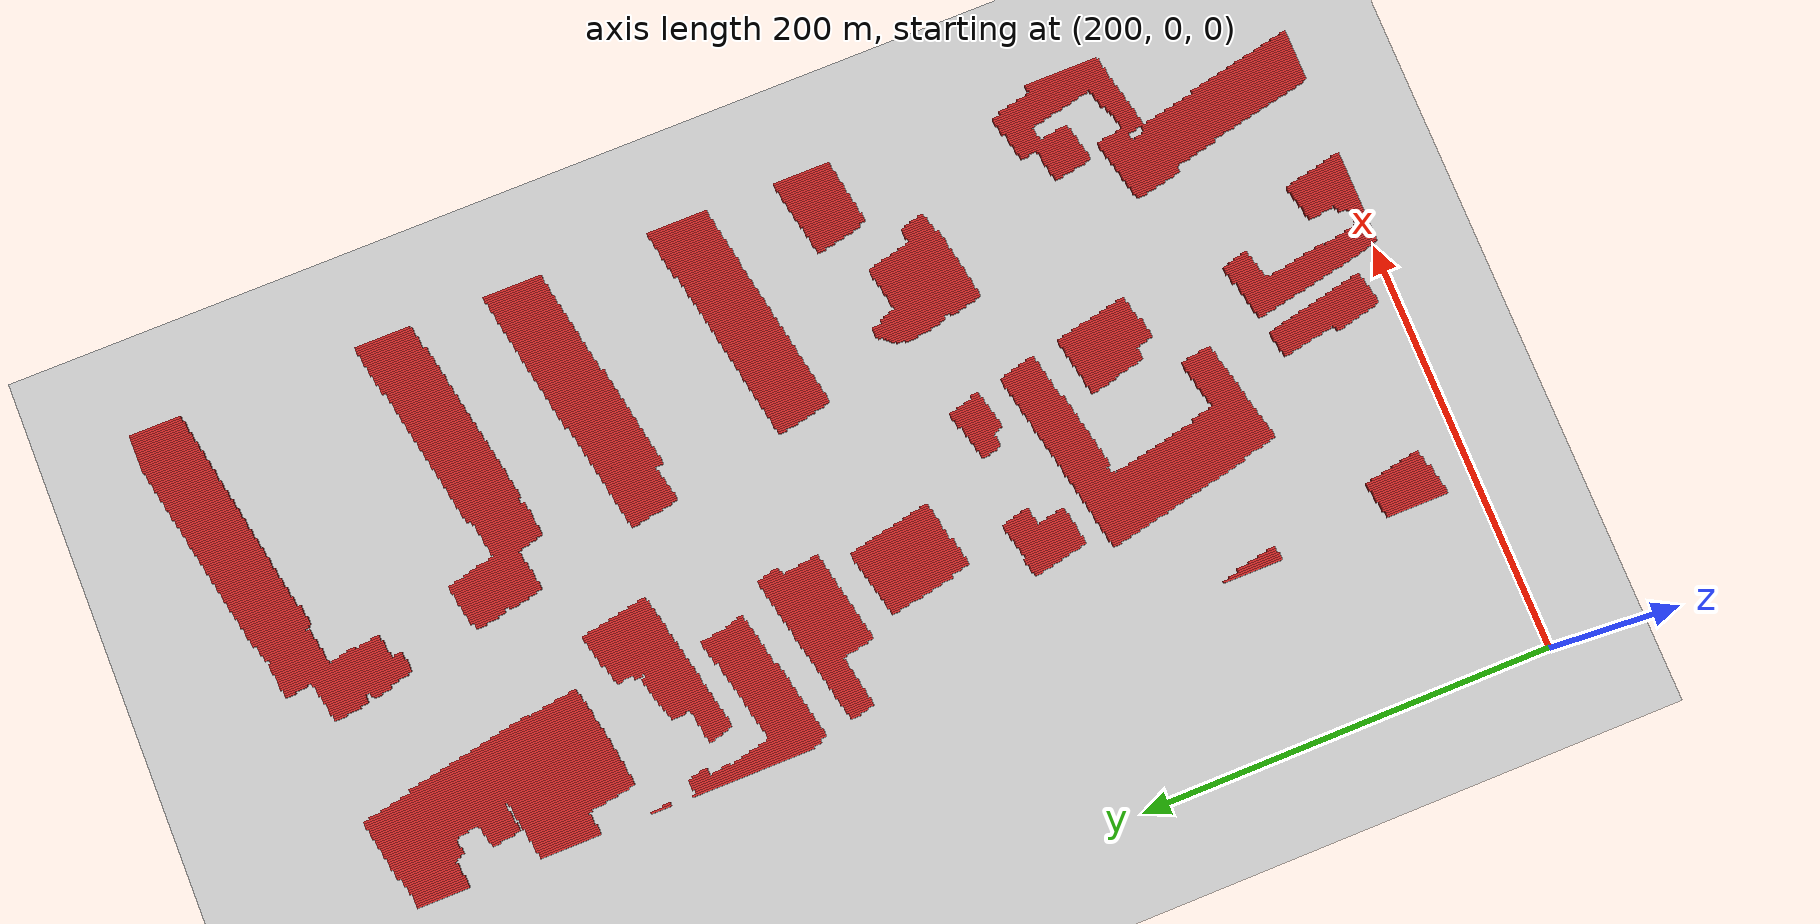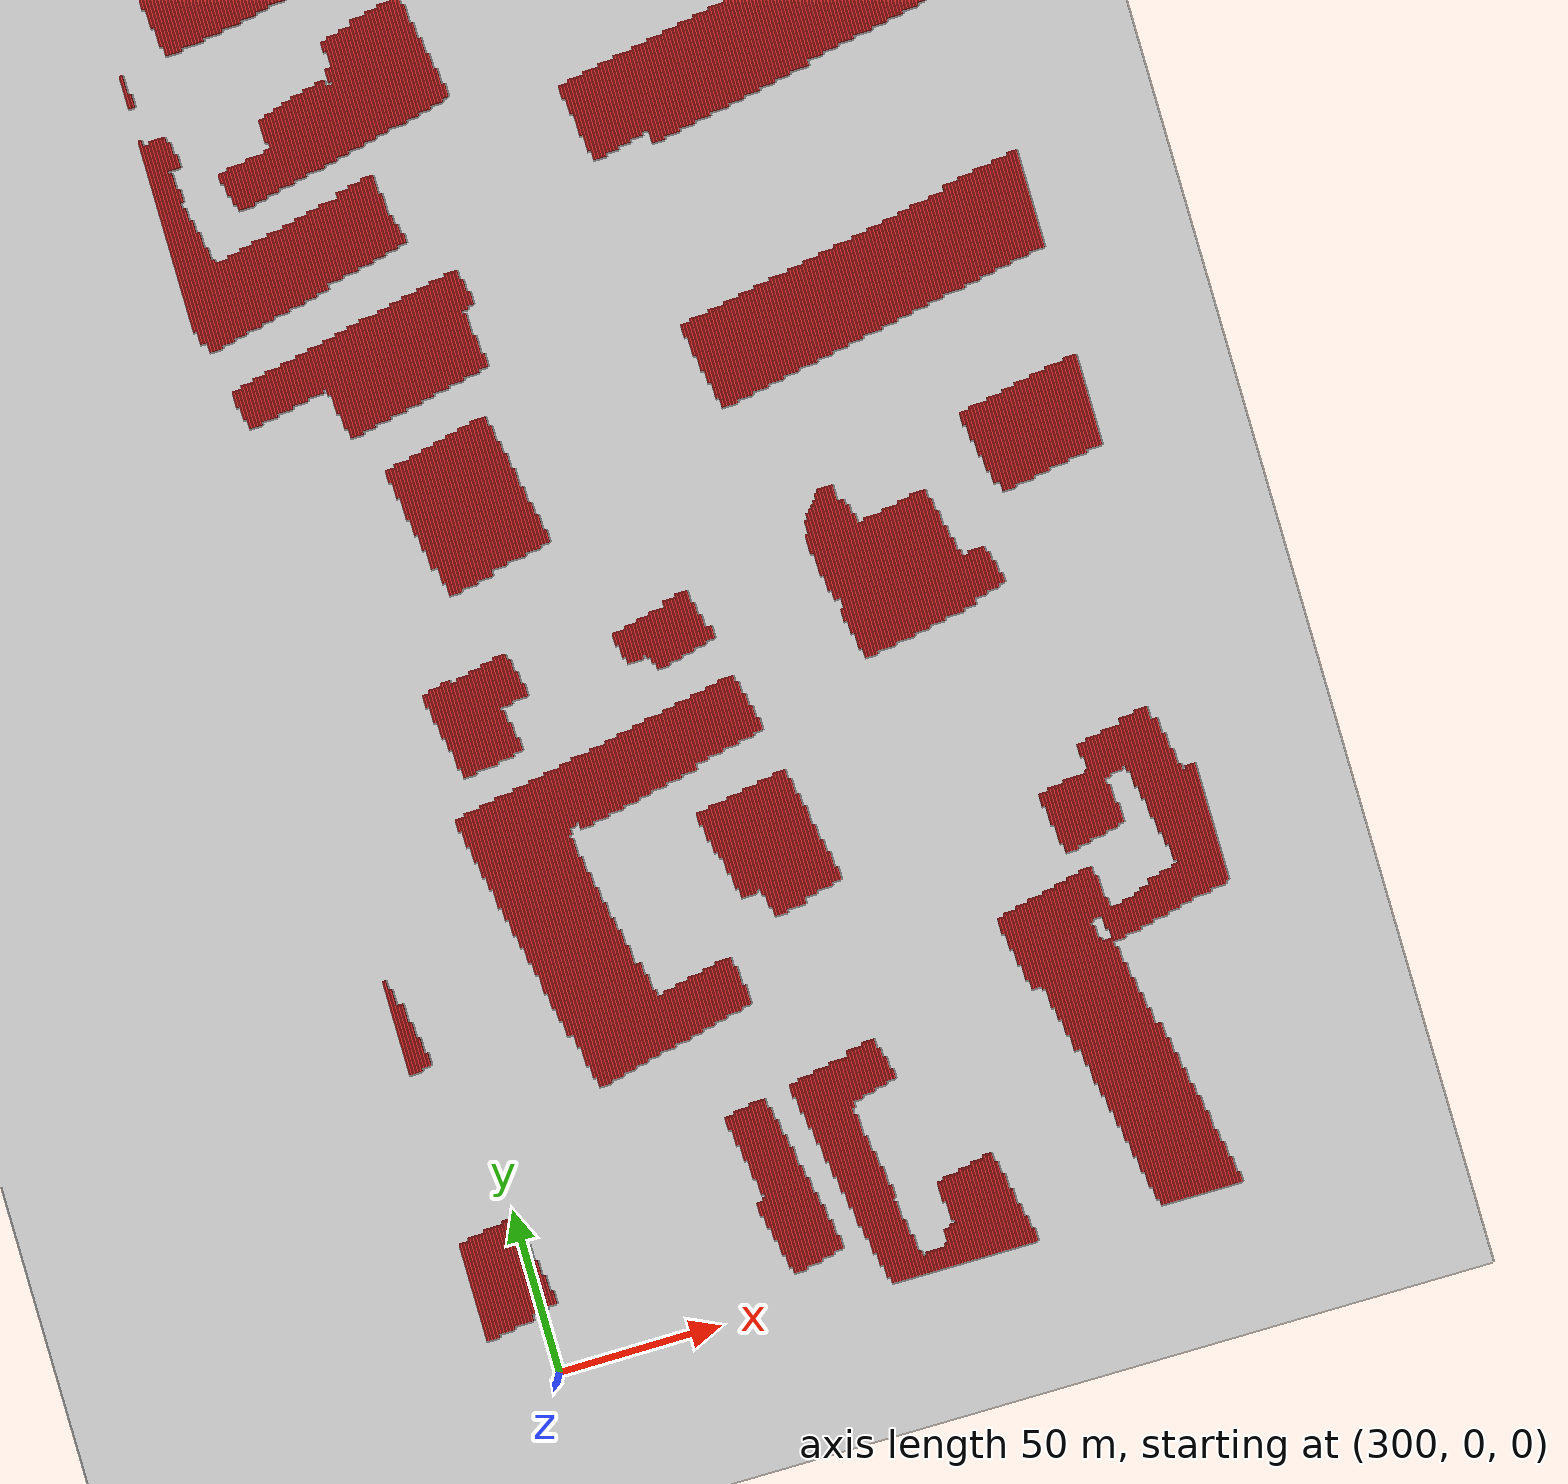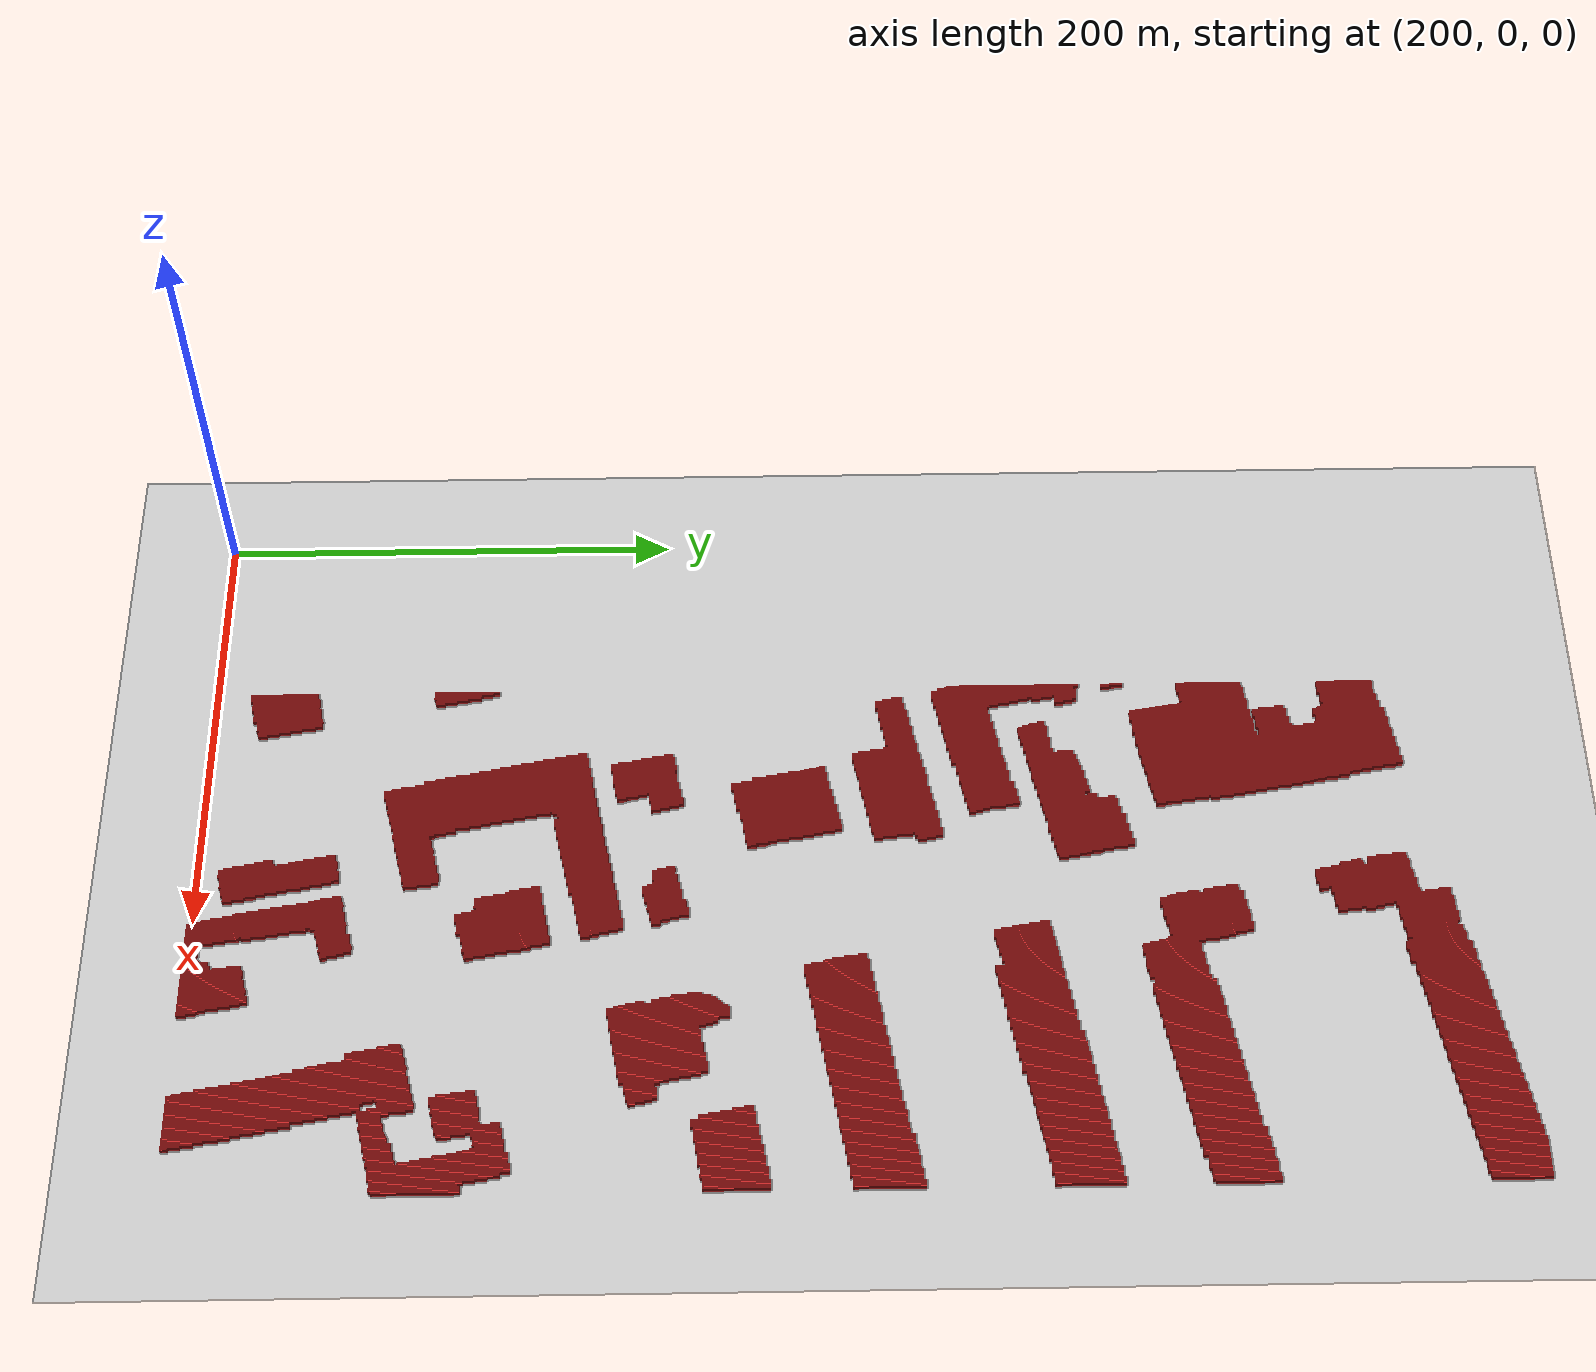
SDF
<sdf version="1.4">
 <world name="1_wall">
  <model name="ground_plane">
   <static>1</static>
   <link name="link">
    <collision name="collision">
     <geometry><plane><normal>0 0 1</normal><size>1000 1000</size></plane></geometry>
     <surface><friction><ode><mu>100</mu><mu2>50</mu2></ode></friction></surface>
    </collision>
    <visual name="visual">
     <cast_shadows>0</cast_shadows>
     <geometry><plane><normal>0 0 1</normal><size>10000 10000</size></plane></geometry>
     <material>
      <script><uri>file://media/materials/scripts/gazebo.material</uri><name>Gazebo/Grey</name></script>
     </material>
    </visual>
    <velocity_decay><linear>0</linear><angular>0</angular></velocity_decay>
   </link>
  </model>
  <model name="Wall_1511">
   <static>1</static>
   <link name="Wall_1511">
    <collision name="Wall_Collision_1511">
     <geometry><box><size>30.0 1.0 2.5</size></box></geometry>
     <pose>0 0 1.25 0 -0 0</pose>
    </collision>
    <visual name="Wall_Visual_1511">
     <pose>0 0 1.25 0 -0 0</pose>
     <geometry><box><size>30.0 1.0 2.5</size></box></geometry>
     <material>
      <script><uri>file://media/materials/scripts/gazebo.material</uri><name>Gazebo/Red</name></script>
     </material>
    </visual>
    <velocity_decay><linear>0</linear><angular>0</angular></velocity_decay>
    <pose>282.5 30.0 0 0 0 1.5707963267948966</pose>
   </link>
  </model>
  <model name="Wall_1512">
   <static>1</static>
   <link name="Wall_1512">
    <collision name="Wall_Collision_1512">
     <geometry><box><size>29.0 1.0 2.5</size></box></geometry>
     <pose>0 0 1.25 0 -0 0</pose>
    </collision>
    <visual name="Wall_Visual_1512">
     <pose>0 0 1.25 0 -0 0</pose>
     <geometry><box><size>29.0 1.0 2.5</size></box></geometry>
     <material>
      <script><uri>file://media/materials/scripts/gazebo.material</uri><name>Gazebo/Red</name></script>
     </material>
    </visual>
    <velocity_decay><linear>0</linear><angular>0</angular></velocity_decay>
    <pose>282.5 111.5 0 0 0 1.5707963267948966</pose>
   </link>
  </model>
  <model name="Wall_1513">
   <static>1</static>
   <link name="Wall_1513">
    <collision name="Wall_Collision_1513">
     <geometry><box><size>59.0 1.0 2.5</size></box></geometry>
     <pose>0 0 1.25 0 -0 0</pose>
    </collision>
    <visual name="Wall_Visual_1513">
     <pose>0 0 1.25 0 -0 0</pose>
     <geometry><box><size>59.0 1.0 2.5</size></box></geometry>
     <material>
      <script><uri>file://media/materials/scripts/gazebo.material</uri><name>Gazebo/Red</name></script>
     </material>
    </visual>
    <velocity_decay><linear>0</linear><angular>0</angular></velocity_decay>
    <pose>282.5 355.5 0 0 0 1.5707963267948966</pose>
   </link>
  </model>
  <model name="Wall_1514">
   <static>1</static>
   <link name="Wall_1514">
    <collision name="Wall_Collision_1514">
     <geometry><box><size>10.0 1.0 2.5</size></box></geometry>
     <pose>0 0 1.25 0 -0 0</pose>
    </collision>
    <visual name="Wall_Visual_1514">
     <pose>0 0 1.25 0 -0 0</pose>
     <geometry><box><size>10.0 1.0 2.5</size></box></geometry>
     <material>
      <script><uri>file://media/materials/scripts/gazebo.material</uri><name>Gazebo/Red</name></script>
     </material>
    </visual>
    <velocity_decay><linear>0</linear><angular>0</angular></velocity_decay>
    <pose>282.5 400.0 0 0 0 1.5707963267948966</pose>
   </link>
  </model>
  <model name="Wall_1515">
   <static>1</static>
   <link name="Wall_1515">
    <collision name="Wall_Collision_1515">
     <geometry><box><size>29.0 1.0 2.5</size></box></geometry>
     <pose>0 0 1.25 0 -0 0</pose>
    </collision>
    <visual name="Wall_Visual_1515">
     <pose>0 0 1.25 0 -0 0</pose>
     <geometry><box><size>29.0 1.0 2.5</size></box></geometry>
     <material>
      <script><uri>file://media/materials/scripts/gazebo.material</uri><name>Gazebo/Red</name></script>
     </material>
    </visual>
    <velocity_decay><linear>0</linear><angular>0</angular></velocity_decay>
    <pose>282.5 443.5 0 0 0 1.5707963267948966</pose>
   </link>
  </model>
  <model name="Wall_1516">
   <static>1</static>
   <link name="Wall_1516">
    <collision name="Wall_Collision_1516">
     <geometry><box><size>25.0 1.0 2.5</size></box></geometry>
     <pose>0 0 1.25 0 -0 0</pose>
    </collision>
    <visual name="Wall_Visual_1516">
     <pose>0 0 1.25 0 -0 0</pose>
     <geometry><box><size>25.0 1.0 2.5</size></box></geometry>
     <material>
      <script><uri>file://media/materials/scripts/gazebo.material</uri><name>Gazebo/Red</name></script>
     </material>
    </visual>
    <velocity_decay><linear>0</linear><angular>0</angular></velocity_decay>
    <pose>282.5 504.5 0 0 0 1.5707963267948966</pose>
   </link>
  </model>
  <model name="Wall_1517">
   <static>1</static>
   <link name="Wall_1517">
    <collision name="Wall_Collision_1517">
     <geometry><box><size>30.0 1.0 2.5</size></box></geometry>
     <pose>0 0 1.25 0 -0 0</pose>
    </collision>
    <visual name="Wall_Visual_1517">
     <pose>0 0 1.25 0 -0 0</pose>
     <geometry><box><size>30.0 1.0 2.5</size></box></geometry>
     <material>
      <script><uri>file://media/materials/scripts/gazebo.material</uri><name>Gazebo/Red</name></script>
     </material>
    </visual>
    <velocity_decay><linear>0</linear><angular>0</angular></velocity_decay>
    <pose>283.5 30.0 0 0 0 1.5707963267948966</pose>
   </link>
  </model>
  <model name="Wall_1518">
   <static>1</static>
   <link name="Wall_1518">
    <collision name="Wall_Collision_1518">
     <geometry><box><size>26.0 1.0 2.5</size></box></geometry>
     <pose>0 0 1.25 0 -0 0</pose>
    </collision>
    <visual name="Wall_Visual_1518">
     <pose>0 0 1.25 0 -0 0</pose>
     <geometry><box><size>26.0 1.0 2.5</size></box></geometry>
     <material>
      <script><uri>file://media/materials/scripts/gazebo.material</uri><name>Gazebo/Red</name></script>
     </material>
    </visual>
    <velocity_decay><linear>0</linear><angular>0</angular></velocity_decay>
    <pose>283.5 110.0 0 0 0 1.5707963267948966</pose>
   </link>
  </model>
  <model name="Wall_1519">
   <static>1</static>
   <link name="Wall_1519">
    <collision name="Wall_Collision_1519">
     <geometry><box><size>61.0 1.0 2.5</size></box></geometry>
     <pose>0 0 1.25 0 -0 0</pose>
    </collision>
    <visual name="Wall_Visual_1519">
     <pose>0 0 1.25 0 -0 0</pose>
     <geometry><box><size>61.0 1.0 2.5</size></box></geometry>
     <material>
      <script><uri>file://media/materials/scripts/gazebo.material</uri><name>Gazebo/Red</name></script>
     </material>
    </visual>
    <velocity_decay><linear>0</linear><angular>0</angular></velocity_decay>
    <pose>283.5 352.5 0 0 0 1.5707963267948966</pose>
   </link>
  </model>
  <model name="Wall_1520">
   <static>1</static>
   <link name="Wall_1520">
    <collision name="Wall_Collision_1520">
     <geometry><box><size>4.0 1.0 2.5</size></box></geometry>
     <pose>0 0 1.25 0 -0 0</pose>
    </collision>
    <visual name="Wall_Visual_1520">
     <pose>0 0 1.25 0 -0 0</pose>
     <geometry><box><size>4.0 1.0 2.5</size></box></geometry>
     <material>
      <script><uri>file://media/materials/scripts/gazebo.material</uri><name>Gazebo/Red</name></script>
     </material>
    </visual>
    <velocity_decay><linear>0</linear><angular>0</angular></velocity_decay>
    <pose>283.5 397.0 0 0 0 1.5707963267948966</pose>
   </link>
  </model>
  <model name="Wall_1521">
   <static>1</static>
   <link name="Wall_1521">
    <collision name="Wall_Collision_1521">
     <geometry><box><size>29.0 1.0 2.5</size></box></geometry>
     <pose>0 0 1.25 0 -0 0</pose>
    </collision>
    <visual name="Wall_Visual_1521">
     <pose>0 0 1.25 0 -0 0</pose>
     <geometry><box><size>29.0 1.0 2.5</size></box></geometry>
     <material>
      <script><uri>file://media/materials/scripts/gazebo.material</uri><name>Gazebo/Red</name></script>
     </material>
    </visual>
    <velocity_decay><linear>0</linear><angular>0</angular></velocity_decay>
    <pose>283.5 443.5 0 0 0 1.5707963267948966</pose>
   </link>
  </model>
  <model name="Wall_1522">
   <static>1</static>
   <link name="Wall_1522">
    <collision name="Wall_Collision_1522">
     <geometry><box><size>25.0 1.0 2.5</size></box></geometry>
     <pose>0 0 1.25 0 -0 0</pose>
    </collision>
    <visual name="Wall_Visual_1522">
     <pose>0 0 1.25 0 -0 0</pose>
     <geometry><box><size>25.0 1.0 2.5</size></box></geometry>
     <material>
      <script><uri>file://media/materials/scripts/gazebo.material</uri><name>Gazebo/Red</name></script>
     </material>
    </visual>
    <velocity_decay><linear>0</linear><angular>0</angular></velocity_decay>
    <pose>283.5 504.5 0 0 0 1.5707963267948966</pose>
   </link>
  </model>
  <model name="Wall_1523">
   <static>1</static>
   <link name="Wall_1523">
    <collision name="Wall_Collision_1523">
     <geometry><box><size>30.0 1.0 2.5</size></box></geometry>
     <pose>0 0 1.25 0 -0 0</pose>
    </collision>
    <visual name="Wall_Visual_1523">
     <pose>0 0 1.25 0 -0 0</pose>
     <geometry><box><size>30.0 1.0 2.5</size></box></geometry>
     <material>
      <script><uri>file://media/materials/scripts/gazebo.material</uri><name>Gazebo/Red</name></script>
     </material>
    </visual>
    <velocity_decay><linear>0</linear><angular>0</angular></velocity_decay>
    <pose>284.5 30.0 0 0 0 1.5707963267948966</pose>
   </link>
  </model>
  <model name="Wall_1524">
   <static>1</static>
   <link name="Wall_1524">
    <collision name="Wall_Collision_1524">
     <geometry><box><size>21.0 1.0 2.5</size></box></geometry>
     <pose>0 0 1.25 0 -0 0</pose>
    </collision>
    <visual name="Wall_Visual_1524">
     <pose>0 0 1.25 0 -0 0</pose>
     <geometry><box><size>21.0 1.0 2.5</size></box></geometry>
     <material>
      <script><uri>file://media/materials/scripts/gazebo.material</uri><name>Gazebo/Red</name></script>
     </material>
    </visual>
    <velocity_decay><linear>0</linear><angular>0</angular></velocity_decay>
    <pose>284.5 107.5 0 0 0 1.5707963267948966</pose>
   </link>
  </model>
  <model name="Wall_1525">
   <static>1</static>
   <link name="Wall_1525">
    <collision name="Wall_Collision_1525">
     <geometry><box><size>61.0 1.0 2.5</size></box></geometry>
     <pose>0 0 1.25 0 -0 0</pose>
    </collision>
    <visual name="Wall_Visual_1525">
     <pose>0 0 1.25 0 -0 0</pose>
     <geometry><box><size>61.0 1.0 2.5</size></box></geometry>
     <material>
      <script><uri>file://media/materials/scripts/gazebo.material</uri><name>Gazebo/Red</name></script>
     </material>
    </visual>
    <velocity_decay><linear>0</linear><angular>0</angular></velocity_decay>
    <pose>284.5 352.5 0 0 0 1.5707963267948966</pose>
   </link>
  </model>
  <model name="Wall_1526">
   <static>1</static>
   <link name="Wall_1526">
    <collision name="Wall_Collision_1526">
     <geometry><box><size>29.0 1.0 2.5</size></box></geometry>
     <pose>0 0 1.25 0 -0 0</pose>
    </collision>
    <visual name="Wall_Visual_1526">
     <pose>0 0 1.25 0 -0 0</pose>
     <geometry><box><size>29.0 1.0 2.5</size></box></geometry>
     <material>
      <script><uri>file://media/materials/scripts/gazebo.material</uri><name>Gazebo/Red</name></script>
     </material>
    </visual>
    <velocity_decay><linear>0</linear><angular>0</angular></velocity_decay>
    <pose>284.5 443.5 0 0 0 1.5707963267948966</pose>
   </link>
  </model>
  <model name="Wall_1527">
   <static>1</static>
   <link name="Wall_1527">
    <collision name="Wall_Collision_1527">
     <geometry><box><size>25.0 1.0 2.5</size></box></geometry>
     <pose>0 0 1.25 0 -0 0</pose>
    </collision>
    <visual name="Wall_Visual_1527">
     <pose>0 0 1.25 0 -0 0</pose>
     <geometry><box><size>25.0 1.0 2.5</size></box></geometry>
     <material>
      <script><uri>file://media/materials/scripts/gazebo.material</uri><name>Gazebo/Red</name></script>
     </material>
    </visual>
    <velocity_decay><linear>0</linear><angular>0</angular></velocity_decay>
    <pose>284.5 504.5 0 0 0 1.5707963267948966</pose>
   </link>
  </model>
  <model name="Wall_1528">
   <static>1</static>
   <link name="Wall_1528">
    <collision name="Wall_Collision_1528">
     <geometry><box><size>31.0 1.0 2.5</size></box></geometry>
     <pose>0 0 1.25 0 -0 0</pose>
    </collision>
    <visual name="Wall_Visual_1528">
     <pose>0 0 1.25 0 -0 0</pose>
     <geometry><box><size>31.0 1.0 2.5</size></box></geometry>
     <material>
      <script><uri>file://media/materials/scripts/gazebo.material</uri><name>Gazebo/Red</name></script>
     </material>
    </visual>
    <velocity_decay><linear>0</linear><angular>0</angular></velocity_decay>
    <pose>285.5 30.5 0 0 0 1.5707963267948966</pose>
   </link>
  </model>
  <model name="Wall_1529">
   <static>1</static>
   <link name="Wall_1529">
    <collision name="Wall_Collision_1529">
     <geometry><box><size>21.0 1.0 2.5</size></box></geometry>
     <pose>0 0 1.25 0 -0 0</pose>
    </collision>
    <visual name="Wall_Visual_1529">
     <pose>0 0 1.25 0 -0 0</pose>
     <geometry><box><size>21.0 1.0 2.5</size></box></geometry>
     <material>
      <script><uri>file://media/materials/scripts/gazebo.material</uri><name>Gazebo/Red</name></script>
     </material>
    </visual>
    <velocity_decay><linear>0</linear><angular>0</angular></velocity_decay>
    <pose>285.5 107.5 0 0 0 1.5707963267948966</pose>
   </link>
  </model>
  <model name="Wall_1530">
   <static>1</static>
   <link name="Wall_1530">
    <collision name="Wall_Collision_1530">
     <geometry><box><size>65.0 1.0 2.5</size></box></geometry>
     <pose>0 0 1.25 0 -0 0</pose>
    </collision>
    <visual name="Wall_Visual_1530">
     <pose>0 0 1.25 0 -0 0</pose>
     <geometry><box><size>65.0 1.0 2.5</size></box></geometry>
     <material>
      <script><uri>file://media/materials/scripts/gazebo.material</uri><name>Gazebo/Red</name></script>
     </material>
    </visual>
    <velocity_decay><linear>0</linear><angular>0</angular></velocity_decay>
    <pose>285.5 351.5 0 0 0 1.5707963267948966</pose>
   </link>
  </model>
  <model name="Wall_1531">
   <static>1</static>
   <link name="Wall_1531">
    <collision name="Wall_Collision_1531">
     <geometry><box><size>30.0 1.0 2.5</size></box></geometry>
     <pose>0 0 1.25 0 -0 0</pose>
    </collision>
    <visual name="Wall_Visual_1531">
     <pose>0 0 1.25 0 -0 0</pose>
     <geometry><box><size>30.0 1.0 2.5</size></box></geometry>
     <material>
      <script><uri>file://media/materials/scripts/gazebo.material</uri><name>Gazebo/Red</name></script>
     </material>
    </visual>
    <velocity_decay><linear>0</linear><angular>0</angular></velocity_decay>
    <pose>285.5 444.0 0 0 0 1.5707963267948966</pose>
   </link>
  </model>
  <model name="Wall_1532">
   <static>1</static>
   <link name="Wall_1532">
    <collision name="Wall_Collision_1532">
     <geometry><box><size>25.0 1.0 2.5</size></box></geometry>
     <pose>0 0 1.25 0 -0 0</pose>
    </collision>
    <visual name="Wall_Visual_1532">
     <pose>0 0 1.25 0 -0 0</pose>
     <geometry><box><size>25.0 1.0 2.5</size></box></geometry>
     <material>
      <script><uri>file://media/materials/scripts/gazebo.material</uri><name>Gazebo/Red</name></script>
     </material>
    </visual>
    <velocity_decay><linear>0</linear><angular>0</angular></velocity_decay>
    <pose>285.5 504.5 0 0 0 1.5707963267948966</pose>
   </link>
  </model>
  <model name="Wall_1533">
   <static>1</static>
   <link name="Wall_1533">
    <collision name="Wall_Collision_1533">
     <geometry><box><size>30.0 1.0 2.5</size></box></geometry>
     <pose>0 0 1.25 0 -0 0</pose>
    </collision>
    <visual name="Wall_Visual_1533">
     <pose>0 0 1.25 0 -0 0</pose>
     <geometry><box><size>30.0 1.0 2.5</size></box></geometry>
     <material>
      <script><uri>file://media/materials/scripts/gazebo.material</uri><name>Gazebo/Red</name></script>
     </material>
    </visual>
    <velocity_decay><linear>0</linear><angular>0</angular></velocity_decay>
    <pose>286.5 31.0 0 0 0 1.5707963267948966</pose>
   </link>
  </model>
  <model name="Wall_1534">
   <static>1</static>
   <link name="Wall_1534">
    <collision name="Wall_Collision_1534">
     <geometry><box><size>14.0 1.0 2.5</size></box></geometry>
     <pose>0 0 1.25 0 -0 0</pose>
    </collision>
    <visual name="Wall_Visual_1534">
     <pose>0 0 1.25 0 -0 0</pose>
     <geometry><box><size>14.0 1.0 2.5</size></box></geometry>
     <material>
      <script><uri>file://media/materials/scripts/gazebo.material</uri><name>Gazebo/Red</name></script>
     </material>
    </visual>
    <velocity_decay><linear>0</linear><angular>0</angular></velocity_decay>
    <pose>286.5 105.0 0 0 0 1.5707963267948966</pose>
   </link>
  </model>
  <model name="Wall_1535">
   <static>1</static>
   <link name="Wall_1535">
    <collision name="Wall_Collision_1535">
     <geometry><box><size>65.0 1.0 2.5</size></box></geometry>
     <pose>0 0 1.25 0 -0 0</pose>
    </collision>
    <visual name="Wall_Visual_1535">
     <pose>0 0 1.25 0 -0 0</pose>
     <geometry><box><size>65.0 1.0 2.5</size></box></geometry>
     <material>
      <script><uri>file://media/materials/scripts/gazebo.material</uri><name>Gazebo/Red</name></script>
     </material>
    </visual>
    <velocity_decay><linear>0</linear><angular>0</angular></velocity_decay>
    <pose>286.5 351.5 0 0 0 1.5707963267948966</pose>
   </link>
  </model>
  <model name="Wall_1536">
   <static>1</static>
   <link name="Wall_1536">
    <collision name="Wall_Collision_1536">
     <geometry><box><size>30.0 1.0 2.5</size></box></geometry>
     <pose>0 0 1.25 0 -0 0</pose>
    </collision>
    <visual name="Wall_Visual_1536">
     <pose>0 0 1.25 0 -0 0</pose>
     <geometry><box><size>30.0 1.0 2.5</size></box></geometry>
     <material>
      <script><uri>file://media/materials/scripts/gazebo.material</uri><name>Gazebo/Red</name></script>
     </material>
    </visual>
    <velocity_decay><linear>0</linear><angular>0</angular></velocity_decay>
    <pose>286.5 444.0 0 0 0 1.5707963267948966</pose>
   </link>
  </model>
  <model name="Wall_1537">
   <static>1</static>
   <link name="Wall_1537">
    <collision name="Wall_Collision_1537">
     <geometry><box><size>25.0 1.0 2.5</size></box></geometry>
     <pose>0 0 1.25 0 -0 0</pose>
    </collision>
    <visual name="Wall_Visual_1537">
     <pose>0 0 1.25 0 -0 0</pose>
     <geometry><box><size>25.0 1.0 2.5</size></box></geometry>
     <material>
      <script><uri>file://media/materials/scripts/gazebo.material</uri><name>Gazebo/Red</name></script>
     </material>
    </visual>
    <velocity_decay><linear>0</linear><angular>0</angular></velocity_decay>
    <pose>286.5 504.5 0 0 0 1.5707963267948966</pose>
   </link>
  </model>
  <model name="Wall_1538">
   <static>1</static>
   <link name="Wall_1538">
    <collision name="Wall_Collision_1538">
     <geometry><box><size>30.0 1.0 2.5</size></box></geometry>
     <pose>0 0 1.25 0 -0 0</pose>
    </collision>
    <visual name="Wall_Visual_1538">
     <pose>0 0 1.25 0 -0 0</pose>
     <geometry><box><size>30.0 1.0 2.5</size></box></geometry>
     <material>
      <script><uri>file://media/materials/scripts/gazebo.material</uri><name>Gazebo/Red</name></script>
     </material>
    </visual>
    <velocity_decay><linear>0</linear><angular>0</angular></velocity_decay>
    <pose>287.5 31.0 0 0 0 1.5707963267948966</pose>
   </link>
  </model>
  <model name="Wall_1539">
   <static>1</static>
   <link name="Wall_1539">
    <collision name="Wall_Collision_1539">
     <geometry><box><size>9.0 1.0 2.5</size></box></geometry>
     <pose>0 0 1.25 0 -0 0</pose>
    </collision>
    <visual name="Wall_Visual_1539">
     <pose>0 0 1.25 0 -0 0</pose>
     <geometry><box><size>9.0 1.0 2.5</size></box></geometry>
     <material>
      <script><uri>file://media/materials/scripts/gazebo.material</uri><name>Gazebo/Red</name></script>
     </material>
    </visual>
    <velocity_decay><linear>0</linear><angular>0</angular></velocity_decay>
    <pose>287.5 102.5 0 0 0 1.5707963267948966</pose>
   </link>
  </model>
  <model name="Wall_1540">
   <static>1</static>
   <link name="Wall_1540">
    <collision name="Wall_Collision_1540">
     <geometry><box><size>65.0 1.0 2.5</size></box></geometry>
     <pose>0 0 1.25 0 -0 0</pose>
    </collision>
    <visual name="Wall_Visual_1540">
     <pose>0 0 1.25 0 -0 0</pose>
     <geometry><box><size>65.0 1.0 2.5</size></box></geometry>
     <material>
      <script><uri>file://media/materials/scripts/gazebo.material</uri><name>Gazebo/Red</name></script>
     </material>
    </visual>
    <velocity_decay><linear>0</linear><angular>0</angular></velocity_decay>
    <pose>287.5 351.5 0 0 0 1.5707963267948966</pose>
   </link>
  </model>
  <model name="Wall_1541">
   <static>1</static>
   <link name="Wall_1541">
    <collision name="Wall_Collision_1541">
     <geometry><box><size>29.0 1.0 2.5</size></box></geometry>
     <pose>0 0 1.25 0 -0 0</pose>
    </collision>
    <visual name="Wall_Visual_1541">
     <pose>0 0 1.25 0 -0 0</pose>
     <geometry><box><size>29.0 1.0 2.5</size></box></geometry>
     <material>
      <script><uri>file://media/materials/scripts/gazebo.material</uri><name>Gazebo/Red</name></script>
     </material>
    </visual>
    <velocity_decay><linear>0</linear><angular>0</angular></velocity_decay>
    <pose>287.5 444.5 0 0 0 1.5707963267948966</pose>
   </link>
  </model>
  <model name="Wall_1542">
   <static>1</static>
   <link name="Wall_1542">
    <collision name="Wall_Collision_1542">
     <geometry><box><size>25.0 1.0 2.5</size></box></geometry>
     <pose>0 0 1.25 0 -0 0</pose>
    </collision>
    <visual name="Wall_Visual_1542">
     <pose>0 0 1.25 0 -0 0</pose>
     <geometry><box><size>25.0 1.0 2.5</size></box></geometry>
     <material>
      <script><uri>file://media/materials/scripts/gazebo.material</uri><name>Gazebo/Red</name></script>
     </material>
    </visual>
    <velocity_decay><linear>0</linear><angular>0</angular></velocity_decay>
    <pose>287.5 504.5 0 0 0 1.5707963267948966</pose>
   </link>
  </model>
  <model name="Wall_1543">
   <static>1</static>
   <link name="Wall_1543">
    <collision name="Wall_Collision_1543">
     <geometry><box><size>30.0 1.0 2.5</size></box></geometry>
     <pose>0 0 1.25 0 -0 0</pose>
    </collision>
    <visual name="Wall_Visual_1543">
     <pose>0 0 1.25 0 -0 0</pose>
     <geometry><box><size>30.0 1.0 2.5</size></box></geometry>
     <material>
      <script><uri>file://media/materials/scripts/gazebo.material</uri><name>Gazebo/Red</name></script>
     </material>
    </visual>
    <velocity_decay><linear>0</linear><angular>0</angular></velocity_decay>
    <pose>288.5 31.0 0 0 0 1.5707963267948966</pose>
   </link>
  </model>
  <model name="Wall_1544">
   <static>1</static>
   <link name="Wall_1544">
    <collision name="Wall_Collision_1544">
     <geometry><box><size>4.0 1.0 2.5</size></box></geometry>
     <pose>0 0 1.25 0 -0 0</pose>
    </collision>
    <visual name="Wall_Visual_1544">
     <pose>0 0 1.25 0 -0 0</pose>
     <geometry><box><size>4.0 1.0 2.5</size></box></geometry>
     <material>
      <script><uri>file://media/materials/scripts/gazebo.material</uri><name>Gazebo/Red</name></script>
     </material>
    </visual>
    <velocity_decay><linear>0</linear><angular>0</angular></velocity_decay>
    <pose>288.5 100.0 0 0 0 1.5707963267948966</pose>
   </link>
  </model>
  <model name="Wall_1545">
   <static>1</static>
   <link name="Wall_1545">
    <collision name="Wall_Collision_1545">
     <geometry><box><size>5.0 1.0 2.5</size></box></geometry>
     <pose>0 0 1.25 0 -0 0</pose>
    </collision>
    <visual name="Wall_Visual_1545">
     <pose>0 0 1.25 0 -0 0</pose>
     <geometry><box><size>5.0 1.0 2.5</size></box></geometry>
     <material>
      <script><uri>file://media/materials/scripts/gazebo.material</uri><name>Gazebo/Red</name></script>
     </material>
    </visual>
    <velocity_decay><linear>0</linear><angular>0</angular></velocity_decay>
    <pose>288.5 303.5 0 0 0 1.5707963267948966</pose>
   </link>
  </model>
  <model name="Wall_1546">
   <static>1</static>
   <link name="Wall_1546">
    <collision name="Wall_Collision_1546">
     <geometry><box><size>54.0 1.0 2.5</size></box></geometry>
     <pose>0 0 1.25 0 -0 0</pose>
    </collision>
    <visual name="Wall_Visual_1546">
     <pose>0 0 1.25 0 -0 0</pose>
     <geometry><box><size>54.0 1.0 2.5</size></box></geometry>
     <material>
      <script><uri>file://media/materials/scripts/gazebo.material</uri><name>Gazebo/Red</name></script>
     </material>
    </visual>
    <velocity_decay><linear>0</linear><angular>0</angular></velocity_decay>
    <pose>288.5 346.0 0 0 0 1.5707963267948966</pose>
   </link>
  </model>
  <model name="Wall_1547">
   <static>1</static>
   <link name="Wall_1547">
    <collision name="Wall_Collision_1547">
     <geometry><box><size>10.0 1.0 2.5</size></box></geometry>
     <pose>0 0 1.25 0 -0 0</pose>
    </collision>
    <visual name="Wall_Visual_1547">
     <pose>0 0 1.25 0 -0 0</pose>
     <geometry><box><size>10.0 1.0 2.5</size></box></geometry>
     <material>
      <script><uri>file://media/materials/scripts/gazebo.material</uri><name>Gazebo/Red</name></script>
     </material>
    </visual>
    <velocity_decay><linear>0</linear><angular>0</angular></velocity_decay>
    <pose>288.5 379.0 0 0 0 1.5707963267948966</pose>
   </link>
  </model>
  <model name="Wall_1548">
   <static>1</static>
   <link name="Wall_1548">
    <collision name="Wall_Collision_1548">
     <geometry><box><size>29.0 1.0 2.5</size></box></geometry>
     <pose>0 0 1.25 0 -0 0</pose>
    </collision>
    <visual name="Wall_Visual_1548">
     <pose>0 0 1.25 0 -0 0</pose>
     <geometry><box><size>29.0 1.0 2.5</size></box></geometry>
     <material>
      <script><uri>file://media/materials/scripts/gazebo.material</uri><name>Gazebo/Red</name></script>
     </material>
    </visual>
    <velocity_decay><linear>0</linear><angular>0</angular></velocity_decay>
    <pose>288.5 444.5 0 0 0 1.5707963267948966</pose>
   </link>
  </model>
  <model name="Wall_1549">
   <static>1</static>
   <link name="Wall_1549">
    <collision name="Wall_Collision_1549">
     <geometry><box><size>24.0 1.0 2.5</size></box></geometry>
     <pose>0 0 1.25 0 -0 0</pose>
    </collision>
    <visual name="Wall_Visual_1549">
     <pose>0 0 1.25 0 -0 0</pose>
     <geometry><box><size>24.0 1.0 2.5</size></box></geometry>
     <material>
      <script><uri>file://media/materials/scripts/gazebo.material</uri><name>Gazebo/Red</name></script>
     </material>
    </visual>
    <velocity_decay><linear>0</linear><angular>0</angular></velocity_decay>
    <pose>288.5 505.0 0 0 0 1.5707963267948966</pose>
   </link>
  </model>
  <model name="Wall_1550">
   <static>1</static>
   <link name="Wall_1550">
    <collision name="Wall_Collision_1550">
     <geometry><box><size>30.0 1.0 2.5</size></box></geometry>
     <pose>0 0 1.25 0 -0 0</pose>
    </collision>
    <visual name="Wall_Visual_1550">
     <pose>0 0 1.25 0 -0 0</pose>
     <geometry><box><size>30.0 1.0 2.5</size></box></geometry>
     <material>
      <script><uri>file://media/materials/scripts/gazebo.material</uri><name>Gazebo/Red</name></script>
     </material>
    </visual>
    <velocity_decay><linear>0</linear><angular>0</angular></velocity_decay>
    <pose>289.5 31.0 0 0 0 1.5707963267948966</pose>
   </link>
  </model>
  <model name="Wall_1551">
   <static>1</static>
   <link name="Wall_1551">
    <collision name="Wall_Collision_1551">
     <geometry><box><size>9.0 1.0 2.5</size></box></geometry>
     <pose>0 0 1.25 0 -0 0</pose>
    </collision>
    <visual name="Wall_Visual_1551">
     <pose>0 0 1.25 0 -0 0</pose>
     <geometry><box><size>9.0 1.0 2.5</size></box></geometry>
     <material>
      <script><uri>file://media/materials/scripts/gazebo.material</uri><name>Gazebo/Red</name></script>
     </material>
    </visual>
    <velocity_decay><linear>0</linear><angular>0</angular></velocity_decay>
    <pose>289.5 301.5 0 0 0 1.5707963267948966</pose>
   </link>
  </model>
  <model name="Wall_1552">
   <static>1</static>
   <link name="Wall_1552">
    <collision name="Wall_Collision_1552">
     <geometry><box><size>42.0 1.0 2.5</size></box></geometry>
     <pose>0 0 1.25 0 -0 0</pose>
    </collision>
    <visual name="Wall_Visual_1552">
     <pose>0 0 1.25 0 -0 0</pose>
     <geometry><box><size>42.0 1.0 2.5</size></box></geometry>
     <material>
      <script><uri>file://media/materials/scripts/gazebo.material</uri><name>Gazebo/Red</name></script>
     </material>
    </visual>
    <velocity_decay><linear>0</linear><angular>0</angular></velocity_decay>
    <pose>289.5 341.0 0 0 0 1.5707963267948966</pose>
   </link>
  </model>
  <model name="Wall_1553">
   <static>1</static>
   <link name="Wall_1553">
    <collision name="Wall_Collision_1553">
     <geometry><box><size>4.0 1.0 2.5</size></box></geometry>
     <pose>0 0 1.25 0 -0 0</pose>
    </collision>
    <visual name="Wall_Visual_1553">
     <pose>0 0 1.25 0 -0 0</pose>
     <geometry><box><size>4.0 1.0 2.5</size></box></geometry>
     <material>
      <script><uri>file://media/materials/scripts/gazebo.material</uri><name>Gazebo/Red</name></script>
     </material>
    </visual>
    <velocity_decay><linear>0</linear><angular>0</angular></velocity_decay>
    <pose>289.5 366.0 0 0 0 1.5707963267948966</pose>
   </link>
  </model>
  <model name="Wall_1554">
   <static>1</static>
   <link name="Wall_1554">
    <collision name="Wall_Collision_1554">
     <geometry><box><size>10.0 1.0 2.5</size></box></geometry>
     <pose>0 0 1.25 0 -0 0</pose>
    </collision>
    <visual name="Wall_Visual_1554">
     <pose>0 0 1.25 0 -0 0</pose>
     <geometry><box><size>10.0 1.0 2.5</size></box></geometry>
     <material>
      <script><uri>file://media/materials/scripts/gazebo.material</uri><name>Gazebo/Red</name></script>
     </material>
    </visual>
    <velocity_decay><linear>0</linear><angular>0</angular></velocity_decay>
    <pose>289.5 379.0 0 0 0 1.5707963267948966</pose>
   </link>
  </model>
  <model name="Wall_1555">
   <static>1</static>
   <link name="Wall_1555">
    <collision name="Wall_Collision_1555">
     <geometry><box><size>29.0 1.0 2.5</size></box></geometry>
     <pose>0 0 1.25 0 -0 0</pose>
    </collision>
    <visual name="Wall_Visual_1555">
     <pose>0 0 1.25 0 -0 0</pose>
     <geometry><box><size>29.0 1.0 2.5</size></box></geometry>
     <material>
      <script><uri>file://media/materials/scripts/gazebo.material</uri><name>Gazebo/Red</name></script>
     </material>
    </visual>
    <velocity_decay><linear>0</linear><angular>0</angular></velocity_decay>
    <pose>289.5 444.5 0 0 0 1.5707963267948966</pose>
   </link>
  </model>
  <model name="Wall_1556">
   <static>1</static>
   <link name="Wall_1556">
    <collision name="Wall_Collision_1556">
     <geometry><box><size>25.0 1.0 2.5</size></box></geometry>
     <pose>0 0 1.25 0 -0 0</pose>
    </collision>
    <visual name="Wall_Visual_1556">
     <pose>0 0 1.25 0 -0 0</pose>
     <geometry><box><size>25.0 1.0 2.5</size></box></geometry>
     <material>
      <script><uri>file://media/materials/scripts/gazebo.material</uri><name>Gazebo/Red</name></script>
     </material>
    </visual>
    <velocity_decay><linear>0</linear><angular>0</angular></velocity_decay>
    <pose>289.5 505.5 0 0 0 1.5707963267948966</pose>
   </link>
  </model>
  <model name="Wall_1557">
   <static>1</static>
   <link name="Wall_1557">
    <collision name="Wall_Collision_1557">
     <geometry><box><size>31.0 1.0 2.5</size></box></geometry>
     <pose>0 0 1.25 0 -0 0</pose>
    </collision>
    <visual name="Wall_Visual_1557">
     <pose>0 0 1.25 0 -0 0</pose>
     <geometry><box><size>31.0 1.0 2.5</size></box></geometry>
     <material>
      <script><uri>file://media/materials/scripts/gazebo.material</uri><name>Gazebo/Red</name></script>
     </material>
    </visual>
    <velocity_decay><linear>0</linear><angular>0</angular></velocity_decay>
    <pose>290.5 31.5 0 0 0 1.5707963267948966</pose>
   </link>
  </model>
  <model name="Wall_1558">
   <static>1</static>
   <link name="Wall_1558">
    <collision name="Wall_Collision_1558">
     <geometry><box><size>12.0 1.0 2.5</size></box></geometry>
     <pose>0 0 1.25 0 -0 0</pose>
    </collision>
    <visual name="Wall_Visual_1558">
     <pose>0 0 1.25 0 -0 0</pose>
     <geometry><box><size>12.0 1.0 2.5</size></box></geometry>
     <material>
      <script><uri>file://media/materials/scripts/gazebo.material</uri><name>Gazebo/Red</name></script>
     </material>
    </visual>
    <velocity_decay><linear>0</linear><angular>0</angular></velocity_decay>
    <pose>290.5 300.0 0 0 0 1.5707963267948966</pose>
   </link>
  </model>
  <model name="Wall_1559">
   <static>1</static>
   <link name="Wall_1559">
    <collision name="Wall_Collision_1559">
     <geometry><box><size>38.0 1.0 2.5</size></box></geometry>
     <pose>0 0 1.25 0 -0 0</pose>
    </collision>
    <visual name="Wall_Visual_1559">
     <pose>0 0 1.25 0 -0 0</pose>
     <geometry><box><size>38.0 1.0 2.5</size></box></geometry>
     <material>
      <script><uri>file://media/materials/scripts/gazebo.material</uri><name>Gazebo/Red</name></script>
     </material>
    </visual>
    <velocity_decay><linear>0</linear><angular>0</angular></velocity_decay>
    <pose>290.5 339.0 0 0 0 1.5707963267948966</pose>
   </link>
  </model>
  <model name="Wall_1560">
   <static>1</static>
   <link name="Wall_1560">
    <collision name="Wall_Collision_1560">
     <geometry><box><size>8.0 1.0 2.5</size></box></geometry>
     <pose>0 0 1.25 0 -0 0</pose>
    </collision>
    <visual name="Wall_Visual_1560">
     <pose>0 0 1.25 0 -0 0</pose>
     <geometry><box><size>8.0 1.0 2.5</size></box></geometry>
     <material>
      <script><uri>file://media/materials/scripts/gazebo.material</uri><name>Gazebo/Red</name></script>
     </material>
    </visual>
    <velocity_decay><linear>0</linear><angular>0</angular></velocity_decay>
    <pose>290.5 378.0 0 0 0 1.5707963267948966</pose>
   </link>
  </model>
  <model name="Wall_1561">
   <static>1</static>
   <link name="Wall_1561">
    <collision name="Wall_Collision_1561">
     <geometry><box><size>29.0 1.0 2.5</size></box></geometry>
     <pose>0 0 1.25 0 -0 0</pose>
    </collision>
    <visual name="Wall_Visual_1561">
     <pose>0 0 1.25 0 -0 0</pose>
     <geometry><box><size>29.0 1.0 2.5</size></box></geometry>
     <material>
      <script><uri>file://media/materials/scripts/gazebo.material</uri><name>Gazebo/Red</name></script>
     </material>
    </visual>
    <velocity_decay><linear>0</linear><angular>0</angular></velocity_decay>
    <pose>290.5 444.5 0 0 0 1.5707963267948966</pose>
   </link>
  </model>
  <model name="Wall_1562">
   <static>1</static>
   <link name="Wall_1562">
    <collision name="Wall_Collision_1562">
     <geometry><box><size>25.0 1.0 2.5</size></box></geometry>
     <pose>0 0 1.25 0 -0 0</pose>
    </collision>
    <visual name="Wall_Visual_1562">
     <pose>0 0 1.25 0 -0 0</pose>
     <geometry><box><size>25.0 1.0 2.5</size></box></geometry>
     <material>
      <script><uri>file://media/materials/scripts/gazebo.material</uri><name>Gazebo/Red</name></script>
     </material>
    </visual>
    <velocity_decay><linear>0</linear><angular>0</angular></velocity_decay>
    <pose>290.5 505.5 0 0 0 1.5707963267948966</pose>
   </link>
  </model>
  <model name="Wall_1563">
   <static>1</static>
   <link name="Wall_1563">
    <collision name="Wall_Collision_1563">
     <geometry><box><size>30.0 1.0 2.5</size></box></geometry>
     <pose>0 0 1.25 0 -0 0</pose>
    </collision>
    <visual name="Wall_Visual_1563">
     <pose>0 0 1.25 0 -0 0</pose>
     <geometry><box><size>30.0 1.0 2.5</size></box></geometry>
     <material>
      <script><uri>file://media/materials/scripts/gazebo.material</uri><name>Gazebo/Red</name></script>
     </material>
    </visual>
    <velocity_decay><linear>0</linear><angular>0</angular></velocity_decay>
    <pose>291.5 32.0 0 0 0 1.5707963267948966</pose>
   </link>
  </model>
  <model name="Wall_1564">
   <static>1</static>
   <link name="Wall_1564">
    <collision name="Wall_Collision_1564">
     <geometry><box><size>13.0 1.0 2.5</size></box></geometry>
     <pose>0 0 1.25 0 -0 0</pose>
    </collision>
    <visual name="Wall_Visual_1564">
     <pose>0 0 1.25 0 -0 0</pose>
     <geometry><box><size>13.0 1.0 2.5</size></box></geometry>
     <material>
      <script><uri>file://media/materials/scripts/gazebo.material</uri><name>Gazebo/Red</name></script>
     </material>
    </visual>
    <velocity_decay><linear>0</linear><angular>0</angular></velocity_decay>
    <pose>291.5 300.5 0 0 0 1.5707963267948966</pose>
   </link>
  </model>
  <model name="Wall_1565">
   <static>1</static>
   <link name="Wall_1565">
    <collision name="Wall_Collision_1565">
     <geometry><box><size>34.0 1.0 2.5</size></box></geometry>
     <pose>0 0 1.25 0 -0 0</pose>
    </collision>
    <visual name="Wall_Visual_1565">
     <pose>0 0 1.25 0 -0 0</pose>
     <geometry><box><size>34.0 1.0 2.5</size></box></geometry>
     <material>
      <script><uri>file://media/materials/scripts/gazebo.material</uri><name>Gazebo/Red</name></script>
     </material>
    </visual>
    <velocity_decay><linear>0</linear><angular>0</angular></velocity_decay>
    <pose>291.5 337.0 0 0 0 1.5707963267948966</pose>
   </link>
  </model>
  <model name="Wall_1566">
   <static>1</static>
   <link name="Wall_1566">
    <collision name="Wall_Collision_1566">
     <geometry><box><size>4.0 1.0 2.5</size></box></geometry>
     <pose>0 0 1.25 0 -0 0</pose>
    </collision>
    <visual name="Wall_Visual_1566">
     <pose>0 0 1.25 0 -0 0</pose>
     <geometry><box><size>4.0 1.0 2.5</size></box></geometry>
     <material>
      <script><uri>file://media/materials/scripts/gazebo.material</uri><name>Gazebo/Red</name></script>
     </material>
    </visual>
    <velocity_decay><linear>0</linear><angular>0</angular></velocity_decay>
    <pose>291.5 376.0 0 0 0 1.5707963267948966</pose>
   </link>
  </model>
  <model name="Wall_1567">
   <static>1</static>
   <link name="Wall_1567">
    <collision name="Wall_Collision_1567">
     <geometry><box><size>30.0 1.0 2.5</size></box></geometry>
     <pose>0 0 1.25 0 -0 0</pose>
    </collision>
    <visual name="Wall_Visual_1567">
     <pose>0 0 1.25 0 -0 0</pose>
     <geometry><box><size>30.0 1.0 2.5</size></box></geometry>
     <material>
      <script><uri>file://media/materials/scripts/gazebo.material</uri><name>Gazebo/Red</name></script>
     </material>
    </visual>
    <velocity_decay><linear>0</linear><angular>0</angular></velocity_decay>
    <pose>291.5 445.0 0 0 0 1.5707963267948966</pose>
   </link>
  </model>
  <model name="Wall_1568">
   <static>1</static>
   <link name="Wall_1568">
    <collision name="Wall_Collision_1568">
     <geometry><box><size>25.0 1.0 2.5</size></box></geometry>
     <pose>0 0 1.25 0 -0 0</pose>
    </collision>
    <visual name="Wall_Visual_1568">
     <pose>0 0 1.25 0 -0 0</pose>
     <geometry><box><size>25.0 1.0 2.5</size></box></geometry>
     <material>
      <script><uri>file://media/materials/scripts/gazebo.material</uri><name>Gazebo/Red</name></script>
     </material>
    </visual>
    <velocity_decay><linear>0</linear><angular>0</angular></velocity_decay>
    <pose>291.5 505.5 0 0 0 1.5707963267948966</pose>
   </link>
  </model>
  <model name="Wall_1569">
   <static>1</static>
   <link name="Wall_1569">
    <collision name="Wall_Collision_1569">
     <geometry><box><size>30.0 1.0 2.5</size></box></geometry>
     <pose>0 0 1.25 0 -0 0</pose>
    </collision>
    <visual name="Wall_Visual_1569">
     <pose>0 0 1.25 0 -0 0</pose>
     <geometry><box><size>30.0 1.0 2.5</size></box></geometry>
     <material>
      <script><uri>file://media/materials/scripts/gazebo.material</uri><name>Gazebo/Red</name></script>
     </material>
    </visual>
    <velocity_decay><linear>0</linear><angular>0</angular></velocity_decay>
    <pose>292.5 32.0 0 0 0 1.5707963267948966</pose>
   </link>
  </model>
  <model name="Wall_1570">
   <static>1</static>
   <link name="Wall_1570">
    <collision name="Wall_Collision_1570">
     <geometry><box><size>13.0 1.0 2.5</size></box></geometry>
     <pose>0 0 1.25 0 -0 0</pose>
    </collision>
    <visual name="Wall_Visual_1570">
     <pose>0 0 1.25 0 -0 0</pose>
     <geometry><box><size>13.0 1.0 2.5</size></box></geometry>
     <material>
      <script><uri>file://media/materials/scripts/gazebo.material</uri><name>Gazebo/Red</name></script>
     </material>
    </visual>
    <velocity_decay><linear>0</linear><angular>0</angular></velocity_decay>
    <pose>292.5 300.5 0 0 0 1.5707963267948966</pose>
   </link>
  </model>
  <model name="Wall_1571">
   <static>1</static>
   <link name="Wall_1571">
    <collision name="Wall_Collision_1571">
     <geometry><box><size>29.0 1.0 2.5</size></box></geometry>
     <pose>0 0 1.25 0 -0 0</pose>
    </collision>
    <visual name="Wall_Visual_1571">
     <pose>0 0 1.25 0 -0 0</pose>
     <geometry><box><size>29.0 1.0 2.5</size></box></geometry>
     <material>
      <script><uri>file://media/materials/scripts/gazebo.material</uri><name>Gazebo/Red</name></script>
     </material>
    </visual>
    <velocity_decay><linear>0</linear><angular>0</angular></velocity_decay>
    <pose>292.5 334.5 0 0 0 1.5707963267948966</pose>
   </link>
  </model>
  <model name="Wall_1572">
   <static>1</static>
   <link name="Wall_1572">
    <collision name="Wall_Collision_1572">
     <geometry><box><size>29.0 1.0 2.5</size></box></geometry>
     <pose>0 0 1.25 0 -0 0</pose>
    </collision>
    <visual name="Wall_Visual_1572">
     <pose>0 0 1.25 0 -0 0</pose>
     <geometry><box><size>29.0 1.0 2.5</size></box></geometry>
     <material>
      <script><uri>file://media/materials/scripts/gazebo.material</uri><name>Gazebo/Red</name></script>
     </material>
    </visual>
    <velocity_decay><linear>0</linear><angular>0</angular></velocity_decay>
    <pose>292.5 445.5 0 0 0 1.5707963267948966</pose>
   </link>
  </model>
  <model name="Wall_1573">
   <static>1</static>
   <link name="Wall_1573">
    <collision name="Wall_Collision_1573">
     <geometry><box><size>25.0 1.0 2.5</size></box></geometry>
     <pose>0 0 1.25 0 -0 0</pose>
    </collision>
    <visual name="Wall_Visual_1573">
     <pose>0 0 1.25 0 -0 0</pose>
     <geometry><box><size>25.0 1.0 2.5</size></box></geometry>
     <material>
      <script><uri>file://media/materials/scripts/gazebo.material</uri><name>Gazebo/Red</name></script>
     </material>
    </visual>
    <velocity_decay><linear>0</linear><angular>0</angular></velocity_decay>
    <pose>292.5 505.5 0 0 0 1.5707963267948966</pose>
   </link>
  </model>
  <model name="Wall_1574">
   <static>1</static>
   <link name="Wall_1574">
    <collision name="Wall_Collision_1574">
     <geometry><box><size>30.0 1.0 2.5</size></box></geometry>
     <pose>0 0 1.25 0 -0 0</pose>
    </collision>
    <visual name="Wall_Visual_1574">
     <pose>0 0 1.25 0 -0 0</pose>
     <geometry><box><size>30.0 1.0 2.5</size></box></geometry>
     <material>
      <script><uri>file://media/materials/scripts/gazebo.material</uri><name>Gazebo/Red</name></script>
     </material>
    </visual>
    <velocity_decay><linear>0</linear><angular>0</angular></velocity_decay>
    <pose>293.5 32.0 0 0 0 1.5707963267948966</pose>
   </link>
  </model>
  <model name="Wall_1575">
   <static>1</static>
   <link name="Wall_1575">
    <collision name="Wall_Collision_1575">
     <geometry><box><size>13.0 1.0 2.5</size></box></geometry>
     <pose>0 0 1.25 0 -0 0</pose>
    </collision>
    <visual name="Wall_Visual_1575">
     <pose>0 0 1.25 0 -0 0</pose>
     <geometry><box><size>13.0 1.0 2.5</size></box></geometry>
     <material>
      <script><uri>file://media/materials/scripts/gazebo.material</uri><name>Gazebo/Red</name></script>
     </material>
    </visual>
    <velocity_decay><linear>0</linear><angular>0</angular></velocity_decay>
    <pose>293.5 300.5 0 0 0 1.5707963267948966</pose>
   </link>
  </model>
  <model name="Wall_1576">
   <static>1</static>
   <link name="Wall_1576">
    <collision name="Wall_Collision_1576">
     <geometry><box><size>24.0 1.0 2.5</size></box></geometry>
     <pose>0 0 1.25 0 -0 0</pose>
    </collision>
    <visual name="Wall_Visual_1576">
     <pose>0 0 1.25 0 -0 0</pose>
     <geometry><box><size>24.0 1.0 2.5</size></box></geometry>
     <material>
      <script><uri>file://media/materials/scripts/gazebo.material</uri><name>Gazebo/Red</name></script>
     </material>
    </visual>
    <velocity_decay><linear>0</linear><angular>0</angular></velocity_decay>
    <pose>293.5 333.0 0 0 0 1.5707963267948966</pose>
   </link>
  </model>
  <model name="Wall_1577">
   <static>1</static>
   <link name="Wall_1577">
    <collision name="Wall_Collision_1577">
     <geometry><box><size>31.0 1.0 2.5</size></box></geometry>
     <pose>0 0 1.25 0 -0 0</pose>
    </collision>
    <visual name="Wall_Visual_1577">
     <pose>0 0 1.25 0 -0 0</pose>
     <geometry><box><size>31.0 1.0 2.5</size></box></geometry>
     <material>
      <script><uri>file://media/materials/scripts/gazebo.material</uri><name>Gazebo/Red</name></script>
     </material>
    </visual>
    <velocity_decay><linear>0</linear><angular>0</angular></velocity_decay>
    <pose>293.5 444.5 0 0 0 1.5707963267948966</pose>
   </link>
  </model>
  <model name="Wall_1578">
   <static>1</static>
   <link name="Wall_1578">
    <collision name="Wall_Collision_1578">
     <geometry><box><size>26.0 1.0 2.5</size></box></geometry>
     <pose>0 0 1.25 0 -0 0</pose>
    </collision>
    <visual name="Wall_Visual_1578">
     <pose>0 0 1.25 0 -0 0</pose>
     <geometry><box><size>26.0 1.0 2.5</size></box></geometry>
     <material>
      <script><uri>file://media/materials/scripts/gazebo.material</uri><name>Gazebo/Red</name></script>
     </material>
    </visual>
    <velocity_decay><linear>0</linear><angular>0</angular></velocity_decay>
    <pose>293.5 506.0 0 0 0 1.5707963267948966</pose>
   </link>
  </model>
  <model name="Wall_1579">
   <static>1</static>
   <link name="Wall_1579">
    <collision name="Wall_Collision_1579">
     <geometry><box><size>30.0 1.0 2.5</size></box></geometry>
     <pose>0 0 1.25 0 -0 0</pose>
    </collision>
    <visual name="Wall_Visual_1579">
     <pose>0 0 1.25 0 -0 0</pose>
     <geometry><box><size>30.0 1.0 2.5</size></box></geometry>
     <material>
      <script><uri>file://media/materials/scripts/gazebo.material</uri><name>Gazebo/Red</name></script>
     </material>
    </visual>
    <velocity_decay><linear>0</linear><angular>0</angular></velocity_decay>
    <pose>294.5 32.0 0 0 0 1.5707963267948966</pose>
   </link>
  </model>
  <model name="Wall_1580">
   <static>1</static>
   <link name="Wall_1580">
    <collision name="Wall_Collision_1580">
     <geometry><box><size>12.0 1.0 2.5</size></box></geometry>
     <pose>0 0 1.25 0 -0 0</pose>
    </collision>
    <visual name="Wall_Visual_1580">
     <pose>0 0 1.25 0 -0 0</pose>
     <geometry><box><size>12.0 1.0 2.5</size></box></geometry>
     <material>
      <script><uri>file://media/materials/scripts/gazebo.material</uri><name>Gazebo/Red</name></script>
     </material>
    </visual>
    <velocity_decay><linear>0</linear><angular>0</angular></velocity_decay>
    <pose>294.5 301.0 0 0 0 1.5707963267948966</pose>
   </link>
  </model>
  <model name="Wall_1581">
   <static>1</static>
   <link name="Wall_1581">
    <collision name="Wall_Collision_1581">
     <geometry><box><size>23.0 1.0 2.5</size></box></geometry>
     <pose>0 0 1.25 0 -0 0</pose>
    </collision>
    <visual name="Wall_Visual_1581">
     <pose>0 0 1.25 0 -0 0</pose>
     <geometry><box><size>23.0 1.0 2.5</size></box></geometry>
     <material>
      <script><uri>file://media/materials/scripts/gazebo.material</uri><name>Gazebo/Red</name></script>
     </material>
    </visual>
    <velocity_decay><linear>0</linear><angular>0</angular></velocity_decay>
    <pose>294.5 332.5 0 0 0 1.5707963267948966</pose>
   </link>
  </model>
  <model name="Wall_1582">
   <static>1</static>
   <link name="Wall_1582">
    <collision name="Wall_Collision_1582">
     <geometry><box><size>38.0 1.0 2.5</size></box></geometry>
     <pose>0 0 1.25 0 -0 0</pose>
    </collision>
    <visual name="Wall_Visual_1582">
     <pose>0 0 1.25 0 -0 0</pose>
     <geometry><box><size>38.0 1.0 2.5</size></box></geometry>
     <material>
      <script><uri>file://media/materials/scripts/gazebo.material</uri><name>Gazebo/Red</name></script>
     </material>
    </visual>
    <velocity_decay><linear>0</linear><angular>0</angular></velocity_decay>
    <pose>294.5 441.0 0 0 0 1.5707963267948966</pose>
   </link>
  </model>
  <model name="Wall_1583">
   <static>1</static>
   <link name="Wall_1583">
    <collision name="Wall_Collision_1583">
     <geometry><box><size>25.0 1.0 2.5</size></box></geometry>
     <pose>0 0 1.25 0 -0 0</pose>
    </collision>
    <visual name="Wall_Visual_1583">
     <pose>0 0 1.25 0 -0 0</pose>
     <geometry><box><size>25.0 1.0 2.5</size></box></geometry>
     <material>
      <script><uri>file://media/materials/scripts/gazebo.material</uri><name>Gazebo/Red</name></script>
     </material>
    </visual>
    <velocity_decay><linear>0</linear><angular>0</angular></velocity_decay>
    <pose>294.5 506.5 0 0 0 1.5707963267948966</pose>
   </link>
  </model>
  <model name="Wall_1584">
   <static>1</static>
   <link name="Wall_1584">
    <collision name="Wall_Collision_1584">
     <geometry><box><size>30.0 1.0 2.5</size></box></geometry>
     <pose>0 0 1.25 0 -0 0</pose>
    </collision>
    <visual name="Wall_Visual_1584">
     <pose>0 0 1.25 0 -0 0</pose>
     <geometry><box><size>30.0 1.0 2.5</size></box></geometry>
     <material>
      <script><uri>file://media/materials/scripts/gazebo.material</uri><name>Gazebo/Red</name></script>
     </material>
    </visual>
    <velocity_decay><linear>0</linear><angular>0</angular></velocity_decay>
    <pose>295.5 32.0 0 0 0 1.5707963267948966</pose>
   </link>
  </model>
  <model name="Wall_1585">
   <static>1</static>
   <link name="Wall_1585">
    <collision name="Wall_Collision_1585">
     <geometry><box><size>13.0 1.0 2.5</size></box></geometry>
     <pose>0 0 1.25 0 -0 0</pose>
    </collision>
    <visual name="Wall_Visual_1585">
     <pose>0 0 1.25 0 -0 0</pose>
     <geometry><box><size>13.0 1.0 2.5</size></box></geometry>
     <material>
      <script><uri>file://media/materials/scripts/gazebo.material</uri><name>Gazebo/Red</name></script>
     </material>
    </visual>
    <velocity_decay><linear>0</linear><angular>0</angular></velocity_decay>
    <pose>295.5 301.5 0 0 0 1.5707963267948966</pose>
   </link>
  </model>
  <model name="Wall_1586">
   <static>1</static>
   <link name="Wall_1586">
    <collision name="Wall_Collision_1586">
     <geometry><box><size>23.0 1.0 2.5</size></box></geometry>
     <pose>0 0 1.25 0 -0 0</pose>
    </collision>
    <visual name="Wall_Visual_1586">
     <pose>0 0 1.25 0 -0 0</pose>
     <geometry><box><size>23.0 1.0 2.5</size></box></geometry>
     <material>
      <script><uri>file://media/materials/scripts/gazebo.material</uri><name>Gazebo/Red</name></script>
     </material>
    </visual>
    <velocity_decay><linear>0</linear><angular>0</angular></velocity_decay>
    <pose>295.5 332.5 0 0 0 1.5707963267948966</pose>
   </link>
  </model>
  <model name="Wall_1587">
   <static>1</static>
   <link name="Wall_1587">
    <collision name="Wall_Collision_1587">
     <geometry><box><size>44.0 1.0 2.5</size></box></geometry>
     <pose>0 0 1.25 0 -0 0</pose>
    </collision>
    <visual name="Wall_Visual_1587">
     <pose>0 0 1.25 0 -0 0</pose>
     <geometry><box><size>44.0 1.0 2.5</size></box></geometry>
     <material>
      <script><uri>file://media/materials/scripts/gazebo.material</uri><name>Gazebo/Red</name></script>
     </material>
    </visual>
    <velocity_decay><linear>0</linear><angular>0</angular></velocity_decay>
    <pose>295.5 438.0 0 0 0 1.5707963267948966</pose>
   </link>
  </model>
  <model name="Wall_1588">
   <static>1</static>
   <link name="Wall_1588">
    <collision name="Wall_Collision_1588">
     <geometry><box><size>4.0 1.0 2.5</size></box></geometry>
     <pose>0 0 1.25 0 -0 0</pose>
    </collision>
    <visual name="Wall_Visual_1588">
     <pose>0 0 1.25 0 -0 0</pose>
     <geometry><box><size>4.0 1.0 2.5</size></box></geometry>
     <material>
      <script><uri>file://media/materials/scripts/gazebo.material</uri><name>Gazebo/Red</name></script>
     </material>
    </visual>
    <velocity_decay><linear>0</linear><angular>0</angular></velocity_decay>
    <pose>295.5 474.0 0 0 0 1.5707963267948966</pose>
   </link>
  </model>
  <model name="Wall_1589">
   <static>1</static>
   <link name="Wall_1589">
    <collision name="Wall_Collision_1589">
     <geometry><box><size>26.0 1.0 2.5</size></box></geometry>
     <pose>0 0 1.25 0 -0 0</pose>
    </collision>
    <visual name="Wall_Visual_1589">
     <pose>0 0 1.25 0 -0 0</pose>
     <geometry><box><size>26.0 1.0 2.5</size></box></geometry>
     <material>
      <script><uri>file://media/materials/scripts/gazebo.material</uri><name>Gazebo/Red</name></script>
     </material>
    </visual>
    <velocity_decay><linear>0</linear><angular>0</angular></velocity_decay>
    <pose>295.5 506.0 0 0 0 1.5707963267948966</pose>
   </link>
  </model>
  <model name="Wall_1590">
   <static>1</static>
   <link name="Wall_1590">
    <collision name="Wall_Collision_1590">
     <geometry><box><size>31.0 1.0 2.5</size></box></geometry>
     <pose>0 0 1.25 0 -0 0</pose>
    </collision>
    <visual name="Wall_Visual_1590">
     <pose>0 0 1.25 0 -0 0</pose>
     <geometry><box><size>31.0 1.0 2.5</size></box></geometry>
     <material>
      <script><uri>file://media/materials/scripts/gazebo.material</uri><name>Gazebo/Red</name></script>
     </material>
    </visual>
    <velocity_decay><linear>0</linear><angular>0</angular></velocity_decay>
    <pose>296.5 32.5 0 0 0 1.5707963267948966</pose>
   </link>
  </model>
  <model name="Wall_1591">
   <static>1</static>
   <link name="Wall_1591">
    <collision name="Wall_Collision_1591">
     <geometry><box><size>13.0 1.0 2.5</size></box></geometry>
     <pose>0 0 1.25 0 -0 0</pose>
    </collision>
    <visual name="Wall_Visual_1591">
     <pose>0 0 1.25 0 -0 0</pose>
     <geometry><box><size>13.0 1.0 2.5</size></box></geometry>
     <material>
      <script><uri>file://media/materials/scripts/gazebo.material</uri><name>Gazebo/Red</name></script>
     </material>
    </visual>
    <velocity_decay><linear>0</linear><angular>0</angular></velocity_decay>
    <pose>296.5 301.5 0 0 0 1.5707963267948966</pose>
   </link>
  </model>
  <model name="Wall_1592">
   <static>1</static>
   <link name="Wall_1592">
    <collision name="Wall_Collision_1592">
     <geometry><box><size>23.0 1.0 2.5</size></box></geometry>
     <pose>0 0 1.25 0 -0 0</pose>
    </collision>
    <visual name="Wall_Visual_1592">
     <pose>0 0 1.25 0 -0 0</pose>
     <geometry><box><size>23.0 1.0 2.5</size></box></geometry>
     <material>
      <script><uri>file://media/materials/scripts/gazebo.material</uri><name>Gazebo/Red</name></script>
     </material>
    </visual>
    <velocity_decay><linear>0</linear><angular>0</angular></velocity_decay>
    <pose>296.5 332.5 0 0 0 1.5707963267948966</pose>
   </link>
  </model>
  <model name="Wall_1593">
   <static>1</static>
   <link name="Wall_1593">
    <collision name="Wall_Collision_1593">
     <geometry><box><size>50.0 1.0 2.5</size></box></geometry>
     <pose>0 0 1.25 0 -0 0</pose>
    </collision>
    <visual name="Wall_Visual_1593">
     <pose>0 0 1.25 0 -0 0</pose>
     <geometry><box><size>50.0 1.0 2.5</size></box></geometry>
     <material>
      <script><uri>file://media/materials/scripts/gazebo.material</uri><name>Gazebo/Red</name></script>
     </material>
    </visual>
    <velocity_decay><linear>0</linear><angular>0</angular></velocity_decay>
    <pose>296.5 435.0 0 0 0 1.5707963267948966</pose>
   </link>
  </model>
  <model name="Wall_1594">
   <static>1</static>
   <link name="Wall_1594">
    <collision name="Wall_Collision_1594">
     <geometry><box><size>11.0 1.0 2.5</size></box></geometry>
     <pose>0 0 1.25 0 -0 0</pose>
    </collision>
    <visual name="Wall_Visual_1594">
     <pose>0 0 1.25 0 -0 0</pose>
     <geometry><box><size>11.0 1.0 2.5</size></box></geometry>
     <material>
      <script><uri>file://media/materials/scripts/gazebo.material</uri><name>Gazebo/Red</name></script>
     </material>
    </visual>
    <velocity_decay><linear>0</linear><angular>0</angular></velocity_decay>
    <pose>296.5 470.5 0 0 0 1.5707963267948966</pose>
   </link>
  </model>
  <model name="Wall_1595">
   <static>1</static>
   <link name="Wall_1595">
    <collision name="Wall_Collision_1595">
     <geometry><box><size>28.0 1.0 2.5</size></box></geometry>
     <pose>0 0 1.25 0 -0 0</pose>
    </collision>
    <visual name="Wall_Visual_1595">
     <pose>0 0 1.25 0 -0 0</pose>
     <geometry><box><size>28.0 1.0 2.5</size></box></geometry>
     <material>
      <script><uri>file://media/materials/scripts/gazebo.material</uri><name>Gazebo/Red</name></script>
     </material>
    </visual>
    <velocity_decay><linear>0</linear><angular>0</angular></velocity_decay>
    <pose>296.5 505.0 0 0 0 1.5707963267948966</pose>
   </link>
  </model>
  <model name="Wall_1596">
   <static>1</static>
   <link name="Wall_1596">
    <collision name="Wall_Collision_1596">
     <geometry><box><size>29.0 1.0 2.5</size></box></geometry>
     <pose>0 0 1.25 0 -0 0</pose>
    </collision>
    <visual name="Wall_Visual_1596">
     <pose>0 0 1.25 0 -0 0</pose>
     <geometry><box><size>29.0 1.0 2.5</size></box></geometry>
     <material>
      <script><uri>file://media/materials/scripts/gazebo.material</uri><name>Gazebo/Red</name></script>
     </material>
    </visual>
    <velocity_decay><linear>0</linear><angular>0</angular></velocity_decay>
    <pose>297.5 33.5 0 0 0 1.5707963267948966</pose>
   </link>
  </model>
  <model name="Wall_1597">
   <static>1</static>
   <link name="Wall_1597">
    <collision name="Wall_Collision_1597">
     <geometry><box><size>13.0 1.0 2.5</size></box></geometry>
     <pose>0 0 1.25 0 -0 0</pose>
    </collision>
    <visual name="Wall_Visual_1597">
     <pose>0 0 1.25 0 -0 0</pose>
     <geometry><box><size>13.0 1.0 2.5</size></box></geometry>
     <material>
      <script><uri>file://media/materials/scripts/gazebo.material</uri><name>Gazebo/Red</name></script>
     </material>
    </visual>
    <velocity_decay><linear>0</linear><angular>0</angular></velocity_decay>
    <pose>297.5 301.5 0 0 0 1.5707963267948966</pose>
   </link>
  </model>
  <model name="Wall_1598">
   <static>1</static>
   <link name="Wall_1598">
    <collision name="Wall_Collision_1598">
     <geometry><box><size>22.0 1.0 2.5</size></box></geometry>
     <pose>0 0 1.25 0 -0 0</pose>
    </collision>
    <visual name="Wall_Visual_1598">
     <pose>0 0 1.25 0 -0 0</pose>
     <geometry><box><size>22.0 1.0 2.5</size></box></geometry>
     <material>
      <script><uri>file://media/materials/scripts/gazebo.material</uri><name>Gazebo/Red</name></script>
     </material>
    </visual>
    <velocity_decay><linear>0</linear><angular>0</angular></velocity_decay>
    <pose>297.5 333.0 0 0 0 1.5707963267948966</pose>
   </link>
  </model>
  <model name="Wall_1599">
   <static>1</static>
   <link name="Wall_1599">
    <collision name="Wall_Collision_1599">
     <geometry><box><size>54.0 1.0 2.5</size></box></geometry>
     <pose>0 0 1.25 0 -0 0</pose>
    </collision>
    <visual name="Wall_Visual_1599">
     <pose>0 0 1.25 0 -0 0</pose>
     <geometry><box><size>54.0 1.0 2.5</size></box></geometry>
     <material>
      <script><uri>file://media/materials/scripts/gazebo.material</uri><name>Gazebo/Red</name></script>
     </material>
    </visual>
    <velocity_decay><linear>0</linear><angular>0</angular></velocity_decay>
    <pose>297.5 434.0 0 0 0 1.5707963267948966</pose>
   </link>
  </model>
  <model name="Wall_1600">
   <static>1</static>
   <link name="Wall_1600">
    <collision name="Wall_Collision_1600">
     <geometry><box><size>15.0 1.0 2.5</size></box></geometry>
     <pose>0 0 1.25 0 -0 0</pose>
    </collision>
    <visual name="Wall_Visual_1600">
     <pose>0 0 1.25 0 -0 0</pose>
     <geometry><box><size>15.0 1.0 2.5</size></box></geometry>
     <material>
      <script><uri>file://media/materials/scripts/gazebo.material</uri><name>Gazebo/Red</name></script>
     </material>
    </visual>
    <velocity_decay><linear>0</linear><angular>0</angular></velocity_decay>
    <pose>297.5 469.5 0 0 0 1.5707963267948966</pose>
   </link>
  </model>
  <model name="Wall_1601">
   <static>1</static>
   <link name="Wall_1601">
    <collision name="Wall_Collision_1601">
     <geometry><box><size>32.0 1.0 2.5</size></box></geometry>
     <pose>0 0 1.25 0 -0 0</pose>
    </collision>
    <visual name="Wall_Visual_1601">
     <pose>0 0 1.25 0 -0 0</pose>
     <geometry><box><size>32.0 1.0 2.5</size></box></geometry>
     <material>
      <script><uri>file://media/materials/scripts/gazebo.material</uri><name>Gazebo/Red</name></script>
     </material>
    </visual>
    <velocity_decay><linear>0</linear><angular>0</angular></velocity_decay>
    <pose>297.5 505.0 0 0 0 1.5707963267948966</pose>
   </link>
  </model>
  <model name="Wall_1602">
   <static>1</static>
   <link name="Wall_1602">
    <collision name="Wall_Collision_1602">
     <geometry><box><size>29.0 1.0 2.5</size></box></geometry>
     <pose>0 0 1.25 0 -0 0</pose>
    </collision>
    <visual name="Wall_Visual_1602">
     <pose>0 0 1.25 0 -0 0</pose>
     <geometry><box><size>29.0 1.0 2.5</size></box></geometry>
     <material>
      <script><uri>file://media/materials/scripts/gazebo.material</uri><name>Gazebo/Red</name></script>
     </material>
    </visual>
    <velocity_decay><linear>0</linear><angular>0</angular></velocity_decay>
    <pose>298.5 33.5 0 0 0 1.5707963267948966</pose>
   </link>
  </model>
  <model name="Wall_1603">
   <static>1</static>
   <link name="Wall_1603">
    <collision name="Wall_Collision_1603">
     <geometry><box><size>13.0 1.0 2.5</size></box></geometry>
     <pose>0 0 1.25 0 -0 0</pose>
    </collision>
    <visual name="Wall_Visual_1603">
     <pose>0 0 1.25 0 -0 0</pose>
     <geometry><box><size>13.0 1.0 2.5</size></box></geometry>
     <material>
      <script><uri>file://media/materials/scripts/gazebo.material</uri><name>Gazebo/Red</name></script>
     </material>
    </visual>
    <velocity_decay><linear>0</linear><angular>0</angular></velocity_decay>
    <pose>298.5 301.5 0 0 0 1.5707963267948966</pose>
   </link>
  </model>
  <model name="Wall_1604">
   <static>1</static>
   <link name="Wall_1604">
    <collision name="Wall_Collision_1604">
     <geometry><box><size>23.0 1.0 2.5</size></box></geometry>
     <pose>0 0 1.25 0 -0 0</pose>
    </collision>
    <visual name="Wall_Visual_1604">
     <pose>0 0 1.25 0 -0 0</pose>
     <geometry><box><size>23.0 1.0 2.5</size></box></geometry>
     <material>
      <script><uri>file://media/materials/scripts/gazebo.material</uri><name>Gazebo/Red</name></script>
     </material>
    </visual>
    <velocity_decay><linear>0</linear><angular>0</angular></velocity_decay>
    <pose>298.5 333.5 0 0 0 1.5707963267948966</pose>
   </link>
  </model>
  <model name="Wall_1605">
   <static>1</static>
   <link name="Wall_1605">
    <collision name="Wall_Collision_1605">
     <geometry><box><size>54.0 1.0 2.5</size></box></geometry>
     <pose>0 0 1.25 0 -0 0</pose>
    </collision>
    <visual name="Wall_Visual_1605">
     <pose>0 0 1.25 0 -0 0</pose>
     <geometry><box><size>54.0 1.0 2.5</size></box></geometry>
     <material>
      <script><uri>file://media/materials/scripts/gazebo.material</uri><name>Gazebo/Red</name></script>
     </material>
    </visual>
    <velocity_decay><linear>0</linear><angular>0</angular></velocity_decay>
    <pose>298.5 434.0 0 0 0 1.5707963267948966</pose>
   </link>
  </model>
  <model name="Wall_1606">
   <static>1</static>
   <link name="Wall_1606">
    <collision name="Wall_Collision_1606">
     <geometry><box><size>15.0 1.0 2.5</size></box></geometry>
     <pose>0 0 1.25 0 -0 0</pose>
    </collision>
    <visual name="Wall_Visual_1606">
     <pose>0 0 1.25 0 -0 0</pose>
     <geometry><box><size>15.0 1.0 2.5</size></box></geometry>
     <material>
      <script><uri>file://media/materials/scripts/gazebo.material</uri><name>Gazebo/Red</name></script>
     </material>
    </visual>
    <velocity_decay><linear>0</linear><angular>0</angular></velocity_decay>
    <pose>298.5 469.5 0 0 0 1.5707963267948966</pose>
   </link>
  </model>
  <model name="Wall_1607">
   <static>1</static>
   <link name="Wall_1607">
    <collision name="Wall_Collision_1607">
     <geometry><box><size>32.0 1.0 2.5</size></box></geometry>
     <pose>0 0 1.25 0 -0 0</pose>
    </collision>
    <visual name="Wall_Visual_1607">
     <pose>0 0 1.25 0 -0 0</pose>
     <geometry><box><size>32.0 1.0 2.5</size></box></geometry>
     <material>
      <script><uri>file://media/materials/scripts/gazebo.material</uri><name>Gazebo/Red</name></script>
     </material>
    </visual>
    <velocity_decay><linear>0</linear><angular>0</angular></velocity_decay>
    <pose>298.5 505.0 0 0 0 1.5707963267948966</pose>
   </link>
  </model>
  <model name="Wall_1608">
   <static>1</static>
   <link name="Wall_1608">
    <collision name="Wall_Collision_1608">
     <geometry><box><size>29.0 1.0 2.5</size></box></geometry>
     <pose>0 0 1.25 0 -0 0</pose>
    </collision>
    <visual name="Wall_Visual_1608">
     <pose>0 0 1.25 0 -0 0</pose>
     <geometry><box><size>29.0 1.0 2.5</size></box></geometry>
     <material>
      <script><uri>file://media/materials/scripts/gazebo.material</uri><name>Gazebo/Red</name></script>
     </material>
    </visual>
    <velocity_decay><linear>0</linear><angular>0</angular></velocity_decay>
    <pose>299.5 33.5 0 0 0 1.5707963267948966</pose>
   </link>
  </model>
  <model name="Wall_1609">
   <static>1</static>
   <link name="Wall_1609">
    <collision name="Wall_Collision_1609">
     <geometry><box><size>13.0 1.0 2.5</size></box></geometry>
     <pose>0 0 1.25 0 -0 0</pose>
    </collision>
    <visual name="Wall_Visual_1609">
     <pose>0 0 1.25 0 -0 0</pose>
     <geometry><box><size>13.0 1.0 2.5</size></box></geometry>
     <material>
      <script><uri>file://media/materials/scripts/gazebo.material</uri><name>Gazebo/Red</name></script>
     </material>
    </visual>
    <velocity_decay><linear>0</linear><angular>0</angular></velocity_decay>
    <pose>299.5 302.5 0 0 0 1.5707963267948966</pose>
   </link>
  </model>
  <model name="Wall_1610">
   <static>1</static>
   <link name="Wall_1610">
    <collision name="Wall_Collision_1610">
     <geometry><box><size>23.0 1.0 2.5</size></box></geometry>
     <pose>0 0 1.25 0 -0 0</pose>
    </collision>
    <visual name="Wall_Visual_1610">
     <pose>0 0 1.25 0 -0 0</pose>
     <geometry><box><size>23.0 1.0 2.5</size></box></geometry>
     <material>
      <script><uri>file://media/materials/scripts/gazebo.material</uri><name>Gazebo/Red</name></script>
     </material>
    </visual>
    <velocity_decay><linear>0</linear><angular>0</angular></velocity_decay>
    <pose>299.5 333.5 0 0 0 1.5707963267948966</pose>
   </link>
  </model>
  <model name="Wall_1611">
   <static>1</static>
   <link name="Wall_1611">
    <collision name="Wall_Collision_1611">
     <geometry><box><size>54.0 1.0 2.5</size></box></geometry>
     <pose>0 0 1.25 0 -0 0</pose>
    </collision>
    <visual name="Wall_Visual_1611">
     <pose>0 0 1.25 0 -0 0</pose>
     <geometry><box><size>54.0 1.0 2.5</size></box></geometry>
     <material>
      <script><uri>file://media/materials/scripts/gazebo.material</uri><name>Gazebo/Red</name></script>
     </material>
    </visual>
    <velocity_decay><linear>0</linear><angular>0</angular></velocity_decay>
    <pose>299.5 434.0 0 0 0 1.5707963267948966</pose>
   </link>
  </model>
  <model name="Wall_1612">
   <static>1</static>
   <link name="Wall_1612">
    <collision name="Wall_Collision_1612">
     <geometry><box><size>15.0 1.0 2.5</size></box></geometry>
     <pose>0 0 1.25 0 -0 0</pose>
    </collision>
    <visual name="Wall_Visual_1612">
     <pose>0 0 1.25 0 -0 0</pose>
     <geometry><box><size>15.0 1.0 2.5</size></box></geometry>
     <material>
      <script><uri>file://media/materials/scripts/gazebo.material</uri><name>Gazebo/Red</name></script>
     </material>
    </visual>
    <velocity_decay><linear>0</linear><angular>0</angular></velocity_decay>
    <pose>299.5 469.5 0 0 0 1.5707963267948966</pose>
   </link>
  </model>
  <model name="Wall_1613">
   <static>1</static>
   <link name="Wall_1613">
    <collision name="Wall_Collision_1613">
     <geometry><box><size>32.0 1.0 2.5</size></box></geometry>
     <pose>0 0 1.25 0 -0 0</pose>
    </collision>
    <visual name="Wall_Visual_1613">
     <pose>0 0 1.25 0 -0 0</pose>
     <geometry><box><size>32.0 1.0 2.5</size></box></geometry>
     <material>
      <script><uri>file://media/materials/scripts/gazebo.material</uri><name>Gazebo/Red</name></script>
     </material>
    </visual>
    <velocity_decay><linear>0</linear><angular>0</angular></velocity_decay>
    <pose>299.5 505.0 0 0 0 1.5707963267948966</pose>
   </link>
  </model>
  <model name="Wall_1614">
   <static>1</static>
   <link name="Wall_1614">
    <collision name="Wall_Collision_1614">
     <geometry><box><size>26.0 1.0 2.5</size></box></geometry>
     <pose>0 0 1.25 0 -0 0</pose>
    </collision>
    <visual name="Wall_Visual_1614">
     <pose>0 0 1.25 0 -0 0</pose>
     <geometry><box><size>26.0 1.0 2.5</size></box></geometry>
     <material>
      <script><uri>file://media/materials/scripts/gazebo.material</uri><name>Gazebo/Red</name></script>
     </material>
    </visual>
    <velocity_decay><linear>0</linear><angular>0</angular></velocity_decay>
    <pose>300.5 32.0 0 0 0 1.5707963267948966</pose>
   </link>
  </model>
  <model name="Wall_1615">
   <static>1</static>
   <link name="Wall_1615">
    <collision name="Wall_Collision_1615">
     <geometry><box><size>13.0 1.0 2.5</size></box></geometry>
     <pose>0 0 1.25 0 -0 0</pose>
    </collision>
    <visual name="Wall_Visual_1615">
     <pose>0 0 1.25 0 -0 0</pose>
     <geometry><box><size>13.0 1.0 2.5</size></box></geometry>
     <material>
      <script><uri>file://media/materials/scripts/gazebo.material</uri><name>Gazebo/Red</name></script>
     </material>
    </visual>
    <velocity_decay><linear>0</linear><angular>0</angular></velocity_decay>
    <pose>300.5 302.5 0 0 0 1.5707963267948966</pose>
   </link>
  </model>
  <model name="Wall_1616">
   <static>1</static>
   <link name="Wall_1616">
    <collision name="Wall_Collision_1616">
     <geometry><box><size>23.0 1.0 2.5</size></box></geometry>
     <pose>0 0 1.25 0 -0 0</pose>
    </collision>
    <visual name="Wall_Visual_1616">
     <pose>0 0 1.25 0 -0 0</pose>
     <geometry><box><size>23.0 1.0 2.5</size></box></geometry>
     <material>
      <script><uri>file://media/materials/scripts/gazebo.material</uri><name>Gazebo/Red</name></script>
     </material>
    </visual>
    <velocity_decay><linear>0</linear><angular>0</angular></velocity_decay>
    <pose>300.5 333.5 0 0 0 1.5707963267948966</pose>
   </link>
  </model>
  <model name="Wall_1617">
   <static>1</static>
   <link name="Wall_1617">
    <collision name="Wall_Collision_1617">
     <geometry><box><size>54.0 1.0 2.5</size></box></geometry>
     <pose>0 0 1.25 0 -0 0</pose>
    </collision>
    <visual name="Wall_Visual_1617">
     <pose>0 0 1.25 0 -0 0</pose>
     <geometry><box><size>54.0 1.0 2.5</size></box></geometry>
     <material>
      <script><uri>file://media/materials/scripts/gazebo.material</uri><name>Gazebo/Red</name></script>
     </material>
    </visual>
    <velocity_decay><linear>0</linear><angular>0</angular></velocity_decay>
    <pose>300.5 434.0 0 0 0 1.5707963267948966</pose>
   </link>
  </model>
  <model name="Wall_1618">
   <static>1</static>
   <link name="Wall_1618">
    <collision name="Wall_Collision_1618">
     <geometry><box><size>15.0 1.0 2.5</size></box></geometry>
     <pose>0 0 1.25 0 -0 0</pose>
    </collision>
    <visual name="Wall_Visual_1618">
     <pose>0 0 1.25 0 -0 0</pose>
     <geometry><box><size>15.0 1.0 2.5</size></box></geometry>
     <material>
      <script><uri>file://media/materials/scripts/gazebo.material</uri><name>Gazebo/Red</name></script>
     </material>
    </visual>
    <velocity_decay><linear>0</linear><angular>0</angular></velocity_decay>
    <pose>300.5 469.5 0 0 0 1.5707963267948966</pose>
   </link>
  </model>
  <model name="Wall_1619">
   <static>1</static>
   <link name="Wall_1619">
    <collision name="Wall_Collision_1619">
     <geometry><box><size>31.0 1.0 2.5</size></box></geometry>
     <pose>0 0 1.25 0 -0 0</pose>
    </collision>
    <visual name="Wall_Visual_1619">
     <pose>0 0 1.25 0 -0 0</pose>
     <geometry><box><size>31.0 1.0 2.5</size></box></geometry>
     <material>
      <script><uri>file://media/materials/scripts/gazebo.material</uri><name>Gazebo/Red</name></script>
     </material>
    </visual>
    <velocity_decay><linear>0</linear><angular>0</angular></velocity_decay>
    <pose>300.5 505.5 0 0 0 1.5707963267948966</pose>
   </link>
  </model>
  <model name="Wall_1620">
   <static>1</static>
   <link name="Wall_1620">
    <collision name="Wall_Collision_1620">
     <geometry><box><size>20.0 1.0 2.5</size></box></geometry>
     <pose>0 0 1.25 0 -0 0</pose>
    </collision>
    <visual name="Wall_Visual_1620">
     <pose>0 0 1.25 0 -0 0</pose>
     <geometry><box><size>20.0 1.0 2.5</size></box></geometry>
     <material>
      <script><uri>file://media/materials/scripts/gazebo.material</uri><name>Gazebo/Red</name></script>
     </material>
    </visual>
    <velocity_decay><linear>0</linear><angular>0</angular></velocity_decay>
    <pose>301.5 29.0 0 0 0 1.5707963267948966</pose>
   </link>
  </model>
  <model name="Wall_1621">
   <static>1</static>
   <link name="Wall_1621">
    <collision name="Wall_Collision_1621">
     <geometry><box><size>13.0 1.0 2.5</size></box></geometry>
     <pose>0 0 1.25 0 -0 0</pose>
    </collision>
    <visual name="Wall_Visual_1621">
     <pose>0 0 1.25 0 -0 0</pose>
     <geometry><box><size>13.0 1.0 2.5</size></box></geometry>
     <material>
      <script><uri>file://media/materials/scripts/gazebo.material</uri><name>Gazebo/Red</name></script>
     </material>
    </visual>
    <velocity_decay><linear>0</linear><angular>0</angular></velocity_decay>
    <pose>301.5 302.5 0 0 0 1.5707963267948966</pose>
   </link>
  </model>
  <model name="Wall_1622">
   <static>1</static>
   <link name="Wall_1622">
    <collision name="Wall_Collision_1622">
     <geometry><box><size>23.0 1.0 2.5</size></box></geometry>
     <pose>0 0 1.25 0 -0 0</pose>
    </collision>
    <visual name="Wall_Visual_1622">
     <pose>0 0 1.25 0 -0 0</pose>
     <geometry><box><size>23.0 1.0 2.5</size></box></geometry>
     <material>
      <script><uri>file://media/materials/scripts/gazebo.material</uri><name>Gazebo/Red</name></script>
     </material>
    </visual>
    <velocity_decay><linear>0</linear><angular>0</angular></velocity_decay>
    <pose>301.5 333.5 0 0 0 1.5707963267948966</pose>
   </link>
  </model>
  <model name="Wall_1623">
   <static>1</static>
   <link name="Wall_1623">
    <collision name="Wall_Collision_1623">
     <geometry><box><size>54.0 1.0 2.5</size></box></geometry>
     <pose>0 0 1.25 0 -0 0</pose>
    </collision>
    <visual name="Wall_Visual_1623">
     <pose>0 0 1.25 0 -0 0</pose>
     <geometry><box><size>54.0 1.0 2.5</size></box></geometry>
     <material>
      <script><uri>file://media/materials/scripts/gazebo.material</uri><name>Gazebo/Red</name></script>
     </material>
    </visual>
    <velocity_decay><linear>0</linear><angular>0</angular></velocity_decay>
    <pose>301.5 434.0 0 0 0 1.5707963267948966</pose>
   </link>
  </model>
  <model name="Wall_1624">
   <static>1</static>
   <link name="Wall_1624">
    <collision name="Wall_Collision_1624">
     <geometry><box><size>15.0 1.0 2.5</size></box></geometry>
     <pose>0 0 1.25 0 -0 0</pose>
    </collision>
    <visual name="Wall_Visual_1624">
     <pose>0 0 1.25 0 -0 0</pose>
     <geometry><box><size>15.0 1.0 2.5</size></box></geometry>
     <material>
      <script><uri>file://media/materials/scripts/gazebo.material</uri><name>Gazebo/Red</name></script>
     </material>
    </visual>
    <velocity_decay><linear>0</linear><angular>0</angular></velocity_decay>
    <pose>301.5 470.5 0 0 0 1.5707963267948966</pose>
   </link>
  </model>
  <model name="Wall_1625">
   <static>1</static>
   <link name="Wall_1625">
    <collision name="Wall_Collision_1625">
     <geometry><box><size>31.0 1.0 2.5</size></box></geometry>
     <pose>0 0 1.25 0 -0 0</pose>
    </collision>
    <visual name="Wall_Visual_1625">
     <pose>0 0 1.25 0 -0 0</pose>
     <geometry><box><size>31.0 1.0 2.5</size></box></geometry>
     <material>
      <script><uri>file://media/materials/scripts/gazebo.material</uri><name>Gazebo/Red</name></script>
     </material>
    </visual>
    <velocity_decay><linear>0</linear><angular>0</angular></velocity_decay>
    <pose>301.5 505.5 0 0 0 1.5707963267948966</pose>
   </link>
  </model>
  <model name="Wall_1626">
   <static>1</static>
   <link name="Wall_1626">
    <collision name="Wall_Collision_1626">
     <geometry><box><size>14.0 1.0 2.5</size></box></geometry>
     <pose>0 0 1.25 0 -0 0</pose>
    </collision>
    <visual name="Wall_Visual_1626">
     <pose>0 0 1.25 0 -0 0</pose>
     <geometry><box><size>14.0 1.0 2.5</size></box></geometry>
     <material>
      <script><uri>file://media/materials/scripts/gazebo.material</uri><name>Gazebo/Red</name></script>
     </material>
    </visual>
    <velocity_decay><linear>0</linear><angular>0</angular></velocity_decay>
    <pose>302.5 27.0 0 0 0 1.5707963267948966</pose>
   </link>
  </model>
  <model name="Wall_1627">
   <static>1</static>
   <link name="Wall_1627">
    <collision name="Wall_Collision_1627">
     <geometry><box><size>13.0 1.0 2.5</size></box></geometry>
     <pose>0 0 1.25 0 -0 0</pose>
    </collision>
    <visual name="Wall_Visual_1627">
     <pose>0 0 1.25 0 -0 0</pose>
     <geometry><box><size>13.0 1.0 2.5</size></box></geometry>
     <material>
      <script><uri>file://media/materials/scripts/gazebo.material</uri><name>Gazebo/Red</name></script>
     </material>
    </visual>
    <velocity_decay><linear>0</linear><angular>0</angular></velocity_decay>
    <pose>302.5 302.5 0 0 0 1.5707963267948966</pose>
   </link>
  </model>
  <model name="Wall_1628">
   <static>1</static>
   <link name="Wall_1628">
    <collision name="Wall_Collision_1628">
     <geometry><box><size>23.0 1.0 2.5</size></box></geometry>
     <pose>0 0 1.25 0 -0 0</pose>
    </collision>
    <visual name="Wall_Visual_1628">
     <pose>0 0 1.25 0 -0 0</pose>
     <geometry><box><size>23.0 1.0 2.5</size></box></geometry>
     <material>
      <script><uri>file://media/materials/scripts/gazebo.material</uri><name>Gazebo/Red</name></script>
     </material>
    </visual>
    <velocity_decay><linear>0</linear><angular>0</angular></velocity_decay>
    <pose>302.5 334.5 0 0 0 1.5707963267948966</pose>
   </link>
  </model>
  <model name="Wall_1629">
   <static>1</static>
   <link name="Wall_1629">
    <collision name="Wall_Collision_1629">
     <geometry><box><size>3.0 1.0 2.5</size></box></geometry>
     <pose>0 0 1.25 0 -0 0</pose>
    </collision>
    <visual name="Wall_Visual_1629">
     <pose>0 0 1.25 0 -0 0</pose>
     <geometry><box><size>3.0 1.0 2.5</size></box></geometry>
     <material>
      <script><uri>file://media/materials/scripts/gazebo.material</uri><name>Gazebo/Red</name></script>
     </material>
    </visual>
    <velocity_decay><linear>0</linear><angular>0</angular></velocity_decay>
    <pose>302.5 367.5 0 0 0 1.5707963267948966</pose>
   </link>
  </model>
  <model name="Wall_1630">
   <static>1</static>
   <link name="Wall_1630">
    <collision name="Wall_Collision_1630">
     <geometry><box><size>54.0 1.0 2.5</size></box></geometry>
     <pose>0 0 1.25 0 -0 0</pose>
    </collision>
    <visual name="Wall_Visual_1630">
     <pose>0 0 1.25 0 -0 0</pose>
     <geometry><box><size>54.0 1.0 2.5</size></box></geometry>
     <material>
      <script><uri>file://media/materials/scripts/gazebo.material</uri><name>Gazebo/Red</name></script>
     </material>
    </visual>
    <velocity_decay><linear>0</linear><angular>0</angular></velocity_decay>
    <pose>302.5 435.0 0 0 0 1.5707963267948966</pose>
   </link>
  </model>
  <model name="Wall_1631">
   <static>1</static>
   <link name="Wall_1631">
    <collision name="Wall_Collision_1631">
     <geometry><box><size>15.0 1.0 2.5</size></box></geometry>
     <pose>0 0 1.25 0 -0 0</pose>
    </collision>
    <visual name="Wall_Visual_1631">
     <pose>0 0 1.25 0 -0 0</pose>
     <geometry><box><size>15.0 1.0 2.5</size></box></geometry>
     <material>
      <script><uri>file://media/materials/scripts/gazebo.material</uri><name>Gazebo/Red</name></script>
     </material>
    </visual>
    <velocity_decay><linear>0</linear><angular>0</angular></velocity_decay>
    <pose>302.5 470.5 0 0 0 1.5707963267948966</pose>
   </link>
  </model>
  <model name="Wall_1632">
   <static>1</static>
   <link name="Wall_1632">
    <collision name="Wall_Collision_1632">
     <geometry><box><size>32.0 1.0 2.5</size></box></geometry>
     <pose>0 0 1.25 0 -0 0</pose>
    </collision>
    <visual name="Wall_Visual_1632">
     <pose>0 0 1.25 0 -0 0</pose>
     <geometry><box><size>32.0 1.0 2.5</size></box></geometry>
     <material>
      <script><uri>file://media/materials/scripts/gazebo.material</uri><name>Gazebo/Red</name></script>
     </material>
    </visual>
    <velocity_decay><linear>0</linear><angular>0</angular></velocity_decay>
    <pose>302.5 506.0 0 0 0 1.5707963267948966</pose>
   </link>
  </model>
  <model name="Wall_1633">
   <static>1</static>
   <link name="Wall_1633">
    <collision name="Wall_Collision_1633">
     <geometry><box><size>9.0 1.0 2.5</size></box></geometry>
     <pose>0 0 1.25 0 -0 0</pose>
    </collision>
    <visual name="Wall_Visual_1633">
     <pose>0 0 1.25 0 -0 0</pose>
     <geometry><box><size>9.0 1.0 2.5</size></box></geometry>
     <material>
      <script><uri>file://media/materials/scripts/gazebo.material</uri><name>Gazebo/Red</name></script>
     </material>
    </visual>
    <velocity_decay><linear>0</linear><angular>0</angular></velocity_decay>
    <pose>303.5 24.5 0 0 0 1.5707963267948966</pose>
   </link>
  </model>
  <model name="Wall_1634">
   <static>1</static>
   <link name="Wall_1634">
    <collision name="Wall_Collision_1634">
     <geometry><box><size>13.0 1.0 2.5</size></box></geometry>
     <pose>0 0 1.25 0 -0 0</pose>
    </collision>
    <visual name="Wall_Visual_1634">
     <pose>0 0 1.25 0 -0 0</pose>
     <geometry><box><size>13.0 1.0 2.5</size></box></geometry>
     <material>
      <script><uri>file://media/materials/scripts/gazebo.material</uri><name>Gazebo/Red</name></script>
     </material>
    </visual>
    <velocity_decay><linear>0</linear><angular>0</angular></velocity_decay>
    <pose>303.5 302.5 0 0 0 1.5707963267948966</pose>
   </link>
  </model>
  <model name="Wall_1635">
   <static>1</static>
   <link name="Wall_1635">
    <collision name="Wall_Collision_1635">
     <geometry><box><size>23.0 1.0 2.5</size></box></geometry>
     <pose>0 0 1.25 0 -0 0</pose>
    </collision>
    <visual name="Wall_Visual_1635">
     <pose>0 0 1.25 0 -0 0</pose>
     <geometry><box><size>23.0 1.0 2.5</size></box></geometry>
     <material>
      <script><uri>file://media/materials/scripts/gazebo.material</uri><name>Gazebo/Red</name></script>
     </material>
    </visual>
    <velocity_decay><linear>0</linear><angular>0</angular></velocity_decay>
    <pose>303.5 334.5 0 0 0 1.5707963267948966</pose>
   </link>
  </model>
  <model name="Wall_1636">
   <static>1</static>
   <link name="Wall_1636">
    <collision name="Wall_Collision_1636">
     <geometry><box><size>7.0 1.0 2.5</size></box></geometry>
     <pose>0 0 1.25 0 -0 0</pose>
    </collision>
    <visual name="Wall_Visual_1636">
     <pose>0 0 1.25 0 -0 0</pose>
     <geometry><box><size>7.0 1.0 2.5</size></box></geometry>
     <material>
      <script><uri>file://media/materials/scripts/gazebo.material</uri><name>Gazebo/Red</name></script>
     </material>
    </visual>
    <velocity_decay><linear>0</linear><angular>0</angular></velocity_decay>
    <pose>303.5 365.5 0 0 0 1.5707963267948966</pose>
   </link>
  </model>
  <model name="Wall_1637">
   <static>1</static>
   <link name="Wall_1637">
    <collision name="Wall_Collision_1637">
     <geometry><box><size>54.0 1.0 2.5</size></box></geometry>
     <pose>0 0 1.25 0 -0 0</pose>
    </collision>
    <visual name="Wall_Visual_1637">
     <pose>0 0 1.25 0 -0 0</pose>
     <geometry><box><size>54.0 1.0 2.5</size></box></geometry>
     <material>
      <script><uri>file://media/materials/scripts/gazebo.material</uri><name>Gazebo/Red</name></script>
     </material>
    </visual>
    <velocity_decay><linear>0</linear><angular>0</angular></velocity_decay>
    <pose>303.5 435.0 0 0 0 1.5707963267948966</pose>
   </link>
  </model>
  <model name="Wall_1638">
   <static>1</static>
   <link name="Wall_1638">
    <collision name="Wall_Collision_1638">
     <geometry><box><size>15.0 1.0 2.5</size></box></geometry>
     <pose>0 0 1.25 0 -0 0</pose>
    </collision>
    <visual name="Wall_Visual_1638">
     <pose>0 0 1.25 0 -0 0</pose>
     <geometry><box><size>15.0 1.0 2.5</size></box></geometry>
     <material>
      <script><uri>file://media/materials/scripts/gazebo.material</uri><name>Gazebo/Red</name></script>
     </material>
    </visual>
    <velocity_decay><linear>0</linear><angular>0</angular></velocity_decay>
    <pose>303.5 470.5 0 0 0 1.5707963267948966</pose>
   </link>
  </model>
  <model name="Wall_1639">
   <static>1</static>
   <link name="Wall_1639">
    <collision name="Wall_Collision_1639">
     <geometry><box><size>32.0 1.0 2.5</size></box></geometry>
     <pose>0 0 1.25 0 -0 0</pose>
    </collision>
    <visual name="Wall_Visual_1639">
     <pose>0 0 1.25 0 -0 0</pose>
     <geometry><box><size>32.0 1.0 2.5</size></box></geometry>
     <material>
      <script><uri>file://media/materials/scripts/gazebo.material</uri><name>Gazebo/Red</name></script>
     </material>
    </visual>
    <velocity_decay><linear>0</linear><angular>0</angular></velocity_decay>
    <pose>303.5 506.0 0 0 0 1.5707963267948966</pose>
   </link>
  </model>
  <model name="Wall_1640">
   <static>1</static>
   <link name="Wall_1640">
    <collision name="Wall_Collision_1640">
     <geometry><box><size>4.0 1.0 2.5</size></box></geometry>
     <pose>0 0 1.25 0 -0 0</pose>
    </collision>
    <visual name="Wall_Visual_1640">
     <pose>0 0 1.25 0 -0 0</pose>
     <geometry><box><size>4.0 1.0 2.5</size></box></geometry>
     <material>
      <script><uri>file://media/materials/scripts/gazebo.material</uri><name>Gazebo/Red</name></script>
     </material>
    </visual>
    <velocity_decay><linear>0</linear><angular>0</angular></velocity_decay>
    <pose>304.5 22.0 0 0 0 1.5707963267948966</pose>
   </link>
  </model>
  <model name="Wall_1641">
   <static>1</static>
   <link name="Wall_1641">
    <collision name="Wall_Collision_1641">
     <geometry><box><size>13.0 1.0 2.5</size></box></geometry>
     <pose>0 0 1.25 0 -0 0</pose>
    </collision>
    <visual name="Wall_Visual_1641">
     <pose>0 0 1.25 0 -0 0</pose>
     <geometry><box><size>13.0 1.0 2.5</size></box></geometry>
     <material>
      <script><uri>file://media/materials/scripts/gazebo.material</uri><name>Gazebo/Red</name></script>
     </material>
    </visual>
    <velocity_decay><linear>0</linear><angular>0</angular></velocity_decay>
    <pose>304.5 303.5 0 0 0 1.5707963267948966</pose>
   </link>
  </model>
  <model name="Wall_1642">
   <static>1</static>
   <link name="Wall_1642">
    <collision name="Wall_Collision_1642">
     <geometry><box><size>23.0 1.0 2.5</size></box></geometry>
     <pose>0 0 1.25 0 -0 0</pose>
    </collision>
    <visual name="Wall_Visual_1642">
     <pose>0 0 1.25 0 -0 0</pose>
     <geometry><box><size>23.0 1.0 2.5</size></box></geometry>
     <material>
      <script><uri>file://media/materials/scripts/gazebo.material</uri><name>Gazebo/Red</name></script>
     </material>
    </visual>
    <velocity_decay><linear>0</linear><angular>0</angular></velocity_decay>
    <pose>304.5 334.5 0 0 0 1.5707963267948966</pose>
   </link>
  </model>
  <model name="Wall_1643">
   <static>1</static>
   <link name="Wall_1643">
    <collision name="Wall_Collision_1643">
     <geometry><box><size>10.0 1.0 2.5</size></box></geometry>
     <pose>0 0 1.25 0 -0 0</pose>
    </collision>
    <visual name="Wall_Visual_1643">
     <pose>0 0 1.25 0 -0 0</pose>
     <geometry><box><size>10.0 1.0 2.5</size></box></geometry>
     <material>
      <script><uri>file://media/materials/scripts/gazebo.material</uri><name>Gazebo/Red</name></script>
     </material>
    </visual>
    <velocity_decay><linear>0</linear><angular>0</angular></velocity_decay>
    <pose>304.5 364.0 0 0 0 1.5707963267948966</pose>
   </link>
  </model>
  <model name="Wall_1644">
   <static>1</static>
   <link name="Wall_1644">
    <collision name="Wall_Collision_1644">
     <geometry><box><size>54.0 1.0 2.5</size></box></geometry>
     <pose>0 0 1.25 0 -0 0</pose>
    </collision>
    <visual name="Wall_Visual_1644">
     <pose>0 0 1.25 0 -0 0</pose>
     <geometry><box><size>54.0 1.0 2.5</size></box></geometry>
     <material>
      <script><uri>file://media/materials/scripts/gazebo.material</uri><name>Gazebo/Red</name></script>
     </material>
    </visual>
    <velocity_decay><linear>0</linear><angular>0</angular></velocity_decay>
    <pose>304.5 435.0 0 0 0 1.5707963267948966</pose>
   </link>
  </model>
  <model name="Wall_1645">
   <static>1</static>
   <link name="Wall_1645">
    <collision name="Wall_Collision_1645">
     <geometry><box><size>15.0 1.0 2.5</size></box></geometry>
     <pose>0 0 1.25 0 -0 0</pose>
    </collision>
    <visual name="Wall_Visual_1645">
     <pose>0 0 1.25 0 -0 0</pose>
     <geometry><box><size>15.0 1.0 2.5</size></box></geometry>
     <material>
      <script><uri>file://media/materials/scripts/gazebo.material</uri><name>Gazebo/Red</name></script>
     </material>
    </visual>
    <velocity_decay><linear>0</linear><angular>0</angular></velocity_decay>
    <pose>304.5 470.5 0 0 0 1.5707963267948966</pose>
   </link>
  </model>
  <model name="Wall_1646">
   <static>1</static>
   <link name="Wall_1646">
    <collision name="Wall_Collision_1646">
     <geometry><box><size>33.0 1.0 2.5</size></box></geometry>
     <pose>0 0 1.25 0 -0 0</pose>
    </collision>
    <visual name="Wall_Visual_1646">
     <pose>0 0 1.25 0 -0 0</pose>
     <geometry><box><size>33.0 1.0 2.5</size></box></geometry>
     <material>
      <script><uri>file://media/materials/scripts/gazebo.material</uri><name>Gazebo/Red</name></script>
     </material>
    </visual>
    <velocity_decay><linear>0</linear><angular>0</angular></velocity_decay>
    <pose>304.5 505.5 0 0 0 1.5707963267948966</pose>
   </link>
  </model>
  <model name="Wall_1647">
   <static>1</static>
   <link name="Wall_1647">
    <collision name="Wall_Collision_1647">
     <geometry><box><size>13.0 1.0 2.5</size></box></geometry>
     <pose>0 0 1.25 0 -0 0</pose>
    </collision>
    <visual name="Wall_Visual_1647">
     <pose>0 0 1.25 0 -0 0</pose>
     <geometry><box><size>13.0 1.0 2.5</size></box></geometry>
     <material>
      <script><uri>file://media/materials/scripts/gazebo.material</uri><name>Gazebo/Red</name></script>
     </material>
    </visual>
    <velocity_decay><linear>0</linear><angular>0</angular></velocity_decay>
    <pose>305.5 303.5 0 0 0 1.5707963267948966</pose>
   </link>
  </model>
  <model name="Wall_1648">
   <static>1</static>
   <link name="Wall_1648">
    <collision name="Wall_Collision_1648">
     <geometry><box><size>23.0 1.0 2.5</size></box></geometry>
     <pose>0 0 1.25 0 -0 0</pose>
    </collision>
    <visual name="Wall_Visual_1648">
     <pose>0 0 1.25 0 -0 0</pose>
     <geometry><box><size>23.0 1.0 2.5</size></box></geometry>
     <material>
      <script><uri>file://media/materials/scripts/gazebo.material</uri><name>Gazebo/Red</name></script>
     </material>
    </visual>
    <velocity_decay><linear>0</linear><angular>0</angular></velocity_decay>
    <pose>305.5 334.5 0 0 0 1.5707963267948966</pose>
   </link>
  </model>
  <model name="Wall_1649">
   <static>1</static>
   <link name="Wall_1649">
    <collision name="Wall_Collision_1649">
     <geometry><box><size>13.0 1.0 2.5</size></box></geometry>
     <pose>0 0 1.25 0 -0 0</pose>
    </collision>
    <visual name="Wall_Visual_1649">
     <pose>0 0 1.25 0 -0 0</pose>
     <geometry><box><size>13.0 1.0 2.5</size></box></geometry>
     <material>
      <script><uri>file://media/materials/scripts/gazebo.material</uri><name>Gazebo/Red</name></script>
     </material>
    </visual>
    <velocity_decay><linear>0</linear><angular>0</angular></velocity_decay>
    <pose>305.5 363.5 0 0 0 1.5707963267948966</pose>
   </link>
  </model>
  <model name="Wall_1650">
   <static>1</static>
   <link name="Wall_1650">
    <collision name="Wall_Collision_1650">
     <geometry><box><size>54.0 1.0 2.5</size></box></geometry>
     <pose>0 0 1.25 0 -0 0</pose>
    </collision>
    <visual name="Wall_Visual_1650">
     <pose>0 0 1.25 0 -0 0</pose>
     <geometry><box><size>54.0 1.0 2.5</size></box></geometry>
     <material>
      <script><uri>file://media/materials/scripts/gazebo.material</uri><name>Gazebo/Red</name></script>
     </material>
    </visual>
    <velocity_decay><linear>0</linear><angular>0</angular></velocity_decay>
    <pose>305.5 435.0 0 0 0 1.5707963267948966</pose>
   </link>
  </model>
  <model name="Wall_1651">
   <static>1</static>
   <link name="Wall_1651">
    <collision name="Wall_Collision_1651">
     <geometry><box><size>16.0 1.0 2.5</size></box></geometry>
     <pose>0 0 1.25 0 -0 0</pose>
    </collision>
    <visual name="Wall_Visual_1651">
     <pose>0 0 1.25 0 -0 0</pose>
     <geometry><box><size>16.0 1.0 2.5</size></box></geometry>
     <material>
      <script><uri>file://media/materials/scripts/gazebo.material</uri><name>Gazebo/Red</name></script>
     </material>
    </visual>
    <velocity_decay><linear>0</linear><angular>0</angular></velocity_decay>
    <pose>305.5 471.0 0 0 0 1.5707963267948966</pose>
   </link>
  </model>
  <model name="Wall_1652">
   <static>1</static>
   <link name="Wall_1652">
    <collision name="Wall_Collision_1652">
     <geometry><box><size>38.0 1.0 2.5</size></box></geometry>
     <pose>0 0 1.25 0 -0 0</pose>
    </collision>
    <visual name="Wall_Visual_1652">
     <pose>0 0 1.25 0 -0 0</pose>
     <geometry><box><size>38.0 1.0 2.5</size></box></geometry>
     <material>
      <script><uri>file://media/materials/scripts/gazebo.material</uri><name>Gazebo/Red</name></script>
     </material>
    </visual>
    <velocity_decay><linear>0</linear><angular>0</angular></velocity_decay>
    <pose>305.5 503.0 0 0 0 1.5707963267948966</pose>
   </link>
  </model>
  <model name="Wall_1653">
   <static>1</static>
   <link name="Wall_1653">
    <collision name="Wall_Collision_1653">
     <geometry><box><size>13.0 1.0 2.5</size></box></geometry>
     <pose>0 0 1.25 0 -0 0</pose>
    </collision>
    <visual name="Wall_Visual_1653">
     <pose>0 0 1.25 0 -0 0</pose>
     <geometry><box><size>13.0 1.0 2.5</size></box></geometry>
     <material>
      <script><uri>file://media/materials/scripts/gazebo.material</uri><name>Gazebo/Red</name></script>
     </material>
    </visual>
    <velocity_decay><linear>0</linear><angular>0</angular></velocity_decay>
    <pose>306.5 303.5 0 0 0 1.5707963267948966</pose>
   </link>
  </model>
  <model name="Wall_1654">
   <static>1</static>
   <link name="Wall_1654">
    <collision name="Wall_Collision_1654">
     <geometry><box><size>23.0 1.0 2.5</size></box></geometry>
     <pose>0 0 1.25 0 -0 0</pose>
    </collision>
    <visual name="Wall_Visual_1654">
     <pose>0 0 1.25 0 -0 0</pose>
     <geometry><box><size>23.0 1.0 2.5</size></box></geometry>
     <material>
      <script><uri>file://media/materials/scripts/gazebo.material</uri><name>Gazebo/Red</name></script>
     </material>
    </visual>
    <velocity_decay><linear>0</linear><angular>0</angular></velocity_decay>
    <pose>306.5 335.5 0 0 0 1.5707963267948966</pose>
   </link>
  </model>
  <model name="Wall_1655">
   <static>1</static>
   <link name="Wall_1655">
    <collision name="Wall_Collision_1655">
     <geometry><box><size>13.0 1.0 2.5</size></box></geometry>
     <pose>0 0 1.25 0 -0 0</pose>
    </collision>
    <visual name="Wall_Visual_1655">
     <pose>0 0 1.25 0 -0 0</pose>
     <geometry><box><size>13.0 1.0 2.5</size></box></geometry>
     <material>
      <script><uri>file://media/materials/scripts/gazebo.material</uri><name>Gazebo/Red</name></script>
     </material>
    </visual>
    <velocity_decay><linear>0</linear><angular>0</angular></velocity_decay>
    <pose>306.5 363.5 0 0 0 1.5707963267948966</pose>
   </link>
  </model>
  <model name="Wall_1656">
   <static>1</static>
   <link name="Wall_1656">
    <collision name="Wall_Collision_1656">
     <geometry><box><size>54.0 1.0 2.5</size></box></geometry>
     <pose>0 0 1.25 0 -0 0</pose>
    </collision>
    <visual name="Wall_Visual_1656">
     <pose>0 0 1.25 0 -0 0</pose>
     <geometry><box><size>54.0 1.0 2.5</size></box></geometry>
     <material>
      <script><uri>file://media/materials/scripts/gazebo.material</uri><name>Gazebo/Red</name></script>
     </material>
    </visual>
    <velocity_decay><linear>0</linear><angular>0</angular></velocity_decay>
    <pose>306.5 435.0 0 0 0 1.5707963267948966</pose>
   </link>
  </model>
  <model name="Wall_1657">
   <static>1</static>
   <link name="Wall_1657">
    <collision name="Wall_Collision_1657">
     <geometry><box><size>59.0 1.0 2.5</size></box></geometry>
     <pose>0 0 1.25 0 -0 0</pose>
    </collision>
    <visual name="Wall_Visual_1657">
     <pose>0 0 1.25 0 -0 0</pose>
     <geometry><box><size>59.0 1.0 2.5</size></box></geometry>
     <material>
      <script><uri>file://media/materials/scripts/gazebo.material</uri><name>Gazebo/Red</name></script>
     </material>
    </visual>
    <velocity_decay><linear>0</linear><angular>0</angular></velocity_decay>
    <pose>306.5 492.5 0 0 0 1.5707963267948966</pose>
   </link>
  </model>
  <model name="Wall_1658">
   <static>1</static>
   <link name="Wall_1658">
    <collision name="Wall_Collision_1658">
     <geometry><box><size>13.0 1.0 2.5</size></box></geometry>
     <pose>0 0 1.25 0 -0 0</pose>
    </collision>
    <visual name="Wall_Visual_1658">
     <pose>0 0 1.25 0 -0 0</pose>
     <geometry><box><size>13.0 1.0 2.5</size></box></geometry>
     <material>
      <script><uri>file://media/materials/scripts/gazebo.material</uri><name>Gazebo/Red</name></script>
     </material>
    </visual>
    <velocity_decay><linear>0</linear><angular>0</angular></velocity_decay>
    <pose>307.5 303.5 0 0 0 1.5707963267948966</pose>
   </link>
  </model>
  <model name="Wall_1659">
   <static>1</static>
   <link name="Wall_1659">
    <collision name="Wall_Collision_1659">
     <geometry><box><size>23.0 1.0 2.5</size></box></geometry>
     <pose>0 0 1.25 0 -0 0</pose>
    </collision>
    <visual name="Wall_Visual_1659">
     <pose>0 0 1.25 0 -0 0</pose>
     <geometry><box><size>23.0 1.0 2.5</size></box></geometry>
     <material>
      <script><uri>file://media/materials/scripts/gazebo.material</uri><name>Gazebo/Red</name></script>
     </material>
    </visual>
    <velocity_decay><linear>0</linear><angular>0</angular></velocity_decay>
    <pose>307.5 335.5 0 0 0 1.5707963267948966</pose>
   </link>
  </model>
  <model name="Wall_1660">
   <static>1</static>
   <link name="Wall_1660">
    <collision name="Wall_Collision_1660">
     <geometry><box><size>13.0 1.0 2.5</size></box></geometry>
     <pose>0 0 1.25 0 -0 0</pose>
    </collision>
    <visual name="Wall_Visual_1660">
     <pose>0 0 1.25 0 -0 0</pose>
     <geometry><box><size>13.0 1.0 2.5</size></box></geometry>
     <material>
      <script><uri>file://media/materials/scripts/gazebo.material</uri><name>Gazebo/Red</name></script>
     </material>
    </visual>
    <velocity_decay><linear>0</linear><angular>0</angular></velocity_decay>
    <pose>307.5 363.5 0 0 0 1.5707963267948966</pose>
   </link>
  </model>
  <model name="Wall_1661">
   <static>1</static>
   <link name="Wall_1661">
    <collision name="Wall_Collision_1661">
     <geometry><box><size>54.0 1.0 2.5</size></box></geometry>
     <pose>0 0 1.25 0 -0 0</pose>
    </collision>
    <visual name="Wall_Visual_1661">
     <pose>0 0 1.25 0 -0 0</pose>
     <geometry><box><size>54.0 1.0 2.5</size></box></geometry>
     <material>
      <script><uri>file://media/materials/scripts/gazebo.material</uri><name>Gazebo/Red</name></script>
     </material>
    </visual>
    <velocity_decay><linear>0</linear><angular>0</angular></velocity_decay>
    <pose>307.5 435.0 0 0 0 1.5707963267948966</pose>
   </link>
  </model>
  <model name="Wall_1662">
   <static>1</static>
   <link name="Wall_1662">
    <collision name="Wall_Collision_1662">
     <geometry><box><size>58.0 1.0 2.5</size></box></geometry>
     <pose>0 0 1.25 0 -0 0</pose>
    </collision>
    <visual name="Wall_Visual_1662">
     <pose>0 0 1.25 0 -0 0</pose>
     <geometry><box><size>58.0 1.0 2.5</size></box></geometry>
     <material>
      <script><uri>file://media/materials/scripts/gazebo.material</uri><name>Gazebo/Red</name></script>
     </material>
    </visual>
    <velocity_decay><linear>0</linear><angular>0</angular></velocity_decay>
    <pose>307.5 493.0 0 0 0 1.5707963267948966</pose>
   </link>
  </model>
  <model name="Wall_1663">
   <static>1</static>
   <link name="Wall_1663">
    <collision name="Wall_Collision_1663">
     <geometry><box><size>13.0 1.0 2.5</size></box></geometry>
     <pose>0 0 1.25 0 -0 0</pose>
    </collision>
    <visual name="Wall_Visual_1663">
     <pose>0 0 1.25 0 -0 0</pose>
     <geometry><box><size>13.0 1.0 2.5</size></box></geometry>
     <material>
      <script><uri>file://media/materials/scripts/gazebo.material</uri><name>Gazebo/Red</name></script>
     </material>
    </visual>
    <velocity_decay><linear>0</linear><angular>0</angular></velocity_decay>
    <pose>308.5 303.5 0 0 0 1.5707963267948966</pose>
   </link>
  </model>
  <model name="Wall_1664">
   <static>1</static>
   <link name="Wall_1664">
    <collision name="Wall_Collision_1664">
     <geometry><box><size>23.0 1.0 2.5</size></box></geometry>
     <pose>0 0 1.25 0 -0 0</pose>
    </collision>
    <visual name="Wall_Visual_1664">
     <pose>0 0 1.25 0 -0 0</pose>
     <geometry><box><size>23.0 1.0 2.5</size></box></geometry>
     <material>
      <script><uri>file://media/materials/scripts/gazebo.material</uri><name>Gazebo/Red</name></script>
     </material>
    </visual>
    <velocity_decay><linear>0</linear><angular>0</angular></velocity_decay>
    <pose>308.5 335.5 0 0 0 1.5707963267948966</pose>
   </link>
  </model>
  <model name="Wall_1665">
   <static>1</static>
   <link name="Wall_1665">
    <collision name="Wall_Collision_1665">
     <geometry><box><size>13.0 1.0 2.5</size></box></geometry>
     <pose>0 0 1.25 0 -0 0</pose>
    </collision>
    <visual name="Wall_Visual_1665">
     <pose>0 0 1.25 0 -0 0</pose>
     <geometry><box><size>13.0 1.0 2.5</size></box></geometry>
     <material>
      <script><uri>file://media/materials/scripts/gazebo.material</uri><name>Gazebo/Red</name></script>
     </material>
    </visual>
    <velocity_decay><linear>0</linear><angular>0</angular></velocity_decay>
    <pose>308.5 363.5 0 0 0 1.5707963267948966</pose>
   </link>
  </model>
  <model name="Wall_1666">
   <static>1</static>
   <link name="Wall_1666">
    <collision name="Wall_Collision_1666">
     <geometry><box><size>54.0 1.0 2.5</size></box></geometry>
     <pose>0 0 1.25 0 -0 0</pose>
    </collision>
    <visual name="Wall_Visual_1666">
     <pose>0 0 1.25 0 -0 0</pose>
     <geometry><box><size>54.0 1.0 2.5</size></box></geometry>
     <material>
      <script><uri>file://media/materials/scripts/gazebo.material</uri><name>Gazebo/Red</name></script>
     </material>
    </visual>
    <velocity_decay><linear>0</linear><angular>0</angular></velocity_decay>
    <pose>308.5 435.0 0 0 0 1.5707963267948966</pose>
   </link>
  </model>
  <model name="Wall_1667">
   <static>1</static>
   <link name="Wall_1667">
    <collision name="Wall_Collision_1667">
     <geometry><box><size>59.0 1.0 2.5</size></box></geometry>
     <pose>0 0 1.25 0 -0 0</pose>
    </collision>
    <visual name="Wall_Visual_1667">
     <pose>0 0 1.25 0 -0 0</pose>
     <geometry><box><size>59.0 1.0 2.5</size></box></geometry>
     <material>
      <script><uri>file://media/materials/scripts/gazebo.material</uri><name>Gazebo/Red</name></script>
     </material>
    </visual>
    <velocity_decay><linear>0</linear><angular>0</angular></velocity_decay>
    <pose>308.5 493.5 0 0 0 1.5707963267948966</pose>
   </link>
  </model>
  <model name="Wall_1668">
   <static>1</static>
   <link name="Wall_1668">
    <collision name="Wall_Collision_1668">
     <geometry><box><size>13.0 1.0 2.5</size></box></geometry>
     <pose>0 0 1.25 0 -0 0</pose>
    </collision>
    <visual name="Wall_Visual_1668">
     <pose>0 0 1.25 0 -0 0</pose>
     <geometry><box><size>13.0 1.0 2.5</size></box></geometry>
     <material>
      <script><uri>file://media/materials/scripts/gazebo.material</uri><name>Gazebo/Red</name></script>
     </material>
    </visual>
    <velocity_decay><linear>0</linear><angular>0</angular></velocity_decay>
    <pose>309.5 304.5 0 0 0 1.5707963267948966</pose>
   </link>
  </model>
  <model name="Wall_1669">
   <static>1</static>
   <link name="Wall_1669">
    <collision name="Wall_Collision_1669">
     <geometry><box><size>23.0 1.0 2.5</size></box></geometry>
     <pose>0 0 1.25 0 -0 0</pose>
    </collision>
    <visual name="Wall_Visual_1669">
     <pose>0 0 1.25 0 -0 0</pose>
     <geometry><box><size>23.0 1.0 2.5</size></box></geometry>
     <material>
      <script><uri>file://media/materials/scripts/gazebo.material</uri><name>Gazebo/Red</name></script>
     </material>
    </visual>
    <velocity_decay><linear>0</linear><angular>0</angular></velocity_decay>
    <pose>309.5 335.5 0 0 0 1.5707963267948966</pose>
   </link>
  </model>
  <model name="Wall_1670">
   <static>1</static>
   <link name="Wall_1670">
    <collision name="Wall_Collision_1670">
     <geometry><box><size>13.0 1.0 2.5</size></box></geometry>
     <pose>0 0 1.25 0 -0 0</pose>
    </collision>
    <visual name="Wall_Visual_1670">
     <pose>0 0 1.25 0 -0 0</pose>
     <geometry><box><size>13.0 1.0 2.5</size></box></geometry>
     <material>
      <script><uri>file://media/materials/scripts/gazebo.material</uri><name>Gazebo/Red</name></script>
     </material>
    </visual>
    <velocity_decay><linear>0</linear><angular>0</angular></velocity_decay>
    <pose>309.5 363.5 0 0 0 1.5707963267948966</pose>
   </link>
  </model>
  <model name="Wall_1671">
   <static>1</static>
   <link name="Wall_1671">
    <collision name="Wall_Collision_1671">
     <geometry><box><size>54.0 1.0 2.5</size></box></geometry>
     <pose>0 0 1.25 0 -0 0</pose>
    </collision>
    <visual name="Wall_Visual_1671">
     <pose>0 0 1.25 0 -0 0</pose>
     <geometry><box><size>54.0 1.0 2.5</size></box></geometry>
     <material>
      <script><uri>file://media/materials/scripts/gazebo.material</uri><name>Gazebo/Red</name></script>
     </material>
    </visual>
    <velocity_decay><linear>0</linear><angular>0</angular></velocity_decay>
    <pose>309.5 436.0 0 0 0 1.5707963267948966</pose>
   </link>
  </model>
  <model name="Wall_1672">
   <static>1</static>
   <link name="Wall_1672">
    <collision name="Wall_Collision_1672">
     <geometry><box><size>59.0 1.0 2.5</size></box></geometry>
     <pose>0 0 1.25 0 -0 0</pose>
    </collision>
    <visual name="Wall_Visual_1672">
     <pose>0 0 1.25 0 -0 0</pose>
     <geometry><box><size>59.0 1.0 2.5</size></box></geometry>
     <material>
      <script><uri>file://media/materials/scripts/gazebo.material</uri><name>Gazebo/Red</name></script>
     </material>
    </visual>
    <velocity_decay><linear>0</linear><angular>0</angular></velocity_decay>
    <pose>309.5 493.5 0 0 0 1.5707963267948966</pose>
   </link>
  </model>
  <model name="Wall_1673">
   <static>1</static>
   <link name="Wall_1673">
    <collision name="Wall_Collision_1673">
     <geometry><box><size>13.0 1.0 2.5</size></box></geometry>
     <pose>0 0 1.25 0 -0 0</pose>
    </collision>
    <visual name="Wall_Visual_1673">
     <pose>0 0 1.25 0 -0 0</pose>
     <geometry><box><size>13.0 1.0 2.5</size></box></geometry>
     <material>
      <script><uri>file://media/materials/scripts/gazebo.material</uri><name>Gazebo/Red</name></script>
     </material>
    </visual>
    <velocity_decay><linear>0</linear><angular>0</angular></velocity_decay>
    <pose>310.5 304.5 0 0 0 1.5707963267948966</pose>
   </link>
  </model>
  <model name="Wall_1674">
   <static>1</static>
   <link name="Wall_1674">
    <collision name="Wall_Collision_1674">
     <geometry><box><size>23.0 1.0 2.5</size></box></geometry>
     <pose>0 0 1.25 0 -0 0</pose>
    </collision>
    <visual name="Wall_Visual_1674">
     <pose>0 0 1.25 0 -0 0</pose>
     <geometry><box><size>23.0 1.0 2.5</size></box></geometry>
     <material>
      <script><uri>file://media/materials/scripts/gazebo.material</uri><name>Gazebo/Red</name></script>
     </material>
    </visual>
    <velocity_decay><linear>0</linear><angular>0</angular></velocity_decay>
    <pose>310.5 335.5 0 0 0 1.5707963267948966</pose>
   </link>
  </model>
  <model name="Wall_1675">
   <static>1</static>
   <link name="Wall_1675">
    <collision name="Wall_Collision_1675">
     <geometry><box><size>12.0 1.0 2.5</size></box></geometry>
     <pose>0 0 1.25 0 -0 0</pose>
    </collision>
    <visual name="Wall_Visual_1675">
     <pose>0 0 1.25 0 -0 0</pose>
     <geometry><box><size>12.0 1.0 2.5</size></box></geometry>
     <material>
      <script><uri>file://media/materials/scripts/gazebo.material</uri><name>Gazebo/Red</name></script>
     </material>
    </visual>
    <velocity_decay><linear>0</linear><angular>0</angular></velocity_decay>
    <pose>310.5 364.0 0 0 0 1.5707963267948966</pose>
   </link>
  </model>
  <model name="Wall_1676">
   <static>1</static>
   <link name="Wall_1676">
    <collision name="Wall_Collision_1676">
     <geometry><box><size>54.0 1.0 2.5</size></box></geometry>
     <pose>0 0 1.25 0 -0 0</pose>
    </collision>
    <visual name="Wall_Visual_1676">
     <pose>0 0 1.25 0 -0 0</pose>
     <geometry><box><size>54.0 1.0 2.5</size></box></geometry>
     <material>
      <script><uri>file://media/materials/scripts/gazebo.material</uri><name>Gazebo/Red</name></script>
     </material>
    </visual>
    <velocity_decay><linear>0</linear><angular>0</angular></velocity_decay>
    <pose>310.5 436.0 0 0 0 1.5707963267948966</pose>
   </link>
  </model>
  <model name="Wall_1677">
   <static>1</static>
   <link name="Wall_1677">
    <collision name="Wall_Collision_1677">
     <geometry><box><size>59.0 1.0 2.5</size></box></geometry>
     <pose>0 0 1.25 0 -0 0</pose>
    </collision>
    <visual name="Wall_Visual_1677">
     <pose>0 0 1.25 0 -0 0</pose>
     <geometry><box><size>59.0 1.0 2.5</size></box></geometry>
     <material>
      <script><uri>file://media/materials/scripts/gazebo.material</uri><name>Gazebo/Red</name></script>
     </material>
    </visual>
    <velocity_decay><linear>0</linear><angular>0</angular></velocity_decay>
    <pose>310.5 493.5 0 0 0 1.5707963267948966</pose>
   </link>
  </model>
  <model name="Wall_1678">
   <static>1</static>
   <link name="Wall_1678">
    <collision name="Wall_Collision_1678">
     <geometry><box><size>13.0 1.0 2.5</size></box></geometry>
     <pose>0 0 1.25 0 -0 0</pose>
    </collision>
    <visual name="Wall_Visual_1678">
     <pose>0 0 1.25 0 -0 0</pose>
     <geometry><box><size>13.0 1.0 2.5</size></box></geometry>
     <material>
      <script><uri>file://media/materials/scripts/gazebo.material</uri><name>Gazebo/Red</name></script>
     </material>
    </visual>
    <velocity_decay><linear>0</linear><angular>0</angular></velocity_decay>
    <pose>311.5 304.5 0 0 0 1.5707963267948966</pose>
   </link>
  </model>
  <model name="Wall_1679">
   <static>1</static>
   <link name="Wall_1679">
    <collision name="Wall_Collision_1679">
     <geometry><box><size>23.0 1.0 2.5</size></box></geometry>
     <pose>0 0 1.25 0 -0 0</pose>
    </collision>
    <visual name="Wall_Visual_1679">
     <pose>0 0 1.25 0 -0 0</pose>
     <geometry><box><size>23.0 1.0 2.5</size></box></geometry>
     <material>
      <script><uri>file://media/materials/scripts/gazebo.material</uri><name>Gazebo/Red</name></script>
     </material>
    </visual>
    <velocity_decay><linear>0</linear><angular>0</angular></velocity_decay>
    <pose>311.5 336.5 0 0 0 1.5707963267948966</pose>
   </link>
  </model>
  <model name="Wall_1680">
   <static>1</static>
   <link name="Wall_1680">
    <collision name="Wall_Collision_1680">
     <geometry><box><size>13.0 1.0 2.5</size></box></geometry>
     <pose>0 0 1.25 0 -0 0</pose>
    </collision>
    <visual name="Wall_Visual_1680">
     <pose>0 0 1.25 0 -0 0</pose>
     <geometry><box><size>13.0 1.0 2.5</size></box></geometry>
     <material>
      <script><uri>file://media/materials/scripts/gazebo.material</uri><name>Gazebo/Red</name></script>
     </material>
    </visual>
    <velocity_decay><linear>0</linear><angular>0</angular></velocity_decay>
    <pose>311.5 364.5 0 0 0 1.5707963267948966</pose>
   </link>
  </model>
  <model name="Wall_1681">
   <static>1</static>
   <link name="Wall_1681">
    <collision name="Wall_Collision_1681">
     <geometry><box><size>114.0 1.0 2.5</size></box></geometry>
     <pose>0 0 1.25 0 -0 0</pose>
    </collision>
    <visual name="Wall_Visual_1681">
     <pose>0 0 1.25 0 -0 0</pose>
     <geometry><box><size>114.0 1.0 2.5</size></box></geometry>
     <material>
      <script><uri>file://media/materials/scripts/gazebo.material</uri><name>Gazebo/Red</name></script>
     </material>
    </visual>
    <velocity_decay><linear>0</linear><angular>0</angular></velocity_decay>
    <pose>311.5 466.0 0 0 0 1.5707963267948966</pose>
   </link>
  </model>
  <model name="Wall_1682">
   <static>1</static>
   <link name="Wall_1682">
    <collision name="Wall_Collision_1682">
     <geometry><box><size>13.0 1.0 2.5</size></box></geometry>
     <pose>0 0 1.25 0 -0 0</pose>
    </collision>
    <visual name="Wall_Visual_1682">
     <pose>0 0 1.25 0 -0 0</pose>
     <geometry><box><size>13.0 1.0 2.5</size></box></geometry>
     <material>
      <script><uri>file://media/materials/scripts/gazebo.material</uri><name>Gazebo/Red</name></script>
     </material>
    </visual>
    <velocity_decay><linear>0</linear><angular>0</angular></velocity_decay>
    <pose>312.5 304.5 0 0 0 1.5707963267948966</pose>
   </link>
  </model>
  <model name="Wall_1683">
   <static>1</static>
   <link name="Wall_1683">
    <collision name="Wall_Collision_1683">
     <geometry><box><size>23.0 1.0 2.5</size></box></geometry>
     <pose>0 0 1.25 0 -0 0</pose>
    </collision>
    <visual name="Wall_Visual_1683">
     <pose>0 0 1.25 0 -0 0</pose>
     <geometry><box><size>23.0 1.0 2.5</size></box></geometry>
     <material>
      <script><uri>file://media/materials/scripts/gazebo.material</uri><name>Gazebo/Red</name></script>
     </material>
    </visual>
    <velocity_decay><linear>0</linear><angular>0</angular></velocity_decay>
    <pose>312.5 336.5 0 0 0 1.5707963267948966</pose>
   </link>
  </model>
  <model name="Wall_1684">
   <static>1</static>
   <link name="Wall_1684">
    <collision name="Wall_Collision_1684">
     <geometry><box><size>13.0 1.0 2.5</size></box></geometry>
     <pose>0 0 1.25 0 -0 0</pose>
    </collision>
    <visual name="Wall_Visual_1684">
     <pose>0 0 1.25 0 -0 0</pose>
     <geometry><box><size>13.0 1.0 2.5</size></box></geometry>
     <material>
      <script><uri>file://media/materials/scripts/gazebo.material</uri><name>Gazebo/Red</name></script>
     </material>
    </visual>
    <velocity_decay><linear>0</linear><angular>0</angular></velocity_decay>
    <pose>312.5 364.5 0 0 0 1.5707963267948966</pose>
   </link>
  </model>
  <model name="Wall_1685">
   <static>1</static>
   <link name="Wall_1685">
    <collision name="Wall_Collision_1685">
     <geometry><box><size>114.0 1.0 2.5</size></box></geometry>
     <pose>0 0 1.25 0 -0 0</pose>
    </collision>
    <visual name="Wall_Visual_1685">
     <pose>0 0 1.25 0 -0 0</pose>
     <geometry><box><size>114.0 1.0 2.5</size></box></geometry>
     <material>
      <script><uri>file://media/materials/scripts/gazebo.material</uri><name>Gazebo/Red</name></script>
     </material>
    </visual>
    <velocity_decay><linear>0</linear><angular>0</angular></velocity_decay>
    <pose>312.5 466.0 0 0 0 1.5707963267948966</pose>
   </link>
  </model>
  <model name="Wall_1686">
   <static>1</static>
   <link name="Wall_1686">
    <collision name="Wall_Collision_1686">
     <geometry><box><size>14.0 1.0 2.5</size></box></geometry>
     <pose>0 0 1.25 0 -0 0</pose>
    </collision>
    <visual name="Wall_Visual_1686">
     <pose>0 0 1.25 0 -0 0</pose>
     <geometry><box><size>14.0 1.0 2.5</size></box></geometry>
     <material>
      <script><uri>file://media/materials/scripts/gazebo.material</uri><name>Gazebo/Red</name></script>
     </material>
    </visual>
    <velocity_decay><linear>0</linear><angular>0</angular></velocity_decay>
    <pose>313.5 305.0 0 0 0 1.5707963267948966</pose>
   </link>
  </model>
  <model name="Wall_1687">
   <static>1</static>
   <link name="Wall_1687">
    <collision name="Wall_Collision_1687">
     <geometry><box><size>23.0 1.0 2.5</size></box></geometry>
     <pose>0 0 1.25 0 -0 0</pose>
    </collision>
    <visual name="Wall_Visual_1687">
     <pose>0 0 1.25 0 -0 0</pose>
     <geometry><box><size>23.0 1.0 2.5</size></box></geometry>
     <material>
      <script><uri>file://media/materials/scripts/gazebo.material</uri><name>Gazebo/Red</name></script>
     </material>
    </visual>
    <velocity_decay><linear>0</linear><angular>0</angular></velocity_decay>
    <pose>313.5 336.5 0 0 0 1.5707963267948966</pose>
   </link>
  </model>
  <model name="Wall_1688">
   <static>1</static>
   <link name="Wall_1688">
    <collision name="Wall_Collision_1688">
     <geometry><box><size>13.0 1.0 2.5</size></box></geometry>
     <pose>0 0 1.25 0 -0 0</pose>
    </collision>
    <visual name="Wall_Visual_1688">
     <pose>0 0 1.25 0 -0 0</pose>
     <geometry><box><size>13.0 1.0 2.5</size></box></geometry>
     <material>
      <script><uri>file://media/materials/scripts/gazebo.material</uri><name>Gazebo/Red</name></script>
     </material>
    </visual>
    <velocity_decay><linear>0</linear><angular>0</angular></velocity_decay>
    <pose>313.5 364.5 0 0 0 1.5707963267948966</pose>
   </link>
  </model>
  <model name="Wall_1689">
   <static>1</static>
   <link name="Wall_1689">
    <collision name="Wall_Collision_1689">
     <geometry><box><size>115.0 1.0 2.5</size></box></geometry>
     <pose>0 0 1.25 0 -0 0</pose>
    </collision>
    <visual name="Wall_Visual_1689">
     <pose>0 0 1.25 0 -0 0</pose>
     <geometry><box><size>115.0 1.0 2.5</size></box></geometry>
     <material>
      <script><uri>file://media/materials/scripts/gazebo.material</uri><name>Gazebo/Red</name></script>
     </material>
    </visual>
    <velocity_decay><linear>0</linear><angular>0</angular></velocity_decay>
    <pose>313.5 466.5 0 0 0 1.5707963267948966</pose>
   </link>
  </model>
  <model name="Wall_1690">
   <static>1</static>
   <link name="Wall_1690">
    <collision name="Wall_Collision_1690">
     <geometry><box><size>13.0 1.0 2.5</size></box></geometry>
     <pose>0 0 1.25 0 -0 0</pose>
    </collision>
    <visual name="Wall_Visual_1690">
     <pose>0 0 1.25 0 -0 0</pose>
     <geometry><box><size>13.0 1.0 2.5</size></box></geometry>
     <material>
      <script><uri>file://media/materials/scripts/gazebo.material</uri><name>Gazebo/Red</name></script>
     </material>
    </visual>
    <velocity_decay><linear>0</linear><angular>0</angular></velocity_decay>
    <pose>314.5 305.5 0 0 0 1.5707963267948966</pose>
   </link>
  </model>
  <model name="Wall_1691">
   <static>1</static>
   <link name="Wall_1691">
    <collision name="Wall_Collision_1691">
     <geometry><box><size>23.0 1.0 2.5</size></box></geometry>
     <pose>0 0 1.25 0 -0 0</pose>
    </collision>
    <visual name="Wall_Visual_1691">
     <pose>0 0 1.25 0 -0 0</pose>
     <geometry><box><size>23.0 1.0 2.5</size></box></geometry>
     <material>
      <script><uri>file://media/materials/scripts/gazebo.material</uri><name>Gazebo/Red</name></script>
     </material>
    </visual>
    <velocity_decay><linear>0</linear><angular>0</angular></velocity_decay>
    <pose>314.5 336.5 0 0 0 1.5707963267948966</pose>
   </link>
  </model>
  <model name="Wall_1692">
   <static>1</static>
   <link name="Wall_1692">
    <collision name="Wall_Collision_1692">
     <geometry><box><size>12.0 1.0 2.5</size></box></geometry>
     <pose>0 0 1.25 0 -0 0</pose>
    </collision>
    <visual name="Wall_Visual_1692">
     <pose>0 0 1.25 0 -0 0</pose>
     <geometry><box><size>12.0 1.0 2.5</size></box></geometry>
     <material>
      <script><uri>file://media/materials/scripts/gazebo.material</uri><name>Gazebo/Red</name></script>
     </material>
    </visual>
    <velocity_decay><linear>0</linear><angular>0</angular></velocity_decay>
    <pose>314.5 365.0 0 0 0 1.5707963267948966</pose>
   </link>
  </model>
  <model name="Wall_1693">
   <static>1</static>
   <link name="Wall_1693">
    <collision name="Wall_Collision_1693">
     <geometry><box><size>115.0 1.0 2.5</size></box></geometry>
     <pose>0 0 1.25 0 -0 0</pose>
    </collision>
    <visual name="Wall_Visual_1693">
     <pose>0 0 1.25 0 -0 0</pose>
     <geometry><box><size>115.0 1.0 2.5</size></box></geometry>
     <material>
      <script><uri>file://media/materials/scripts/gazebo.material</uri><name>Gazebo/Red</name></script>
     </material>
    </visual>
    <velocity_decay><linear>0</linear><angular>0</angular></velocity_decay>
    <pose>314.5 466.5 0 0 0 1.5707963267948966</pose>
   </link>
  </model>
  <model name="Wall_1694">
   <static>1</static>
   <link name="Wall_1694">
    <collision name="Wall_Collision_1694">
     <geometry><box><size>15.0 1.0 2.5</size></box></geometry>
     <pose>0 0 1.25 0 -0 0</pose>
    </collision>
    <visual name="Wall_Visual_1694">
     <pose>0 0 1.25 0 -0 0</pose>
     <geometry><box><size>15.0 1.0 2.5</size></box></geometry>
     <material>
      <script><uri>file://media/materials/scripts/gazebo.material</uri><name>Gazebo/Red</name></script>
     </material>
    </visual>
    <velocity_decay><linear>0</linear><angular>0</angular></velocity_decay>
    <pose>315.5 304.5 0 0 0 1.5707963267948966</pose>
   </link>
  </model>
  <model name="Wall_1695">
   <static>1</static>
   <link name="Wall_1695">
    <collision name="Wall_Collision_1695">
     <geometry><box><size>23.0 1.0 2.5</size></box></geometry>
     <pose>0 0 1.25 0 -0 0</pose>
    </collision>
    <visual name="Wall_Visual_1695">
     <pose>0 0 1.25 0 -0 0</pose>
     <geometry><box><size>23.0 1.0 2.5</size></box></geometry>
     <material>
      <script><uri>file://media/materials/scripts/gazebo.material</uri><name>Gazebo/Red</name></script>
     </material>
    </visual>
    <velocity_decay><linear>0</linear><angular>0</angular></velocity_decay>
    <pose>315.5 336.5 0 0 0 1.5707963267948966</pose>
   </link>
  </model>
  <model name="Wall_1696">
   <static>1</static>
   <link name="Wall_1696">
    <collision name="Wall_Collision_1696">
     <geometry><box><size>12.0 1.0 2.5</size></box></geometry>
     <pose>0 0 1.25 0 -0 0</pose>
    </collision>
    <visual name="Wall_Visual_1696">
     <pose>0 0 1.25 0 -0 0</pose>
     <geometry><box><size>12.0 1.0 2.5</size></box></geometry>
     <material>
      <script><uri>file://media/materials/scripts/gazebo.material</uri><name>Gazebo/Red</name></script>
     </material>
    </visual>
    <velocity_decay><linear>0</linear><angular>0</angular></velocity_decay>
    <pose>315.5 365.0 0 0 0 1.5707963267948966</pose>
   </link>
  </model>
  <model name="Wall_1697">
   <static>1</static>
   <link name="Wall_1697">
    <collision name="Wall_Collision_1697">
     <geometry><box><size>114.0 1.0 2.5</size></box></geometry>
     <pose>0 0 1.25 0 -0 0</pose>
    </collision>
    <visual name="Wall_Visual_1697">
     <pose>0 0 1.25 0 -0 0</pose>
     <geometry><box><size>114.0 1.0 2.5</size></box></geometry>
     <material>
      <script><uri>file://media/materials/scripts/gazebo.material</uri><name>Gazebo/Red</name></script>
     </material>
    </visual>
    <velocity_decay><linear>0</linear><angular>0</angular></velocity_decay>
    <pose>315.5 467.0 0 0 0 1.5707963267948966</pose>
   </link>
  </model>
  <model name="Wall_1698">
   <static>1</static>
   <link name="Wall_1698">
    <collision name="Wall_Collision_1698">
     <geometry><box><size>4.0 1.0 2.5</size></box></geometry>
     <pose>0 0 1.25 0 -0 0</pose>
    </collision>
    <visual name="Wall_Visual_1698">
     <pose>0 0 1.25 0 -0 0</pose>
     <geometry><box><size>4.0 1.0 2.5</size></box></geometry>
     <material>
      <script><uri>file://media/materials/scripts/gazebo.material</uri><name>Gazebo/Red</name></script>
     </material>
    </visual>
    <velocity_decay><linear>0</linear><angular>0</angular></velocity_decay>
    <pose>316.5 164.0 0 0 0 1.5707963267948966</pose>
   </link>
  </model>
  <model name="Wall_1699">
   <static>1</static>
   <link name="Wall_1699">
    <collision name="Wall_Collision_1699">
     <geometry><box><size>21.0 1.0 2.5</size></box></geometry>
     <pose>0 0 1.25 0 -0 0</pose>
    </collision>
    <visual name="Wall_Visual_1699">
     <pose>0 0 1.25 0 -0 0</pose>
     <geometry><box><size>21.0 1.0 2.5</size></box></geometry>
     <material>
      <script><uri>file://media/materials/scripts/gazebo.material</uri><name>Gazebo/Red</name></script>
     </material>
    </visual>
    <velocity_decay><linear>0</linear><angular>0</angular></velocity_decay>
    <pose>316.5 301.5 0 0 0 1.5707963267948966</pose>
   </link>
  </model>
  <model name="Wall_1700">
   <static>1</static>
   <link name="Wall_1700">
    <collision name="Wall_Collision_1700">
     <geometry><box><size>23.0 1.0 2.5</size></box></geometry>
     <pose>0 0 1.25 0 -0 0</pose>
    </collision>
    <visual name="Wall_Visual_1700">
     <pose>0 0 1.25 0 -0 0</pose>
     <geometry><box><size>23.0 1.0 2.5</size></box></geometry>
     <material>
      <script><uri>file://media/materials/scripts/gazebo.material</uri><name>Gazebo/Red</name></script>
     </material>
    </visual>
    <velocity_decay><linear>0</linear><angular>0</angular></velocity_decay>
    <pose>316.5 337.5 0 0 0 1.5707963267948966</pose>
   </link>
  </model>
  <model name="Wall_1701">
   <static>1</static>
   <link name="Wall_1701">
    <collision name="Wall_Collision_1701">
     <geometry><box><size>12.0 1.0 2.5</size></box></geometry>
     <pose>0 0 1.25 0 -0 0</pose>
    </collision>
    <visual name="Wall_Visual_1701">
     <pose>0 0 1.25 0 -0 0</pose>
     <geometry><box><size>12.0 1.0 2.5</size></box></geometry>
     <material>
      <script><uri>file://media/materials/scripts/gazebo.material</uri><name>Gazebo/Red</name></script>
     </material>
    </visual>
    <velocity_decay><linear>0</linear><angular>0</angular></velocity_decay>
    <pose>316.5 365.0 0 0 0 1.5707963267948966</pose>
   </link>
  </model>
  <model name="Wall_1702">
   <static>1</static>
   <link name="Wall_1702">
    <collision name="Wall_Collision_1702">
     <geometry><box><size>114.0 1.0 2.5</size></box></geometry>
     <pose>0 0 1.25 0 -0 0</pose>
    </collision>
    <visual name="Wall_Visual_1702">
     <pose>0 0 1.25 0 -0 0</pose>
     <geometry><box><size>114.0 1.0 2.5</size></box></geometry>
     <material>
      <script><uri>file://media/materials/scripts/gazebo.material</uri><name>Gazebo/Red</name></script>
     </material>
    </visual>
    <velocity_decay><linear>0</linear><angular>0</angular></velocity_decay>
    <pose>316.5 467.0 0 0 0 1.5707963267948966</pose>
   </link>
  </model>
  <model name="Wall_1703">
   <static>1</static>
   <link name="Wall_1703">
    <collision name="Wall_Collision_1703">
     <geometry><box><size>9.0 1.0 2.5</size></box></geometry>
     <pose>0 0 1.25 0 -0 0</pose>
    </collision>
    <visual name="Wall_Visual_1703">
     <pose>0 0 1.25 0 -0 0</pose>
     <geometry><box><size>9.0 1.0 2.5</size></box></geometry>
     <material>
      <script><uri>file://media/materials/scripts/gazebo.material</uri><name>Gazebo/Red</name></script>
     </material>
    </visual>
    <velocity_decay><linear>0</linear><angular>0</angular></velocity_decay>
    <pose>317.5 161.5 0 0 0 1.5707963267948966</pose>
   </link>
  </model>
  <model name="Wall_1704">
   <static>1</static>
   <link name="Wall_1704">
    <collision name="Wall_Collision_1704">
     <geometry><box><size>4.0 1.0 2.5</size></box></geometry>
     <pose>0 0 1.25 0 -0 0</pose>
    </collision>
    <visual name="Wall_Visual_1704">
     <pose>0 0 1.25 0 -0 0</pose>
     <geometry><box><size>4.0 1.0 2.5</size></box></geometry>
     <material>
      <script><uri>file://media/materials/scripts/gazebo.material</uri><name>Gazebo/Red</name></script>
     </material>
    </visual>
    <velocity_decay><linear>0</linear><angular>0</angular></velocity_decay>
    <pose>317.5 202.0 0 0 0 1.5707963267948966</pose>
   </link>
  </model>
  <model name="Wall_1705">
   <static>1</static>
   <link name="Wall_1705">
    <collision name="Wall_Collision_1705">
     <geometry><box><size>26.0 1.0 2.5</size></box></geometry>
     <pose>0 0 1.25 0 -0 0</pose>
    </collision>
    <visual name="Wall_Visual_1705">
     <pose>0 0 1.25 0 -0 0</pose>
     <geometry><box><size>26.0 1.0 2.5</size></box></geometry>
     <material>
      <script><uri>file://media/materials/scripts/gazebo.material</uri><name>Gazebo/Red</name></script>
     </material>
    </visual>
    <velocity_decay><linear>0</linear><angular>0</angular></velocity_decay>
    <pose>317.5 299.0 0 0 0 1.5707963267948966</pose>
   </link>
  </model>
  <model name="Wall_1706">
   <static>1</static>
   <link name="Wall_1706">
    <collision name="Wall_Collision_1706">
     <geometry><box><size>23.0 1.0 2.5</size></box></geometry>
     <pose>0 0 1.25 0 -0 0</pose>
    </collision>
    <visual name="Wall_Visual_1706">
     <pose>0 0 1.25 0 -0 0</pose>
     <geometry><box><size>23.0 1.0 2.5</size></box></geometry>
     <material>
      <script><uri>file://media/materials/scripts/gazebo.material</uri><name>Gazebo/Red</name></script>
     </material>
    </visual>
    <velocity_decay><linear>0</linear><angular>0</angular></velocity_decay>
    <pose>317.5 337.5 0 0 0 1.5707963267948966</pose>
   </link>
  </model>
  <model name="Wall_1707">
   <static>1</static>
   <link name="Wall_1707">
    <collision name="Wall_Collision_1707">
     <geometry><box><size>13.0 1.0 2.5</size></box></geometry>
     <pose>0 0 1.25 0 -0 0</pose>
    </collision>
    <visual name="Wall_Visual_1707">
     <pose>0 0 1.25 0 -0 0</pose>
     <geometry><box><size>13.0 1.0 2.5</size></box></geometry>
     <material>
      <script><uri>file://media/materials/scripts/gazebo.material</uri><name>Gazebo/Red</name></script>
     </material>
    </visual>
    <velocity_decay><linear>0</linear><angular>0</angular></velocity_decay>
    <pose>317.5 365.5 0 0 0 1.5707963267948966</pose>
   </link>
  </model>
  <model name="Wall_1708">
   <static>1</static>
   <link name="Wall_1708">
    <collision name="Wall_Collision_1708">
     <geometry><box><size>114.0 1.0 2.5</size></box></geometry>
     <pose>0 0 1.25 0 -0 0</pose>
    </collision>
    <visual name="Wall_Visual_1708">
     <pose>0 0 1.25 0 -0 0</pose>
     <geometry><box><size>114.0 1.0 2.5</size></box></geometry>
     <material>
      <script><uri>file://media/materials/scripts/gazebo.material</uri><name>Gazebo/Red</name></script>
     </material>
    </visual>
    <velocity_decay><linear>0</linear><angular>0</angular></velocity_decay>
    <pose>317.5 467.0 0 0 0 1.5707963267948966</pose>
   </link>
  </model>
  <model name="Wall_1709">
   <static>1</static>
   <link name="Wall_1709">
    <collision name="Wall_Collision_1709">
     <geometry><box><size>14.0 1.0 2.5</size></box></geometry>
     <pose>0 0 1.25 0 -0 0</pose>
    </collision>
    <visual name="Wall_Visual_1709">
     <pose>0 0 1.25 0 -0 0</pose>
     <geometry><box><size>14.0 1.0 2.5</size></box></geometry>
     <material>
      <script><uri>file://media/materials/scripts/gazebo.material</uri><name>Gazebo/Red</name></script>
     </material>
    </visual>
    <velocity_decay><linear>0</linear><angular>0</angular></velocity_decay>
    <pose>318.5 159.0 0 0 0 1.5707963267948966</pose>
   </link>
  </model>
  <model name="Wall_1710">
   <static>1</static>
   <link name="Wall_1710">
    <collision name="Wall_Collision_1710">
     <geometry><box><size>9.0 1.0 2.5</size></box></geometry>
     <pose>0 0 1.25 0 -0 0</pose>
    </collision>
    <visual name="Wall_Visual_1710">
     <pose>0 0 1.25 0 -0 0</pose>
     <geometry><box><size>9.0 1.0 2.5</size></box></geometry>
     <material>
      <script><uri>file://media/materials/scripts/gazebo.material</uri><name>Gazebo/Red</name></script>
     </material>
    </visual>
    <velocity_decay><linear>0</linear><angular>0</angular></velocity_decay>
    <pose>318.5 199.5 0 0 0 1.5707963267948966</pose>
   </link>
  </model>
  <model name="Wall_1711">
   <static>1</static>
   <link name="Wall_1711">
    <collision name="Wall_Collision_1711">
     <geometry><box><size>30.0 1.0 2.5</size></box></geometry>
     <pose>0 0 1.25 0 -0 0</pose>
    </collision>
    <visual name="Wall_Visual_1711">
     <pose>0 0 1.25 0 -0 0</pose>
     <geometry><box><size>30.0 1.0 2.5</size></box></geometry>
     <material>
      <script><uri>file://media/materials/scripts/gazebo.material</uri><name>Gazebo/Red</name></script>
     </material>
    </visual>
    <velocity_decay><linear>0</linear><angular>0</angular></velocity_decay>
    <pose>318.5 298.0 0 0 0 1.5707963267948966</pose>
   </link>
  </model>
  <model name="Wall_1712">
   <static>1</static>
   <link name="Wall_1712">
    <collision name="Wall_Collision_1712">
     <geometry><box><size>23.0 1.0 2.5</size></box></geometry>
     <pose>0 0 1.25 0 -0 0</pose>
    </collision>
    <visual name="Wall_Visual_1712">
     <pose>0 0 1.25 0 -0 0</pose>
     <geometry><box><size>23.0 1.0 2.5</size></box></geometry>
     <material>
      <script><uri>file://media/materials/scripts/gazebo.material</uri><name>Gazebo/Red</name></script>
     </material>
    </visual>
    <velocity_decay><linear>0</linear><angular>0</angular></velocity_decay>
    <pose>318.5 337.5 0 0 0 1.5707963267948966</pose>
   </link>
  </model>
  <model name="Wall_1713">
   <static>1</static>
   <link name="Wall_1713">
    <collision name="Wall_Collision_1713">
     <geometry><box><size>12.0 1.0 2.5</size></box></geometry>
     <pose>0 0 1.25 0 -0 0</pose>
    </collision>
    <visual name="Wall_Visual_1713">
     <pose>0 0 1.25 0 -0 0</pose>
     <geometry><box><size>12.0 1.0 2.5</size></box></geometry>
     <material>
      <script><uri>file://media/materials/scripts/gazebo.material</uri><name>Gazebo/Red</name></script>
     </material>
    </visual>
    <velocity_decay><linear>0</linear><angular>0</angular></velocity_decay>
    <pose>318.5 366.0 0 0 0 1.5707963267948966</pose>
   </link>
  </model>
  <model name="Wall_1714">
   <static>1</static>
   <link name="Wall_1714">
    <collision name="Wall_Collision_1714">
     <geometry><box><size>7.0 1.0 2.5</size></box></geometry>
     <pose>0 0 1.25 0 -0 0</pose>
    </collision>
    <visual name="Wall_Visual_1714">
     <pose>0 0 1.25 0 -0 0</pose>
     <geometry><box><size>7.0 1.0 2.5</size></box></geometry>
     <material>
      <script><uri>file://media/materials/scripts/gazebo.material</uri><name>Gazebo/Red</name></script>
     </material>
    </visual>
    <velocity_decay><linear>0</linear><angular>0</angular></velocity_decay>
    <pose>318.5 377.5 0 0 0 1.5707963267948966</pose>
   </link>
  </model>
  <model name="Wall_1715">
   <static>1</static>
   <link name="Wall_1715">
    <collision name="Wall_Collision_1715">
     <geometry><box><size>115.0 1.0 2.5</size></box></geometry>
     <pose>0 0 1.25 0 -0 0</pose>
    </collision>
    <visual name="Wall_Visual_1715">
     <pose>0 0 1.25 0 -0 0</pose>
     <geometry><box><size>115.0 1.0 2.5</size></box></geometry>
     <material>
      <script><uri>file://media/materials/scripts/gazebo.material</uri><name>Gazebo/Red</name></script>
     </material>
    </visual>
    <velocity_decay><linear>0</linear><angular>0</angular></velocity_decay>
    <pose>318.5 467.5 0 0 0 1.5707963267948966</pose>
   </link>
  </model>
  <model name="Wall_1716">
   <static>1</static>
   <link name="Wall_1716">
    <collision name="Wall_Collision_1716">
     <geometry><box><size>20.0 1.0 2.5</size></box></geometry>
     <pose>0 0 1.25 0 -0 0</pose>
    </collision>
    <visual name="Wall_Visual_1716">
     <pose>0 0 1.25 0 -0 0</pose>
     <geometry><box><size>20.0 1.0 2.5</size></box></geometry>
     <material>
      <script><uri>file://media/materials/scripts/gazebo.material</uri><name>Gazebo/Red</name></script>
     </material>
    </visual>
    <velocity_decay><linear>0</linear><angular>0</angular></velocity_decay>
    <pose>319.5 157.0 0 0 0 1.5707963267948966</pose>
   </link>
  </model>
  <model name="Wall_1717">
   <static>1</static>
   <link name="Wall_1717">
    <collision name="Wall_Collision_1717">
     <geometry><box><size>15.0 1.0 2.5</size></box></geometry>
     <pose>0 0 1.25 0 -0 0</pose>
    </collision>
    <visual name="Wall_Visual_1717">
     <pose>0 0 1.25 0 -0 0</pose>
     <geometry><box><size>15.0 1.0 2.5</size></box></geometry>
     <material>
      <script><uri>file://media/materials/scripts/gazebo.material</uri><name>Gazebo/Red</name></script>
     </material>
    </visual>
    <velocity_decay><linear>0</linear><angular>0</angular></velocity_decay>
    <pose>319.5 197.5 0 0 0 1.5707963267948966</pose>
   </link>
  </model>
  <model name="Wall_1718">
   <static>1</static>
   <link name="Wall_1718">
    <collision name="Wall_Collision_1718">
     <geometry><box><size>30.0 1.0 2.5</size></box></geometry>
     <pose>0 0 1.25 0 -0 0</pose>
    </collision>
    <visual name="Wall_Visual_1718">
     <pose>0 0 1.25 0 -0 0</pose>
     <geometry><box><size>30.0 1.0 2.5</size></box></geometry>
     <material>
      <script><uri>file://media/materials/scripts/gazebo.material</uri><name>Gazebo/Red</name></script>
     </material>
    </visual>
    <velocity_decay><linear>0</linear><angular>0</angular></velocity_decay>
    <pose>319.5 298.0 0 0 0 1.5707963267948966</pose>
   </link>
  </model>
  <model name="Wall_1719">
   <static>1</static>
   <link name="Wall_1719">
    <collision name="Wall_Collision_1719">
     <geometry><box><size>23.0 1.0 2.5</size></box></geometry>
     <pose>0 0 1.25 0 -0 0</pose>
    </collision>
    <visual name="Wall_Visual_1719">
     <pose>0 0 1.25 0 -0 0</pose>
     <geometry><box><size>23.0 1.0 2.5</size></box></geometry>
     <material>
      <script><uri>file://media/materials/scripts/gazebo.material</uri><name>Gazebo/Red</name></script>
     </material>
    </visual>
    <velocity_decay><linear>0</linear><angular>0</angular></velocity_decay>
    <pose>319.5 337.5 0 0 0 1.5707963267948966</pose>
   </link>
  </model>
  <model name="Wall_1720">
   <static>1</static>
   <link name="Wall_1720">
    <collision name="Wall_Collision_1720">
     <geometry><box><size>21.0 1.0 2.5</size></box></geometry>
     <pose>0 0 1.25 0 -0 0</pose>
    </collision>
    <visual name="Wall_Visual_1720">
     <pose>0 0 1.25 0 -0 0</pose>
     <geometry><box><size>21.0 1.0 2.5</size></box></geometry>
     <material>
      <script><uri>file://media/materials/scripts/gazebo.material</uri><name>Gazebo/Red</name></script>
     </material>
    </visual>
    <velocity_decay><linear>0</linear><angular>0</angular></velocity_decay>
    <pose>319.5 370.5 0 0 0 1.5707963267948966</pose>
   </link>
  </model>
  <model name="Wall_1721">
   <static>1</static>
   <link name="Wall_1721">
    <collision name="Wall_Collision_1721">
     <geometry><box><size>115.0 1.0 2.5</size></box></geometry>
     <pose>0 0 1.25 0 -0 0</pose>
    </collision>
    <visual name="Wall_Visual_1721">
     <pose>0 0 1.25 0 -0 0</pose>
     <geometry><box><size>115.0 1.0 2.5</size></box></geometry>
     <material>
      <script><uri>file://media/materials/scripts/gazebo.material</uri><name>Gazebo/Red</name></script>
     </material>
    </visual>
    <velocity_decay><linear>0</linear><angular>0</angular></velocity_decay>
    <pose>319.5 467.5 0 0 0 1.5707963267948966</pose>
   </link>
  </model>
  <model name="Wall_1722">
   <static>1</static>
   <link name="Wall_1722">
    <collision name="Wall_Collision_1722">
     <geometry><box><size>24.0 1.0 2.5</size></box></geometry>
     <pose>0 0 1.25 0 -0 0</pose>
    </collision>
    <visual name="Wall_Visual_1722">
     <pose>0 0 1.25 0 -0 0</pose>
     <geometry><box><size>24.0 1.0 2.5</size></box></geometry>
     <material>
      <script><uri>file://media/materials/scripts/gazebo.material</uri><name>Gazebo/Red</name></script>
     </material>
    </visual>
    <velocity_decay><linear>0</linear><angular>0</angular></velocity_decay>
    <pose>320.5 155.0 0 0 0 1.5707963267948966</pose>
   </link>
  </model>
  <model name="Wall_1723">
   <static>1</static>
   <link name="Wall_1723">
    <collision name="Wall_Collision_1723">
     <geometry><box><size>19.0 1.0 2.5</size></box></geometry>
     <pose>0 0 1.25 0 -0 0</pose>
    </collision>
    <visual name="Wall_Visual_1723">
     <pose>0 0 1.25 0 -0 0</pose>
     <geometry><box><size>19.0 1.0 2.5</size></box></geometry>
     <material>
      <script><uri>file://media/materials/scripts/gazebo.material</uri><name>Gazebo/Red</name></script>
     </material>
    </visual>
    <velocity_decay><linear>0</linear><angular>0</angular></velocity_decay>
    <pose>320.5 195.5 0 0 0 1.5707963267948966</pose>
   </link>
  </model>
  <model name="Wall_1724">
   <static>1</static>
   <link name="Wall_1724">
    <collision name="Wall_Collision_1724">
     <geometry><box><size>30.0 1.0 2.5</size></box></geometry>
     <pose>0 0 1.25 0 -0 0</pose>
    </collision>
    <visual name="Wall_Visual_1724">
     <pose>0 0 1.25 0 -0 0</pose>
     <geometry><box><size>30.0 1.0 2.5</size></box></geometry>
     <material>
      <script><uri>file://media/materials/scripts/gazebo.material</uri><name>Gazebo/Red</name></script>
     </material>
    </visual>
    <velocity_decay><linear>0</linear><angular>0</angular></velocity_decay>
    <pose>320.5 298.0 0 0 0 1.5707963267948966</pose>
   </link>
  </model>
  <model name="Wall_1725">
   <static>1</static>
   <link name="Wall_1725">
    <collision name="Wall_Collision_1725">
     <geometry><box><size>23.0 1.0 2.5</size></box></geometry>
     <pose>0 0 1.25 0 -0 0</pose>
    </collision>
    <visual name="Wall_Visual_1725">
     <pose>0 0 1.25 0 -0 0</pose>
     <geometry><box><size>23.0 1.0 2.5</size></box></geometry>
     <material>
      <script><uri>file://media/materials/scripts/gazebo.material</uri><name>Gazebo/Red</name></script>
     </material>
    </visual>
    <velocity_decay><linear>0</linear><angular>0</angular></velocity_decay>
    <pose>320.5 338.5 0 0 0 1.5707963267948966</pose>
   </link>
  </model>
  <model name="Wall_1726">
   <static>1</static>
   <link name="Wall_1726">
    <collision name="Wall_Collision_1726">
     <geometry><box><size>22.0 1.0 2.5</size></box></geometry>
     <pose>0 0 1.25 0 -0 0</pose>
    </collision>
    <visual name="Wall_Visual_1726">
     <pose>0 0 1.25 0 -0 0</pose>
     <geometry><box><size>22.0 1.0 2.5</size></box></geometry>
     <material>
      <script><uri>file://media/materials/scripts/gazebo.material</uri><name>Gazebo/Red</name></script>
     </material>
    </visual>
    <velocity_decay><linear>0</linear><angular>0</angular></velocity_decay>
    <pose>320.5 371.0 0 0 0 1.5707963267948966</pose>
   </link>
  </model>
  <model name="Wall_1727">
   <static>1</static>
   <link name="Wall_1727">
    <collision name="Wall_Collision_1727">
     <geometry><box><size>115.0 1.0 2.5</size></box></geometry>
     <pose>0 0 1.25 0 -0 0</pose>
    </collision>
    <visual name="Wall_Visual_1727">
     <pose>0 0 1.25 0 -0 0</pose>
     <geometry><box><size>115.0 1.0 2.5</size></box></geometry>
     <material>
      <script><uri>file://media/materials/scripts/gazebo.material</uri><name>Gazebo/Red</name></script>
     </material>
    </visual>
    <velocity_decay><linear>0</linear><angular>0</angular></velocity_decay>
    <pose>320.5 467.5 0 0 0 1.5707963267948966</pose>
   </link>
  </model>
  <model name="Wall_1728">
   <static>1</static>
   <link name="Wall_1728">
    <collision name="Wall_Collision_1728">
     <geometry><box><size>30.0 1.0 2.5</size></box></geometry>
     <pose>0 0 1.25 0 -0 0</pose>
    </collision>
    <visual name="Wall_Visual_1728">
     <pose>0 0 1.25 0 -0 0</pose>
     <geometry><box><size>30.0 1.0 2.5</size></box></geometry>
     <material>
      <script><uri>file://media/materials/scripts/gazebo.material</uri><name>Gazebo/Red</name></script>
     </material>
    </visual>
    <velocity_decay><linear>0</linear><angular>0</angular></velocity_decay>
    <pose>321.5 152.0 0 0 0 1.5707963267948966</pose>
   </link>
  </model>
  <model name="Wall_1729">
   <static>1</static>
   <link name="Wall_1729">
    <collision name="Wall_Collision_1729">
     <geometry><box><size>25.0 1.0 2.5</size></box></geometry>
     <pose>0 0 1.25 0 -0 0</pose>
    </collision>
    <visual name="Wall_Visual_1729">
     <pose>0 0 1.25 0 -0 0</pose>
     <geometry><box><size>25.0 1.0 2.5</size></box></geometry>
     <material>
      <script><uri>file://media/materials/scripts/gazebo.material</uri><name>Gazebo/Red</name></script>
     </material>
    </visual>
    <velocity_decay><linear>0</linear><angular>0</angular></velocity_decay>
    <pose>321.5 192.5 0 0 0 1.5707963267948966</pose>
   </link>
  </model>
  <model name="Wall_1730">
   <static>1</static>
   <link name="Wall_1730">
    <collision name="Wall_Collision_1730">
     <geometry><box><size>30.0 1.0 2.5</size></box></geometry>
     <pose>0 0 1.25 0 -0 0</pose>
    </collision>
    <visual name="Wall_Visual_1730">
     <pose>0 0 1.25 0 -0 0</pose>
     <geometry><box><size>30.0 1.0 2.5</size></box></geometry>
     <material>
      <script><uri>file://media/materials/scripts/gazebo.material</uri><name>Gazebo/Red</name></script>
     </material>
    </visual>
    <velocity_decay><linear>0</linear><angular>0</angular></velocity_decay>
    <pose>321.5 298.0 0 0 0 1.5707963267948966</pose>
   </link>
  </model>
  <model name="Wall_1731">
   <static>1</static>
   <link name="Wall_1731">
    <collision name="Wall_Collision_1731">
     <geometry><box><size>23.0 1.0 2.5</size></box></geometry>
     <pose>0 0 1.25 0 -0 0</pose>
    </collision>
    <visual name="Wall_Visual_1731">
     <pose>0 0 1.25 0 -0 0</pose>
     <geometry><box><size>23.0 1.0 2.5</size></box></geometry>
     <material>
      <script><uri>file://media/materials/scripts/gazebo.material</uri><name>Gazebo/Red</name></script>
     </material>
    </visual>
    <velocity_decay><linear>0</linear><angular>0</angular></velocity_decay>
    <pose>321.5 338.5 0 0 0 1.5707963267948966</pose>
   </link>
  </model>
  <model name="Wall_1732">
   <static>1</static>
   <link name="Wall_1732">
    <collision name="Wall_Collision_1732">
     <geometry><box><size>22.0 1.0 2.5</size></box></geometry>
     <pose>0 0 1.25 0 -0 0</pose>
    </collision>
    <visual name="Wall_Visual_1732">
     <pose>0 0 1.25 0 -0 0</pose>
     <geometry><box><size>22.0 1.0 2.5</size></box></geometry>
     <material>
      <script><uri>file://media/materials/scripts/gazebo.material</uri><name>Gazebo/Red</name></script>
     </material>
    </visual>
    <velocity_decay><linear>0</linear><angular>0</angular></velocity_decay>
    <pose>321.5 371.0 0 0 0 1.5707963267948966</pose>
   </link>
  </model>
  <model name="Wall_1733">
   <static>1</static>
   <link name="Wall_1733">
    <collision name="Wall_Collision_1733">
     <geometry><box><size>114.0 1.0 2.5</size></box></geometry>
     <pose>0 0 1.25 0 -0 0</pose>
    </collision>
    <visual name="Wall_Visual_1733">
     <pose>0 0 1.25 0 -0 0</pose>
     <geometry><box><size>114.0 1.0 2.5</size></box></geometry>
     <material>
      <script><uri>file://media/materials/scripts/gazebo.material</uri><name>Gazebo/Red</name></script>
     </material>
    </visual>
    <velocity_decay><linear>0</linear><angular>0</angular></velocity_decay>
    <pose>321.5 468.0 0 0 0 1.5707963267948966</pose>
   </link>
  </model>
  <model name="Wall_1734">
   <static>1</static>
   <link name="Wall_1734">
    <collision name="Wall_Collision_1734">
     <geometry><box><size>34.0 1.0 2.5</size></box></geometry>
     <pose>0 0 1.25 0 -0 0</pose>
    </collision>
    <visual name="Wall_Visual_1734">
     <pose>0 0 1.25 0 -0 0</pose>
     <geometry><box><size>34.0 1.0 2.5</size></box></geometry>
     <material>
      <script><uri>file://media/materials/scripts/gazebo.material</uri><name>Gazebo/Red</name></script>
     </material>
    </visual>
    <velocity_decay><linear>0</linear><angular>0</angular></velocity_decay>
    <pose>322.5 150.0 0 0 0 1.5707963267948966</pose>
   </link>
  </model>
  <model name="Wall_1735">
   <static>1</static>
   <link name="Wall_1735">
    <collision name="Wall_Collision_1735">
     <geometry><box><size>28.0 1.0 2.5</size></box></geometry>
     <pose>0 0 1.25 0 -0 0</pose>
    </collision>
    <visual name="Wall_Visual_1735">
     <pose>0 0 1.25 0 -0 0</pose>
     <geometry><box><size>28.0 1.0 2.5</size></box></geometry>
     <material>
      <script><uri>file://media/materials/scripts/gazebo.material</uri><name>Gazebo/Red</name></script>
     </material>
    </visual>
    <velocity_decay><linear>0</linear><angular>0</angular></velocity_decay>
    <pose>322.5 191.0 0 0 0 1.5707963267948966</pose>
   </link>
  </model>
  <model name="Wall_1736">
   <static>1</static>
   <link name="Wall_1736">
    <collision name="Wall_Collision_1736">
     <geometry><box><size>30.0 1.0 2.5</size></box></geometry>
     <pose>0 0 1.25 0 -0 0</pose>
    </collision>
    <visual name="Wall_Visual_1736">
     <pose>0 0 1.25 0 -0 0</pose>
     <geometry><box><size>30.0 1.0 2.5</size></box></geometry>
     <material>
      <script><uri>file://media/materials/scripts/gazebo.material</uri><name>Gazebo/Red</name></script>
     </material>
    </visual>
    <velocity_decay><linear>0</linear><angular>0</angular></velocity_decay>
    <pose>322.5 299.0 0 0 0 1.5707963267948966</pose>
   </link>
  </model>
  <model name="Wall_1737">
   <static>1</static>
   <link name="Wall_1737">
    <collision name="Wall_Collision_1737">
     <geometry><box><size>23.0 1.0 2.5</size></box></geometry>
     <pose>0 0 1.25 0 -0 0</pose>
    </collision>
    <visual name="Wall_Visual_1737">
     <pose>0 0 1.25 0 -0 0</pose>
     <geometry><box><size>23.0 1.0 2.5</size></box></geometry>
     <material>
      <script><uri>file://media/materials/scripts/gazebo.material</uri><name>Gazebo/Red</name></script>
     </material>
    </visual>
    <velocity_decay><linear>0</linear><angular>0</angular></velocity_decay>
    <pose>322.5 338.5 0 0 0 1.5707963267948966</pose>
   </link>
  </model>
  <model name="Wall_1738">
   <static>1</static>
   <link name="Wall_1738">
    <collision name="Wall_Collision_1738">
     <geometry><box><size>22.0 1.0 2.5</size></box></geometry>
     <pose>0 0 1.25 0 -0 0</pose>
    </collision>
    <visual name="Wall_Visual_1738">
     <pose>0 0 1.25 0 -0 0</pose>
     <geometry><box><size>22.0 1.0 2.5</size></box></geometry>
     <material>
      <script><uri>file://media/materials/scripts/gazebo.material</uri><name>Gazebo/Red</name></script>
     </material>
    </visual>
    <velocity_decay><linear>0</linear><angular>0</angular></velocity_decay>
    <pose>322.5 371.0 0 0 0 1.5707963267948966</pose>
   </link>
  </model>
  <model name="Wall_1739">
   <static>1</static>
   <link name="Wall_1739">
    <collision name="Wall_Collision_1739">
     <geometry><box><size>114.0 1.0 2.5</size></box></geometry>
     <pose>0 0 1.25 0 -0 0</pose>
    </collision>
    <visual name="Wall_Visual_1739">
     <pose>0 0 1.25 0 -0 0</pose>
     <geometry><box><size>114.0 1.0 2.5</size></box></geometry>
     <material>
      <script><uri>file://media/materials/scripts/gazebo.material</uri><name>Gazebo/Red</name></script>
     </material>
    </visual>
    <velocity_decay><linear>0</linear><angular>0</angular></velocity_decay>
    <pose>322.5 468.0 0 0 0 1.5707963267948966</pose>
   </link>
  </model>
  <model name="Wall_1740">
   <static>1</static>
   <link name="Wall_1740">
    <collision name="Wall_Collision_1740">
     <geometry><box><size>39.0 1.0 2.5</size></box></geometry>
     <pose>0 0 1.25 0 -0 0</pose>
    </collision>
    <visual name="Wall_Visual_1740">
     <pose>0 0 1.25 0 -0 0</pose>
     <geometry><box><size>39.0 1.0 2.5</size></box></geometry>
     <material>
      <script><uri>file://media/materials/scripts/gazebo.material</uri><name>Gazebo/Red</name></script>
     </material>
    </visual>
    <velocity_decay><linear>0</linear><angular>0</angular></velocity_decay>
    <pose>323.5 147.5 0 0 0 1.5707963267948966</pose>
   </link>
  </model>
  <model name="Wall_1741">
   <static>1</static>
   <link name="Wall_1741">
    <collision name="Wall_Collision_1741">
     <geometry><box><size>29.0 1.0 2.5</size></box></geometry>
     <pose>0 0 1.25 0 -0 0</pose>
    </collision>
    <visual name="Wall_Visual_1741">
     <pose>0 0 1.25 0 -0 0</pose>
     <geometry><box><size>29.0 1.0 2.5</size></box></geometry>
     <material>
      <script><uri>file://media/materials/scripts/gazebo.material</uri><name>Gazebo/Red</name></script>
     </material>
    </visual>
    <velocity_decay><linear>0</linear><angular>0</angular></velocity_decay>
    <pose>323.5 191.5 0 0 0 1.5707963267948966</pose>
   </link>
  </model>
  <model name="Wall_1742">
   <static>1</static>
   <link name="Wall_1742">
    <collision name="Wall_Collision_1742">
     <geometry><box><size>30.0 1.0 2.5</size></box></geometry>
     <pose>0 0 1.25 0 -0 0</pose>
    </collision>
    <visual name="Wall_Visual_1742">
     <pose>0 0 1.25 0 -0 0</pose>
     <geometry><box><size>30.0 1.0 2.5</size></box></geometry>
     <material>
      <script><uri>file://media/materials/scripts/gazebo.material</uri><name>Gazebo/Red</name></script>
     </material>
    </visual>
    <velocity_decay><linear>0</linear><angular>0</angular></velocity_decay>
    <pose>323.5 299.0 0 0 0 1.5707963267948966</pose>
   </link>
  </model>
  <model name="Wall_1743">
   <static>1</static>
   <link name="Wall_1743">
    <collision name="Wall_Collision_1743">
     <geometry><box><size>23.0 1.0 2.5</size></box></geometry>
     <pose>0 0 1.25 0 -0 0</pose>
    </collision>
    <visual name="Wall_Visual_1743">
     <pose>0 0 1.25 0 -0 0</pose>
     <geometry><box><size>23.0 1.0 2.5</size></box></geometry>
     <material>
      <script><uri>file://media/materials/scripts/gazebo.material</uri><name>Gazebo/Red</name></script>
     </material>
    </visual>
    <velocity_decay><linear>0</linear><angular>0</angular></velocity_decay>
    <pose>323.5 338.5 0 0 0 1.5707963267948966</pose>
   </link>
  </model>
  <model name="Wall_1744">
   <static>1</static>
   <link name="Wall_1744">
    <collision name="Wall_Collision_1744">
     <geometry><box><size>22.0 1.0 2.5</size></box></geometry>
     <pose>0 0 1.25 0 -0 0</pose>
    </collision>
    <visual name="Wall_Visual_1744">
     <pose>0 0 1.25 0 -0 0</pose>
     <geometry><box><size>22.0 1.0 2.5</size></box></geometry>
     <material>
      <script><uri>file://media/materials/scripts/gazebo.material</uri><name>Gazebo/Red</name></script>
     </material>
    </visual>
    <velocity_decay><linear>0</linear><angular>0</angular></velocity_decay>
    <pose>323.5 372.0 0 0 0 1.5707963267948966</pose>
   </link>
  </model>
  <model name="Wall_1745">
   <static>1</static>
   <link name="Wall_1745">
    <collision name="Wall_Collision_1745">
     <geometry><box><size>115.0 1.0 2.5</size></box></geometry>
     <pose>0 0 1.25 0 -0 0</pose>
    </collision>
    <visual name="Wall_Visual_1745">
     <pose>0 0 1.25 0 -0 0</pose>
     <geometry><box><size>115.0 1.0 2.5</size></box></geometry>
     <material>
      <script><uri>file://media/materials/scripts/gazebo.material</uri><name>Gazebo/Red</name></script>
     </material>
    </visual>
    <velocity_decay><linear>0</linear><angular>0</angular></velocity_decay>
    <pose>323.5 468.5 0 0 0 1.5707963267948966</pose>
   </link>
  </model>
  <model name="Wall_1746">
   <static>1</static>
   <link name="Wall_1746">
    <collision name="Wall_Collision_1746">
     <geometry><box><size>44.0 1.0 2.5</size></box></geometry>
     <pose>0 0 1.25 0 -0 0</pose>
    </collision>
    <visual name="Wall_Visual_1746">
     <pose>0 0 1.25 0 -0 0</pose>
     <geometry><box><size>44.0 1.0 2.5</size></box></geometry>
     <material>
      <script><uri>file://media/materials/scripts/gazebo.material</uri><name>Gazebo/Red</name></script>
     </material>
    </visual>
    <velocity_decay><linear>0</linear><angular>0</angular></velocity_decay>
    <pose>324.5 146.0 0 0 0 1.5707963267948966</pose>
   </link>
  </model>
  <model name="Wall_1747">
   <static>1</static>
   <link name="Wall_1747">
    <collision name="Wall_Collision_1747">
     <geometry><box><size>29.0 1.0 2.5</size></box></geometry>
     <pose>0 0 1.25 0 -0 0</pose>
    </collision>
    <visual name="Wall_Visual_1747">
     <pose>0 0 1.25 0 -0 0</pose>
     <geometry><box><size>29.0 1.0 2.5</size></box></geometry>
     <material>
      <script><uri>file://media/materials/scripts/gazebo.material</uri><name>Gazebo/Red</name></script>
     </material>
    </visual>
    <velocity_decay><linear>0</linear><angular>0</angular></velocity_decay>
    <pose>324.5 191.5 0 0 0 1.5707963267948966</pose>
   </link>
  </model>
  <model name="Wall_1748">
   <static>1</static>
   <link name="Wall_1748">
    <collision name="Wall_Collision_1748">
     <geometry><box><size>30.0 1.0 2.5</size></box></geometry>
     <pose>0 0 1.25 0 -0 0</pose>
    </collision>
    <visual name="Wall_Visual_1748">
     <pose>0 0 1.25 0 -0 0</pose>
     <geometry><box><size>30.0 1.0 2.5</size></box></geometry>
     <material>
      <script><uri>file://media/materials/scripts/gazebo.material</uri><name>Gazebo/Red</name></script>
     </material>
    </visual>
    <velocity_decay><linear>0</linear><angular>0</angular></velocity_decay>
    <pose>324.5 299.0 0 0 0 1.5707963267948966</pose>
   </link>
  </model>
  <model name="Wall_1749">
   <static>1</static>
   <link name="Wall_1749">
    <collision name="Wall_Collision_1749">
     <geometry><box><size>22.0 1.0 2.5</size></box></geometry>
     <pose>0 0 1.25 0 -0 0</pose>
    </collision>
    <visual name="Wall_Visual_1749">
     <pose>0 0 1.25 0 -0 0</pose>
     <geometry><box><size>22.0 1.0 2.5</size></box></geometry>
     <material>
      <script><uri>file://media/materials/scripts/gazebo.material</uri><name>Gazebo/Red</name></script>
     </material>
    </visual>
    <velocity_decay><linear>0</linear><angular>0</angular></velocity_decay>
    <pose>324.5 340.0 0 0 0 1.5707963267948966</pose>
   </link>
  </model>
  <model name="Wall_1750">
   <static>1</static>
   <link name="Wall_1750">
    <collision name="Wall_Collision_1750">
     <geometry><box><size>22.0 1.0 2.5</size></box></geometry>
     <pose>0 0 1.25 0 -0 0</pose>
    </collision>
    <visual name="Wall_Visual_1750">
     <pose>0 0 1.25 0 -0 0</pose>
     <geometry><box><size>22.0 1.0 2.5</size></box></geometry>
     <material>
      <script><uri>file://media/materials/scripts/gazebo.material</uri><name>Gazebo/Red</name></script>
     </material>
    </visual>
    <velocity_decay><linear>0</linear><angular>0</angular></velocity_decay>
    <pose>324.5 372.0 0 0 0 1.5707963267948966</pose>
   </link>
  </model>
  <model name="Wall_1751">
   <static>1</static>
   <link name="Wall_1751">
    <collision name="Wall_Collision_1751">
     <geometry><box><size>115.0 1.0 2.5</size></box></geometry>
     <pose>0 0 1.25 0 -0 0</pose>
    </collision>
    <visual name="Wall_Visual_1751">
     <pose>0 0 1.25 0 -0 0</pose>
     <geometry><box><size>115.0 1.0 2.5</size></box></geometry>
     <material>
      <script><uri>file://media/materials/scripts/gazebo.material</uri><name>Gazebo/Red</name></script>
     </material>
    </visual>
    <velocity_decay><linear>0</linear><angular>0</angular></velocity_decay>
    <pose>324.5 468.5 0 0 0 1.5707963267948966</pose>
   </link>
  </model>
  <model name="Wall_1752">
   <static>1</static>
   <link name="Wall_1752">
    <collision name="Wall_Collision_1752">
     <geometry><box><size>49.0 1.0 2.5</size></box></geometry>
     <pose>0 0 1.25 0 -0 0</pose>
    </collision>
    <visual name="Wall_Visual_1752">
     <pose>0 0 1.25 0 -0 0</pose>
     <geometry><box><size>49.0 1.0 2.5</size></box></geometry>
     <material>
      <script><uri>file://media/materials/scripts/gazebo.material</uri><name>Gazebo/Red</name></script>
     </material>
    </visual>
    <velocity_decay><linear>0</linear><angular>0</angular></velocity_decay>
    <pose>325.5 143.5 0 0 0 1.5707963267948966</pose>
   </link>
  </model>
  <model name="Wall_1753">
   <static>1</static>
   <link name="Wall_1753">
    <collision name="Wall_Collision_1753">
     <geometry><box><size>29.0 1.0 2.5</size></box></geometry>
     <pose>0 0 1.25 0 -0 0</pose>
    </collision>
    <visual name="Wall_Visual_1753">
     <pose>0 0 1.25 0 -0 0</pose>
     <geometry><box><size>29.0 1.0 2.5</size></box></geometry>
     <material>
      <script><uri>file://media/materials/scripts/gazebo.material</uri><name>Gazebo/Red</name></script>
     </material>
    </visual>
    <velocity_decay><linear>0</linear><angular>0</angular></velocity_decay>
    <pose>325.5 191.5 0 0 0 1.5707963267948966</pose>
   </link>
  </model>
  <model name="Wall_1754">
   <static>1</static>
   <link name="Wall_1754">
    <collision name="Wall_Collision_1754">
     <geometry><box><size>4.0 1.0 2.5</size></box></geometry>
     <pose>0 0 1.25 0 -0 0</pose>
    </collision>
    <visual name="Wall_Visual_1754">
     <pose>0 0 1.25 0 -0 0</pose>
     <geometry><box><size>4.0 1.0 2.5</size></box></geometry>
     <material>
      <script><uri>file://media/materials/scripts/gazebo.material</uri><name>Gazebo/Red</name></script>
     </material>
    </visual>
    <velocity_decay><linear>0</linear><angular>0</angular></velocity_decay>
    <pose>325.5 269.0 0 0 0 1.5707963267948966</pose>
   </link>
  </model>
  <model name="Wall_1755">
   <static>1</static>
   <link name="Wall_1755">
    <collision name="Wall_Collision_1755">
     <geometry><box><size>30.0 1.0 2.5</size></box></geometry>
     <pose>0 0 1.25 0 -0 0</pose>
    </collision>
    <visual name="Wall_Visual_1755">
     <pose>0 0 1.25 0 -0 0</pose>
     <geometry><box><size>30.0 1.0 2.5</size></box></geometry>
     <material>
      <script><uri>file://media/materials/scripts/gazebo.material</uri><name>Gazebo/Red</name></script>
     </material>
    </visual>
    <velocity_decay><linear>0</linear><angular>0</angular></velocity_decay>
    <pose>325.5 299.0 0 0 0 1.5707963267948966</pose>
   </link>
  </model>
  <model name="Wall_1756">
   <static>1</static>
   <link name="Wall_1756">
    <collision name="Wall_Collision_1756">
     <geometry><box><size>22.0 1.0 2.5</size></box></geometry>
     <pose>0 0 1.25 0 -0 0</pose>
    </collision>
    <visual name="Wall_Visual_1756">
     <pose>0 0 1.25 0 -0 0</pose>
     <geometry><box><size>22.0 1.0 2.5</size></box></geometry>
     <material>
      <script><uri>file://media/materials/scripts/gazebo.material</uri><name>Gazebo/Red</name></script>
     </material>
    </visual>
    <velocity_decay><linear>0</linear><angular>0</angular></velocity_decay>
    <pose>325.5 340.0 0 0 0 1.5707963267948966</pose>
   </link>
  </model>
  <model name="Wall_1757">
   <static>1</static>
   <link name="Wall_1757">
    <collision name="Wall_Collision_1757">
     <geometry><box><size>22.0 1.0 2.5</size></box></geometry>
     <pose>0 0 1.25 0 -0 0</pose>
    </collision>
    <visual name="Wall_Visual_1757">
     <pose>0 0 1.25 0 -0 0</pose>
     <geometry><box><size>22.0 1.0 2.5</size></box></geometry>
     <material>
      <script><uri>file://media/materials/scripts/gazebo.material</uri><name>Gazebo/Red</name></script>
     </material>
    </visual>
    <velocity_decay><linear>0</linear><angular>0</angular></velocity_decay>
    <pose>325.5 372.0 0 0 0 1.5707963267948966</pose>
   </link>
  </model>
  <model name="Wall_1758">
   <static>1</static>
   <link name="Wall_1758">
    <collision name="Wall_Collision_1758">
     <geometry><box><size>115.0 1.0 2.5</size></box></geometry>
     <pose>0 0 1.25 0 -0 0</pose>
    </collision>
    <visual name="Wall_Visual_1758">
     <pose>0 0 1.25 0 -0 0</pose>
     <geometry><box><size>115.0 1.0 2.5</size></box></geometry>
     <material>
      <script><uri>file://media/materials/scripts/gazebo.material</uri><name>Gazebo/Red</name></script>
     </material>
    </visual>
    <velocity_decay><linear>0</linear><angular>0</angular></velocity_decay>
    <pose>325.5 468.5 0 0 0 1.5707963267948966</pose>
   </link>
  </model>
  <model name="Wall_1759">
   <static>1</static>
   <link name="Wall_1759">
    <collision name="Wall_Collision_1759">
     <geometry><box><size>53.0 1.0 2.5</size></box></geometry>
     <pose>0 0 1.25 0 -0 0</pose>
    </collision>
    <visual name="Wall_Visual_1759">
     <pose>0 0 1.25 0 -0 0</pose>
     <geometry><box><size>53.0 1.0 2.5</size></box></geometry>
     <material>
      <script><uri>file://media/materials/scripts/gazebo.material</uri><name>Gazebo/Red</name></script>
     </material>
    </visual>
    <velocity_decay><linear>0</linear><angular>0</angular></velocity_decay>
    <pose>326.5 141.5 0 0 0 1.5707963267948966</pose>
   </link>
  </model>
  <model name="Wall_1760">
   <static>1</static>
   <link name="Wall_1760">
    <collision name="Wall_Collision_1760">
     <geometry><box><size>27.0 1.0 2.5</size></box></geometry>
     <pose>0 0 1.25 0 -0 0</pose>
    </collision>
    <visual name="Wall_Visual_1760">
     <pose>0 0 1.25 0 -0 0</pose>
     <geometry><box><size>27.0 1.0 2.5</size></box></geometry>
     <material>
      <script><uri>file://media/materials/scripts/gazebo.material</uri><name>Gazebo/Red</name></script>
     </material>
    </visual>
    <velocity_decay><linear>0</linear><angular>0</angular></velocity_decay>
    <pose>326.5 191.5 0 0 0 1.5707963267948966</pose>
   </link>
  </model>
  <model name="Wall_1761">
   <static>1</static>
   <link name="Wall_1761">
    <collision name="Wall_Collision_1761">
     <geometry><box><size>9.0 1.0 2.5</size></box></geometry>
     <pose>0 0 1.25 0 -0 0</pose>
    </collision>
    <visual name="Wall_Visual_1761">
     <pose>0 0 1.25 0 -0 0</pose>
     <geometry><box><size>9.0 1.0 2.5</size></box></geometry>
     <material>
      <script><uri>file://media/materials/scripts/gazebo.material</uri><name>Gazebo/Red</name></script>
     </material>
    </visual>
    <velocity_decay><linear>0</linear><angular>0</angular></velocity_decay>
    <pose>326.5 266.5 0 0 0 1.5707963267948966</pose>
   </link>
  </model>
  <model name="Wall_1762">
   <static>1</static>
   <link name="Wall_1762">
    <collision name="Wall_Collision_1762">
     <geometry><box><size>30.0 1.0 2.5</size></box></geometry>
     <pose>0 0 1.25 0 -0 0</pose>
    </collision>
    <visual name="Wall_Visual_1762">
     <pose>0 0 1.25 0 -0 0</pose>
     <geometry><box><size>30.0 1.0 2.5</size></box></geometry>
     <material>
      <script><uri>file://media/materials/scripts/gazebo.material</uri><name>Gazebo/Red</name></script>
     </material>
    </visual>
    <velocity_decay><linear>0</linear><angular>0</angular></velocity_decay>
    <pose>326.5 300.0 0 0 0 1.5707963267948966</pose>
   </link>
  </model>
  <model name="Wall_1763">
   <static>1</static>
   <link name="Wall_1763">
    <collision name="Wall_Collision_1763">
     <geometry><box><size>22.0 1.0 2.5</size></box></geometry>
     <pose>0 0 1.25 0 -0 0</pose>
    </collision>
    <visual name="Wall_Visual_1763">
     <pose>0 0 1.25 0 -0 0</pose>
     <geometry><box><size>22.0 1.0 2.5</size></box></geometry>
     <material>
      <script><uri>file://media/materials/scripts/gazebo.material</uri><name>Gazebo/Red</name></script>
     </material>
    </visual>
    <velocity_decay><linear>0</linear><angular>0</angular></velocity_decay>
    <pose>326.5 340.0 0 0 0 1.5707963267948966</pose>
   </link>
  </model>
  <model name="Wall_1764">
   <static>1</static>
   <link name="Wall_1764">
    <collision name="Wall_Collision_1764">
     <geometry><box><size>23.0 1.0 2.5</size></box></geometry>
     <pose>0 0 1.25 0 -0 0</pose>
    </collision>
    <visual name="Wall_Visual_1764">
     <pose>0 0 1.25 0 -0 0</pose>
     <geometry><box><size>23.0 1.0 2.5</size></box></geometry>
     <material>
      <script><uri>file://media/materials/scripts/gazebo.material</uri><name>Gazebo/Red</name></script>
     </material>
    </visual>
    <velocity_decay><linear>0</linear><angular>0</angular></velocity_decay>
    <pose>326.5 372.5 0 0 0 1.5707963267948966</pose>
   </link>
  </model>
  <model name="Wall_1765">
   <static>1</static>
   <link name="Wall_1765">
    <collision name="Wall_Collision_1765">
     <geometry><box><size>114.0 1.0 2.5</size></box></geometry>
     <pose>0 0 1.25 0 -0 0</pose>
    </collision>
    <visual name="Wall_Visual_1765">
     <pose>0 0 1.25 0 -0 0</pose>
     <geometry><box><size>114.0 1.0 2.5</size></box></geometry>
     <material>
      <script><uri>file://media/materials/scripts/gazebo.material</uri><name>Gazebo/Red</name></script>
     </material>
    </visual>
    <velocity_decay><linear>0</linear><angular>0</angular></velocity_decay>
    <pose>326.5 469.0 0 0 0 1.5707963267948966</pose>
   </link>
  </model>
  <model name="Wall_1766">
   <static>1</static>
   <link name="Wall_1766">
    <collision name="Wall_Collision_1766">
     <geometry><box><size>59.0 1.0 2.5</size></box></geometry>
     <pose>0 0 1.25 0 -0 0</pose>
    </collision>
    <visual name="Wall_Visual_1766">
     <pose>0 0 1.25 0 -0 0</pose>
     <geometry><box><size>59.0 1.0 2.5</size></box></geometry>
     <material>
      <script><uri>file://media/materials/scripts/gazebo.material</uri><name>Gazebo/Red</name></script>
     </material>
    </visual>
    <velocity_decay><linear>0</linear><angular>0</angular></velocity_decay>
    <pose>327.5 138.5 0 0 0 1.5707963267948966</pose>
   </link>
  </model>
  <model name="Wall_1767">
   <static>1</static>
   <link name="Wall_1767">
    <collision name="Wall_Collision_1767">
     <geometry><box><size>27.0 1.0 2.5</size></box></geometry>
     <pose>0 0 1.25 0 -0 0</pose>
    </collision>
    <visual name="Wall_Visual_1767">
     <pose>0 0 1.25 0 -0 0</pose>
     <geometry><box><size>27.0 1.0 2.5</size></box></geometry>
     <material>
      <script><uri>file://media/materials/scripts/gazebo.material</uri><name>Gazebo/Red</name></script>
     </material>
    </visual>
    <velocity_decay><linear>0</linear><angular>0</angular></velocity_decay>
    <pose>327.5 191.5 0 0 0 1.5707963267948966</pose>
   </link>
  </model>
  <model name="Wall_1768">
   <static>1</static>
   <link name="Wall_1768">
    <collision name="Wall_Collision_1768">
     <geometry><box><size>16.0 1.0 2.5</size></box></geometry>
     <pose>0 0 1.25 0 -0 0</pose>
    </collision>
    <visual name="Wall_Visual_1768">
     <pose>0 0 1.25 0 -0 0</pose>
     <geometry><box><size>16.0 1.0 2.5</size></box></geometry>
     <material>
      <script><uri>file://media/materials/scripts/gazebo.material</uri><name>Gazebo/Red</name></script>
     </material>
    </visual>
    <velocity_decay><linear>0</linear><angular>0</angular></velocity_decay>
    <pose>327.5 263.0 0 0 0 1.5707963267948966</pose>
   </link>
  </model>
  <model name="Wall_1769">
   <static>1</static>
   <link name="Wall_1769">
    <collision name="Wall_Collision_1769">
     <geometry><box><size>30.0 1.0 2.5</size></box></geometry>
     <pose>0 0 1.25 0 -0 0</pose>
    </collision>
    <visual name="Wall_Visual_1769">
     <pose>0 0 1.25 0 -0 0</pose>
     <geometry><box><size>30.0 1.0 2.5</size></box></geometry>
     <material>
      <script><uri>file://media/materials/scripts/gazebo.material</uri><name>Gazebo/Red</name></script>
     </material>
    </visual>
    <velocity_decay><linear>0</linear><angular>0</angular></velocity_decay>
    <pose>327.5 300.0 0 0 0 1.5707963267948966</pose>
   </link>
  </model>
  <model name="Wall_1770">
   <static>1</static>
   <link name="Wall_1770">
    <collision name="Wall_Collision_1770">
     <geometry><box><size>22.0 1.0 2.5</size></box></geometry>
     <pose>0 0 1.25 0 -0 0</pose>
    </collision>
    <visual name="Wall_Visual_1770">
     <pose>0 0 1.25 0 -0 0</pose>
     <geometry><box><size>22.0 1.0 2.5</size></box></geometry>
     <material>
      <script><uri>file://media/materials/scripts/gazebo.material</uri><name>Gazebo/Red</name></script>
     </material>
    </visual>
    <velocity_decay><linear>0</linear><angular>0</angular></velocity_decay>
    <pose>327.5 340.0 0 0 0 1.5707963267948966</pose>
   </link>
  </model>
  <model name="Wall_1771">
   <static>1</static>
   <link name="Wall_1771">
    <collision name="Wall_Collision_1771">
     <geometry><box><size>22.0 1.0 2.5</size></box></geometry>
     <pose>0 0 1.25 0 -0 0</pose>
    </collision>
    <visual name="Wall_Visual_1771">
     <pose>0 0 1.25 0 -0 0</pose>
     <geometry><box><size>22.0 1.0 2.5</size></box></geometry>
     <material>
      <script><uri>file://media/materials/scripts/gazebo.material</uri><name>Gazebo/Red</name></script>
     </material>
    </visual>
    <velocity_decay><linear>0</linear><angular>0</angular></velocity_decay>
    <pose>327.5 373.0 0 0 0 1.5707963267948966</pose>
   </link>
  </model>
  <model name="Wall_1772">
   <static>1</static>
   <link name="Wall_1772">
    <collision name="Wall_Collision_1772">
     <geometry><box><size>111.0 1.0 2.5</size></box></geometry>
     <pose>0 0 1.25 0 -0 0</pose>
    </collision>
    <visual name="Wall_Visual_1772">
     <pose>0 0 1.25 0 -0 0</pose>
     <geometry><box><size>111.0 1.0 2.5</size></box></geometry>
     <material>
      <script><uri>file://media/materials/scripts/gazebo.material</uri><name>Gazebo/Red</name></script>
     </material>
    </visual>
    <velocity_decay><linear>0</linear><angular>0</angular></velocity_decay>
    <pose>327.5 467.5 0 0 0 1.5707963267948966</pose>
   </link>
  </model>
  <model name="Wall_1773">
   <static>1</static>
   <link name="Wall_1773">
    <collision name="Wall_Collision_1773">
     <geometry><box><size>64.0 1.0 2.5</size></box></geometry>
     <pose>0 0 1.25 0 -0 0</pose>
    </collision>
    <visual name="Wall_Visual_1773">
     <pose>0 0 1.25 0 -0 0</pose>
     <geometry><box><size>64.0 1.0 2.5</size></box></geometry>
     <material>
      <script><uri>file://media/materials/scripts/gazebo.material</uri><name>Gazebo/Red</name></script>
     </material>
    </visual>
    <velocity_decay><linear>0</linear><angular>0</angular></velocity_decay>
    <pose>328.5 136.0 0 0 0 1.5707963267948966</pose>
   </link>
  </model>
  <model name="Wall_1774">
   <static>1</static>
   <link name="Wall_1774">
    <collision name="Wall_Collision_1774">
     <geometry><box><size>28.0 1.0 2.5</size></box></geometry>
     <pose>0 0 1.25 0 -0 0</pose>
    </collision>
    <visual name="Wall_Visual_1774">
     <pose>0 0 1.25 0 -0 0</pose>
     <geometry><box><size>28.0 1.0 2.5</size></box></geometry>
     <material>
      <script><uri>file://media/materials/scripts/gazebo.material</uri><name>Gazebo/Red</name></script>
     </material>
    </visual>
    <velocity_decay><linear>0</linear><angular>0</angular></velocity_decay>
    <pose>328.5 192.0 0 0 0 1.5707963267948966</pose>
   </link>
  </model>
  <model name="Wall_1775">
   <static>1</static>
   <link name="Wall_1775">
    <collision name="Wall_Collision_1775">
     <geometry><box><size>22.0 1.0 2.5</size></box></geometry>
     <pose>0 0 1.25 0 -0 0</pose>
    </collision>
    <visual name="Wall_Visual_1775">
     <pose>0 0 1.25 0 -0 0</pose>
     <geometry><box><size>22.0 1.0 2.5</size></box></geometry>
     <material>
      <script><uri>file://media/materials/scripts/gazebo.material</uri><name>Gazebo/Red</name></script>
     </material>
    </visual>
    <velocity_decay><linear>0</linear><angular>0</angular></velocity_decay>
    <pose>328.5 261.0 0 0 0 1.5707963267948966</pose>
   </link>
  </model>
  <model name="Wall_1776">
   <static>1</static>
   <link name="Wall_1776">
    <collision name="Wall_Collision_1776">
     <geometry><box><size>30.0 1.0 2.5</size></box></geometry>
     <pose>0 0 1.25 0 -0 0</pose>
    </collision>
    <visual name="Wall_Visual_1776">
     <pose>0 0 1.25 0 -0 0</pose>
     <geometry><box><size>30.0 1.0 2.5</size></box></geometry>
     <material>
      <script><uri>file://media/materials/scripts/gazebo.material</uri><name>Gazebo/Red</name></script>
     </material>
    </visual>
    <velocity_decay><linear>0</linear><angular>0</angular></velocity_decay>
    <pose>328.5 300.0 0 0 0 1.5707963267948966</pose>
   </link>
  </model>
  <model name="Wall_1777">
   <static>1</static>
   <link name="Wall_1777">
    <collision name="Wall_Collision_1777">
     <geometry><box><size>23.0 1.0 2.5</size></box></geometry>
     <pose>0 0 1.25 0 -0 0</pose>
    </collision>
    <visual name="Wall_Visual_1777">
     <pose>0 0 1.25 0 -0 0</pose>
     <geometry><box><size>23.0 1.0 2.5</size></box></geometry>
     <material>
      <script><uri>file://media/materials/scripts/gazebo.material</uri><name>Gazebo/Red</name></script>
     </material>
    </visual>
    <velocity_decay><linear>0</linear><angular>0</angular></velocity_decay>
    <pose>328.5 340.5 0 0 0 1.5707963267948966</pose>
   </link>
  </model>
  <model name="Wall_1778">
   <static>1</static>
   <link name="Wall_1778">
    <collision name="Wall_Collision_1778">
     <geometry><box><size>22.0 1.0 2.5</size></box></geometry>
     <pose>0 0 1.25 0 -0 0</pose>
    </collision>
    <visual name="Wall_Visual_1778">
     <pose>0 0 1.25 0 -0 0</pose>
     <geometry><box><size>22.0 1.0 2.5</size></box></geometry>
     <material>
      <script><uri>file://media/materials/scripts/gazebo.material</uri><name>Gazebo/Red</name></script>
     </material>
    </visual>
    <velocity_decay><linear>0</linear><angular>0</angular></velocity_decay>
    <pose>328.5 373.0 0 0 0 1.5707963267948966</pose>
   </link>
  </model>
  <model name="Wall_1779">
   <static>1</static>
   <link name="Wall_1779">
    <collision name="Wall_Collision_1779">
     <geometry><box><size>105.0 1.0 2.5</size></box></geometry>
     <pose>0 0 1.25 0 -0 0</pose>
    </collision>
    <visual name="Wall_Visual_1779">
     <pose>0 0 1.25 0 -0 0</pose>
     <geometry><box><size>105.0 1.0 2.5</size></box></geometry>
     <material>
      <script><uri>file://media/materials/scripts/gazebo.material</uri><name>Gazebo/Red</name></script>
     </material>
    </visual>
    <velocity_decay><linear>0</linear><angular>0</angular></velocity_decay>
    <pose>328.5 464.5 0 0 0 1.5707963267948966</pose>
   </link>
  </model>
  <model name="Wall_1780">
   <static>1</static>
   <link name="Wall_1780">
    <collision name="Wall_Collision_1780">
     <geometry><box><size>69.0 1.0 2.5</size></box></geometry>
     <pose>0 0 1.25 0 -0 0</pose>
    </collision>
    <visual name="Wall_Visual_1780">
     <pose>0 0 1.25 0 -0 0</pose>
     <geometry><box><size>69.0 1.0 2.5</size></box></geometry>
     <material>
      <script><uri>file://media/materials/scripts/gazebo.material</uri><name>Gazebo/Red</name></script>
     </material>
    </visual>
    <velocity_decay><linear>0</linear><angular>0</angular></velocity_decay>
    <pose>329.5 134.5 0 0 0 1.5707963267948966</pose>
   </link>
  </model>
  <model name="Wall_1781">
   <static>1</static>
   <link name="Wall_1781">
    <collision name="Wall_Collision_1781">
     <geometry><box><size>28.0 1.0 2.5</size></box></geometry>
     <pose>0 0 1.25 0 -0 0</pose>
    </collision>
    <visual name="Wall_Visual_1781">
     <pose>0 0 1.25 0 -0 0</pose>
     <geometry><box><size>28.0 1.0 2.5</size></box></geometry>
     <material>
      <script><uri>file://media/materials/scripts/gazebo.material</uri><name>Gazebo/Red</name></script>
     </material>
    </visual>
    <velocity_decay><linear>0</linear><angular>0</angular></velocity_decay>
    <pose>329.5 192.0 0 0 0 1.5707963267948966</pose>
   </link>
  </model>
  <model name="Wall_1782">
   <static>1</static>
   <link name="Wall_1782">
    <collision name="Wall_Collision_1782">
     <geometry><box><size>27.0 1.0 2.5</size></box></geometry>
     <pose>0 0 1.25 0 -0 0</pose>
    </collision>
    <visual name="Wall_Visual_1782">
     <pose>0 0 1.25 0 -0 0</pose>
     <geometry><box><size>27.0 1.0 2.5</size></box></geometry>
     <material>
      <script><uri>file://media/materials/scripts/gazebo.material</uri><name>Gazebo/Red</name></script>
     </material>
    </visual>
    <velocity_decay><linear>0</linear><angular>0</angular></velocity_decay>
    <pose>329.5 258.5 0 0 0 1.5707963267948966</pose>
   </link>
  </model>
  <model name="Wall_1783">
   <static>1</static>
   <link name="Wall_1783">
    <collision name="Wall_Collision_1783">
     <geometry><box><size>30.0 1.0 2.5</size></box></geometry>
     <pose>0 0 1.25 0 -0 0</pose>
    </collision>
    <visual name="Wall_Visual_1783">
     <pose>0 0 1.25 0 -0 0</pose>
     <geometry><box><size>30.0 1.0 2.5</size></box></geometry>
     <material>
      <script><uri>file://media/materials/scripts/gazebo.material</uri><name>Gazebo/Red</name></script>
     </material>
    </visual>
    <velocity_decay><linear>0</linear><angular>0</angular></velocity_decay>
    <pose>329.5 300.0 0 0 0 1.5707963267948966</pose>
   </link>
  </model>
  <model name="Wall_1784">
   <static>1</static>
   <link name="Wall_1784">
    <collision name="Wall_Collision_1784">
     <geometry><box><size>22.0 1.0 2.5</size></box></geometry>
     <pose>0 0 1.25 0 -0 0</pose>
    </collision>
    <visual name="Wall_Visual_1784">
     <pose>0 0 1.25 0 -0 0</pose>
     <geometry><box><size>22.0 1.0 2.5</size></box></geometry>
     <material>
      <script><uri>file://media/materials/scripts/gazebo.material</uri><name>Gazebo/Red</name></script>
     </material>
    </visual>
    <velocity_decay><linear>0</linear><angular>0</angular></velocity_decay>
    <pose>329.5 341.0 0 0 0 1.5707963267948966</pose>
   </link>
  </model>
  <model name="Wall_1785">
   <static>1</static>
   <link name="Wall_1785">
    <collision name="Wall_Collision_1785">
     <geometry><box><size>23.0 1.0 2.5</size></box></geometry>
     <pose>0 0 1.25 0 -0 0</pose>
    </collision>
    <visual name="Wall_Visual_1785">
     <pose>0 0 1.25 0 -0 0</pose>
     <geometry><box><size>23.0 1.0 2.5</size></box></geometry>
     <material>
      <script><uri>file://media/materials/scripts/gazebo.material</uri><name>Gazebo/Red</name></script>
     </material>
    </visual>
    <velocity_decay><linear>0</linear><angular>0</angular></velocity_decay>
    <pose>329.5 373.5 0 0 0 1.5707963267948966</pose>
   </link>
  </model>
  <model name="Wall_1786">
   <static>1</static>
   <link name="Wall_1786">
    <collision name="Wall_Collision_1786">
     <geometry><box><size>100.0 1.0 2.5</size></box></geometry>
     <pose>0 0 1.25 0 -0 0</pose>
    </collision>
    <visual name="Wall_Visual_1786">
     <pose>0 0 1.25 0 -0 0</pose>
     <geometry><box><size>100.0 1.0 2.5</size></box></geometry>
     <material>
      <script><uri>file://media/materials/scripts/gazebo.material</uri><name>Gazebo/Red</name></script>
     </material>
    </visual>
    <velocity_decay><linear>0</linear><angular>0</angular></velocity_decay>
    <pose>329.5 462.0 0 0 0 1.5707963267948966</pose>
   </link>
  </model>
  <model name="Wall_1787">
   <static>1</static>
   <link name="Wall_1787">
    <collision name="Wall_Collision_1787">
     <geometry><box><size>74.0 1.0 2.5</size></box></geometry>
     <pose>0 0 1.25 0 -0 0</pose>
    </collision>
    <visual name="Wall_Visual_1787">
     <pose>0 0 1.25 0 -0 0</pose>
     <geometry><box><size>74.0 1.0 2.5</size></box></geometry>
     <material>
      <script><uri>file://media/materials/scripts/gazebo.material</uri><name>Gazebo/Red</name></script>
     </material>
    </visual>
    <velocity_decay><linear>0</linear><angular>0</angular></velocity_decay>
    <pose>330.5 132.0 0 0 0 1.5707963267948966</pose>
   </link>
  </model>
  <model name="Wall_1788">
   <static>1</static>
   <link name="Wall_1788">
    <collision name="Wall_Collision_1788">
     <geometry><box><size>28.0 1.0 2.5</size></box></geometry>
     <pose>0 0 1.25 0 -0 0</pose>
    </collision>
    <visual name="Wall_Visual_1788">
     <pose>0 0 1.25 0 -0 0</pose>
     <geometry><box><size>28.0 1.0 2.5</size></box></geometry>
     <material>
      <script><uri>file://media/materials/scripts/gazebo.material</uri><name>Gazebo/Red</name></script>
     </material>
    </visual>
    <velocity_decay><linear>0</linear><angular>0</angular></velocity_decay>
    <pose>330.5 192.0 0 0 0 1.5707963267948966</pose>
   </link>
  </model>
  <model name="Wall_1789">
   <static>1</static>
   <link name="Wall_1789">
    <collision name="Wall_Collision_1789">
     <geometry><box><size>33.0 1.0 2.5</size></box></geometry>
     <pose>0 0 1.25 0 -0 0</pose>
    </collision>
    <visual name="Wall_Visual_1789">
     <pose>0 0 1.25 0 -0 0</pose>
     <geometry><box><size>33.0 1.0 2.5</size></box></geometry>
     <material>
      <script><uri>file://media/materials/scripts/gazebo.material</uri><name>Gazebo/Red</name></script>
     </material>
    </visual>
    <velocity_decay><linear>0</linear><angular>0</angular></velocity_decay>
    <pose>330.5 255.5 0 0 0 1.5707963267948966</pose>
   </link>
  </model>
  <model name="Wall_1790">
   <static>1</static>
   <link name="Wall_1790">
    <collision name="Wall_Collision_1790">
     <geometry><box><size>31.0 1.0 2.5</size></box></geometry>
     <pose>0 0 1.25 0 -0 0</pose>
    </collision>
    <visual name="Wall_Visual_1790">
     <pose>0 0 1.25 0 -0 0</pose>
     <geometry><box><size>31.0 1.0 2.5</size></box></geometry>
     <material>
      <script><uri>file://media/materials/scripts/gazebo.material</uri><name>Gazebo/Red</name></script>
     </material>
    </visual>
    <velocity_decay><linear>0</linear><angular>0</angular></velocity_decay>
    <pose>330.5 300.5 0 0 0 1.5707963267948966</pose>
   </link>
  </model>
  <model name="Wall_1791">
   <static>1</static>
   <link name="Wall_1791">
    <collision name="Wall_Collision_1791">
     <geometry><box><size>22.0 1.0 2.5</size></box></geometry>
     <pose>0 0 1.25 0 -0 0</pose>
    </collision>
    <visual name="Wall_Visual_1791">
     <pose>0 0 1.25 0 -0 0</pose>
     <geometry><box><size>22.0 1.0 2.5</size></box></geometry>
     <material>
      <script><uri>file://media/materials/scripts/gazebo.material</uri><name>Gazebo/Red</name></script>
     </material>
    </visual>
    <velocity_decay><linear>0</linear><angular>0</angular></velocity_decay>
    <pose>330.5 341.0 0 0 0 1.5707963267948966</pose>
   </link>
  </model>
  <model name="Wall_1792">
   <static>1</static>
   <link name="Wall_1792">
    <collision name="Wall_Collision_1792">
     <geometry><box><size>23.0 1.0 2.5</size></box></geometry>
     <pose>0 0 1.25 0 -0 0</pose>
    </collision>
    <visual name="Wall_Visual_1792">
     <pose>0 0 1.25 0 -0 0</pose>
     <geometry><box><size>23.0 1.0 2.5</size></box></geometry>
     <material>
      <script><uri>file://media/materials/scripts/gazebo.material</uri><name>Gazebo/Red</name></script>
     </material>
    </visual>
    <velocity_decay><linear>0</linear><angular>0</angular></velocity_decay>
    <pose>330.5 373.5 0 0 0 1.5707963267948966</pose>
   </link>
  </model>
  <model name="Wall_1793">
   <static>1</static>
   <link name="Wall_1793">
    <collision name="Wall_Collision_1793">
     <geometry><box><size>94.0 1.0 2.5</size></box></geometry>
     <pose>0 0 1.25 0 -0 0</pose>
    </collision>
    <visual name="Wall_Visual_1793">
     <pose>0 0 1.25 0 -0 0</pose>
     <geometry><box><size>94.0 1.0 2.5</size></box></geometry>
     <material>
      <script><uri>file://media/materials/scripts/gazebo.material</uri><name>Gazebo/Red</name></script>
     </material>
    </visual>
    <velocity_decay><linear>0</linear><angular>0</angular></velocity_decay>
    <pose>330.5 460.0 0 0 0 1.5707963267948966</pose>
   </link>
  </model>
  <model name="Wall_1794">
   <static>1</static>
   <link name="Wall_1794">
    <collision name="Wall_Collision_1794">
     <geometry><box><size>74.0 1.0 2.5</size></box></geometry>
     <pose>0 0 1.25 0 -0 0</pose>
    </collision>
    <visual name="Wall_Visual_1794">
     <pose>0 0 1.25 0 -0 0</pose>
     <geometry><box><size>74.0 1.0 2.5</size></box></geometry>
     <material>
      <script><uri>file://media/materials/scripts/gazebo.material</uri><name>Gazebo/Red</name></script>
     </material>
    </visual>
    <velocity_decay><linear>0</linear><angular>0</angular></velocity_decay>
    <pose>331.5 132.0 0 0 0 1.5707963267948966</pose>
   </link>
  </model>
  <model name="Wall_1795">
   <static>1</static>
   <link name="Wall_1795">
    <collision name="Wall_Collision_1795">
     <geometry><box><size>28.0 1.0 2.5</size></box></geometry>
     <pose>0 0 1.25 0 -0 0</pose>
    </collision>
    <visual name="Wall_Visual_1795">
     <pose>0 0 1.25 0 -0 0</pose>
     <geometry><box><size>28.0 1.0 2.5</size></box></geometry>
     <material>
      <script><uri>file://media/materials/scripts/gazebo.material</uri><name>Gazebo/Red</name></script>
     </material>
    </visual>
    <velocity_decay><linear>0</linear><angular>0</angular></velocity_decay>
    <pose>331.5 192.0 0 0 0 1.5707963267948966</pose>
   </link>
  </model>
  <model name="Wall_1796">
   <static>1</static>
   <link name="Wall_1796">
    <collision name="Wall_Collision_1796">
     <geometry><box><size>33.0 1.0 2.5</size></box></geometry>
     <pose>0 0 1.25 0 -0 0</pose>
    </collision>
    <visual name="Wall_Visual_1796">
     <pose>0 0 1.25 0 -0 0</pose>
     <geometry><box><size>33.0 1.0 2.5</size></box></geometry>
     <material>
      <script><uri>file://media/materials/scripts/gazebo.material</uri><name>Gazebo/Red</name></script>
     </material>
    </visual>
    <velocity_decay><linear>0</linear><angular>0</angular></velocity_decay>
    <pose>331.5 255.5 0 0 0 1.5707963267948966</pose>
   </link>
  </model>
  <model name="Wall_1797">
   <static>1</static>
   <link name="Wall_1797">
    <collision name="Wall_Collision_1797">
     <geometry><box><size>30.0 1.0 2.5</size></box></geometry>
     <pose>0 0 1.25 0 -0 0</pose>
    </collision>
    <visual name="Wall_Visual_1797">
     <pose>0 0 1.25 0 -0 0</pose>
     <geometry><box><size>30.0 1.0 2.5</size></box></geometry>
     <material>
      <script><uri>file://media/materials/scripts/gazebo.material</uri><name>Gazebo/Red</name></script>
     </material>
    </visual>
    <velocity_decay><linear>0</linear><angular>0</angular></velocity_decay>
    <pose>331.5 301.0 0 0 0 1.5707963267948966</pose>
   </link>
  </model>
  <model name="Wall_1798">
   <static>1</static>
   <link name="Wall_1798">
    <collision name="Wall_Collision_1798">
     <geometry><box><size>22.0 1.0 2.5</size></box></geometry>
     <pose>0 0 1.25 0 -0 0</pose>
    </collision>
    <visual name="Wall_Visual_1798">
     <pose>0 0 1.25 0 -0 0</pose>
     <geometry><box><size>22.0 1.0 2.5</size></box></geometry>
     <material>
      <script><uri>file://media/materials/scripts/gazebo.material</uri><name>Gazebo/Red</name></script>
     </material>
    </visual>
    <velocity_decay><linear>0</linear><angular>0</angular></velocity_decay>
    <pose>331.5 341.0 0 0 0 1.5707963267948966</pose>
   </link>
  </model>
  <model name="Wall_1799">
   <static>1</static>
   <link name="Wall_1799">
    <collision name="Wall_Collision_1799">
     <geometry><box><size>23.0 1.0 2.5</size></box></geometry>
     <pose>0 0 1.25 0 -0 0</pose>
    </collision>
    <visual name="Wall_Visual_1799">
     <pose>0 0 1.25 0 -0 0</pose>
     <geometry><box><size>23.0 1.0 2.5</size></box></geometry>
     <material>
      <script><uri>file://media/materials/scripts/gazebo.material</uri><name>Gazebo/Red</name></script>
     </material>
    </visual>
    <velocity_decay><linear>0</linear><angular>0</angular></velocity_decay>
    <pose>331.5 373.5 0 0 0 1.5707963267948966</pose>
   </link>
  </model>
  <model name="Wall_1800">
   <static>1</static>
   <link name="Wall_1800">
    <collision name="Wall_Collision_1800">
     <geometry><box><size>89.0 1.0 2.5</size></box></geometry>
     <pose>0 0 1.25 0 -0 0</pose>
    </collision>
    <visual name="Wall_Visual_1800">
     <pose>0 0 1.25 0 -0 0</pose>
     <geometry><box><size>89.0 1.0 2.5</size></box></geometry>
     <material>
      <script><uri>file://media/materials/scripts/gazebo.material</uri><name>Gazebo/Red</name></script>
     </material>
    </visual>
    <velocity_decay><linear>0</linear><angular>0</angular></velocity_decay>
    <pose>331.5 457.5 0 0 0 1.5707963267948966</pose>
   </link>
  </model>
  <model name="Wall_1801">
   <static>1</static>
   <link name="Wall_1801">
    <collision name="Wall_Collision_1801">
     <geometry><box><size>78.0 1.0 2.5</size></box></geometry>
     <pose>0 0 1.25 0 -0 0</pose>
    </collision>
    <visual name="Wall_Visual_1801">
     <pose>0 0 1.25 0 -0 0</pose>
     <geometry><box><size>78.0 1.0 2.5</size></box></geometry>
     <material>
      <script><uri>file://media/materials/scripts/gazebo.material</uri><name>Gazebo/Red</name></script>
     </material>
    </visual>
    <velocity_decay><linear>0</linear><angular>0</angular></velocity_decay>
    <pose>332.5 130.0 0 0 0 1.5707963267948966</pose>
   </link>
  </model>
  <model name="Wall_1802">
   <static>1</static>
   <link name="Wall_1802">
    <collision name="Wall_Collision_1802">
     <geometry><box><size>29.0 1.0 2.5</size></box></geometry>
     <pose>0 0 1.25 0 -0 0</pose>
    </collision>
    <visual name="Wall_Visual_1802">
     <pose>0 0 1.25 0 -0 0</pose>
     <geometry><box><size>29.0 1.0 2.5</size></box></geometry>
     <material>
      <script><uri>file://media/materials/scripts/gazebo.material</uri><name>Gazebo/Red</name></script>
     </material>
    </visual>
    <velocity_decay><linear>0</linear><angular>0</angular></velocity_decay>
    <pose>332.5 192.5 0 0 0 1.5707963267948966</pose>
   </link>
  </model>
  <model name="Wall_1803">
   <static>1</static>
   <link name="Wall_1803">
    <collision name="Wall_Collision_1803">
     <geometry><box><size>38.0 1.0 2.5</size></box></geometry>
     <pose>0 0 1.25 0 -0 0</pose>
    </collision>
    <visual name="Wall_Visual_1803">
     <pose>0 0 1.25 0 -0 0</pose>
     <geometry><box><size>38.0 1.0 2.5</size></box></geometry>
     <material>
      <script><uri>file://media/materials/scripts/gazebo.material</uri><name>Gazebo/Red</name></script>
     </material>
    </visual>
    <velocity_decay><linear>0</linear><angular>0</angular></velocity_decay>
    <pose>332.5 253.0 0 0 0 1.5707963267948966</pose>
   </link>
  </model>
  <model name="Wall_1804">
   <static>1</static>
   <link name="Wall_1804">
    <collision name="Wall_Collision_1804">
     <geometry><box><size>30.0 1.0 2.5</size></box></geometry>
     <pose>0 0 1.25 0 -0 0</pose>
    </collision>
    <visual name="Wall_Visual_1804">
     <pose>0 0 1.25 0 -0 0</pose>
     <geometry><box><size>30.0 1.0 2.5</size></box></geometry>
     <material>
      <script><uri>file://media/materials/scripts/gazebo.material</uri><name>Gazebo/Red</name></script>
     </material>
    </visual>
    <velocity_decay><linear>0</linear><angular>0</angular></velocity_decay>
    <pose>332.5 301.0 0 0 0 1.5707963267948966</pose>
   </link>
  </model>
  <model name="Wall_1805">
   <static>1</static>
   <link name="Wall_1805">
    <collision name="Wall_Collision_1805">
     <geometry><box><size>22.0 1.0 2.5</size></box></geometry>
     <pose>0 0 1.25 0 -0 0</pose>
    </collision>
    <visual name="Wall_Visual_1805">
     <pose>0 0 1.25 0 -0 0</pose>
     <geometry><box><size>22.0 1.0 2.5</size></box></geometry>
     <material>
      <script><uri>file://media/materials/scripts/gazebo.material</uri><name>Gazebo/Red</name></script>
     </material>
    </visual>
    <velocity_decay><linear>0</linear><angular>0</angular></velocity_decay>
    <pose>332.5 341.0 0 0 0 1.5707963267948966</pose>
   </link>
  </model>
  <model name="Wall_1806">
   <static>1</static>
   <link name="Wall_1806">
    <collision name="Wall_Collision_1806">
     <geometry><box><size>23.0 1.0 2.5</size></box></geometry>
     <pose>0 0 1.25 0 -0 0</pose>
    </collision>
    <visual name="Wall_Visual_1806">
     <pose>0 0 1.25 0 -0 0</pose>
     <geometry><box><size>23.0 1.0 2.5</size></box></geometry>
     <material>
      <script><uri>file://media/materials/scripts/gazebo.material</uri><name>Gazebo/Red</name></script>
     </material>
    </visual>
    <velocity_decay><linear>0</linear><angular>0</angular></velocity_decay>
    <pose>332.5 373.5 0 0 0 1.5707963267948966</pose>
   </link>
  </model>
  <model name="Wall_1807">
   <static>1</static>
   <link name="Wall_1807">
    <collision name="Wall_Collision_1807">
     <geometry><box><size>89.0 1.0 2.5</size></box></geometry>
     <pose>0 0 1.25 0 -0 0</pose>
    </collision>
    <visual name="Wall_Visual_1807">
     <pose>0 0 1.25 0 -0 0</pose>
     <geometry><box><size>89.0 1.0 2.5</size></box></geometry>
     <material>
      <script><uri>file://media/materials/scripts/gazebo.material</uri><name>Gazebo/Red</name></script>
     </material>
    </visual>
    <velocity_decay><linear>0</linear><angular>0</angular></velocity_decay>
    <pose>332.5 457.5 0 0 0 1.5707963267948966</pose>
   </link>
  </model>
  <model name="Wall_1808">
   <static>1</static>
   <link name="Wall_1808">
    <collision name="Wall_Collision_1808">
     <geometry><box><size>84.0 1.0 2.5</size></box></geometry>
     <pose>0 0 1.25 0 -0 0</pose>
    </collision>
    <visual name="Wall_Visual_1808">
     <pose>0 0 1.25 0 -0 0</pose>
     <geometry><box><size>84.0 1.0 2.5</size></box></geometry>
     <material>
      <script><uri>file://media/materials/scripts/gazebo.material</uri><name>Gazebo/Red</name></script>
     </material>
    </visual>
    <velocity_decay><linear>0</linear><angular>0</angular></velocity_decay>
    <pose>333.5 127.0 0 0 0 1.5707963267948966</pose>
   </link>
  </model>
  <model name="Wall_1809">
   <static>1</static>
   <link name="Wall_1809">
    <collision name="Wall_Collision_1809">
     <geometry><box><size>28.0 1.0 2.5</size></box></geometry>
     <pose>0 0 1.25 0 -0 0</pose>
    </collision>
    <visual name="Wall_Visual_1809">
     <pose>0 0 1.25 0 -0 0</pose>
     <geometry><box><size>28.0 1.0 2.5</size></box></geometry>
     <material>
      <script><uri>file://media/materials/scripts/gazebo.material</uri><name>Gazebo/Red</name></script>
     </material>
    </visual>
    <velocity_decay><linear>0</linear><angular>0</angular></velocity_decay>
    <pose>333.5 193.0 0 0 0 1.5707963267948966</pose>
   </link>
  </model>
  <model name="Wall_1810">
   <static>1</static>
   <link name="Wall_1810">
    <collision name="Wall_Collision_1810">
     <geometry><box><size>43.0 1.0 2.5</size></box></geometry>
     <pose>0 0 1.25 0 -0 0</pose>
    </collision>
    <visual name="Wall_Visual_1810">
     <pose>0 0 1.25 0 -0 0</pose>
     <geometry><box><size>43.0 1.0 2.5</size></box></geometry>
     <material>
      <script><uri>file://media/materials/scripts/gazebo.material</uri><name>Gazebo/Red</name></script>
     </material>
    </visual>
    <velocity_decay><linear>0</linear><angular>0</angular></velocity_decay>
    <pose>333.5 251.5 0 0 0 1.5707963267948966</pose>
   </link>
  </model>
  <model name="Wall_1811">
   <static>1</static>
   <link name="Wall_1811">
    <collision name="Wall_Collision_1811">
     <geometry><box><size>30.0 1.0 2.5</size></box></geometry>
     <pose>0 0 1.25 0 -0 0</pose>
    </collision>
    <visual name="Wall_Visual_1811">
     <pose>0 0 1.25 0 -0 0</pose>
     <geometry><box><size>30.0 1.0 2.5</size></box></geometry>
     <material>
      <script><uri>file://media/materials/scripts/gazebo.material</uri><name>Gazebo/Red</name></script>
     </material>
    </visual>
    <velocity_decay><linear>0</linear><angular>0</angular></velocity_decay>
    <pose>333.5 301.0 0 0 0 1.5707963267948966</pose>
   </link>
  </model>
  <model name="Wall_1812">
   <static>1</static>
   <link name="Wall_1812">
    <collision name="Wall_Collision_1812">
     <geometry><box><size>22.0 1.0 2.5</size></box></geometry>
     <pose>0 0 1.25 0 -0 0</pose>
    </collision>
    <visual name="Wall_Visual_1812">
     <pose>0 0 1.25 0 -0 0</pose>
     <geometry><box><size>22.0 1.0 2.5</size></box></geometry>
     <material>
      <script><uri>file://media/materials/scripts/gazebo.material</uri><name>Gazebo/Red</name></script>
     </material>
    </visual>
    <velocity_decay><linear>0</linear><angular>0</angular></velocity_decay>
    <pose>333.5 341.0 0 0 0 1.5707963267948966</pose>
   </link>
  </model>
  <model name="Wall_1813">
   <static>1</static>
   <link name="Wall_1813">
    <collision name="Wall_Collision_1813">
     <geometry><box><size>23.0 1.0 2.5</size></box></geometry>
     <pose>0 0 1.25 0 -0 0</pose>
    </collision>
    <visual name="Wall_Visual_1813">
     <pose>0 0 1.25 0 -0 0</pose>
     <geometry><box><size>23.0 1.0 2.5</size></box></geometry>
     <material>
      <script><uri>file://media/materials/scripts/gazebo.material</uri><name>Gazebo/Red</name></script>
     </material>
    </visual>
    <velocity_decay><linear>0</linear><angular>0</angular></velocity_decay>
    <pose>333.5 374.5 0 0 0 1.5707963267948966</pose>
   </link>
  </model>
  <model name="Wall_1814">
   <static>1</static>
   <link name="Wall_1814">
    <collision name="Wall_Collision_1814">
     <geometry><box><size>84.0 1.0 2.5</size></box></geometry>
     <pose>0 0 1.25 0 -0 0</pose>
    </collision>
    <visual name="Wall_Visual_1814">
     <pose>0 0 1.25 0 -0 0</pose>
     <geometry><box><size>84.0 1.0 2.5</size></box></geometry>
     <material>
      <script><uri>file://media/materials/scripts/gazebo.material</uri><name>Gazebo/Red</name></script>
     </material>
    </visual>
    <velocity_decay><linear>0</linear><angular>0</angular></velocity_decay>
    <pose>333.5 455.0 0 0 0 1.5707963267948966</pose>
   </link>
  </model>
  <model name="Wall_1815">
   <static>1</static>
   <link name="Wall_1815">
    <collision name="Wall_Collision_1815">
     <geometry><box><size>88.0 1.0 2.5</size></box></geometry>
     <pose>0 0 1.25 0 -0 0</pose>
    </collision>
    <visual name="Wall_Visual_1815">
     <pose>0 0 1.25 0 -0 0</pose>
     <geometry><box><size>88.0 1.0 2.5</size></box></geometry>
     <material>
      <script><uri>file://media/materials/scripts/gazebo.material</uri><name>Gazebo/Red</name></script>
     </material>
    </visual>
    <velocity_decay><linear>0</linear><angular>0</angular></velocity_decay>
    <pose>334.5 125.0 0 0 0 1.5707963267948966</pose>
   </link>
  </model>
  <model name="Wall_1816">
   <static>1</static>
   <link name="Wall_1816">
    <collision name="Wall_Collision_1816">
     <geometry><box><size>28.0 1.0 2.5</size></box></geometry>
     <pose>0 0 1.25 0 -0 0</pose>
    </collision>
    <visual name="Wall_Visual_1816">
     <pose>0 0 1.25 0 -0 0</pose>
     <geometry><box><size>28.0 1.0 2.5</size></box></geometry>
     <material>
      <script><uri>file://media/materials/scripts/gazebo.material</uri><name>Gazebo/Red</name></script>
     </material>
    </visual>
    <velocity_decay><linear>0</linear><angular>0</angular></velocity_decay>
    <pose>334.5 193.0 0 0 0 1.5707963267948966</pose>
   </link>
  </model>
  <model name="Wall_1817">
   <static>1</static>
   <link name="Wall_1817">
    <collision name="Wall_Collision_1817">
     <geometry><box><size>43.0 1.0 2.5</size></box></geometry>
     <pose>0 0 1.25 0 -0 0</pose>
    </collision>
    <visual name="Wall_Visual_1817">
     <pose>0 0 1.25 0 -0 0</pose>
     <geometry><box><size>43.0 1.0 2.5</size></box></geometry>
     <material>
      <script><uri>file://media/materials/scripts/gazebo.material</uri><name>Gazebo/Red</name></script>
     </material>
    </visual>
    <velocity_decay><linear>0</linear><angular>0</angular></velocity_decay>
    <pose>334.5 251.5 0 0 0 1.5707963267948966</pose>
   </link>
  </model>
  <model name="Wall_1818">
   <static>1</static>
   <link name="Wall_1818">
    <collision name="Wall_Collision_1818">
     <geometry><box><size>30.0 1.0 2.5</size></box></geometry>
     <pose>0 0 1.25 0 -0 0</pose>
    </collision>
    <visual name="Wall_Visual_1818">
     <pose>0 0 1.25 0 -0 0</pose>
     <geometry><box><size>30.0 1.0 2.5</size></box></geometry>
     <material>
      <script><uri>file://media/materials/scripts/gazebo.material</uri><name>Gazebo/Red</name></script>
     </material>
    </visual>
    <velocity_decay><linear>0</linear><angular>0</angular></velocity_decay>
    <pose>334.5 301.0 0 0 0 1.5707963267948966</pose>
   </link>
  </model>
  <model name="Wall_1819">
   <static>1</static>
   <link name="Wall_1819">
    <collision name="Wall_Collision_1819">
     <geometry><box><size>23.0 1.0 2.5</size></box></geometry>
     <pose>0 0 1.25 0 -0 0</pose>
    </collision>
    <visual name="Wall_Visual_1819">
     <pose>0 0 1.25 0 -0 0</pose>
     <geometry><box><size>23.0 1.0 2.5</size></box></geometry>
     <material>
      <script><uri>file://media/materials/scripts/gazebo.material</uri><name>Gazebo/Red</name></script>
     </material>
    </visual>
    <velocity_decay><linear>0</linear><angular>0</angular></velocity_decay>
    <pose>334.5 342.5 0 0 0 1.5707963267948966</pose>
   </link>
  </model>
  <model name="Wall_1820">
   <static>1</static>
   <link name="Wall_1820">
    <collision name="Wall_Collision_1820">
     <geometry><box><size>23.0 1.0 2.5</size></box></geometry>
     <pose>0 0 1.25 0 -0 0</pose>
    </collision>
    <visual name="Wall_Visual_1820">
     <pose>0 0 1.25 0 -0 0</pose>
     <geometry><box><size>23.0 1.0 2.5</size></box></geometry>
     <material>
      <script><uri>file://media/materials/scripts/gazebo.material</uri><name>Gazebo/Red</name></script>
     </material>
    </visual>
    <velocity_decay><linear>0</linear><angular>0</angular></velocity_decay>
    <pose>334.5 374.5 0 0 0 1.5707963267948966</pose>
   </link>
  </model>
  <model name="Wall_1821">
   <static>1</static>
   <link name="Wall_1821">
    <collision name="Wall_Collision_1821">
     <geometry><box><size>78.0 1.0 2.5</size></box></geometry>
     <pose>0 0 1.25 0 -0 0</pose>
    </collision>
    <visual name="Wall_Visual_1821">
     <pose>0 0 1.25 0 -0 0</pose>
     <geometry><box><size>78.0 1.0 2.5</size></box></geometry>
     <material>
      <script><uri>file://media/materials/scripts/gazebo.material</uri><name>Gazebo/Red</name></script>
     </material>
    </visual>
    <velocity_decay><linear>0</linear><angular>0</angular></velocity_decay>
    <pose>334.5 452.0 0 0 0 1.5707963267948966</pose>
   </link>
  </model>
  <model name="Wall_1822">
   <static>1</static>
   <link name="Wall_1822">
    <collision name="Wall_Collision_1822">
     <geometry><box><size>92.0 1.0 2.5</size></box></geometry>
     <pose>0 0 1.25 0 -0 0</pose>
    </collision>
    <visual name="Wall_Visual_1822">
     <pose>0 0 1.25 0 -0 0</pose>
     <geometry><box><size>92.0 1.0 2.5</size></box></geometry>
     <material>
      <script><uri>file://media/materials/scripts/gazebo.material</uri><name>Gazebo/Red</name></script>
     </material>
    </visual>
    <velocity_decay><linear>0</linear><angular>0</angular></velocity_decay>
    <pose>335.5 124.0 0 0 0 1.5707963267948966</pose>
   </link>
  </model>
  <model name="Wall_1823">
   <static>1</static>
   <link name="Wall_1823">
    <collision name="Wall_Collision_1823">
     <geometry><box><size>28.0 1.0 2.5</size></box></geometry>
     <pose>0 0 1.25 0 -0 0</pose>
    </collision>
    <visual name="Wall_Visual_1823">
     <pose>0 0 1.25 0 -0 0</pose>
     <geometry><box><size>28.0 1.0 2.5</size></box></geometry>
     <material>
      <script><uri>file://media/materials/scripts/gazebo.material</uri><name>Gazebo/Red</name></script>
     </material>
    </visual>
    <velocity_decay><linear>0</linear><angular>0</angular></velocity_decay>
    <pose>335.5 193.0 0 0 0 1.5707963267948966</pose>
   </link>
  </model>
  <model name="Wall_1824">
   <static>1</static>
   <link name="Wall_1824">
    <collision name="Wall_Collision_1824">
     <geometry><box><size>43.0 1.0 2.5</size></box></geometry>
     <pose>0 0 1.25 0 -0 0</pose>
    </collision>
    <visual name="Wall_Visual_1824">
     <pose>0 0 1.25 0 -0 0</pose>
     <geometry><box><size>43.0 1.0 2.5</size></box></geometry>
     <material>
      <script><uri>file://media/materials/scripts/gazebo.material</uri><name>Gazebo/Red</name></script>
     </material>
    </visual>
    <velocity_decay><linear>0</linear><angular>0</angular></velocity_decay>
    <pose>335.5 251.5 0 0 0 1.5707963267948966</pose>
   </link>
  </model>
  <model name="Wall_1825">
   <static>1</static>
   <link name="Wall_1825">
    <collision name="Wall_Collision_1825">
     <geometry><box><size>30.0 1.0 2.5</size></box></geometry>
     <pose>0 0 1.25 0 -0 0</pose>
    </collision>
    <visual name="Wall_Visual_1825">
     <pose>0 0 1.25 0 -0 0</pose>
     <geometry><box><size>30.0 1.0 2.5</size></box></geometry>
     <material>
      <script><uri>file://media/materials/scripts/gazebo.material</uri><name>Gazebo/Red</name></script>
     </material>
    </visual>
    <velocity_decay><linear>0</linear><angular>0</angular></velocity_decay>
    <pose>335.5 301.0 0 0 0 1.5707963267948966</pose>
   </link>
  </model>
  <model name="Wall_1826">
   <static>1</static>
   <link name="Wall_1826">
    <collision name="Wall_Collision_1826">
     <geometry><box><size>23.0 1.0 2.5</size></box></geometry>
     <pose>0 0 1.25 0 -0 0</pose>
    </collision>
    <visual name="Wall_Visual_1826">
     <pose>0 0 1.25 0 -0 0</pose>
     <geometry><box><size>23.0 1.0 2.5</size></box></geometry>
     <material>
      <script><uri>file://media/materials/scripts/gazebo.material</uri><name>Gazebo/Red</name></script>
     </material>
    </visual>
    <velocity_decay><linear>0</linear><angular>0</angular></velocity_decay>
    <pose>335.5 342.5 0 0 0 1.5707963267948966</pose>
   </link>
  </model>
  <model name="Wall_1827">
   <static>1</static>
   <link name="Wall_1827">
    <collision name="Wall_Collision_1827">
     <geometry><box><size>23.0 1.0 2.5</size></box></geometry>
     <pose>0 0 1.25 0 -0 0</pose>
    </collision>
    <visual name="Wall_Visual_1827">
     <pose>0 0 1.25 0 -0 0</pose>
     <geometry><box><size>23.0 1.0 2.5</size></box></geometry>
     <material>
      <script><uri>file://media/materials/scripts/gazebo.material</uri><name>Gazebo/Red</name></script>
     </material>
    </visual>
    <velocity_decay><linear>0</linear><angular>0</angular></velocity_decay>
    <pose>335.5 374.5 0 0 0 1.5707963267948966</pose>
   </link>
  </model>
  <model name="Wall_1828">
   <static>1</static>
   <link name="Wall_1828">
    <collision name="Wall_Collision_1828">
     <geometry><box><size>73.0 1.0 2.5</size></box></geometry>
     <pose>0 0 1.25 0 -0 0</pose>
    </collision>
    <visual name="Wall_Visual_1828">
     <pose>0 0 1.25 0 -0 0</pose>
     <geometry><box><size>73.0 1.0 2.5</size></box></geometry>
     <material>
      <script><uri>file://media/materials/scripts/gazebo.material</uri><name>Gazebo/Red</name></script>
     </material>
    </visual>
    <velocity_decay><linear>0</linear><angular>0</angular></velocity_decay>
    <pose>335.5 449.5 0 0 0 1.5707963267948966</pose>
   </link>
  </model>
  <model name="Wall_1829">
   <static>1</static>
   <link name="Wall_1829">
    <collision name="Wall_Collision_1829">
     <geometry><box><size>92.0 1.0 2.5</size></box></geometry>
     <pose>0 0 1.25 0 -0 0</pose>
    </collision>
    <visual name="Wall_Visual_1829">
     <pose>0 0 1.25 0 -0 0</pose>
     <geometry><box><size>92.0 1.0 2.5</size></box></geometry>
     <material>
      <script><uri>file://media/materials/scripts/gazebo.material</uri><name>Gazebo/Red</name></script>
     </material>
    </visual>
    <velocity_decay><linear>0</linear><angular>0</angular></velocity_decay>
    <pose>336.5 124.0 0 0 0 1.5707963267948966</pose>
   </link>
  </model>
  <model name="Wall_1830">
   <static>1</static>
   <link name="Wall_1830">
    <collision name="Wall_Collision_1830">
     <geometry><box><size>29.0 1.0 2.5</size></box></geometry>
     <pose>0 0 1.25 0 -0 0</pose>
    </collision>
    <visual name="Wall_Visual_1830">
     <pose>0 0 1.25 0 -0 0</pose>
     <geometry><box><size>29.0 1.0 2.5</size></box></geometry>
     <material>
      <script><uri>file://media/materials/scripts/gazebo.material</uri><name>Gazebo/Red</name></script>
     </material>
    </visual>
    <velocity_decay><linear>0</linear><angular>0</angular></velocity_decay>
    <pose>336.5 193.5 0 0 0 1.5707963267948966</pose>
   </link>
  </model>
  <model name="Wall_1831">
   <static>1</static>
   <link name="Wall_1831">
    <collision name="Wall_Collision_1831">
     <geometry><box><size>43.0 1.0 2.5</size></box></geometry>
     <pose>0 0 1.25 0 -0 0</pose>
    </collision>
    <visual name="Wall_Visual_1831">
     <pose>0 0 1.25 0 -0 0</pose>
     <geometry><box><size>43.0 1.0 2.5</size></box></geometry>
     <material>
      <script><uri>file://media/materials/scripts/gazebo.material</uri><name>Gazebo/Red</name></script>
     </material>
    </visual>
    <velocity_decay><linear>0</linear><angular>0</angular></velocity_decay>
    <pose>336.5 251.5 0 0 0 1.5707963267948966</pose>
   </link>
  </model>
  <model name="Wall_1832">
   <static>1</static>
   <link name="Wall_1832">
    <collision name="Wall_Collision_1832">
     <geometry><box><size>30.0 1.0 2.5</size></box></geometry>
     <pose>0 0 1.25 0 -0 0</pose>
    </collision>
    <visual name="Wall_Visual_1832">
     <pose>0 0 1.25 0 -0 0</pose>
     <geometry><box><size>30.0 1.0 2.5</size></box></geometry>
     <material>
      <script><uri>file://media/materials/scripts/gazebo.material</uri><name>Gazebo/Red</name></script>
     </material>
    </visual>
    <velocity_decay><linear>0</linear><angular>0</angular></velocity_decay>
    <pose>336.5 302.0 0 0 0 1.5707963267948966</pose>
   </link>
  </model>
  <model name="Wall_1833">
   <static>1</static>
   <link name="Wall_1833">
    <collision name="Wall_Collision_1833">
     <geometry><box><size>23.0 1.0 2.5</size></box></geometry>
     <pose>0 0 1.25 0 -0 0</pose>
    </collision>
    <visual name="Wall_Visual_1833">
     <pose>0 0 1.25 0 -0 0</pose>
     <geometry><box><size>23.0 1.0 2.5</size></box></geometry>
     <material>
      <script><uri>file://media/materials/scripts/gazebo.material</uri><name>Gazebo/Red</name></script>
     </material>
    </visual>
    <velocity_decay><linear>0</linear><angular>0</angular></velocity_decay>
    <pose>336.5 342.5 0 0 0 1.5707963267948966</pose>
   </link>
  </model>
  <model name="Wall_1834">
   <static>1</static>
   <link name="Wall_1834">
    <collision name="Wall_Collision_1834">
     <geometry><box><size>23.0 1.0 2.5</size></box></geometry>
     <pose>0 0 1.25 0 -0 0</pose>
    </collision>
    <visual name="Wall_Visual_1834">
     <pose>0 0 1.25 0 -0 0</pose>
     <geometry><box><size>23.0 1.0 2.5</size></box></geometry>
     <material>
      <script><uri>file://media/materials/scripts/gazebo.material</uri><name>Gazebo/Red</name></script>
     </material>
    </visual>
    <velocity_decay><linear>0</linear><angular>0</angular></velocity_decay>
    <pose>336.5 374.5 0 0 0 1.5707963267948966</pose>
   </link>
  </model>
  <model name="Wall_1835">
   <static>1</static>
   <link name="Wall_1835">
    <collision name="Wall_Collision_1835">
     <geometry><box><size>67.0 1.0 2.5</size></box></geometry>
     <pose>0 0 1.25 0 -0 0</pose>
    </collision>
    <visual name="Wall_Visual_1835">
     <pose>0 0 1.25 0 -0 0</pose>
     <geometry><box><size>67.0 1.0 2.5</size></box></geometry>
     <material>
      <script><uri>file://media/materials/scripts/gazebo.material</uri><name>Gazebo/Red</name></script>
     </material>
    </visual>
    <velocity_decay><linear>0</linear><angular>0</angular></velocity_decay>
    <pose>336.5 447.5 0 0 0 1.5707963267948966</pose>
   </link>
  </model>
  <model name="Wall_1836">
   <static>1</static>
   <link name="Wall_1836">
    <collision name="Wall_Collision_1836">
     <geometry><box><size>92.0 1.0 2.5</size></box></geometry>
     <pose>0 0 1.25 0 -0 0</pose>
    </collision>
    <visual name="Wall_Visual_1836">
     <pose>0 0 1.25 0 -0 0</pose>
     <geometry><box><size>92.0 1.0 2.5</size></box></geometry>
     <material>
      <script><uri>file://media/materials/scripts/gazebo.material</uri><name>Gazebo/Red</name></script>
     </material>
    </visual>
    <velocity_decay><linear>0</linear><angular>0</angular></velocity_decay>
    <pose>337.5 124.0 0 0 0 1.5707963267948966</pose>
   </link>
  </model>
  <model name="Wall_1837">
   <static>1</static>
   <link name="Wall_1837">
    <collision name="Wall_Collision_1837">
     <geometry><box><size>29.0 1.0 2.5</size></box></geometry>
     <pose>0 0 1.25 0 -0 0</pose>
    </collision>
    <visual name="Wall_Visual_1837">
     <pose>0 0 1.25 0 -0 0</pose>
     <geometry><box><size>29.0 1.0 2.5</size></box></geometry>
     <material>
      <script><uri>file://media/materials/scripts/gazebo.material</uri><name>Gazebo/Red</name></script>
     </material>
    </visual>
    <velocity_decay><linear>0</linear><angular>0</angular></velocity_decay>
    <pose>337.5 193.5 0 0 0 1.5707963267948966</pose>
   </link>
  </model>
  <model name="Wall_1838">
   <static>1</static>
   <link name="Wall_1838">
    <collision name="Wall_Collision_1838">
     <geometry><box><size>43.0 1.0 2.5</size></box></geometry>
     <pose>0 0 1.25 0 -0 0</pose>
    </collision>
    <visual name="Wall_Visual_1838">
     <pose>0 0 1.25 0 -0 0</pose>
     <geometry><box><size>43.0 1.0 2.5</size></box></geometry>
     <material>
      <script><uri>file://media/materials/scripts/gazebo.material</uri><name>Gazebo/Red</name></script>
     </material>
    </visual>
    <velocity_decay><linear>0</linear><angular>0</angular></velocity_decay>
    <pose>337.5 252.5 0 0 0 1.5707963267948966</pose>
   </link>
  </model>
  <model name="Wall_1839">
   <static>1</static>
   <link name="Wall_1839">
    <collision name="Wall_Collision_1839">
     <geometry><box><size>30.0 1.0 2.5</size></box></geometry>
     <pose>0 0 1.25 0 -0 0</pose>
    </collision>
    <visual name="Wall_Visual_1839">
     <pose>0 0 1.25 0 -0 0</pose>
     <geometry><box><size>30.0 1.0 2.5</size></box></geometry>
     <material>
      <script><uri>file://media/materials/scripts/gazebo.material</uri><name>Gazebo/Red</name></script>
     </material>
    </visual>
    <velocity_decay><linear>0</linear><angular>0</angular></velocity_decay>
    <pose>337.5 302.0 0 0 0 1.5707963267948966</pose>
   </link>
  </model>
  <model name="Wall_1840">
   <static>1</static>
   <link name="Wall_1840">
    <collision name="Wall_Collision_1840">
     <geometry><box><size>23.0 1.0 2.5</size></box></geometry>
     <pose>0 0 1.25 0 -0 0</pose>
    </collision>
    <visual name="Wall_Visual_1840">
     <pose>0 0 1.25 0 -0 0</pose>
     <geometry><box><size>23.0 1.0 2.5</size></box></geometry>
     <material>
      <script><uri>file://media/materials/scripts/gazebo.material</uri><name>Gazebo/Red</name></script>
     </material>
    </visual>
    <velocity_decay><linear>0</linear><angular>0</angular></velocity_decay>
    <pose>337.5 342.5 0 0 0 1.5707963267948966</pose>
   </link>
  </model>
  <model name="Wall_1841">
   <static>1</static>
   <link name="Wall_1841">
    <collision name="Wall_Collision_1841">
     <geometry><box><size>23.0 1.0 2.5</size></box></geometry>
     <pose>0 0 1.25 0 -0 0</pose>
    </collision>
    <visual name="Wall_Visual_1841">
     <pose>0 0 1.25 0 -0 0</pose>
     <geometry><box><size>23.0 1.0 2.5</size></box></geometry>
     <material>
      <script><uri>file://media/materials/scripts/gazebo.material</uri><name>Gazebo/Red</name></script>
     </material>
    </visual>
    <velocity_decay><linear>0</linear><angular>0</angular></velocity_decay>
    <pose>337.5 375.5 0 0 0 1.5707963267948966</pose>
   </link>
  </model>
  <model name="Wall_1842">
   <static>1</static>
   <link name="Wall_1842">
    <collision name="Wall_Collision_1842">
     <geometry><box><size>62.0 1.0 2.5</size></box></geometry>
     <pose>0 0 1.25 0 -0 0</pose>
    </collision>
    <visual name="Wall_Visual_1842">
     <pose>0 0 1.25 0 -0 0</pose>
     <geometry><box><size>62.0 1.0 2.5</size></box></geometry>
     <material>
      <script><uri>file://media/materials/scripts/gazebo.material</uri><name>Gazebo/Red</name></script>
     </material>
    </visual>
    <velocity_decay><linear>0</linear><angular>0</angular></velocity_decay>
    <pose>337.5 445.0 0 0 0 1.5707963267948966</pose>
   </link>
  </model>
  <model name="Wall_1843">
   <static>1</static>
   <link name="Wall_1843">
    <collision name="Wall_Collision_1843">
     <geometry><box><size>92.0 1.0 2.5</size></box></geometry>
     <pose>0 0 1.25 0 -0 0</pose>
    </collision>
    <visual name="Wall_Visual_1843">
     <pose>0 0 1.25 0 -0 0</pose>
     <geometry><box><size>92.0 1.0 2.5</size></box></geometry>
     <material>
      <script><uri>file://media/materials/scripts/gazebo.material</uri><name>Gazebo/Red</name></script>
     </material>
    </visual>
    <velocity_decay><linear>0</linear><angular>0</angular></velocity_decay>
    <pose>338.5 124.0 0 0 0 1.5707963267948966</pose>
   </link>
  </model>
  <model name="Wall_1844">
   <static>1</static>
   <link name="Wall_1844">
    <collision name="Wall_Collision_1844">
     <geometry><box><size>13.0 1.0 2.5</size></box></geometry>
     <pose>0 0 1.25 0 -0 0</pose>
    </collision>
    <visual name="Wall_Visual_1844">
     <pose>0 0 1.25 0 -0 0</pose>
     <geometry><box><size>13.0 1.0 2.5</size></box></geometry>
     <material>
      <script><uri>file://media/materials/scripts/gazebo.material</uri><name>Gazebo/Red</name></script>
     </material>
    </visual>
    <velocity_decay><linear>0</linear><angular>0</angular></velocity_decay>
    <pose>338.5 186.5 0 0 0 1.5707963267948966</pose>
   </link>
  </model>
  <model name="Wall_1845">
   <static>1</static>
   <link name="Wall_1845">
    <collision name="Wall_Collision_1845">
     <geometry><box><size>14.0 1.0 2.5</size></box></geometry>
     <pose>0 0 1.25 0 -0 0</pose>
    </collision>
    <visual name="Wall_Visual_1845">
     <pose>0 0 1.25 0 -0 0</pose>
     <geometry><box><size>14.0 1.0 2.5</size></box></geometry>
     <material>
      <script><uri>file://media/materials/scripts/gazebo.material</uri><name>Gazebo/Red</name></script>
     </material>
    </visual>
    <velocity_decay><linear>0</linear><angular>0</angular></velocity_decay>
    <pose>338.5 201.0 0 0 0 1.5707963267948966</pose>
   </link>
  </model>
  <model name="Wall_1846">
   <static>1</static>
   <link name="Wall_1846">
    <collision name="Wall_Collision_1846">
     <geometry><box><size>43.0 1.0 2.5</size></box></geometry>
     <pose>0 0 1.25 0 -0 0</pose>
    </collision>
    <visual name="Wall_Visual_1846">
     <pose>0 0 1.25 0 -0 0</pose>
     <geometry><box><size>43.0 1.0 2.5</size></box></geometry>
     <material>
      <script><uri>file://media/materials/scripts/gazebo.material</uri><name>Gazebo/Red</name></script>
     </material>
    </visual>
    <velocity_decay><linear>0</linear><angular>0</angular></velocity_decay>
    <pose>338.5 252.5 0 0 0 1.5707963267948966</pose>
   </link>
  </model>
  <model name="Wall_1847">
   <static>1</static>
   <link name="Wall_1847">
    <collision name="Wall_Collision_1847">
     <geometry><box><size>30.0 1.0 2.5</size></box></geometry>
     <pose>0 0 1.25 0 -0 0</pose>
    </collision>
    <visual name="Wall_Visual_1847">
     <pose>0 0 1.25 0 -0 0</pose>
     <geometry><box><size>30.0 1.0 2.5</size></box></geometry>
     <material>
      <script><uri>file://media/materials/scripts/gazebo.material</uri><name>Gazebo/Red</name></script>
     </material>
    </visual>
    <velocity_decay><linear>0</linear><angular>0</angular></velocity_decay>
    <pose>338.5 302.0 0 0 0 1.5707963267948966</pose>
   </link>
  </model>
  <model name="Wall_1848">
   <static>1</static>
   <link name="Wall_1848">
    <collision name="Wall_Collision_1848">
     <geometry><box><size>24.0 1.0 2.5</size></box></geometry>
     <pose>0 0 1.25 0 -0 0</pose>
    </collision>
    <visual name="Wall_Visual_1848">
     <pose>0 0 1.25 0 -0 0</pose>
     <geometry><box><size>24.0 1.0 2.5</size></box></geometry>
     <material>
      <script><uri>file://media/materials/scripts/gazebo.material</uri><name>Gazebo/Red</name></script>
     </material>
    </visual>
    <velocity_decay><linear>0</linear><angular>0</angular></velocity_decay>
    <pose>338.5 343.0 0 0 0 1.5707963267948966</pose>
   </link>
  </model>
  <model name="Wall_1849">
   <static>1</static>
   <link name="Wall_1849">
    <collision name="Wall_Collision_1849">
     <geometry><box><size>23.0 1.0 2.5</size></box></geometry>
     <pose>0 0 1.25 0 -0 0</pose>
    </collision>
    <visual name="Wall_Visual_1849">
     <pose>0 0 1.25 0 -0 0</pose>
     <geometry><box><size>23.0 1.0 2.5</size></box></geometry>
     <material>
      <script><uri>file://media/materials/scripts/gazebo.material</uri><name>Gazebo/Red</name></script>
     </material>
    </visual>
    <velocity_decay><linear>0</linear><angular>0</angular></velocity_decay>
    <pose>338.5 375.5 0 0 0 1.5707963267948966</pose>
   </link>
  </model>
  <model name="Wall_1850">
   <static>1</static>
   <link name="Wall_1850">
    <collision name="Wall_Collision_1850">
     <geometry><box><size>56.0 1.0 2.5</size></box></geometry>
     <pose>0 0 1.25 0 -0 0</pose>
    </collision>
    <visual name="Wall_Visual_1850">
     <pose>0 0 1.25 0 -0 0</pose>
     <geometry><box><size>56.0 1.0 2.5</size></box></geometry>
     <material>
      <script><uri>file://media/materials/scripts/gazebo.material</uri><name>Gazebo/Red</name></script>
     </material>
    </visual>
    <velocity_decay><linear>0</linear><angular>0</angular></velocity_decay>
    <pose>338.5 442.0 0 0 0 1.5707963267948966</pose>
   </link>
  </model>
  <model name="Wall_1851">
   <static>1</static>
   <link name="Wall_1851">
    <collision name="Wall_Collision_1851">
     <geometry><box><size>91.0 1.0 2.5</size></box></geometry>
     <pose>0 0 1.25 0 -0 0</pose>
    </collision>
    <visual name="Wall_Visual_1851">
     <pose>0 0 1.25 0 -0 0</pose>
     <geometry><box><size>91.0 1.0 2.5</size></box></geometry>
     <material>
      <script><uri>file://media/materials/scripts/gazebo.material</uri><name>Gazebo/Red</name></script>
     </material>
    </visual>
    <velocity_decay><linear>0</linear><angular>0</angular></velocity_decay>
    <pose>339.5 124.5 0 0 0 1.5707963267948966</pose>
   </link>
  </model>
  <model name="Wall_1852">
   <static>1</static>
   <link name="Wall_1852">
    <collision name="Wall_Collision_1852">
     <geometry><box><size>9.0 1.0 2.5</size></box></geometry>
     <pose>0 0 1.25 0 -0 0</pose>
    </collision>
    <visual name="Wall_Visual_1852">
     <pose>0 0 1.25 0 -0 0</pose>
     <geometry><box><size>9.0 1.0 2.5</size></box></geometry>
     <material>
      <script><uri>file://media/materials/scripts/gazebo.material</uri><name>Gazebo/Red</name></script>
     </material>
    </visual>
    <velocity_decay><linear>0</linear><angular>0</angular></velocity_decay>
    <pose>339.5 184.5 0 0 0 1.5707963267948966</pose>
   </link>
  </model>
  <model name="Wall_1853">
   <static>1</static>
   <link name="Wall_1853">
    <collision name="Wall_Collision_1853">
     <geometry><box><size>14.0 1.0 2.5</size></box></geometry>
     <pose>0 0 1.25 0 -0 0</pose>
    </collision>
    <visual name="Wall_Visual_1853">
     <pose>0 0 1.25 0 -0 0</pose>
     <geometry><box><size>14.0 1.0 2.5</size></box></geometry>
     <material>
      <script><uri>file://media/materials/scripts/gazebo.material</uri><name>Gazebo/Red</name></script>
     </material>
    </visual>
    <velocity_decay><linear>0</linear><angular>0</angular></velocity_decay>
    <pose>339.5 201.0 0 0 0 1.5707963267948966</pose>
   </link>
  </model>
  <model name="Wall_1854">
   <static>1</static>
   <link name="Wall_1854">
    <collision name="Wall_Collision_1854">
     <geometry><box><size>43.0 1.0 2.5</size></box></geometry>
     <pose>0 0 1.25 0 -0 0</pose>
    </collision>
    <visual name="Wall_Visual_1854">
     <pose>0 0 1.25 0 -0 0</pose>
     <geometry><box><size>43.0 1.0 2.5</size></box></geometry>
     <material>
      <script><uri>file://media/materials/scripts/gazebo.material</uri><name>Gazebo/Red</name></script>
     </material>
    </visual>
    <velocity_decay><linear>0</linear><angular>0</angular></velocity_decay>
    <pose>339.5 252.5 0 0 0 1.5707963267948966</pose>
   </link>
  </model>
  <model name="Wall_1855">
   <static>1</static>
   <link name="Wall_1855">
    <collision name="Wall_Collision_1855">
     <geometry><box><size>30.0 1.0 2.5</size></box></geometry>
     <pose>0 0 1.25 0 -0 0</pose>
    </collision>
    <visual name="Wall_Visual_1855">
     <pose>0 0 1.25 0 -0 0</pose>
     <geometry><box><size>30.0 1.0 2.5</size></box></geometry>
     <material>
      <script><uri>file://media/materials/scripts/gazebo.material</uri><name>Gazebo/Red</name></script>
     </material>
    </visual>
    <velocity_decay><linear>0</linear><angular>0</angular></velocity_decay>
    <pose>339.5 302.0 0 0 0 1.5707963267948966</pose>
   </link>
  </model>
  <model name="Wall_1856">
   <static>1</static>
   <link name="Wall_1856">
    <collision name="Wall_Collision_1856">
     <geometry><box><size>23.0 1.0 2.5</size></box></geometry>
     <pose>0 0 1.25 0 -0 0</pose>
    </collision>
    <visual name="Wall_Visual_1856">
     <pose>0 0 1.25 0 -0 0</pose>
     <geometry><box><size>23.0 1.0 2.5</size></box></geometry>
     <material>
      <script><uri>file://media/materials/scripts/gazebo.material</uri><name>Gazebo/Red</name></script>
     </material>
    </visual>
    <velocity_decay><linear>0</linear><angular>0</angular></velocity_decay>
    <pose>339.5 343.5 0 0 0 1.5707963267948966</pose>
   </link>
  </model>
  <model name="Wall_1857">
   <static>1</static>
   <link name="Wall_1857">
    <collision name="Wall_Collision_1857">
     <geometry><box><size>23.0 1.0 2.5</size></box></geometry>
     <pose>0 0 1.25 0 -0 0</pose>
    </collision>
    <visual name="Wall_Visual_1857">
     <pose>0 0 1.25 0 -0 0</pose>
     <geometry><box><size>23.0 1.0 2.5</size></box></geometry>
     <material>
      <script><uri>file://media/materials/scripts/gazebo.material</uri><name>Gazebo/Red</name></script>
     </material>
    </visual>
    <velocity_decay><linear>0</linear><angular>0</angular></velocity_decay>
    <pose>339.5 375.5 0 0 0 1.5707963267948966</pose>
   </link>
  </model>
  <model name="Wall_1858">
   <static>1</static>
   <link name="Wall_1858">
    <collision name="Wall_Collision_1858">
     <geometry><box><size>51.0 1.0 2.5</size></box></geometry>
     <pose>0 0 1.25 0 -0 0</pose>
    </collision>
    <visual name="Wall_Visual_1858">
     <pose>0 0 1.25 0 -0 0</pose>
     <geometry><box><size>51.0 1.0 2.5</size></box></geometry>
     <material>
      <script><uri>file://media/materials/scripts/gazebo.material</uri><name>Gazebo/Red</name></script>
     </material>
    </visual>
    <velocity_decay><linear>0</linear><angular>0</angular></velocity_decay>
    <pose>339.5 439.5 0 0 0 1.5707963267948966</pose>
   </link>
  </model>
  <model name="Wall_1859">
   <static>1</static>
   <link name="Wall_1859">
    <collision name="Wall_Collision_1859">
     <geometry><box><size>92.0 1.0 2.5</size></box></geometry>
     <pose>0 0 1.25 0 -0 0</pose>
    </collision>
    <visual name="Wall_Visual_1859">
     <pose>0 0 1.25 0 -0 0</pose>
     <geometry><box><size>92.0 1.0 2.5</size></box></geometry>
     <material>
      <script><uri>file://media/materials/scripts/gazebo.material</uri><name>Gazebo/Red</name></script>
     </material>
    </visual>
    <velocity_decay><linear>0</linear><angular>0</angular></velocity_decay>
    <pose>340.5 125.0 0 0 0 1.5707963267948966</pose>
   </link>
  </model>
  <model name="Wall_1860">
   <static>1</static>
   <link name="Wall_1860">
    <collision name="Wall_Collision_1860">
     <geometry><box><size>4.0 1.0 2.5</size></box></geometry>
     <pose>0 0 1.25 0 -0 0</pose>
    </collision>
    <visual name="Wall_Visual_1860">
     <pose>0 0 1.25 0 -0 0</pose>
     <geometry><box><size>4.0 1.0 2.5</size></box></geometry>
     <material>
      <script><uri>file://media/materials/scripts/gazebo.material</uri><name>Gazebo/Red</name></script>
     </material>
    </visual>
    <velocity_decay><linear>0</linear><angular>0</angular></velocity_decay>
    <pose>340.5 182.0 0 0 0 1.5707963267948966</pose>
   </link>
  </model>
  <model name="Wall_1861">
   <static>1</static>
   <link name="Wall_1861">
    <collision name="Wall_Collision_1861">
     <geometry><box><size>15.0 1.0 2.5</size></box></geometry>
     <pose>0 0 1.25 0 -0 0</pose>
    </collision>
    <visual name="Wall_Visual_1861">
     <pose>0 0 1.25 0 -0 0</pose>
     <geometry><box><size>15.0 1.0 2.5</size></box></geometry>
     <material>
      <script><uri>file://media/materials/scripts/gazebo.material</uri><name>Gazebo/Red</name></script>
     </material>
    </visual>
    <velocity_decay><linear>0</linear><angular>0</angular></velocity_decay>
    <pose>340.5 201.5 0 0 0 1.5707963267948966</pose>
   </link>
  </model>
  <model name="Wall_1862">
   <static>1</static>
   <link name="Wall_1862">
    <collision name="Wall_Collision_1862">
     <geometry><box><size>43.0 1.0 2.5</size></box></geometry>
     <pose>0 0 1.25 0 -0 0</pose>
    </collision>
    <visual name="Wall_Visual_1862">
     <pose>0 0 1.25 0 -0 0</pose>
     <geometry><box><size>43.0 1.0 2.5</size></box></geometry>
     <material>
      <script><uri>file://media/materials/scripts/gazebo.material</uri><name>Gazebo/Red</name></script>
     </material>
    </visual>
    <velocity_decay><linear>0</linear><angular>0</angular></velocity_decay>
    <pose>340.5 252.5 0 0 0 1.5707963267948966</pose>
   </link>
  </model>
  <model name="Wall_1863">
   <static>1</static>
   <link name="Wall_1863">
    <collision name="Wall_Collision_1863">
     <geometry><box><size>31.0 1.0 2.5</size></box></geometry>
     <pose>0 0 1.25 0 -0 0</pose>
    </collision>
    <visual name="Wall_Visual_1863">
     <pose>0 0 1.25 0 -0 0</pose>
     <geometry><box><size>31.0 1.0 2.5</size></box></geometry>
     <material>
      <script><uri>file://media/materials/scripts/gazebo.material</uri><name>Gazebo/Red</name></script>
     </material>
    </visual>
    <velocity_decay><linear>0</linear><angular>0</angular></velocity_decay>
    <pose>340.5 302.5 0 0 0 1.5707963267948966</pose>
   </link>
  </model>
  <model name="Wall_1864">
   <static>1</static>
   <link name="Wall_1864">
    <collision name="Wall_Collision_1864">
     <geometry><box><size>23.0 1.0 2.5</size></box></geometry>
     <pose>0 0 1.25 0 -0 0</pose>
    </collision>
    <visual name="Wall_Visual_1864">
     <pose>0 0 1.25 0 -0 0</pose>
     <geometry><box><size>23.0 1.0 2.5</size></box></geometry>
     <material>
      <script><uri>file://media/materials/scripts/gazebo.material</uri><name>Gazebo/Red</name></script>
     </material>
    </visual>
    <velocity_decay><linear>0</linear><angular>0</angular></velocity_decay>
    <pose>340.5 343.5 0 0 0 1.5707963267948966</pose>
   </link>
  </model>
  <model name="Wall_1865">
   <static>1</static>
   <link name="Wall_1865">
    <collision name="Wall_Collision_1865">
     <geometry><box><size>21.0 1.0 2.5</size></box></geometry>
     <pose>0 0 1.25 0 -0 0</pose>
    </collision>
    <visual name="Wall_Visual_1865">
     <pose>0 0 1.25 0 -0 0</pose>
     <geometry><box><size>21.0 1.0 2.5</size></box></geometry>
     <material>
      <script><uri>file://media/materials/scripts/gazebo.material</uri><name>Gazebo/Red</name></script>
     </material>
    </visual>
    <velocity_decay><linear>0</linear><angular>0</angular></velocity_decay>
    <pose>340.5 374.5 0 0 0 1.5707963267948966</pose>
   </link>
  </model>
  <model name="Wall_1866">
   <static>1</static>
   <link name="Wall_1866">
    <collision name="Wall_Collision_1866">
     <geometry><box><size>45.0 1.0 2.5</size></box></geometry>
     <pose>0 0 1.25 0 -0 0</pose>
    </collision>
    <visual name="Wall_Visual_1866">
     <pose>0 0 1.25 0 -0 0</pose>
     <geometry><box><size>45.0 1.0 2.5</size></box></geometry>
     <material>
      <script><uri>file://media/materials/scripts/gazebo.material</uri><name>Gazebo/Red</name></script>
     </material>
    </visual>
    <velocity_decay><linear>0</linear><angular>0</angular></velocity_decay>
    <pose>340.5 437.5 0 0 0 1.5707963267948966</pose>
   </link>
  </model>
  <model name="Wall_1867">
   <static>1</static>
   <link name="Wall_1867">
    <collision name="Wall_Collision_1867">
     <geometry><box><size>92.0 1.0 2.5</size></box></geometry>
     <pose>0 0 1.25 0 -0 0</pose>
    </collision>
    <visual name="Wall_Visual_1867">
     <pose>0 0 1.25 0 -0 0</pose>
     <geometry><box><size>92.0 1.0 2.5</size></box></geometry>
     <material>
      <script><uri>file://media/materials/scripts/gazebo.material</uri><name>Gazebo/Red</name></script>
     </material>
    </visual>
    <velocity_decay><linear>0</linear><angular>0</angular></velocity_decay>
    <pose>341.5 125.0 0 0 0 1.5707963267948966</pose>
   </link>
  </model>
  <model name="Wall_1868">
   <static>1</static>
   <link name="Wall_1868">
    <collision name="Wall_Collision_1868">
     <geometry><box><size>15.0 1.0 2.5</size></box></geometry>
     <pose>0 0 1.25 0 -0 0</pose>
    </collision>
    <visual name="Wall_Visual_1868">
     <pose>0 0 1.25 0 -0 0</pose>
     <geometry><box><size>15.0 1.0 2.5</size></box></geometry>
     <material>
      <script><uri>file://media/materials/scripts/gazebo.material</uri><name>Gazebo/Red</name></script>
     </material>
    </visual>
    <velocity_decay><linear>0</linear><angular>0</angular></velocity_decay>
    <pose>341.5 201.5 0 0 0 1.5707963267948966</pose>
   </link>
  </model>
  <model name="Wall_1869">
   <static>1</static>
   <link name="Wall_1869">
    <collision name="Wall_Collision_1869">
     <geometry><box><size>44.0 1.0 2.5</size></box></geometry>
     <pose>0 0 1.25 0 -0 0</pose>
    </collision>
    <visual name="Wall_Visual_1869">
     <pose>0 0 1.25 0 -0 0</pose>
     <geometry><box><size>44.0 1.0 2.5</size></box></geometry>
     <material>
      <script><uri>file://media/materials/scripts/gazebo.material</uri><name>Gazebo/Red</name></script>
     </material>
    </visual>
    <velocity_decay><linear>0</linear><angular>0</angular></velocity_decay>
    <pose>341.5 253.0 0 0 0 1.5707963267948966</pose>
   </link>
  </model>
  <model name="Wall_1870">
   <static>1</static>
   <link name="Wall_1870">
    <collision name="Wall_Collision_1870">
     <geometry><box><size>30.0 1.0 2.5</size></box></geometry>
     <pose>0 0 1.25 0 -0 0</pose>
    </collision>
    <visual name="Wall_Visual_1870">
     <pose>0 0 1.25 0 -0 0</pose>
     <geometry><box><size>30.0 1.0 2.5</size></box></geometry>
     <material>
      <script><uri>file://media/materials/scripts/gazebo.material</uri><name>Gazebo/Red</name></script>
     </material>
    </visual>
    <velocity_decay><linear>0</linear><angular>0</angular></velocity_decay>
    <pose>341.5 303.0 0 0 0 1.5707963267948966</pose>
   </link>
  </model>
  <model name="Wall_1871">
   <static>1</static>
   <link name="Wall_1871">
    <collision name="Wall_Collision_1871">
     <geometry><box><size>23.0 1.0 2.5</size></box></geometry>
     <pose>0 0 1.25 0 -0 0</pose>
    </collision>
    <visual name="Wall_Visual_1871">
     <pose>0 0 1.25 0 -0 0</pose>
     <geometry><box><size>23.0 1.0 2.5</size></box></geometry>
     <material>
      <script><uri>file://media/materials/scripts/gazebo.material</uri><name>Gazebo/Red</name></script>
     </material>
    </visual>
    <velocity_decay><linear>0</linear><angular>0</angular></velocity_decay>
    <pose>341.5 343.5 0 0 0 1.5707963267948966</pose>
   </link>
  </model>
  <model name="Wall_1872">
   <static>1</static>
   <link name="Wall_1872">
    <collision name="Wall_Collision_1872">
     <geometry><box><size>20.0 1.0 2.5</size></box></geometry>
     <pose>0 0 1.25 0 -0 0</pose>
    </collision>
    <visual name="Wall_Visual_1872">
     <pose>0 0 1.25 0 -0 0</pose>
     <geometry><box><size>20.0 1.0 2.5</size></box></geometry>
     <material>
      <script><uri>file://media/materials/scripts/gazebo.material</uri><name>Gazebo/Red</name></script>
     </material>
    </visual>
    <velocity_decay><linear>0</linear><angular>0</angular></velocity_decay>
    <pose>341.5 375.0 0 0 0 1.5707963267948966</pose>
   </link>
  </model>
  <model name="Wall_1873">
   <static>1</static>
   <link name="Wall_1873">
    <collision name="Wall_Collision_1873">
     <geometry><box><size>4.0 1.0 2.5</size></box></geometry>
     <pose>0 0 1.25 0 -0 0</pose>
    </collision>
    <visual name="Wall_Visual_1873">
     <pose>0 0 1.25 0 -0 0</pose>
     <geometry><box><size>4.0 1.0 2.5</size></box></geometry>
     <material>
      <script><uri>file://media/materials/scripts/gazebo.material</uri><name>Gazebo/Red</name></script>
     </material>
    </visual>
    <velocity_decay><linear>0</linear><angular>0</angular></velocity_decay>
    <pose>341.5 388.0 0 0 0 1.5707963267948966</pose>
   </link>
  </model>
  <model name="Wall_1874">
   <static>1</static>
   <link name="Wall_1874">
    <collision name="Wall_Collision_1874">
     <geometry><box><size>40.0 1.0 2.5</size></box></geometry>
     <pose>0 0 1.25 0 -0 0</pose>
    </collision>
    <visual name="Wall_Visual_1874">
     <pose>0 0 1.25 0 -0 0</pose>
     <geometry><box><size>40.0 1.0 2.5</size></box></geometry>
     <material>
      <script><uri>file://media/materials/scripts/gazebo.material</uri><name>Gazebo/Red</name></script>
     </material>
    </visual>
    <velocity_decay><linear>0</linear><angular>0</angular></velocity_decay>
    <pose>341.5 435.0 0 0 0 1.5707963267948966</pose>
   </link>
  </model>
  <model name="Wall_1875">
   <static>1</static>
   <link name="Wall_1875">
    <collision name="Wall_Collision_1875">
     <geometry><box><size>92.0 1.0 2.5</size></box></geometry>
     <pose>0 0 1.25 0 -0 0</pose>
    </collision>
    <visual name="Wall_Visual_1875">
     <pose>0 0 1.25 0 -0 0</pose>
     <geometry><box><size>92.0 1.0 2.5</size></box></geometry>
     <material>
      <script><uri>file://media/materials/scripts/gazebo.material</uri><name>Gazebo/Red</name></script>
     </material>
    </visual>
    <velocity_decay><linear>0</linear><angular>0</angular></velocity_decay>
    <pose>342.5 125.0 0 0 0 1.5707963267948966</pose>
   </link>
  </model>
  <model name="Wall_1876">
   <static>1</static>
   <link name="Wall_1876">
    <collision name="Wall_Collision_1876">
     <geometry><box><size>14.0 1.0 2.5</size></box></geometry>
     <pose>0 0 1.25 0 -0 0</pose>
    </collision>
    <visual name="Wall_Visual_1876">
     <pose>0 0 1.25 0 -0 0</pose>
     <geometry><box><size>14.0 1.0 2.5</size></box></geometry>
     <material>
      <script><uri>file://media/materials/scripts/gazebo.material</uri><name>Gazebo/Red</name></script>
     </material>
    </visual>
    <velocity_decay><linear>0</linear><angular>0</angular></velocity_decay>
    <pose>342.5 202.0 0 0 0 1.5707963267948966</pose>
   </link>
  </model>
  <model name="Wall_1877">
   <static>1</static>
   <link name="Wall_1877">
    <collision name="Wall_Collision_1877">
     <geometry><box><size>43.0 1.0 2.5</size></box></geometry>
     <pose>0 0 1.25 0 -0 0</pose>
    </collision>
    <visual name="Wall_Visual_1877">
     <pose>0 0 1.25 0 -0 0</pose>
     <geometry><box><size>43.0 1.0 2.5</size></box></geometry>
     <material>
      <script><uri>file://media/materials/scripts/gazebo.material</uri><name>Gazebo/Red</name></script>
     </material>
    </visual>
    <velocity_decay><linear>0</linear><angular>0</angular></velocity_decay>
    <pose>342.5 253.5 0 0 0 1.5707963267948966</pose>
   </link>
  </model>
  <model name="Wall_1878">
   <static>1</static>
   <link name="Wall_1878">
    <collision name="Wall_Collision_1878">
     <geometry><box><size>30.0 1.0 2.5</size></box></geometry>
     <pose>0 0 1.25 0 -0 0</pose>
    </collision>
    <visual name="Wall_Visual_1878">
     <pose>0 0 1.25 0 -0 0</pose>
     <geometry><box><size>30.0 1.0 2.5</size></box></geometry>
     <material>
      <script><uri>file://media/materials/scripts/gazebo.material</uri><name>Gazebo/Red</name></script>
     </material>
    </visual>
    <velocity_decay><linear>0</linear><angular>0</angular></velocity_decay>
    <pose>342.5 303.0 0 0 0 1.5707963267948966</pose>
   </link>
  </model>
  <model name="Wall_1879">
   <static>1</static>
   <link name="Wall_1879">
    <collision name="Wall_Collision_1879">
     <geometry><box><size>24.0 1.0 2.5</size></box></geometry>
     <pose>0 0 1.25 0 -0 0</pose>
    </collision>
    <visual name="Wall_Visual_1879">
     <pose>0 0 1.25 0 -0 0</pose>
     <geometry><box><size>24.0 1.0 2.5</size></box></geometry>
     <material>
      <script><uri>file://media/materials/scripts/gazebo.material</uri><name>Gazebo/Red</name></script>
     </material>
    </visual>
    <velocity_decay><linear>0</linear><angular>0</angular></velocity_decay>
    <pose>342.5 344.0 0 0 0 1.5707963267948966</pose>
   </link>
  </model>
  <model name="Wall_1880">
   <static>1</static>
   <link name="Wall_1880">
    <collision name="Wall_Collision_1880">
     <geometry><box><size>25.0 1.0 2.5</size></box></geometry>
     <pose>0 0 1.25 0 -0 0</pose>
    </collision>
    <visual name="Wall_Visual_1880">
     <pose>0 0 1.25 0 -0 0</pose>
     <geometry><box><size>25.0 1.0 2.5</size></box></geometry>
     <material>
      <script><uri>file://media/materials/scripts/gazebo.material</uri><name>Gazebo/Red</name></script>
     </material>
    </visual>
    <velocity_decay><linear>0</linear><angular>0</angular></velocity_decay>
    <pose>342.5 377.5 0 0 0 1.5707963267948966</pose>
   </link>
  </model>
  <model name="Wall_1881">
   <static>1</static>
   <link name="Wall_1881">
    <collision name="Wall_Collision_1881">
     <geometry><box><size>3.0 1.0 2.5</size></box></geometry>
     <pose>0 0 1.25 0 -0 0</pose>
    </collision>
    <visual name="Wall_Visual_1881">
     <pose>0 0 1.25 0 -0 0</pose>
     <geometry><box><size>3.0 1.0 2.5</size></box></geometry>
     <material>
      <script><uri>file://media/materials/scripts/gazebo.material</uri><name>Gazebo/Red</name></script>
     </material>
    </visual>
    <velocity_decay><linear>0</linear><angular>0</angular></velocity_decay>
    <pose>342.5 396.5 0 0 0 1.5707963267948966</pose>
   </link>
  </model>
  <model name="Wall_1882">
   <static>1</static>
   <link name="Wall_1882">
    <collision name="Wall_Collision_1882">
     <geometry><box><size>35.0 1.0 2.5</size></box></geometry>
     <pose>0 0 1.25 0 -0 0</pose>
    </collision>
    <visual name="Wall_Visual_1882">
     <pose>0 0 1.25 0 -0 0</pose>
     <geometry><box><size>35.0 1.0 2.5</size></box></geometry>
     <material>
      <script><uri>file://media/materials/scripts/gazebo.material</uri><name>Gazebo/Red</name></script>
     </material>
    </visual>
    <velocity_decay><linear>0</linear><angular>0</angular></velocity_decay>
    <pose>342.5 432.5 0 0 0 1.5707963267948966</pose>
   </link>
  </model>
  <model name="Wall_1883">
   <static>1</static>
   <link name="Wall_1883">
    <collision name="Wall_Collision_1883">
     <geometry><box><size>91.0 1.0 2.5</size></box></geometry>
     <pose>0 0 1.25 0 -0 0</pose>
    </collision>
    <visual name="Wall_Visual_1883">
     <pose>0 0 1.25 0 -0 0</pose>
     <geometry><box><size>91.0 1.0 2.5</size></box></geometry>
     <material>
      <script><uri>file://media/materials/scripts/gazebo.material</uri><name>Gazebo/Red</name></script>
     </material>
    </visual>
    <velocity_decay><linear>0</linear><angular>0</angular></velocity_decay>
    <pose>343.5 125.5 0 0 0 1.5707963267948966</pose>
   </link>
  </model>
  <model name="Wall_1884">
   <static>1</static>
   <link name="Wall_1884">
    <collision name="Wall_Collision_1884">
     <geometry><box><size>14.0 1.0 2.5</size></box></geometry>
     <pose>0 0 1.25 0 -0 0</pose>
    </collision>
    <visual name="Wall_Visual_1884">
     <pose>0 0 1.25 0 -0 0</pose>
     <geometry><box><size>14.0 1.0 2.5</size></box></geometry>
     <material>
      <script><uri>file://media/materials/scripts/gazebo.material</uri><name>Gazebo/Red</name></script>
     </material>
    </visual>
    <velocity_decay><linear>0</linear><angular>0</angular></velocity_decay>
    <pose>343.5 202.0 0 0 0 1.5707963267948966</pose>
   </link>
  </model>
  <model name="Wall_1885">
   <static>1</static>
   <link name="Wall_1885">
    <collision name="Wall_Collision_1885">
     <geometry><box><size>43.0 1.0 2.5</size></box></geometry>
     <pose>0 0 1.25 0 -0 0</pose>
    </collision>
    <visual name="Wall_Visual_1885">
     <pose>0 0 1.25 0 -0 0</pose>
     <geometry><box><size>43.0 1.0 2.5</size></box></geometry>
     <material>
      <script><uri>file://media/materials/scripts/gazebo.material</uri><name>Gazebo/Red</name></script>
     </material>
    </visual>
    <velocity_decay><linear>0</linear><angular>0</angular></velocity_decay>
    <pose>343.5 253.5 0 0 0 1.5707963267948966</pose>
   </link>
  </model>
  <model name="Wall_1886">
   <static>1</static>
   <link name="Wall_1886">
    <collision name="Wall_Collision_1886">
     <geometry><box><size>30.0 1.0 2.5</size></box></geometry>
     <pose>0 0 1.25 0 -0 0</pose>
    </collision>
    <visual name="Wall_Visual_1886">
     <pose>0 0 1.25 0 -0 0</pose>
     <geometry><box><size>30.0 1.0 2.5</size></box></geometry>
     <material>
      <script><uri>file://media/materials/scripts/gazebo.material</uri><name>Gazebo/Red</name></script>
     </material>
    </visual>
    <velocity_decay><linear>0</linear><angular>0</angular></velocity_decay>
    <pose>343.5 303.0 0 0 0 1.5707963267948966</pose>
   </link>
  </model>
  <model name="Wall_1887">
   <static>1</static>
   <link name="Wall_1887">
    <collision name="Wall_Collision_1887">
     <geometry><box><size>23.0 1.0 2.5</size></box></geometry>
     <pose>0 0 1.25 0 -0 0</pose>
    </collision>
    <visual name="Wall_Visual_1887">
     <pose>0 0 1.25 0 -0 0</pose>
     <geometry><box><size>23.0 1.0 2.5</size></box></geometry>
     <material>
      <script><uri>file://media/materials/scripts/gazebo.material</uri><name>Gazebo/Red</name></script>
     </material>
    </visual>
    <velocity_decay><linear>0</linear><angular>0</angular></velocity_decay>
    <pose>343.5 344.5 0 0 0 1.5707963267948966</pose>
   </link>
  </model>
  <model name="Wall_1888">
   <static>1</static>
   <link name="Wall_1888">
    <collision name="Wall_Collision_1888">
     <geometry><box><size>33.0 1.0 2.5</size></box></geometry>
     <pose>0 0 1.25 0 -0 0</pose>
    </collision>
    <visual name="Wall_Visual_1888">
     <pose>0 0 1.25 0 -0 0</pose>
     <geometry><box><size>33.0 1.0 2.5</size></box></geometry>
     <material>
      <script><uri>file://media/materials/scripts/gazebo.material</uri><name>Gazebo/Red</name></script>
     </material>
    </visual>
    <velocity_decay><linear>0</linear><angular>0</angular></velocity_decay>
    <pose>343.5 381.5 0 0 0 1.5707963267948966</pose>
   </link>
  </model>
  <model name="Wall_1889">
   <static>1</static>
   <link name="Wall_1889">
    <collision name="Wall_Collision_1889">
     <geometry><box><size>24.0 1.0 2.5</size></box></geometry>
     <pose>0 0 1.25 0 -0 0</pose>
    </collision>
    <visual name="Wall_Visual_1889">
     <pose>0 0 1.25 0 -0 0</pose>
     <geometry><box><size>24.0 1.0 2.5</size></box></geometry>
     <material>
      <script><uri>file://media/materials/scripts/gazebo.material</uri><name>Gazebo/Red</name></script>
     </material>
    </visual>
    <velocity_decay><linear>0</linear><angular>0</angular></velocity_decay>
    <pose>343.5 427.0 0 0 0 1.5707963267948966</pose>
   </link>
  </model>
  <model name="Wall_1890">
   <static>1</static>
   <link name="Wall_1890">
    <collision name="Wall_Collision_1890">
     <geometry><box><size>4.0 1.0 2.5</size></box></geometry>
     <pose>0 0 1.25 0 -0 0</pose>
    </collision>
    <visual name="Wall_Visual_1890">
     <pose>0 0 1.25 0 -0 0</pose>
     <geometry><box><size>4.0 1.0 2.5</size></box></geometry>
     <material>
      <script><uri>file://media/materials/scripts/gazebo.material</uri><name>Gazebo/Red</name></script>
     </material>
    </visual>
    <velocity_decay><linear>0</linear><angular>0</angular></velocity_decay>
    <pose>343.5 442.0 0 0 0 1.5707963267948966</pose>
   </link>
  </model>
  <model name="Wall_1891">
   <static>1</static>
   <link name="Wall_1891">
    <collision name="Wall_Collision_1891">
     <geometry><box><size>91.0 1.0 2.5</size></box></geometry>
     <pose>0 0 1.25 0 -0 0</pose>
    </collision>
    <visual name="Wall_Visual_1891">
     <pose>0 0 1.25 0 -0 0</pose>
     <geometry><box><size>91.0 1.0 2.5</size></box></geometry>
     <material>
      <script><uri>file://media/materials/scripts/gazebo.material</uri><name>Gazebo/Red</name></script>
     </material>
    </visual>
    <velocity_decay><linear>0</linear><angular>0</angular></velocity_decay>
    <pose>344.5 125.5 0 0 0 1.5707963267948966</pose>
   </link>
  </model>
  <model name="Wall_1892">
   <static>1</static>
   <link name="Wall_1892">
    <collision name="Wall_Collision_1892">
     <geometry><box><size>12.0 1.0 2.5</size></box></geometry>
     <pose>0 0 1.25 0 -0 0</pose>
    </collision>
    <visual name="Wall_Visual_1892">
     <pose>0 0 1.25 0 -0 0</pose>
     <geometry><box><size>12.0 1.0 2.5</size></box></geometry>
     <material>
      <script><uri>file://media/materials/scripts/gazebo.material</uri><name>Gazebo/Red</name></script>
     </material>
    </visual>
    <velocity_decay><linear>0</linear><angular>0</angular></velocity_decay>
    <pose>344.5 201.0 0 0 0 1.5707963267948966</pose>
   </link>
  </model>
  <model name="Wall_1893">
   <static>1</static>
   <link name="Wall_1893">
    <collision name="Wall_Collision_1893">
     <geometry><box><size>43.0 1.0 2.5</size></box></geometry>
     <pose>0 0 1.25 0 -0 0</pose>
    </collision>
    <visual name="Wall_Visual_1893">
     <pose>0 0 1.25 0 -0 0</pose>
     <geometry><box><size>43.0 1.0 2.5</size></box></geometry>
     <material>
      <script><uri>file://media/materials/scripts/gazebo.material</uri><name>Gazebo/Red</name></script>
     </material>
    </visual>
    <velocity_decay><linear>0</linear><angular>0</angular></velocity_decay>
    <pose>344.5 253.5 0 0 0 1.5707963267948966</pose>
   </link>
  </model>
  <model name="Wall_1894">
   <static>1</static>
   <link name="Wall_1894">
    <collision name="Wall_Collision_1894">
     <geometry><box><size>31.0 1.0 2.5</size></box></geometry>
     <pose>0 0 1.25 0 -0 0</pose>
    </collision>
    <visual name="Wall_Visual_1894">
     <pose>0 0 1.25 0 -0 0</pose>
     <geometry><box><size>31.0 1.0 2.5</size></box></geometry>
     <material>
      <script><uri>file://media/materials/scripts/gazebo.material</uri><name>Gazebo/Red</name></script>
     </material>
    </visual>
    <velocity_decay><linear>0</linear><angular>0</angular></velocity_decay>
    <pose>344.5 303.5 0 0 0 1.5707963267948966</pose>
   </link>
  </model>
  <model name="Wall_1895">
   <static>1</static>
   <link name="Wall_1895">
    <collision name="Wall_Collision_1895">
     <geometry><box><size>23.0 1.0 2.5</size></box></geometry>
     <pose>0 0 1.25 0 -0 0</pose>
    </collision>
    <visual name="Wall_Visual_1895">
     <pose>0 0 1.25 0 -0 0</pose>
     <geometry><box><size>23.0 1.0 2.5</size></box></geometry>
     <material>
      <script><uri>file://media/materials/scripts/gazebo.material</uri><name>Gazebo/Red</name></script>
     </material>
    </visual>
    <velocity_decay><linear>0</linear><angular>0</angular></velocity_decay>
    <pose>344.5 344.5 0 0 0 1.5707963267948966</pose>
   </link>
  </model>
  <model name="Wall_1896">
   <static>1</static>
   <link name="Wall_1896">
    <collision name="Wall_Collision_1896">
     <geometry><box><size>34.0 1.0 2.5</size></box></geometry>
     <pose>0 0 1.25 0 -0 0</pose>
    </collision>
    <visual name="Wall_Visual_1896">
     <pose>0 0 1.25 0 -0 0</pose>
     <geometry><box><size>34.0 1.0 2.5</size></box></geometry>
     <material>
      <script><uri>file://media/materials/scripts/gazebo.material</uri><name>Gazebo/Red</name></script>
     </material>
    </visual>
    <velocity_decay><linear>0</linear><angular>0</angular></velocity_decay>
    <pose>344.5 382.0 0 0 0 1.5707963267948966</pose>
   </link>
  </model>
  <model name="Wall_1897">
   <static>1</static>
   <link name="Wall_1897">
    <collision name="Wall_Collision_1897">
     <geometry><box><size>17.0 1.0 2.5</size></box></geometry>
     <pose>0 0 1.25 0 -0 0</pose>
    </collision>
    <visual name="Wall_Visual_1897">
     <pose>0 0 1.25 0 -0 0</pose>
     <geometry><box><size>17.0 1.0 2.5</size></box></geometry>
     <material>
      <script><uri>file://media/materials/scripts/gazebo.material</uri><name>Gazebo/Red</name></script>
     </material>
    </visual>
    <velocity_decay><linear>0</linear><angular>0</angular></velocity_decay>
    <pose>344.5 424.5 0 0 0 1.5707963267948966</pose>
   </link>
  </model>
  <model name="Wall_1898">
   <static>1</static>
   <link name="Wall_1898">
    <collision name="Wall_Collision_1898">
     <geometry><box><size>92.0 1.0 2.5</size></box></geometry>
     <pose>0 0 1.25 0 -0 0</pose>
    </collision>
    <visual name="Wall_Visual_1898">
     <pose>0 0 1.25 0 -0 0</pose>
     <geometry><box><size>92.0 1.0 2.5</size></box></geometry>
     <material>
      <script><uri>file://media/materials/scripts/gazebo.material</uri><name>Gazebo/Red</name></script>
     </material>
    </visual>
    <velocity_decay><linear>0</linear><angular>0</angular></velocity_decay>
    <pose>345.5 126.0 0 0 0 1.5707963267948966</pose>
   </link>
  </model>
  <model name="Wall_1899">
   <static>1</static>
   <link name="Wall_1899">
    <collision name="Wall_Collision_1899">
     <geometry><box><size>8.0 1.0 2.5</size></box></geometry>
     <pose>0 0 1.25 0 -0 0</pose>
    </collision>
    <visual name="Wall_Visual_1899">
     <pose>0 0 1.25 0 -0 0</pose>
     <geometry><box><size>8.0 1.0 2.5</size></box></geometry>
     <material>
      <script><uri>file://media/materials/scripts/gazebo.material</uri><name>Gazebo/Red</name></script>
     </material>
    </visual>
    <velocity_decay><linear>0</linear><angular>0</angular></velocity_decay>
    <pose>345.5 199.0 0 0 0 1.5707963267948966</pose>
   </link>
  </model>
  <model name="Wall_1900">
   <static>1</static>
   <link name="Wall_1900">
    <collision name="Wall_Collision_1900">
     <geometry><box><size>44.0 1.0 2.5</size></box></geometry>
     <pose>0 0 1.25 0 -0 0</pose>
    </collision>
    <visual name="Wall_Visual_1900">
     <pose>0 0 1.25 0 -0 0</pose>
     <geometry><box><size>44.0 1.0 2.5</size></box></geometry>
     <material>
      <script><uri>file://media/materials/scripts/gazebo.material</uri><name>Gazebo/Red</name></script>
     </material>
    </visual>
    <velocity_decay><linear>0</linear><angular>0</angular></velocity_decay>
    <pose>345.5 254.0 0 0 0 1.5707963267948966</pose>
   </link>
  </model>
  <model name="Wall_1901">
   <static>1</static>
   <link name="Wall_1901">
    <collision name="Wall_Collision_1901">
     <geometry><box><size>30.0 1.0 2.5</size></box></geometry>
     <pose>0 0 1.25 0 -0 0</pose>
    </collision>
    <visual name="Wall_Visual_1901">
     <pose>0 0 1.25 0 -0 0</pose>
     <geometry><box><size>30.0 1.0 2.5</size></box></geometry>
     <material>
      <script><uri>file://media/materials/scripts/gazebo.material</uri><name>Gazebo/Red</name></script>
     </material>
    </visual>
    <velocity_decay><linear>0</linear><angular>0</angular></velocity_decay>
    <pose>345.5 304.0 0 0 0 1.5707963267948966</pose>
   </link>
  </model>
  <model name="Wall_1902">
   <static>1</static>
   <link name="Wall_1902">
    <collision name="Wall_Collision_1902">
     <geometry><box><size>23.0 1.0 2.5</size></box></geometry>
     <pose>0 0 1.25 0 -0 0</pose>
    </collision>
    <visual name="Wall_Visual_1902">
     <pose>0 0 1.25 0 -0 0</pose>
     <geometry><box><size>23.0 1.0 2.5</size></box></geometry>
     <material>
      <script><uri>file://media/materials/scripts/gazebo.material</uri><name>Gazebo/Red</name></script>
     </material>
    </visual>
    <velocity_decay><linear>0</linear><angular>0</angular></velocity_decay>
    <pose>345.5 344.5 0 0 0 1.5707963267948966</pose>
   </link>
  </model>
  <model name="Wall_1903">
   <static>1</static>
   <link name="Wall_1903">
    <collision name="Wall_Collision_1903">
     <geometry><box><size>34.0 1.0 2.5</size></box></geometry>
     <pose>0 0 1.25 0 -0 0</pose>
    </collision>
    <visual name="Wall_Visual_1903">
     <pose>0 0 1.25 0 -0 0</pose>
     <geometry><box><size>34.0 1.0 2.5</size></box></geometry>
     <material>
      <script><uri>file://media/materials/scripts/gazebo.material</uri><name>Gazebo/Red</name></script>
     </material>
    </visual>
    <velocity_decay><linear>0</linear><angular>0</angular></velocity_decay>
    <pose>345.5 382.0 0 0 0 1.5707963267948966</pose>
   </link>
  </model>
  <model name="Wall_1904">
   <static>1</static>
   <link name="Wall_1904">
    <collision name="Wall_Collision_1904">
     <geometry><box><size>11.0 1.0 2.5</size></box></geometry>
     <pose>0 0 1.25 0 -0 0</pose>
    </collision>
    <visual name="Wall_Visual_1904">
     <pose>0 0 1.25 0 -0 0</pose>
     <geometry><box><size>11.0 1.0 2.5</size></box></geometry>
     <material>
      <script><uri>file://media/materials/scripts/gazebo.material</uri><name>Gazebo/Red</name></script>
     </material>
    </visual>
    <velocity_decay><linear>0</linear><angular>0</angular></velocity_decay>
    <pose>345.5 421.5 0 0 0 1.5707963267948966</pose>
   </link>
  </model>
  <model name="Wall_1905">
   <static>1</static>
   <link name="Wall_1905">
    <collision name="Wall_Collision_1905">
     <geometry><box><size>92.0 1.0 2.5</size></box></geometry>
     <pose>0 0 1.25 0 -0 0</pose>
    </collision>
    <visual name="Wall_Visual_1905">
     <pose>0 0 1.25 0 -0 0</pose>
     <geometry><box><size>92.0 1.0 2.5</size></box></geometry>
     <material>
      <script><uri>file://media/materials/scripts/gazebo.material</uri><name>Gazebo/Red</name></script>
     </material>
    </visual>
    <velocity_decay><linear>0</linear><angular>0</angular></velocity_decay>
    <pose>346.5 126.0 0 0 0 1.5707963267948966</pose>
   </link>
  </model>
  <model name="Wall_1906">
   <static>1</static>
   <link name="Wall_1906">
    <collision name="Wall_Collision_1906">
     <geometry><box><size>4.0 1.0 2.5</size></box></geometry>
     <pose>0 0 1.25 0 -0 0</pose>
    </collision>
    <visual name="Wall_Visual_1906">
     <pose>0 0 1.25 0 -0 0</pose>
     <geometry><box><size>4.0 1.0 2.5</size></box></geometry>
     <material>
      <script><uri>file://media/materials/scripts/gazebo.material</uri><name>Gazebo/Red</name></script>
     </material>
    </visual>
    <velocity_decay><linear>0</linear><angular>0</angular></velocity_decay>
    <pose>346.5 197.0 0 0 0 1.5707963267948966</pose>
   </link>
  </model>
  <model name="Wall_1907">
   <static>1</static>
   <link name="Wall_1907">
    <collision name="Wall_Collision_1907">
     <geometry><box><size>44.0 1.0 2.5</size></box></geometry>
     <pose>0 0 1.25 0 -0 0</pose>
    </collision>
    <visual name="Wall_Visual_1907">
     <pose>0 0 1.25 0 -0 0</pose>
     <geometry><box><size>44.0 1.0 2.5</size></box></geometry>
     <material>
      <script><uri>file://media/materials/scripts/gazebo.material</uri><name>Gazebo/Red</name></script>
     </material>
    </visual>
    <velocity_decay><linear>0</linear><angular>0</angular></velocity_decay>
    <pose>346.5 254.0 0 0 0 1.5707963267948966</pose>
   </link>
  </model>
  <model name="Wall_1908">
   <static>1</static>
   <link name="Wall_1908">
    <collision name="Wall_Collision_1908">
     <geometry><box><size>30.0 1.0 2.5</size></box></geometry>
     <pose>0 0 1.25 0 -0 0</pose>
    </collision>
    <visual name="Wall_Visual_1908">
     <pose>0 0 1.25 0 -0 0</pose>
     <geometry><box><size>30.0 1.0 2.5</size></box></geometry>
     <material>
      <script><uri>file://media/materials/scripts/gazebo.material</uri><name>Gazebo/Red</name></script>
     </material>
    </visual>
    <velocity_decay><linear>0</linear><angular>0</angular></velocity_decay>
    <pose>346.5 304.0 0 0 0 1.5707963267948966</pose>
   </link>
  </model>
  <model name="Wall_1909">
   <static>1</static>
   <link name="Wall_1909">
    <collision name="Wall_Collision_1909">
     <geometry><box><size>17.0 1.0 2.5</size></box></geometry>
     <pose>0 0 1.25 0 -0 0</pose>
    </collision>
    <visual name="Wall_Visual_1909">
     <pose>0 0 1.25 0 -0 0</pose>
     <geometry><box><size>17.0 1.0 2.5</size></box></geometry>
     <material>
      <script><uri>file://media/materials/scripts/gazebo.material</uri><name>Gazebo/Red</name></script>
     </material>
    </visual>
    <velocity_decay><linear>0</linear><angular>0</angular></velocity_decay>
    <pose>346.5 341.5 0 0 0 1.5707963267948966</pose>
   </link>
  </model>
  <model name="Wall_1910">
   <static>1</static>
   <link name="Wall_1910">
    <collision name="Wall_Collision_1910">
     <geometry><box><size>33.0 1.0 2.5</size></box></geometry>
     <pose>0 0 1.25 0 -0 0</pose>
    </collision>
    <visual name="Wall_Visual_1910">
     <pose>0 0 1.25 0 -0 0</pose>
     <geometry><box><size>33.0 1.0 2.5</size></box></geometry>
     <material>
      <script><uri>file://media/materials/scripts/gazebo.material</uri><name>Gazebo/Red</name></script>
     </material>
    </visual>
    <velocity_decay><linear>0</linear><angular>0</angular></velocity_decay>
    <pose>346.5 382.5 0 0 0 1.5707963267948966</pose>
   </link>
  </model>
  <model name="Wall_1911">
   <static>1</static>
   <link name="Wall_1911">
    <collision name="Wall_Collision_1911">
     <geometry><box><size>4.0 1.0 2.5</size></box></geometry>
     <pose>0 0 1.25 0 -0 0</pose>
    </collision>
    <visual name="Wall_Visual_1911">
     <pose>0 0 1.25 0 -0 0</pose>
     <geometry><box><size>4.0 1.0 2.5</size></box></geometry>
     <material>
      <script><uri>file://media/materials/scripts/gazebo.material</uri><name>Gazebo/Red</name></script>
     </material>
    </visual>
    <velocity_decay><linear>0</linear><angular>0</angular></velocity_decay>
    <pose>346.5 418.0 0 0 0 1.5707963267948966</pose>
   </link>
  </model>
  <model name="Wall_1912">
   <static>1</static>
   <link name="Wall_1912">
    <collision name="Wall_Collision_1912">
     <geometry><box><size>70.0 1.0 2.5</size></box></geometry>
     <pose>0 0 1.25 0 -0 0</pose>
    </collision>
    <visual name="Wall_Visual_1912">
     <pose>0 0 1.25 0 -0 0</pose>
     <geometry><box><size>70.0 1.0 2.5</size></box></geometry>
     <material>
      <script><uri>file://media/materials/scripts/gazebo.material</uri><name>Gazebo/Red</name></script>
     </material>
    </visual>
    <velocity_decay><linear>0</linear><angular>0</angular></velocity_decay>
    <pose>347.5 116.0 0 0 0 1.5707963267948966</pose>
   </link>
  </model>
  <model name="Wall_1913">
   <static>1</static>
   <link name="Wall_1913">
    <collision name="Wall_Collision_1913">
     <geometry><box><size>20.0 1.0 2.5</size></box></geometry>
     <pose>0 0 1.25 0 -0 0</pose>
    </collision>
    <visual name="Wall_Visual_1913">
     <pose>0 0 1.25 0 -0 0</pose>
     <geometry><box><size>20.0 1.0 2.5</size></box></geometry>
     <material>
      <script><uri>file://media/materials/scripts/gazebo.material</uri><name>Gazebo/Red</name></script>
     </material>
    </visual>
    <velocity_decay><linear>0</linear><angular>0</angular></velocity_decay>
    <pose>347.5 162.0 0 0 0 1.5707963267948966</pose>
   </link>
  </model>
  <model name="Wall_1914">
   <static>1</static>
   <link name="Wall_1914">
    <collision name="Wall_Collision_1914">
     <geometry><box><size>42.0 1.0 2.5</size></box></geometry>
     <pose>0 0 1.25 0 -0 0</pose>
    </collision>
    <visual name="Wall_Visual_1914">
     <pose>0 0 1.25 0 -0 0</pose>
     <geometry><box><size>42.0 1.0 2.5</size></box></geometry>
     <material>
      <script><uri>file://media/materials/scripts/gazebo.material</uri><name>Gazebo/Red</name></script>
     </material>
    </visual>
    <velocity_decay><linear>0</linear><angular>0</angular></velocity_decay>
    <pose>347.5 255.0 0 0 0 1.5707963267948966</pose>
   </link>
  </model>
  <model name="Wall_1915">
   <static>1</static>
   <link name="Wall_1915">
    <collision name="Wall_Collision_1915">
     <geometry><box><size>30.0 1.0 2.5</size></box></geometry>
     <pose>0 0 1.25 0 -0 0</pose>
    </collision>
    <visual name="Wall_Visual_1915">
     <pose>0 0 1.25 0 -0 0</pose>
     <geometry><box><size>30.0 1.0 2.5</size></box></geometry>
     <material>
      <script><uri>file://media/materials/scripts/gazebo.material</uri><name>Gazebo/Red</name></script>
     </material>
    </visual>
    <velocity_decay><linear>0</linear><angular>0</angular></velocity_decay>
    <pose>347.5 304.0 0 0 0 1.5707963267948966</pose>
   </link>
  </model>
  <model name="Wall_1916">
   <static>1</static>
   <link name="Wall_1916">
    <collision name="Wall_Collision_1916">
     <geometry><box><size>9.0 1.0 2.5</size></box></geometry>
     <pose>0 0 1.25 0 -0 0</pose>
    </collision>
    <visual name="Wall_Visual_1916">
     <pose>0 0 1.25 0 -0 0</pose>
     <geometry><box><size>9.0 1.0 2.5</size></box></geometry>
     <material>
      <script><uri>file://media/materials/scripts/gazebo.material</uri><name>Gazebo/Red</name></script>
     </material>
    </visual>
    <velocity_decay><linear>0</linear><angular>0</angular></velocity_decay>
    <pose>347.5 338.5 0 0 0 1.5707963267948966</pose>
   </link>
  </model>
  <model name="Wall_1917">
   <static>1</static>
   <link name="Wall_1917">
    <collision name="Wall_Collision_1917">
     <geometry><box><size>33.0 1.0 2.5</size></box></geometry>
     <pose>0 0 1.25 0 -0 0</pose>
    </collision>
    <visual name="Wall_Visual_1917">
     <pose>0 0 1.25 0 -0 0</pose>
     <geometry><box><size>33.0 1.0 2.5</size></box></geometry>
     <material>
      <script><uri>file://media/materials/scripts/gazebo.material</uri><name>Gazebo/Red</name></script>
     </material>
    </visual>
    <velocity_decay><linear>0</linear><angular>0</angular></velocity_decay>
    <pose>347.5 382.5 0 0 0 1.5707963267948966</pose>
   </link>
  </model>
  <model name="Wall_1918">
   <static>1</static>
   <link name="Wall_1918">
    <collision name="Wall_Collision_1918">
     <geometry><box><size>64.0 1.0 2.5</size></box></geometry>
     <pose>0 0 1.25 0 -0 0</pose>
    </collision>
    <visual name="Wall_Visual_1918">
     <pose>0 0 1.25 0 -0 0</pose>
     <geometry><box><size>64.0 1.0 2.5</size></box></geometry>
     <material>
      <script><uri>file://media/materials/scripts/gazebo.material</uri><name>Gazebo/Red</name></script>
     </material>
    </visual>
    <velocity_decay><linear>0</linear><angular>0</angular></velocity_decay>
    <pose>348.5 113.0 0 0 0 1.5707963267948966</pose>
   </link>
  </model>
  <model name="Wall_1919">
   <static>1</static>
   <link name="Wall_1919">
    <collision name="Wall_Collision_1919">
     <geometry><box><size>18.0 1.0 2.5</size></box></geometry>
     <pose>0 0 1.25 0 -0 0</pose>
    </collision>
    <visual name="Wall_Visual_1919">
     <pose>0 0 1.25 0 -0 0</pose>
     <geometry><box><size>18.0 1.0 2.5</size></box></geometry>
     <material>
      <script><uri>file://media/materials/scripts/gazebo.material</uri><name>Gazebo/Red</name></script>
     </material>
    </visual>
    <velocity_decay><linear>0</linear><angular>0</angular></velocity_decay>
    <pose>348.5 163.0 0 0 0 1.5707963267948966</pose>
   </link>
  </model>
  <model name="Wall_1920">
   <static>1</static>
   <link name="Wall_1920">
    <collision name="Wall_Collision_1920">
     <geometry><box><size>42.0 1.0 2.5</size></box></geometry>
     <pose>0 0 1.25 0 -0 0</pose>
    </collision>
    <visual name="Wall_Visual_1920">
     <pose>0 0 1.25 0 -0 0</pose>
     <geometry><box><size>42.0 1.0 2.5</size></box></geometry>
     <material>
      <script><uri>file://media/materials/scripts/gazebo.material</uri><name>Gazebo/Red</name></script>
     </material>
    </visual>
    <velocity_decay><linear>0</linear><angular>0</angular></velocity_decay>
    <pose>348.5 255.0 0 0 0 1.5707963267948966</pose>
   </link>
  </model>
  <model name="Wall_1921">
   <static>1</static>
   <link name="Wall_1921">
    <collision name="Wall_Collision_1921">
     <geometry><box><size>30.0 1.0 2.5</size></box></geometry>
     <pose>0 0 1.25 0 -0 0</pose>
    </collision>
    <visual name="Wall_Visual_1921">
     <pose>0 0 1.25 0 -0 0</pose>
     <geometry><box><size>30.0 1.0 2.5</size></box></geometry>
     <material>
      <script><uri>file://media/materials/scripts/gazebo.material</uri><name>Gazebo/Red</name></script>
     </material>
    </visual>
    <velocity_decay><linear>0</linear><angular>0</angular></velocity_decay>
    <pose>348.5 304.0 0 0 0 1.5707963267948966</pose>
   </link>
  </model>
  <model name="Wall_1922">
   <static>1</static>
   <link name="Wall_1922">
    <collision name="Wall_Collision_1922">
     <geometry><box><size>6.0 1.0 2.5</size></box></geometry>
     <pose>0 0 1.25 0 -0 0</pose>
    </collision>
    <visual name="Wall_Visual_1922">
     <pose>0 0 1.25 0 -0 0</pose>
     <geometry><box><size>6.0 1.0 2.5</size></box></geometry>
     <material>
      <script><uri>file://media/materials/scripts/gazebo.material</uri><name>Gazebo/Red</name></script>
     </material>
    </visual>
    <velocity_decay><linear>0</linear><angular>0</angular></velocity_decay>
    <pose>348.5 337.0 0 0 0 1.5707963267948966</pose>
   </link>
  </model>
  <model name="Wall_1923">
   <static>1</static>
   <link name="Wall_1923">
    <collision name="Wall_Collision_1923">
     <geometry><box><size>34.0 1.0 2.5</size></box></geometry>
     <pose>0 0 1.25 0 -0 0</pose>
    </collision>
    <visual name="Wall_Visual_1923">
     <pose>0 0 1.25 0 -0 0</pose>
     <geometry><box><size>34.0 1.0 2.5</size></box></geometry>
     <material>
      <script><uri>file://media/materials/scripts/gazebo.material</uri><name>Gazebo/Red</name></script>
     </material>
    </visual>
    <velocity_decay><linear>0</linear><angular>0</angular></velocity_decay>
    <pose>348.5 383.0 0 0 0 1.5707963267948966</pose>
   </link>
  </model>
  <model name="Wall_1924">
   <static>1</static>
   <link name="Wall_1924">
    <collision name="Wall_Collision_1924">
     <geometry><box><size>59.0 1.0 2.5</size></box></geometry>
     <pose>0 0 1.25 0 -0 0</pose>
    </collision>
    <visual name="Wall_Visual_1924">
     <pose>0 0 1.25 0 -0 0</pose>
     <geometry><box><size>59.0 1.0 2.5</size></box></geometry>
     <material>
      <script><uri>file://media/materials/scripts/gazebo.material</uri><name>Gazebo/Red</name></script>
     </material>
    </visual>
    <velocity_decay><linear>0</linear><angular>0</angular></velocity_decay>
    <pose>349.5 110.5 0 0 0 1.5707963267948966</pose>
   </link>
  </model>
  <model name="Wall_1925">
   <static>1</static>
   <link name="Wall_1925">
    <collision name="Wall_Collision_1925">
     <geometry><box><size>18.0 1.0 2.5</size></box></geometry>
     <pose>0 0 1.25 0 -0 0</pose>
    </collision>
    <visual name="Wall_Visual_1925">
     <pose>0 0 1.25 0 -0 0</pose>
     <geometry><box><size>18.0 1.0 2.5</size></box></geometry>
     <material>
      <script><uri>file://media/materials/scripts/gazebo.material</uri><name>Gazebo/Red</name></script>
     </material>
    </visual>
    <velocity_decay><linear>0</linear><angular>0</angular></velocity_decay>
    <pose>349.5 163.0 0 0 0 1.5707963267948966</pose>
   </link>
  </model>
  <model name="Wall_1926">
   <static>1</static>
   <link name="Wall_1926">
    <collision name="Wall_Collision_1926">
     <geometry><box><size>43.0 1.0 2.5</size></box></geometry>
     <pose>0 0 1.25 0 -0 0</pose>
    </collision>
    <visual name="Wall_Visual_1926">
     <pose>0 0 1.25 0 -0 0</pose>
     <geometry><box><size>43.0 1.0 2.5</size></box></geometry>
     <material>
      <script><uri>file://media/materials/scripts/gazebo.material</uri><name>Gazebo/Red</name></script>
     </material>
    </visual>
    <velocity_decay><linear>0</linear><angular>0</angular></velocity_decay>
    <pose>349.5 255.5 0 0 0 1.5707963267948966</pose>
   </link>
  </model>
  <model name="Wall_1927">
   <static>1</static>
   <link name="Wall_1927">
    <collision name="Wall_Collision_1927">
     <geometry><box><size>31.0 1.0 2.5</size></box></geometry>
     <pose>0 0 1.25 0 -0 0</pose>
    </collision>
    <visual name="Wall_Visual_1927">
     <pose>0 0 1.25 0 -0 0</pose>
     <geometry><box><size>31.0 1.0 2.5</size></box></geometry>
     <material>
      <script><uri>file://media/materials/scripts/gazebo.material</uri><name>Gazebo/Red</name></script>
     </material>
    </visual>
    <velocity_decay><linear>0</linear><angular>0</angular></velocity_decay>
    <pose>349.5 304.5 0 0 0 1.5707963267948966</pose>
   </link>
  </model>
  <model name="Wall_1928">
   <static>1</static>
   <link name="Wall_1928">
    <collision name="Wall_Collision_1928">
     <geometry><box><size>3.0 1.0 2.5</size></box></geometry>
     <pose>0 0 1.25 0 -0 0</pose>
    </collision>
    <visual name="Wall_Visual_1928">
     <pose>0 0 1.25 0 -0 0</pose>
     <geometry><box><size>3.0 1.0 2.5</size></box></geometry>
     <material>
      <script><uri>file://media/materials/scripts/gazebo.material</uri><name>Gazebo/Red</name></script>
     </material>
    </visual>
    <velocity_decay><linear>0</linear><angular>0</angular></velocity_decay>
    <pose>349.5 335.5 0 0 0 1.5707963267948966</pose>
   </link>
  </model>
  <model name="Wall_1929">
   <static>1</static>
   <link name="Wall_1929">
    <collision name="Wall_Collision_1929">
     <geometry><box><size>34.0 1.0 2.5</size></box></geometry>
     <pose>0 0 1.25 0 -0 0</pose>
    </collision>
    <visual name="Wall_Visual_1929">
     <pose>0 0 1.25 0 -0 0</pose>
     <geometry><box><size>34.0 1.0 2.5</size></box></geometry>
     <material>
      <script><uri>file://media/materials/scripts/gazebo.material</uri><name>Gazebo/Red</name></script>
     </material>
    </visual>
    <velocity_decay><linear>0</linear><angular>0</angular></velocity_decay>
    <pose>349.5 383.0 0 0 0 1.5707963267948966</pose>
   </link>
  </model>
  <model name="Wall_1930">
   <static>1</static>
   <link name="Wall_1930">
    <collision name="Wall_Collision_1930">
     <geometry><box><size>54.0 1.0 2.5</size></box></geometry>
     <pose>0 0 1.25 0 -0 0</pose>
    </collision>
    <visual name="Wall_Visual_1930">
     <pose>0 0 1.25 0 -0 0</pose>
     <geometry><box><size>54.0 1.0 2.5</size></box></geometry>
     <material>
      <script><uri>file://media/materials/scripts/gazebo.material</uri><name>Gazebo/Red</name></script>
     </material>
    </visual>
    <velocity_decay><linear>0</linear><angular>0</angular></velocity_decay>
    <pose>350.5 108.0 0 0 0 1.5707963267948966</pose>
   </link>
  </model>
  <model name="Wall_1931">
   <static>1</static>
   <link name="Wall_1931">
    <collision name="Wall_Collision_1931">
     <geometry><box><size>18.0 1.0 2.5</size></box></geometry>
     <pose>0 0 1.25 0 -0 0</pose>
    </collision>
    <visual name="Wall_Visual_1931">
     <pose>0 0 1.25 0 -0 0</pose>
     <geometry><box><size>18.0 1.0 2.5</size></box></geometry>
     <material>
      <script><uri>file://media/materials/scripts/gazebo.material</uri><name>Gazebo/Red</name></script>
     </material>
    </visual>
    <velocity_decay><linear>0</linear><angular>0</angular></velocity_decay>
    <pose>350.5 164.0 0 0 0 1.5707963267948966</pose>
   </link>
  </model>
  <model name="Wall_1932">
   <static>1</static>
   <link name="Wall_1932">
    <collision name="Wall_Collision_1932">
     <geometry><box><size>43.0 1.0 2.5</size></box></geometry>
     <pose>0 0 1.25 0 -0 0</pose>
    </collision>
    <visual name="Wall_Visual_1932">
     <pose>0 0 1.25 0 -0 0</pose>
     <geometry><box><size>43.0 1.0 2.5</size></box></geometry>
     <material>
      <script><uri>file://media/materials/scripts/gazebo.material</uri><name>Gazebo/Red</name></script>
     </material>
    </visual>
    <velocity_decay><linear>0</linear><angular>0</angular></velocity_decay>
    <pose>350.5 255.5 0 0 0 1.5707963267948966</pose>
   </link>
  </model>
  <model name="Wall_1933">
   <static>1</static>
   <link name="Wall_1933">
    <collision name="Wall_Collision_1933">
     <geometry><box><size>30.0 1.0 2.5</size></box></geometry>
     <pose>0 0 1.25 0 -0 0</pose>
    </collision>
    <visual name="Wall_Visual_1933">
     <pose>0 0 1.25 0 -0 0</pose>
     <geometry><box><size>30.0 1.0 2.5</size></box></geometry>
     <material>
      <script><uri>file://media/materials/scripts/gazebo.material</uri><name>Gazebo/Red</name></script>
     </material>
    </visual>
    <velocity_decay><linear>0</linear><angular>0</angular></velocity_decay>
    <pose>350.5 305.0 0 0 0 1.5707963267948966</pose>
   </link>
  </model>
  <model name="Wall_1934">
   <static>1</static>
   <link name="Wall_1934">
    <collision name="Wall_Collision_1934">
     <geometry><box><size>33.0 1.0 2.5</size></box></geometry>
     <pose>0 0 1.25 0 -0 0</pose>
    </collision>
    <visual name="Wall_Visual_1934">
     <pose>0 0 1.25 0 -0 0</pose>
     <geometry><box><size>33.0 1.0 2.5</size></box></geometry>
     <material>
      <script><uri>file://media/materials/scripts/gazebo.material</uri><name>Gazebo/Red</name></script>
     </material>
    </visual>
    <velocity_decay><linear>0</linear><angular>0</angular></velocity_decay>
    <pose>350.5 383.5 0 0 0 1.5707963267948966</pose>
   </link>
  </model>
  <model name="Wall_1935">
   <static>1</static>
   <link name="Wall_1935">
    <collision name="Wall_Collision_1935">
     <geometry><box><size>48.0 1.0 2.5</size></box></geometry>
     <pose>0 0 1.25 0 -0 0</pose>
    </collision>
    <visual name="Wall_Visual_1935">
     <pose>0 0 1.25 0 -0 0</pose>
     <geometry><box><size>48.0 1.0 2.5</size></box></geometry>
     <material>
      <script><uri>file://media/materials/scripts/gazebo.material</uri><name>Gazebo/Red</name></script>
     </material>
    </visual>
    <velocity_decay><linear>0</linear><angular>0</angular></velocity_decay>
    <pose>351.5 106.0 0 0 0 1.5707963267948966</pose>
   </link>
  </model>
  <model name="Wall_1936">
   <static>1</static>
   <link name="Wall_1936">
    <collision name="Wall_Collision_1936">
     <geometry><box><size>20.0 1.0 2.5</size></box></geometry>
     <pose>0 0 1.25 0 -0 0</pose>
    </collision>
    <visual name="Wall_Visual_1936">
     <pose>0 0 1.25 0 -0 0</pose>
     <geometry><box><size>20.0 1.0 2.5</size></box></geometry>
     <material>
      <script><uri>file://media/materials/scripts/gazebo.material</uri><name>Gazebo/Red</name></script>
     </material>
    </visual>
    <velocity_decay><linear>0</linear><angular>0</angular></velocity_decay>
    <pose>351.5 163.0 0 0 0 1.5707963267948966</pose>
   </link>
  </model>
  <model name="Wall_1937">
   <static>1</static>
   <link name="Wall_1937">
    <collision name="Wall_Collision_1937">
     <geometry><box><size>43.0 1.0 2.5</size></box></geometry>
     <pose>0 0 1.25 0 -0 0</pose>
    </collision>
    <visual name="Wall_Visual_1937">
     <pose>0 0 1.25 0 -0 0</pose>
     <geometry><box><size>43.0 1.0 2.5</size></box></geometry>
     <material>
      <script><uri>file://media/materials/scripts/gazebo.material</uri><name>Gazebo/Red</name></script>
     </material>
    </visual>
    <velocity_decay><linear>0</linear><angular>0</angular></velocity_decay>
    <pose>351.5 255.5 0 0 0 1.5707963267948966</pose>
   </link>
  </model>
  <model name="Wall_1938">
   <static>1</static>
   <link name="Wall_1938">
    <collision name="Wall_Collision_1938">
     <geometry><box><size>30.0 1.0 2.5</size></box></geometry>
     <pose>0 0 1.25 0 -0 0</pose>
    </collision>
    <visual name="Wall_Visual_1938">
     <pose>0 0 1.25 0 -0 0</pose>
     <geometry><box><size>30.0 1.0 2.5</size></box></geometry>
     <material>
      <script><uri>file://media/materials/scripts/gazebo.material</uri><name>Gazebo/Red</name></script>
     </material>
    </visual>
    <velocity_decay><linear>0</linear><angular>0</angular></velocity_decay>
    <pose>351.5 305.0 0 0 0 1.5707963267948966</pose>
   </link>
  </model>
  <model name="Wall_1939">
   <static>1</static>
   <link name="Wall_1939">
    <collision name="Wall_Collision_1939">
     <geometry><box><size>33.0 1.0 2.5</size></box></geometry>
     <pose>0 0 1.25 0 -0 0</pose>
    </collision>
    <visual name="Wall_Visual_1939">
     <pose>0 0 1.25 0 -0 0</pose>
     <geometry><box><size>33.0 1.0 2.5</size></box></geometry>
     <material>
      <script><uri>file://media/materials/scripts/gazebo.material</uri><name>Gazebo/Red</name></script>
     </material>
    </visual>
    <velocity_decay><linear>0</linear><angular>0</angular></velocity_decay>
    <pose>351.5 383.5 0 0 0 1.5707963267948966</pose>
   </link>
  </model>
  <model name="Wall_1940">
   <static>1</static>
   <link name="Wall_1940">
    <collision name="Wall_Collision_1940">
     <geometry><box><size>43.0 1.0 2.5</size></box></geometry>
     <pose>0 0 1.25 0 -0 0</pose>
    </collision>
    <visual name="Wall_Visual_1940">
     <pose>0 0 1.25 0 -0 0</pose>
     <geometry><box><size>43.0 1.0 2.5</size></box></geometry>
     <material>
      <script><uri>file://media/materials/scripts/gazebo.material</uri><name>Gazebo/Red</name></script>
     </material>
    </visual>
    <velocity_decay><linear>0</linear><angular>0</angular></velocity_decay>
    <pose>352.5 103.5 0 0 0 1.5707963267948966</pose>
   </link>
  </model>
  <model name="Wall_1941">
   <static>1</static>
   <link name="Wall_1941">
    <collision name="Wall_Collision_1941">
     <geometry><box><size>20.0 1.0 2.5</size></box></geometry>
     <pose>0 0 1.25 0 -0 0</pose>
    </collision>
    <visual name="Wall_Visual_1941">
     <pose>0 0 1.25 0 -0 0</pose>
     <geometry><box><size>20.0 1.0 2.5</size></box></geometry>
     <material>
      <script><uri>file://media/materials/scripts/gazebo.material</uri><name>Gazebo/Red</name></script>
     </material>
    </visual>
    <velocity_decay><linear>0</linear><angular>0</angular></velocity_decay>
    <pose>352.5 163.0 0 0 0 1.5707963267948966</pose>
   </link>
  </model>
  <model name="Wall_1942">
   <static>1</static>
   <link name="Wall_1942">
    <collision name="Wall_Collision_1942">
     <geometry><box><size>42.0 1.0 2.5</size></box></geometry>
     <pose>0 0 1.25 0 -0 0</pose>
    </collision>
    <visual name="Wall_Visual_1942">
     <pose>0 0 1.25 0 -0 0</pose>
     <geometry><box><size>42.0 1.0 2.5</size></box></geometry>
     <material>
      <script><uri>file://media/materials/scripts/gazebo.material</uri><name>Gazebo/Red</name></script>
     </material>
    </visual>
    <velocity_decay><linear>0</linear><angular>0</angular></velocity_decay>
    <pose>352.5 256.0 0 0 0 1.5707963267948966</pose>
   </link>
  </model>
  <model name="Wall_1943">
   <static>1</static>
   <link name="Wall_1943">
    <collision name="Wall_Collision_1943">
     <geometry><box><size>30.0 1.0 2.5</size></box></geometry>
     <pose>0 0 1.25 0 -0 0</pose>
    </collision>
    <visual name="Wall_Visual_1943">
     <pose>0 0 1.25 0 -0 0</pose>
     <geometry><box><size>30.0 1.0 2.5</size></box></geometry>
     <material>
      <script><uri>file://media/materials/scripts/gazebo.material</uri><name>Gazebo/Red</name></script>
     </material>
    </visual>
    <velocity_decay><linear>0</linear><angular>0</angular></velocity_decay>
    <pose>352.5 305.0 0 0 0 1.5707963267948966</pose>
   </link>
  </model>
  <model name="Wall_1944">
   <static>1</static>
   <link name="Wall_1944">
    <collision name="Wall_Collision_1944">
     <geometry><box><size>35.0 1.0 2.5</size></box></geometry>
     <pose>0 0 1.25 0 -0 0</pose>
    </collision>
    <visual name="Wall_Visual_1944">
     <pose>0 0 1.25 0 -0 0</pose>
     <geometry><box><size>35.0 1.0 2.5</size></box></geometry>
     <material>
      <script><uri>file://media/materials/scripts/gazebo.material</uri><name>Gazebo/Red</name></script>
     </material>
    </visual>
    <velocity_decay><linear>0</linear><angular>0</angular></velocity_decay>
    <pose>352.5 384.5 0 0 0 1.5707963267948966</pose>
   </link>
  </model>
  <model name="Wall_1945">
   <static>1</static>
   <link name="Wall_1945">
    <collision name="Wall_Collision_1945">
     <geometry><box><size>39.0 1.0 2.5</size></box></geometry>
     <pose>0 0 1.25 0 -0 0</pose>
    </collision>
    <visual name="Wall_Visual_1945">
     <pose>0 0 1.25 0 -0 0</pose>
     <geometry><box><size>39.0 1.0 2.5</size></box></geometry>
     <material>
      <script><uri>file://media/materials/scripts/gazebo.material</uri><name>Gazebo/Red</name></script>
     </material>
    </visual>
    <velocity_decay><linear>0</linear><angular>0</angular></velocity_decay>
    <pose>353.5 101.5 0 0 0 1.5707963267948966</pose>
   </link>
  </model>
  <model name="Wall_1946">
   <static>1</static>
   <link name="Wall_1946">
    <collision name="Wall_Collision_1946">
     <geometry><box><size>20.0 1.0 2.5</size></box></geometry>
     <pose>0 0 1.25 0 -0 0</pose>
    </collision>
    <visual name="Wall_Visual_1946">
     <pose>0 0 1.25 0 -0 0</pose>
     <geometry><box><size>20.0 1.0 2.5</size></box></geometry>
     <material>
      <script><uri>file://media/materials/scripts/gazebo.material</uri><name>Gazebo/Red</name></script>
     </material>
    </visual>
    <velocity_decay><linear>0</linear><angular>0</angular></velocity_decay>
    <pose>353.5 163.0 0 0 0 1.5707963267948966</pose>
   </link>
  </model>
  <model name="Wall_1947">
   <static>1</static>
   <link name="Wall_1947">
    <collision name="Wall_Collision_1947">
     <geometry><box><size>43.0 1.0 2.5</size></box></geometry>
     <pose>0 0 1.25 0 -0 0</pose>
    </collision>
    <visual name="Wall_Visual_1947">
     <pose>0 0 1.25 0 -0 0</pose>
     <geometry><box><size>43.0 1.0 2.5</size></box></geometry>
     <material>
      <script><uri>file://media/materials/scripts/gazebo.material</uri><name>Gazebo/Red</name></script>
     </material>
    </visual>
    <velocity_decay><linear>0</linear><angular>0</angular></velocity_decay>
    <pose>353.5 256.5 0 0 0 1.5707963267948966</pose>
   </link>
  </model>
  <model name="Wall_1948">
   <static>1</static>
   <link name="Wall_1948">
    <collision name="Wall_Collision_1948">
     <geometry><box><size>31.0 1.0 2.5</size></box></geometry>
     <pose>0 0 1.25 0 -0 0</pose>
    </collision>
    <visual name="Wall_Visual_1948">
     <pose>0 0 1.25 0 -0 0</pose>
     <geometry><box><size>31.0 1.0 2.5</size></box></geometry>
     <material>
      <script><uri>file://media/materials/scripts/gazebo.material</uri><name>Gazebo/Red</name></script>
     </material>
    </visual>
    <velocity_decay><linear>0</linear><angular>0</angular></velocity_decay>
    <pose>353.5 305.5 0 0 0 1.5707963267948966</pose>
   </link>
  </model>
  <model name="Wall_1949">
   <static>1</static>
   <link name="Wall_1949">
    <collision name="Wall_Collision_1949">
     <geometry><box><size>35.0 1.0 2.5</size></box></geometry>
     <pose>0 0 1.25 0 -0 0</pose>
    </collision>
    <visual name="Wall_Visual_1949">
     <pose>0 0 1.25 0 -0 0</pose>
     <geometry><box><size>35.0 1.0 2.5</size></box></geometry>
     <material>
      <script><uri>file://media/materials/scripts/gazebo.material</uri><name>Gazebo/Red</name></script>
     </material>
    </visual>
    <velocity_decay><linear>0</linear><angular>0</angular></velocity_decay>
    <pose>353.5 384.5 0 0 0 1.5707963267948966</pose>
   </link>
  </model>
  <model name="Wall_1950">
   <static>1</static>
   <link name="Wall_1950">
    <collision name="Wall_Collision_1950">
     <geometry><box><size>34.0 1.0 2.5</size></box></geometry>
     <pose>0 0 1.25 0 -0 0</pose>
    </collision>
    <visual name="Wall_Visual_1950">
     <pose>0 0 1.25 0 -0 0</pose>
     <geometry><box><size>34.0 1.0 2.5</size></box></geometry>
     <material>
      <script><uri>file://media/materials/scripts/gazebo.material</uri><name>Gazebo/Red</name></script>
     </material>
    </visual>
    <velocity_decay><linear>0</linear><angular>0</angular></velocity_decay>
    <pose>354.5 99.0 0 0 0 1.5707963267948966</pose>
   </link>
  </model>
  <model name="Wall_1951">
   <static>1</static>
   <link name="Wall_1951">
    <collision name="Wall_Collision_1951">
     <geometry><box><size>21.0 1.0 2.5</size></box></geometry>
     <pose>0 0 1.25 0 -0 0</pose>
    </collision>
    <visual name="Wall_Visual_1951">
     <pose>0 0 1.25 0 -0 0</pose>
     <geometry><box><size>21.0 1.0 2.5</size></box></geometry>
     <material>
      <script><uri>file://media/materials/scripts/gazebo.material</uri><name>Gazebo/Red</name></script>
     </material>
    </visual>
    <velocity_decay><linear>0</linear><angular>0</angular></velocity_decay>
    <pose>354.5 163.5 0 0 0 1.5707963267948966</pose>
   </link>
  </model>
  <model name="Wall_1952">
   <static>1</static>
   <link name="Wall_1952">
    <collision name="Wall_Collision_1952">
     <geometry><box><size>43.0 1.0 2.5</size></box></geometry>
     <pose>0 0 1.25 0 -0 0</pose>
    </collision>
    <visual name="Wall_Visual_1952">
     <pose>0 0 1.25 0 -0 0</pose>
     <geometry><box><size>43.0 1.0 2.5</size></box></geometry>
     <material>
      <script><uri>file://media/materials/scripts/gazebo.material</uri><name>Gazebo/Red</name></script>
     </material>
    </visual>
    <velocity_decay><linear>0</linear><angular>0</angular></velocity_decay>
    <pose>354.5 256.5 0 0 0 1.5707963267948966</pose>
   </link>
  </model>
  <model name="Wall_1953">
   <static>1</static>
   <link name="Wall_1953">
    <collision name="Wall_Collision_1953">
     <geometry><box><size>31.0 1.0 2.5</size></box></geometry>
     <pose>0 0 1.25 0 -0 0</pose>
    </collision>
    <visual name="Wall_Visual_1953">
     <pose>0 0 1.25 0 -0 0</pose>
     <geometry><box><size>31.0 1.0 2.5</size></box></geometry>
     <material>
      <script><uri>file://media/materials/scripts/gazebo.material</uri><name>Gazebo/Red</name></script>
     </material>
    </visual>
    <velocity_decay><linear>0</linear><angular>0</angular></velocity_decay>
    <pose>354.5 305.5 0 0 0 1.5707963267948966</pose>
   </link>
  </model>
  <model name="Wall_1954">
   <static>1</static>
   <link name="Wall_1954">
    <collision name="Wall_Collision_1954">
     <geometry><box><size>34.0 1.0 2.5</size></box></geometry>
     <pose>0 0 1.25 0 -0 0</pose>
    </collision>
    <visual name="Wall_Visual_1954">
     <pose>0 0 1.25 0 -0 0</pose>
     <geometry><box><size>34.0 1.0 2.5</size></box></geometry>
     <material>
      <script><uri>file://media/materials/scripts/gazebo.material</uri><name>Gazebo/Red</name></script>
     </material>
    </visual>
    <velocity_decay><linear>0</linear><angular>0</angular></velocity_decay>
    <pose>354.5 385.0 0 0 0 1.5707963267948966</pose>
   </link>
  </model>
  <model name="Wall_1955">
   <static>1</static>
   <link name="Wall_1955">
    <collision name="Wall_Collision_1955">
     <geometry><box><size>27.0 1.0 2.5</size></box></geometry>
     <pose>0 0 1.25 0 -0 0</pose>
    </collision>
    <visual name="Wall_Visual_1955">
     <pose>0 0 1.25 0 -0 0</pose>
     <geometry><box><size>27.0 1.0 2.5</size></box></geometry>
     <material>
      <script><uri>file://media/materials/scripts/gazebo.material</uri><name>Gazebo/Red</name></script>
     </material>
    </visual>
    <velocity_decay><linear>0</linear><angular>0</angular></velocity_decay>
    <pose>355.5 96.5 0 0 0 1.5707963267948966</pose>
   </link>
  </model>
  <model name="Wall_1956">
   <static>1</static>
   <link name="Wall_1956">
    <collision name="Wall_Collision_1956">
     <geometry><box><size>20.0 1.0 2.5</size></box></geometry>
     <pose>0 0 1.25 0 -0 0</pose>
    </collision>
    <visual name="Wall_Visual_1956">
     <pose>0 0 1.25 0 -0 0</pose>
     <geometry><box><size>20.0 1.0 2.5</size></box></geometry>
     <material>
      <script><uri>file://media/materials/scripts/gazebo.material</uri><name>Gazebo/Red</name></script>
     </material>
    </visual>
    <velocity_decay><linear>0</linear><angular>0</angular></velocity_decay>
    <pose>355.5 164.0 0 0 0 1.5707963267948966</pose>
   </link>
  </model>
  <model name="Wall_1957">
   <static>1</static>
   <link name="Wall_1957">
    <collision name="Wall_Collision_1957">
     <geometry><box><size>43.0 1.0 2.5</size></box></geometry>
     <pose>0 0 1.25 0 -0 0</pose>
    </collision>
    <visual name="Wall_Visual_1957">
     <pose>0 0 1.25 0 -0 0</pose>
     <geometry><box><size>43.0 1.0 2.5</size></box></geometry>
     <material>
      <script><uri>file://media/materials/scripts/gazebo.material</uri><name>Gazebo/Red</name></script>
     </material>
    </visual>
    <velocity_decay><linear>0</linear><angular>0</angular></velocity_decay>
    <pose>355.5 256.5 0 0 0 1.5707963267948966</pose>
   </link>
  </model>
  <model name="Wall_1958">
   <static>1</static>
   <link name="Wall_1958">
    <collision name="Wall_Collision_1958">
     <geometry><box><size>30.0 1.0 2.5</size></box></geometry>
     <pose>0 0 1.25 0 -0 0</pose>
    </collision>
    <visual name="Wall_Visual_1958">
     <pose>0 0 1.25 0 -0 0</pose>
     <geometry><box><size>30.0 1.0 2.5</size></box></geometry>
     <material>
      <script><uri>file://media/materials/scripts/gazebo.material</uri><name>Gazebo/Red</name></script>
     </material>
    </visual>
    <velocity_decay><linear>0</linear><angular>0</angular></velocity_decay>
    <pose>355.5 306.0 0 0 0 1.5707963267948966</pose>
   </link>
  </model>
  <model name="Wall_1959">
   <static>1</static>
   <link name="Wall_1959">
    <collision name="Wall_Collision_1959">
     <geometry><box><size>34.0 1.0 2.5</size></box></geometry>
     <pose>0 0 1.25 0 -0 0</pose>
    </collision>
    <visual name="Wall_Visual_1959">
     <pose>0 0 1.25 0 -0 0</pose>
     <geometry><box><size>34.0 1.0 2.5</size></box></geometry>
     <material>
      <script><uri>file://media/materials/scripts/gazebo.material</uri><name>Gazebo/Red</name></script>
     </material>
    </visual>
    <velocity_decay><linear>0</linear><angular>0</angular></velocity_decay>
    <pose>355.5 385.0 0 0 0 1.5707963267948966</pose>
   </link>
  </model>
  <model name="Wall_1960">
   <static>1</static>
   <link name="Wall_1960">
    <collision name="Wall_Collision_1960">
     <geometry><box><size>27.0 1.0 2.5</size></box></geometry>
     <pose>0 0 1.25 0 -0 0</pose>
    </collision>
    <visual name="Wall_Visual_1960">
     <pose>0 0 1.25 0 -0 0</pose>
     <geometry><box><size>27.0 1.0 2.5</size></box></geometry>
     <material>
      <script><uri>file://media/materials/scripts/gazebo.material</uri><name>Gazebo/Red</name></script>
     </material>
    </visual>
    <velocity_decay><linear>0</linear><angular>0</angular></velocity_decay>
    <pose>356.5 96.5 0 0 0 1.5707963267948966</pose>
   </link>
  </model>
  <model name="Wall_1961">
   <static>1</static>
   <link name="Wall_1961">
    <collision name="Wall_Collision_1961">
     <geometry><box><size>20.0 1.0 2.5</size></box></geometry>
     <pose>0 0 1.25 0 -0 0</pose>
    </collision>
    <visual name="Wall_Visual_1961">
     <pose>0 0 1.25 0 -0 0</pose>
     <geometry><box><size>20.0 1.0 2.5</size></box></geometry>
     <material>
      <script><uri>file://media/materials/scripts/gazebo.material</uri><name>Gazebo/Red</name></script>
     </material>
    </visual>
    <velocity_decay><linear>0</linear><angular>0</angular></velocity_decay>
    <pose>356.5 164.0 0 0 0 1.5707963267948966</pose>
   </link>
  </model>
  <model name="Wall_1962">
   <static>1</static>
   <link name="Wall_1962">
    <collision name="Wall_Collision_1962">
     <geometry><box><size>43.0 1.0 2.5</size></box></geometry>
     <pose>0 0 1.25 0 -0 0</pose>
    </collision>
    <visual name="Wall_Visual_1962">
     <pose>0 0 1.25 0 -0 0</pose>
     <geometry><box><size>43.0 1.0 2.5</size></box></geometry>
     <material>
      <script><uri>file://media/materials/scripts/gazebo.material</uri><name>Gazebo/Red</name></script>
     </material>
    </visual>
    <velocity_decay><linear>0</linear><angular>0</angular></velocity_decay>
    <pose>356.5 256.5 0 0 0 1.5707963267948966</pose>
   </link>
  </model>
  <model name="Wall_1963">
   <static>1</static>
   <link name="Wall_1963">
    <collision name="Wall_Collision_1963">
     <geometry><box><size>30.0 1.0 2.5</size></box></geometry>
     <pose>0 0 1.25 0 -0 0</pose>
    </collision>
    <visual name="Wall_Visual_1963">
     <pose>0 0 1.25 0 -0 0</pose>
     <geometry><box><size>30.0 1.0 2.5</size></box></geometry>
     <material>
      <script><uri>file://media/materials/scripts/gazebo.material</uri><name>Gazebo/Red</name></script>
     </material>
    </visual>
    <velocity_decay><linear>0</linear><angular>0</angular></velocity_decay>
    <pose>356.5 306.0 0 0 0 1.5707963267948966</pose>
   </link>
  </model>
  <model name="Wall_1964">
   <static>1</static>
   <link name="Wall_1964">
    <collision name="Wall_Collision_1964">
     <geometry><box><size>34.0 1.0 2.5</size></box></geometry>
     <pose>0 0 1.25 0 -0 0</pose>
    </collision>
    <visual name="Wall_Visual_1964">
     <pose>0 0 1.25 0 -0 0</pose>
     <geometry><box><size>34.0 1.0 2.5</size></box></geometry>
     <material>
      <script><uri>file://media/materials/scripts/gazebo.material</uri><name>Gazebo/Red</name></script>
     </material>
    </visual>
    <velocity_decay><linear>0</linear><angular>0</angular></velocity_decay>
    <pose>356.5 385.0 0 0 0 1.5707963267948966</pose>
   </link>
  </model>
  <model name="Wall_1965">
   <static>1</static>
   <link name="Wall_1965">
    <collision name="Wall_Collision_1965">
     <geometry><box><size>23.0 1.0 2.5</size></box></geometry>
     <pose>0 0 1.25 0 -0 0</pose>
    </collision>
    <visual name="Wall_Visual_1965">
     <pose>0 0 1.25 0 -0 0</pose>
     <geometry><box><size>23.0 1.0 2.5</size></box></geometry>
     <material>
      <script><uri>file://media/materials/scripts/gazebo.material</uri><name>Gazebo/Red</name></script>
     </material>
    </visual>
    <velocity_decay><linear>0</linear><angular>0</angular></velocity_decay>
    <pose>357.5 94.5 0 0 0 1.5707963267948966</pose>
   </link>
  </model>
  <model name="Wall_1966">
   <static>1</static>
   <link name="Wall_1966">
    <collision name="Wall_Collision_1966">
     <geometry><box><size>20.0 1.0 2.5</size></box></geometry>
     <pose>0 0 1.25 0 -0 0</pose>
    </collision>
    <visual name="Wall_Visual_1966">
     <pose>0 0 1.25 0 -0 0</pose>
     <geometry><box><size>20.0 1.0 2.5</size></box></geometry>
     <material>
      <script><uri>file://media/materials/scripts/gazebo.material</uri><name>Gazebo/Red</name></script>
     </material>
    </visual>
    <velocity_decay><linear>0</linear><angular>0</angular></velocity_decay>
    <pose>357.5 164.0 0 0 0 1.5707963267948966</pose>
   </link>
  </model>
  <model name="Wall_1967">
   <static>1</static>
   <link name="Wall_1967">
    <collision name="Wall_Collision_1967">
     <geometry><box><size>43.0 1.0 2.5</size></box></geometry>
     <pose>0 0 1.25 0 -0 0</pose>
    </collision>
    <visual name="Wall_Visual_1967">
     <pose>0 0 1.25 0 -0 0</pose>
     <geometry><box><size>43.0 1.0 2.5</size></box></geometry>
     <material>
      <script><uri>file://media/materials/scripts/gazebo.material</uri><name>Gazebo/Red</name></script>
     </material>
    </visual>
    <velocity_decay><linear>0</linear><angular>0</angular></velocity_decay>
    <pose>357.5 256.5 0 0 0 1.5707963267948966</pose>
   </link>
  </model>
  <model name="Wall_1968">
   <static>1</static>
   <link name="Wall_1968">
    <collision name="Wall_Collision_1968">
     <geometry><box><size>30.0 1.0 2.5</size></box></geometry>
     <pose>0 0 1.25 0 -0 0</pose>
    </collision>
    <visual name="Wall_Visual_1968">
     <pose>0 0 1.25 0 -0 0</pose>
     <geometry><box><size>30.0 1.0 2.5</size></box></geometry>
     <material>
      <script><uri>file://media/materials/scripts/gazebo.material</uri><name>Gazebo/Red</name></script>
     </material>
    </visual>
    <velocity_decay><linear>0</linear><angular>0</angular></velocity_decay>
    <pose>357.5 306.0 0 0 0 1.5707963267948966</pose>
   </link>
  </model>
  <model name="Wall_1969">
   <static>1</static>
   <link name="Wall_1969">
    <collision name="Wall_Collision_1969">
     <geometry><box><size>35.0 1.0 2.5</size></box></geometry>
     <pose>0 0 1.25 0 -0 0</pose>
    </collision>
    <visual name="Wall_Visual_1969">
     <pose>0 0 1.25 0 -0 0</pose>
     <geometry><box><size>35.0 1.0 2.5</size></box></geometry>
     <material>
      <script><uri>file://media/materials/scripts/gazebo.material</uri><name>Gazebo/Red</name></script>
     </material>
    </visual>
    <velocity_decay><linear>0</linear><angular>0</angular></velocity_decay>
    <pose>357.5 385.5 0 0 0 1.5707963267948966</pose>
   </link>
  </model>
  <model name="Wall_1970">
   <static>1</static>
   <link name="Wall_1970">
    <collision name="Wall_Collision_1970">
     <geometry><box><size>18.0 1.0 2.5</size></box></geometry>
     <pose>0 0 1.25 0 -0 0</pose>
    </collision>
    <visual name="Wall_Visual_1970">
     <pose>0 0 1.25 0 -0 0</pose>
     <geometry><box><size>18.0 1.0 2.5</size></box></geometry>
     <material>
      <script><uri>file://media/materials/scripts/gazebo.material</uri><name>Gazebo/Red</name></script>
     </material>
    </visual>
    <velocity_decay><linear>0</linear><angular>0</angular></velocity_decay>
    <pose>358.5 92.0 0 0 0 1.5707963267948966</pose>
   </link>
  </model>
  <model name="Wall_1971">
   <static>1</static>
   <link name="Wall_1971">
    <collision name="Wall_Collision_1971">
     <geometry><box><size>20.0 1.0 2.5</size></box></geometry>
     <pose>0 0 1.25 0 -0 0</pose>
    </collision>
    <visual name="Wall_Visual_1971">
     <pose>0 0 1.25 0 -0 0</pose>
     <geometry><box><size>20.0 1.0 2.5</size></box></geometry>
     <material>
      <script><uri>file://media/materials/scripts/gazebo.material</uri><name>Gazebo/Red</name></script>
     </material>
    </visual>
    <velocity_decay><linear>0</linear><angular>0</angular></velocity_decay>
    <pose>358.5 164.0 0 0 0 1.5707963267948966</pose>
   </link>
  </model>
  <model name="Wall_1972">
   <static>1</static>
   <link name="Wall_1972">
    <collision name="Wall_Collision_1972">
     <geometry><box><size>39.0 1.0 2.5</size></box></geometry>
     <pose>0 0 1.25 0 -0 0</pose>
    </collision>
    <visual name="Wall_Visual_1972">
     <pose>0 0 1.25 0 -0 0</pose>
     <geometry><box><size>39.0 1.0 2.5</size></box></geometry>
     <material>
      <script><uri>file://media/materials/scripts/gazebo.material</uri><name>Gazebo/Red</name></script>
     </material>
    </visual>
    <velocity_decay><linear>0</linear><angular>0</angular></velocity_decay>
    <pose>358.5 255.5 0 0 0 1.5707963267948966</pose>
   </link>
  </model>
  <model name="Wall_1973">
   <static>1</static>
   <link name="Wall_1973">
    <collision name="Wall_Collision_1973">
     <geometry><box><size>31.0 1.0 2.5</size></box></geometry>
     <pose>0 0 1.25 0 -0 0</pose>
    </collision>
    <visual name="Wall_Visual_1973">
     <pose>0 0 1.25 0 -0 0</pose>
     <geometry><box><size>31.0 1.0 2.5</size></box></geometry>
     <material>
      <script><uri>file://media/materials/scripts/gazebo.material</uri><name>Gazebo/Red</name></script>
     </material>
    </visual>
    <velocity_decay><linear>0</linear><angular>0</angular></velocity_decay>
    <pose>358.5 306.5 0 0 0 1.5707963267948966</pose>
   </link>
  </model>
  <model name="Wall_1974">
   <static>1</static>
   <link name="Wall_1974">
    <collision name="Wall_Collision_1974">
     <geometry><box><size>35.0 1.0 2.5</size></box></geometry>
     <pose>0 0 1.25 0 -0 0</pose>
    </collision>
    <visual name="Wall_Visual_1974">
     <pose>0 0 1.25 0 -0 0</pose>
     <geometry><box><size>35.0 1.0 2.5</size></box></geometry>
     <material>
      <script><uri>file://media/materials/scripts/gazebo.material</uri><name>Gazebo/Red</name></script>
     </material>
    </visual>
    <velocity_decay><linear>0</linear><angular>0</angular></velocity_decay>
    <pose>358.5 385.5 0 0 0 1.5707963267948966</pose>
   </link>
  </model>
  <model name="Wall_1975">
   <static>1</static>
   <link name="Wall_1975">
    <collision name="Wall_Collision_1975">
     <geometry><box><size>16.0 1.0 2.5</size></box></geometry>
     <pose>0 0 1.25 0 -0 0</pose>
    </collision>
    <visual name="Wall_Visual_1975">
     <pose>0 0 1.25 0 -0 0</pose>
     <geometry><box><size>16.0 1.0 2.5</size></box></geometry>
     <material>
      <script><uri>file://media/materials/scripts/gazebo.material</uri><name>Gazebo/Red</name></script>
     </material>
    </visual>
    <velocity_decay><linear>0</linear><angular>0</angular></velocity_decay>
    <pose>359.5 91.0 0 0 0 1.5707963267948966</pose>
   </link>
  </model>
  <model name="Wall_1976">
   <static>1</static>
   <link name="Wall_1976">
    <collision name="Wall_Collision_1976">
     <geometry><box><size>20.0 1.0 2.5</size></box></geometry>
     <pose>0 0 1.25 0 -0 0</pose>
    </collision>
    <visual name="Wall_Visual_1976">
     <pose>0 0 1.25 0 -0 0</pose>
     <geometry><box><size>20.0 1.0 2.5</size></box></geometry>
     <material>
      <script><uri>file://media/materials/scripts/gazebo.material</uri><name>Gazebo/Red</name></script>
     </material>
    </visual>
    <velocity_decay><linear>0</linear><angular>0</angular></velocity_decay>
    <pose>359.5 164.0 0 0 0 1.5707963267948966</pose>
   </link>
  </model>
  <model name="Wall_1977">
   <static>1</static>
   <link name="Wall_1977">
    <collision name="Wall_Collision_1977">
     <geometry><box><size>34.0 1.0 2.5</size></box></geometry>
     <pose>0 0 1.25 0 -0 0</pose>
    </collision>
    <visual name="Wall_Visual_1977">
     <pose>0 0 1.25 0 -0 0</pose>
     <geometry><box><size>34.0 1.0 2.5</size></box></geometry>
     <material>
      <script><uri>file://media/materials/scripts/gazebo.material</uri><name>Gazebo/Red</name></script>
     </material>
    </visual>
    <velocity_decay><linear>0</linear><angular>0</angular></velocity_decay>
    <pose>359.5 253.0 0 0 0 1.5707963267948966</pose>
   </link>
  </model>
  <model name="Wall_1978">
   <static>1</static>
   <link name="Wall_1978">
    <collision name="Wall_Collision_1978">
     <geometry><box><size>31.0 1.0 2.5</size></box></geometry>
     <pose>0 0 1.25 0 -0 0</pose>
    </collision>
    <visual name="Wall_Visual_1978">
     <pose>0 0 1.25 0 -0 0</pose>
     <geometry><box><size>31.0 1.0 2.5</size></box></geometry>
     <material>
      <script><uri>file://media/materials/scripts/gazebo.material</uri><name>Gazebo/Red</name></script>
     </material>
    </visual>
    <velocity_decay><linear>0</linear><angular>0</angular></velocity_decay>
    <pose>359.5 306.5 0 0 0 1.5707963267948966</pose>
   </link>
  </model>
  <model name="Wall_1979">
   <static>1</static>
   <link name="Wall_1979">
    <collision name="Wall_Collision_1979">
     <geometry><box><size>35.0 1.0 2.5</size></box></geometry>
     <pose>0 0 1.25 0 -0 0</pose>
    </collision>
    <visual name="Wall_Visual_1979">
     <pose>0 0 1.25 0 -0 0</pose>
     <geometry><box><size>35.0 1.0 2.5</size></box></geometry>
     <material>
      <script><uri>file://media/materials/scripts/gazebo.material</uri><name>Gazebo/Red</name></script>
     </material>
    </visual>
    <velocity_decay><linear>0</linear><angular>0</angular></velocity_decay>
    <pose>359.5 385.5 0 0 0 1.5707963267948966</pose>
   </link>
  </model>
  <model name="Wall_1980">
   <static>1</static>
   <link name="Wall_1980">
    <collision name="Wall_Collision_1980">
     <geometry><box><size>15.0 1.0 2.5</size></box></geometry>
     <pose>0 0 1.25 0 -0 0</pose>
    </collision>
    <visual name="Wall_Visual_1980">
     <pose>0 0 1.25 0 -0 0</pose>
     <geometry><box><size>15.0 1.0 2.5</size></box></geometry>
     <material>
      <script><uri>file://media/materials/scripts/gazebo.material</uri><name>Gazebo/Red</name></script>
     </material>
    </visual>
    <velocity_decay><linear>0</linear><angular>0</angular></velocity_decay>
    <pose>360.5 91.5 0 0 0 1.5707963267948966</pose>
   </link>
  </model>
  <model name="Wall_1981">
   <static>1</static>
   <link name="Wall_1981">
    <collision name="Wall_Collision_1981">
     <geometry><box><size>20.0 1.0 2.5</size></box></geometry>
     <pose>0 0 1.25 0 -0 0</pose>
    </collision>
    <visual name="Wall_Visual_1981">
     <pose>0 0 1.25 0 -0 0</pose>
     <geometry><box><size>20.0 1.0 2.5</size></box></geometry>
     <material>
      <script><uri>file://media/materials/scripts/gazebo.material</uri><name>Gazebo/Red</name></script>
     </material>
    </visual>
    <velocity_decay><linear>0</linear><angular>0</angular></velocity_decay>
    <pose>360.5 165.0 0 0 0 1.5707963267948966</pose>
   </link>
  </model>
  <model name="Wall_1982">
   <static>1</static>
   <link name="Wall_1982">
    <collision name="Wall_Collision_1982">
     <geometry><box><size>30.0 1.0 2.5</size></box></geometry>
     <pose>0 0 1.25 0 -0 0</pose>
    </collision>
    <visual name="Wall_Visual_1982">
     <pose>0 0 1.25 0 -0 0</pose>
     <geometry><box><size>30.0 1.0 2.5</size></box></geometry>
     <material>
      <script><uri>file://media/materials/scripts/gazebo.material</uri><name>Gazebo/Red</name></script>
     </material>
    </visual>
    <velocity_decay><linear>0</linear><angular>0</angular></velocity_decay>
    <pose>360.5 251.0 0 0 0 1.5707963267948966</pose>
   </link>
  </model>
  <model name="Wall_1983">
   <static>1</static>
   <link name="Wall_1983">
    <collision name="Wall_Collision_1983">
     <geometry><box><size>17.0 1.0 2.5</size></box></geometry>
     <pose>0 0 1.25 0 -0 0</pose>
    </collision>
    <visual name="Wall_Visual_1983">
     <pose>0 0 1.25 0 -0 0</pose>
     <geometry><box><size>17.0 1.0 2.5</size></box></geometry>
     <material>
      <script><uri>file://media/materials/scripts/gazebo.material</uri><name>Gazebo/Red</name></script>
     </material>
    </visual>
    <velocity_decay><linear>0</linear><angular>0</angular></velocity_decay>
    <pose>360.5 300.5 0 0 0 1.5707963267948966</pose>
   </link>
  </model>
  <model name="Wall_1984">
   <static>1</static>
   <link name="Wall_1984">
    <collision name="Wall_Collision_1984">
     <geometry><box><size>12.0 1.0 2.5</size></box></geometry>
     <pose>0 0 1.25 0 -0 0</pose>
    </collision>
    <visual name="Wall_Visual_1984">
     <pose>0 0 1.25 0 -0 0</pose>
     <geometry><box><size>12.0 1.0 2.5</size></box></geometry>
     <material>
      <script><uri>file://media/materials/scripts/gazebo.material</uri><name>Gazebo/Red</name></script>
     </material>
    </visual>
    <velocity_decay><linear>0</linear><angular>0</angular></velocity_decay>
    <pose>360.5 316.0 0 0 0 1.5707963267948966</pose>
   </link>
  </model>
  <model name="Wall_1985">
   <static>1</static>
   <link name="Wall_1985">
    <collision name="Wall_Collision_1985">
     <geometry><box><size>34.0 1.0 2.5</size></box></geometry>
     <pose>0 0 1.25 0 -0 0</pose>
    </collision>
    <visual name="Wall_Visual_1985">
     <pose>0 0 1.25 0 -0 0</pose>
     <geometry><box><size>34.0 1.0 2.5</size></box></geometry>
     <material>
      <script><uri>file://media/materials/scripts/gazebo.material</uri><name>Gazebo/Red</name></script>
     </material>
    </visual>
    <velocity_decay><linear>0</linear><angular>0</angular></velocity_decay>
    <pose>360.5 386.0 0 0 0 1.5707963267948966</pose>
   </link>
  </model>
  <model name="Wall_1986">
   <static>1</static>
   <link name="Wall_1986">
    <collision name="Wall_Collision_1986">
     <geometry><box><size>16.0 1.0 2.5</size></box></geometry>
     <pose>0 0 1.25 0 -0 0</pose>
    </collision>
    <visual name="Wall_Visual_1986">
     <pose>0 0 1.25 0 -0 0</pose>
     <geometry><box><size>16.0 1.0 2.5</size></box></geometry>
     <material>
      <script><uri>file://media/materials/scripts/gazebo.material</uri><name>Gazebo/Red</name></script>
     </material>
    </visual>
    <velocity_decay><linear>0</linear><angular>0</angular></velocity_decay>
    <pose>361.5 92.0 0 0 0 1.5707963267948966</pose>
   </link>
  </model>
  <model name="Wall_1987">
   <static>1</static>
   <link name="Wall_1987">
    <collision name="Wall_Collision_1987">
     <geometry><box><size>20.0 1.0 2.5</size></box></geometry>
     <pose>0 0 1.25 0 -0 0</pose>
    </collision>
    <visual name="Wall_Visual_1987">
     <pose>0 0 1.25 0 -0 0</pose>
     <geometry><box><size>20.0 1.0 2.5</size></box></geometry>
     <material>
      <script><uri>file://media/materials/scripts/gazebo.material</uri><name>Gazebo/Red</name></script>
     </material>
    </visual>
    <velocity_decay><linear>0</linear><angular>0</angular></velocity_decay>
    <pose>361.5 165.0 0 0 0 1.5707963267948966</pose>
   </link>
  </model>
  <model name="Wall_1988">
   <static>1</static>
   <link name="Wall_1988">
    <collision name="Wall_Collision_1988">
     <geometry><box><size>25.0 1.0 2.5</size></box></geometry>
     <pose>0 0 1.25 0 -0 0</pose>
    </collision>
    <visual name="Wall_Visual_1988">
     <pose>0 0 1.25 0 -0 0</pose>
     <geometry><box><size>25.0 1.0 2.5</size></box></geometry>
     <material>
      <script><uri>file://media/materials/scripts/gazebo.material</uri><name>Gazebo/Red</name></script>
     </material>
    </visual>
    <velocity_decay><linear>0</linear><angular>0</angular></velocity_decay>
    <pose>361.5 248.5 0 0 0 1.5707963267948966</pose>
   </link>
  </model>
  <model name="Wall_1989">
   <static>1</static>
   <link name="Wall_1989">
    <collision name="Wall_Collision_1989">
     <geometry><box><size>10.0 1.0 2.5</size></box></geometry>
     <pose>0 0 1.25 0 -0 0</pose>
    </collision>
    <visual name="Wall_Visual_1989">
     <pose>0 0 1.25 0 -0 0</pose>
     <geometry><box><size>10.0 1.0 2.5</size></box></geometry>
     <material>
      <script><uri>file://media/materials/scripts/gazebo.material</uri><name>Gazebo/Red</name></script>
     </material>
    </visual>
    <velocity_decay><linear>0</linear><angular>0</angular></velocity_decay>
    <pose>361.5 297.0 0 0 0 1.5707963267948966</pose>
   </link>
  </model>
  <model name="Wall_1990">
   <static>1</static>
   <link name="Wall_1990">
    <collision name="Wall_Collision_1990">
     <geometry><box><size>12.0 1.0 2.5</size></box></geometry>
     <pose>0 0 1.25 0 -0 0</pose>
    </collision>
    <visual name="Wall_Visual_1990">
     <pose>0 0 1.25 0 -0 0</pose>
     <geometry><box><size>12.0 1.0 2.5</size></box></geometry>
     <material>
      <script><uri>file://media/materials/scripts/gazebo.material</uri><name>Gazebo/Red</name></script>
     </material>
    </visual>
    <velocity_decay><linear>0</linear><angular>0</angular></velocity_decay>
    <pose>361.5 316.0 0 0 0 1.5707963267948966</pose>
   </link>
  </model>
  <model name="Wall_1991">
   <static>1</static>
   <link name="Wall_1991">
    <collision name="Wall_Collision_1991">
     <geometry><box><size>35.0 1.0 2.5</size></box></geometry>
     <pose>0 0 1.25 0 -0 0</pose>
    </collision>
    <visual name="Wall_Visual_1991">
     <pose>0 0 1.25 0 -0 0</pose>
     <geometry><box><size>35.0 1.0 2.5</size></box></geometry>
     <material>
      <script><uri>file://media/materials/scripts/gazebo.material</uri><name>Gazebo/Red</name></script>
     </material>
    </visual>
    <velocity_decay><linear>0</linear><angular>0</angular></velocity_decay>
    <pose>361.5 386.5 0 0 0 1.5707963267948966</pose>
   </link>
  </model>
  <model name="Wall_1992">
   <static>1</static>
   <link name="Wall_1992">
    <collision name="Wall_Collision_1992">
     <geometry><box><size>16.0 1.0 2.5</size></box></geometry>
     <pose>0 0 1.25 0 -0 0</pose>
    </collision>
    <visual name="Wall_Visual_1992">
     <pose>0 0 1.25 0 -0 0</pose>
     <geometry><box><size>16.0 1.0 2.5</size></box></geometry>
     <material>
      <script><uri>file://media/materials/scripts/gazebo.material</uri><name>Gazebo/Red</name></script>
     </material>
    </visual>
    <velocity_decay><linear>0</linear><angular>0</angular></velocity_decay>
    <pose>362.5 92.0 0 0 0 1.5707963267948966</pose>
   </link>
  </model>
  <model name="Wall_1993">
   <static>1</static>
   <link name="Wall_1993">
    <collision name="Wall_Collision_1993">
     <geometry><box><size>20.0 1.0 2.5</size></box></geometry>
     <pose>0 0 1.25 0 -0 0</pose>
    </collision>
    <visual name="Wall_Visual_1993">
     <pose>0 0 1.25 0 -0 0</pose>
     <geometry><box><size>20.0 1.0 2.5</size></box></geometry>
     <material>
      <script><uri>file://media/materials/scripts/gazebo.material</uri><name>Gazebo/Red</name></script>
     </material>
    </visual>
    <velocity_decay><linear>0</linear><angular>0</angular></velocity_decay>
    <pose>362.5 165.0 0 0 0 1.5707963267948966</pose>
   </link>
  </model>
  <model name="Wall_1994">
   <static>1</static>
   <link name="Wall_1994">
    <collision name="Wall_Collision_1994">
     <geometry><box><size>19.0 1.0 2.5</size></box></geometry>
     <pose>0 0 1.25 0 -0 0</pose>
    </collision>
    <visual name="Wall_Visual_1994">
     <pose>0 0 1.25 0 -0 0</pose>
     <geometry><box><size>19.0 1.0 2.5</size></box></geometry>
     <material>
      <script><uri>file://media/materials/scripts/gazebo.material</uri><name>Gazebo/Red</name></script>
     </material>
    </visual>
    <velocity_decay><linear>0</linear><angular>0</angular></velocity_decay>
    <pose>362.5 245.5 0 0 0 1.5707963267948966</pose>
   </link>
  </model>
  <model name="Wall_1995">
   <static>1</static>
   <link name="Wall_1995">
    <collision name="Wall_Collision_1995">
     <geometry><box><size>4.0 1.0 2.5</size></box></geometry>
     <pose>0 0 1.25 0 -0 0</pose>
    </collision>
    <visual name="Wall_Visual_1995">
     <pose>0 0 1.25 0 -0 0</pose>
     <geometry><box><size>4.0 1.0 2.5</size></box></geometry>
     <material>
      <script><uri>file://media/materials/scripts/gazebo.material</uri><name>Gazebo/Red</name></script>
     </material>
    </visual>
    <velocity_decay><linear>0</linear><angular>0</angular></velocity_decay>
    <pose>362.5 294.0 0 0 0 1.5707963267948966</pose>
   </link>
  </model>
  <model name="Wall_1996">
   <static>1</static>
   <link name="Wall_1996">
    <collision name="Wall_Collision_1996">
     <geometry><box><size>8.0 1.0 2.5</size></box></geometry>
     <pose>0 0 1.25 0 -0 0</pose>
    </collision>
    <visual name="Wall_Visual_1996">
     <pose>0 0 1.25 0 -0 0</pose>
     <geometry><box><size>8.0 1.0 2.5</size></box></geometry>
     <material>
      <script><uri>file://media/materials/scripts/gazebo.material</uri><name>Gazebo/Red</name></script>
     </material>
    </visual>
    <velocity_decay><linear>0</linear><angular>0</angular></velocity_decay>
    <pose>362.5 315.0 0 0 0 1.5707963267948966</pose>
   </link>
  </model>
  <model name="Wall_1997">
   <static>1</static>
   <link name="Wall_1997">
    <collision name="Wall_Collision_1997">
     <geometry><box><size>35.0 1.0 2.5</size></box></geometry>
     <pose>0 0 1.25 0 -0 0</pose>
    </collision>
    <visual name="Wall_Visual_1997">
     <pose>0 0 1.25 0 -0 0</pose>
     <geometry><box><size>35.0 1.0 2.5</size></box></geometry>
     <material>
      <script><uri>file://media/materials/scripts/gazebo.material</uri><name>Gazebo/Red</name></script>
     </material>
    </visual>
    <velocity_decay><linear>0</linear><angular>0</angular></velocity_decay>
    <pose>362.5 386.5 0 0 0 1.5707963267948966</pose>
   </link>
  </model>
  <model name="Wall_1998">
   <static>1</static>
   <link name="Wall_1998">
    <collision name="Wall_Collision_1998">
     <geometry><box><size>16.0 1.0 2.5</size></box></geometry>
     <pose>0 0 1.25 0 -0 0</pose>
    </collision>
    <visual name="Wall_Visual_1998">
     <pose>0 0 1.25 0 -0 0</pose>
     <geometry><box><size>16.0 1.0 2.5</size></box></geometry>
     <material>
      <script><uri>file://media/materials/scripts/gazebo.material</uri><name>Gazebo/Red</name></script>
     </material>
    </visual>
    <velocity_decay><linear>0</linear><angular>0</angular></velocity_decay>
    <pose>363.5 92.0 0 0 0 1.5707963267948966</pose>
   </link>
  </model>
  <model name="Wall_1999">
   <static>1</static>
   <link name="Wall_1999">
    <collision name="Wall_Collision_1999">
     <geometry><box><size>20.0 1.0 2.5</size></box></geometry>
     <pose>0 0 1.25 0 -0 0</pose>
    </collision>
    <visual name="Wall_Visual_1999">
     <pose>0 0 1.25 0 -0 0</pose>
     <geometry><box><size>20.0 1.0 2.5</size></box></geometry>
     <material>
      <script><uri>file://media/materials/scripts/gazebo.material</uri><name>Gazebo/Red</name></script>
     </material>
    </visual>
    <velocity_decay><linear>0</linear><angular>0</angular></velocity_decay>
    <pose>363.5 165.0 0 0 0 1.5707963267948966</pose>
   </link>
  </model>
  <model name="Wall_2000">
   <static>1</static>
   <link name="Wall_2000">
    <collision name="Wall_Collision_2000">
     <geometry><box><size>13.0 1.0 2.5</size></box></geometry>
     <pose>0 0 1.25 0 -0 0</pose>
    </collision>
    <visual name="Wall_Visual_2000">
     <pose>0 0 1.25 0 -0 0</pose>
     <geometry><box><size>13.0 1.0 2.5</size></box></geometry>
     <material>
      <script><uri>file://media/materials/scripts/gazebo.material</uri><name>Gazebo/Red</name></script>
     </material>
    </visual>
    <velocity_decay><linear>0</linear><angular>0</angular></velocity_decay>
    <pose>363.5 243.5 0 0 0 1.5707963267948966</pose>
   </link>
  </model>
  <model name="Wall_2001">
   <static>1</static>
   <link name="Wall_2001">
    <collision name="Wall_Collision_2001">
     <geometry><box><size>4.0 1.0 2.5</size></box></geometry>
     <pose>0 0 1.25 0 -0 0</pose>
    </collision>
    <visual name="Wall_Visual_2001">
     <pose>0 0 1.25 0 -0 0</pose>
     <geometry><box><size>4.0 1.0 2.5</size></box></geometry>
     <material>
      <script><uri>file://media/materials/scripts/gazebo.material</uri><name>Gazebo/Red</name></script>
     </material>
    </visual>
    <velocity_decay><linear>0</linear><angular>0</angular></velocity_decay>
    <pose>363.5 313.0 0 0 0 1.5707963267948966</pose>
   </link>
  </model>
  <model name="Wall_2002">
   <static>1</static>
   <link name="Wall_2002">
    <collision name="Wall_Collision_2002">
     <geometry><box><size>35.0 1.0 2.5</size></box></geometry>
     <pose>0 0 1.25 0 -0 0</pose>
    </collision>
    <visual name="Wall_Visual_2002">
     <pose>0 0 1.25 0 -0 0</pose>
     <geometry><box><size>35.0 1.0 2.5</size></box></geometry>
     <material>
      <script><uri>file://media/materials/scripts/gazebo.material</uri><name>Gazebo/Red</name></script>
     </material>
    </visual>
    <velocity_decay><linear>0</linear><angular>0</angular></velocity_decay>
    <pose>363.5 386.5 0 0 0 1.5707963267948966</pose>
   </link>
  </model>
  <model name="Wall_2003">
   <static>1</static>
   <link name="Wall_2003">
    <collision name="Wall_Collision_2003">
     <geometry><box><size>16.0 1.0 2.5</size></box></geometry>
     <pose>0 0 1.25 0 -0 0</pose>
    </collision>
    <visual name="Wall_Visual_2003">
     <pose>0 0 1.25 0 -0 0</pose>
     <geometry><box><size>16.0 1.0 2.5</size></box></geometry>
     <material>
      <script><uri>file://media/materials/scripts/gazebo.material</uri><name>Gazebo/Red</name></script>
     </material>
    </visual>
    <velocity_decay><linear>0</linear><angular>0</angular></velocity_decay>
    <pose>364.5 92.0 0 0 0 1.5707963267948966</pose>
   </link>
  </model>
  <model name="Wall_2004">
   <static>1</static>
   <link name="Wall_2004">
    <collision name="Wall_Collision_2004">
     <geometry><box><size>20.0 1.0 2.5</size></box></geometry>
     <pose>0 0 1.25 0 -0 0</pose>
    </collision>
    <visual name="Wall_Visual_2004">
     <pose>0 0 1.25 0 -0 0</pose>
     <geometry><box><size>20.0 1.0 2.5</size></box></geometry>
     <material>
      <script><uri>file://media/materials/scripts/gazebo.material</uri><name>Gazebo/Red</name></script>
     </material>
    </visual>
    <velocity_decay><linear>0</linear><angular>0</angular></velocity_decay>
    <pose>364.5 165.0 0 0 0 1.5707963267948966</pose>
   </link>
  </model>
  <model name="Wall_2005">
   <static>1</static>
   <link name="Wall_2005">
    <collision name="Wall_Collision_2005">
     <geometry><box><size>9.0 1.0 2.5</size></box></geometry>
     <pose>0 0 1.25 0 -0 0</pose>
    </collision>
    <visual name="Wall_Visual_2005">
     <pose>0 0 1.25 0 -0 0</pose>
     <geometry><box><size>9.0 1.0 2.5</size></box></geometry>
     <material>
      <script><uri>file://media/materials/scripts/gazebo.material</uri><name>Gazebo/Red</name></script>
     </material>
    </visual>
    <velocity_decay><linear>0</linear><angular>0</angular></velocity_decay>
    <pose>364.5 241.5 0 0 0 1.5707963267948966</pose>
   </link>
  </model>
  <model name="Wall_2006">
   <static>1</static>
   <link name="Wall_2006">
    <collision name="Wall_Collision_2006">
     <geometry><box><size>34.0 1.0 2.5</size></box></geometry>
     <pose>0 0 1.25 0 -0 0</pose>
    </collision>
    <visual name="Wall_Visual_2006">
     <pose>0 0 1.25 0 -0 0</pose>
     <geometry><box><size>34.0 1.0 2.5</size></box></geometry>
     <material>
      <script><uri>file://media/materials/scripts/gazebo.material</uri><name>Gazebo/Red</name></script>
     </material>
    </visual>
    <velocity_decay><linear>0</linear><angular>0</angular></velocity_decay>
    <pose>364.5 387.0 0 0 0 1.5707963267948966</pose>
   </link>
  </model>
  <model name="Wall_2007">
   <static>1</static>
   <link name="Wall_2007">
    <collision name="Wall_Collision_2007">
     <geometry><box><size>16.0 1.0 2.5</size></box></geometry>
     <pose>0 0 1.25 0 -0 0</pose>
    </collision>
    <visual name="Wall_Visual_2007">
     <pose>0 0 1.25 0 -0 0</pose>
     <geometry><box><size>16.0 1.0 2.5</size></box></geometry>
     <material>
      <script><uri>file://media/materials/scripts/gazebo.material</uri><name>Gazebo/Red</name></script>
     </material>
    </visual>
    <velocity_decay><linear>0</linear><angular>0</angular></velocity_decay>
    <pose>365.5 93.0 0 0 0 1.5707963267948966</pose>
   </link>
  </model>
  <model name="Wall_2008">
   <static>1</static>
   <link name="Wall_2008">
    <collision name="Wall_Collision_2008">
     <geometry><box><size>20.0 1.0 2.5</size></box></geometry>
     <pose>0 0 1.25 0 -0 0</pose>
    </collision>
    <visual name="Wall_Visual_2008">
     <pose>0 0 1.25 0 -0 0</pose>
     <geometry><box><size>20.0 1.0 2.5</size></box></geometry>
     <material>
      <script><uri>file://media/materials/scripts/gazebo.material</uri><name>Gazebo/Red</name></script>
     </material>
    </visual>
    <velocity_decay><linear>0</linear><angular>0</angular></velocity_decay>
    <pose>365.5 166.0 0 0 0 1.5707963267948966</pose>
   </link>
  </model>
  <model name="Wall_2009">
   <static>1</static>
   <link name="Wall_2009">
    <collision name="Wall_Collision_2009">
     <geometry><box><size>4.0 1.0 2.5</size></box></geometry>
     <pose>0 0 1.25 0 -0 0</pose>
    </collision>
    <visual name="Wall_Visual_2009">
     <pose>0 0 1.25 0 -0 0</pose>
     <geometry><box><size>4.0 1.0 2.5</size></box></geometry>
     <material>
      <script><uri>file://media/materials/scripts/gazebo.material</uri><name>Gazebo/Red</name></script>
     </material>
    </visual>
    <velocity_decay><linear>0</linear><angular>0</angular></velocity_decay>
    <pose>365.5 239.0 0 0 0 1.5707963267948966</pose>
   </link>
  </model>
  <model name="Wall_2010">
   <static>1</static>
   <link name="Wall_2010">
    <collision name="Wall_Collision_2010">
     <geometry><box><size>35.0 1.0 2.5</size></box></geometry>
     <pose>0 0 1.25 0 -0 0</pose>
    </collision>
    <visual name="Wall_Visual_2010">
     <pose>0 0 1.25 0 -0 0</pose>
     <geometry><box><size>35.0 1.0 2.5</size></box></geometry>
     <material>
      <script><uri>file://media/materials/scripts/gazebo.material</uri><name>Gazebo/Red</name></script>
     </material>
    </visual>
    <velocity_decay><linear>0</linear><angular>0</angular></velocity_decay>
    <pose>365.5 387.5 0 0 0 1.5707963267948966</pose>
   </link>
  </model>
  <model name="Wall_2011">
   <static>1</static>
   <link name="Wall_2011">
    <collision name="Wall_Collision_2011">
     <geometry><box><size>16.0 1.0 2.5</size></box></geometry>
     <pose>0 0 1.25 0 -0 0</pose>
    </collision>
    <visual name="Wall_Visual_2011">
     <pose>0 0 1.25 0 -0 0</pose>
     <geometry><box><size>16.0 1.0 2.5</size></box></geometry>
     <material>
      <script><uri>file://media/materials/scripts/gazebo.material</uri><name>Gazebo/Red</name></script>
     </material>
    </visual>
    <velocity_decay><linear>0</linear><angular>0</angular></velocity_decay>
    <pose>366.5 93.0 0 0 0 1.5707963267948966</pose>
   </link>
  </model>
  <model name="Wall_2012">
   <static>1</static>
   <link name="Wall_2012">
    <collision name="Wall_Collision_2012">
     <geometry><box><size>20.0 1.0 2.5</size></box></geometry>
     <pose>0 0 1.25 0 -0 0</pose>
    </collision>
    <visual name="Wall_Visual_2012">
     <pose>0 0 1.25 0 -0 0</pose>
     <geometry><box><size>20.0 1.0 2.5</size></box></geometry>
     <material>
      <script><uri>file://media/materials/scripts/gazebo.material</uri><name>Gazebo/Red</name></script>
     </material>
    </visual>
    <velocity_decay><linear>0</linear><angular>0</angular></velocity_decay>
    <pose>366.5 166.0 0 0 0 1.5707963267948966</pose>
   </link>
  </model>
  <model name="Wall_2013">
   <static>1</static>
   <link name="Wall_2013">
    <collision name="Wall_Collision_2013">
     <geometry><box><size>35.0 1.0 2.5</size></box></geometry>
     <pose>0 0 1.25 0 -0 0</pose>
    </collision>
    <visual name="Wall_Visual_2013">
     <pose>0 0 1.25 0 -0 0</pose>
     <geometry><box><size>35.0 1.0 2.5</size></box></geometry>
     <material>
      <script><uri>file://media/materials/scripts/gazebo.material</uri><name>Gazebo/Red</name></script>
     </material>
    </visual>
    <velocity_decay><linear>0</linear><angular>0</angular></velocity_decay>
    <pose>366.5 387.5 0 0 0 1.5707963267948966</pose>
   </link>
  </model>
  <model name="Wall_2014">
   <static>1</static>
   <link name="Wall_2014">
    <collision name="Wall_Collision_2014">
     <geometry><box><size>16.0 1.0 2.5</size></box></geometry>
     <pose>0 0 1.25 0 -0 0</pose>
    </collision>
    <visual name="Wall_Visual_2014">
     <pose>0 0 1.25 0 -0 0</pose>
     <geometry><box><size>16.0 1.0 2.5</size></box></geometry>
     <material>
      <script><uri>file://media/materials/scripts/gazebo.material</uri><name>Gazebo/Red</name></script>
     </material>
    </visual>
    <velocity_decay><linear>0</linear><angular>0</angular></velocity_decay>
    <pose>367.5 93.0 0 0 0 1.5707963267948966</pose>
   </link>
  </model>
  <model name="Wall_2015">
   <static>1</static>
   <link name="Wall_2015">
    <collision name="Wall_Collision_2015">
     <geometry><box><size>20.0 1.0 2.5</size></box></geometry>
     <pose>0 0 1.25 0 -0 0</pose>
    </collision>
    <visual name="Wall_Visual_2015">
     <pose>0 0 1.25 0 -0 0</pose>
     <geometry><box><size>20.0 1.0 2.5</size></box></geometry>
     <material>
      <script><uri>file://media/materials/scripts/gazebo.material</uri><name>Gazebo/Red</name></script>
     </material>
    </visual>
    <velocity_decay><linear>0</linear><angular>0</angular></velocity_decay>
    <pose>367.5 166.0 0 0 0 1.5707963267948966</pose>
   </link>
  </model>
  <model name="Wall_2016">
   <static>1</static>
   <link name="Wall_2016">
    <collision name="Wall_Collision_2016">
     <geometry><box><size>35.0 1.0 2.5</size></box></geometry>
     <pose>0 0 1.25 0 -0 0</pose>
    </collision>
    <visual name="Wall_Visual_2016">
     <pose>0 0 1.25 0 -0 0</pose>
     <geometry><box><size>35.0 1.0 2.5</size></box></geometry>
     <material>
      <script><uri>file://media/materials/scripts/gazebo.material</uri><name>Gazebo/Red</name></script>
     </material>
    </visual>
    <velocity_decay><linear>0</linear><angular>0</angular></velocity_decay>
    <pose>367.5 387.5 0 0 0 1.5707963267948966</pose>
   </link>
  </model>
  <model name="Wall_2017">
   <static>1</static>
   <link name="Wall_2017">
    <collision name="Wall_Collision_2017">
     <geometry><box><size>4.0 1.0 2.5</size></box></geometry>
     <pose>0 0 1.25 0 -0 0</pose>
    </collision>
    <visual name="Wall_Visual_2017">
     <pose>0 0 1.25 0 -0 0</pose>
     <geometry><box><size>4.0 1.0 2.5</size></box></geometry>
     <material>
      <script><uri>file://media/materials/scripts/gazebo.material</uri><name>Gazebo/Red</name></script>
     </material>
    </visual>
    <velocity_decay><linear>0</linear><angular>0</angular></velocity_decay>
    <pose>368.5 57.0 0 0 0 1.5707963267948966</pose>
   </link>
  </model>
  <model name="Wall_2018">
   <static>1</static>
   <link name="Wall_2018">
    <collision name="Wall_Collision_2018">
     <geometry><box><size>16.0 1.0 2.5</size></box></geometry>
     <pose>0 0 1.25 0 -0 0</pose>
    </collision>
    <visual name="Wall_Visual_2018">
     <pose>0 0 1.25 0 -0 0</pose>
     <geometry><box><size>16.0 1.0 2.5</size></box></geometry>
     <material>
      <script><uri>file://media/materials/scripts/gazebo.material</uri><name>Gazebo/Red</name></script>
     </material>
    </visual>
    <velocity_decay><linear>0</linear><angular>0</angular></velocity_decay>
    <pose>368.5 93.0 0 0 0 1.5707963267948966</pose>
   </link>
  </model>
  <model name="Wall_2019">
   <static>1</static>
   <link name="Wall_2019">
    <collision name="Wall_Collision_2019">
     <geometry><box><size>20.0 1.0 2.5</size></box></geometry>
     <pose>0 0 1.25 0 -0 0</pose>
    </collision>
    <visual name="Wall_Visual_2019">
     <pose>0 0 1.25 0 -0 0</pose>
     <geometry><box><size>20.0 1.0 2.5</size></box></geometry>
     <material>
      <script><uri>file://media/materials/scripts/gazebo.material</uri><name>Gazebo/Red</name></script>
     </material>
    </visual>
    <velocity_decay><linear>0</linear><angular>0</angular></velocity_decay>
    <pose>368.5 166.0 0 0 0 1.5707963267948966</pose>
   </link>
  </model>
  <model name="Wall_2020">
   <static>1</static>
   <link name="Wall_2020">
    <collision name="Wall_Collision_2020">
     <geometry><box><size>31.0 1.0 2.5</size></box></geometry>
     <pose>0 0 1.25 0 -0 0</pose>
    </collision>
    <visual name="Wall_Visual_2020">
     <pose>0 0 1.25 0 -0 0</pose>
     <geometry><box><size>31.0 1.0 2.5</size></box></geometry>
     <material>
      <script><uri>file://media/materials/scripts/gazebo.material</uri><name>Gazebo/Red</name></script>
     </material>
    </visual>
    <velocity_decay><linear>0</linear><angular>0</angular></velocity_decay>
    <pose>368.5 386.5 0 0 0 1.5707963267948966</pose>
   </link>
  </model>
  <model name="Wall_2021">
   <static>1</static>
   <link name="Wall_2021">
    <collision name="Wall_Collision_2021">
     <geometry><box><size>9.0 1.0 2.5</size></box></geometry>
     <pose>0 0 1.25 0 -0 0</pose>
    </collision>
    <visual name="Wall_Visual_2021">
     <pose>0 0 1.25 0 -0 0</pose>
     <geometry><box><size>9.0 1.0 2.5</size></box></geometry>
     <material>
      <script><uri>file://media/materials/scripts/gazebo.material</uri><name>Gazebo/Red</name></script>
     </material>
    </visual>
    <velocity_decay><linear>0</linear><angular>0</angular></velocity_decay>
    <pose>369.5 54.5 0 0 0 1.5707963267948966</pose>
   </link>
  </model>
  <model name="Wall_2022">
   <static>1</static>
   <link name="Wall_2022">
    <collision name="Wall_Collision_2022">
     <geometry><box><size>16.0 1.0 2.5</size></box></geometry>
     <pose>0 0 1.25 0 -0 0</pose>
    </collision>
    <visual name="Wall_Visual_2022">
     <pose>0 0 1.25 0 -0 0</pose>
     <geometry><box><size>16.0 1.0 2.5</size></box></geometry>
     <material>
      <script><uri>file://media/materials/scripts/gazebo.material</uri><name>Gazebo/Red</name></script>
     </material>
    </visual>
    <velocity_decay><linear>0</linear><angular>0</angular></velocity_decay>
    <pose>369.5 94.0 0 0 0 1.5707963267948966</pose>
   </link>
  </model>
  <model name="Wall_2023">
   <static>1</static>
   <link name="Wall_2023">
    <collision name="Wall_Collision_2023">
     <geometry><box><size>21.0 1.0 2.5</size></box></geometry>
     <pose>0 0 1.25 0 -0 0</pose>
    </collision>
    <visual name="Wall_Visual_2023">
     <pose>0 0 1.25 0 -0 0</pose>
     <geometry><box><size>21.0 1.0 2.5</size></box></geometry>
     <material>
      <script><uri>file://media/materials/scripts/gazebo.material</uri><name>Gazebo/Red</name></script>
     </material>
    </visual>
    <velocity_decay><linear>0</linear><angular>0</angular></velocity_decay>
    <pose>369.5 166.5 0 0 0 1.5707963267948966</pose>
   </link>
  </model>
  <model name="Wall_2024">
   <static>1</static>
   <link name="Wall_2024">
    <collision name="Wall_Collision_2024">
     <geometry><box><size>25.0 1.0 2.5</size></box></geometry>
     <pose>0 0 1.25 0 -0 0</pose>
    </collision>
    <visual name="Wall_Visual_2024">
     <pose>0 0 1.25 0 -0 0</pose>
     <geometry><box><size>25.0 1.0 2.5</size></box></geometry>
     <material>
      <script><uri>file://media/materials/scripts/gazebo.material</uri><name>Gazebo/Red</name></script>
     </material>
    </visual>
    <velocity_decay><linear>0</linear><angular>0</angular></velocity_decay>
    <pose>369.5 383.5 0 0 0 1.5707963267948966</pose>
   </link>
  </model>
  <model name="Wall_2025">
   <static>1</static>
   <link name="Wall_2025">
    <collision name="Wall_Collision_2025">
     <geometry><box><size>4.0 1.0 2.5</size></box></geometry>
     <pose>0 0 1.25 0 -0 0</pose>
    </collision>
    <visual name="Wall_Visual_2025">
     <pose>0 0 1.25 0 -0 0</pose>
     <geometry><box><size>4.0 1.0 2.5</size></box></geometry>
     <material>
      <script><uri>file://media/materials/scripts/gazebo.material</uri><name>Gazebo/Red</name></script>
     </material>
    </visual>
    <velocity_decay><linear>0</linear><angular>0</angular></velocity_decay>
    <pose>370.5 30.0 0 0 0 1.5707963267948966</pose>
   </link>
  </model>
  <model name="Wall_2026">
   <static>1</static>
   <link name="Wall_2026">
    <collision name="Wall_Collision_2026">
     <geometry><box><size>14.0 1.0 2.5</size></box></geometry>
     <pose>0 0 1.25 0 -0 0</pose>
    </collision>
    <visual name="Wall_Visual_2026">
     <pose>0 0 1.25 0 -0 0</pose>
     <geometry><box><size>14.0 1.0 2.5</size></box></geometry>
     <material>
      <script><uri>file://media/materials/scripts/gazebo.material</uri><name>Gazebo/Red</name></script>
     </material>
    </visual>
    <velocity_decay><linear>0</linear><angular>0</angular></velocity_decay>
    <pose>370.5 52.0 0 0 0 1.5707963267948966</pose>
   </link>
  </model>
  <model name="Wall_2027">
   <static>1</static>
   <link name="Wall_2027">
    <collision name="Wall_Collision_2027">
     <geometry><box><size>16.0 1.0 2.5</size></box></geometry>
     <pose>0 0 1.25 0 -0 0</pose>
    </collision>
    <visual name="Wall_Visual_2027">
     <pose>0 0 1.25 0 -0 0</pose>
     <geometry><box><size>16.0 1.0 2.5</size></box></geometry>
     <material>
      <script><uri>file://media/materials/scripts/gazebo.material</uri><name>Gazebo/Red</name></script>
     </material>
    </visual>
    <velocity_decay><linear>0</linear><angular>0</angular></velocity_decay>
    <pose>370.5 94.0 0 0 0 1.5707963267948966</pose>
   </link>
  </model>
  <model name="Wall_2028">
   <static>1</static>
   <link name="Wall_2028">
    <collision name="Wall_Collision_2028">
     <geometry><box><size>20.0 1.0 2.5</size></box></geometry>
     <pose>0 0 1.25 0 -0 0</pose>
    </collision>
    <visual name="Wall_Visual_2028">
     <pose>0 0 1.25 0 -0 0</pose>
     <geometry><box><size>20.0 1.0 2.5</size></box></geometry>
     <material>
      <script><uri>file://media/materials/scripts/gazebo.material</uri><name>Gazebo/Red</name></script>
     </material>
    </visual>
    <velocity_decay><linear>0</linear><angular>0</angular></velocity_decay>
    <pose>370.5 167.0 0 0 0 1.5707963267948966</pose>
   </link>
  </model>
  <model name="Wall_2029">
   <static>1</static>
   <link name="Wall_2029">
    <collision name="Wall_Collision_2029">
     <geometry><box><size>20.0 1.0 2.5</size></box></geometry>
     <pose>0 0 1.25 0 -0 0</pose>
    </collision>
    <visual name="Wall_Visual_2029">
     <pose>0 0 1.25 0 -0 0</pose>
     <geometry><box><size>20.0 1.0 2.5</size></box></geometry>
     <material>
      <script><uri>file://media/materials/scripts/gazebo.material</uri><name>Gazebo/Red</name></script>
     </material>
    </visual>
    <velocity_decay><linear>0</linear><angular>0</angular></velocity_decay>
    <pose>370.5 381.0 0 0 0 1.5707963267948966</pose>
   </link>
  </model>
  <model name="Wall_2030">
   <static>1</static>
   <link name="Wall_2030">
    <collision name="Wall_Collision_2030">
     <geometry><box><size>8.0 1.0 2.5</size></box></geometry>
     <pose>0 0 1.25 0 -0 0</pose>
    </collision>
    <visual name="Wall_Visual_2030">
     <pose>0 0 1.25 0 -0 0</pose>
     <geometry><box><size>8.0 1.0 2.5</size></box></geometry>
     <material>
      <script><uri>file://media/materials/scripts/gazebo.material</uri><name>Gazebo/Red</name></script>
     </material>
    </visual>
    <velocity_decay><linear>0</linear><angular>0</angular></velocity_decay>
    <pose>371.5 28.0 0 0 0 1.5707963267948966</pose>
   </link>
  </model>
  <model name="Wall_2031">
   <static>1</static>
   <link name="Wall_2031">
    <collision name="Wall_Collision_2031">
     <geometry><box><size>21.0 1.0 2.5</size></box></geometry>
     <pose>0 0 1.25 0 -0 0</pose>
    </collision>
    <visual name="Wall_Visual_2031">
     <pose>0 0 1.25 0 -0 0</pose>
     <geometry><box><size>21.0 1.0 2.5</size></box></geometry>
     <material>
      <script><uri>file://media/materials/scripts/gazebo.material</uri><name>Gazebo/Red</name></script>
     </material>
    </visual>
    <velocity_decay><linear>0</linear><angular>0</angular></velocity_decay>
    <pose>371.5 49.5 0 0 0 1.5707963267948966</pose>
   </link>
  </model>
  <model name="Wall_2032">
   <static>1</static>
   <link name="Wall_2032">
    <collision name="Wall_Collision_2032">
     <geometry><box><size>16.0 1.0 2.5</size></box></geometry>
     <pose>0 0 1.25 0 -0 0</pose>
    </collision>
    <visual name="Wall_Visual_2032">
     <pose>0 0 1.25 0 -0 0</pose>
     <geometry><box><size>16.0 1.0 2.5</size></box></geometry>
     <material>
      <script><uri>file://media/materials/scripts/gazebo.material</uri><name>Gazebo/Red</name></script>
     </material>
    </visual>
    <velocity_decay><linear>0</linear><angular>0</angular></velocity_decay>
    <pose>371.5 94.0 0 0 0 1.5707963267948966</pose>
   </link>
  </model>
  <model name="Wall_2033">
   <static>1</static>
   <link name="Wall_2033">
    <collision name="Wall_Collision_2033">
     <geometry><box><size>20.0 1.0 2.5</size></box></geometry>
     <pose>0 0 1.25 0 -0 0</pose>
    </collision>
    <visual name="Wall_Visual_2033">
     <pose>0 0 1.25 0 -0 0</pose>
     <geometry><box><size>20.0 1.0 2.5</size></box></geometry>
     <material>
      <script><uri>file://media/materials/scripts/gazebo.material</uri><name>Gazebo/Red</name></script>
     </material>
    </visual>
    <velocity_decay><linear>0</linear><angular>0</angular></velocity_decay>
    <pose>371.5 167.0 0 0 0 1.5707963267948966</pose>
   </link>
  </model>
  <model name="Wall_2034">
   <static>1</static>
   <link name="Wall_2034">
    <collision name="Wall_Collision_2034">
     <geometry><box><size>15.0 1.0 2.5</size></box></geometry>
     <pose>0 0 1.25 0 -0 0</pose>
    </collision>
    <visual name="Wall_Visual_2034">
     <pose>0 0 1.25 0 -0 0</pose>
     <geometry><box><size>15.0 1.0 2.5</size></box></geometry>
     <material>
      <script><uri>file://media/materials/scripts/gazebo.material</uri><name>Gazebo/Red</name></script>
     </material>
    </visual>
    <velocity_decay><linear>0</linear><angular>0</angular></velocity_decay>
    <pose>371.5 378.5 0 0 0 1.5707963267948966</pose>
   </link>
  </model>
  <model name="Wall_2035">
   <static>1</static>
   <link name="Wall_2035">
    <collision name="Wall_Collision_2035">
     <geometry><box><size>13.0 1.0 2.5</size></box></geometry>
     <pose>0 0 1.25 0 -0 0</pose>
    </collision>
    <visual name="Wall_Visual_2035">
     <pose>0 0 1.25 0 -0 0</pose>
     <geometry><box><size>13.0 1.0 2.5</size></box></geometry>
     <material>
      <script><uri>file://media/materials/scripts/gazebo.material</uri><name>Gazebo/Red</name></script>
     </material>
    </visual>
    <velocity_decay><linear>0</linear><angular>0</angular></velocity_decay>
    <pose>372.5 26.5 0 0 0 1.5707963267948966</pose>
   </link>
  </model>
  <model name="Wall_2036">
   <static>1</static>
   <link name="Wall_2036">
    <collision name="Wall_Collision_2036">
     <geometry><box><size>26.0 1.0 2.5</size></box></geometry>
     <pose>0 0 1.25 0 -0 0</pose>
    </collision>
    <visual name="Wall_Visual_2036">
     <pose>0 0 1.25 0 -0 0</pose>
     <geometry><box><size>26.0 1.0 2.5</size></box></geometry>
     <material>
      <script><uri>file://media/materials/scripts/gazebo.material</uri><name>Gazebo/Red</name></script>
     </material>
    </visual>
    <velocity_decay><linear>0</linear><angular>0</angular></velocity_decay>
    <pose>372.5 47.0 0 0 0 1.5707963267948966</pose>
   </link>
  </model>
  <model name="Wall_2037">
   <static>1</static>
   <link name="Wall_2037">
    <collision name="Wall_Collision_2037">
     <geometry><box><size>16.0 1.0 2.5</size></box></geometry>
     <pose>0 0 1.25 0 -0 0</pose>
    </collision>
    <visual name="Wall_Visual_2037">
     <pose>0 0 1.25 0 -0 0</pose>
     <geometry><box><size>16.0 1.0 2.5</size></box></geometry>
     <material>
      <script><uri>file://media/materials/scripts/gazebo.material</uri><name>Gazebo/Red</name></script>
     </material>
    </visual>
    <velocity_decay><linear>0</linear><angular>0</angular></velocity_decay>
    <pose>372.5 94.0 0 0 0 1.5707963267948966</pose>
   </link>
  </model>
  <model name="Wall_2038">
   <static>1</static>
   <link name="Wall_2038">
    <collision name="Wall_Collision_2038">
     <geometry><box><size>20.0 1.0 2.5</size></box></geometry>
     <pose>0 0 1.25 0 -0 0</pose>
    </collision>
    <visual name="Wall_Visual_2038">
     <pose>0 0 1.25 0 -0 0</pose>
     <geometry><box><size>20.0 1.0 2.5</size></box></geometry>
     <material>
      <script><uri>file://media/materials/scripts/gazebo.material</uri><name>Gazebo/Red</name></script>
     </material>
    </visual>
    <velocity_decay><linear>0</linear><angular>0</angular></velocity_decay>
    <pose>372.5 167.0 0 0 0 1.5707963267948966</pose>
   </link>
  </model>
  <model name="Wall_2039">
   <static>1</static>
   <link name="Wall_2039">
    <collision name="Wall_Collision_2039">
     <geometry><box><size>9.0 1.0 2.5</size></box></geometry>
     <pose>0 0 1.25 0 -0 0</pose>
    </collision>
    <visual name="Wall_Visual_2039">
     <pose>0 0 1.25 0 -0 0</pose>
     <geometry><box><size>9.0 1.0 2.5</size></box></geometry>
     <material>
      <script><uri>file://media/materials/scripts/gazebo.material</uri><name>Gazebo/Red</name></script>
     </material>
    </visual>
    <velocity_decay><linear>0</linear><angular>0</angular></velocity_decay>
    <pose>372.5 376.5 0 0 0 1.5707963267948966</pose>
   </link>
  </model>
  <model name="Wall_2040">
   <static>1</static>
   <link name="Wall_2040">
    <collision name="Wall_Collision_2040">
     <geometry><box><size>45.0 1.0 2.5</size></box></geometry>
     <pose>0 0 1.25 0 -0 0</pose>
    </collision>
    <visual name="Wall_Visual_2040">
     <pose>0 0 1.25 0 -0 0</pose>
     <geometry><box><size>45.0 1.0 2.5</size></box></geometry>
     <material>
      <script><uri>file://media/materials/scripts/gazebo.material</uri><name>Gazebo/Red</name></script>
     </material>
    </visual>
    <velocity_decay><linear>0</linear><angular>0</angular></velocity_decay>
    <pose>373.5 37.5 0 0 0 1.5707963267948966</pose>
   </link>
  </model>
  <model name="Wall_2041">
   <static>1</static>
   <link name="Wall_2041">
    <collision name="Wall_Collision_2041">
     <geometry><box><size>15.0 1.0 2.5</size></box></geometry>
     <pose>0 0 1.25 0 -0 0</pose>
    </collision>
    <visual name="Wall_Visual_2041">
     <pose>0 0 1.25 0 -0 0</pose>
     <geometry><box><size>15.0 1.0 2.5</size></box></geometry>
     <material>
      <script><uri>file://media/materials/scripts/gazebo.material</uri><name>Gazebo/Red</name></script>
     </material>
    </visual>
    <velocity_decay><linear>0</linear><angular>0</angular></velocity_decay>
    <pose>373.5 94.5 0 0 0 1.5707963267948966</pose>
   </link>
  </model>
  <model name="Wall_2042">
   <static>1</static>
   <link name="Wall_2042">
    <collision name="Wall_Collision_2042">
     <geometry><box><size>20.0 1.0 2.5</size></box></geometry>
     <pose>0 0 1.25 0 -0 0</pose>
    </collision>
    <visual name="Wall_Visual_2042">
     <pose>0 0 1.25 0 -0 0</pose>
     <geometry><box><size>20.0 1.0 2.5</size></box></geometry>
     <material>
      <script><uri>file://media/materials/scripts/gazebo.material</uri><name>Gazebo/Red</name></script>
     </material>
    </visual>
    <velocity_decay><linear>0</linear><angular>0</angular></velocity_decay>
    <pose>373.5 167.0 0 0 0 1.5707963267948966</pose>
   </link>
  </model>
  <model name="Wall_2043">
   <static>1</static>
   <link name="Wall_2043">
    <collision name="Wall_Collision_2043">
     <geometry><box><size>4.0 1.0 2.5</size></box></geometry>
     <pose>0 0 1.25 0 -0 0</pose>
    </collision>
    <visual name="Wall_Visual_2043">
     <pose>0 0 1.25 0 -0 0</pose>
     <geometry><box><size>4.0 1.0 2.5</size></box></geometry>
     <material>
      <script><uri>file://media/materials/scripts/gazebo.material</uri><name>Gazebo/Red</name></script>
     </material>
    </visual>
    <velocity_decay><linear>0</linear><angular>0</angular></velocity_decay>
    <pose>373.5 374.0 0 0 0 1.5707963267948966</pose>
   </link>
  </model>
  <model name="Wall_2044">
   <static>1</static>
   <link name="Wall_2044">
    <collision name="Wall_Collision_2044">
     <geometry><box><size>49.0 1.0 2.5</size></box></geometry>
     <pose>0 0 1.25 0 -0 0</pose>
    </collision>
    <visual name="Wall_Visual_2044">
     <pose>0 0 1.25 0 -0 0</pose>
     <geometry><box><size>49.0 1.0 2.5</size></box></geometry>
     <material>
      <script><uri>file://media/materials/scripts/gazebo.material</uri><name>Gazebo/Red</name></script>
     </material>
    </visual>
    <velocity_decay><linear>0</linear><angular>0</angular></velocity_decay>
    <pose>374.5 35.5 0 0 0 1.5707963267948966</pose>
   </link>
  </model>
  <model name="Wall_2045">
   <static>1</static>
   <link name="Wall_2045">
    <collision name="Wall_Collision_2045">
     <geometry><box><size>16.0 1.0 2.5</size></box></geometry>
     <pose>0 0 1.25 0 -0 0</pose>
    </collision>
    <visual name="Wall_Visual_2045">
     <pose>0 0 1.25 0 -0 0</pose>
     <geometry><box><size>16.0 1.0 2.5</size></box></geometry>
     <material>
      <script><uri>file://media/materials/scripts/gazebo.material</uri><name>Gazebo/Red</name></script>
     </material>
    </visual>
    <velocity_decay><linear>0</linear><angular>0</angular></velocity_decay>
    <pose>374.5 95.0 0 0 0 1.5707963267948966</pose>
   </link>
  </model>
  <model name="Wall_2046">
   <static>1</static>
   <link name="Wall_2046">
    <collision name="Wall_Collision_2046">
     <geometry><box><size>20.0 1.0 2.5</size></box></geometry>
     <pose>0 0 1.25 0 -0 0</pose>
    </collision>
    <visual name="Wall_Visual_2046">
     <pose>0 0 1.25 0 -0 0</pose>
     <geometry><box><size>20.0 1.0 2.5</size></box></geometry>
     <material>
      <script><uri>file://media/materials/scripts/gazebo.material</uri><name>Gazebo/Red</name></script>
     </material>
    </visual>
    <velocity_decay><linear>0</linear><angular>0</angular></velocity_decay>
    <pose>374.5 168.0 0 0 0 1.5707963267948966</pose>
   </link>
  </model>
  <model name="Wall_2047">
   <static>1</static>
   <link name="Wall_2047">
    <collision name="Wall_Collision_2047">
     <geometry><box><size>6.0 1.0 2.5</size></box></geometry>
     <pose>0 0 1.25 0 -0 0</pose>
    </collision>
    <visual name="Wall_Visual_2047">
     <pose>0 0 1.25 0 -0 0</pose>
     <geometry><box><size>6.0 1.0 2.5</size></box></geometry>
     <material>
      <script><uri>file://media/materials/scripts/gazebo.material</uri><name>Gazebo/Red</name></script>
     </material>
    </visual>
    <velocity_decay><linear>0</linear><angular>0</angular></velocity_decay>
    <pose>374.5 519.0 0 0 0 1.5707963267948966</pose>
   </link>
  </model>
  <model name="Wall_2048">
   <static>1</static>
   <link name="Wall_2048">
    <collision name="Wall_Collision_2048">
     <geometry><box><size>51.0 1.0 2.5</size></box></geometry>
     <pose>0 0 1.25 0 -0 0</pose>
    </collision>
    <visual name="Wall_Visual_2048">
     <pose>0 0 1.25 0 -0 0</pose>
     <geometry><box><size>51.0 1.0 2.5</size></box></geometry>
     <material>
      <script><uri>file://media/materials/scripts/gazebo.material</uri><name>Gazebo/Red</name></script>
     </material>
    </visual>
    <velocity_decay><linear>0</linear><angular>0</angular></velocity_decay>
    <pose>375.5 34.5 0 0 0 1.5707963267948966</pose>
   </link>
  </model>
  <model name="Wall_2049">
   <static>1</static>
   <link name="Wall_2049">
    <collision name="Wall_Collision_2049">
     <geometry><box><size>16.0 1.0 2.5</size></box></geometry>
     <pose>0 0 1.25 0 -0 0</pose>
    </collision>
    <visual name="Wall_Visual_2049">
     <pose>0 0 1.25 0 -0 0</pose>
     <geometry><box><size>16.0 1.0 2.5</size></box></geometry>
     <material>
      <script><uri>file://media/materials/scripts/gazebo.material</uri><name>Gazebo/Red</name></script>
     </material>
    </visual>
    <velocity_decay><linear>0</linear><angular>0</angular></velocity_decay>
    <pose>375.5 95.0 0 0 0 1.5707963267948966</pose>
   </link>
  </model>
  <model name="Wall_2050">
   <static>1</static>
   <link name="Wall_2050">
    <collision name="Wall_Collision_2050">
     <geometry><box><size>20.0 1.0 2.5</size></box></geometry>
     <pose>0 0 1.25 0 -0 0</pose>
    </collision>
    <visual name="Wall_Visual_2050">
     <pose>0 0 1.25 0 -0 0</pose>
     <geometry><box><size>20.0 1.0 2.5</size></box></geometry>
     <material>
      <script><uri>file://media/materials/scripts/gazebo.material</uri><name>Gazebo/Red</name></script>
     </material>
    </visual>
    <velocity_decay><linear>0</linear><angular>0</angular></velocity_decay>
    <pose>375.5 168.0 0 0 0 1.5707963267948966</pose>
   </link>
  </model>
  <model name="Wall_2051">
   <static>1</static>
   <link name="Wall_2051">
    <collision name="Wall_Collision_2051">
     <geometry><box><size>13.0 1.0 2.5</size></box></geometry>
     <pose>0 0 1.25 0 -0 0</pose>
    </collision>
    <visual name="Wall_Visual_2051">
     <pose>0 0 1.25 0 -0 0</pose>
     <geometry><box><size>13.0 1.0 2.5</size></box></geometry>
     <material>
      <script><uri>file://media/materials/scripts/gazebo.material</uri><name>Gazebo/Red</name></script>
     </material>
    </visual>
    <velocity_decay><linear>0</linear><angular>0</angular></velocity_decay>
    <pose>375.5 515.5 0 0 0 1.5707963267948966</pose>
   </link>
  </model>
  <model name="Wall_2052">
   <static>1</static>
   <link name="Wall_2052">
    <collision name="Wall_Collision_2052">
     <geometry><box><size>52.0 1.0 2.5</size></box></geometry>
     <pose>0 0 1.25 0 -0 0</pose>
    </collision>
    <visual name="Wall_Visual_2052">
     <pose>0 0 1.25 0 -0 0</pose>
     <geometry><box><size>52.0 1.0 2.5</size></box></geometry>
     <material>
      <script><uri>file://media/materials/scripts/gazebo.material</uri><name>Gazebo/Red</name></script>
     </material>
    </visual>
    <velocity_decay><linear>0</linear><angular>0</angular></velocity_decay>
    <pose>376.5 35.0 0 0 0 1.5707963267948966</pose>
   </link>
  </model>
  <model name="Wall_2053">
   <static>1</static>
   <link name="Wall_2053">
    <collision name="Wall_Collision_2053">
     <geometry><box><size>16.0 1.0 2.5</size></box></geometry>
     <pose>0 0 1.25 0 -0 0</pose>
    </collision>
    <visual name="Wall_Visual_2053">
     <pose>0 0 1.25 0 -0 0</pose>
     <geometry><box><size>16.0 1.0 2.5</size></box></geometry>
     <material>
      <script><uri>file://media/materials/scripts/gazebo.material</uri><name>Gazebo/Red</name></script>
     </material>
    </visual>
    <velocity_decay><linear>0</linear><angular>0</angular></velocity_decay>
    <pose>376.5 95.0 0 0 0 1.5707963267948966</pose>
   </link>
  </model>
  <model name="Wall_2054">
   <static>1</static>
   <link name="Wall_2054">
    <collision name="Wall_Collision_2054">
     <geometry><box><size>20.0 1.0 2.5</size></box></geometry>
     <pose>0 0 1.25 0 -0 0</pose>
    </collision>
    <visual name="Wall_Visual_2054">
     <pose>0 0 1.25 0 -0 0</pose>
     <geometry><box><size>20.0 1.0 2.5</size></box></geometry>
     <material>
      <script><uri>file://media/materials/scripts/gazebo.material</uri><name>Gazebo/Red</name></script>
     </material>
    </visual>
    <velocity_decay><linear>0</linear><angular>0</angular></velocity_decay>
    <pose>376.5 168.0 0 0 0 1.5707963267948966</pose>
   </link>
  </model>
  <model name="Wall_2055">
   <static>1</static>
   <link name="Wall_2055">
    <collision name="Wall_Collision_2055">
     <geometry><box><size>4.0 1.0 2.5</size></box></geometry>
     <pose>0 0 1.25 0 -0 0</pose>
    </collision>
    <visual name="Wall_Visual_2055">
     <pose>0 0 1.25 0 -0 0</pose>
     <geometry><box><size>4.0 1.0 2.5</size></box></geometry>
     <material>
      <script><uri>file://media/materials/scripts/gazebo.material</uri><name>Gazebo/Red</name></script>
     </material>
    </visual>
    <velocity_decay><linear>0</linear><angular>0</angular></velocity_decay>
    <pose>376.5 204.0 0 0 0 1.5707963267948966</pose>
   </link>
  </model>
  <model name="Wall_2056">
   <static>1</static>
   <link name="Wall_2056">
    <collision name="Wall_Collision_2056">
     <geometry><box><size>17.0 1.0 2.5</size></box></geometry>
     <pose>0 0 1.25 0 -0 0</pose>
    </collision>
    <visual name="Wall_Visual_2056">
     <pose>0 0 1.25 0 -0 0</pose>
     <geometry><box><size>17.0 1.0 2.5</size></box></geometry>
     <material>
      <script><uri>file://media/materials/scripts/gazebo.material</uri><name>Gazebo/Red</name></script>
     </material>
    </visual>
    <velocity_decay><linear>0</linear><angular>0</angular></velocity_decay>
    <pose>376.5 513.5 0 0 0 1.5707963267948966</pose>
   </link>
  </model>
  <model name="Wall_2057">
   <static>1</static>
   <link name="Wall_2057">
    <collision name="Wall_Collision_2057">
     <geometry><box><size>52.0 1.0 2.5</size></box></geometry>
     <pose>0 0 1.25 0 -0 0</pose>
    </collision>
    <visual name="Wall_Visual_2057">
     <pose>0 0 1.25 0 -0 0</pose>
     <geometry><box><size>52.0 1.0 2.5</size></box></geometry>
     <material>
      <script><uri>file://media/materials/scripts/gazebo.material</uri><name>Gazebo/Red</name></script>
     </material>
    </visual>
    <velocity_decay><linear>0</linear><angular>0</angular></velocity_decay>
    <pose>377.5 35.0 0 0 0 1.5707963267948966</pose>
   </link>
  </model>
  <model name="Wall_2058">
   <static>1</static>
   <link name="Wall_2058">
    <collision name="Wall_Collision_2058">
     <geometry><box><size>15.0 1.0 2.5</size></box></geometry>
     <pose>0 0 1.25 0 -0 0</pose>
    </collision>
    <visual name="Wall_Visual_2058">
     <pose>0 0 1.25 0 -0 0</pose>
     <geometry><box><size>15.0 1.0 2.5</size></box></geometry>
     <material>
      <script><uri>file://media/materials/scripts/gazebo.material</uri><name>Gazebo/Red</name></script>
     </material>
    </visual>
    <velocity_decay><linear>0</linear><angular>0</angular></velocity_decay>
    <pose>377.5 95.5 0 0 0 1.5707963267948966</pose>
   </link>
  </model>
  <model name="Wall_2059">
   <static>1</static>
   <link name="Wall_2059">
    <collision name="Wall_Collision_2059">
     <geometry><box><size>20.0 1.0 2.5</size></box></geometry>
     <pose>0 0 1.25 0 -0 0</pose>
    </collision>
    <visual name="Wall_Visual_2059">
     <pose>0 0 1.25 0 -0 0</pose>
     <geometry><box><size>20.0 1.0 2.5</size></box></geometry>
     <material>
      <script><uri>file://media/materials/scripts/gazebo.material</uri><name>Gazebo/Red</name></script>
     </material>
    </visual>
    <velocity_decay><linear>0</linear><angular>0</angular></velocity_decay>
    <pose>377.5 168.0 0 0 0 1.5707963267948966</pose>
   </link>
  </model>
  <model name="Wall_2060">
   <static>1</static>
   <link name="Wall_2060">
    <collision name="Wall_Collision_2060">
     <geometry><box><size>8.0 1.0 2.5</size></box></geometry>
     <pose>0 0 1.25 0 -0 0</pose>
    </collision>
    <visual name="Wall_Visual_2060">
     <pose>0 0 1.25 0 -0 0</pose>
     <geometry><box><size>8.0 1.0 2.5</size></box></geometry>
     <material>
      <script><uri>file://media/materials/scripts/gazebo.material</uri><name>Gazebo/Red</name></script>
     </material>
    </visual>
    <velocity_decay><linear>0</linear><angular>0</angular></velocity_decay>
    <pose>377.5 202.0 0 0 0 1.5707963267948966</pose>
   </link>
  </model>
  <model name="Wall_2061">
   <static>1</static>
   <link name="Wall_2061">
    <collision name="Wall_Collision_2061">
     <geometry><box><size>4.0 1.0 2.5</size></box></geometry>
     <pose>0 0 1.25 0 -0 0</pose>
    </collision>
    <visual name="Wall_Visual_2061">
     <pose>0 0 1.25 0 -0 0</pose>
     <geometry><box><size>4.0 1.0 2.5</size></box></geometry>
     <material>
      <script><uri>file://media/materials/scripts/gazebo.material</uri><name>Gazebo/Red</name></script>
     </material>
    </visual>
    <velocity_decay><linear>0</linear><angular>0</angular></velocity_decay>
    <pose>377.5 500.0 0 0 0 1.5707963267948966</pose>
   </link>
  </model>
  <model name="Wall_2062">
   <static>1</static>
   <link name="Wall_2062">
    <collision name="Wall_Collision_2062">
     <geometry><box><size>18.0 1.0 2.5</size></box></geometry>
     <pose>0 0 1.25 0 -0 0</pose>
    </collision>
    <visual name="Wall_Visual_2062">
     <pose>0 0 1.25 0 -0 0</pose>
     <geometry><box><size>18.0 1.0 2.5</size></box></geometry>
     <material>
      <script><uri>file://media/materials/scripts/gazebo.material</uri><name>Gazebo/Red</name></script>
     </material>
    </visual>
    <velocity_decay><linear>0</linear><angular>0</angular></velocity_decay>
    <pose>377.5 514.0 0 0 0 1.5707963267948966</pose>
   </link>
  </model>
  <model name="Wall_2063">
   <static>1</static>
   <link name="Wall_2063">
    <collision name="Wall_Collision_2063">
     <geometry><box><size>52.0 1.0 2.5</size></box></geometry>
     <pose>0 0 1.25 0 -0 0</pose>
    </collision>
    <visual name="Wall_Visual_2063">
     <pose>0 0 1.25 0 -0 0</pose>
     <geometry><box><size>52.0 1.0 2.5</size></box></geometry>
     <material>
      <script><uri>file://media/materials/scripts/gazebo.material</uri><name>Gazebo/Red</name></script>
     </material>
    </visual>
    <velocity_decay><linear>0</linear><angular>0</angular></velocity_decay>
    <pose>378.5 35.0 0 0 0 1.5707963267948966</pose>
   </link>
  </model>
  <model name="Wall_2064">
   <static>1</static>
   <link name="Wall_2064">
    <collision name="Wall_Collision_2064">
     <geometry><box><size>16.0 1.0 2.5</size></box></geometry>
     <pose>0 0 1.25 0 -0 0</pose>
    </collision>
    <visual name="Wall_Visual_2064">
     <pose>0 0 1.25 0 -0 0</pose>
     <geometry><box><size>16.0 1.0 2.5</size></box></geometry>
     <material>
      <script><uri>file://media/materials/scripts/gazebo.material</uri><name>Gazebo/Red</name></script>
     </material>
    </visual>
    <velocity_decay><linear>0</linear><angular>0</angular></velocity_decay>
    <pose>378.5 96.0 0 0 0 1.5707963267948966</pose>
   </link>
  </model>
  <model name="Wall_2065">
   <static>1</static>
   <link name="Wall_2065">
    <collision name="Wall_Collision_2065">
     <geometry><box><size>21.0 1.0 2.5</size></box></geometry>
     <pose>0 0 1.25 0 -0 0</pose>
    </collision>
    <visual name="Wall_Visual_2065">
     <pose>0 0 1.25 0 -0 0</pose>
     <geometry><box><size>21.0 1.0 2.5</size></box></geometry>
     <material>
      <script><uri>file://media/materials/scripts/gazebo.material</uri><name>Gazebo/Red</name></script>
     </material>
    </visual>
    <velocity_decay><linear>0</linear><angular>0</angular></velocity_decay>
    <pose>378.5 168.5 0 0 0 1.5707963267948966</pose>
   </link>
  </model>
  <model name="Wall_2066">
   <static>1</static>
   <link name="Wall_2066">
    <collision name="Wall_Collision_2066">
     <geometry><box><size>10.0 1.0 2.5</size></box></geometry>
     <pose>0 0 1.25 0 -0 0</pose>
    </collision>
    <visual name="Wall_Visual_2066">
     <pose>0 0 1.25 0 -0 0</pose>
     <geometry><box><size>10.0 1.0 2.5</size></box></geometry>
     <material>
      <script><uri>file://media/materials/scripts/gazebo.material</uri><name>Gazebo/Red</name></script>
     </material>
    </visual>
    <velocity_decay><linear>0</linear><angular>0</angular></velocity_decay>
    <pose>378.5 201.0 0 0 0 1.5707963267948966</pose>
   </link>
  </model>
  <model name="Wall_2067">
   <static>1</static>
   <link name="Wall_2067">
    <collision name="Wall_Collision_2067">
     <geometry><box><size>10.0 1.0 2.5</size></box></geometry>
     <pose>0 0 1.25 0 -0 0</pose>
    </collision>
    <visual name="Wall_Visual_2067">
     <pose>0 0 1.25 0 -0 0</pose>
     <geometry><box><size>10.0 1.0 2.5</size></box></geometry>
     <material>
      <script><uri>file://media/materials/scripts/gazebo.material</uri><name>Gazebo/Red</name></script>
     </material>
    </visual>
    <velocity_decay><linear>0</linear><angular>0</angular></velocity_decay>
    <pose>378.5 498.0 0 0 0 1.5707963267948966</pose>
   </link>
  </model>
  <model name="Wall_2068">
   <static>1</static>
   <link name="Wall_2068">
    <collision name="Wall_Collision_2068">
     <geometry><box><size>18.0 1.0 2.5</size></box></geometry>
     <pose>0 0 1.25 0 -0 0</pose>
    </collision>
    <visual name="Wall_Visual_2068">
     <pose>0 0 1.25 0 -0 0</pose>
     <geometry><box><size>18.0 1.0 2.5</size></box></geometry>
     <material>
      <script><uri>file://media/materials/scripts/gazebo.material</uri><name>Gazebo/Red</name></script>
     </material>
    </visual>
    <velocity_decay><linear>0</linear><angular>0</angular></velocity_decay>
    <pose>378.5 514.0 0 0 0 1.5707963267948966</pose>
   </link>
  </model>
  <model name="Wall_2069">
   <static>1</static>
   <link name="Wall_2069">
    <collision name="Wall_Collision_2069">
     <geometry><box><size>51.0 1.0 2.5</size></box></geometry>
     <pose>0 0 1.25 0 -0 0</pose>
    </collision>
    <visual name="Wall_Visual_2069">
     <pose>0 0 1.25 0 -0 0</pose>
     <geometry><box><size>51.0 1.0 2.5</size></box></geometry>
     <material>
      <script><uri>file://media/materials/scripts/gazebo.material</uri><name>Gazebo/Red</name></script>
     </material>
    </visual>
    <velocity_decay><linear>0</linear><angular>0</angular></velocity_decay>
    <pose>379.5 35.5 0 0 0 1.5707963267948966</pose>
   </link>
  </model>
  <model name="Wall_2070">
   <static>1</static>
   <link name="Wall_2070">
    <collision name="Wall_Collision_2070">
     <geometry><box><size>16.0 1.0 2.5</size></box></geometry>
     <pose>0 0 1.25 0 -0 0</pose>
    </collision>
    <visual name="Wall_Visual_2070">
     <pose>0 0 1.25 0 -0 0</pose>
     <geometry><box><size>16.0 1.0 2.5</size></box></geometry>
     <material>
      <script><uri>file://media/materials/scripts/gazebo.material</uri><name>Gazebo/Red</name></script>
     </material>
    </visual>
    <velocity_decay><linear>0</linear><angular>0</angular></velocity_decay>
    <pose>379.5 96.0 0 0 0 1.5707963267948966</pose>
   </link>
  </model>
  <model name="Wall_2071">
   <static>1</static>
   <link name="Wall_2071">
    <collision name="Wall_Collision_2071">
     <geometry><box><size>20.0 1.0 2.5</size></box></geometry>
     <pose>0 0 1.25 0 -0 0</pose>
    </collision>
    <visual name="Wall_Visual_2071">
     <pose>0 0 1.25 0 -0 0</pose>
     <geometry><box><size>20.0 1.0 2.5</size></box></geometry>
     <material>
      <script><uri>file://media/materials/scripts/gazebo.material</uri><name>Gazebo/Red</name></script>
     </material>
    </visual>
    <velocity_decay><linear>0</linear><angular>0</angular></velocity_decay>
    <pose>379.5 169.0 0 0 0 1.5707963267948966</pose>
   </link>
  </model>
  <model name="Wall_2072">
   <static>1</static>
   <link name="Wall_2072">
    <collision name="Wall_Collision_2072">
     <geometry><box><size>10.0 1.0 2.5</size></box></geometry>
     <pose>0 0 1.25 0 -0 0</pose>
    </collision>
    <visual name="Wall_Visual_2072">
     <pose>0 0 1.25 0 -0 0</pose>
     <geometry><box><size>10.0 1.0 2.5</size></box></geometry>
     <material>
      <script><uri>file://media/materials/scripts/gazebo.material</uri><name>Gazebo/Red</name></script>
     </material>
    </visual>
    <velocity_decay><linear>0</linear><angular>0</angular></velocity_decay>
    <pose>379.5 201.0 0 0 0 1.5707963267948966</pose>
   </link>
  </model>
  <model name="Wall_2073">
   <static>1</static>
   <link name="Wall_2073">
    <collision name="Wall_Collision_2073">
     <geometry><box><size>10.0 1.0 2.5</size></box></geometry>
     <pose>0 0 1.25 0 -0 0</pose>
    </collision>
    <visual name="Wall_Visual_2073">
     <pose>0 0 1.25 0 -0 0</pose>
     <geometry><box><size>10.0 1.0 2.5</size></box></geometry>
     <material>
      <script><uri>file://media/materials/scripts/gazebo.material</uri><name>Gazebo/Red</name></script>
     </material>
    </visual>
    <velocity_decay><linear>0</linear><angular>0</angular></velocity_decay>
    <pose>379.5 498.0 0 0 0 1.5707963267948966</pose>
   </link>
  </model>
  <model name="Wall_2074">
   <static>1</static>
   <link name="Wall_2074">
    <collision name="Wall_Collision_2074">
     <geometry><box><size>18.0 1.0 2.5</size></box></geometry>
     <pose>0 0 1.25 0 -0 0</pose>
    </collision>
    <visual name="Wall_Visual_2074">
     <pose>0 0 1.25 0 -0 0</pose>
     <geometry><box><size>18.0 1.0 2.5</size></box></geometry>
     <material>
      <script><uri>file://media/materials/scripts/gazebo.material</uri><name>Gazebo/Red</name></script>
     </material>
    </visual>
    <velocity_decay><linear>0</linear><angular>0</angular></velocity_decay>
    <pose>379.5 514.0 0 0 0 1.5707963267948966</pose>
   </link>
  </model>
  <model name="Wall_2075">
   <static>1</static>
   <link name="Wall_2075">
    <collision name="Wall_Collision_2075">
     <geometry><box><size>51.0 1.0 2.5</size></box></geometry>
     <pose>0 0 1.25 0 -0 0</pose>
    </collision>
    <visual name="Wall_Visual_2075">
     <pose>0 0 1.25 0 -0 0</pose>
     <geometry><box><size>51.0 1.0 2.5</size></box></geometry>
     <material>
      <script><uri>file://media/materials/scripts/gazebo.material</uri><name>Gazebo/Red</name></script>
     </material>
    </visual>
    <velocity_decay><linear>0</linear><angular>0</angular></velocity_decay>
    <pose>380.5 35.5 0 0 0 1.5707963267948966</pose>
   </link>
  </model>
  <model name="Wall_2076">
   <static>1</static>
   <link name="Wall_2076">
    <collision name="Wall_Collision_2076">
     <geometry><box><size>16.0 1.0 2.5</size></box></geometry>
     <pose>0 0 1.25 0 -0 0</pose>
    </collision>
    <visual name="Wall_Visual_2076">
     <pose>0 0 1.25 0 -0 0</pose>
     <geometry><box><size>16.0 1.0 2.5</size></box></geometry>
     <material>
      <script><uri>file://media/materials/scripts/gazebo.material</uri><name>Gazebo/Red</name></script>
     </material>
    </visual>
    <velocity_decay><linear>0</linear><angular>0</angular></velocity_decay>
    <pose>380.5 96.0 0 0 0 1.5707963267948966</pose>
   </link>
  </model>
  <model name="Wall_2077">
   <static>1</static>
   <link name="Wall_2077">
    <collision name="Wall_Collision_2077">
     <geometry><box><size>20.0 1.0 2.5</size></box></geometry>
     <pose>0 0 1.25 0 -0 0</pose>
    </collision>
    <visual name="Wall_Visual_2077">
     <pose>0 0 1.25 0 -0 0</pose>
     <geometry><box><size>20.0 1.0 2.5</size></box></geometry>
     <material>
      <script><uri>file://media/materials/scripts/gazebo.material</uri><name>Gazebo/Red</name></script>
     </material>
    </visual>
    <velocity_decay><linear>0</linear><angular>0</angular></velocity_decay>
    <pose>380.5 169.0 0 0 0 1.5707963267948966</pose>
   </link>
  </model>
  <model name="Wall_2078">
   <static>1</static>
   <link name="Wall_2078">
    <collision name="Wall_Collision_2078">
     <geometry><box><size>11.0 1.0 2.5</size></box></geometry>
     <pose>0 0 1.25 0 -0 0</pose>
    </collision>
    <visual name="Wall_Visual_2078">
     <pose>0 0 1.25 0 -0 0</pose>
     <geometry><box><size>11.0 1.0 2.5</size></box></geometry>
     <material>
      <script><uri>file://media/materials/scripts/gazebo.material</uri><name>Gazebo/Red</name></script>
     </material>
    </visual>
    <velocity_decay><linear>0</linear><angular>0</angular></velocity_decay>
    <pose>380.5 201.5 0 0 0 1.5707963267948966</pose>
   </link>
  </model>
  <model name="Wall_2079">
   <static>1</static>
   <link name="Wall_2079">
    <collision name="Wall_Collision_2079">
     <geometry><box><size>34.0 1.0 2.5</size></box></geometry>
     <pose>0 0 1.25 0 -0 0</pose>
    </collision>
    <visual name="Wall_Visual_2079">
     <pose>0 0 1.25 0 -0 0</pose>
     <geometry><box><size>34.0 1.0 2.5</size></box></geometry>
     <material>
      <script><uri>file://media/materials/scripts/gazebo.material</uri><name>Gazebo/Red</name></script>
     </material>
    </visual>
    <velocity_decay><linear>0</linear><angular>0</angular></velocity_decay>
    <pose>380.5 506.0 0 0 0 1.5707963267948966</pose>
   </link>
  </model>
  <model name="Wall_2080">
   <static>1</static>
   <link name="Wall_2080">
    <collision name="Wall_Collision_2080">
     <geometry><box><size>48.0 1.0 2.5</size></box></geometry>
     <pose>0 0 1.25 0 -0 0</pose>
    </collision>
    <visual name="Wall_Visual_2080">
     <pose>0 0 1.25 0 -0 0</pose>
     <geometry><box><size>48.0 1.0 2.5</size></box></geometry>
     <material>
      <script><uri>file://media/materials/scripts/gazebo.material</uri><name>Gazebo/Red</name></script>
     </material>
    </visual>
    <velocity_decay><linear>0</linear><angular>0</angular></velocity_decay>
    <pose>381.5 34.0 0 0 0 1.5707963267948966</pose>
   </link>
  </model>
  <model name="Wall_2081">
   <static>1</static>
   <link name="Wall_2081">
    <collision name="Wall_Collision_2081">
     <geometry><box><size>16.0 1.0 2.5</size></box></geometry>
     <pose>0 0 1.25 0 -0 0</pose>
    </collision>
    <visual name="Wall_Visual_2081">
     <pose>0 0 1.25 0 -0 0</pose>
     <geometry><box><size>16.0 1.0 2.5</size></box></geometry>
     <material>
      <script><uri>file://media/materials/scripts/gazebo.material</uri><name>Gazebo/Red</name></script>
     </material>
    </visual>
    <velocity_decay><linear>0</linear><angular>0</angular></velocity_decay>
    <pose>381.5 96.0 0 0 0 1.5707963267948966</pose>
   </link>
  </model>
  <model name="Wall_2082">
   <static>1</static>
   <link name="Wall_2082">
    <collision name="Wall_Collision_2082">
     <geometry><box><size>20.0 1.0 2.5</size></box></geometry>
     <pose>0 0 1.25 0 -0 0</pose>
    </collision>
    <visual name="Wall_Visual_2082">
     <pose>0 0 1.25 0 -0 0</pose>
     <geometry><box><size>20.0 1.0 2.5</size></box></geometry>
     <material>
      <script><uri>file://media/materials/scripts/gazebo.material</uri><name>Gazebo/Red</name></script>
     </material>
    </visual>
    <velocity_decay><linear>0</linear><angular>0</angular></velocity_decay>
    <pose>381.5 169.0 0 0 0 1.5707963267948966</pose>
   </link>
  </model>
  <model name="Wall_2083">
   <static>1</static>
   <link name="Wall_2083">
    <collision name="Wall_Collision_2083">
     <geometry><box><size>11.0 1.0 2.5</size></box></geometry>
     <pose>0 0 1.25 0 -0 0</pose>
    </collision>
    <visual name="Wall_Visual_2083">
     <pose>0 0 1.25 0 -0 0</pose>
     <geometry><box><size>11.0 1.0 2.5</size></box></geometry>
     <material>
      <script><uri>file://media/materials/scripts/gazebo.material</uri><name>Gazebo/Red</name></script>
     </material>
    </visual>
    <velocity_decay><linear>0</linear><angular>0</angular></velocity_decay>
    <pose>381.5 201.5 0 0 0 1.5707963267948966</pose>
   </link>
  </model>
  <model name="Wall_2084">
   <static>1</static>
   <link name="Wall_2084">
    <collision name="Wall_Collision_2084">
     <geometry><box><size>39.0 1.0 2.5</size></box></geometry>
     <pose>0 0 1.25 0 -0 0</pose>
    </collision>
    <visual name="Wall_Visual_2084">
     <pose>0 0 1.25 0 -0 0</pose>
     <geometry><box><size>39.0 1.0 2.5</size></box></geometry>
     <material>
      <script><uri>file://media/materials/scripts/gazebo.material</uri><name>Gazebo/Red</name></script>
     </material>
    </visual>
    <velocity_decay><linear>0</linear><angular>0</angular></velocity_decay>
    <pose>381.5 503.5 0 0 0 1.5707963267948966</pose>
   </link>
  </model>
  <model name="Wall_2085">
   <static>1</static>
   <link name="Wall_2085">
    <collision name="Wall_Collision_2085">
     <geometry><box><size>44.0 1.0 2.5</size></box></geometry>
     <pose>0 0 1.25 0 -0 0</pose>
    </collision>
    <visual name="Wall_Visual_2085">
     <pose>0 0 1.25 0 -0 0</pose>
     <geometry><box><size>44.0 1.0 2.5</size></box></geometry>
     <material>
      <script><uri>file://media/materials/scripts/gazebo.material</uri><name>Gazebo/Red</name></script>
     </material>
    </visual>
    <velocity_decay><linear>0</linear><angular>0</angular></velocity_decay>
    <pose>382.5 32.0 0 0 0 1.5707963267948966</pose>
   </link>
  </model>
  <model name="Wall_2086">
   <static>1</static>
   <link name="Wall_2086">
    <collision name="Wall_Collision_2086">
     <geometry><box><size>15.0 1.0 2.5</size></box></geometry>
     <pose>0 0 1.25 0 -0 0</pose>
    </collision>
    <visual name="Wall_Visual_2086">
     <pose>0 0 1.25 0 -0 0</pose>
     <geometry><box><size>15.0 1.0 2.5</size></box></geometry>
     <material>
      <script><uri>file://media/materials/scripts/gazebo.material</uri><name>Gazebo/Red</name></script>
     </material>
    </visual>
    <velocity_decay><linear>0</linear><angular>0</angular></velocity_decay>
    <pose>382.5 96.5 0 0 0 1.5707963267948966</pose>
   </link>
  </model>
  <model name="Wall_2087">
   <static>1</static>
   <link name="Wall_2087">
    <collision name="Wall_Collision_2087">
     <geometry><box><size>20.0 1.0 2.5</size></box></geometry>
     <pose>0 0 1.25 0 -0 0</pose>
    </collision>
    <visual name="Wall_Visual_2087">
     <pose>0 0 1.25 0 -0 0</pose>
     <geometry><box><size>20.0 1.0 2.5</size></box></geometry>
     <material>
      <script><uri>file://media/materials/scripts/gazebo.material</uri><name>Gazebo/Red</name></script>
     </material>
    </visual>
    <velocity_decay><linear>0</linear><angular>0</angular></velocity_decay>
    <pose>382.5 169.0 0 0 0 1.5707963267948966</pose>
   </link>
  </model>
  <model name="Wall_2088">
   <static>1</static>
   <link name="Wall_2088">
    <collision name="Wall_Collision_2088">
     <geometry><box><size>11.0 1.0 2.5</size></box></geometry>
     <pose>0 0 1.25 0 -0 0</pose>
    </collision>
    <visual name="Wall_Visual_2088">
     <pose>0 0 1.25 0 -0 0</pose>
     <geometry><box><size>11.0 1.0 2.5</size></box></geometry>
     <material>
      <script><uri>file://media/materials/scripts/gazebo.material</uri><name>Gazebo/Red</name></script>
     </material>
    </visual>
    <velocity_decay><linear>0</linear><angular>0</angular></velocity_decay>
    <pose>382.5 201.5 0 0 0 1.5707963267948966</pose>
   </link>
  </model>
  <model name="Wall_2089">
   <static>1</static>
   <link name="Wall_2089">
    <collision name="Wall_Collision_2089">
     <geometry><box><size>41.0 1.0 2.5</size></box></geometry>
     <pose>0 0 1.25 0 -0 0</pose>
    </collision>
    <visual name="Wall_Visual_2089">
     <pose>0 0 1.25 0 -0 0</pose>
     <geometry><box><size>41.0 1.0 2.5</size></box></geometry>
     <material>
      <script><uri>file://media/materials/scripts/gazebo.material</uri><name>Gazebo/Red</name></script>
     </material>
    </visual>
    <velocity_decay><linear>0</linear><angular>0</angular></velocity_decay>
    <pose>382.5 502.5 0 0 0 1.5707963267948966</pose>
   </link>
  </model>
  <model name="Wall_2090">
   <static>1</static>
   <link name="Wall_2090">
    <collision name="Wall_Collision_2090">
     <geometry><box><size>39.0 1.0 2.5</size></box></geometry>
     <pose>0 0 1.25 0 -0 0</pose>
    </collision>
    <visual name="Wall_Visual_2090">
     <pose>0 0 1.25 0 -0 0</pose>
     <geometry><box><size>39.0 1.0 2.5</size></box></geometry>
     <material>
      <script><uri>file://media/materials/scripts/gazebo.material</uri><name>Gazebo/Red</name></script>
     </material>
    </visual>
    <velocity_decay><linear>0</linear><angular>0</angular></velocity_decay>
    <pose>383.5 29.5 0 0 0 1.5707963267948966</pose>
   </link>
  </model>
  <model name="Wall_2091">
   <static>1</static>
   <link name="Wall_2091">
    <collision name="Wall_Collision_2091">
     <geometry><box><size>12.0 1.0 2.5</size></box></geometry>
     <pose>0 0 1.25 0 -0 0</pose>
    </collision>
    <visual name="Wall_Visual_2091">
     <pose>0 0 1.25 0 -0 0</pose>
     <geometry><box><size>12.0 1.0 2.5</size></box></geometry>
     <material>
      <script><uri>file://media/materials/scripts/gazebo.material</uri><name>Gazebo/Red</name></script>
     </material>
    </visual>
    <velocity_decay><linear>0</linear><angular>0</angular></velocity_decay>
    <pose>383.5 95.0 0 0 0 1.5707963267948966</pose>
   </link>
  </model>
  <model name="Wall_2092">
   <static>1</static>
   <link name="Wall_2092">
    <collision name="Wall_Collision_2092">
     <geometry><box><size>20.0 1.0 2.5</size></box></geometry>
     <pose>0 0 1.25 0 -0 0</pose>
    </collision>
    <visual name="Wall_Visual_2092">
     <pose>0 0 1.25 0 -0 0</pose>
     <geometry><box><size>20.0 1.0 2.5</size></box></geometry>
     <material>
      <script><uri>file://media/materials/scripts/gazebo.material</uri><name>Gazebo/Red</name></script>
     </material>
    </visual>
    <velocity_decay><linear>0</linear><angular>0</angular></velocity_decay>
    <pose>383.5 169.0 0 0 0 1.5707963267948966</pose>
   </link>
  </model>
  <model name="Wall_2093">
   <static>1</static>
   <link name="Wall_2093">
    <collision name="Wall_Collision_2093">
     <geometry><box><size>10.0 1.0 2.5</size></box></geometry>
     <pose>0 0 1.25 0 -0 0</pose>
    </collision>
    <visual name="Wall_Visual_2093">
     <pose>0 0 1.25 0 -0 0</pose>
     <geometry><box><size>10.0 1.0 2.5</size></box></geometry>
     <material>
      <script><uri>file://media/materials/scripts/gazebo.material</uri><name>Gazebo/Red</name></script>
     </material>
    </visual>
    <velocity_decay><linear>0</linear><angular>0</angular></velocity_decay>
    <pose>383.5 202.0 0 0 0 1.5707963267948966</pose>
   </link>
  </model>
  <model name="Wall_2094">
   <static>1</static>
   <link name="Wall_2094">
    <collision name="Wall_Collision_2094">
     <geometry><box><size>42.0 1.0 2.5</size></box></geometry>
     <pose>0 0 1.25 0 -0 0</pose>
    </collision>
    <visual name="Wall_Visual_2094">
     <pose>0 0 1.25 0 -0 0</pose>
     <geometry><box><size>42.0 1.0 2.5</size></box></geometry>
     <material>
      <script><uri>file://media/materials/scripts/gazebo.material</uri><name>Gazebo/Red</name></script>
     </material>
    </visual>
    <velocity_decay><linear>0</linear><angular>0</angular></velocity_decay>
    <pose>383.5 503.0 0 0 0 1.5707963267948966</pose>
   </link>
  </model>
  <model name="Wall_2095">
   <static>1</static>
   <link name="Wall_2095">
    <collision name="Wall_Collision_2095">
     <geometry><box><size>34.0 1.0 2.5</size></box></geometry>
     <pose>0 0 1.25 0 -0 0</pose>
    </collision>
    <visual name="Wall_Visual_2095">
     <pose>0 0 1.25 0 -0 0</pose>
     <geometry><box><size>34.0 1.0 2.5</size></box></geometry>
     <material>
      <script><uri>file://media/materials/scripts/gazebo.material</uri><name>Gazebo/Red</name></script>
     </material>
    </visual>
    <velocity_decay><linear>0</linear><angular>0</angular></velocity_decay>
    <pose>384.5 28.0 0 0 0 1.5707963267948966</pose>
   </link>
  </model>
  <model name="Wall_2096">
   <static>1</static>
   <link name="Wall_2096">
    <collision name="Wall_Collision_2096">
     <geometry><box><size>6.0 1.0 2.5</size></box></geometry>
     <pose>0 0 1.25 0 -0 0</pose>
    </collision>
    <visual name="Wall_Visual_2096">
     <pose>0 0 1.25 0 -0 0</pose>
     <geometry><box><size>6.0 1.0 2.5</size></box></geometry>
     <material>
      <script><uri>file://media/materials/scripts/gazebo.material</uri><name>Gazebo/Red</name></script>
     </material>
    </visual>
    <velocity_decay><linear>0</linear><angular>0</angular></velocity_decay>
    <pose>384.5 92.0 0 0 0 1.5707963267948966</pose>
   </link>
  </model>
  <model name="Wall_2097">
   <static>1</static>
   <link name="Wall_2097">
    <collision name="Wall_Collision_2097">
     <geometry><box><size>20.0 1.0 2.5</size></box></geometry>
     <pose>0 0 1.25 0 -0 0</pose>
    </collision>
    <visual name="Wall_Visual_2097">
     <pose>0 0 1.25 0 -0 0</pose>
     <geometry><box><size>20.0 1.0 2.5</size></box></geometry>
     <material>
      <script><uri>file://media/materials/scripts/gazebo.material</uri><name>Gazebo/Red</name></script>
     </material>
    </visual>
    <velocity_decay><linear>0</linear><angular>0</angular></velocity_decay>
    <pose>384.5 170.0 0 0 0 1.5707963267948966</pose>
   </link>
  </model>
  <model name="Wall_2098">
   <static>1</static>
   <link name="Wall_2098">
    <collision name="Wall_Collision_2098">
     <geometry><box><size>12.0 1.0 2.5</size></box></geometry>
     <pose>0 0 1.25 0 -0 0</pose>
    </collision>
    <visual name="Wall_Visual_2098">
     <pose>0 0 1.25 0 -0 0</pose>
     <geometry><box><size>12.0 1.0 2.5</size></box></geometry>
     <material>
      <script><uri>file://media/materials/scripts/gazebo.material</uri><name>Gazebo/Red</name></script>
     </material>
    </visual>
    <velocity_decay><linear>0</linear><angular>0</angular></velocity_decay>
    <pose>384.5 202.0 0 0 0 1.5707963267948966</pose>
   </link>
  </model>
  <model name="Wall_2099">
   <static>1</static>
   <link name="Wall_2099">
    <collision name="Wall_Collision_2099">
     <geometry><box><size>42.0 1.0 2.5</size></box></geometry>
     <pose>0 0 1.25 0 -0 0</pose>
    </collision>
    <visual name="Wall_Visual_2099">
     <pose>0 0 1.25 0 -0 0</pose>
     <geometry><box><size>42.0 1.0 2.5</size></box></geometry>
     <material>
      <script><uri>file://media/materials/scripts/gazebo.material</uri><name>Gazebo/Red</name></script>
     </material>
    </visual>
    <velocity_decay><linear>0</linear><angular>0</angular></velocity_decay>
    <pose>384.5 503.0 0 0 0 1.5707963267948966</pose>
   </link>
  </model>
  <model name="Wall_2100">
   <static>1</static>
   <link name="Wall_2100">
    <collision name="Wall_Collision_2100">
     <geometry><box><size>28.0 1.0 2.5</size></box></geometry>
     <pose>0 0 1.25 0 -0 0</pose>
    </collision>
    <visual name="Wall_Visual_2100">
     <pose>0 0 1.25 0 -0 0</pose>
     <geometry><box><size>28.0 1.0 2.5</size></box></geometry>
     <material>
      <script><uri>file://media/materials/scripts/gazebo.material</uri><name>Gazebo/Red</name></script>
     </material>
    </visual>
    <velocity_decay><linear>0</linear><angular>0</angular></velocity_decay>
    <pose>385.5 25.0 0 0 0 1.5707963267948966</pose>
   </link>
  </model>
  <model name="Wall_2101">
   <static>1</static>
   <link name="Wall_2101">
    <collision name="Wall_Collision_2101">
     <geometry><box><size>4.0 1.0 2.5</size></box></geometry>
     <pose>0 0 1.25 0 -0 0</pose>
    </collision>
    <visual name="Wall_Visual_2101">
     <pose>0 0 1.25 0 -0 0</pose>
     <geometry><box><size>4.0 1.0 2.5</size></box></geometry>
     <material>
      <script><uri>file://media/materials/scripts/gazebo.material</uri><name>Gazebo/Red</name></script>
     </material>
    </visual>
    <velocity_decay><linear>0</linear><angular>0</angular></velocity_decay>
    <pose>385.5 146.0 0 0 0 1.5707963267948966</pose>
   </link>
  </model>
  <model name="Wall_2102">
   <static>1</static>
   <link name="Wall_2102">
    <collision name="Wall_Collision_2102">
     <geometry><box><size>20.0 1.0 2.5</size></box></geometry>
     <pose>0 0 1.25 0 -0 0</pose>
    </collision>
    <visual name="Wall_Visual_2102">
     <pose>0 0 1.25 0 -0 0</pose>
     <geometry><box><size>20.0 1.0 2.5</size></box></geometry>
     <material>
      <script><uri>file://media/materials/scripts/gazebo.material</uri><name>Gazebo/Red</name></script>
     </material>
    </visual>
    <velocity_decay><linear>0</linear><angular>0</angular></velocity_decay>
    <pose>385.5 170.0 0 0 0 1.5707963267948966</pose>
   </link>
  </model>
  <model name="Wall_2103">
   <static>1</static>
   <link name="Wall_2103">
    <collision name="Wall_Collision_2103">
     <geometry><box><size>14.0 1.0 2.5</size></box></geometry>
     <pose>0 0 1.25 0 -0 0</pose>
    </collision>
    <visual name="Wall_Visual_2103">
     <pose>0 0 1.25 0 -0 0</pose>
     <geometry><box><size>14.0 1.0 2.5</size></box></geometry>
     <material>
      <script><uri>file://media/materials/scripts/gazebo.material</uri><name>Gazebo/Red</name></script>
     </material>
    </visual>
    <velocity_decay><linear>0</linear><angular>0</angular></velocity_decay>
    <pose>385.5 201.0 0 0 0 1.5707963267948966</pose>
   </link>
  </model>
  <model name="Wall_2104">
   <static>1</static>
   <link name="Wall_2104">
    <collision name="Wall_Collision_2104">
     <geometry><box><size>42.0 1.0 2.5</size></box></geometry>
     <pose>0 0 1.25 0 -0 0</pose>
    </collision>
    <visual name="Wall_Visual_2104">
     <pose>0 0 1.25 0 -0 0</pose>
     <geometry><box><size>42.0 1.0 2.5</size></box></geometry>
     <material>
      <script><uri>file://media/materials/scripts/gazebo.material</uri><name>Gazebo/Red</name></script>
     </material>
    </visual>
    <velocity_decay><linear>0</linear><angular>0</angular></velocity_decay>
    <pose>385.5 503.0 0 0 0 1.5707963267948966</pose>
   </link>
  </model>
  <model name="Wall_2105">
   <static>1</static>
   <link name="Wall_2105">
    <collision name="Wall_Collision_2105">
     <geometry><box><size>24.0 1.0 2.5</size></box></geometry>
     <pose>0 0 1.25 0 -0 0</pose>
    </collision>
    <visual name="Wall_Visual_2105">
     <pose>0 0 1.25 0 -0 0</pose>
     <geometry><box><size>24.0 1.0 2.5</size></box></geometry>
     <material>
      <script><uri>file://media/materials/scripts/gazebo.material</uri><name>Gazebo/Red</name></script>
     </material>
    </visual>
    <velocity_decay><linear>0</linear><angular>0</angular></velocity_decay>
    <pose>386.5 23.0 0 0 0 1.5707963267948966</pose>
   </link>
  </model>
  <model name="Wall_2106">
   <static>1</static>
   <link name="Wall_2106">
    <collision name="Wall_Collision_2106">
     <geometry><box><size>9.0 1.0 2.5</size></box></geometry>
     <pose>0 0 1.25 0 -0 0</pose>
    </collision>
    <visual name="Wall_Visual_2106">
     <pose>0 0 1.25 0 -0 0</pose>
     <geometry><box><size>9.0 1.0 2.5</size></box></geometry>
     <material>
      <script><uri>file://media/materials/scripts/gazebo.material</uri><name>Gazebo/Red</name></script>
     </material>
    </visual>
    <velocity_decay><linear>0</linear><angular>0</angular></velocity_decay>
    <pose>386.5 143.5 0 0 0 1.5707963267948966</pose>
   </link>
  </model>
  <model name="Wall_2107">
   <static>1</static>
   <link name="Wall_2107">
    <collision name="Wall_Collision_2107">
     <geometry><box><size>20.0 1.0 2.5</size></box></geometry>
     <pose>0 0 1.25 0 -0 0</pose>
    </collision>
    <visual name="Wall_Visual_2107">
     <pose>0 0 1.25 0 -0 0</pose>
     <geometry><box><size>20.0 1.0 2.5</size></box></geometry>
     <material>
      <script><uri>file://media/materials/scripts/gazebo.material</uri><name>Gazebo/Red</name></script>
     </material>
    </visual>
    <velocity_decay><linear>0</linear><angular>0</angular></velocity_decay>
    <pose>386.5 170.0 0 0 0 1.5707963267948966</pose>
   </link>
  </model>
  <model name="Wall_2108">
   <static>1</static>
   <link name="Wall_2108">
    <collision name="Wall_Collision_2108">
     <geometry><box><size>16.0 1.0 2.5</size></box></geometry>
     <pose>0 0 1.25 0 -0 0</pose>
    </collision>
    <visual name="Wall_Visual_2108">
     <pose>0 0 1.25 0 -0 0</pose>
     <geometry><box><size>16.0 1.0 2.5</size></box></geometry>
     <material>
      <script><uri>file://media/materials/scripts/gazebo.material</uri><name>Gazebo/Red</name></script>
     </material>
    </visual>
    <velocity_decay><linear>0</linear><angular>0</angular></velocity_decay>
    <pose>386.5 200.0 0 0 0 1.5707963267948966</pose>
   </link>
  </model>
  <model name="Wall_2109">
   <static>1</static>
   <link name="Wall_2109">
    <collision name="Wall_Collision_2109">
     <geometry><box><size>42.0 1.0 2.5</size></box></geometry>
     <pose>0 0 1.25 0 -0 0</pose>
    </collision>
    <visual name="Wall_Visual_2109">
     <pose>0 0 1.25 0 -0 0</pose>
     <geometry><box><size>42.0 1.0 2.5</size></box></geometry>
     <material>
      <script><uri>file://media/materials/scripts/gazebo.material</uri><name>Gazebo/Red</name></script>
     </material>
    </visual>
    <velocity_decay><linear>0</linear><angular>0</angular></velocity_decay>
    <pose>386.5 503.0 0 0 0 1.5707963267948966</pose>
   </link>
  </model>
  <model name="Wall_2110">
   <static>1</static>
   <link name="Wall_2110">
    <collision name="Wall_Collision_2110">
     <geometry><box><size>19.0 1.0 2.5</size></box></geometry>
     <pose>0 0 1.25 0 -0 0</pose>
    </collision>
    <visual name="Wall_Visual_2110">
     <pose>0 0 1.25 0 -0 0</pose>
     <geometry><box><size>19.0 1.0 2.5</size></box></geometry>
     <material>
      <script><uri>file://media/materials/scripts/gazebo.material</uri><name>Gazebo/Red</name></script>
     </material>
    </visual>
    <velocity_decay><linear>0</linear><angular>0</angular></velocity_decay>
    <pose>387.5 20.5 0 0 0 1.5707963267948966</pose>
   </link>
  </model>
  <model name="Wall_2111">
   <static>1</static>
   <link name="Wall_2111">
    <collision name="Wall_Collision_2111">
     <geometry><box><size>13.0 1.0 2.5</size></box></geometry>
     <pose>0 0 1.25 0 -0 0</pose>
    </collision>
    <visual name="Wall_Visual_2111">
     <pose>0 0 1.25 0 -0 0</pose>
     <geometry><box><size>13.0 1.0 2.5</size></box></geometry>
     <material>
      <script><uri>file://media/materials/scripts/gazebo.material</uri><name>Gazebo/Red</name></script>
     </material>
    </visual>
    <velocity_decay><linear>0</linear><angular>0</angular></velocity_decay>
    <pose>387.5 141.5 0 0 0 1.5707963267948966</pose>
   </link>
  </model>
  <model name="Wall_2112">
   <static>1</static>
   <link name="Wall_2112">
    <collision name="Wall_Collision_2112">
     <geometry><box><size>20.0 1.0 2.5</size></box></geometry>
     <pose>0 0 1.25 0 -0 0</pose>
    </collision>
    <visual name="Wall_Visual_2112">
     <pose>0 0 1.25 0 -0 0</pose>
     <geometry><box><size>20.0 1.0 2.5</size></box></geometry>
     <material>
      <script><uri>file://media/materials/scripts/gazebo.material</uri><name>Gazebo/Red</name></script>
     </material>
    </visual>
    <velocity_decay><linear>0</linear><angular>0</angular></velocity_decay>
    <pose>387.5 170.0 0 0 0 1.5707963267948966</pose>
   </link>
  </model>
  <model name="Wall_2113">
   <static>1</static>
   <link name="Wall_2113">
    <collision name="Wall_Collision_2113">
     <geometry><box><size>16.0 1.0 2.5</size></box></geometry>
     <pose>0 0 1.25 0 -0 0</pose>
    </collision>
    <visual name="Wall_Visual_2113">
     <pose>0 0 1.25 0 -0 0</pose>
     <geometry><box><size>16.0 1.0 2.5</size></box></geometry>
     <material>
      <script><uri>file://media/materials/scripts/gazebo.material</uri><name>Gazebo/Red</name></script>
     </material>
    </visual>
    <velocity_decay><linear>0</linear><angular>0</angular></velocity_decay>
    <pose>387.5 200.0 0 0 0 1.5707963267948966</pose>
   </link>
  </model>
  <model name="Wall_2114">
   <static>1</static>
   <link name="Wall_2114">
    <collision name="Wall_Collision_2114">
     <geometry><box><size>43.0 1.0 2.5</size></box></geometry>
     <pose>0 0 1.25 0 -0 0</pose>
    </collision>
    <visual name="Wall_Visual_2114">
     <pose>0 0 1.25 0 -0 0</pose>
     <geometry><box><size>43.0 1.0 2.5</size></box></geometry>
     <material>
      <script><uri>file://media/materials/scripts/gazebo.material</uri><name>Gazebo/Red</name></script>
     </material>
    </visual>
    <velocity_decay><linear>0</linear><angular>0</angular></velocity_decay>
    <pose>387.5 503.5 0 0 0 1.5707963267948966</pose>
   </link>
  </model>
  <model name="Wall_2115">
   <static>1</static>
   <link name="Wall_2115">
    <collision name="Wall_Collision_2115">
     <geometry><box><size>14.0 1.0 2.5</size></box></geometry>
     <pose>0 0 1.25 0 -0 0</pose>
    </collision>
    <visual name="Wall_Visual_2115">
     <pose>0 0 1.25 0 -0 0</pose>
     <geometry><box><size>14.0 1.0 2.5</size></box></geometry>
     <material>
      <script><uri>file://media/materials/scripts/gazebo.material</uri><name>Gazebo/Red</name></script>
     </material>
    </visual>
    <velocity_decay><linear>0</linear><angular>0</angular></velocity_decay>
    <pose>388.5 19.0 0 0 0 1.5707963267948966</pose>
   </link>
  </model>
  <model name="Wall_2116">
   <static>1</static>
   <link name="Wall_2116">
    <collision name="Wall_Collision_2116">
     <geometry><box><size>15.0 1.0 2.5</size></box></geometry>
     <pose>0 0 1.25 0 -0 0</pose>
    </collision>
    <visual name="Wall_Visual_2116">
     <pose>0 0 1.25 0 -0 0</pose>
     <geometry><box><size>15.0 1.0 2.5</size></box></geometry>
     <material>
      <script><uri>file://media/materials/scripts/gazebo.material</uri><name>Gazebo/Red</name></script>
     </material>
    </visual>
    <velocity_decay><linear>0</linear><angular>0</angular></velocity_decay>
    <pose>388.5 140.5 0 0 0 1.5707963267948966</pose>
   </link>
  </model>
  <model name="Wall_2117">
   <static>1</static>
   <link name="Wall_2117">
    <collision name="Wall_Collision_2117">
     <geometry><box><size>21.0 1.0 2.5</size></box></geometry>
     <pose>0 0 1.25 0 -0 0</pose>
    </collision>
    <visual name="Wall_Visual_2117">
     <pose>0 0 1.25 0 -0 0</pose>
     <geometry><box><size>21.0 1.0 2.5</size></box></geometry>
     <material>
      <script><uri>file://media/materials/scripts/gazebo.material</uri><name>Gazebo/Red</name></script>
     </material>
    </visual>
    <velocity_decay><linear>0</linear><angular>0</angular></velocity_decay>
    <pose>388.5 170.5 0 0 0 1.5707963267948966</pose>
   </link>
  </model>
  <model name="Wall_2118">
   <static>1</static>
   <link name="Wall_2118">
    <collision name="Wall_Collision_2118">
     <geometry><box><size>17.0 1.0 2.5</size></box></geometry>
     <pose>0 0 1.25 0 -0 0</pose>
    </collision>
    <visual name="Wall_Visual_2118">
     <pose>0 0 1.25 0 -0 0</pose>
     <geometry><box><size>17.0 1.0 2.5</size></box></geometry>
     <material>
      <script><uri>file://media/materials/scripts/gazebo.material</uri><name>Gazebo/Red</name></script>
     </material>
    </visual>
    <velocity_decay><linear>0</linear><angular>0</angular></velocity_decay>
    <pose>388.5 200.5 0 0 0 1.5707963267948966</pose>
   </link>
  </model>
  <model name="Wall_2119">
   <static>1</static>
   <link name="Wall_2119">
    <collision name="Wall_Collision_2119">
     <geometry><box><size>42.0 1.0 2.5</size></box></geometry>
     <pose>0 0 1.25 0 -0 0</pose>
    </collision>
    <visual name="Wall_Visual_2119">
     <pose>0 0 1.25 0 -0 0</pose>
     <geometry><box><size>42.0 1.0 2.5</size></box></geometry>
     <material>
      <script><uri>file://media/materials/scripts/gazebo.material</uri><name>Gazebo/Red</name></script>
     </material>
    </visual>
    <velocity_decay><linear>0</linear><angular>0</angular></velocity_decay>
    <pose>388.5 504.0 0 0 0 1.5707963267948966</pose>
   </link>
  </model>
  <model name="Wall_2120">
   <static>1</static>
   <link name="Wall_2120">
    <collision name="Wall_Collision_2120">
     <geometry><box><size>9.0 1.0 2.5</size></box></geometry>
     <pose>0 0 1.25 0 -0 0</pose>
    </collision>
    <visual name="Wall_Visual_2120">
     <pose>0 0 1.25 0 -0 0</pose>
     <geometry><box><size>9.0 1.0 2.5</size></box></geometry>
     <material>
      <script><uri>file://media/materials/scripts/gazebo.material</uri><name>Gazebo/Red</name></script>
     </material>
    </visual>
    <velocity_decay><linear>0</linear><angular>0</angular></velocity_decay>
    <pose>389.5 16.5 0 0 0 1.5707963267948966</pose>
   </link>
  </model>
  <model name="Wall_2121">
   <static>1</static>
   <link name="Wall_2121">
    <collision name="Wall_Collision_2121">
     <geometry><box><size>4.0 1.0 2.5</size></box></geometry>
     <pose>0 0 1.25 0 -0 0</pose>
    </collision>
    <visual name="Wall_Visual_2121">
     <pose>0 0 1.25 0 -0 0</pose>
     <geometry><box><size>4.0 1.0 2.5</size></box></geometry>
     <material>
      <script><uri>file://media/materials/scripts/gazebo.material</uri><name>Gazebo/Red</name></script>
     </material>
    </visual>
    <velocity_decay><linear>0</linear><angular>0</angular></velocity_decay>
    <pose>389.5 61.0 0 0 0 1.5707963267948966</pose>
   </link>
  </model>
  <model name="Wall_2122">
   <static>1</static>
   <link name="Wall_2122">
    <collision name="Wall_Collision_2122">
     <geometry><box><size>21.0 1.0 2.5</size></box></geometry>
     <pose>0 0 1.25 0 -0 0</pose>
    </collision>
    <visual name="Wall_Visual_2122">
     <pose>0 0 1.25 0 -0 0</pose>
     <geometry><box><size>21.0 1.0 2.5</size></box></geometry>
     <material>
      <script><uri>file://media/materials/scripts/gazebo.material</uri><name>Gazebo/Red</name></script>
     </material>
    </visual>
    <velocity_decay><linear>0</linear><angular>0</angular></velocity_decay>
    <pose>389.5 138.5 0 0 0 1.5707963267948966</pose>
   </link>
  </model>
  <model name="Wall_2123">
   <static>1</static>
   <link name="Wall_2123">
    <collision name="Wall_Collision_2123">
     <geometry><box><size>19.0 1.0 2.5</size></box></geometry>
     <pose>0 0 1.25 0 -0 0</pose>
    </collision>
    <visual name="Wall_Visual_2123">
     <pose>0 0 1.25 0 -0 0</pose>
     <geometry><box><size>19.0 1.0 2.5</size></box></geometry>
     <material>
      <script><uri>file://media/materials/scripts/gazebo.material</uri><name>Gazebo/Red</name></script>
     </material>
    </visual>
    <velocity_decay><linear>0</linear><angular>0</angular></velocity_decay>
    <pose>389.5 171.5 0 0 0 1.5707963267948966</pose>
   </link>
  </model>
  <model name="Wall_2124">
   <static>1</static>
   <link name="Wall_2124">
    <collision name="Wall_Collision_2124">
     <geometry><box><size>17.0 1.0 2.5</size></box></geometry>
     <pose>0 0 1.25 0 -0 0</pose>
    </collision>
    <visual name="Wall_Visual_2124">
     <pose>0 0 1.25 0 -0 0</pose>
     <geometry><box><size>17.0 1.0 2.5</size></box></geometry>
     <material>
      <script><uri>file://media/materials/scripts/gazebo.material</uri><name>Gazebo/Red</name></script>
     </material>
    </visual>
    <velocity_decay><linear>0</linear><angular>0</angular></velocity_decay>
    <pose>389.5 200.5 0 0 0 1.5707963267948966</pose>
   </link>
  </model>
  <model name="Wall_2125">
   <static>1</static>
   <link name="Wall_2125">
    <collision name="Wall_Collision_2125">
     <geometry><box><size>5.0 1.0 2.5</size></box></geometry>
     <pose>0 0 1.25 0 -0 0</pose>
    </collision>
    <visual name="Wall_Visual_2125">
     <pose>0 0 1.25 0 -0 0</pose>
     <geometry><box><size>5.0 1.0 2.5</size></box></geometry>
     <material>
      <script><uri>file://media/materials/scripts/gazebo.material</uri><name>Gazebo/Red</name></script>
     </material>
    </visual>
    <velocity_decay><linear>0</linear><angular>0</angular></velocity_decay>
    <pose>389.5 445.5 0 0 0 1.5707963267948966</pose>
   </link>
  </model>
  <model name="Wall_2126">
   <static>1</static>
   <link name="Wall_2126">
    <collision name="Wall_Collision_2126">
     <geometry><box><size>42.0 1.0 2.5</size></box></geometry>
     <pose>0 0 1.25 0 -0 0</pose>
    </collision>
    <visual name="Wall_Visual_2126">
     <pose>0 0 1.25 0 -0 0</pose>
     <geometry><box><size>42.0 1.0 2.5</size></box></geometry>
     <material>
      <script><uri>file://media/materials/scripts/gazebo.material</uri><name>Gazebo/Red</name></script>
     </material>
    </visual>
    <velocity_decay><linear>0</linear><angular>0</angular></velocity_decay>
    <pose>389.5 504.0 0 0 0 1.5707963267948966</pose>
   </link>
  </model>
  <model name="Wall_2127">
   <static>1</static>
   <link name="Wall_2127">
    <collision name="Wall_Collision_2127">
     <geometry><box><size>4.0 1.0 2.5</size></box></geometry>
     <pose>0 0 1.25 0 -0 0</pose>
    </collision>
    <visual name="Wall_Visual_2127">
     <pose>0 0 1.25 0 -0 0</pose>
     <geometry><box><size>4.0 1.0 2.5</size></box></geometry>
     <material>
      <script><uri>file://media/materials/scripts/gazebo.material</uri><name>Gazebo/Red</name></script>
     </material>
    </visual>
    <velocity_decay><linear>0</linear><angular>0</angular></velocity_decay>
    <pose>390.5 14.0 0 0 0 1.5707963267948966</pose>
   </link>
  </model>
  <model name="Wall_2128">
   <static>1</static>
   <link name="Wall_2128">
    <collision name="Wall_Collision_2128">
     <geometry><box><size>9.0 1.0 2.5</size></box></geometry>
     <pose>0 0 1.25 0 -0 0</pose>
    </collision>
    <visual name="Wall_Visual_2128">
     <pose>0 0 1.25 0 -0 0</pose>
     <geometry><box><size>9.0 1.0 2.5</size></box></geometry>
     <material>
      <script><uri>file://media/materials/scripts/gazebo.material</uri><name>Gazebo/Red</name></script>
     </material>
    </visual>
    <velocity_decay><linear>0</linear><angular>0</angular></velocity_decay>
    <pose>390.5 58.5 0 0 0 1.5707963267948966</pose>
   </link>
  </model>
  <model name="Wall_2129">
   <static>1</static>
   <link name="Wall_2129">
    <collision name="Wall_Collision_2129">
     <geometry><box><size>26.0 1.0 2.5</size></box></geometry>
     <pose>0 0 1.25 0 -0 0</pose>
    </collision>
    <visual name="Wall_Visual_2129">
     <pose>0 0 1.25 0 -0 0</pose>
     <geometry><box><size>26.0 1.0 2.5</size></box></geometry>
     <material>
      <script><uri>file://media/materials/scripts/gazebo.material</uri><name>Gazebo/Red</name></script>
     </material>
    </visual>
    <velocity_decay><linear>0</linear><angular>0</angular></velocity_decay>
    <pose>390.5 136.0 0 0 0 1.5707963267948966</pose>
   </link>
  </model>
  <model name="Wall_2130">
   <static>1</static>
   <link name="Wall_2130">
    <collision name="Wall_Collision_2130">
     <geometry><box><size>19.0 1.0 2.5</size></box></geometry>
     <pose>0 0 1.25 0 -0 0</pose>
    </collision>
    <visual name="Wall_Visual_2130">
     <pose>0 0 1.25 0 -0 0</pose>
     <geometry><box><size>19.0 1.0 2.5</size></box></geometry>
     <material>
      <script><uri>file://media/materials/scripts/gazebo.material</uri><name>Gazebo/Red</name></script>
     </material>
    </visual>
    <velocity_decay><linear>0</linear><angular>0</angular></velocity_decay>
    <pose>390.5 171.5 0 0 0 1.5707963267948966</pose>
   </link>
  </model>
  <model name="Wall_2131">
   <static>1</static>
   <link name="Wall_2131">
    <collision name="Wall_Collision_2131">
     <geometry><box><size>16.0 1.0 2.5</size></box></geometry>
     <pose>0 0 1.25 0 -0 0</pose>
    </collision>
    <visual name="Wall_Visual_2131">
     <pose>0 0 1.25 0 -0 0</pose>
     <geometry><box><size>16.0 1.0 2.5</size></box></geometry>
     <material>
      <script><uri>file://media/materials/scripts/gazebo.material</uri><name>Gazebo/Red</name></script>
     </material>
    </visual>
    <velocity_decay><linear>0</linear><angular>0</angular></velocity_decay>
    <pose>390.5 201.0 0 0 0 1.5707963267948966</pose>
   </link>
  </model>
  <model name="Wall_2132">
   <static>1</static>
   <link name="Wall_2132">
    <collision name="Wall_Collision_2132">
     <geometry><box><size>11.0 1.0 2.5</size></box></geometry>
     <pose>0 0 1.25 0 -0 0</pose>
    </collision>
    <visual name="Wall_Visual_2132">
     <pose>0 0 1.25 0 -0 0</pose>
     <geometry><box><size>11.0 1.0 2.5</size></box></geometry>
     <material>
      <script><uri>file://media/materials/scripts/gazebo.material</uri><name>Gazebo/Red</name></script>
     </material>
    </visual>
    <velocity_decay><linear>0</linear><angular>0</angular></velocity_decay>
    <pose>390.5 442.5 0 0 0 1.5707963267948966</pose>
   </link>
  </model>
  <model name="Wall_2133">
   <static>1</static>
   <link name="Wall_2133">
    <collision name="Wall_Collision_2133">
     <geometry><box><size>42.0 1.0 2.5</size></box></geometry>
     <pose>0 0 1.25 0 -0 0</pose>
    </collision>
    <visual name="Wall_Visual_2133">
     <pose>0 0 1.25 0 -0 0</pose>
     <geometry><box><size>42.0 1.0 2.5</size></box></geometry>
     <material>
      <script><uri>file://media/materials/scripts/gazebo.material</uri><name>Gazebo/Red</name></script>
     </material>
    </visual>
    <velocity_decay><linear>0</linear><angular>0</angular></velocity_decay>
    <pose>390.5 504.0 0 0 0 1.5707963267948966</pose>
   </link>
  </model>
  <model name="Wall_2134">
   <static>1</static>
   <link name="Wall_2134">
    <collision name="Wall_Collision_2134">
     <geometry><box><size>14.0 1.0 2.5</size></box></geometry>
     <pose>0 0 1.25 0 -0 0</pose>
    </collision>
    <visual name="Wall_Visual_2134">
     <pose>0 0 1.25 0 -0 0</pose>
     <geometry><box><size>14.0 1.0 2.5</size></box></geometry>
     <material>
      <script><uri>file://media/materials/scripts/gazebo.material</uri><name>Gazebo/Red</name></script>
     </material>
    </visual>
    <velocity_decay><linear>0</linear><angular>0</angular></velocity_decay>
    <pose>391.5 56.0 0 0 0 1.5707963267948966</pose>
   </link>
  </model>
  <model name="Wall_2135">
   <static>1</static>
   <link name="Wall_2135">
    <collision name="Wall_Collision_2135">
     <geometry><box><size>29.0 1.0 2.5</size></box></geometry>
     <pose>0 0 1.25 0 -0 0</pose>
    </collision>
    <visual name="Wall_Visual_2135">
     <pose>0 0 1.25 0 -0 0</pose>
     <geometry><box><size>29.0 1.0 2.5</size></box></geometry>
     <material>
      <script><uri>file://media/materials/scripts/gazebo.material</uri><name>Gazebo/Red</name></script>
     </material>
    </visual>
    <velocity_decay><linear>0</linear><angular>0</angular></velocity_decay>
    <pose>391.5 134.5 0 0 0 1.5707963267948966</pose>
   </link>
  </model>
  <model name="Wall_2136">
   <static>1</static>
   <link name="Wall_2136">
    <collision name="Wall_Collision_2136">
     <geometry><box><size>19.0 1.0 2.5</size></box></geometry>
     <pose>0 0 1.25 0 -0 0</pose>
    </collision>
    <visual name="Wall_Visual_2136">
     <pose>0 0 1.25 0 -0 0</pose>
     <geometry><box><size>19.0 1.0 2.5</size></box></geometry>
     <material>
      <script><uri>file://media/materials/scripts/gazebo.material</uri><name>Gazebo/Red</name></script>
     </material>
    </visual>
    <velocity_decay><linear>0</linear><angular>0</angular></velocity_decay>
    <pose>391.5 171.5 0 0 0 1.5707963267948966</pose>
   </link>
  </model>
  <model name="Wall_2137">
   <static>1</static>
   <link name="Wall_2137">
    <collision name="Wall_Collision_2137">
     <geometry><box><size>16.0 1.0 2.5</size></box></geometry>
     <pose>0 0 1.25 0 -0 0</pose>
    </collision>
    <visual name="Wall_Visual_2137">
     <pose>0 0 1.25 0 -0 0</pose>
     <geometry><box><size>16.0 1.0 2.5</size></box></geometry>
     <material>
      <script><uri>file://media/materials/scripts/gazebo.material</uri><name>Gazebo/Red</name></script>
     </material>
    </visual>
    <velocity_decay><linear>0</linear><angular>0</angular></velocity_decay>
    <pose>391.5 201.0 0 0 0 1.5707963267948966</pose>
   </link>
  </model>
  <model name="Wall_2138">
   <static>1</static>
   <link name="Wall_2138">
    <collision name="Wall_Collision_2138">
     <geometry><box><size>15.0 1.0 2.5</size></box></geometry>
     <pose>0 0 1.25 0 -0 0</pose>
    </collision>
    <visual name="Wall_Visual_2138">
     <pose>0 0 1.25 0 -0 0</pose>
     <geometry><box><size>15.0 1.0 2.5</size></box></geometry>
     <material>
      <script><uri>file://media/materials/scripts/gazebo.material</uri><name>Gazebo/Red</name></script>
     </material>
    </visual>
    <velocity_decay><linear>0</linear><angular>0</angular></velocity_decay>
    <pose>391.5 440.5 0 0 0 1.5707963267948966</pose>
   </link>
  </model>
  <model name="Wall_2139">
   <static>1</static>
   <link name="Wall_2139">
    <collision name="Wall_Collision_2139">
     <geometry><box><size>4.0 1.0 2.5</size></box></geometry>
     <pose>0 0 1.25 0 -0 0</pose>
    </collision>
    <visual name="Wall_Visual_2139">
     <pose>0 0 1.25 0 -0 0</pose>
     <geometry><box><size>4.0 1.0 2.5</size></box></geometry>
     <material>
      <script><uri>file://media/materials/scripts/gazebo.material</uri><name>Gazebo/Red</name></script>
     </material>
    </visual>
    <velocity_decay><linear>0</linear><angular>0</angular></velocity_decay>
    <pose>391.5 485.0 0 0 0 1.5707963267948966</pose>
   </link>
  </model>
  <model name="Wall_2140">
   <static>1</static>
   <link name="Wall_2140">
    <collision name="Wall_Collision_2140">
     <geometry><box><size>37.0 1.0 2.5</size></box></geometry>
     <pose>0 0 1.25 0 -0 0</pose>
    </collision>
    <visual name="Wall_Visual_2140">
     <pose>0 0 1.25 0 -0 0</pose>
     <geometry><box><size>37.0 1.0 2.5</size></box></geometry>
     <material>
      <script><uri>file://media/materials/scripts/gazebo.material</uri><name>Gazebo/Red</name></script>
     </material>
    </visual>
    <velocity_decay><linear>0</linear><angular>0</angular></velocity_decay>
    <pose>391.5 506.5 0 0 0 1.5707963267948966</pose>
   </link>
  </model>
  <model name="Wall_2141">
   <static>1</static>
   <link name="Wall_2141">
    <collision name="Wall_Collision_2141">
     <geometry><box><size>20.0 1.0 2.5</size></box></geometry>
     <pose>0 0 1.25 0 -0 0</pose>
    </collision>
    <visual name="Wall_Visual_2141">
     <pose>0 0 1.25 0 -0 0</pose>
     <geometry><box><size>20.0 1.0 2.5</size></box></geometry>
     <material>
      <script><uri>file://media/materials/scripts/gazebo.material</uri><name>Gazebo/Red</name></script>
     </material>
    </visual>
    <velocity_decay><linear>0</linear><angular>0</angular></velocity_decay>
    <pose>392.5 54.0 0 0 0 1.5707963267948966</pose>
   </link>
  </model>
  <model name="Wall_2142">
   <static>1</static>
   <link name="Wall_2142">
    <collision name="Wall_Collision_2142">
     <geometry><box><size>29.0 1.0 2.5</size></box></geometry>
     <pose>0 0 1.25 0 -0 0</pose>
    </collision>
    <visual name="Wall_Visual_2142">
     <pose>0 0 1.25 0 -0 0</pose>
     <geometry><box><size>29.0 1.0 2.5</size></box></geometry>
     <material>
      <script><uri>file://media/materials/scripts/gazebo.material</uri><name>Gazebo/Red</name></script>
     </material>
    </visual>
    <velocity_decay><linear>0</linear><angular>0</angular></velocity_decay>
    <pose>392.5 134.5 0 0 0 1.5707963267948966</pose>
   </link>
  </model>
  <model name="Wall_2143">
   <static>1</static>
   <link name="Wall_2143">
    <collision name="Wall_Collision_2143">
     <geometry><box><size>19.0 1.0 2.5</size></box></geometry>
     <pose>0 0 1.25 0 -0 0</pose>
    </collision>
    <visual name="Wall_Visual_2143">
     <pose>0 0 1.25 0 -0 0</pose>
     <geometry><box><size>19.0 1.0 2.5</size></box></geometry>
     <material>
      <script><uri>file://media/materials/scripts/gazebo.material</uri><name>Gazebo/Red</name></script>
     </material>
    </visual>
    <velocity_decay><linear>0</linear><angular>0</angular></velocity_decay>
    <pose>392.5 171.5 0 0 0 1.5707963267948966</pose>
   </link>
  </model>
  <model name="Wall_2144">
   <static>1</static>
   <link name="Wall_2144">
    <collision name="Wall_Collision_2144">
     <geometry><box><size>16.0 1.0 2.5</size></box></geometry>
     <pose>0 0 1.25 0 -0 0</pose>
    </collision>
    <visual name="Wall_Visual_2144">
     <pose>0 0 1.25 0 -0 0</pose>
     <geometry><box><size>16.0 1.0 2.5</size></box></geometry>
     <material>
      <script><uri>file://media/materials/scripts/gazebo.material</uri><name>Gazebo/Red</name></script>
     </material>
    </visual>
    <velocity_decay><linear>0</linear><angular>0</angular></velocity_decay>
    <pose>392.5 201.0 0 0 0 1.5707963267948966</pose>
   </link>
  </model>
  <model name="Wall_2145">
   <static>1</static>
   <link name="Wall_2145">
    <collision name="Wall_Collision_2145">
     <geometry><box><size>5.0 1.0 2.5</size></box></geometry>
     <pose>0 0 1.25 0 -0 0</pose>
    </collision>
    <visual name="Wall_Visual_2145">
     <pose>0 0 1.25 0 -0 0</pose>
     <geometry><box><size>5.0 1.0 2.5</size></box></geometry>
     <material>
      <script><uri>file://media/materials/scripts/gazebo.material</uri><name>Gazebo/Red</name></script>
     </material>
    </visual>
    <velocity_decay><linear>0</linear><angular>0</angular></velocity_decay>
    <pose>392.5 428.5 0 0 0 1.5707963267948966</pose>
   </link>
  </model>
  <model name="Wall_2146">
   <static>1</static>
   <link name="Wall_2146">
    <collision name="Wall_Collision_2146">
     <geometry><box><size>17.0 1.0 2.5</size></box></geometry>
     <pose>0 0 1.25 0 -0 0</pose>
    </collision>
    <visual name="Wall_Visual_2146">
     <pose>0 0 1.25 0 -0 0</pose>
     <geometry><box><size>17.0 1.0 2.5</size></box></geometry>
     <material>
      <script><uri>file://media/materials/scripts/gazebo.material</uri><name>Gazebo/Red</name></script>
     </material>
    </visual>
    <velocity_decay><linear>0</linear><angular>0</angular></velocity_decay>
    <pose>392.5 441.5 0 0 0 1.5707963267948966</pose>
   </link>
  </model>
  <model name="Wall_2147">
   <static>1</static>
   <link name="Wall_2147">
    <collision name="Wall_Collision_2147">
     <geometry><box><size>38.0 1.0 2.5</size></box></geometry>
     <pose>0 0 1.25 0 -0 0</pose>
    </collision>
    <visual name="Wall_Visual_2147">
     <pose>0 0 1.25 0 -0 0</pose>
     <geometry><box><size>38.0 1.0 2.5</size></box></geometry>
     <material>
      <script><uri>file://media/materials/scripts/gazebo.material</uri><name>Gazebo/Red</name></script>
     </material>
    </visual>
    <velocity_decay><linear>0</linear><angular>0</angular></velocity_decay>
    <pose>392.5 507.0 0 0 0 1.5707963267948966</pose>
   </link>
  </model>
  <model name="Wall_2148">
   <static>1</static>
   <link name="Wall_2148">
    <collision name="Wall_Collision_2148">
     <geometry><box><size>5.0 1.0 2.5</size></box></geometry>
     <pose>0 0 1.25 0 -0 0</pose>
    </collision>
    <visual name="Wall_Visual_2148">
     <pose>0 0 1.25 0 -0 0</pose>
     <geometry><box><size>5.0 1.0 2.5</size></box></geometry>
     <material>
      <script><uri>file://media/materials/scripts/gazebo.material</uri><name>Gazebo/Red</name></script>
     </material>
    </visual>
    <velocity_decay><linear>0</linear><angular>0</angular></velocity_decay>
    <pose>392.5 536.5 0 0 0 1.5707963267948966</pose>
   </link>
  </model>
  <model name="Wall_2149">
   <static>1</static>
   <link name="Wall_2149">
    <collision name="Wall_Collision_2149">
     <geometry><box><size>26.0 1.0 2.5</size></box></geometry>
     <pose>0 0 1.25 0 -0 0</pose>
    </collision>
    <visual name="Wall_Visual_2149">
     <pose>0 0 1.25 0 -0 0</pose>
     <geometry><box><size>26.0 1.0 2.5</size></box></geometry>
     <material>
      <script><uri>file://media/materials/scripts/gazebo.material</uri><name>Gazebo/Red</name></script>
     </material>
    </visual>
    <velocity_decay><linear>0</linear><angular>0</angular></velocity_decay>
    <pose>393.5 51.0 0 0 0 1.5707963267948966</pose>
   </link>
  </model>
  <model name="Wall_2150">
   <static>1</static>
   <link name="Wall_2150">
    <collision name="Wall_Collision_2150">
     <geometry><box><size>29.0 1.0 2.5</size></box></geometry>
     <pose>0 0 1.25 0 -0 0</pose>
    </collision>
    <visual name="Wall_Visual_2150">
     <pose>0 0 1.25 0 -0 0</pose>
     <geometry><box><size>29.0 1.0 2.5</size></box></geometry>
     <material>
      <script><uri>file://media/materials/scripts/gazebo.material</uri><name>Gazebo/Red</name></script>
     </material>
    </visual>
    <velocity_decay><linear>0</linear><angular>0</angular></velocity_decay>
    <pose>393.5 134.5 0 0 0 1.5707963267948966</pose>
   </link>
  </model>
  <model name="Wall_2151">
   <static>1</static>
   <link name="Wall_2151">
    <collision name="Wall_Collision_2151">
     <geometry><box><size>19.0 1.0 2.5</size></box></geometry>
     <pose>0 0 1.25 0 -0 0</pose>
    </collision>
    <visual name="Wall_Visual_2151">
     <pose>0 0 1.25 0 -0 0</pose>
     <geometry><box><size>19.0 1.0 2.5</size></box></geometry>
     <material>
      <script><uri>file://media/materials/scripts/gazebo.material</uri><name>Gazebo/Red</name></script>
     </material>
    </visual>
    <velocity_decay><linear>0</linear><angular>0</angular></velocity_decay>
    <pose>393.5 172.5 0 0 0 1.5707963267948966</pose>
   </link>
  </model>
  <model name="Wall_2152">
   <static>1</static>
   <link name="Wall_2152">
    <collision name="Wall_Collision_2152">
     <geometry><box><size>18.0 1.0 2.5</size></box></geometry>
     <pose>0 0 1.25 0 -0 0</pose>
    </collision>
    <visual name="Wall_Visual_2152">
     <pose>0 0 1.25 0 -0 0</pose>
     <geometry><box><size>18.0 1.0 2.5</size></box></geometry>
     <material>
      <script><uri>file://media/materials/scripts/gazebo.material</uri><name>Gazebo/Red</name></script>
     </material>
    </visual>
    <velocity_decay><linear>0</linear><angular>0</angular></velocity_decay>
    <pose>393.5 202.0 0 0 0 1.5707963267948966</pose>
   </link>
  </model>
  <model name="Wall_2153">
   <static>1</static>
   <link name="Wall_2153">
    <collision name="Wall_Collision_2153">
     <geometry><box><size>29.0 1.0 2.5</size></box></geometry>
     <pose>0 0 1.25 0 -0 0</pose>
    </collision>
    <visual name="Wall_Visual_2153">
     <pose>0 0 1.25 0 -0 0</pose>
     <geometry><box><size>29.0 1.0 2.5</size></box></geometry>
     <material>
      <script><uri>file://media/materials/scripts/gazebo.material</uri><name>Gazebo/Red</name></script>
     </material>
    </visual>
    <velocity_decay><linear>0</linear><angular>0</angular></velocity_decay>
    <pose>393.5 435.5 0 0 0 1.5707963267948966</pose>
   </link>
  </model>
  <model name="Wall_2154">
   <static>1</static>
   <link name="Wall_2154">
    <collision name="Wall_Collision_2154">
     <geometry><box><size>38.0 1.0 2.5</size></box></geometry>
     <pose>0 0 1.25 0 -0 0</pose>
    </collision>
    <visual name="Wall_Visual_2154">
     <pose>0 0 1.25 0 -0 0</pose>
     <geometry><box><size>38.0 1.0 2.5</size></box></geometry>
     <material>
      <script><uri>file://media/materials/scripts/gazebo.material</uri><name>Gazebo/Red</name></script>
     </material>
    </visual>
    <velocity_decay><linear>0</linear><angular>0</angular></velocity_decay>
    <pose>393.5 507.0 0 0 0 1.5707963267948966</pose>
   </link>
  </model>
  <model name="Wall_2155">
   <static>1</static>
   <link name="Wall_2155">
    <collision name="Wall_Collision_2155">
     <geometry><box><size>11.0 1.0 2.5</size></box></geometry>
     <pose>0 0 1.25 0 -0 0</pose>
    </collision>
    <visual name="Wall_Visual_2155">
     <pose>0 0 1.25 0 -0 0</pose>
     <geometry><box><size>11.0 1.0 2.5</size></box></geometry>
     <material>
      <script><uri>file://media/materials/scripts/gazebo.material</uri><name>Gazebo/Red</name></script>
     </material>
    </visual>
    <velocity_decay><linear>0</linear><angular>0</angular></velocity_decay>
    <pose>393.5 533.5 0 0 0 1.5707963267948966</pose>
   </link>
  </model>
  <model name="Wall_2156">
   <static>1</static>
   <link name="Wall_2156">
    <collision name="Wall_Collision_2156">
     <geometry><box><size>31.0 1.0 2.5</size></box></geometry>
     <pose>0 0 1.25 0 -0 0</pose>
    </collision>
    <visual name="Wall_Visual_2156">
     <pose>0 0 1.25 0 -0 0</pose>
     <geometry><box><size>31.0 1.0 2.5</size></box></geometry>
     <material>
      <script><uri>file://media/materials/scripts/gazebo.material</uri><name>Gazebo/Red</name></script>
     </material>
    </visual>
    <velocity_decay><linear>0</linear><angular>0</angular></velocity_decay>
    <pose>394.5 48.5 0 0 0 1.5707963267948966</pose>
   </link>
  </model>
  <model name="Wall_2157">
   <static>1</static>
   <link name="Wall_2157">
    <collision name="Wall_Collision_2157">
     <geometry><box><size>29.0 1.0 2.5</size></box></geometry>
     <pose>0 0 1.25 0 -0 0</pose>
    </collision>
    <visual name="Wall_Visual_2157">
     <pose>0 0 1.25 0 -0 0</pose>
     <geometry><box><size>29.0 1.0 2.5</size></box></geometry>
     <material>
      <script><uri>file://media/materials/scripts/gazebo.material</uri><name>Gazebo/Red</name></script>
     </material>
    </visual>
    <velocity_decay><linear>0</linear><angular>0</angular></velocity_decay>
    <pose>394.5 134.5 0 0 0 1.5707963267948966</pose>
   </link>
  </model>
  <model name="Wall_2158">
   <static>1</static>
   <link name="Wall_2158">
    <collision name="Wall_Collision_2158">
     <geometry><box><size>19.0 1.0 2.5</size></box></geometry>
     <pose>0 0 1.25 0 -0 0</pose>
    </collision>
    <visual name="Wall_Visual_2158">
     <pose>0 0 1.25 0 -0 0</pose>
     <geometry><box><size>19.0 1.0 2.5</size></box></geometry>
     <material>
      <script><uri>file://media/materials/scripts/gazebo.material</uri><name>Gazebo/Red</name></script>
     </material>
    </visual>
    <velocity_decay><linear>0</linear><angular>0</angular></velocity_decay>
    <pose>394.5 172.5 0 0 0 1.5707963267948966</pose>
   </link>
  </model>
  <model name="Wall_2159">
   <static>1</static>
   <link name="Wall_2159">
    <collision name="Wall_Collision_2159">
     <geometry><box><size>17.0 1.0 2.5</size></box></geometry>
     <pose>0 0 1.25 0 -0 0</pose>
    </collision>
    <visual name="Wall_Visual_2159">
     <pose>0 0 1.25 0 -0 0</pose>
     <geometry><box><size>17.0 1.0 2.5</size></box></geometry>
     <material>
      <script><uri>file://media/materials/scripts/gazebo.material</uri><name>Gazebo/Red</name></script>
     </material>
    </visual>
    <velocity_decay><linear>0</linear><angular>0</angular></velocity_decay>
    <pose>394.5 202.5 0 0 0 1.5707963267948966</pose>
   </link>
  </model>
  <model name="Wall_2160">
   <static>1</static>
   <link name="Wall_2160">
    <collision name="Wall_Collision_2160">
     <geometry><box><size>33.0 1.0 2.5</size></box></geometry>
     <pose>0 0 1.25 0 -0 0</pose>
    </collision>
    <visual name="Wall_Visual_2160">
     <pose>0 0 1.25 0 -0 0</pose>
     <geometry><box><size>33.0 1.0 2.5</size></box></geometry>
     <material>
      <script><uri>file://media/materials/scripts/gazebo.material</uri><name>Gazebo/Red</name></script>
     </material>
    </visual>
    <velocity_decay><linear>0</linear><angular>0</angular></velocity_decay>
    <pose>394.5 433.5 0 0 0 1.5707963267948966</pose>
   </link>
  </model>
  <model name="Wall_2161">
   <static>1</static>
   <link name="Wall_2161">
    <collision name="Wall_Collision_2161">
     <geometry><box><size>50.0 1.0 2.5</size></box></geometry>
     <pose>0 0 1.25 0 -0 0</pose>
    </collision>
    <visual name="Wall_Visual_2161">
     <pose>0 0 1.25 0 -0 0</pose>
     <geometry><box><size>50.0 1.0 2.5</size></box></geometry>
     <material>
      <script><uri>file://media/materials/scripts/gazebo.material</uri><name>Gazebo/Red</name></script>
     </material>
    </visual>
    <velocity_decay><linear>0</linear><angular>0</angular></velocity_decay>
    <pose>394.5 514.0 0 0 0 1.5707963267948966</pose>
   </link>
  </model>
  <model name="Wall_2162">
   <static>1</static>
   <link name="Wall_2162">
    <collision name="Wall_Collision_2162">
     <geometry><box><size>36.0 1.0 2.5</size></box></geometry>
     <pose>0 0 1.25 0 -0 0</pose>
    </collision>
    <visual name="Wall_Visual_2162">
     <pose>0 0 1.25 0 -0 0</pose>
     <geometry><box><size>36.0 1.0 2.5</size></box></geometry>
     <material>
      <script><uri>file://media/materials/scripts/gazebo.material</uri><name>Gazebo/Red</name></script>
     </material>
    </visual>
    <velocity_decay><linear>0</linear><angular>0</angular></velocity_decay>
    <pose>395.5 46.0 0 0 0 1.5707963267948966</pose>
   </link>
  </model>
  <model name="Wall_2163">
   <static>1</static>
   <link name="Wall_2163">
    <collision name="Wall_Collision_2163">
     <geometry><box><size>30.0 1.0 2.5</size></box></geometry>
     <pose>0 0 1.25 0 -0 0</pose>
    </collision>
    <visual name="Wall_Visual_2163">
     <pose>0 0 1.25 0 -0 0</pose>
     <geometry><box><size>30.0 1.0 2.5</size></box></geometry>
     <material>
      <script><uri>file://media/materials/scripts/gazebo.material</uri><name>Gazebo/Red</name></script>
     </material>
    </visual>
    <velocity_decay><linear>0</linear><angular>0</angular></velocity_decay>
    <pose>395.5 135.0 0 0 0 1.5707963267948966</pose>
   </link>
  </model>
  <model name="Wall_2164">
   <static>1</static>
   <link name="Wall_2164">
    <collision name="Wall_Collision_2164">
     <geometry><box><size>19.0 1.0 2.5</size></box></geometry>
     <pose>0 0 1.25 0 -0 0</pose>
    </collision>
    <visual name="Wall_Visual_2164">
     <pose>0 0 1.25 0 -0 0</pose>
     <geometry><box><size>19.0 1.0 2.5</size></box></geometry>
     <material>
      <script><uri>file://media/materials/scripts/gazebo.material</uri><name>Gazebo/Red</name></script>
     </material>
    </visual>
    <velocity_decay><linear>0</linear><angular>0</angular></velocity_decay>
    <pose>395.5 172.5 0 0 0 1.5707963267948966</pose>
   </link>
  </model>
  <model name="Wall_2165">
   <static>1</static>
   <link name="Wall_2165">
    <collision name="Wall_Collision_2165">
     <geometry><box><size>17.0 1.0 2.5</size></box></geometry>
     <pose>0 0 1.25 0 -0 0</pose>
    </collision>
    <visual name="Wall_Visual_2165">
     <pose>0 0 1.25 0 -0 0</pose>
     <geometry><box><size>17.0 1.0 2.5</size></box></geometry>
     <material>
      <script><uri>file://media/materials/scripts/gazebo.material</uri><name>Gazebo/Red</name></script>
     </material>
    </visual>
    <velocity_decay><linear>0</linear><angular>0</angular></velocity_decay>
    <pose>395.5 202.5 0 0 0 1.5707963267948966</pose>
   </link>
  </model>
  <model name="Wall_2166">
   <static>1</static>
   <link name="Wall_2166">
    <collision name="Wall_Collision_2166">
     <geometry><box><size>36.0 1.0 2.5</size></box></geometry>
     <pose>0 0 1.25 0 -0 0</pose>
    </collision>
    <visual name="Wall_Visual_2166">
     <pose>0 0 1.25 0 -0 0</pose>
     <geometry><box><size>36.0 1.0 2.5</size></box></geometry>
     <material>
      <script><uri>file://media/materials/scripts/gazebo.material</uri><name>Gazebo/Red</name></script>
     </material>
    </visual>
    <velocity_decay><linear>0</linear><angular>0</angular></velocity_decay>
    <pose>395.5 432.0 0 0 0 1.5707963267948966</pose>
   </link>
  </model>
  <model name="Wall_2167">
   <static>1</static>
   <link name="Wall_2167">
    <collision name="Wall_Collision_2167">
     <geometry><box><size>50.0 1.0 2.5</size></box></geometry>
     <pose>0 0 1.25 0 -0 0</pose>
    </collision>
    <visual name="Wall_Visual_2167">
     <pose>0 0 1.25 0 -0 0</pose>
     <geometry><box><size>50.0 1.0 2.5</size></box></geometry>
     <material>
      <script><uri>file://media/materials/scripts/gazebo.material</uri><name>Gazebo/Red</name></script>
     </material>
    </visual>
    <velocity_decay><linear>0</linear><angular>0</angular></velocity_decay>
    <pose>395.5 514.0 0 0 0 1.5707963267948966</pose>
   </link>
  </model>
  <model name="Wall_2168">
   <static>1</static>
   <link name="Wall_2168">
    <collision name="Wall_Collision_2168">
     <geometry><box><size>41.0 1.0 2.5</size></box></geometry>
     <pose>0 0 1.25 0 -0 0</pose>
    </collision>
    <visual name="Wall_Visual_2168">
     <pose>0 0 1.25 0 -0 0</pose>
     <geometry><box><size>41.0 1.0 2.5</size></box></geometry>
     <material>
      <script><uri>file://media/materials/scripts/gazebo.material</uri><name>Gazebo/Red</name></script>
     </material>
    </visual>
    <velocity_decay><linear>0</linear><angular>0</angular></velocity_decay>
    <pose>396.5 43.5 0 0 0 1.5707963267948966</pose>
   </link>
  </model>
  <model name="Wall_2169">
   <static>1</static>
   <link name="Wall_2169">
    <collision name="Wall_Collision_2169">
     <geometry><box><size>29.0 1.0 2.5</size></box></geometry>
     <pose>0 0 1.25 0 -0 0</pose>
    </collision>
    <visual name="Wall_Visual_2169">
     <pose>0 0 1.25 0 -0 0</pose>
     <geometry><box><size>29.0 1.0 2.5</size></box></geometry>
     <material>
      <script><uri>file://media/materials/scripts/gazebo.material</uri><name>Gazebo/Red</name></script>
     </material>
    </visual>
    <velocity_decay><linear>0</linear><angular>0</angular></velocity_decay>
    <pose>396.5 135.5 0 0 0 1.5707963267948966</pose>
   </link>
  </model>
  <model name="Wall_2170">
   <static>1</static>
   <link name="Wall_2170">
    <collision name="Wall_Collision_2170">
     <geometry><box><size>19.0 1.0 2.5</size></box></geometry>
     <pose>0 0 1.25 0 -0 0</pose>
    </collision>
    <visual name="Wall_Visual_2170">
     <pose>0 0 1.25 0 -0 0</pose>
     <geometry><box><size>19.0 1.0 2.5</size></box></geometry>
     <material>
      <script><uri>file://media/materials/scripts/gazebo.material</uri><name>Gazebo/Red</name></script>
     </material>
    </visual>
    <velocity_decay><linear>0</linear><angular>0</angular></velocity_decay>
    <pose>396.5 172.5 0 0 0 1.5707963267948966</pose>
   </link>
  </model>
  <model name="Wall_2171">
   <static>1</static>
   <link name="Wall_2171">
    <collision name="Wall_Collision_2171">
     <geometry><box><size>17.0 1.0 2.5</size></box></geometry>
     <pose>0 0 1.25 0 -0 0</pose>
    </collision>
    <visual name="Wall_Visual_2171">
     <pose>0 0 1.25 0 -0 0</pose>
     <geometry><box><size>17.0 1.0 2.5</size></box></geometry>
     <material>
      <script><uri>file://media/materials/scripts/gazebo.material</uri><name>Gazebo/Red</name></script>
     </material>
    </visual>
    <velocity_decay><linear>0</linear><angular>0</angular></velocity_decay>
    <pose>396.5 202.5 0 0 0 1.5707963267948966</pose>
   </link>
  </model>
  <model name="Wall_2172">
   <static>1</static>
   <link name="Wall_2172">
    <collision name="Wall_Collision_2172">
     <geometry><box><size>36.0 1.0 2.5</size></box></geometry>
     <pose>0 0 1.25 0 -0 0</pose>
    </collision>
    <visual name="Wall_Visual_2172">
     <pose>0 0 1.25 0 -0 0</pose>
     <geometry><box><size>36.0 1.0 2.5</size></box></geometry>
     <material>
      <script><uri>file://media/materials/scripts/gazebo.material</uri><name>Gazebo/Red</name></script>
     </material>
    </visual>
    <velocity_decay><linear>0</linear><angular>0</angular></velocity_decay>
    <pose>396.5 432.0 0 0 0 1.5707963267948966</pose>
   </link>
  </model>
  <model name="Wall_2173">
   <static>1</static>
   <link name="Wall_2173">
    <collision name="Wall_Collision_2173">
     <geometry><box><size>51.0 1.0 2.5</size></box></geometry>
     <pose>0 0 1.25 0 -0 0</pose>
    </collision>
    <visual name="Wall_Visual_2173">
     <pose>0 0 1.25 0 -0 0</pose>
     <geometry><box><size>51.0 1.0 2.5</size></box></geometry>
     <material>
      <script><uri>file://media/materials/scripts/gazebo.material</uri><name>Gazebo/Red</name></script>
     </material>
    </visual>
    <velocity_decay><linear>0</linear><angular>0</angular></velocity_decay>
    <pose>396.5 514.5 0 0 0 1.5707963267948966</pose>
   </link>
  </model>
  <model name="Wall_2174">
   <static>1</static>
   <link name="Wall_2174">
    <collision name="Wall_Collision_2174">
     <geometry><box><size>48.0 1.0 2.5</size></box></geometry>
     <pose>0 0 1.25 0 -0 0</pose>
    </collision>
    <visual name="Wall_Visual_2174">
     <pose>0 0 1.25 0 -0 0</pose>
     <geometry><box><size>48.0 1.0 2.5</size></box></geometry>
     <material>
      <script><uri>file://media/materials/scripts/gazebo.material</uri><name>Gazebo/Red</name></script>
     </material>
    </visual>
    <velocity_decay><linear>0</linear><angular>0</angular></velocity_decay>
    <pose>397.5 41.0 0 0 0 1.5707963267948966</pose>
   </link>
  </model>
  <model name="Wall_2175">
   <static>1</static>
   <link name="Wall_2175">
    <collision name="Wall_Collision_2175">
     <geometry><box><size>31.0 1.0 2.5</size></box></geometry>
     <pose>0 0 1.25 0 -0 0</pose>
    </collision>
    <visual name="Wall_Visual_2175">
     <pose>0 0 1.25 0 -0 0</pose>
     <geometry><box><size>31.0 1.0 2.5</size></box></geometry>
     <material>
      <script><uri>file://media/materials/scripts/gazebo.material</uri><name>Gazebo/Red</name></script>
     </material>
    </visual>
    <velocity_decay><linear>0</linear><angular>0</angular></velocity_decay>
    <pose>397.5 134.5 0 0 0 1.5707963267948966</pose>
   </link>
  </model>
  <model name="Wall_2176">
   <static>1</static>
   <link name="Wall_2176">
    <collision name="Wall_Collision_2176">
     <geometry><box><size>19.0 1.0 2.5</size></box></geometry>
     <pose>0 0 1.25 0 -0 0</pose>
    </collision>
    <visual name="Wall_Visual_2176">
     <pose>0 0 1.25 0 -0 0</pose>
     <geometry><box><size>19.0 1.0 2.5</size></box></geometry>
     <material>
      <script><uri>file://media/materials/scripts/gazebo.material</uri><name>Gazebo/Red</name></script>
     </material>
    </visual>
    <velocity_decay><linear>0</linear><angular>0</angular></velocity_decay>
    <pose>397.5 172.5 0 0 0 1.5707963267948966</pose>
   </link>
  </model>
  <model name="Wall_2177">
   <static>1</static>
   <link name="Wall_2177">
    <collision name="Wall_Collision_2177">
     <geometry><box><size>18.0 1.0 2.5</size></box></geometry>
     <pose>0 0 1.25 0 -0 0</pose>
    </collision>
    <visual name="Wall_Visual_2177">
     <pose>0 0 1.25 0 -0 0</pose>
     <geometry><box><size>18.0 1.0 2.5</size></box></geometry>
     <material>
      <script><uri>file://media/materials/scripts/gazebo.material</uri><name>Gazebo/Red</name></script>
     </material>
    </visual>
    <velocity_decay><linear>0</linear><angular>0</angular></velocity_decay>
    <pose>397.5 203.0 0 0 0 1.5707963267948966</pose>
   </link>
  </model>
  <model name="Wall_2178">
   <static>1</static>
   <link name="Wall_2178">
    <collision name="Wall_Collision_2178">
     <geometry><box><size>37.0 1.0 2.5</size></box></geometry>
     <pose>0 0 1.25 0 -0 0</pose>
    </collision>
    <visual name="Wall_Visual_2178">
     <pose>0 0 1.25 0 -0 0</pose>
     <geometry><box><size>37.0 1.0 2.5</size></box></geometry>
     <material>
      <script><uri>file://media/materials/scripts/gazebo.material</uri><name>Gazebo/Red</name></script>
     </material>
    </visual>
    <velocity_decay><linear>0</linear><angular>0</angular></velocity_decay>
    <pose>397.5 432.5 0 0 0 1.5707963267948966</pose>
   </link>
  </model>
  <model name="Wall_2179">
   <static>1</static>
   <link name="Wall_2179">
    <collision name="Wall_Collision_2179">
     <geometry><box><size>51.0 1.0 2.5</size></box></geometry>
     <pose>0 0 1.25 0 -0 0</pose>
    </collision>
    <visual name="Wall_Visual_2179">
     <pose>0 0 1.25 0 -0 0</pose>
     <geometry><box><size>51.0 1.0 2.5</size></box></geometry>
     <material>
      <script><uri>file://media/materials/scripts/gazebo.material</uri><name>Gazebo/Red</name></script>
     </material>
    </visual>
    <velocity_decay><linear>0</linear><angular>0</angular></velocity_decay>
    <pose>397.5 514.5 0 0 0 1.5707963267948966</pose>
   </link>
  </model>
  <model name="Wall_2180">
   <static>1</static>
   <link name="Wall_2180">
    <collision name="Wall_Collision_2180">
     <geometry><box><size>52.0 1.0 2.5</size></box></geometry>
     <pose>0 0 1.25 0 -0 0</pose>
    </collision>
    <visual name="Wall_Visual_2180">
     <pose>0 0 1.25 0 -0 0</pose>
     <geometry><box><size>52.0 1.0 2.5</size></box></geometry>
     <material>
      <script><uri>file://media/materials/scripts/gazebo.material</uri><name>Gazebo/Red</name></script>
     </material>
    </visual>
    <velocity_decay><linear>0</linear><angular>0</angular></velocity_decay>
    <pose>398.5 39.0 0 0 0 1.5707963267948966</pose>
   </link>
  </model>
  <model name="Wall_2181">
   <static>1</static>
   <link name="Wall_2181">
    <collision name="Wall_Collision_2181">
     <geometry><box><size>35.0 1.0 2.5</size></box></geometry>
     <pose>0 0 1.25 0 -0 0</pose>
    </collision>
    <visual name="Wall_Visual_2181">
     <pose>0 0 1.25 0 -0 0</pose>
     <geometry><box><size>35.0 1.0 2.5</size></box></geometry>
     <material>
      <script><uri>file://media/materials/scripts/gazebo.material</uri><name>Gazebo/Red</name></script>
     </material>
    </visual>
    <velocity_decay><linear>0</linear><angular>0</angular></velocity_decay>
    <pose>398.5 132.5 0 0 0 1.5707963267948966</pose>
   </link>
  </model>
  <model name="Wall_2182">
   <static>1</static>
   <link name="Wall_2182">
    <collision name="Wall_Collision_2182">
     <geometry><box><size>19.0 1.0 2.5</size></box></geometry>
     <pose>0 0 1.25 0 -0 0</pose>
    </collision>
    <visual name="Wall_Visual_2182">
     <pose>0 0 1.25 0 -0 0</pose>
     <geometry><box><size>19.0 1.0 2.5</size></box></geometry>
     <material>
      <script><uri>file://media/materials/scripts/gazebo.material</uri><name>Gazebo/Red</name></script>
     </material>
    </visual>
    <velocity_decay><linear>0</linear><angular>0</angular></velocity_decay>
    <pose>398.5 173.5 0 0 0 1.5707963267948966</pose>
   </link>
  </model>
  <model name="Wall_2183">
   <static>1</static>
   <link name="Wall_2183">
    <collision name="Wall_Collision_2183">
     <geometry><box><size>17.0 1.0 2.5</size></box></geometry>
     <pose>0 0 1.25 0 -0 0</pose>
    </collision>
    <visual name="Wall_Visual_2183">
     <pose>0 0 1.25 0 -0 0</pose>
     <geometry><box><size>17.0 1.0 2.5</size></box></geometry>
     <material>
      <script><uri>file://media/materials/scripts/gazebo.material</uri><name>Gazebo/Red</name></script>
     </material>
    </visual>
    <velocity_decay><linear>0</linear><angular>0</angular></velocity_decay>
    <pose>398.5 203.5 0 0 0 1.5707963267948966</pose>
   </link>
  </model>
  <model name="Wall_2184">
   <static>1</static>
   <link name="Wall_2184">
    <collision name="Wall_Collision_2184">
     <geometry><box><size>37.0 1.0 2.5</size></box></geometry>
     <pose>0 0 1.25 0 -0 0</pose>
    </collision>
    <visual name="Wall_Visual_2184">
     <pose>0 0 1.25 0 -0 0</pose>
     <geometry><box><size>37.0 1.0 2.5</size></box></geometry>
     <material>
      <script><uri>file://media/materials/scripts/gazebo.material</uri><name>Gazebo/Red</name></script>
     </material>
    </visual>
    <velocity_decay><linear>0</linear><angular>0</angular></velocity_decay>
    <pose>398.5 432.5 0 0 0 1.5707963267948966</pose>
   </link>
  </model>
  <model name="Wall_2185">
   <static>1</static>
   <link name="Wall_2185">
    <collision name="Wall_Collision_2185">
     <geometry><box><size>51.0 1.0 2.5</size></box></geometry>
     <pose>0 0 1.25 0 -0 0</pose>
    </collision>
    <visual name="Wall_Visual_2185">
     <pose>0 0 1.25 0 -0 0</pose>
     <geometry><box><size>51.0 1.0 2.5</size></box></geometry>
     <material>
      <script><uri>file://media/materials/scripts/gazebo.material</uri><name>Gazebo/Red</name></script>
     </material>
    </visual>
    <velocity_decay><linear>0</linear><angular>0</angular></velocity_decay>
    <pose>398.5 514.5 0 0 0 1.5707963267948966</pose>
   </link>
  </model>
  <model name="Wall_2186">
   <static>1</static>
   <link name="Wall_2186">
    <collision name="Wall_Collision_2186">
     <geometry><box><size>57.0 1.0 2.5</size></box></geometry>
     <pose>0 0 1.25 0 -0 0</pose>
    </collision>
    <visual name="Wall_Visual_2186">
     <pose>0 0 1.25 0 -0 0</pose>
     <geometry><box><size>57.0 1.0 2.5</size></box></geometry>
     <material>
      <script><uri>file://media/materials/scripts/gazebo.material</uri><name>Gazebo/Red</name></script>
     </material>
    </visual>
    <velocity_decay><linear>0</linear><angular>0</angular></velocity_decay>
    <pose>399.5 36.5 0 0 0 1.5707963267948966</pose>
   </link>
  </model>
  <model name="Wall_2187">
   <static>1</static>
   <link name="Wall_2187">
    <collision name="Wall_Collision_2187">
     <geometry><box><size>38.0 1.0 2.5</size></box></geometry>
     <pose>0 0 1.25 0 -0 0</pose>
    </collision>
    <visual name="Wall_Visual_2187">
     <pose>0 0 1.25 0 -0 0</pose>
     <geometry><box><size>38.0 1.0 2.5</size></box></geometry>
     <material>
      <script><uri>file://media/materials/scripts/gazebo.material</uri><name>Gazebo/Red</name></script>
     </material>
    </visual>
    <velocity_decay><linear>0</linear><angular>0</angular></velocity_decay>
    <pose>399.5 131.0 0 0 0 1.5707963267948966</pose>
   </link>
  </model>
  <model name="Wall_2188">
   <static>1</static>
   <link name="Wall_2188">
    <collision name="Wall_Collision_2188">
     <geometry><box><size>19.0 1.0 2.5</size></box></geometry>
     <pose>0 0 1.25 0 -0 0</pose>
    </collision>
    <visual name="Wall_Visual_2188">
     <pose>0 0 1.25 0 -0 0</pose>
     <geometry><box><size>19.0 1.0 2.5</size></box></geometry>
     <material>
      <script><uri>file://media/materials/scripts/gazebo.material</uri><name>Gazebo/Red</name></script>
     </material>
    </visual>
    <velocity_decay><linear>0</linear><angular>0</angular></velocity_decay>
    <pose>399.5 173.5 0 0 0 1.5707963267948966</pose>
   </link>
  </model>
  <model name="Wall_2189">
   <static>1</static>
   <link name="Wall_2189">
    <collision name="Wall_Collision_2189">
     <geometry><box><size>17.0 1.0 2.5</size></box></geometry>
     <pose>0 0 1.25 0 -0 0</pose>
    </collision>
    <visual name="Wall_Visual_2189">
     <pose>0 0 1.25 0 -0 0</pose>
     <geometry><box><size>17.0 1.0 2.5</size></box></geometry>
     <material>
      <script><uri>file://media/materials/scripts/gazebo.material</uri><name>Gazebo/Red</name></script>
     </material>
    </visual>
    <velocity_decay><linear>0</linear><angular>0</angular></velocity_decay>
    <pose>399.5 203.5 0 0 0 1.5707963267948966</pose>
   </link>
  </model>
  <model name="Wall_2190">
   <static>1</static>
   <link name="Wall_2190">
    <collision name="Wall_Collision_2190">
     <geometry><box><size>36.0 1.0 2.5</size></box></geometry>
     <pose>0 0 1.25 0 -0 0</pose>
    </collision>
    <visual name="Wall_Visual_2190">
     <pose>0 0 1.25 0 -0 0</pose>
     <geometry><box><size>36.0 1.0 2.5</size></box></geometry>
     <material>
      <script><uri>file://media/materials/scripts/gazebo.material</uri><name>Gazebo/Red</name></script>
     </material>
    </visual>
    <velocity_decay><linear>0</linear><angular>0</angular></velocity_decay>
    <pose>399.5 433.0 0 0 0 1.5707963267948966</pose>
   </link>
  </model>
  <model name="Wall_2191">
   <static>1</static>
   <link name="Wall_2191">
    <collision name="Wall_Collision_2191">
     <geometry><box><size>25.0 1.0 2.5</size></box></geometry>
     <pose>0 0 1.25 0 -0 0</pose>
    </collision>
    <visual name="Wall_Visual_2191">
     <pose>0 0 1.25 0 -0 0</pose>
     <geometry><box><size>25.0 1.0 2.5</size></box></geometry>
     <material>
      <script><uri>file://media/materials/scripts/gazebo.material</uri><name>Gazebo/Red</name></script>
     </material>
    </visual>
    <velocity_decay><linear>0</linear><angular>0</angular></velocity_decay>
    <pose>399.5 501.5 0 0 0 1.5707963267948966</pose>
   </link>
  </model>
  <model name="Wall_2192">
   <static>1</static>
   <link name="Wall_2192">
    <collision name="Wall_Collision_2192">
     <geometry><box><size>25.0 1.0 2.5</size></box></geometry>
     <pose>0 0 1.25 0 -0 0</pose>
    </collision>
    <visual name="Wall_Visual_2192">
     <pose>0 0 1.25 0 -0 0</pose>
     <geometry><box><size>25.0 1.0 2.5</size></box></geometry>
     <material>
      <script><uri>file://media/materials/scripts/gazebo.material</uri><name>Gazebo/Red</name></script>
     </material>
    </visual>
    <velocity_decay><linear>0</linear><angular>0</angular></velocity_decay>
    <pose>399.5 527.5 0 0 0 1.5707963267948966</pose>
   </link>
  </model>
  <model name="Wall_2193">
   <static>1</static>
   <link name="Wall_2193">
    <collision name="Wall_Collision_2193">
     <geometry><box><size>61.0 1.0 2.5</size></box></geometry>
     <pose>0 0 1.25 0 -0 0</pose>
    </collision>
    <visual name="Wall_Visual_2193">
     <pose>0 0 1.25 0 -0 0</pose>
     <geometry><box><size>61.0 1.0 2.5</size></box></geometry>
     <material>
      <script><uri>file://media/materials/scripts/gazebo.material</uri><name>Gazebo/Red</name></script>
     </material>
    </visual>
    <velocity_decay><linear>0</linear><angular>0</angular></velocity_decay>
    <pose>400.5 34.5 0 0 0 1.5707963267948966</pose>
   </link>
  </model>
  <model name="Wall_2194">
   <static>1</static>
   <link name="Wall_2194">
    <collision name="Wall_Collision_2194">
     <geometry><box><size>39.0 1.0 2.5</size></box></geometry>
     <pose>0 0 1.25 0 -0 0</pose>
    </collision>
    <visual name="Wall_Visual_2194">
     <pose>0 0 1.25 0 -0 0</pose>
     <geometry><box><size>39.0 1.0 2.5</size></box></geometry>
     <material>
      <script><uri>file://media/materials/scripts/gazebo.material</uri><name>Gazebo/Red</name></script>
     </material>
    </visual>
    <velocity_decay><linear>0</linear><angular>0</angular></velocity_decay>
    <pose>400.5 131.5 0 0 0 1.5707963267948966</pose>
   </link>
  </model>
  <model name="Wall_2195">
   <static>1</static>
   <link name="Wall_2195">
    <collision name="Wall_Collision_2195">
     <geometry><box><size>19.0 1.0 2.5</size></box></geometry>
     <pose>0 0 1.25 0 -0 0</pose>
    </collision>
    <visual name="Wall_Visual_2195">
     <pose>0 0 1.25 0 -0 0</pose>
     <geometry><box><size>19.0 1.0 2.5</size></box></geometry>
     <material>
      <script><uri>file://media/materials/scripts/gazebo.material</uri><name>Gazebo/Red</name></script>
     </material>
    </visual>
    <velocity_decay><linear>0</linear><angular>0</angular></velocity_decay>
    <pose>400.5 173.5 0 0 0 1.5707963267948966</pose>
   </link>
  </model>
  <model name="Wall_2196">
   <static>1</static>
   <link name="Wall_2196">
    <collision name="Wall_Collision_2196">
     <geometry><box><size>17.0 1.0 2.5</size></box></geometry>
     <pose>0 0 1.25 0 -0 0</pose>
    </collision>
    <visual name="Wall_Visual_2196">
     <pose>0 0 1.25 0 -0 0</pose>
     <geometry><box><size>17.0 1.0 2.5</size></box></geometry>
     <material>
      <script><uri>file://media/materials/scripts/gazebo.material</uri><name>Gazebo/Red</name></script>
     </material>
    </visual>
    <velocity_decay><linear>0</linear><angular>0</angular></velocity_decay>
    <pose>400.5 203.5 0 0 0 1.5707963267948966</pose>
   </link>
  </model>
  <model name="Wall_2197">
   <static>1</static>
   <link name="Wall_2197">
    <collision name="Wall_Collision_2197">
     <geometry><box><size>36.0 1.0 2.5</size></box></geometry>
     <pose>0 0 1.25 0 -0 0</pose>
    </collision>
    <visual name="Wall_Visual_2197">
     <pose>0 0 1.25 0 -0 0</pose>
     <geometry><box><size>36.0 1.0 2.5</size></box></geometry>
     <material>
      <script><uri>file://media/materials/scripts/gazebo.material</uri><name>Gazebo/Red</name></script>
     </material>
    </visual>
    <velocity_decay><linear>0</linear><angular>0</angular></velocity_decay>
    <pose>400.5 433.0 0 0 0 1.5707963267948966</pose>
   </link>
  </model>
  <model name="Wall_2198">
   <static>1</static>
   <link name="Wall_2198">
    <collision name="Wall_Collision_2198">
     <geometry><box><size>20.0 1.0 2.5</size></box></geometry>
     <pose>0 0 1.25 0 -0 0</pose>
    </collision>
    <visual name="Wall_Visual_2198">
     <pose>0 0 1.25 0 -0 0</pose>
     <geometry><box><size>20.0 1.0 2.5</size></box></geometry>
     <material>
      <script><uri>file://media/materials/scripts/gazebo.material</uri><name>Gazebo/Red</name></script>
     </material>
    </visual>
    <velocity_decay><linear>0</linear><angular>0</angular></velocity_decay>
    <pose>400.5 500.0 0 0 0 1.5707963267948966</pose>
   </link>
  </model>
  <model name="Wall_2199">
   <static>1</static>
   <link name="Wall_2199">
    <collision name="Wall_Collision_2199">
     <geometry><box><size>25.0 1.0 2.5</size></box></geometry>
     <pose>0 0 1.25 0 -0 0</pose>
    </collision>
    <visual name="Wall_Visual_2199">
     <pose>0 0 1.25 0 -0 0</pose>
     <geometry><box><size>25.0 1.0 2.5</size></box></geometry>
     <material>
      <script><uri>file://media/materials/scripts/gazebo.material</uri><name>Gazebo/Red</name></script>
     </material>
    </visual>
    <velocity_decay><linear>0</linear><angular>0</angular></velocity_decay>
    <pose>400.5 527.5 0 0 0 1.5707963267948966</pose>
   </link>
  </model>
  <model name="Wall_2200">
   <static>1</static>
   <link name="Wall_2200">
    <collision name="Wall_Collision_2200">
     <geometry><box><size>65.0 1.0 2.5</size></box></geometry>
     <pose>0 0 1.25 0 -0 0</pose>
    </collision>
    <visual name="Wall_Visual_2200">
     <pose>0 0 1.25 0 -0 0</pose>
     <geometry><box><size>65.0 1.0 2.5</size></box></geometry>
     <material>
      <script><uri>file://media/materials/scripts/gazebo.material</uri><name>Gazebo/Red</name></script>
     </material>
    </visual>
    <velocity_decay><linear>0</linear><angular>0</angular></velocity_decay>
    <pose>401.5 32.5 0 0 0 1.5707963267948966</pose>
   </link>
  </model>
  <model name="Wall_2201">
   <static>1</static>
   <link name="Wall_2201">
    <collision name="Wall_Collision_2201">
     <geometry><box><size>39.0 1.0 2.5</size></box></geometry>
     <pose>0 0 1.25 0 -0 0</pose>
    </collision>
    <visual name="Wall_Visual_2201">
     <pose>0 0 1.25 0 -0 0</pose>
     <geometry><box><size>39.0 1.0 2.5</size></box></geometry>
     <material>
      <script><uri>file://media/materials/scripts/gazebo.material</uri><name>Gazebo/Red</name></script>
     </material>
    </visual>
    <velocity_decay><linear>0</linear><angular>0</angular></velocity_decay>
    <pose>401.5 131.5 0 0 0 1.5707963267948966</pose>
   </link>
  </model>
  <model name="Wall_2202">
   <static>1</static>
   <link name="Wall_2202">
    <collision name="Wall_Collision_2202">
     <geometry><box><size>19.0 1.0 2.5</size></box></geometry>
     <pose>0 0 1.25 0 -0 0</pose>
    </collision>
    <visual name="Wall_Visual_2202">
     <pose>0 0 1.25 0 -0 0</pose>
     <geometry><box><size>19.0 1.0 2.5</size></box></geometry>
     <material>
      <script><uri>file://media/materials/scripts/gazebo.material</uri><name>Gazebo/Red</name></script>
     </material>
    </visual>
    <velocity_decay><linear>0</linear><angular>0</angular></velocity_decay>
    <pose>401.5 173.5 0 0 0 1.5707963267948966</pose>
   </link>
  </model>
  <model name="Wall_2203">
   <static>1</static>
   <link name="Wall_2203">
    <collision name="Wall_Collision_2203">
     <geometry><box><size>13.0 1.0 2.5</size></box></geometry>
     <pose>0 0 1.25 0 -0 0</pose>
    </collision>
    <visual name="Wall_Visual_2203">
     <pose>0 0 1.25 0 -0 0</pose>
     <geometry><box><size>13.0 1.0 2.5</size></box></geometry>
     <material>
      <script><uri>file://media/materials/scripts/gazebo.material</uri><name>Gazebo/Red</name></script>
     </material>
    </visual>
    <velocity_decay><linear>0</linear><angular>0</angular></velocity_decay>
    <pose>401.5 201.5 0 0 0 1.5707963267948966</pose>
   </link>
  </model>
  <model name="Wall_2204">
   <static>1</static>
   <link name="Wall_2204">
    <collision name="Wall_Collision_2204">
     <geometry><box><size>36.0 1.0 2.5</size></box></geometry>
     <pose>0 0 1.25 0 -0 0</pose>
    </collision>
    <visual name="Wall_Visual_2204">
     <pose>0 0 1.25 0 -0 0</pose>
     <geometry><box><size>36.0 1.0 2.5</size></box></geometry>
     <material>
      <script><uri>file://media/materials/scripts/gazebo.material</uri><name>Gazebo/Red</name></script>
     </material>
    </visual>
    <velocity_decay><linear>0</linear><angular>0</angular></velocity_decay>
    <pose>401.5 433.0 0 0 0 1.5707963267948966</pose>
   </link>
  </model>
  <model name="Wall_2205">
   <static>1</static>
   <link name="Wall_2205">
    <collision name="Wall_Collision_2205">
     <geometry><box><size>10.0 1.0 2.5</size></box></geometry>
     <pose>0 0 1.25 0 -0 0</pose>
    </collision>
    <visual name="Wall_Visual_2205">
     <pose>0 0 1.25 0 -0 0</pose>
     <geometry><box><size>10.0 1.0 2.5</size></box></geometry>
     <material>
      <script><uri>file://media/materials/scripts/gazebo.material</uri><name>Gazebo/Red</name></script>
     </material>
    </visual>
    <velocity_decay><linear>0</linear><angular>0</angular></velocity_decay>
    <pose>401.5 495.0 0 0 0 1.5707963267948966</pose>
   </link>
  </model>
  <model name="Wall_2206">
   <static>1</static>
   <link name="Wall_2206">
    <collision name="Wall_Collision_2206">
     <geometry><box><size>4.0 1.0 2.5</size></box></geometry>
     <pose>0 0 1.25 0 -0 0</pose>
    </collision>
    <visual name="Wall_Visual_2206">
     <pose>0 0 1.25 0 -0 0</pose>
     <geometry><box><size>4.0 1.0 2.5</size></box></geometry>
     <material>
      <script><uri>file://media/materials/scripts/gazebo.material</uri><name>Gazebo/Red</name></script>
     </material>
    </visual>
    <velocity_decay><linear>0</linear><angular>0</angular></velocity_decay>
    <pose>401.5 504.0 0 0 0 1.5707963267948966</pose>
   </link>
  </model>
  <model name="Wall_2207">
   <static>1</static>
   <link name="Wall_2207">
    <collision name="Wall_Collision_2207">
     <geometry><box><size>24.0 1.0 2.5</size></box></geometry>
     <pose>0 0 1.25 0 -0 0</pose>
    </collision>
    <visual name="Wall_Visual_2207">
     <pose>0 0 1.25 0 -0 0</pose>
     <geometry><box><size>24.0 1.0 2.5</size></box></geometry>
     <material>
      <script><uri>file://media/materials/scripts/gazebo.material</uri><name>Gazebo/Red</name></script>
     </material>
    </visual>
    <velocity_decay><linear>0</linear><angular>0</angular></velocity_decay>
    <pose>401.5 528.0 0 0 0 1.5707963267948966</pose>
   </link>
  </model>
  <model name="Wall_2208">
   <static>1</static>
   <link name="Wall_2208">
    <collision name="Wall_Collision_2208">
     <geometry><box><size>68.0 1.0 2.5</size></box></geometry>
     <pose>0 0 1.25 0 -0 0</pose>
    </collision>
    <visual name="Wall_Visual_2208">
     <pose>0 0 1.25 0 -0 0</pose>
     <geometry><box><size>68.0 1.0 2.5</size></box></geometry>
     <material>
      <script><uri>file://media/materials/scripts/gazebo.material</uri><name>Gazebo/Red</name></script>
     </material>
    </visual>
    <velocity_decay><linear>0</linear><angular>0</angular></velocity_decay>
    <pose>402.5 32.0 0 0 0 1.5707963267948966</pose>
   </link>
  </model>
  <model name="Wall_2209">
   <static>1</static>
   <link name="Wall_2209">
    <collision name="Wall_Collision_2209">
     <geometry><box><size>39.0 1.0 2.5</size></box></geometry>
     <pose>0 0 1.25 0 -0 0</pose>
    </collision>
    <visual name="Wall_Visual_2209">
     <pose>0 0 1.25 0 -0 0</pose>
     <geometry><box><size>39.0 1.0 2.5</size></box></geometry>
     <material>
      <script><uri>file://media/materials/scripts/gazebo.material</uri><name>Gazebo/Red</name></script>
     </material>
    </visual>
    <velocity_decay><linear>0</linear><angular>0</angular></velocity_decay>
    <pose>402.5 131.5 0 0 0 1.5707963267948966</pose>
   </link>
  </model>
  <model name="Wall_2210">
   <static>1</static>
   <link name="Wall_2210">
    <collision name="Wall_Collision_2210">
     <geometry><box><size>20.0 1.0 2.5</size></box></geometry>
     <pose>0 0 1.25 0 -0 0</pose>
    </collision>
    <visual name="Wall_Visual_2210">
     <pose>0 0 1.25 0 -0 0</pose>
     <geometry><box><size>20.0 1.0 2.5</size></box></geometry>
     <material>
      <script><uri>file://media/materials/scripts/gazebo.material</uri><name>Gazebo/Red</name></script>
     </material>
    </visual>
    <velocity_decay><linear>0</linear><angular>0</angular></velocity_decay>
    <pose>402.5 174.0 0 0 0 1.5707963267948966</pose>
   </link>
  </model>
  <model name="Wall_2211">
   <static>1</static>
   <link name="Wall_2211">
    <collision name="Wall_Collision_2211">
     <geometry><box><size>8.0 1.0 2.5</size></box></geometry>
     <pose>0 0 1.25 0 -0 0</pose>
    </collision>
    <visual name="Wall_Visual_2211">
     <pose>0 0 1.25 0 -0 0</pose>
     <geometry><box><size>8.0 1.0 2.5</size></box></geometry>
     <material>
      <script><uri>file://media/materials/scripts/gazebo.material</uri><name>Gazebo/Red</name></script>
     </material>
    </visual>
    <velocity_decay><linear>0</linear><angular>0</angular></velocity_decay>
    <pose>402.5 200.0 0 0 0 1.5707963267948966</pose>
   </link>
  </model>
  <model name="Wall_2212">
   <static>1</static>
   <link name="Wall_2212">
    <collision name="Wall_Collision_2212">
     <geometry><box><size>37.0 1.0 2.5</size></box></geometry>
     <pose>0 0 1.25 0 -0 0</pose>
    </collision>
    <visual name="Wall_Visual_2212">
     <pose>0 0 1.25 0 -0 0</pose>
     <geometry><box><size>37.0 1.0 2.5</size></box></geometry>
     <material>
      <script><uri>file://media/materials/scripts/gazebo.material</uri><name>Gazebo/Red</name></script>
     </material>
    </visual>
    <velocity_decay><linear>0</linear><angular>0</angular></velocity_decay>
    <pose>402.5 433.5 0 0 0 1.5707963267948966</pose>
   </link>
  </model>
  <model name="Wall_2213">
   <static>1</static>
   <link name="Wall_2213">
    <collision name="Wall_Collision_2213">
     <geometry><box><size>4.0 1.0 2.5</size></box></geometry>
     <pose>0 0 1.25 0 -0 0</pose>
    </collision>
    <visual name="Wall_Visual_2213">
     <pose>0 0 1.25 0 -0 0</pose>
     <geometry><box><size>4.0 1.0 2.5</size></box></geometry>
     <material>
      <script><uri>file://media/materials/scripts/gazebo.material</uri><name>Gazebo/Red</name></script>
     </material>
    </visual>
    <velocity_decay><linear>0</linear><angular>0</angular></velocity_decay>
    <pose>402.5 492.0 0 0 0 1.5707963267948966</pose>
   </link>
  </model>
  <model name="Wall_2214">
   <static>1</static>
   <link name="Wall_2214">
    <collision name="Wall_Collision_2214">
     <geometry><box><size>24.0 1.0 2.5</size></box></geometry>
     <pose>0 0 1.25 0 -0 0</pose>
    </collision>
    <visual name="Wall_Visual_2214">
     <pose>0 0 1.25 0 -0 0</pose>
     <geometry><box><size>24.0 1.0 2.5</size></box></geometry>
     <material>
      <script><uri>file://media/materials/scripts/gazebo.material</uri><name>Gazebo/Red</name></script>
     </material>
    </visual>
    <velocity_decay><linear>0</linear><angular>0</angular></velocity_decay>
    <pose>402.5 528.0 0 0 0 1.5707963267948966</pose>
   </link>
  </model>
  <model name="Wall_2215">
   <static>1</static>
   <link name="Wall_2215">
    <collision name="Wall_Collision_2215">
     <geometry><box><size>68.0 1.0 2.5</size></box></geometry>
     <pose>0 0 1.25 0 -0 0</pose>
    </collision>
    <visual name="Wall_Visual_2215">
     <pose>0 0 1.25 0 -0 0</pose>
     <geometry><box><size>68.0 1.0 2.5</size></box></geometry>
     <material>
      <script><uri>file://media/materials/scripts/gazebo.material</uri><name>Gazebo/Red</name></script>
     </material>
    </visual>
    <velocity_decay><linear>0</linear><angular>0</angular></velocity_decay>
    <pose>403.5 32.0 0 0 0 1.5707963267948966</pose>
   </link>
  </model>
  <model name="Wall_2216">
   <static>1</static>
   <link name="Wall_2216">
    <collision name="Wall_Collision_2216">
     <geometry><box><size>38.0 1.0 2.5</size></box></geometry>
     <pose>0 0 1.25 0 -0 0</pose>
    </collision>
    <visual name="Wall_Visual_2216">
     <pose>0 0 1.25 0 -0 0</pose>
     <geometry><box><size>38.0 1.0 2.5</size></box></geometry>
     <material>
      <script><uri>file://media/materials/scripts/gazebo.material</uri><name>Gazebo/Red</name></script>
     </material>
    </visual>
    <velocity_decay><linear>0</linear><angular>0</angular></velocity_decay>
    <pose>403.5 132.0 0 0 0 1.5707963267948966</pose>
   </link>
  </model>
  <model name="Wall_2217">
   <static>1</static>
   <link name="Wall_2217">
    <collision name="Wall_Collision_2217">
     <geometry><box><size>19.0 1.0 2.5</size></box></geometry>
     <pose>0 0 1.25 0 -0 0</pose>
    </collision>
    <visual name="Wall_Visual_2217">
     <pose>0 0 1.25 0 -0 0</pose>
     <geometry><box><size>19.0 1.0 2.5</size></box></geometry>
     <material>
      <script><uri>file://media/materials/scripts/gazebo.material</uri><name>Gazebo/Red</name></script>
     </material>
    </visual>
    <velocity_decay><linear>0</linear><angular>0</angular></velocity_decay>
    <pose>403.5 174.5 0 0 0 1.5707963267948966</pose>
   </link>
  </model>
  <model name="Wall_2218">
   <static>1</static>
   <link name="Wall_2218">
    <collision name="Wall_Collision_2218">
     <geometry><box><size>4.0 1.0 2.5</size></box></geometry>
     <pose>0 0 1.25 0 -0 0</pose>
    </collision>
    <visual name="Wall_Visual_2218">
     <pose>0 0 1.25 0 -0 0</pose>
     <geometry><box><size>4.0 1.0 2.5</size></box></geometry>
     <material>
      <script><uri>file://media/materials/scripts/gazebo.material</uri><name>Gazebo/Red</name></script>
     </material>
    </visual>
    <velocity_decay><linear>0</linear><angular>0</angular></velocity_decay>
    <pose>403.5 198.0 0 0 0 1.5707963267948966</pose>
   </link>
  </model>
  <model name="Wall_2219">
   <static>1</static>
   <link name="Wall_2219">
    <collision name="Wall_Collision_2219">
     <geometry><box><size>37.0 1.0 2.5</size></box></geometry>
     <pose>0 0 1.25 0 -0 0</pose>
    </collision>
    <visual name="Wall_Visual_2219">
     <pose>0 0 1.25 0 -0 0</pose>
     <geometry><box><size>37.0 1.0 2.5</size></box></geometry>
     <material>
      <script><uri>file://media/materials/scripts/gazebo.material</uri><name>Gazebo/Red</name></script>
     </material>
    </visual>
    <velocity_decay><linear>0</linear><angular>0</angular></velocity_decay>
    <pose>403.5 433.5 0 0 0 1.5707963267948966</pose>
   </link>
  </model>
  <model name="Wall_2220">
   <static>1</static>
   <link name="Wall_2220">
    <collision name="Wall_Collision_2220">
     <geometry><box><size>24.0 1.0 2.5</size></box></geometry>
     <pose>0 0 1.25 0 -0 0</pose>
    </collision>
    <visual name="Wall_Visual_2220">
     <pose>0 0 1.25 0 -0 0</pose>
     <geometry><box><size>24.0 1.0 2.5</size></box></geometry>
     <material>
      <script><uri>file://media/materials/scripts/gazebo.material</uri><name>Gazebo/Red</name></script>
     </material>
    </visual>
    <velocity_decay><linear>0</linear><angular>0</angular></velocity_decay>
    <pose>403.5 528.0 0 0 0 1.5707963267948966</pose>
   </link>
  </model>
  <model name="Wall_2221">
   <static>1</static>
   <link name="Wall_2221">
    <collision name="Wall_Collision_2221">
     <geometry><box><size>68.0 1.0 2.5</size></box></geometry>
     <pose>0 0 1.25 0 -0 0</pose>
    </collision>
    <visual name="Wall_Visual_2221">
     <pose>0 0 1.25 0 -0 0</pose>
     <geometry><box><size>68.0 1.0 2.5</size></box></geometry>
     <material>
      <script><uri>file://media/materials/scripts/gazebo.material</uri><name>Gazebo/Red</name></script>
     </material>
    </visual>
    <velocity_decay><linear>0</linear><angular>0</angular></velocity_decay>
    <pose>404.5 32.0 0 0 0 1.5707963267948966</pose>
   </link>
  </model>
  <model name="Wall_2222">
   <static>1</static>
   <link name="Wall_2222">
    <collision name="Wall_Collision_2222">
     <geometry><box><size>38.0 1.0 2.5</size></box></geometry>
     <pose>0 0 1.25 0 -0 0</pose>
    </collision>
    <visual name="Wall_Visual_2222">
     <pose>0 0 1.25 0 -0 0</pose>
     <geometry><box><size>38.0 1.0 2.5</size></box></geometry>
     <material>
      <script><uri>file://media/materials/scripts/gazebo.material</uri><name>Gazebo/Red</name></script>
     </material>
    </visual>
    <velocity_decay><linear>0</linear><angular>0</angular></velocity_decay>
    <pose>404.5 132.0 0 0 0 1.5707963267948966</pose>
   </link>
  </model>
  <model name="Wall_2223">
   <static>1</static>
   <link name="Wall_2223">
    <collision name="Wall_Collision_2223">
     <geometry><box><size>19.0 1.0 2.5</size></box></geometry>
     <pose>0 0 1.25 0 -0 0</pose>
    </collision>
    <visual name="Wall_Visual_2223">
     <pose>0 0 1.25 0 -0 0</pose>
     <geometry><box><size>19.0 1.0 2.5</size></box></geometry>
     <material>
      <script><uri>file://media/materials/scripts/gazebo.material</uri><name>Gazebo/Red</name></script>
     </material>
    </visual>
    <velocity_decay><linear>0</linear><angular>0</angular></velocity_decay>
    <pose>404.5 174.5 0 0 0 1.5707963267948966</pose>
   </link>
  </model>
  <model name="Wall_2224">
   <static>1</static>
   <link name="Wall_2224">
    <collision name="Wall_Collision_2224">
     <geometry><box><size>4.0 1.0 2.5</size></box></geometry>
     <pose>0 0 1.25 0 -0 0</pose>
    </collision>
    <visual name="Wall_Visual_2224">
     <pose>0 0 1.25 0 -0 0</pose>
     <geometry><box><size>4.0 1.0 2.5</size></box></geometry>
     <material>
      <script><uri>file://media/materials/scripts/gazebo.material</uri><name>Gazebo/Red</name></script>
     </material>
    </visual>
    <velocity_decay><linear>0</linear><angular>0</angular></velocity_decay>
    <pose>404.5 198.0 0 0 0 1.5707963267948966</pose>
   </link>
  </model>
  <model name="Wall_2225">
   <static>1</static>
   <link name="Wall_2225">
    <collision name="Wall_Collision_2225">
     <geometry><box><size>37.0 1.0 2.5</size></box></geometry>
     <pose>0 0 1.25 0 -0 0</pose>
    </collision>
    <visual name="Wall_Visual_2225">
     <pose>0 0 1.25 0 -0 0</pose>
     <geometry><box><size>37.0 1.0 2.5</size></box></geometry>
     <material>
      <script><uri>file://media/materials/scripts/gazebo.material</uri><name>Gazebo/Red</name></script>
     </material>
    </visual>
    <velocity_decay><linear>0</linear><angular>0</angular></velocity_decay>
    <pose>404.5 433.5 0 0 0 1.5707963267948966</pose>
   </link>
  </model>
  <model name="Wall_2226">
   <static>1</static>
   <link name="Wall_2226">
    <collision name="Wall_Collision_2226">
     <geometry><box><size>25.0 1.0 2.5</size></box></geometry>
     <pose>0 0 1.25 0 -0 0</pose>
    </collision>
    <visual name="Wall_Visual_2226">
     <pose>0 0 1.25 0 -0 0</pose>
     <geometry><box><size>25.0 1.0 2.5</size></box></geometry>
     <material>
      <script><uri>file://media/materials/scripts/gazebo.material</uri><name>Gazebo/Red</name></script>
     </material>
    </visual>
    <velocity_decay><linear>0</linear><angular>0</angular></velocity_decay>
    <pose>404.5 528.5 0 0 0 1.5707963267948966</pose>
   </link>
  </model>
  <model name="Wall_2227">
   <static>1</static>
   <link name="Wall_2227">
    <collision name="Wall_Collision_2227">
     <geometry><box><size>51.0 1.0 2.5</size></box></geometry>
     <pose>0 0 1.25 0 -0 0</pose>
    </collision>
    <visual name="Wall_Visual_2227">
     <pose>0 0 1.25 0 -0 0</pose>
     <geometry><box><size>51.0 1.0 2.5</size></box></geometry>
     <material>
      <script><uri>file://media/materials/scripts/gazebo.material</uri><name>Gazebo/Red</name></script>
     </material>
    </visual>
    <velocity_decay><linear>0</linear><angular>0</angular></velocity_decay>
    <pose>405.5 23.5 0 0 0 1.5707963267948966</pose>
   </link>
  </model>
  <model name="Wall_2228">
   <static>1</static>
   <link name="Wall_2228">
    <collision name="Wall_Collision_2228">
     <geometry><box><size>15.0 1.0 2.5</size></box></geometry>
     <pose>0 0 1.25 0 -0 0</pose>
    </collision>
    <visual name="Wall_Visual_2228">
     <pose>0 0 1.25 0 -0 0</pose>
     <geometry><box><size>15.0 1.0 2.5</size></box></geometry>
     <material>
      <script><uri>file://media/materials/scripts/gazebo.material</uri><name>Gazebo/Red</name></script>
     </material>
    </visual>
    <velocity_decay><linear>0</linear><angular>0</angular></velocity_decay>
    <pose>405.5 58.5 0 0 0 1.5707963267948966</pose>
   </link>
  </model>
  <model name="Wall_2229">
   <static>1</static>
   <link name="Wall_2229">
    <collision name="Wall_Collision_2229">
     <geometry><box><size>39.0 1.0 2.5</size></box></geometry>
     <pose>0 0 1.25 0 -0 0</pose>
    </collision>
    <visual name="Wall_Visual_2229">
     <pose>0 0 1.25 0 -0 0</pose>
     <geometry><box><size>39.0 1.0 2.5</size></box></geometry>
     <material>
      <script><uri>file://media/materials/scripts/gazebo.material</uri><name>Gazebo/Red</name></script>
     </material>
    </visual>
    <velocity_decay><linear>0</linear><angular>0</angular></velocity_decay>
    <pose>405.5 132.5 0 0 0 1.5707963267948966</pose>
   </link>
  </model>
  <model name="Wall_2230">
   <static>1</static>
   <link name="Wall_2230">
    <collision name="Wall_Collision_2230">
     <geometry><box><size>19.0 1.0 2.5</size></box></geometry>
     <pose>0 0 1.25 0 -0 0</pose>
    </collision>
    <visual name="Wall_Visual_2230">
     <pose>0 0 1.25 0 -0 0</pose>
     <geometry><box><size>19.0 1.0 2.5</size></box></geometry>
     <material>
      <script><uri>file://media/materials/scripts/gazebo.material</uri><name>Gazebo/Red</name></script>
     </material>
    </visual>
    <velocity_decay><linear>0</linear><angular>0</angular></velocity_decay>
    <pose>405.5 174.5 0 0 0 1.5707963267948966</pose>
   </link>
  </model>
  <model name="Wall_2231">
   <static>1</static>
   <link name="Wall_2231">
    <collision name="Wall_Collision_2231">
     <geometry><box><size>36.0 1.0 2.5</size></box></geometry>
     <pose>0 0 1.25 0 -0 0</pose>
    </collision>
    <visual name="Wall_Visual_2231">
     <pose>0 0 1.25 0 -0 0</pose>
     <geometry><box><size>36.0 1.0 2.5</size></box></geometry>
     <material>
      <script><uri>file://media/materials/scripts/gazebo.material</uri><name>Gazebo/Red</name></script>
     </material>
    </visual>
    <velocity_decay><linear>0</linear><angular>0</angular></velocity_decay>
    <pose>405.5 434.0 0 0 0 1.5707963267948966</pose>
   </link>
  </model>
  <model name="Wall_2232">
   <static>1</static>
   <link name="Wall_2232">
    <collision name="Wall_Collision_2232">
     <geometry><box><size>25.0 1.0 2.5</size></box></geometry>
     <pose>0 0 1.25 0 -0 0</pose>
    </collision>
    <visual name="Wall_Visual_2232">
     <pose>0 0 1.25 0 -0 0</pose>
     <geometry><box><size>25.0 1.0 2.5</size></box></geometry>
     <material>
      <script><uri>file://media/materials/scripts/gazebo.material</uri><name>Gazebo/Red</name></script>
     </material>
    </visual>
    <velocity_decay><linear>0</linear><angular>0</angular></velocity_decay>
    <pose>405.5 528.5 0 0 0 1.5707963267948966</pose>
   </link>
  </model>
  <model name="Wall_2233">
   <static>1</static>
   <link name="Wall_2233">
    <collision name="Wall_Collision_2233">
     <geometry><box><size>44.0 1.0 2.5</size></box></geometry>
     <pose>0 0 1.25 0 -0 0</pose>
    </collision>
    <visual name="Wall_Visual_2233">
     <pose>0 0 1.25 0 -0 0</pose>
     <geometry><box><size>44.0 1.0 2.5</size></box></geometry>
     <material>
      <script><uri>file://media/materials/scripts/gazebo.material</uri><name>Gazebo/Red</name></script>
     </material>
    </visual>
    <velocity_decay><linear>0</linear><angular>0</angular></velocity_decay>
    <pose>406.5 20.0 0 0 0 1.5707963267948966</pose>
   </link>
  </model>
  <model name="Wall_2234">
   <static>1</static>
   <link name="Wall_2234">
    <collision name="Wall_Collision_2234">
     <geometry><box><size>13.0 1.0 2.5</size></box></geometry>
     <pose>0 0 1.25 0 -0 0</pose>
    </collision>
    <visual name="Wall_Visual_2234">
     <pose>0 0 1.25 0 -0 0</pose>
     <geometry><box><size>13.0 1.0 2.5</size></box></geometry>
     <material>
      <script><uri>file://media/materials/scripts/gazebo.material</uri><name>Gazebo/Red</name></script>
     </material>
    </visual>
    <velocity_decay><linear>0</linear><angular>0</angular></velocity_decay>
    <pose>406.5 59.5 0 0 0 1.5707963267948966</pose>
   </link>
  </model>
  <model name="Wall_2235">
   <static>1</static>
   <link name="Wall_2235">
    <collision name="Wall_Collision_2235">
     <geometry><box><size>39.0 1.0 2.5</size></box></geometry>
     <pose>0 0 1.25 0 -0 0</pose>
    </collision>
    <visual name="Wall_Visual_2235">
     <pose>0 0 1.25 0 -0 0</pose>
     <geometry><box><size>39.0 1.0 2.5</size></box></geometry>
     <material>
      <script><uri>file://media/materials/scripts/gazebo.material</uri><name>Gazebo/Red</name></script>
     </material>
    </visual>
    <velocity_decay><linear>0</linear><angular>0</angular></velocity_decay>
    <pose>406.5 132.5 0 0 0 1.5707963267948966</pose>
   </link>
  </model>
  <model name="Wall_2236">
   <static>1</static>
   <link name="Wall_2236">
    <collision name="Wall_Collision_2236">
     <geometry><box><size>19.0 1.0 2.5</size></box></geometry>
     <pose>0 0 1.25 0 -0 0</pose>
    </collision>
    <visual name="Wall_Visual_2236">
     <pose>0 0 1.25 0 -0 0</pose>
     <geometry><box><size>19.0 1.0 2.5</size></box></geometry>
     <material>
      <script><uri>file://media/materials/scripts/gazebo.material</uri><name>Gazebo/Red</name></script>
     </material>
    </visual>
    <velocity_decay><linear>0</linear><angular>0</angular></velocity_decay>
    <pose>406.5 174.5 0 0 0 1.5707963267948966</pose>
   </link>
  </model>
  <model name="Wall_2237">
   <static>1</static>
   <link name="Wall_2237">
    <collision name="Wall_Collision_2237">
     <geometry><box><size>4.0 1.0 2.5</size></box></geometry>
     <pose>0 0 1.25 0 -0 0</pose>
    </collision>
    <visual name="Wall_Visual_2237">
     <pose>0 0 1.25 0 -0 0</pose>
     <geometry><box><size>4.0 1.0 2.5</size></box></geometry>
     <material>
      <script><uri>file://media/materials/scripts/gazebo.material</uri><name>Gazebo/Red</name></script>
     </material>
    </visual>
    <velocity_decay><linear>0</linear><angular>0</angular></velocity_decay>
    <pose>406.5 364.0 0 0 0 1.5707963267948966</pose>
   </link>
  </model>
  <model name="Wall_2238">
   <static>1</static>
   <link name="Wall_2238">
    <collision name="Wall_Collision_2238">
     <geometry><box><size>36.0 1.0 2.5</size></box></geometry>
     <pose>0 0 1.25 0 -0 0</pose>
    </collision>
    <visual name="Wall_Visual_2238">
     <pose>0 0 1.25 0 -0 0</pose>
     <geometry><box><size>36.0 1.0 2.5</size></box></geometry>
     <material>
      <script><uri>file://media/materials/scripts/gazebo.material</uri><name>Gazebo/Red</name></script>
     </material>
    </visual>
    <velocity_decay><linear>0</linear><angular>0</angular></velocity_decay>
    <pose>406.5 434.0 0 0 0 1.5707963267948966</pose>
   </link>
  </model>
  <model name="Wall_2239">
   <static>1</static>
   <link name="Wall_2239">
    <collision name="Wall_Collision_2239">
     <geometry><box><size>25.0 1.0 2.5</size></box></geometry>
     <pose>0 0 1.25 0 -0 0</pose>
    </collision>
    <visual name="Wall_Visual_2239">
     <pose>0 0 1.25 0 -0 0</pose>
     <geometry><box><size>25.0 1.0 2.5</size></box></geometry>
     <material>
      <script><uri>file://media/materials/scripts/gazebo.material</uri><name>Gazebo/Red</name></script>
     </material>
    </visual>
    <velocity_decay><linear>0</linear><angular>0</angular></velocity_decay>
    <pose>406.5 528.5 0 0 0 1.5707963267948966</pose>
   </link>
  </model>
  <model name="Wall_2240">
   <static>1</static>
   <link name="Wall_2240">
    <collision name="Wall_Collision_2240">
     <geometry><box><size>39.0 1.0 2.5</size></box></geometry>
     <pose>0 0 1.25 0 -0 0</pose>
    </collision>
    <visual name="Wall_Visual_2240">
     <pose>0 0 1.25 0 -0 0</pose>
     <geometry><box><size>39.0 1.0 2.5</size></box></geometry>
     <material>
      <script><uri>file://media/materials/scripts/gazebo.material</uri><name>Gazebo/Red</name></script>
     </material>
    </visual>
    <velocity_decay><linear>0</linear><angular>0</angular></velocity_decay>
    <pose>407.5 17.5 0 0 0 1.5707963267948966</pose>
   </link>
  </model>
  <model name="Wall_2241">
   <static>1</static>
   <link name="Wall_2241">
    <collision name="Wall_Collision_2241">
     <geometry><box><size>13.0 1.0 2.5</size></box></geometry>
     <pose>0 0 1.25 0 -0 0</pose>
    </collision>
    <visual name="Wall_Visual_2241">
     <pose>0 0 1.25 0 -0 0</pose>
     <geometry><box><size>13.0 1.0 2.5</size></box></geometry>
     <material>
      <script><uri>file://media/materials/scripts/gazebo.material</uri><name>Gazebo/Red</name></script>
     </material>
    </visual>
    <velocity_decay><linear>0</linear><angular>0</angular></velocity_decay>
    <pose>407.5 59.5 0 0 0 1.5707963267948966</pose>
   </link>
  </model>
  <model name="Wall_2242">
   <static>1</static>
   <link name="Wall_2242">
    <collision name="Wall_Collision_2242">
     <geometry><box><size>39.0 1.0 2.5</size></box></geometry>
     <pose>0 0 1.25 0 -0 0</pose>
    </collision>
    <visual name="Wall_Visual_2242">
     <pose>0 0 1.25 0 -0 0</pose>
     <geometry><box><size>39.0 1.0 2.5</size></box></geometry>
     <material>
      <script><uri>file://media/materials/scripts/gazebo.material</uri><name>Gazebo/Red</name></script>
     </material>
    </visual>
    <velocity_decay><linear>0</linear><angular>0</angular></velocity_decay>
    <pose>407.5 132.5 0 0 0 1.5707963267948966</pose>
   </link>
  </model>
  <model name="Wall_2243">
   <static>1</static>
   <link name="Wall_2243">
    <collision name="Wall_Collision_2243">
     <geometry><box><size>17.0 1.0 2.5</size></box></geometry>
     <pose>0 0 1.25 0 -0 0</pose>
    </collision>
    <visual name="Wall_Visual_2243">
     <pose>0 0 1.25 0 -0 0</pose>
     <geometry><box><size>17.0 1.0 2.5</size></box></geometry>
     <material>
      <script><uri>file://media/materials/scripts/gazebo.material</uri><name>Gazebo/Red</name></script>
     </material>
    </visual>
    <velocity_decay><linear>0</linear><angular>0</angular></velocity_decay>
    <pose>407.5 173.5 0 0 0 1.5707963267948966</pose>
   </link>
  </model>
  <model name="Wall_2244">
   <static>1</static>
   <link name="Wall_2244">
    <collision name="Wall_Collision_2244">
     <geometry><box><size>9.0 1.0 2.5</size></box></geometry>
     <pose>0 0 1.25 0 -0 0</pose>
    </collision>
    <visual name="Wall_Visual_2244">
     <pose>0 0 1.25 0 -0 0</pose>
     <geometry><box><size>9.0 1.0 2.5</size></box></geometry>
     <material>
      <script><uri>file://media/materials/scripts/gazebo.material</uri><name>Gazebo/Red</name></script>
     </material>
    </visual>
    <velocity_decay><linear>0</linear><angular>0</angular></velocity_decay>
    <pose>407.5 361.5 0 0 0 1.5707963267948966</pose>
   </link>
  </model>
  <model name="Wall_2245">
   <static>1</static>
   <link name="Wall_2245">
    <collision name="Wall_Collision_2245">
     <geometry><box><size>36.0 1.0 2.5</size></box></geometry>
     <pose>0 0 1.25 0 -0 0</pose>
    </collision>
    <visual name="Wall_Visual_2245">
     <pose>0 0 1.25 0 -0 0</pose>
     <geometry><box><size>36.0 1.0 2.5</size></box></geometry>
     <material>
      <script><uri>file://media/materials/scripts/gazebo.material</uri><name>Gazebo/Red</name></script>
     </material>
    </visual>
    <velocity_decay><linear>0</linear><angular>0</angular></velocity_decay>
    <pose>407.5 434.0 0 0 0 1.5707963267948966</pose>
   </link>
  </model>
  <model name="Wall_2246">
   <static>1</static>
   <link name="Wall_2246">
    <collision name="Wall_Collision_2246">
     <geometry><box><size>24.0 1.0 2.5</size></box></geometry>
     <pose>0 0 1.25 0 -0 0</pose>
    </collision>
    <visual name="Wall_Visual_2246">
     <pose>0 0 1.25 0 -0 0</pose>
     <geometry><box><size>24.0 1.0 2.5</size></box></geometry>
     <material>
      <script><uri>file://media/materials/scripts/gazebo.material</uri><name>Gazebo/Red</name></script>
     </material>
    </visual>
    <velocity_decay><linear>0</linear><angular>0</angular></velocity_decay>
    <pose>407.5 529.0 0 0 0 1.5707963267948966</pose>
   </link>
  </model>
  <model name="Wall_2247">
   <static>1</static>
   <link name="Wall_2247">
    <collision name="Wall_Collision_2247">
     <geometry><box><size>34.0 1.0 2.5</size></box></geometry>
     <pose>0 0 1.25 0 -0 0</pose>
    </collision>
    <visual name="Wall_Visual_2247">
     <pose>0 0 1.25 0 -0 0</pose>
     <geometry><box><size>34.0 1.0 2.5</size></box></geometry>
     <material>
      <script><uri>file://media/materials/scripts/gazebo.material</uri><name>Gazebo/Red</name></script>
     </material>
    </visual>
    <velocity_decay><linear>0</linear><angular>0</angular></velocity_decay>
    <pose>408.5 15.0 0 0 0 1.5707963267948966</pose>
   </link>
  </model>
  <model name="Wall_2248">
   <static>1</static>
   <link name="Wall_2248">
    <collision name="Wall_Collision_2248">
     <geometry><box><size>15.0 1.0 2.5</size></box></geometry>
     <pose>0 0 1.25 0 -0 0</pose>
    </collision>
    <visual name="Wall_Visual_2248">
     <pose>0 0 1.25 0 -0 0</pose>
     <geometry><box><size>15.0 1.0 2.5</size></box></geometry>
     <material>
      <script><uri>file://media/materials/scripts/gazebo.material</uri><name>Gazebo/Red</name></script>
     </material>
    </visual>
    <velocity_decay><linear>0</linear><angular>0</angular></velocity_decay>
    <pose>408.5 60.5 0 0 0 1.5707963267948966</pose>
   </link>
  </model>
  <model name="Wall_2249">
   <static>1</static>
   <link name="Wall_2249">
    <collision name="Wall_Collision_2249">
     <geometry><box><size>39.0 1.0 2.5</size></box></geometry>
     <pose>0 0 1.25 0 -0 0</pose>
    </collision>
    <visual name="Wall_Visual_2249">
     <pose>0 0 1.25 0 -0 0</pose>
     <geometry><box><size>39.0 1.0 2.5</size></box></geometry>
     <material>
      <script><uri>file://media/materials/scripts/gazebo.material</uri><name>Gazebo/Red</name></script>
     </material>
    </visual>
    <velocity_decay><linear>0</linear><angular>0</angular></velocity_decay>
    <pose>408.5 132.5 0 0 0 1.5707963267948966</pose>
   </link>
  </model>
  <model name="Wall_2250">
   <static>1</static>
   <link name="Wall_2250">
    <collision name="Wall_Collision_2250">
     <geometry><box><size>12.0 1.0 2.5</size></box></geometry>
     <pose>0 0 1.25 0 -0 0</pose>
    </collision>
    <visual name="Wall_Visual_2250">
     <pose>0 0 1.25 0 -0 0</pose>
     <geometry><box><size>12.0 1.0 2.5</size></box></geometry>
     <material>
      <script><uri>file://media/materials/scripts/gazebo.material</uri><name>Gazebo/Red</name></script>
     </material>
    </visual>
    <velocity_decay><linear>0</linear><angular>0</angular></velocity_decay>
    <pose>408.5 172.0 0 0 0 1.5707963267948966</pose>
   </link>
  </model>
  <model name="Wall_2251">
   <static>1</static>
   <link name="Wall_2251">
    <collision name="Wall_Collision_2251">
     <geometry><box><size>16.0 1.0 2.5</size></box></geometry>
     <pose>0 0 1.25 0 -0 0</pose>
    </collision>
    <visual name="Wall_Visual_2251">
     <pose>0 0 1.25 0 -0 0</pose>
     <geometry><box><size>16.0 1.0 2.5</size></box></geometry>
     <material>
      <script><uri>file://media/materials/scripts/gazebo.material</uri><name>Gazebo/Red</name></script>
     </material>
    </visual>
    <velocity_decay><linear>0</linear><angular>0</angular></velocity_decay>
    <pose>408.5 358.0 0 0 0 1.5707963267948966</pose>
   </link>
  </model>
  <model name="Wall_2252">
   <static>1</static>
   <link name="Wall_2252">
    <collision name="Wall_Collision_2252">
     <geometry><box><size>37.0 1.0 2.5</size></box></geometry>
     <pose>0 0 1.25 0 -0 0</pose>
    </collision>
    <visual name="Wall_Visual_2252">
     <pose>0 0 1.25 0 -0 0</pose>
     <geometry><box><size>37.0 1.0 2.5</size></box></geometry>
     <material>
      <script><uri>file://media/materials/scripts/gazebo.material</uri><name>Gazebo/Red</name></script>
     </material>
    </visual>
    <velocity_decay><linear>0</linear><angular>0</angular></velocity_decay>
    <pose>408.5 434.5 0 0 0 1.5707963267948966</pose>
   </link>
  </model>
  <model name="Wall_2253">
   <static>1</static>
   <link name="Wall_2253">
    <collision name="Wall_Collision_2253">
     <geometry><box><size>24.0 1.0 2.5</size></box></geometry>
     <pose>0 0 1.25 0 -0 0</pose>
    </collision>
    <visual name="Wall_Visual_2253">
     <pose>0 0 1.25 0 -0 0</pose>
     <geometry><box><size>24.0 1.0 2.5</size></box></geometry>
     <material>
      <script><uri>file://media/materials/scripts/gazebo.material</uri><name>Gazebo/Red</name></script>
     </material>
    </visual>
    <velocity_decay><linear>0</linear><angular>0</angular></velocity_decay>
    <pose>408.5 529.0 0 0 0 1.5707963267948966</pose>
   </link>
  </model>
  <model name="Wall_2254">
   <static>1</static>
   <link name="Wall_2254">
    <collision name="Wall_Collision_2254">
     <geometry><box><size>23.0 1.0 2.5</size></box></geometry>
     <pose>0 0 1.25 0 -0 0</pose>
    </collision>
    <visual name="Wall_Visual_2254">
     <pose>0 0 1.25 0 -0 0</pose>
     <geometry><box><size>23.0 1.0 2.5</size></box></geometry>
     <material>
      <script><uri>file://media/materials/scripts/gazebo.material</uri><name>Gazebo/Red</name></script>
     </material>
    </visual>
    <velocity_decay><linear>0</linear><angular>0</angular></velocity_decay>
    <pose>409.5 9.5 0 0 0 1.5707963267948966</pose>
   </link>
  </model>
  <model name="Wall_2255">
   <static>1</static>
   <link name="Wall_2255">
    <collision name="Wall_Collision_2255">
     <geometry><box><size>4.0 1.0 2.5</size></box></geometry>
     <pose>0 0 1.25 0 -0 0</pose>
    </collision>
    <visual name="Wall_Visual_2255">
     <pose>0 0 1.25 0 -0 0</pose>
     <geometry><box><size>4.0 1.0 2.5</size></box></geometry>
     <material>
      <script><uri>file://media/materials/scripts/gazebo.material</uri><name>Gazebo/Red</name></script>
     </material>
    </visual>
    <velocity_decay><linear>0</linear><angular>0</angular></velocity_decay>
    <pose>409.5 24.0 0 0 0 1.5707963267948966</pose>
   </link>
  </model>
  <model name="Wall_2256">
   <static>1</static>
   <link name="Wall_2256">
    <collision name="Wall_Collision_2256">
     <geometry><box><size>14.0 1.0 2.5</size></box></geometry>
     <pose>0 0 1.25 0 -0 0</pose>
    </collision>
    <visual name="Wall_Visual_2256">
     <pose>0 0 1.25 0 -0 0</pose>
     <geometry><box><size>14.0 1.0 2.5</size></box></geometry>
     <material>
      <script><uri>file://media/materials/scripts/gazebo.material</uri><name>Gazebo/Red</name></script>
     </material>
    </visual>
    <velocity_decay><linear>0</linear><angular>0</angular></velocity_decay>
    <pose>409.5 61.0 0 0 0 1.5707963267948966</pose>
   </link>
  </model>
  <model name="Wall_2257">
   <static>1</static>
   <link name="Wall_2257">
    <collision name="Wall_Collision_2257">
     <geometry><box><size>37.0 1.0 2.5</size></box></geometry>
     <pose>0 0 1.25 0 -0 0</pose>
    </collision>
    <visual name="Wall_Visual_2257">
     <pose>0 0 1.25 0 -0 0</pose>
     <geometry><box><size>37.0 1.0 2.5</size></box></geometry>
     <material>
      <script><uri>file://media/materials/scripts/gazebo.material</uri><name>Gazebo/Red</name></script>
     </material>
    </visual>
    <velocity_decay><linear>0</linear><angular>0</angular></velocity_decay>
    <pose>409.5 133.5 0 0 0 1.5707963267948966</pose>
   </link>
  </model>
  <model name="Wall_2258">
   <static>1</static>
   <link name="Wall_2258">
    <collision name="Wall_Collision_2258">
     <geometry><box><size>8.0 1.0 2.5</size></box></geometry>
     <pose>0 0 1.25 0 -0 0</pose>
    </collision>
    <visual name="Wall_Visual_2258">
     <pose>0 0 1.25 0 -0 0</pose>
     <geometry><box><size>8.0 1.0 2.5</size></box></geometry>
     <material>
      <script><uri>file://media/materials/scripts/gazebo.material</uri><name>Gazebo/Red</name></script>
     </material>
    </visual>
    <velocity_decay><linear>0</linear><angular>0</angular></velocity_decay>
    <pose>409.5 170.0 0 0 0 1.5707963267948966</pose>
   </link>
  </model>
  <model name="Wall_2259">
   <static>1</static>
   <link name="Wall_2259">
    <collision name="Wall_Collision_2259">
     <geometry><box><size>22.0 1.0 2.5</size></box></geometry>
     <pose>0 0 1.25 0 -0 0</pose>
    </collision>
    <visual name="Wall_Visual_2259">
     <pose>0 0 1.25 0 -0 0</pose>
     <geometry><box><size>22.0 1.0 2.5</size></box></geometry>
     <material>
      <script><uri>file://media/materials/scripts/gazebo.material</uri><name>Gazebo/Red</name></script>
     </material>
    </visual>
    <velocity_decay><linear>0</linear><angular>0</angular></velocity_decay>
    <pose>409.5 356.0 0 0 0 1.5707963267948966</pose>
   </link>
  </model>
  <model name="Wall_2260">
   <static>1</static>
   <link name="Wall_2260">
    <collision name="Wall_Collision_2260">
     <geometry><box><size>36.0 1.0 2.5</size></box></geometry>
     <pose>0 0 1.25 0 -0 0</pose>
    </collision>
    <visual name="Wall_Visual_2260">
     <pose>0 0 1.25 0 -0 0</pose>
     <geometry><box><size>36.0 1.0 2.5</size></box></geometry>
     <material>
      <script><uri>file://media/materials/scripts/gazebo.material</uri><name>Gazebo/Red</name></script>
     </material>
    </visual>
    <velocity_decay><linear>0</linear><angular>0</angular></velocity_decay>
    <pose>409.5 435.0 0 0 0 1.5707963267948966</pose>
   </link>
  </model>
  <model name="Wall_2261">
   <static>1</static>
   <link name="Wall_2261">
    <collision name="Wall_Collision_2261">
     <geometry><box><size>23.0 1.0 2.5</size></box></geometry>
     <pose>0 0 1.25 0 -0 0</pose>
    </collision>
    <visual name="Wall_Visual_2261">
     <pose>0 0 1.25 0 -0 0</pose>
     <geometry><box><size>23.0 1.0 2.5</size></box></geometry>
     <material>
      <script><uri>file://media/materials/scripts/gazebo.material</uri><name>Gazebo/Red</name></script>
     </material>
    </visual>
    <velocity_decay><linear>0</linear><angular>0</angular></velocity_decay>
    <pose>409.5 528.5 0 0 0 1.5707963267948966</pose>
   </link>
  </model>
  <model name="Wall_2262">
   <static>1</static>
   <link name="Wall_2262">
    <collision name="Wall_Collision_2262">
     <geometry><box><size>17.0 1.0 2.5</size></box></geometry>
     <pose>0 0 1.25 0 -0 0</pose>
    </collision>
    <visual name="Wall_Visual_2262">
     <pose>0 0 1.25 0 -0 0</pose>
     <geometry><box><size>17.0 1.0 2.5</size></box></geometry>
     <material>
      <script><uri>file://media/materials/scripts/gazebo.material</uri><name>Gazebo/Red</name></script>
     </material>
    </visual>
    <velocity_decay><linear>0</linear><angular>0</angular></velocity_decay>
    <pose>410.5 6.5 0 0 0 1.5707963267948966</pose>
   </link>
  </model>
  <model name="Wall_2263">
   <static>1</static>
   <link name="Wall_2263">
    <collision name="Wall_Collision_2263">
     <geometry><box><size>14.0 1.0 2.5</size></box></geometry>
     <pose>0 0 1.25 0 -0 0</pose>
    </collision>
    <visual name="Wall_Visual_2263">
     <pose>0 0 1.25 0 -0 0</pose>
     <geometry><box><size>14.0 1.0 2.5</size></box></geometry>
     <material>
      <script><uri>file://media/materials/scripts/gazebo.material</uri><name>Gazebo/Red</name></script>
     </material>
    </visual>
    <velocity_decay><linear>0</linear><angular>0</angular></velocity_decay>
    <pose>410.5 61.0 0 0 0 1.5707963267948966</pose>
   </link>
  </model>
  <model name="Wall_2264">
   <static>1</static>
   <link name="Wall_2264">
    <collision name="Wall_Collision_2264">
     <geometry><box><size>38.0 1.0 2.5</size></box></geometry>
     <pose>0 0 1.25 0 -0 0</pose>
    </collision>
    <visual name="Wall_Visual_2264">
     <pose>0 0 1.25 0 -0 0</pose>
     <geometry><box><size>38.0 1.0 2.5</size></box></geometry>
     <material>
      <script><uri>file://media/materials/scripts/gazebo.material</uri><name>Gazebo/Red</name></script>
     </material>
    </visual>
    <velocity_decay><linear>0</linear><angular>0</angular></velocity_decay>
    <pose>410.5 134.0 0 0 0 1.5707963267948966</pose>
   </link>
  </model>
  <model name="Wall_2265">
   <static>1</static>
   <link name="Wall_2265">
    <collision name="Wall_Collision_2265">
     <geometry><box><size>4.0 1.0 2.5</size></box></geometry>
     <pose>0 0 1.25 0 -0 0</pose>
    </collision>
    <visual name="Wall_Visual_2265">
     <pose>0 0 1.25 0 -0 0</pose>
     <geometry><box><size>4.0 1.0 2.5</size></box></geometry>
     <material>
      <script><uri>file://media/materials/scripts/gazebo.material</uri><name>Gazebo/Red</name></script>
     </material>
    </visual>
    <velocity_decay><linear>0</linear><angular>0</angular></velocity_decay>
    <pose>410.5 168.0 0 0 0 1.5707963267948966</pose>
   </link>
  </model>
  <model name="Wall_2266">
   <static>1</static>
   <link name="Wall_2266">
    <collision name="Wall_Collision_2266">
     <geometry><box><size>25.0 1.0 2.5</size></box></geometry>
     <pose>0 0 1.25 0 -0 0</pose>
    </collision>
    <visual name="Wall_Visual_2266">
     <pose>0 0 1.25 0 -0 0</pose>
     <geometry><box><size>25.0 1.0 2.5</size></box></geometry>
     <material>
      <script><uri>file://media/materials/scripts/gazebo.material</uri><name>Gazebo/Red</name></script>
     </material>
    </visual>
    <velocity_decay><linear>0</linear><angular>0</angular></velocity_decay>
    <pose>410.5 354.5 0 0 0 1.5707963267948966</pose>
   </link>
  </model>
  <model name="Wall_2267">
   <static>1</static>
   <link name="Wall_2267">
    <collision name="Wall_Collision_2267">
     <geometry><box><size>36.0 1.0 2.5</size></box></geometry>
     <pose>0 0 1.25 0 -0 0</pose>
    </collision>
    <visual name="Wall_Visual_2267">
     <pose>0 0 1.25 0 -0 0</pose>
     <geometry><box><size>36.0 1.0 2.5</size></box></geometry>
     <material>
      <script><uri>file://media/materials/scripts/gazebo.material</uri><name>Gazebo/Red</name></script>
     </material>
    </visual>
    <velocity_decay><linear>0</linear><angular>0</angular></velocity_decay>
    <pose>410.5 435.0 0 0 0 1.5707963267948966</pose>
   </link>
  </model>
  <model name="Wall_2268">
   <static>1</static>
   <link name="Wall_2268">
    <collision name="Wall_Collision_2268">
     <geometry><box><size>23.0 1.0 2.5</size></box></geometry>
     <pose>0 0 1.25 0 -0 0</pose>
    </collision>
    <visual name="Wall_Visual_2268">
     <pose>0 0 1.25 0 -0 0</pose>
     <geometry><box><size>23.0 1.0 2.5</size></box></geometry>
     <material>
      <script><uri>file://media/materials/scripts/gazebo.material</uri><name>Gazebo/Red</name></script>
     </material>
    </visual>
    <velocity_decay><linear>0</linear><angular>0</angular></velocity_decay>
    <pose>410.5 528.5 0 0 0 1.5707963267948966</pose>
   </link>
  </model>
  <model name="Wall_2269">
   <static>1</static>
   <link name="Wall_2269">
    <collision name="Wall_Collision_2269">
     <geometry><box><size>12.0 1.0 2.5</size></box></geometry>
     <pose>0 0 1.25 0 -0 0</pose>
    </collision>
    <visual name="Wall_Visual_2269">
     <pose>0 0 1.25 0 -0 0</pose>
     <geometry><box><size>12.0 1.0 2.5</size></box></geometry>
     <material>
      <script><uri>file://media/materials/scripts/gazebo.material</uri><name>Gazebo/Red</name></script>
     </material>
    </visual>
    <velocity_decay><linear>0</linear><angular>0</angular></velocity_decay>
    <pose>411.5 4.0 0 0 0 1.5707963267948966</pose>
   </link>
  </model>
  <model name="Wall_2270">
   <static>1</static>
   <link name="Wall_2270">
    <collision name="Wall_Collision_2270">
     <geometry><box><size>14.0 1.0 2.5</size></box></geometry>
     <pose>0 0 1.25 0 -0 0</pose>
    </collision>
    <visual name="Wall_Visual_2270">
     <pose>0 0 1.25 0 -0 0</pose>
     <geometry><box><size>14.0 1.0 2.5</size></box></geometry>
     <material>
      <script><uri>file://media/materials/scripts/gazebo.material</uri><name>Gazebo/Red</name></script>
     </material>
    </visual>
    <velocity_decay><linear>0</linear><angular>0</angular></velocity_decay>
    <pose>411.5 61.0 0 0 0 1.5707963267948966</pose>
   </link>
  </model>
  <model name="Wall_2271">
   <static>1</static>
   <link name="Wall_2271">
    <collision name="Wall_Collision_2271">
     <geometry><box><size>38.0 1.0 2.5</size></box></geometry>
     <pose>0 0 1.25 0 -0 0</pose>
    </collision>
    <visual name="Wall_Visual_2271">
     <pose>0 0 1.25 0 -0 0</pose>
     <geometry><box><size>38.0 1.0 2.5</size></box></geometry>
     <material>
      <script><uri>file://media/materials/scripts/gazebo.material</uri><name>Gazebo/Red</name></script>
     </material>
    </visual>
    <velocity_decay><linear>0</linear><angular>0</angular></velocity_decay>
    <pose>411.5 134.0 0 0 0 1.5707963267948966</pose>
   </link>
  </model>
  <model name="Wall_2272">
   <static>1</static>
   <link name="Wall_2272">
    <collision name="Wall_Collision_2272">
     <geometry><box><size>25.0 1.0 2.5</size></box></geometry>
     <pose>0 0 1.25 0 -0 0</pose>
    </collision>
    <visual name="Wall_Visual_2272">
     <pose>0 0 1.25 0 -0 0</pose>
     <geometry><box><size>25.0 1.0 2.5</size></box></geometry>
     <material>
      <script><uri>file://media/materials/scripts/gazebo.material</uri><name>Gazebo/Red</name></script>
     </material>
    </visual>
    <velocity_decay><linear>0</linear><angular>0</angular></velocity_decay>
    <pose>411.5 354.5 0 0 0 1.5707963267948966</pose>
   </link>
  </model>
  <model name="Wall_2273">
   <static>1</static>
   <link name="Wall_2273">
    <collision name="Wall_Collision_2273">
     <geometry><box><size>36.0 1.0 2.5</size></box></geometry>
     <pose>0 0 1.25 0 -0 0</pose>
    </collision>
    <visual name="Wall_Visual_2273">
     <pose>0 0 1.25 0 -0 0</pose>
     <geometry><box><size>36.0 1.0 2.5</size></box></geometry>
     <material>
      <script><uri>file://media/materials/scripts/gazebo.material</uri><name>Gazebo/Red</name></script>
     </material>
    </visual>
    <velocity_decay><linear>0</linear><angular>0</angular></velocity_decay>
    <pose>411.5 435.0 0 0 0 1.5707963267948966</pose>
   </link>
  </model>
  <model name="Wall_2274">
   <static>1</static>
   <link name="Wall_2274">
    <collision name="Wall_Collision_2274">
     <geometry><box><size>25.0 1.0 2.5</size></box></geometry>
     <pose>0 0 1.25 0 -0 0</pose>
    </collision>
    <visual name="Wall_Visual_2274">
     <pose>0 0 1.25 0 -0 0</pose>
     <geometry><box><size>25.0 1.0 2.5</size></box></geometry>
     <material>
      <script><uri>file://media/materials/scripts/gazebo.material</uri><name>Gazebo/Red</name></script>
     </material>
    </visual>
    <velocity_decay><linear>0</linear><angular>0</angular></velocity_decay>
    <pose>411.5 529.5 0 0 0 1.5707963267948966</pose>
   </link>
  </model>
  <model name="Wall_2275">
   <static>1</static>
   <link name="Wall_2275">
    <collision name="Wall_Collision_2275">
     <geometry><box><size>7.0 1.0 2.5</size></box></geometry>
     <pose>0 0 1.25 0 -0 0</pose>
    </collision>
    <visual name="Wall_Visual_2275">
     <pose>0 0 1.25 0 -0 0</pose>
     <geometry><box><size>7.0 1.0 2.5</size></box></geometry>
     <material>
      <script><uri>file://media/materials/scripts/gazebo.material</uri><name>Gazebo/Red</name></script>
     </material>
    </visual>
    <velocity_decay><linear>0</linear><angular>0</angular></velocity_decay>
    <pose>412.5 1.5 0 0 0 1.5707963267948966</pose>
   </link>
  </model>
  <model name="Wall_2276">
   <static>1</static>
   <link name="Wall_2276">
    <collision name="Wall_Collision_2276">
     <geometry><box><size>14.0 1.0 2.5</size></box></geometry>
     <pose>0 0 1.25 0 -0 0</pose>
    </collision>
    <visual name="Wall_Visual_2276">
     <pose>0 0 1.25 0 -0 0</pose>
     <geometry><box><size>14.0 1.0 2.5</size></box></geometry>
     <material>
      <script><uri>file://media/materials/scripts/gazebo.material</uri><name>Gazebo/Red</name></script>
     </material>
    </visual>
    <velocity_decay><linear>0</linear><angular>0</angular></velocity_decay>
    <pose>412.5 61.0 0 0 0 1.5707963267948966</pose>
   </link>
  </model>
  <model name="Wall_2277">
   <static>1</static>
   <link name="Wall_2277">
    <collision name="Wall_Collision_2277">
     <geometry><box><size>38.0 1.0 2.5</size></box></geometry>
     <pose>0 0 1.25 0 -0 0</pose>
    </collision>
    <visual name="Wall_Visual_2277">
     <pose>0 0 1.25 0 -0 0</pose>
     <geometry><box><size>38.0 1.0 2.5</size></box></geometry>
     <material>
      <script><uri>file://media/materials/scripts/gazebo.material</uri><name>Gazebo/Red</name></script>
     </material>
    </visual>
    <velocity_decay><linear>0</linear><angular>0</angular></velocity_decay>
    <pose>412.5 134.0 0 0 0 1.5707963267948966</pose>
   </link>
  </model>
  <model name="Wall_2278">
   <static>1</static>
   <link name="Wall_2278">
    <collision name="Wall_Collision_2278">
     <geometry><box><size>25.0 1.0 2.5</size></box></geometry>
     <pose>0 0 1.25 0 -0 0</pose>
    </collision>
    <visual name="Wall_Visual_2278">
     <pose>0 0 1.25 0 -0 0</pose>
     <geometry><box><size>25.0 1.0 2.5</size></box></geometry>
     <material>
      <script><uri>file://media/materials/scripts/gazebo.material</uri><name>Gazebo/Red</name></script>
     </material>
    </visual>
    <velocity_decay><linear>0</linear><angular>0</angular></velocity_decay>
    <pose>412.5 354.5 0 0 0 1.5707963267948966</pose>
   </link>
  </model>
  <model name="Wall_2279">
   <static>1</static>
   <link name="Wall_2279">
    <collision name="Wall_Collision_2279">
     <geometry><box><size>33.0 1.0 2.5</size></box></geometry>
     <pose>0 0 1.25 0 -0 0</pose>
    </collision>
    <visual name="Wall_Visual_2279">
     <pose>0 0 1.25 0 -0 0</pose>
     <geometry><box><size>33.0 1.0 2.5</size></box></geometry>
     <material>
      <script><uri>file://media/materials/scripts/gazebo.material</uri><name>Gazebo/Red</name></script>
     </material>
    </visual>
    <velocity_decay><linear>0</linear><angular>0</angular></velocity_decay>
    <pose>412.5 433.5 0 0 0 1.5707963267948966</pose>
   </link>
  </model>
  <model name="Wall_2280">
   <static>1</static>
   <link name="Wall_2280">
    <collision name="Wall_Collision_2280">
     <geometry><box><size>24.0 1.0 2.5</size></box></geometry>
     <pose>0 0 1.25 0 -0 0</pose>
    </collision>
    <visual name="Wall_Visual_2280">
     <pose>0 0 1.25 0 -0 0</pose>
     <geometry><box><size>24.0 1.0 2.5</size></box></geometry>
     <material>
      <script><uri>file://media/materials/scripts/gazebo.material</uri><name>Gazebo/Red</name></script>
     </material>
    </visual>
    <velocity_decay><linear>0</linear><angular>0</angular></velocity_decay>
    <pose>412.5 530.0 0 0 0 1.5707963267948966</pose>
   </link>
  </model>
  <model name="Wall_2281">
   <static>1</static>
   <link name="Wall_2281">
    <collision name="Wall_Collision_2281">
     <geometry><box><size>5.0 1.0 2.5</size></box></geometry>
     <pose>0 0 1.25 0 -0 0</pose>
    </collision>
    <visual name="Wall_Visual_2281">
     <pose>0 0 1.25 0 -0 0</pose>
     <geometry><box><size>5.0 1.0 2.5</size></box></geometry>
     <material>
      <script><uri>file://media/materials/scripts/gazebo.material</uri><name>Gazebo/Red</name></script>
     </material>
    </visual>
    <velocity_decay><linear>0</linear><angular>0</angular></velocity_decay>
    <pose>413.5 0.5 0 0 0 1.5707963267948966</pose>
   </link>
  </model>
  <model name="Wall_2282">
   <static>1</static>
   <link name="Wall_2282">
    <collision name="Wall_Collision_2282">
     <geometry><box><size>14.0 1.0 2.5</size></box></geometry>
     <pose>0 0 1.25 0 -0 0</pose>
    </collision>
    <visual name="Wall_Visual_2282">
     <pose>0 0 1.25 0 -0 0</pose>
     <geometry><box><size>14.0 1.0 2.5</size></box></geometry>
     <material>
      <script><uri>file://media/materials/scripts/gazebo.material</uri><name>Gazebo/Red</name></script>
     </material>
    </visual>
    <velocity_decay><linear>0</linear><angular>0</angular></velocity_decay>
    <pose>413.5 62.0 0 0 0 1.5707963267948966</pose>
   </link>
  </model>
  <model name="Wall_2283">
   <static>1</static>
   <link name="Wall_2283">
    <collision name="Wall_Collision_2283">
     <geometry><box><size>37.0 1.0 2.5</size></box></geometry>
     <pose>0 0 1.25 0 -0 0</pose>
    </collision>
    <visual name="Wall_Visual_2283">
     <pose>0 0 1.25 0 -0 0</pose>
     <geometry><box><size>37.0 1.0 2.5</size></box></geometry>
     <material>
      <script><uri>file://media/materials/scripts/gazebo.material</uri><name>Gazebo/Red</name></script>
     </material>
    </visual>
    <velocity_decay><linear>0</linear><angular>0</angular></velocity_decay>
    <pose>413.5 134.5 0 0 0 1.5707963267948966</pose>
   </link>
  </model>
  <model name="Wall_2284">
   <static>1</static>
   <link name="Wall_2284">
    <collision name="Wall_Collision_2284">
     <geometry><box><size>25.0 1.0 2.5</size></box></geometry>
     <pose>0 0 1.25 0 -0 0</pose>
    </collision>
    <visual name="Wall_Visual_2284">
     <pose>0 0 1.25 0 -0 0</pose>
     <geometry><box><size>25.0 1.0 2.5</size></box></geometry>
     <material>
      <script><uri>file://media/materials/scripts/gazebo.material</uri><name>Gazebo/Red</name></script>
     </material>
    </visual>
    <velocity_decay><linear>0</linear><angular>0</angular></velocity_decay>
    <pose>413.5 354.5 0 0 0 1.5707963267948966</pose>
   </link>
  </model>
  <model name="Wall_2285">
   <static>1</static>
   <link name="Wall_2285">
    <collision name="Wall_Collision_2285">
     <geometry><box><size>28.0 1.0 2.5</size></box></geometry>
     <pose>0 0 1.25 0 -0 0</pose>
    </collision>
    <visual name="Wall_Visual_2285">
     <pose>0 0 1.25 0 -0 0</pose>
     <geometry><box><size>28.0 1.0 2.5</size></box></geometry>
     <material>
      <script><uri>file://media/materials/scripts/gazebo.material</uri><name>Gazebo/Red</name></script>
     </material>
    </visual>
    <velocity_decay><linear>0</linear><angular>0</angular></velocity_decay>
    <pose>413.5 431.0 0 0 0 1.5707963267948966</pose>
   </link>
  </model>
  <model name="Wall_2286">
   <static>1</static>
   <link name="Wall_2286">
    <collision name="Wall_Collision_2286">
     <geometry><box><size>24.0 1.0 2.5</size></box></geometry>
     <pose>0 0 1.25 0 -0 0</pose>
    </collision>
    <visual name="Wall_Visual_2286">
     <pose>0 0 1.25 0 -0 0</pose>
     <geometry><box><size>24.0 1.0 2.5</size></box></geometry>
     <material>
      <script><uri>file://media/materials/scripts/gazebo.material</uri><name>Gazebo/Red</name></script>
     </material>
    </visual>
    <velocity_decay><linear>0</linear><angular>0</angular></velocity_decay>
    <pose>413.5 530.0 0 0 0 1.5707963267948966</pose>
   </link>
  </model>
  <model name="Wall_2287">
   <static>1</static>
   <link name="Wall_2287">
    <collision name="Wall_Collision_2287">
     <geometry><box><size>6.0 1.0 2.5</size></box></geometry>
     <pose>0 0 1.25 0 -0 0</pose>
    </collision>
    <visual name="Wall_Visual_2287">
     <pose>0 0 1.25 0 -0 0</pose>
     <geometry><box><size>6.0 1.0 2.5</size></box></geometry>
     <material>
      <script><uri>file://media/materials/scripts/gazebo.material</uri><name>Gazebo/Red</name></script>
     </material>
    </visual>
    <velocity_decay><linear>0</linear><angular>0</angular></velocity_decay>
    <pose>414.5 1.0 0 0 0 1.5707963267948966</pose>
   </link>
  </model>
  <model name="Wall_2288">
   <static>1</static>
   <link name="Wall_2288">
    <collision name="Wall_Collision_2288">
     <geometry><box><size>14.0 1.0 2.5</size></box></geometry>
     <pose>0 0 1.25 0 -0 0</pose>
    </collision>
    <visual name="Wall_Visual_2288">
     <pose>0 0 1.25 0 -0 0</pose>
     <geometry><box><size>14.0 1.0 2.5</size></box></geometry>
     <material>
      <script><uri>file://media/materials/scripts/gazebo.material</uri><name>Gazebo/Red</name></script>
     </material>
    </visual>
    <velocity_decay><linear>0</linear><angular>0</angular></velocity_decay>
    <pose>414.5 62.0 0 0 0 1.5707963267948966</pose>
   </link>
  </model>
  <model name="Wall_2289">
   <static>1</static>
   <link name="Wall_2289">
    <collision name="Wall_Collision_2289">
     <geometry><box><size>34.0 1.0 2.5</size></box></geometry>
     <pose>0 0 1.25 0 -0 0</pose>
    </collision>
    <visual name="Wall_Visual_2289">
     <pose>0 0 1.25 0 -0 0</pose>
     <geometry><box><size>34.0 1.0 2.5</size></box></geometry>
     <material>
      <script><uri>file://media/materials/scripts/gazebo.material</uri><name>Gazebo/Red</name></script>
     </material>
    </visual>
    <velocity_decay><linear>0</linear><angular>0</angular></velocity_decay>
    <pose>414.5 133.0 0 0 0 1.5707963267948966</pose>
   </link>
  </model>
  <model name="Wall_2290">
   <static>1</static>
   <link name="Wall_2290">
    <collision name="Wall_Collision_2290">
     <geometry><box><size>25.0 1.0 2.5</size></box></geometry>
     <pose>0 0 1.25 0 -0 0</pose>
    </collision>
    <visual name="Wall_Visual_2290">
     <pose>0 0 1.25 0 -0 0</pose>
     <geometry><box><size>25.0 1.0 2.5</size></box></geometry>
     <material>
      <script><uri>file://media/materials/scripts/gazebo.material</uri><name>Gazebo/Red</name></script>
     </material>
    </visual>
    <velocity_decay><linear>0</linear><angular>0</angular></velocity_decay>
    <pose>414.5 355.5 0 0 0 1.5707963267948966</pose>
   </link>
  </model>
  <model name="Wall_2291">
   <static>1</static>
   <link name="Wall_2291">
    <collision name="Wall_Collision_2291">
     <geometry><box><size>24.0 1.0 2.5</size></box></geometry>
     <pose>0 0 1.25 0 -0 0</pose>
    </collision>
    <visual name="Wall_Visual_2291">
     <pose>0 0 1.25 0 -0 0</pose>
     <geometry><box><size>24.0 1.0 2.5</size></box></geometry>
     <material>
      <script><uri>file://media/materials/scripts/gazebo.material</uri><name>Gazebo/Red</name></script>
     </material>
    </visual>
    <velocity_decay><linear>0</linear><angular>0</angular></velocity_decay>
    <pose>414.5 430.0 0 0 0 1.5707963267948966</pose>
   </link>
  </model>
  <model name="Wall_2292">
   <static>1</static>
   <link name="Wall_2292">
    <collision name="Wall_Collision_2292">
     <geometry><box><size>25.0 1.0 2.5</size></box></geometry>
     <pose>0 0 1.25 0 -0 0</pose>
    </collision>
    <visual name="Wall_Visual_2292">
     <pose>0 0 1.25 0 -0 0</pose>
     <geometry><box><size>25.0 1.0 2.5</size></box></geometry>
     <material>
      <script><uri>file://media/materials/scripts/gazebo.material</uri><name>Gazebo/Red</name></script>
     </material>
    </visual>
    <velocity_decay><linear>0</linear><angular>0</angular></velocity_decay>
    <pose>414.5 530.5 0 0 0 1.5707963267948966</pose>
   </link>
  </model>
  <model name="Wall_2293">
   <static>1</static>
   <link name="Wall_2293">
    <collision name="Wall_Collision_2293">
     <geometry><box><size>6.0 1.0 2.5</size></box></geometry>
     <pose>0 0 1.25 0 -0 0</pose>
    </collision>
    <visual name="Wall_Visual_2293">
     <pose>0 0 1.25 0 -0 0</pose>
     <geometry><box><size>6.0 1.0 2.5</size></box></geometry>
     <material>
      <script><uri>file://media/materials/scripts/gazebo.material</uri><name>Gazebo/Red</name></script>
     </material>
    </visual>
    <velocity_decay><linear>0</linear><angular>0</angular></velocity_decay>
    <pose>415.5 1.0 0 0 0 1.5707963267948966</pose>
   </link>
  </model>
  <model name="Wall_2294">
   <static>1</static>
   <link name="Wall_2294">
    <collision name="Wall_Collision_2294">
     <geometry><box><size>14.0 1.0 2.5</size></box></geometry>
     <pose>0 0 1.25 0 -0 0</pose>
    </collision>
    <visual name="Wall_Visual_2294">
     <pose>0 0 1.25 0 -0 0</pose>
     <geometry><box><size>14.0 1.0 2.5</size></box></geometry>
     <material>
      <script><uri>file://media/materials/scripts/gazebo.material</uri><name>Gazebo/Red</name></script>
     </material>
    </visual>
    <velocity_decay><linear>0</linear><angular>0</angular></velocity_decay>
    <pose>415.5 62.0 0 0 0 1.5707963267948966</pose>
   </link>
  </model>
  <model name="Wall_2295">
   <static>1</static>
   <link name="Wall_2295">
    <collision name="Wall_Collision_2295">
     <geometry><box><size>29.0 1.0 2.5</size></box></geometry>
     <pose>0 0 1.25 0 -0 0</pose>
    </collision>
    <visual name="Wall_Visual_2295">
     <pose>0 0 1.25 0 -0 0</pose>
     <geometry><box><size>29.0 1.0 2.5</size></box></geometry>
     <material>
      <script><uri>file://media/materials/scripts/gazebo.material</uri><name>Gazebo/Red</name></script>
     </material>
    </visual>
    <velocity_decay><linear>0</linear><angular>0</angular></velocity_decay>
    <pose>415.5 130.5 0 0 0 1.5707963267948966</pose>
   </link>
  </model>
  <model name="Wall_2296">
   <static>1</static>
   <link name="Wall_2296">
    <collision name="Wall_Collision_2296">
     <geometry><box><size>25.0 1.0 2.5</size></box></geometry>
     <pose>0 0 1.25 0 -0 0</pose>
    </collision>
    <visual name="Wall_Visual_2296">
     <pose>0 0 1.25 0 -0 0</pose>
     <geometry><box><size>25.0 1.0 2.5</size></box></geometry>
     <material>
      <script><uri>file://media/materials/scripts/gazebo.material</uri><name>Gazebo/Red</name></script>
     </material>
    </visual>
    <velocity_decay><linear>0</linear><angular>0</angular></velocity_decay>
    <pose>415.5 355.5 0 0 0 1.5707963267948966</pose>
   </link>
  </model>
  <model name="Wall_2297">
   <static>1</static>
   <link name="Wall_2297">
    <collision name="Wall_Collision_2297">
     <geometry><box><size>22.0 1.0 2.5</size></box></geometry>
     <pose>0 0 1.25 0 -0 0</pose>
    </collision>
    <visual name="Wall_Visual_2297">
     <pose>0 0 1.25 0 -0 0</pose>
     <geometry><box><size>22.0 1.0 2.5</size></box></geometry>
     <material>
      <script><uri>file://media/materials/scripts/gazebo.material</uri><name>Gazebo/Red</name></script>
     </material>
    </visual>
    <velocity_decay><linear>0</linear><angular>0</angular></velocity_decay>
    <pose>415.5 427.0 0 0 0 1.5707963267948966</pose>
   </link>
  </model>
  <model name="Wall_2298">
   <static>1</static>
   <link name="Wall_2298">
    <collision name="Wall_Collision_2298">
     <geometry><box><size>25.0 1.0 2.5</size></box></geometry>
     <pose>0 0 1.25 0 -0 0</pose>
    </collision>
    <visual name="Wall_Visual_2298">
     <pose>0 0 1.25 0 -0 0</pose>
     <geometry><box><size>25.0 1.0 2.5</size></box></geometry>
     <material>
      <script><uri>file://media/materials/scripts/gazebo.material</uri><name>Gazebo/Red</name></script>
     </material>
    </visual>
    <velocity_decay><linear>0</linear><angular>0</angular></velocity_decay>
    <pose>415.5 530.5 0 0 0 1.5707963267948966</pose>
   </link>
  </model>
  <model name="Wall_2299">
   <static>1</static>
   <link name="Wall_2299">
    <collision name="Wall_Collision_2299">
     <geometry><box><size>6.0 1.0 2.5</size></box></geometry>
     <pose>0 0 1.25 0 -0 0</pose>
    </collision>
    <visual name="Wall_Visual_2299">
     <pose>0 0 1.25 0 -0 0</pose>
     <geometry><box><size>6.0 1.0 2.5</size></box></geometry>
     <material>
      <script><uri>file://media/materials/scripts/gazebo.material</uri><name>Gazebo/Red</name></script>
     </material>
    </visual>
    <velocity_decay><linear>0</linear><angular>0</angular></velocity_decay>
    <pose>416.5 1.0 0 0 0 1.5707963267948966</pose>
   </link>
  </model>
  <model name="Wall_2300">
   <static>1</static>
   <link name="Wall_2300">
    <collision name="Wall_Collision_2300">
     <geometry><box><size>14.0 1.0 2.5</size></box></geometry>
     <pose>0 0 1.25 0 -0 0</pose>
    </collision>
    <visual name="Wall_Visual_2300">
     <pose>0 0 1.25 0 -0 0</pose>
     <geometry><box><size>14.0 1.0 2.5</size></box></geometry>
     <material>
      <script><uri>file://media/materials/scripts/gazebo.material</uri><name>Gazebo/Red</name></script>
     </material>
    </visual>
    <velocity_decay><linear>0</linear><angular>0</angular></velocity_decay>
    <pose>416.5 62.0 0 0 0 1.5707963267948966</pose>
   </link>
  </model>
  <model name="Wall_2301">
   <static>1</static>
   <link name="Wall_2301">
    <collision name="Wall_Collision_2301">
     <geometry><box><size>25.0 1.0 2.5</size></box></geometry>
     <pose>0 0 1.25 0 -0 0</pose>
    </collision>
    <visual name="Wall_Visual_2301">
     <pose>0 0 1.25 0 -0 0</pose>
     <geometry><box><size>25.0 1.0 2.5</size></box></geometry>
     <material>
      <script><uri>file://media/materials/scripts/gazebo.material</uri><name>Gazebo/Red</name></script>
     </material>
    </visual>
    <velocity_decay><linear>0</linear><angular>0</angular></velocity_decay>
    <pose>416.5 128.5 0 0 0 1.5707963267948966</pose>
   </link>
  </model>
  <model name="Wall_2302">
   <static>1</static>
   <link name="Wall_2302">
    <collision name="Wall_Collision_2302">
     <geometry><box><size>25.0 1.0 2.5</size></box></geometry>
     <pose>0 0 1.25 0 -0 0</pose>
    </collision>
    <visual name="Wall_Visual_2302">
     <pose>0 0 1.25 0 -0 0</pose>
     <geometry><box><size>25.0 1.0 2.5</size></box></geometry>
     <material>
      <script><uri>file://media/materials/scripts/gazebo.material</uri><name>Gazebo/Red</name></script>
     </material>
    </visual>
    <velocity_decay><linear>0</linear><angular>0</angular></velocity_decay>
    <pose>416.5 355.5 0 0 0 1.5707963267948966</pose>
   </link>
  </model>
  <model name="Wall_2303">
   <static>1</static>
   <link name="Wall_2303">
    <collision name="Wall_Collision_2303">
     <geometry><box><size>20.0 1.0 2.5</size></box></geometry>
     <pose>0 0 1.25 0 -0 0</pose>
    </collision>
    <visual name="Wall_Visual_2303">
     <pose>0 0 1.25 0 -0 0</pose>
     <geometry><box><size>20.0 1.0 2.5</size></box></geometry>
     <material>
      <script><uri>file://media/materials/scripts/gazebo.material</uri><name>Gazebo/Red</name></script>
     </material>
    </visual>
    <velocity_decay><linear>0</linear><angular>0</angular></velocity_decay>
    <pose>416.5 422.0 0 0 0 1.5707963267948966</pose>
   </link>
  </model>
  <model name="Wall_2304">
   <static>1</static>
   <link name="Wall_2304">
    <collision name="Wall_Collision_2304">
     <geometry><box><size>25.0 1.0 2.5</size></box></geometry>
     <pose>0 0 1.25 0 -0 0</pose>
    </collision>
    <visual name="Wall_Visual_2304">
     <pose>0 0 1.25 0 -0 0</pose>
     <geometry><box><size>25.0 1.0 2.5</size></box></geometry>
     <material>
      <script><uri>file://media/materials/scripts/gazebo.material</uri><name>Gazebo/Red</name></script>
     </material>
    </visual>
    <velocity_decay><linear>0</linear><angular>0</angular></velocity_decay>
    <pose>416.5 530.5 0 0 0 1.5707963267948966</pose>
   </link>
  </model>
  <model name="Wall_2305">
   <static>1</static>
   <link name="Wall_2305">
    <collision name="Wall_Collision_2305">
     <geometry><box><size>6.0 1.0 2.5</size></box></geometry>
     <pose>0 0 1.25 0 -0 0</pose>
    </collision>
    <visual name="Wall_Visual_2305">
     <pose>0 0 1.25 0 -0 0</pose>
     <geometry><box><size>6.0 1.0 2.5</size></box></geometry>
     <material>
      <script><uri>file://media/materials/scripts/gazebo.material</uri><name>Gazebo/Red</name></script>
     </material>
    </visual>
    <velocity_decay><linear>0</linear><angular>0</angular></velocity_decay>
    <pose>417.5 1.0 0 0 0 1.5707963267948966</pose>
   </link>
  </model>
  <model name="Wall_2306">
   <static>1</static>
   <link name="Wall_2306">
    <collision name="Wall_Collision_2306">
     <geometry><box><size>10.0 1.0 2.5</size></box></geometry>
     <pose>0 0 1.25 0 -0 0</pose>
    </collision>
    <visual name="Wall_Visual_2306">
     <pose>0 0 1.25 0 -0 0</pose>
     <geometry><box><size>10.0 1.0 2.5</size></box></geometry>
     <material>
      <script><uri>file://media/materials/scripts/gazebo.material</uri><name>Gazebo/Red</name></script>
     </material>
    </visual>
    <velocity_decay><linear>0</linear><angular>0</angular></velocity_decay>
    <pose>417.5 61.0 0 0 0 1.5707963267948966</pose>
   </link>
  </model>
  <model name="Wall_2307">
   <static>1</static>
   <link name="Wall_2307">
    <collision name="Wall_Collision_2307">
     <geometry><box><size>19.0 1.0 2.5</size></box></geometry>
     <pose>0 0 1.25 0 -0 0</pose>
    </collision>
    <visual name="Wall_Visual_2307">
     <pose>0 0 1.25 0 -0 0</pose>
     <geometry><box><size>19.0 1.0 2.5</size></box></geometry>
     <material>
      <script><uri>file://media/materials/scripts/gazebo.material</uri><name>Gazebo/Red</name></script>
     </material>
    </visual>
    <velocity_decay><linear>0</linear><angular>0</angular></velocity_decay>
    <pose>417.5 125.5 0 0 0 1.5707963267948966</pose>
   </link>
  </model>
  <model name="Wall_2308">
   <static>1</static>
   <link name="Wall_2308">
    <collision name="Wall_Collision_2308">
     <geometry><box><size>25.0 1.0 2.5</size></box></geometry>
     <pose>0 0 1.25 0 -0 0</pose>
    </collision>
    <visual name="Wall_Visual_2308">
     <pose>0 0 1.25 0 -0 0</pose>
     <geometry><box><size>25.0 1.0 2.5</size></box></geometry>
     <material>
      <script><uri>file://media/materials/scripts/gazebo.material</uri><name>Gazebo/Red</name></script>
     </material>
    </visual>
    <velocity_decay><linear>0</linear><angular>0</angular></velocity_decay>
    <pose>417.5 355.5 0 0 0 1.5707963267948966</pose>
   </link>
  </model>
  <model name="Wall_2309">
   <static>1</static>
   <link name="Wall_2309">
    <collision name="Wall_Collision_2309">
     <geometry><box><size>21.0 1.0 2.5</size></box></geometry>
     <pose>0 0 1.25 0 -0 0</pose>
    </collision>
    <visual name="Wall_Visual_2309">
     <pose>0 0 1.25 0 -0 0</pose>
     <geometry><box><size>21.0 1.0 2.5</size></box></geometry>
     <material>
      <script><uri>file://media/materials/scripts/gazebo.material</uri><name>Gazebo/Red</name></script>
     </material>
    </visual>
    <velocity_decay><linear>0</linear><angular>0</angular></velocity_decay>
    <pose>417.5 418.5 0 0 0 1.5707963267948966</pose>
   </link>
  </model>
  <model name="Wall_2310">
   <static>1</static>
   <link name="Wall_2310">
    <collision name="Wall_Collision_2310">
     <geometry><box><size>23.0 1.0 2.5</size></box></geometry>
     <pose>0 0 1.25 0 -0 0</pose>
    </collision>
    <visual name="Wall_Visual_2310">
     <pose>0 0 1.25 0 -0 0</pose>
     <geometry><box><size>23.0 1.0 2.5</size></box></geometry>
     <material>
      <script><uri>file://media/materials/scripts/gazebo.material</uri><name>Gazebo/Red</name></script>
     </material>
    </visual>
    <velocity_decay><linear>0</linear><angular>0</angular></velocity_decay>
    <pose>417.5 531.5 0 0 0 1.5707963267948966</pose>
   </link>
  </model>
  <model name="Wall_2311">
   <static>1</static>
   <link name="Wall_2311">
    <collision name="Wall_Collision_2311">
     <geometry><box><size>6.0 1.0 2.5</size></box></geometry>
     <pose>0 0 1.25 0 -0 0</pose>
    </collision>
    <visual name="Wall_Visual_2311">
     <pose>0 0 1.25 0 -0 0</pose>
     <geometry><box><size>6.0 1.0 2.5</size></box></geometry>
     <material>
      <script><uri>file://media/materials/scripts/gazebo.material</uri><name>Gazebo/Red</name></script>
     </material>
    </visual>
    <velocity_decay><linear>0</linear><angular>0</angular></velocity_decay>
    <pose>418.5 1.0 0 0 0 1.5707963267948966</pose>
   </link>
  </model>
  <model name="Wall_2312">
   <static>1</static>
   <link name="Wall_2312">
    <collision name="Wall_Collision_2312">
     <geometry><box><size>7.0 1.0 2.5</size></box></geometry>
     <pose>0 0 1.25 0 -0 0</pose>
    </collision>
    <visual name="Wall_Visual_2312">
     <pose>0 0 1.25 0 -0 0</pose>
     <geometry><box><size>7.0 1.0 2.5</size></box></geometry>
     <material>
      <script><uri>file://media/materials/scripts/gazebo.material</uri><name>Gazebo/Red</name></script>
     </material>
    </visual>
    <velocity_decay><linear>0</linear><angular>0</angular></velocity_decay>
    <pose>418.5 59.5 0 0 0 1.5707963267948966</pose>
   </link>
  </model>
  <model name="Wall_2313">
   <static>1</static>
   <link name="Wall_2313">
    <collision name="Wall_Collision_2313">
     <geometry><box><size>13.0 1.0 2.5</size></box></geometry>
     <pose>0 0 1.25 0 -0 0</pose>
    </collision>
    <visual name="Wall_Visual_2313">
     <pose>0 0 1.25 0 -0 0</pose>
     <geometry><box><size>13.0 1.0 2.5</size></box></geometry>
     <material>
      <script><uri>file://media/materials/scripts/gazebo.material</uri><name>Gazebo/Red</name></script>
     </material>
    </visual>
    <velocity_decay><linear>0</linear><angular>0</angular></velocity_decay>
    <pose>418.5 123.5 0 0 0 1.5707963267948966</pose>
   </link>
  </model>
  <model name="Wall_2314">
   <static>1</static>
   <link name="Wall_2314">
    <collision name="Wall_Collision_2314">
     <geometry><box><size>24.0 1.0 2.5</size></box></geometry>
     <pose>0 0 1.25 0 -0 0</pose>
    </collision>
    <visual name="Wall_Visual_2314">
     <pose>0 0 1.25 0 -0 0</pose>
     <geometry><box><size>24.0 1.0 2.5</size></box></geometry>
     <material>
      <script><uri>file://media/materials/scripts/gazebo.material</uri><name>Gazebo/Red</name></script>
     </material>
    </visual>
    <velocity_decay><linear>0</linear><angular>0</angular></velocity_decay>
    <pose>418.5 356.0 0 0 0 1.5707963267948966</pose>
   </link>
  </model>
  <model name="Wall_2315">
   <static>1</static>
   <link name="Wall_2315">
    <collision name="Wall_Collision_2315">
     <geometry><box><size>25.0 1.0 2.5</size></box></geometry>
     <pose>0 0 1.25 0 -0 0</pose>
    </collision>
    <visual name="Wall_Visual_2315">
     <pose>0 0 1.25 0 -0 0</pose>
     <geometry><box><size>25.0 1.0 2.5</size></box></geometry>
     <material>
      <script><uri>file://media/materials/scripts/gazebo.material</uri><name>Gazebo/Red</name></script>
     </material>
    </visual>
    <velocity_decay><linear>0</linear><angular>0</angular></velocity_decay>
    <pose>418.5 417.5 0 0 0 1.5707963267948966</pose>
   </link>
  </model>
  <model name="Wall_2316">
   <static>1</static>
   <link name="Wall_2316">
    <collision name="Wall_Collision_2316">
     <geometry><box><size>25.0 1.0 2.5</size></box></geometry>
     <pose>0 0 1.25 0 -0 0</pose>
    </collision>
    <visual name="Wall_Visual_2316">
     <pose>0 0 1.25 0 -0 0</pose>
     <geometry><box><size>25.0 1.0 2.5</size></box></geometry>
     <material>
      <script><uri>file://media/materials/scripts/gazebo.material</uri><name>Gazebo/Red</name></script>
     </material>
    </visual>
    <velocity_decay><linear>0</linear><angular>0</angular></velocity_decay>
    <pose>418.5 530.5 0 0 0 1.5707963267948966</pose>
   </link>
  </model>
  <model name="Wall_2317">
   <static>1</static>
   <link name="Wall_2317">
    <collision name="Wall_Collision_2317">
     <geometry><box><size>6.0 1.0 2.5</size></box></geometry>
     <pose>0 0 1.25 0 -0 0</pose>
    </collision>
    <visual name="Wall_Visual_2317">
     <pose>0 0 1.25 0 -0 0</pose>
     <geometry><box><size>6.0 1.0 2.5</size></box></geometry>
     <material>
      <script><uri>file://media/materials/scripts/gazebo.material</uri><name>Gazebo/Red</name></script>
     </material>
    </visual>
    <velocity_decay><linear>0</linear><angular>0</angular></velocity_decay>
    <pose>419.5 1.0 0 0 0 1.5707963267948966</pose>
   </link>
  </model>
  <model name="Wall_2318">
   <static>1</static>
   <link name="Wall_2318">
    <collision name="Wall_Collision_2318">
     <geometry><box><size>3.0 1.0 2.5</size></box></geometry>
     <pose>0 0 1.25 0 -0 0</pose>
    </collision>
    <visual name="Wall_Visual_2318">
     <pose>0 0 1.25 0 -0 0</pose>
     <geometry><box><size>3.0 1.0 2.5</size></box></geometry>
     <material>
      <script><uri>file://media/materials/scripts/gazebo.material</uri><name>Gazebo/Red</name></script>
     </material>
    </visual>
    <velocity_decay><linear>0</linear><angular>0</angular></velocity_decay>
    <pose>419.5 57.5 0 0 0 1.5707963267948966</pose>
   </link>
  </model>
  <model name="Wall_2319">
   <static>1</static>
   <link name="Wall_2319">
    <collision name="Wall_Collision_2319">
     <geometry><box><size>9.0 1.0 2.5</size></box></geometry>
     <pose>0 0 1.25 0 -0 0</pose>
    </collision>
    <visual name="Wall_Visual_2319">
     <pose>0 0 1.25 0 -0 0</pose>
     <geometry><box><size>9.0 1.0 2.5</size></box></geometry>
     <material>
      <script><uri>file://media/materials/scripts/gazebo.material</uri><name>Gazebo/Red</name></script>
     </material>
    </visual>
    <velocity_decay><linear>0</linear><angular>0</angular></velocity_decay>
    <pose>419.5 121.5 0 0 0 1.5707963267948966</pose>
   </link>
  </model>
  <model name="Wall_2320">
   <static>1</static>
   <link name="Wall_2320">
    <collision name="Wall_Collision_2320">
     <geometry><box><size>25.0 1.0 2.5</size></box></geometry>
     <pose>0 0 1.25 0 -0 0</pose>
    </collision>
    <visual name="Wall_Visual_2320">
     <pose>0 0 1.25 0 -0 0</pose>
     <geometry><box><size>25.0 1.0 2.5</size></box></geometry>
     <material>
      <script><uri>file://media/materials/scripts/gazebo.material</uri><name>Gazebo/Red</name></script>
     </material>
    </visual>
    <velocity_decay><linear>0</linear><angular>0</angular></velocity_decay>
    <pose>419.5 356.5 0 0 0 1.5707963267948966</pose>
   </link>
  </model>
  <model name="Wall_2321">
   <static>1</static>
   <link name="Wall_2321">
    <collision name="Wall_Collision_2321">
     <geometry><box><size>25.0 1.0 2.5</size></box></geometry>
     <pose>0 0 1.25 0 -0 0</pose>
    </collision>
    <visual name="Wall_Visual_2321">
     <pose>0 0 1.25 0 -0 0</pose>
     <geometry><box><size>25.0 1.0 2.5</size></box></geometry>
     <material>
      <script><uri>file://media/materials/scripts/gazebo.material</uri><name>Gazebo/Red</name></script>
     </material>
    </visual>
    <velocity_decay><linear>0</linear><angular>0</angular></velocity_decay>
    <pose>419.5 417.5 0 0 0 1.5707963267948966</pose>
   </link>
  </model>
  <model name="Wall_2322">
   <static>1</static>
   <link name="Wall_2322">
    <collision name="Wall_Collision_2322">
     <geometry><box><size>28.0 1.0 2.5</size></box></geometry>
     <pose>0 0 1.25 0 -0 0</pose>
    </collision>
    <visual name="Wall_Visual_2322">
     <pose>0 0 1.25 0 -0 0</pose>
     <geometry><box><size>28.0 1.0 2.5</size></box></geometry>
     <material>
      <script><uri>file://media/materials/scripts/gazebo.material</uri><name>Gazebo/Red</name></script>
     </material>
    </visual>
    <velocity_decay><linear>0</linear><angular>0</angular></velocity_decay>
    <pose>419.5 531.0 0 0 0 1.5707963267948966</pose>
   </link>
  </model>
  <model name="Wall_2323">
   <static>1</static>
   <link name="Wall_2323">
    <collision name="Wall_Collision_2323">
     <geometry><box><size>7.0 1.0 2.5</size></box></geometry>
     <pose>0 0 1.25 0 -0 0</pose>
    </collision>
    <visual name="Wall_Visual_2323">
     <pose>0 0 1.25 0 -0 0</pose>
     <geometry><box><size>7.0 1.0 2.5</size></box></geometry>
     <material>
      <script><uri>file://media/materials/scripts/gazebo.material</uri><name>Gazebo/Red</name></script>
     </material>
    </visual>
    <velocity_decay><linear>0</linear><angular>0</angular></velocity_decay>
    <pose>420.5 1.5 0 0 0 1.5707963267948966</pose>
   </link>
  </model>
  <model name="Wall_2324">
   <static>1</static>
   <link name="Wall_2324">
    <collision name="Wall_Collision_2324">
     <geometry><box><size>4.0 1.0 2.5</size></box></geometry>
     <pose>0 0 1.25 0 -0 0</pose>
    </collision>
    <visual name="Wall_Visual_2324">
     <pose>0 0 1.25 0 -0 0</pose>
     <geometry><box><size>4.0 1.0 2.5</size></box></geometry>
     <material>
      <script><uri>file://media/materials/scripts/gazebo.material</uri><name>Gazebo/Red</name></script>
     </material>
    </visual>
    <velocity_decay><linear>0</linear><angular>0</angular></velocity_decay>
    <pose>420.5 119.0 0 0 0 1.5707963267948966</pose>
   </link>
  </model>
  <model name="Wall_2325">
   <static>1</static>
   <link name="Wall_2325">
    <collision name="Wall_Collision_2325">
     <geometry><box><size>25.0 1.0 2.5</size></box></geometry>
     <pose>0 0 1.25 0 -0 0</pose>
    </collision>
    <visual name="Wall_Visual_2325">
     <pose>0 0 1.25 0 -0 0</pose>
     <geometry><box><size>25.0 1.0 2.5</size></box></geometry>
     <material>
      <script><uri>file://media/materials/scripts/gazebo.material</uri><name>Gazebo/Red</name></script>
     </material>
    </visual>
    <velocity_decay><linear>0</linear><angular>0</angular></velocity_decay>
    <pose>420.5 356.5 0 0 0 1.5707963267948966</pose>
   </link>
  </model>
  <model name="Wall_2326">
   <static>1</static>
   <link name="Wall_2326">
    <collision name="Wall_Collision_2326">
     <geometry><box><size>25.0 1.0 2.5</size></box></geometry>
     <pose>0 0 1.25 0 -0 0</pose>
    </collision>
    <visual name="Wall_Visual_2326">
     <pose>0 0 1.25 0 -0 0</pose>
     <geometry><box><size>25.0 1.0 2.5</size></box></geometry>
     <material>
      <script><uri>file://media/materials/scripts/gazebo.material</uri><name>Gazebo/Red</name></script>
     </material>
    </visual>
    <velocity_decay><linear>0</linear><angular>0</angular></velocity_decay>
    <pose>420.5 417.5 0 0 0 1.5707963267948966</pose>
   </link>
  </model>
  <model name="Wall_2327">
   <static>1</static>
   <link name="Wall_2327">
    <collision name="Wall_Collision_2327">
     <geometry><box><size>28.0 1.0 2.5</size></box></geometry>
     <pose>0 0 1.25 0 -0 0</pose>
    </collision>
    <visual name="Wall_Visual_2327">
     <pose>0 0 1.25 0 -0 0</pose>
     <geometry><box><size>28.0 1.0 2.5</size></box></geometry>
     <material>
      <script><uri>file://media/materials/scripts/gazebo.material</uri><name>Gazebo/Red</name></script>
     </material>
    </visual>
    <velocity_decay><linear>0</linear><angular>0</angular></velocity_decay>
    <pose>420.5 531.0 0 0 0 1.5707963267948966</pose>
   </link>
  </model>
  <model name="Wall_2328">
   <static>1</static>
   <link name="Wall_2328">
    <collision name="Wall_Collision_2328">
     <geometry><box><size>11.0 1.0 2.5</size></box></geometry>
     <pose>0 0 1.25 0 -0 0</pose>
    </collision>
    <visual name="Wall_Visual_2328">
     <pose>0 0 1.25 0 -0 0</pose>
     <geometry><box><size>11.0 1.0 2.5</size></box></geometry>
     <material>
      <script><uri>file://media/materials/scripts/gazebo.material</uri><name>Gazebo/Red</name></script>
     </material>
    </visual>
    <velocity_decay><linear>0</linear><angular>0</angular></velocity_decay>
    <pose>421.5 3.5 0 0 0 1.5707963267948966</pose>
   </link>
  </model>
  <model name="Wall_2329">
   <static>1</static>
   <link name="Wall_2329">
    <collision name="Wall_Collision_2329">
     <geometry><box><size>4.0 1.0 2.5</size></box></geometry>
     <pose>0 0 1.25 0 -0 0</pose>
    </collision>
    <visual name="Wall_Visual_2329">
     <pose>0 0 1.25 0 -0 0</pose>
     <geometry><box><size>4.0 1.0 2.5</size></box></geometry>
     <material>
      <script><uri>file://media/materials/scripts/gazebo.material</uri><name>Gazebo/Red</name></script>
     </material>
    </visual>
    <velocity_decay><linear>0</linear><angular>0</angular></velocity_decay>
    <pose>421.5 286.0 0 0 0 1.5707963267948966</pose>
   </link>
  </model>
  <model name="Wall_2330">
   <static>1</static>
   <link name="Wall_2330">
    <collision name="Wall_Collision_2330">
     <geometry><box><size>25.0 1.0 2.5</size></box></geometry>
     <pose>0 0 1.25 0 -0 0</pose>
    </collision>
    <visual name="Wall_Visual_2330">
     <pose>0 0 1.25 0 -0 0</pose>
     <geometry><box><size>25.0 1.0 2.5</size></box></geometry>
     <material>
      <script><uri>file://media/materials/scripts/gazebo.material</uri><name>Gazebo/Red</name></script>
     </material>
    </visual>
    <velocity_decay><linear>0</linear><angular>0</angular></velocity_decay>
    <pose>421.5 356.5 0 0 0 1.5707963267948966</pose>
   </link>
  </model>
  <model name="Wall_2331">
   <static>1</static>
   <link name="Wall_2331">
    <collision name="Wall_Collision_2331">
     <geometry><box><size>25.0 1.0 2.5</size></box></geometry>
     <pose>0 0 1.25 0 -0 0</pose>
    </collision>
    <visual name="Wall_Visual_2331">
     <pose>0 0 1.25 0 -0 0</pose>
     <geometry><box><size>25.0 1.0 2.5</size></box></geometry>
     <material>
      <script><uri>file://media/materials/scripts/gazebo.material</uri><name>Gazebo/Red</name></script>
     </material>
    </visual>
    <velocity_decay><linear>0</linear><angular>0</angular></velocity_decay>
    <pose>421.5 417.5 0 0 0 1.5707963267948966</pose>
   </link>
  </model>
  <model name="Wall_2332">
   <static>1</static>
   <link name="Wall_2332">
    <collision name="Wall_Collision_2332">
     <geometry><box><size>28.0 1.0 2.5</size></box></geometry>
     <pose>0 0 1.25 0 -0 0</pose>
    </collision>
    <visual name="Wall_Visual_2332">
     <pose>0 0 1.25 0 -0 0</pose>
     <geometry><box><size>28.0 1.0 2.5</size></box></geometry>
     <material>
      <script><uri>file://media/materials/scripts/gazebo.material</uri><name>Gazebo/Red</name></script>
     </material>
    </visual>
    <velocity_decay><linear>0</linear><angular>0</angular></velocity_decay>
    <pose>421.5 531.0 0 0 0 1.5707963267948966</pose>
   </link>
  </model>
  <model name="Wall_2333">
   <static>1</static>
   <link name="Wall_2333">
    <collision name="Wall_Collision_2333">
     <geometry><box><size>11.0 1.0 2.5</size></box></geometry>
     <pose>0 0 1.25 0 -0 0</pose>
    </collision>
    <visual name="Wall_Visual_2333">
     <pose>0 0 1.25 0 -0 0</pose>
     <geometry><box><size>11.0 1.0 2.5</size></box></geometry>
     <material>
      <script><uri>file://media/materials/scripts/gazebo.material</uri><name>Gazebo/Red</name></script>
     </material>
    </visual>
    <velocity_decay><linear>0</linear><angular>0</angular></velocity_decay>
    <pose>422.5 3.5 0 0 0 1.5707963267948966</pose>
   </link>
  </model>
  <model name="Wall_2334">
   <static>1</static>
   <link name="Wall_2334">
    <collision name="Wall_Collision_2334">
     <geometry><box><size>10.0 1.0 2.5</size></box></geometry>
     <pose>0 0 1.25 0 -0 0</pose>
    </collision>
    <visual name="Wall_Visual_2334">
     <pose>0 0 1.25 0 -0 0</pose>
     <geometry><box><size>10.0 1.0 2.5</size></box></geometry>
     <material>
      <script><uri>file://media/materials/scripts/gazebo.material</uri><name>Gazebo/Red</name></script>
     </material>
    </visual>
    <velocity_decay><linear>0</linear><angular>0</angular></velocity_decay>
    <pose>422.5 283.0 0 0 0 1.5707963267948966</pose>
   </link>
  </model>
  <model name="Wall_2335">
   <static>1</static>
   <link name="Wall_2335">
    <collision name="Wall_Collision_2335">
     <geometry><box><size>24.0 1.0 2.5</size></box></geometry>
     <pose>0 0 1.25 0 -0 0</pose>
    </collision>
    <visual name="Wall_Visual_2335">
     <pose>0 0 1.25 0 -0 0</pose>
     <geometry><box><size>24.0 1.0 2.5</size></box></geometry>
     <material>
      <script><uri>file://media/materials/scripts/gazebo.material</uri><name>Gazebo/Red</name></script>
     </material>
    </visual>
    <velocity_decay><linear>0</linear><angular>0</angular></velocity_decay>
    <pose>422.5 357.0 0 0 0 1.5707963267948966</pose>
   </link>
  </model>
  <model name="Wall_2336">
   <static>1</static>
   <link name="Wall_2336">
    <collision name="Wall_Collision_2336">
     <geometry><box><size>25.0 1.0 2.5</size></box></geometry>
     <pose>0 0 1.25 0 -0 0</pose>
    </collision>
    <visual name="Wall_Visual_2336">
     <pose>0 0 1.25 0 -0 0</pose>
     <geometry><box><size>25.0 1.0 2.5</size></box></geometry>
     <material>
      <script><uri>file://media/materials/scripts/gazebo.material</uri><name>Gazebo/Red</name></script>
     </material>
    </visual>
    <velocity_decay><linear>0</linear><angular>0</angular></velocity_decay>
    <pose>422.5 417.5 0 0 0 1.5707963267948966</pose>
   </link>
  </model>
  <model name="Wall_2337">
   <static>1</static>
   <link name="Wall_2337">
    <collision name="Wall_Collision_2337">
     <geometry><box><size>28.0 1.0 2.5</size></box></geometry>
     <pose>0 0 1.25 0 -0 0</pose>
    </collision>
    <visual name="Wall_Visual_2337">
     <pose>0 0 1.25 0 -0 0</pose>
     <geometry><box><size>28.0 1.0 2.5</size></box></geometry>
     <material>
      <script><uri>file://media/materials/scripts/gazebo.material</uri><name>Gazebo/Red</name></script>
     </material>
    </visual>
    <velocity_decay><linear>0</linear><angular>0</angular></velocity_decay>
    <pose>422.5 531.0 0 0 0 1.5707963267948966</pose>
   </link>
  </model>
  <model name="Wall_2338">
   <static>1</static>
   <link name="Wall_2338">
    <collision name="Wall_Collision_2338">
     <geometry><box><size>12.0 1.0 2.5</size></box></geometry>
     <pose>0 0 1.25 0 -0 0</pose>
    </collision>
    <visual name="Wall_Visual_2338">
     <pose>0 0 1.25 0 -0 0</pose>
     <geometry><box><size>12.0 1.0 2.5</size></box></geometry>
     <material>
      <script><uri>file://media/materials/scripts/gazebo.material</uri><name>Gazebo/Red</name></script>
     </material>
    </visual>
    <velocity_decay><linear>0</linear><angular>0</angular></velocity_decay>
    <pose>423.5 4.0 0 0 0 1.5707963267948966</pose>
   </link>
  </model>
  <model name="Wall_2339">
   <static>1</static>
   <link name="Wall_2339">
    <collision name="Wall_Collision_2339">
     <geometry><box><size>6.0 1.0 2.5</size></box></geometry>
     <pose>0 0 1.25 0 -0 0</pose>
    </collision>
    <visual name="Wall_Visual_2339">
     <pose>0 0 1.25 0 -0 0</pose>
     <geometry><box><size>6.0 1.0 2.5</size></box></geometry>
     <material>
      <script><uri>file://media/materials/scripts/gazebo.material</uri><name>Gazebo/Red</name></script>
     </material>
    </visual>
    <velocity_decay><linear>0</linear><angular>0</angular></velocity_decay>
    <pose>423.5 20.0 0 0 0 1.5707963267948966</pose>
   </link>
  </model>
  <model name="Wall_2340">
   <static>1</static>
   <link name="Wall_2340">
    <collision name="Wall_Collision_2340">
     <geometry><box><size>15.0 1.0 2.5</size></box></geometry>
     <pose>0 0 1.25 0 -0 0</pose>
    </collision>
    <visual name="Wall_Visual_2340">
     <pose>0 0 1.25 0 -0 0</pose>
     <geometry><box><size>15.0 1.0 2.5</size></box></geometry>
     <material>
      <script><uri>file://media/materials/scripts/gazebo.material</uri><name>Gazebo/Red</name></script>
     </material>
    </visual>
    <velocity_decay><linear>0</linear><angular>0</angular></velocity_decay>
    <pose>423.5 280.5 0 0 0 1.5707963267948966</pose>
   </link>
  </model>
  <model name="Wall_2341">
   <static>1</static>
   <link name="Wall_2341">
    <collision name="Wall_Collision_2341">
     <geometry><box><size>24.0 1.0 2.5</size></box></geometry>
     <pose>0 0 1.25 0 -0 0</pose>
    </collision>
    <visual name="Wall_Visual_2341">
     <pose>0 0 1.25 0 -0 0</pose>
     <geometry><box><size>24.0 1.0 2.5</size></box></geometry>
     <material>
      <script><uri>file://media/materials/scripts/gazebo.material</uri><name>Gazebo/Red</name></script>
     </material>
    </visual>
    <velocity_decay><linear>0</linear><angular>0</angular></velocity_decay>
    <pose>423.5 357.0 0 0 0 1.5707963267948966</pose>
   </link>
  </model>
  <model name="Wall_2342">
   <static>1</static>
   <link name="Wall_2342">
    <collision name="Wall_Collision_2342">
     <geometry><box><size>25.0 1.0 2.5</size></box></geometry>
     <pose>0 0 1.25 0 -0 0</pose>
    </collision>
    <visual name="Wall_Visual_2342">
     <pose>0 0 1.25 0 -0 0</pose>
     <geometry><box><size>25.0 1.0 2.5</size></box></geometry>
     <material>
      <script><uri>file://media/materials/scripts/gazebo.material</uri><name>Gazebo/Red</name></script>
     </material>
    </visual>
    <velocity_decay><linear>0</linear><angular>0</angular></velocity_decay>
    <pose>423.5 418.5 0 0 0 1.5707963267948966</pose>
   </link>
  </model>
  <model name="Wall_2343">
   <static>1</static>
   <link name="Wall_2343">
    <collision name="Wall_Collision_2343">
     <geometry><box><size>28.0 1.0 2.5</size></box></geometry>
     <pose>0 0 1.25 0 -0 0</pose>
    </collision>
    <visual name="Wall_Visual_2343">
     <pose>0 0 1.25 0 -0 0</pose>
     <geometry><box><size>28.0 1.0 2.5</size></box></geometry>
     <material>
      <script><uri>file://media/materials/scripts/gazebo.material</uri><name>Gazebo/Red</name></script>
     </material>
    </visual>
    <velocity_decay><linear>0</linear><angular>0</angular></velocity_decay>
    <pose>423.5 532.0 0 0 0 1.5707963267948966</pose>
   </link>
  </model>
  <model name="Wall_2344">
   <static>1</static>
   <link name="Wall_2344">
    <collision name="Wall_Collision_2344">
     <geometry><box><size>12.0 1.0 2.5</size></box></geometry>
     <pose>0 0 1.25 0 -0 0</pose>
    </collision>
    <visual name="Wall_Visual_2344">
     <pose>0 0 1.25 0 -0 0</pose>
     <geometry><box><size>12.0 1.0 2.5</size></box></geometry>
     <material>
      <script><uri>file://media/materials/scripts/gazebo.material</uri><name>Gazebo/Red</name></script>
     </material>
    </visual>
    <velocity_decay><linear>0</linear><angular>0</angular></velocity_decay>
    <pose>424.5 4.0 0 0 0 1.5707963267948966</pose>
   </link>
  </model>
  <model name="Wall_2345">
   <static>1</static>
   <link name="Wall_2345">
    <collision name="Wall_Collision_2345">
     <geometry><box><size>12.0 1.0 2.5</size></box></geometry>
     <pose>0 0 1.25 0 -0 0</pose>
    </collision>
    <visual name="Wall_Visual_2345">
     <pose>0 0 1.25 0 -0 0</pose>
     <geometry><box><size>12.0 1.0 2.5</size></box></geometry>
     <material>
      <script><uri>file://media/materials/scripts/gazebo.material</uri><name>Gazebo/Red</name></script>
     </material>
    </visual>
    <velocity_decay><linear>0</linear><angular>0</angular></velocity_decay>
    <pose>424.5 17.0 0 0 0 1.5707963267948966</pose>
   </link>
  </model>
  <model name="Wall_2346">
   <static>1</static>
   <link name="Wall_2346">
    <collision name="Wall_Collision_2346">
     <geometry><box><size>20.0 1.0 2.5</size></box></geometry>
     <pose>0 0 1.25 0 -0 0</pose>
    </collision>
    <visual name="Wall_Visual_2346">
     <pose>0 0 1.25 0 -0 0</pose>
     <geometry><box><size>20.0 1.0 2.5</size></box></geometry>
     <material>
      <script><uri>file://media/materials/scripts/gazebo.material</uri><name>Gazebo/Red</name></script>
     </material>
    </visual>
    <velocity_decay><linear>0</linear><angular>0</angular></velocity_decay>
    <pose>424.5 279.0 0 0 0 1.5707963267948966</pose>
   </link>
  </model>
  <model name="Wall_2347">
   <static>1</static>
   <link name="Wall_2347">
    <collision name="Wall_Collision_2347">
     <geometry><box><size>25.0 1.0 2.5</size></box></geometry>
     <pose>0 0 1.25 0 -0 0</pose>
    </collision>
    <visual name="Wall_Visual_2347">
     <pose>0 0 1.25 0 -0 0</pose>
     <geometry><box><size>25.0 1.0 2.5</size></box></geometry>
     <material>
      <script><uri>file://media/materials/scripts/gazebo.material</uri><name>Gazebo/Red</name></script>
     </material>
    </visual>
    <velocity_decay><linear>0</linear><angular>0</angular></velocity_decay>
    <pose>424.5 357.5 0 0 0 1.5707963267948966</pose>
   </link>
  </model>
  <model name="Wall_2348">
   <static>1</static>
   <link name="Wall_2348">
    <collision name="Wall_Collision_2348">
     <geometry><box><size>25.0 1.0 2.5</size></box></geometry>
     <pose>0 0 1.25 0 -0 0</pose>
    </collision>
    <visual name="Wall_Visual_2348">
     <pose>0 0 1.25 0 -0 0</pose>
     <geometry><box><size>25.0 1.0 2.5</size></box></geometry>
     <material>
      <script><uri>file://media/materials/scripts/gazebo.material</uri><name>Gazebo/Red</name></script>
     </material>
    </visual>
    <velocity_decay><linear>0</linear><angular>0</angular></velocity_decay>
    <pose>424.5 418.5 0 0 0 1.5707963267948966</pose>
   </link>
  </model>
  <model name="Wall_2349">
   <static>1</static>
   <link name="Wall_2349">
    <collision name="Wall_Collision_2349">
     <geometry><box><size>28.0 1.0 2.5</size></box></geometry>
     <pose>0 0 1.25 0 -0 0</pose>
    </collision>
    <visual name="Wall_Visual_2349">
     <pose>0 0 1.25 0 -0 0</pose>
     <geometry><box><size>28.0 1.0 2.5</size></box></geometry>
     <material>
      <script><uri>file://media/materials/scripts/gazebo.material</uri><name>Gazebo/Red</name></script>
     </material>
    </visual>
    <velocity_decay><linear>0</linear><angular>0</angular></velocity_decay>
    <pose>424.5 532.0 0 0 0 1.5707963267948966</pose>
   </link>
  </model>
  <model name="Wall_2350">
   <static>1</static>
   <link name="Wall_2350">
    <collision name="Wall_Collision_2350">
     <geometry><box><size>26.0 1.0 2.5</size></box></geometry>
     <pose>0 0 1.25 0 -0 0</pose>
    </collision>
    <visual name="Wall_Visual_2350">
     <pose>0 0 1.25 0 -0 0</pose>
     <geometry><box><size>26.0 1.0 2.5</size></box></geometry>
     <material>
      <script><uri>file://media/materials/scripts/gazebo.material</uri><name>Gazebo/Red</name></script>
     </material>
    </visual>
    <velocity_decay><linear>0</linear><angular>0</angular></velocity_decay>
    <pose>425.5 11.0 0 0 0 1.5707963267948966</pose>
   </link>
  </model>
  <model name="Wall_2351">
   <static>1</static>
   <link name="Wall_2351">
    <collision name="Wall_Collision_2351">
     <geometry><box><size>25.0 1.0 2.5</size></box></geometry>
     <pose>0 0 1.25 0 -0 0</pose>
    </collision>
    <visual name="Wall_Visual_2351">
     <pose>0 0 1.25 0 -0 0</pose>
     <geometry><box><size>25.0 1.0 2.5</size></box></geometry>
     <material>
      <script><uri>file://media/materials/scripts/gazebo.material</uri><name>Gazebo/Red</name></script>
     </material>
    </visual>
    <velocity_decay><linear>0</linear><angular>0</angular></velocity_decay>
    <pose>425.5 276.5 0 0 0 1.5707963267948966</pose>
   </link>
  </model>
  <model name="Wall_2352">
   <static>1</static>
   <link name="Wall_2352">
    <collision name="Wall_Collision_2352">
     <geometry><box><size>25.0 1.0 2.5</size></box></geometry>
     <pose>0 0 1.25 0 -0 0</pose>
    </collision>
    <visual name="Wall_Visual_2352">
     <pose>0 0 1.25 0 -0 0</pose>
     <geometry><box><size>25.0 1.0 2.5</size></box></geometry>
     <material>
      <script><uri>file://media/materials/scripts/gazebo.material</uri><name>Gazebo/Red</name></script>
     </material>
    </visual>
    <velocity_decay><linear>0</linear><angular>0</angular></velocity_decay>
    <pose>425.5 357.5 0 0 0 1.5707963267948966</pose>
   </link>
  </model>
  <model name="Wall_2353">
   <static>1</static>
   <link name="Wall_2353">
    <collision name="Wall_Collision_2353">
     <geometry><box><size>25.0 1.0 2.5</size></box></geometry>
     <pose>0 0 1.25 0 -0 0</pose>
    </collision>
    <visual name="Wall_Visual_2353">
     <pose>0 0 1.25 0 -0 0</pose>
     <geometry><box><size>25.0 1.0 2.5</size></box></geometry>
     <material>
      <script><uri>file://media/materials/scripts/gazebo.material</uri><name>Gazebo/Red</name></script>
     </material>
    </visual>
    <velocity_decay><linear>0</linear><angular>0</angular></velocity_decay>
    <pose>425.5 418.5 0 0 0 1.5707963267948966</pose>
   </link>
  </model>
  <model name="Wall_2354">
   <static>1</static>
   <link name="Wall_2354">
    <collision name="Wall_Collision_2354">
     <geometry><box><size>28.0 1.0 2.5</size></box></geometry>
     <pose>0 0 1.25 0 -0 0</pose>
    </collision>
    <visual name="Wall_Visual_2354">
     <pose>0 0 1.25 0 -0 0</pose>
     <geometry><box><size>28.0 1.0 2.5</size></box></geometry>
     <material>
      <script><uri>file://media/materials/scripts/gazebo.material</uri><name>Gazebo/Red</name></script>
     </material>
    </visual>
    <velocity_decay><linear>0</linear><angular>0</angular></velocity_decay>
    <pose>425.5 532.0 0 0 0 1.5707963267948966</pose>
   </link>
  </model>
  <model name="Wall_2355">
   <static>1</static>
   <link name="Wall_2355">
    <collision name="Wall_Collision_2355">
     <geometry><box><size>26.0 1.0 2.5</size></box></geometry>
     <pose>0 0 1.25 0 -0 0</pose>
    </collision>
    <visual name="Wall_Visual_2355">
     <pose>0 0 1.25 0 -0 0</pose>
     <geometry><box><size>26.0 1.0 2.5</size></box></geometry>
     <material>
      <script><uri>file://media/materials/scripts/gazebo.material</uri><name>Gazebo/Red</name></script>
     </material>
    </visual>
    <velocity_decay><linear>0</linear><angular>0</angular></velocity_decay>
    <pose>426.5 11.0 0 0 0 1.5707963267948966</pose>
   </link>
  </model>
  <model name="Wall_2356">
   <static>1</static>
   <link name="Wall_2356">
    <collision name="Wall_Collision_2356">
     <geometry><box><size>28.0 1.0 2.5</size></box></geometry>
     <pose>0 0 1.25 0 -0 0</pose>
    </collision>
    <visual name="Wall_Visual_2356">
     <pose>0 0 1.25 0 -0 0</pose>
     <geometry><box><size>28.0 1.0 2.5</size></box></geometry>
     <material>
      <script><uri>file://media/materials/scripts/gazebo.material</uri><name>Gazebo/Red</name></script>
     </material>
    </visual>
    <velocity_decay><linear>0</linear><angular>0</angular></velocity_decay>
    <pose>426.5 275.0 0 0 0 1.5707963267948966</pose>
   </link>
  </model>
  <model name="Wall_2357">
   <static>1</static>
   <link name="Wall_2357">
    <collision name="Wall_Collision_2357">
     <geometry><box><size>24.0 1.0 2.5</size></box></geometry>
     <pose>0 0 1.25 0 -0 0</pose>
    </collision>
    <visual name="Wall_Visual_2357">
     <pose>0 0 1.25 0 -0 0</pose>
     <geometry><box><size>24.0 1.0 2.5</size></box></geometry>
     <material>
      <script><uri>file://media/materials/scripts/gazebo.material</uri><name>Gazebo/Red</name></script>
     </material>
    </visual>
    <velocity_decay><linear>0</linear><angular>0</angular></velocity_decay>
    <pose>426.5 358.0 0 0 0 1.5707963267948966</pose>
   </link>
  </model>
  <model name="Wall_2358">
   <static>1</static>
   <link name="Wall_2358">
    <collision name="Wall_Collision_2358">
     <geometry><box><size>25.0 1.0 2.5</size></box></geometry>
     <pose>0 0 1.25 0 -0 0</pose>
    </collision>
    <visual name="Wall_Visual_2358">
     <pose>0 0 1.25 0 -0 0</pose>
     <geometry><box><size>25.0 1.0 2.5</size></box></geometry>
     <material>
      <script><uri>file://media/materials/scripts/gazebo.material</uri><name>Gazebo/Red</name></script>
     </material>
    </visual>
    <velocity_decay><linear>0</linear><angular>0</angular></velocity_decay>
    <pose>426.5 418.5 0 0 0 1.5707963267948966</pose>
   </link>
  </model>
  <model name="Wall_2359">
   <static>1</static>
   <link name="Wall_2359">
    <collision name="Wall_Collision_2359">
     <geometry><box><size>28.0 1.0 2.5</size></box></geometry>
     <pose>0 0 1.25 0 -0 0</pose>
    </collision>
    <visual name="Wall_Visual_2359">
     <pose>0 0 1.25 0 -0 0</pose>
     <geometry><box><size>28.0 1.0 2.5</size></box></geometry>
     <material>
      <script><uri>file://media/materials/scripts/gazebo.material</uri><name>Gazebo/Red</name></script>
     </material>
    </visual>
    <velocity_decay><linear>0</linear><angular>0</angular></velocity_decay>
    <pose>426.5 532.0 0 0 0 1.5707963267948966</pose>
   </link>
  </model>
  <model name="Wall_2360">
   <static>1</static>
   <link name="Wall_2360">
    <collision name="Wall_Collision_2360">
     <geometry><box><size>26.0 1.0 2.5</size></box></geometry>
     <pose>0 0 1.25 0 -0 0</pose>
    </collision>
    <visual name="Wall_Visual_2360">
     <pose>0 0 1.25 0 -0 0</pose>
     <geometry><box><size>26.0 1.0 2.5</size></box></geometry>
     <material>
      <script><uri>file://media/materials/scripts/gazebo.material</uri><name>Gazebo/Red</name></script>
     </material>
    </visual>
    <velocity_decay><linear>0</linear><angular>0</angular></velocity_decay>
    <pose>427.5 11.0 0 0 0 1.5707963267948966</pose>
   </link>
  </model>
  <model name="Wall_2361">
   <static>1</static>
   <link name="Wall_2361">
    <collision name="Wall_Collision_2361">
     <geometry><box><size>28.0 1.0 2.5</size></box></geometry>
     <pose>0 0 1.25 0 -0 0</pose>
    </collision>
    <visual name="Wall_Visual_2361">
     <pose>0 0 1.25 0 -0 0</pose>
     <geometry><box><size>28.0 1.0 2.5</size></box></geometry>
     <material>
      <script><uri>file://media/materials/scripts/gazebo.material</uri><name>Gazebo/Red</name></script>
     </material>
    </visual>
    <velocity_decay><linear>0</linear><angular>0</angular></velocity_decay>
    <pose>427.5 275.0 0 0 0 1.5707963267948966</pose>
   </link>
  </model>
  <model name="Wall_2362">
   <static>1</static>
   <link name="Wall_2362">
    <collision name="Wall_Collision_2362">
     <geometry><box><size>24.0 1.0 2.5</size></box></geometry>
     <pose>0 0 1.25 0 -0 0</pose>
    </collision>
    <visual name="Wall_Visual_2362">
     <pose>0 0 1.25 0 -0 0</pose>
     <geometry><box><size>24.0 1.0 2.5</size></box></geometry>
     <material>
      <script><uri>file://media/materials/scripts/gazebo.material</uri><name>Gazebo/Red</name></script>
     </material>
    </visual>
    <velocity_decay><linear>0</linear><angular>0</angular></velocity_decay>
    <pose>427.5 358.0 0 0 0 1.5707963267948966</pose>
   </link>
  </model>
  <model name="Wall_2363">
   <static>1</static>
   <link name="Wall_2363">
    <collision name="Wall_Collision_2363">
     <geometry><box><size>25.0 1.0 2.5</size></box></geometry>
     <pose>0 0 1.25 0 -0 0</pose>
    </collision>
    <visual name="Wall_Visual_2363">
     <pose>0 0 1.25 0 -0 0</pose>
     <geometry><box><size>25.0 1.0 2.5</size></box></geometry>
     <material>
      <script><uri>file://media/materials/scripts/gazebo.material</uri><name>Gazebo/Red</name></script>
     </material>
    </visual>
    <velocity_decay><linear>0</linear><angular>0</angular></velocity_decay>
    <pose>427.5 418.5 0 0 0 1.5707963267948966</pose>
   </link>
  </model>
  <model name="Wall_2364">
   <static>1</static>
   <link name="Wall_2364">
    <collision name="Wall_Collision_2364">
     <geometry><box><size>28.0 1.0 2.5</size></box></geometry>
     <pose>0 0 1.25 0 -0 0</pose>
    </collision>
    <visual name="Wall_Visual_2364">
     <pose>0 0 1.25 0 -0 0</pose>
     <geometry><box><size>28.0 1.0 2.5</size></box></geometry>
     <material>
      <script><uri>file://media/materials/scripts/gazebo.material</uri><name>Gazebo/Red</name></script>
     </material>
    </visual>
    <velocity_decay><linear>0</linear><angular>0</angular></velocity_decay>
    <pose>427.5 532.0 0 0 0 1.5707963267948966</pose>
   </link>
  </model>
  <model name="Wall_2365">
   <static>1</static>
   <link name="Wall_2365">
    <collision name="Wall_Collision_2365">
     <geometry><box><size>26.0 1.0 2.5</size></box></geometry>
     <pose>0 0 1.25 0 -0 0</pose>
    </collision>
    <visual name="Wall_Visual_2365">
     <pose>0 0 1.25 0 -0 0</pose>
     <geometry><box><size>26.0 1.0 2.5</size></box></geometry>
     <material>
      <script><uri>file://media/materials/scripts/gazebo.material</uri><name>Gazebo/Red</name></script>
     </material>
    </visual>
    <velocity_decay><linear>0</linear><angular>0</angular></velocity_decay>
    <pose>428.5 11.0 0 0 0 1.5707963267948966</pose>
   </link>
  </model>
  <model name="Wall_2366">
   <static>1</static>
   <link name="Wall_2366">
    <collision name="Wall_Collision_2366">
     <geometry><box><size>28.0 1.0 2.5</size></box></geometry>
     <pose>0 0 1.25 0 -0 0</pose>
    </collision>
    <visual name="Wall_Visual_2366">
     <pose>0 0 1.25 0 -0 0</pose>
     <geometry><box><size>28.0 1.0 2.5</size></box></geometry>
     <material>
      <script><uri>file://media/materials/scripts/gazebo.material</uri><name>Gazebo/Red</name></script>
     </material>
    </visual>
    <velocity_decay><linear>0</linear><angular>0</angular></velocity_decay>
    <pose>428.5 275.0 0 0 0 1.5707963267948966</pose>
   </link>
  </model>
  <model name="Wall_2367">
   <static>1</static>
   <link name="Wall_2367">
    <collision name="Wall_Collision_2367">
     <geometry><box><size>28.0 1.0 2.5</size></box></geometry>
     <pose>0 0 1.25 0 -0 0</pose>
    </collision>
    <visual name="Wall_Visual_2367">
     <pose>0 0 1.25 0 -0 0</pose>
     <geometry><box><size>28.0 1.0 2.5</size></box></geometry>
     <material>
      <script><uri>file://media/materials/scripts/gazebo.material</uri><name>Gazebo/Red</name></script>
     </material>
    </visual>
    <velocity_decay><linear>0</linear><angular>0</angular></velocity_decay>
    <pose>428.5 356.0 0 0 0 1.5707963267948966</pose>
   </link>
  </model>
  <model name="Wall_2368">
   <static>1</static>
   <link name="Wall_2368">
    <collision name="Wall_Collision_2368">
     <geometry><box><size>25.0 1.0 2.5</size></box></geometry>
     <pose>0 0 1.25 0 -0 0</pose>
    </collision>
    <visual name="Wall_Visual_2368">
     <pose>0 0 1.25 0 -0 0</pose>
     <geometry><box><size>25.0 1.0 2.5</size></box></geometry>
     <material>
      <script><uri>file://media/materials/scripts/gazebo.material</uri><name>Gazebo/Red</name></script>
     </material>
    </visual>
    <velocity_decay><linear>0</linear><angular>0</angular></velocity_decay>
    <pose>428.5 418.5 0 0 0 1.5707963267948966</pose>
   </link>
  </model>
  <model name="Wall_2369">
   <static>1</static>
   <link name="Wall_2369">
    <collision name="Wall_Collision_2369">
     <geometry><box><size>28.0 1.0 2.5</size></box></geometry>
     <pose>0 0 1.25 0 -0 0</pose>
    </collision>
    <visual name="Wall_Visual_2369">
     <pose>0 0 1.25 0 -0 0</pose>
     <geometry><box><size>28.0 1.0 2.5</size></box></geometry>
     <material>
      <script><uri>file://media/materials/scripts/gazebo.material</uri><name>Gazebo/Red</name></script>
     </material>
    </visual>
    <velocity_decay><linear>0</linear><angular>0</angular></velocity_decay>
    <pose>428.5 532.0 0 0 0 1.5707963267948966</pose>
   </link>
  </model>
  <model name="Wall_2370">
   <static>1</static>
   <link name="Wall_2370">
    <collision name="Wall_Collision_2370">
     <geometry><box><size>26.0 1.0 2.5</size></box></geometry>
     <pose>0 0 1.25 0 -0 0</pose>
    </collision>
    <visual name="Wall_Visual_2370">
     <pose>0 0 1.25 0 -0 0</pose>
     <geometry><box><size>26.0 1.0 2.5</size></box></geometry>
     <material>
      <script><uri>file://media/materials/scripts/gazebo.material</uri><name>Gazebo/Red</name></script>
     </material>
    </visual>
    <velocity_decay><linear>0</linear><angular>0</angular></velocity_decay>
    <pose>429.5 11.0 0 0 0 1.5707963267948966</pose>
   </link>
  </model>
  <model name="Wall_2371">
   <static>1</static>
   <link name="Wall_2371">
    <collision name="Wall_Collision_2371">
     <geometry><box><size>28.0 1.0 2.5</size></box></geometry>
     <pose>0 0 1.25 0 -0 0</pose>
    </collision>
    <visual name="Wall_Visual_2371">
     <pose>0 0 1.25 0 -0 0</pose>
     <geometry><box><size>28.0 1.0 2.5</size></box></geometry>
     <material>
      <script><uri>file://media/materials/scripts/gazebo.material</uri><name>Gazebo/Red</name></script>
     </material>
    </visual>
    <velocity_decay><linear>0</linear><angular>0</angular></velocity_decay>
    <pose>429.5 275.0 0 0 0 1.5707963267948966</pose>
   </link>
  </model>
  <model name="Wall_2372">
   <static>1</static>
   <link name="Wall_2372">
    <collision name="Wall_Collision_2372">
     <geometry><box><size>28.0 1.0 2.5</size></box></geometry>
     <pose>0 0 1.25 0 -0 0</pose>
    </collision>
    <visual name="Wall_Visual_2372">
     <pose>0 0 1.25 0 -0 0</pose>
     <geometry><box><size>28.0 1.0 2.5</size></box></geometry>
     <material>
      <script><uri>file://media/materials/scripts/gazebo.material</uri><name>Gazebo/Red</name></script>
     </material>
    </visual>
    <velocity_decay><linear>0</linear><angular>0</angular></velocity_decay>
    <pose>429.5 356.0 0 0 0 1.5707963267948966</pose>
   </link>
  </model>
  <model name="Wall_2373">
   <static>1</static>
   <link name="Wall_2373">
    <collision name="Wall_Collision_2373">
     <geometry><box><size>26.0 1.0 2.5</size></box></geometry>
     <pose>0 0 1.25 0 -0 0</pose>
    </collision>
    <visual name="Wall_Visual_2373">
     <pose>0 0 1.25 0 -0 0</pose>
     <geometry><box><size>26.0 1.0 2.5</size></box></geometry>
     <material>
      <script><uri>file://media/materials/scripts/gazebo.material</uri><name>Gazebo/Red</name></script>
     </material>
    </visual>
    <velocity_decay><linear>0</linear><angular>0</angular></velocity_decay>
    <pose>429.5 419.0 0 0 0 1.5707963267948966</pose>
   </link>
  </model>
  <model name="Wall_2374">
   <static>1</static>
   <link name="Wall_2374">
    <collision name="Wall_Collision_2374">
     <geometry><box><size>27.0 1.0 2.5</size></box></geometry>
     <pose>0 0 1.25 0 -0 0</pose>
    </collision>
    <visual name="Wall_Visual_2374">
     <pose>0 0 1.25 0 -0 0</pose>
     <geometry><box><size>27.0 1.0 2.5</size></box></geometry>
     <material>
      <script><uri>file://media/materials/scripts/gazebo.material</uri><name>Gazebo/Red</name></script>
     </material>
    </visual>
    <velocity_decay><linear>0</linear><angular>0</angular></velocity_decay>
    <pose>429.5 533.5 0 0 0 1.5707963267948966</pose>
   </link>
  </model>
  <model name="Wall_2375">
   <static>1</static>
   <link name="Wall_2375">
    <collision name="Wall_Collision_2375">
     <geometry><box><size>27.0 1.0 2.5</size></box></geometry>
     <pose>0 0 1.25 0 -0 0</pose>
    </collision>
    <visual name="Wall_Visual_2375">
     <pose>0 0 1.25 0 -0 0</pose>
     <geometry><box><size>27.0 1.0 2.5</size></box></geometry>
     <material>
      <script><uri>file://media/materials/scripts/gazebo.material</uri><name>Gazebo/Red</name></script>
     </material>
    </visual>
    <velocity_decay><linear>0</linear><angular>0</angular></velocity_decay>
    <pose>430.5 11.5 0 0 0 1.5707963267948966</pose>
   </link>
  </model>
  <model name="Wall_2376">
   <static>1</static>
   <link name="Wall_2376">
    <collision name="Wall_Collision_2376">
     <geometry><box><size>29.0 1.0 2.5</size></box></geometry>
     <pose>0 0 1.25 0 -0 0</pose>
    </collision>
    <visual name="Wall_Visual_2376">
     <pose>0 0 1.25 0 -0 0</pose>
     <geometry><box><size>29.0 1.0 2.5</size></box></geometry>
     <material>
      <script><uri>file://media/materials/scripts/gazebo.material</uri><name>Gazebo/Red</name></script>
     </material>
    </visual>
    <velocity_decay><linear>0</linear><angular>0</angular></velocity_decay>
    <pose>430.5 275.5 0 0 0 1.5707963267948966</pose>
   </link>
  </model>
  <model name="Wall_2377">
   <static>1</static>
   <link name="Wall_2377">
    <collision name="Wall_Collision_2377">
     <geometry><box><size>29.0 1.0 2.5</size></box></geometry>
     <pose>0 0 1.25 0 -0 0</pose>
    </collision>
    <visual name="Wall_Visual_2377">
     <pose>0 0 1.25 0 -0 0</pose>
     <geometry><box><size>29.0 1.0 2.5</size></box></geometry>
     <material>
      <script><uri>file://media/materials/scripts/gazebo.material</uri><name>Gazebo/Red</name></script>
     </material>
    </visual>
    <velocity_decay><linear>0</linear><angular>0</angular></velocity_decay>
    <pose>430.5 356.5 0 0 0 1.5707963267948966</pose>
   </link>
  </model>
  <model name="Wall_2378">
   <static>1</static>
   <link name="Wall_2378">
    <collision name="Wall_Collision_2378">
     <geometry><box><size>26.0 1.0 2.5</size></box></geometry>
     <pose>0 0 1.25 0 -0 0</pose>
    </collision>
    <visual name="Wall_Visual_2378">
     <pose>0 0 1.25 0 -0 0</pose>
     <geometry><box><size>26.0 1.0 2.5</size></box></geometry>
     <material>
      <script><uri>file://media/materials/scripts/gazebo.material</uri><name>Gazebo/Red</name></script>
     </material>
    </visual>
    <velocity_decay><linear>0</linear><angular>0</angular></velocity_decay>
    <pose>430.5 419.0 0 0 0 1.5707963267948966</pose>
   </link>
  </model>
  <model name="Wall_2379">
   <static>1</static>
   <link name="Wall_2379">
    <collision name="Wall_Collision_2379">
     <geometry><box><size>27.0 1.0 2.5</size></box></geometry>
     <pose>0 0 1.25 0 -0 0</pose>
    </collision>
    <visual name="Wall_Visual_2379">
     <pose>0 0 1.25 0 -0 0</pose>
     <geometry><box><size>27.0 1.0 2.5</size></box></geometry>
     <material>
      <script><uri>file://media/materials/scripts/gazebo.material</uri><name>Gazebo/Red</name></script>
     </material>
    </visual>
    <velocity_decay><linear>0</linear><angular>0</angular></velocity_decay>
    <pose>430.5 533.5 0 0 0 1.5707963267948966</pose>
   </link>
  </model>
  <model name="Wall_2380">
   <static>1</static>
   <link name="Wall_2380">
    <collision name="Wall_Collision_2380">
     <geometry><box><size>27.0 1.0 2.5</size></box></geometry>
     <pose>0 0 1.25 0 -0 0</pose>
    </collision>
    <visual name="Wall_Visual_2380">
     <pose>0 0 1.25 0 -0 0</pose>
     <geometry><box><size>27.0 1.0 2.5</size></box></geometry>
     <material>
      <script><uri>file://media/materials/scripts/gazebo.material</uri><name>Gazebo/Red</name></script>
     </material>
    </visual>
    <velocity_decay><linear>0</linear><angular>0</angular></velocity_decay>
    <pose>431.5 11.5 0 0 0 1.5707963267948966</pose>
   </link>
  </model>
  <model name="Wall_2381">
   <static>1</static>
   <link name="Wall_2381">
    <collision name="Wall_Collision_2381">
     <geometry><box><size>28.0 1.0 2.5</size></box></geometry>
     <pose>0 0 1.25 0 -0 0</pose>
    </collision>
    <visual name="Wall_Visual_2381">
     <pose>0 0 1.25 0 -0 0</pose>
     <geometry><box><size>28.0 1.0 2.5</size></box></geometry>
     <material>
      <script><uri>file://media/materials/scripts/gazebo.material</uri><name>Gazebo/Red</name></script>
     </material>
    </visual>
    <velocity_decay><linear>0</linear><angular>0</angular></velocity_decay>
    <pose>431.5 276.0 0 0 0 1.5707963267948966</pose>
   </link>
  </model>
  <model name="Wall_2382">
   <static>1</static>
   <link name="Wall_2382">
    <collision name="Wall_Collision_2382">
     <geometry><box><size>29.0 1.0 2.5</size></box></geometry>
     <pose>0 0 1.25 0 -0 0</pose>
    </collision>
    <visual name="Wall_Visual_2382">
     <pose>0 0 1.25 0 -0 0</pose>
     <geometry><box><size>29.0 1.0 2.5</size></box></geometry>
     <material>
      <script><uri>file://media/materials/scripts/gazebo.material</uri><name>Gazebo/Red</name></script>
     </material>
    </visual>
    <velocity_decay><linear>0</linear><angular>0</angular></velocity_decay>
    <pose>431.5 356.5 0 0 0 1.5707963267948966</pose>
   </link>
  </model>
  <model name="Wall_2383">
   <static>1</static>
   <link name="Wall_2383">
    <collision name="Wall_Collision_2383">
     <geometry><box><size>25.0 1.0 2.5</size></box></geometry>
     <pose>0 0 1.25 0 -0 0</pose>
    </collision>
    <visual name="Wall_Visual_2383">
     <pose>0 0 1.25 0 -0 0</pose>
     <geometry><box><size>25.0 1.0 2.5</size></box></geometry>
     <material>
      <script><uri>file://media/materials/scripts/gazebo.material</uri><name>Gazebo/Red</name></script>
     </material>
    </visual>
    <velocity_decay><linear>0</linear><angular>0</angular></velocity_decay>
    <pose>431.5 419.5 0 0 0 1.5707963267948966</pose>
   </link>
  </model>
  <model name="Wall_2384">
   <static>1</static>
   <link name="Wall_2384">
    <collision name="Wall_Collision_2384">
     <geometry><box><size>27.0 1.0 2.5</size></box></geometry>
     <pose>0 0 1.25 0 -0 0</pose>
    </collision>
    <visual name="Wall_Visual_2384">
     <pose>0 0 1.25 0 -0 0</pose>
     <geometry><box><size>27.0 1.0 2.5</size></box></geometry>
     <material>
      <script><uri>file://media/materials/scripts/gazebo.material</uri><name>Gazebo/Red</name></script>
     </material>
    </visual>
    <velocity_decay><linear>0</linear><angular>0</angular></velocity_decay>
    <pose>431.5 533.5 0 0 0 1.5707963267948966</pose>
   </link>
  </model>
  <model name="Wall_2385">
   <static>1</static>
   <link name="Wall_2385">
    <collision name="Wall_Collision_2385">
     <geometry><box><size>27.0 1.0 2.5</size></box></geometry>
     <pose>0 0 1.25 0 -0 0</pose>
    </collision>
    <visual name="Wall_Visual_2385">
     <pose>0 0 1.25 0 -0 0</pose>
     <geometry><box><size>27.0 1.0 2.5</size></box></geometry>
     <material>
      <script><uri>file://media/materials/scripts/gazebo.material</uri><name>Gazebo/Red</name></script>
     </material>
    </visual>
    <velocity_decay><linear>0</linear><angular>0</angular></velocity_decay>
    <pose>432.5 11.5 0 0 0 1.5707963267948966</pose>
   </link>
  </model>
  <model name="Wall_2386">
   <static>1</static>
   <link name="Wall_2386">
    <collision name="Wall_Collision_2386">
     <geometry><box><size>28.0 1.0 2.5</size></box></geometry>
     <pose>0 0 1.25 0 -0 0</pose>
    </collision>
    <visual name="Wall_Visual_2386">
     <pose>0 0 1.25 0 -0 0</pose>
     <geometry><box><size>28.0 1.0 2.5</size></box></geometry>
     <material>
      <script><uri>file://media/materials/scripts/gazebo.material</uri><name>Gazebo/Red</name></script>
     </material>
    </visual>
    <velocity_decay><linear>0</linear><angular>0</angular></velocity_decay>
    <pose>432.5 276.0 0 0 0 1.5707963267948966</pose>
   </link>
  </model>
  <model name="Wall_2387">
   <static>1</static>
   <link name="Wall_2387">
    <collision name="Wall_Collision_2387">
     <geometry><box><size>28.0 1.0 2.5</size></box></geometry>
     <pose>0 0 1.25 0 -0 0</pose>
    </collision>
    <visual name="Wall_Visual_2387">
     <pose>0 0 1.25 0 -0 0</pose>
     <geometry><box><size>28.0 1.0 2.5</size></box></geometry>
     <material>
      <script><uri>file://media/materials/scripts/gazebo.material</uri><name>Gazebo/Red</name></script>
     </material>
    </visual>
    <velocity_decay><linear>0</linear><angular>0</angular></velocity_decay>
    <pose>432.5 357.0 0 0 0 1.5707963267948966</pose>
   </link>
  </model>
  <model name="Wall_2388">
   <static>1</static>
   <link name="Wall_2388">
    <collision name="Wall_Collision_2388">
     <geometry><box><size>25.0 1.0 2.5</size></box></geometry>
     <pose>0 0 1.25 0 -0 0</pose>
    </collision>
    <visual name="Wall_Visual_2388">
     <pose>0 0 1.25 0 -0 0</pose>
     <geometry><box><size>25.0 1.0 2.5</size></box></geometry>
     <material>
      <script><uri>file://media/materials/scripts/gazebo.material</uri><name>Gazebo/Red</name></script>
     </material>
    </visual>
    <velocity_decay><linear>0</linear><angular>0</angular></velocity_decay>
    <pose>432.5 419.5 0 0 0 1.5707963267948966</pose>
   </link>
  </model>
  <model name="Wall_2389">
   <static>1</static>
   <link name="Wall_2389">
    <collision name="Wall_Collision_2389">
     <geometry><box><size>27.0 1.0 2.5</size></box></geometry>
     <pose>0 0 1.25 0 -0 0</pose>
    </collision>
    <visual name="Wall_Visual_2389">
     <pose>0 0 1.25 0 -0 0</pose>
     <geometry><box><size>27.0 1.0 2.5</size></box></geometry>
     <material>
      <script><uri>file://media/materials/scripts/gazebo.material</uri><name>Gazebo/Red</name></script>
     </material>
    </visual>
    <velocity_decay><linear>0</linear><angular>0</angular></velocity_decay>
    <pose>432.5 533.5 0 0 0 1.5707963267948966</pose>
   </link>
  </model>
  <model name="Wall_2390">
   <static>1</static>
   <link name="Wall_2390">
    <collision name="Wall_Collision_2390">
     <geometry><box><size>27.0 1.0 2.5</size></box></geometry>
     <pose>0 0 1.25 0 -0 0</pose>
    </collision>
    <visual name="Wall_Visual_2390">
     <pose>0 0 1.25 0 -0 0</pose>
     <geometry><box><size>27.0 1.0 2.5</size></box></geometry>
     <material>
      <script><uri>file://media/materials/scripts/gazebo.material</uri><name>Gazebo/Red</name></script>
     </material>
    </visual>
    <velocity_decay><linear>0</linear><angular>0</angular></velocity_decay>
    <pose>433.5 11.5 0 0 0 1.5707963267948966</pose>
   </link>
  </model>
  <model name="Wall_2391">
   <static>1</static>
   <link name="Wall_2391">
    <collision name="Wall_Collision_2391">
     <geometry><box><size>28.0 1.0 2.5</size></box></geometry>
     <pose>0 0 1.25 0 -0 0</pose>
    </collision>
    <visual name="Wall_Visual_2391">
     <pose>0 0 1.25 0 -0 0</pose>
     <geometry><box><size>28.0 1.0 2.5</size></box></geometry>
     <material>
      <script><uri>file://media/materials/scripts/gazebo.material</uri><name>Gazebo/Red</name></script>
     </material>
    </visual>
    <velocity_decay><linear>0</linear><angular>0</angular></velocity_decay>
    <pose>433.5 276.0 0 0 0 1.5707963267948966</pose>
   </link>
  </model>
  <model name="Wall_2392">
   <static>1</static>
   <link name="Wall_2392">
    <collision name="Wall_Collision_2392">
     <geometry><box><size>28.0 1.0 2.5</size></box></geometry>
     <pose>0 0 1.25 0 -0 0</pose>
    </collision>
    <visual name="Wall_Visual_2392">
     <pose>0 0 1.25 0 -0 0</pose>
     <geometry><box><size>28.0 1.0 2.5</size></box></geometry>
     <material>
      <script><uri>file://media/materials/scripts/gazebo.material</uri><name>Gazebo/Red</name></script>
     </material>
    </visual>
    <velocity_decay><linear>0</linear><angular>0</angular></velocity_decay>
    <pose>433.5 357.0 0 0 0 1.5707963267948966</pose>
   </link>
  </model>
  <model name="Wall_2393">
   <static>1</static>
   <link name="Wall_2393">
    <collision name="Wall_Collision_2393">
     <geometry><box><size>25.0 1.0 2.5</size></box></geometry>
     <pose>0 0 1.25 0 -0 0</pose>
    </collision>
    <visual name="Wall_Visual_2393">
     <pose>0 0 1.25 0 -0 0</pose>
     <geometry><box><size>25.0 1.0 2.5</size></box></geometry>
     <material>
      <script><uri>file://media/materials/scripts/gazebo.material</uri><name>Gazebo/Red</name></script>
     </material>
    </visual>
    <velocity_decay><linear>0</linear><angular>0</angular></velocity_decay>
    <pose>433.5 419.5 0 0 0 1.5707963267948966</pose>
   </link>
  </model>
  <model name="Wall_2394">
   <static>1</static>
   <link name="Wall_2394">
    <collision name="Wall_Collision_2394">
     <geometry><box><size>27.0 1.0 2.5</size></box></geometry>
     <pose>0 0 1.25 0 -0 0</pose>
    </collision>
    <visual name="Wall_Visual_2394">
     <pose>0 0 1.25 0 -0 0</pose>
     <geometry><box><size>27.0 1.0 2.5</size></box></geometry>
     <material>
      <script><uri>file://media/materials/scripts/gazebo.material</uri><name>Gazebo/Red</name></script>
     </material>
    </visual>
    <velocity_decay><linear>0</linear><angular>0</angular></velocity_decay>
    <pose>433.5 533.5 0 0 0 1.5707963267948966</pose>
   </link>
  </model>
  <model name="Wall_2395">
   <static>1</static>
   <link name="Wall_2395">
    <collision name="Wall_Collision_2395">
     <geometry><box><size>28.0 1.0 2.5</size></box></geometry>
     <pose>0 0 1.25 0 -0 0</pose>
    </collision>
    <visual name="Wall_Visual_2395">
     <pose>0 0 1.25 0 -0 0</pose>
     <geometry><box><size>28.0 1.0 2.5</size></box></geometry>
     <material>
      <script><uri>file://media/materials/scripts/gazebo.material</uri><name>Gazebo/Red</name></script>
     </material>
    </visual>
    <velocity_decay><linear>0</linear><angular>0</angular></velocity_decay>
    <pose>434.5 12.0 0 0 0 1.5707963267948966</pose>
   </link>
  </model>
  <model name="Wall_2396">
   <static>1</static>
   <link name="Wall_2396">
    <collision name="Wall_Collision_2396">
     <geometry><box><size>28.0 1.0 2.5</size></box></geometry>
     <pose>0 0 1.25 0 -0 0</pose>
    </collision>
    <visual name="Wall_Visual_2396">
     <pose>0 0 1.25 0 -0 0</pose>
     <geometry><box><size>28.0 1.0 2.5</size></box></geometry>
     <material>
      <script><uri>file://media/materials/scripts/gazebo.material</uri><name>Gazebo/Red</name></script>
     </material>
    </visual>
    <velocity_decay><linear>0</linear><angular>0</angular></velocity_decay>
    <pose>434.5 276.0 0 0 0 1.5707963267948966</pose>
   </link>
  </model>
  <model name="Wall_2397">
   <static>1</static>
   <link name="Wall_2397">
    <collision name="Wall_Collision_2397">
     <geometry><box><size>28.0 1.0 2.5</size></box></geometry>
     <pose>0 0 1.25 0 -0 0</pose>
    </collision>
    <visual name="Wall_Visual_2397">
     <pose>0 0 1.25 0 -0 0</pose>
     <geometry><box><size>28.0 1.0 2.5</size></box></geometry>
     <material>
      <script><uri>file://media/materials/scripts/gazebo.material</uri><name>Gazebo/Red</name></script>
     </material>
    </visual>
    <velocity_decay><linear>0</linear><angular>0</angular></velocity_decay>
    <pose>434.5 357.0 0 0 0 1.5707963267948966</pose>
   </link>
  </model>
  <model name="Wall_2398">
   <static>1</static>
   <link name="Wall_2398">
    <collision name="Wall_Collision_2398">
     <geometry><box><size>26.0 1.0 2.5</size></box></geometry>
     <pose>0 0 1.25 0 -0 0</pose>
    </collision>
    <visual name="Wall_Visual_2398">
     <pose>0 0 1.25 0 -0 0</pose>
     <geometry><box><size>26.0 1.0 2.5</size></box></geometry>
     <material>
      <script><uri>file://media/materials/scripts/gazebo.material</uri><name>Gazebo/Red</name></script>
     </material>
    </visual>
    <velocity_decay><linear>0</linear><angular>0</angular></velocity_decay>
    <pose>434.5 420.0 0 0 0 1.5707963267948966</pose>
   </link>
  </model>
  <model name="Wall_2399">
   <static>1</static>
   <link name="Wall_2399">
    <collision name="Wall_Collision_2399">
     <geometry><box><size>27.0 1.0 2.5</size></box></geometry>
     <pose>0 0 1.25 0 -0 0</pose>
    </collision>
    <visual name="Wall_Visual_2399">
     <pose>0 0 1.25 0 -0 0</pose>
     <geometry><box><size>27.0 1.0 2.5</size></box></geometry>
     <material>
      <script><uri>file://media/materials/scripts/gazebo.material</uri><name>Gazebo/Red</name></script>
     </material>
    </visual>
    <velocity_decay><linear>0</linear><angular>0</angular></velocity_decay>
    <pose>434.5 534.5 0 0 0 1.5707963267948966</pose>
   </link>
  </model>
  <model name="Wall_2400">
   <static>1</static>
   <link name="Wall_2400">
    <collision name="Wall_Collision_2400">
     <geometry><box><size>28.0 1.0 2.5</size></box></geometry>
     <pose>0 0 1.25 0 -0 0</pose>
    </collision>
    <visual name="Wall_Visual_2400">
     <pose>0 0 1.25 0 -0 0</pose>
     <geometry><box><size>28.0 1.0 2.5</size></box></geometry>
     <material>
      <script><uri>file://media/materials/scripts/gazebo.material</uri><name>Gazebo/Red</name></script>
     </material>
    </visual>
    <velocity_decay><linear>0</linear><angular>0</angular></velocity_decay>
    <pose>435.5 12.0 0 0 0 1.5707963267948966</pose>
   </link>
  </model>
  <model name="Wall_2401">
   <static>1</static>
   <link name="Wall_2401">
    <collision name="Wall_Collision_2401">
     <geometry><box><size>29.0 1.0 2.5</size></box></geometry>
     <pose>0 0 1.25 0 -0 0</pose>
    </collision>
    <visual name="Wall_Visual_2401">
     <pose>0 0 1.25 0 -0 0</pose>
     <geometry><box><size>29.0 1.0 2.5</size></box></geometry>
     <material>
      <script><uri>file://media/materials/scripts/gazebo.material</uri><name>Gazebo/Red</name></script>
     </material>
    </visual>
    <velocity_decay><linear>0</linear><angular>0</angular></velocity_decay>
    <pose>435.5 276.5 0 0 0 1.5707963267948966</pose>
   </link>
  </model>
  <model name="Wall_2402">
   <static>1</static>
   <link name="Wall_2402">
    <collision name="Wall_Collision_2402">
     <geometry><box><size>29.0 1.0 2.5</size></box></geometry>
     <pose>0 0 1.25 0 -0 0</pose>
    </collision>
    <visual name="Wall_Visual_2402">
     <pose>0 0 1.25 0 -0 0</pose>
     <geometry><box><size>29.0 1.0 2.5</size></box></geometry>
     <material>
      <script><uri>file://media/materials/scripts/gazebo.material</uri><name>Gazebo/Red</name></script>
     </material>
    </visual>
    <velocity_decay><linear>0</linear><angular>0</angular></velocity_decay>
    <pose>435.5 357.5 0 0 0 1.5707963267948966</pose>
   </link>
  </model>
  <model name="Wall_2403">
   <static>1</static>
   <link name="Wall_2403">
    <collision name="Wall_Collision_2403">
     <geometry><box><size>24.0 1.0 2.5</size></box></geometry>
     <pose>0 0 1.25 0 -0 0</pose>
    </collision>
    <visual name="Wall_Visual_2403">
     <pose>0 0 1.25 0 -0 0</pose>
     <geometry><box><size>24.0 1.0 2.5</size></box></geometry>
     <material>
      <script><uri>file://media/materials/scripts/gazebo.material</uri><name>Gazebo/Red</name></script>
     </material>
    </visual>
    <velocity_decay><linear>0</linear><angular>0</angular></velocity_decay>
    <pose>435.5 421.0 0 0 0 1.5707963267948966</pose>
   </link>
  </model>
  <model name="Wall_2404">
   <static>1</static>
   <link name="Wall_2404">
    <collision name="Wall_Collision_2404">
     <geometry><box><size>27.0 1.0 2.5</size></box></geometry>
     <pose>0 0 1.25 0 -0 0</pose>
    </collision>
    <visual name="Wall_Visual_2404">
     <pose>0 0 1.25 0 -0 0</pose>
     <geometry><box><size>27.0 1.0 2.5</size></box></geometry>
     <material>
      <script><uri>file://media/materials/scripts/gazebo.material</uri><name>Gazebo/Red</name></script>
     </material>
    </visual>
    <velocity_decay><linear>0</linear><angular>0</angular></velocity_decay>
    <pose>435.5 534.5 0 0 0 1.5707963267948966</pose>
   </link>
  </model>
  <model name="Wall_2405">
   <static>1</static>
   <link name="Wall_2405">
    <collision name="Wall_Collision_2405">
     <geometry><box><size>28.0 1.0 2.5</size></box></geometry>
     <pose>0 0 1.25 0 -0 0</pose>
    </collision>
    <visual name="Wall_Visual_2405">
     <pose>0 0 1.25 0 -0 0</pose>
     <geometry><box><size>28.0 1.0 2.5</size></box></geometry>
     <material>
      <script><uri>file://media/materials/scripts/gazebo.material</uri><name>Gazebo/Red</name></script>
     </material>
    </visual>
    <velocity_decay><linear>0</linear><angular>0</angular></velocity_decay>
    <pose>436.5 12.0 0 0 0 1.5707963267948966</pose>
   </link>
  </model>
  <model name="Wall_2406">
   <static>1</static>
   <link name="Wall_2406">
    <collision name="Wall_Collision_2406">
     <geometry><box><size>28.0 1.0 2.5</size></box></geometry>
     <pose>0 0 1.25 0 -0 0</pose>
    </collision>
    <visual name="Wall_Visual_2406">
     <pose>0 0 1.25 0 -0 0</pose>
     <geometry><box><size>28.0 1.0 2.5</size></box></geometry>
     <material>
      <script><uri>file://media/materials/scripts/gazebo.material</uri><name>Gazebo/Red</name></script>
     </material>
    </visual>
    <velocity_decay><linear>0</linear><angular>0</angular></velocity_decay>
    <pose>436.5 277.0 0 0 0 1.5707963267948966</pose>
   </link>
  </model>
  <model name="Wall_2407">
   <static>1</static>
   <link name="Wall_2407">
    <collision name="Wall_Collision_2407">
     <geometry><box><size>29.0 1.0 2.5</size></box></geometry>
     <pose>0 0 1.25 0 -0 0</pose>
    </collision>
    <visual name="Wall_Visual_2407">
     <pose>0 0 1.25 0 -0 0</pose>
     <geometry><box><size>29.0 1.0 2.5</size></box></geometry>
     <material>
      <script><uri>file://media/materials/scripts/gazebo.material</uri><name>Gazebo/Red</name></script>
     </material>
    </visual>
    <velocity_decay><linear>0</linear><angular>0</angular></velocity_decay>
    <pose>436.5 357.5 0 0 0 1.5707963267948966</pose>
   </link>
  </model>
  <model name="Wall_2408">
   <static>1</static>
   <link name="Wall_2408">
    <collision name="Wall_Collision_2408">
     <geometry><box><size>26.0 1.0 2.5</size></box></geometry>
     <pose>0 0 1.25 0 -0 0</pose>
    </collision>
    <visual name="Wall_Visual_2408">
     <pose>0 0 1.25 0 -0 0</pose>
     <geometry><box><size>26.0 1.0 2.5</size></box></geometry>
     <material>
      <script><uri>file://media/materials/scripts/gazebo.material</uri><name>Gazebo/Red</name></script>
     </material>
    </visual>
    <velocity_decay><linear>0</linear><angular>0</angular></velocity_decay>
    <pose>436.5 422.0 0 0 0 1.5707963267948966</pose>
   </link>
  </model>
  <model name="Wall_2409">
   <static>1</static>
   <link name="Wall_2409">
    <collision name="Wall_Collision_2409">
     <geometry><box><size>27.0 1.0 2.5</size></box></geometry>
     <pose>0 0 1.25 0 -0 0</pose>
    </collision>
    <visual name="Wall_Visual_2409">
     <pose>0 0 1.25 0 -0 0</pose>
     <geometry><box><size>27.0 1.0 2.5</size></box></geometry>
     <material>
      <script><uri>file://media/materials/scripts/gazebo.material</uri><name>Gazebo/Red</name></script>
     </material>
    </visual>
    <velocity_decay><linear>0</linear><angular>0</angular></velocity_decay>
    <pose>436.5 534.5 0 0 0 1.5707963267948966</pose>
   </link>
  </model>
  <model name="Wall_2410">
   <static>1</static>
   <link name="Wall_2410">
    <collision name="Wall_Collision_2410">
     <geometry><box><size>28.0 1.0 2.5</size></box></geometry>
     <pose>0 0 1.25 0 -0 0</pose>
    </collision>
    <visual name="Wall_Visual_2410">
     <pose>0 0 1.25 0 -0 0</pose>
     <geometry><box><size>28.0 1.0 2.5</size></box></geometry>
     <material>
      <script><uri>file://media/materials/scripts/gazebo.material</uri><name>Gazebo/Red</name></script>
     </material>
    </visual>
    <velocity_decay><linear>0</linear><angular>0</angular></velocity_decay>
    <pose>437.5 12.0 0 0 0 1.5707963267948966</pose>
   </link>
  </model>
  <model name="Wall_2411">
   <static>1</static>
   <link name="Wall_2411">
    <collision name="Wall_Collision_2411">
     <geometry><box><size>28.0 1.0 2.5</size></box></geometry>
     <pose>0 0 1.25 0 -0 0</pose>
    </collision>
    <visual name="Wall_Visual_2411">
     <pose>0 0 1.25 0 -0 0</pose>
     <geometry><box><size>28.0 1.0 2.5</size></box></geometry>
     <material>
      <script><uri>file://media/materials/scripts/gazebo.material</uri><name>Gazebo/Red</name></script>
     </material>
    </visual>
    <velocity_decay><linear>0</linear><angular>0</angular></velocity_decay>
    <pose>437.5 277.0 0 0 0 1.5707963267948966</pose>
   </link>
  </model>
  <model name="Wall_2412">
   <static>1</static>
   <link name="Wall_2412">
    <collision name="Wall_Collision_2412">
     <geometry><box><size>28.0 1.0 2.5</size></box></geometry>
     <pose>0 0 1.25 0 -0 0</pose>
    </collision>
    <visual name="Wall_Visual_2412">
     <pose>0 0 1.25 0 -0 0</pose>
     <geometry><box><size>28.0 1.0 2.5</size></box></geometry>
     <material>
      <script><uri>file://media/materials/scripts/gazebo.material</uri><name>Gazebo/Red</name></script>
     </material>
    </visual>
    <velocity_decay><linear>0</linear><angular>0</angular></velocity_decay>
    <pose>437.5 358.0 0 0 0 1.5707963267948966</pose>
   </link>
  </model>
  <model name="Wall_2413">
   <static>1</static>
   <link name="Wall_2413">
    <collision name="Wall_Collision_2413">
     <geometry><box><size>26.0 1.0 2.5</size></box></geometry>
     <pose>0 0 1.25 0 -0 0</pose>
    </collision>
    <visual name="Wall_Visual_2413">
     <pose>0 0 1.25 0 -0 0</pose>
     <geometry><box><size>26.0 1.0 2.5</size></box></geometry>
     <material>
      <script><uri>file://media/materials/scripts/gazebo.material</uri><name>Gazebo/Red</name></script>
     </material>
    </visual>
    <velocity_decay><linear>0</linear><angular>0</angular></velocity_decay>
    <pose>437.5 422.0 0 0 0 1.5707963267948966</pose>
   </link>
  </model>
  <model name="Wall_2414">
   <static>1</static>
   <link name="Wall_2414">
    <collision name="Wall_Collision_2414">
     <geometry><box><size>27.0 1.0 2.5</size></box></geometry>
     <pose>0 0 1.25 0 -0 0</pose>
    </collision>
    <visual name="Wall_Visual_2414">
     <pose>0 0 1.25 0 -0 0</pose>
     <geometry><box><size>27.0 1.0 2.5</size></box></geometry>
     <material>
      <script><uri>file://media/materials/scripts/gazebo.material</uri><name>Gazebo/Red</name></script>
     </material>
    </visual>
    <velocity_decay><linear>0</linear><angular>0</angular></velocity_decay>
    <pose>437.5 534.5 0 0 0 1.5707963267948966</pose>
   </link>
  </model>
  <model name="Wall_2415">
   <static>1</static>
   <link name="Wall_2415">
    <collision name="Wall_Collision_2415">
     <geometry><box><size>29.0 1.0 2.5</size></box></geometry>
     <pose>0 0 1.25 0 -0 0</pose>
    </collision>
    <visual name="Wall_Visual_2415">
     <pose>0 0 1.25 0 -0 0</pose>
     <geometry><box><size>29.0 1.0 2.5</size></box></geometry>
     <material>
      <script><uri>file://media/materials/scripts/gazebo.material</uri><name>Gazebo/Red</name></script>
     </material>
    </visual>
    <velocity_decay><linear>0</linear><angular>0</angular></velocity_decay>
    <pose>438.5 12.5 0 0 0 1.5707963267948966</pose>
   </link>
  </model>
  <model name="Wall_2416">
   <static>1</static>
   <link name="Wall_2416">
    <collision name="Wall_Collision_2416">
     <geometry><box><size>28.0 1.0 2.5</size></box></geometry>
     <pose>0 0 1.25 0 -0 0</pose>
    </collision>
    <visual name="Wall_Visual_2416">
     <pose>0 0 1.25 0 -0 0</pose>
     <geometry><box><size>28.0 1.0 2.5</size></box></geometry>
     <material>
      <script><uri>file://media/materials/scripts/gazebo.material</uri><name>Gazebo/Red</name></script>
     </material>
    </visual>
    <velocity_decay><linear>0</linear><angular>0</angular></velocity_decay>
    <pose>438.5 277.0 0 0 0 1.5707963267948966</pose>
   </link>
  </model>
  <model name="Wall_2417">
   <static>1</static>
   <link name="Wall_2417">
    <collision name="Wall_Collision_2417">
     <geometry><box><size>28.0 1.0 2.5</size></box></geometry>
     <pose>0 0 1.25 0 -0 0</pose>
    </collision>
    <visual name="Wall_Visual_2417">
     <pose>0 0 1.25 0 -0 0</pose>
     <geometry><box><size>28.0 1.0 2.5</size></box></geometry>
     <material>
      <script><uri>file://media/materials/scripts/gazebo.material</uri><name>Gazebo/Red</name></script>
     </material>
    </visual>
    <velocity_decay><linear>0</linear><angular>0</angular></velocity_decay>
    <pose>438.5 358.0 0 0 0 1.5707963267948966</pose>
   </link>
  </model>
  <model name="Wall_2418">
   <static>1</static>
   <link name="Wall_2418">
    <collision name="Wall_Collision_2418">
     <geometry><box><size>27.0 1.0 2.5</size></box></geometry>
     <pose>0 0 1.25 0 -0 0</pose>
    </collision>
    <visual name="Wall_Visual_2418">
     <pose>0 0 1.25 0 -0 0</pose>
     <geometry><box><size>27.0 1.0 2.5</size></box></geometry>
     <material>
      <script><uri>file://media/materials/scripts/gazebo.material</uri><name>Gazebo/Red</name></script>
     </material>
    </visual>
    <velocity_decay><linear>0</linear><angular>0</angular></velocity_decay>
    <pose>438.5 421.5 0 0 0 1.5707963267948966</pose>
   </link>
  </model>
  <model name="Wall_2419">
   <static>1</static>
   <link name="Wall_2419">
    <collision name="Wall_Collision_2419">
     <geometry><box><size>28.0 1.0 2.5</size></box></geometry>
     <pose>0 0 1.25 0 -0 0</pose>
    </collision>
    <visual name="Wall_Visual_2419">
     <pose>0 0 1.25 0 -0 0</pose>
     <geometry><box><size>28.0 1.0 2.5</size></box></geometry>
     <material>
      <script><uri>file://media/materials/scripts/gazebo.material</uri><name>Gazebo/Red</name></script>
     </material>
    </visual>
    <velocity_decay><linear>0</linear><angular>0</angular></velocity_decay>
    <pose>438.5 535.0 0 0 0 1.5707963267948966</pose>
   </link>
  </model>
  <model name="Wall_2420">
   <static>1</static>
   <link name="Wall_2420">
    <collision name="Wall_Collision_2420">
     <geometry><box><size>29.0 1.0 2.5</size></box></geometry>
     <pose>0 0 1.25 0 -0 0</pose>
    </collision>
    <visual name="Wall_Visual_2420">
     <pose>0 0 1.25 0 -0 0</pose>
     <geometry><box><size>29.0 1.0 2.5</size></box></geometry>
     <material>
      <script><uri>file://media/materials/scripts/gazebo.material</uri><name>Gazebo/Red</name></script>
     </material>
    </visual>
    <velocity_decay><linear>0</linear><angular>0</angular></velocity_decay>
    <pose>439.5 12.5 0 0 0 1.5707963267948966</pose>
   </link>
  </model>
  <model name="Wall_2421">
   <static>1</static>
   <link name="Wall_2421">
    <collision name="Wall_Collision_2421">
     <geometry><box><size>6.0 1.0 2.5</size></box></geometry>
     <pose>0 0 1.25 0 -0 0</pose>
    </collision>
    <visual name="Wall_Visual_2421">
     <pose>0 0 1.25 0 -0 0</pose>
     <geometry><box><size>6.0 1.0 2.5</size></box></geometry>
     <material>
      <script><uri>file://media/materials/scripts/gazebo.material</uri><name>Gazebo/Red</name></script>
     </material>
    </visual>
    <velocity_decay><linear>0</linear><angular>0</angular></velocity_decay>
    <pose>439.5 215.0 0 0 0 1.5707963267948966</pose>
   </link>
  </model>
  <model name="Wall_2422">
   <static>1</static>
   <link name="Wall_2422">
    <collision name="Wall_Collision_2422">
     <geometry><box><size>28.0 1.0 2.5</size></box></geometry>
     <pose>0 0 1.25 0 -0 0</pose>
    </collision>
    <visual name="Wall_Visual_2422">
     <pose>0 0 1.25 0 -0 0</pose>
     <geometry><box><size>28.0 1.0 2.5</size></box></geometry>
     <material>
      <script><uri>file://media/materials/scripts/gazebo.material</uri><name>Gazebo/Red</name></script>
     </material>
    </visual>
    <velocity_decay><linear>0</linear><angular>0</angular></velocity_decay>
    <pose>439.5 277.0 0 0 0 1.5707963267948966</pose>
   </link>
  </model>
  <model name="Wall_2423">
   <static>1</static>
   <link name="Wall_2423">
    <collision name="Wall_Collision_2423">
     <geometry><box><size>28.0 1.0 2.5</size></box></geometry>
     <pose>0 0 1.25 0 -0 0</pose>
    </collision>
    <visual name="Wall_Visual_2423">
     <pose>0 0 1.25 0 -0 0</pose>
     <geometry><box><size>28.0 1.0 2.5</size></box></geometry>
     <material>
      <script><uri>file://media/materials/scripts/gazebo.material</uri><name>Gazebo/Red</name></script>
     </material>
    </visual>
    <velocity_decay><linear>0</linear><angular>0</angular></velocity_decay>
    <pose>439.5 358.0 0 0 0 1.5707963267948966</pose>
   </link>
  </model>
  <model name="Wall_2424">
   <static>1</static>
   <link name="Wall_2424">
    <collision name="Wall_Collision_2424">
     <geometry><box><size>28.0 1.0 2.5</size></box></geometry>
     <pose>0 0 1.25 0 -0 0</pose>
    </collision>
    <visual name="Wall_Visual_2424">
     <pose>0 0 1.25 0 -0 0</pose>
     <geometry><box><size>28.0 1.0 2.5</size></box></geometry>
     <material>
      <script><uri>file://media/materials/scripts/gazebo.material</uri><name>Gazebo/Red</name></script>
     </material>
    </visual>
    <velocity_decay><linear>0</linear><angular>0</angular></velocity_decay>
    <pose>439.5 422.0 0 0 0 1.5707963267948966</pose>
   </link>
  </model>
  <model name="Wall_2425">
   <static>1</static>
   <link name="Wall_2425">
    <collision name="Wall_Collision_2425">
     <geometry><box><size>27.0 1.0 2.5</size></box></geometry>
     <pose>0 0 1.25 0 -0 0</pose>
    </collision>
    <visual name="Wall_Visual_2425">
     <pose>0 0 1.25 0 -0 0</pose>
     <geometry><box><size>27.0 1.0 2.5</size></box></geometry>
     <material>
      <script><uri>file://media/materials/scripts/gazebo.material</uri><name>Gazebo/Red</name></script>
     </material>
    </visual>
    <velocity_decay><linear>0</linear><angular>0</angular></velocity_decay>
    <pose>439.5 535.5 0 0 0 1.5707963267948966</pose>
   </link>
  </model>
  <model name="Wall_2426">
   <static>1</static>
   <link name="Wall_2426">
    <collision name="Wall_Collision_2426">
     <geometry><box><size>29.0 1.0 2.5</size></box></geometry>
     <pose>0 0 1.25 0 -0 0</pose>
    </collision>
    <visual name="Wall_Visual_2426">
     <pose>0 0 1.25 0 -0 0</pose>
     <geometry><box><size>29.0 1.0 2.5</size></box></geometry>
     <material>
      <script><uri>file://media/materials/scripts/gazebo.material</uri><name>Gazebo/Red</name></script>
     </material>
    </visual>
    <velocity_decay><linear>0</linear><angular>0</angular></velocity_decay>
    <pose>440.5 12.5 0 0 0 1.5707963267948966</pose>
   </link>
  </model>
  <model name="Wall_2427">
   <static>1</static>
   <link name="Wall_2427">
    <collision name="Wall_Collision_2427">
     <geometry><box><size>17.0 1.0 2.5</size></box></geometry>
     <pose>0 0 1.25 0 -0 0</pose>
    </collision>
    <visual name="Wall_Visual_2427">
     <pose>0 0 1.25 0 -0 0</pose>
     <geometry><box><size>17.0 1.0 2.5</size></box></geometry>
     <material>
      <script><uri>file://media/materials/scripts/gazebo.material</uri><name>Gazebo/Red</name></script>
     </material>
    </visual>
    <velocity_decay><linear>0</linear><angular>0</angular></velocity_decay>
    <pose>440.5 213.5 0 0 0 1.5707963267948966</pose>
   </link>
  </model>
  <model name="Wall_2428">
   <static>1</static>
   <link name="Wall_2428">
    <collision name="Wall_Collision_2428">
     <geometry><box><size>29.0 1.0 2.5</size></box></geometry>
     <pose>0 0 1.25 0 -0 0</pose>
    </collision>
    <visual name="Wall_Visual_2428">
     <pose>0 0 1.25 0 -0 0</pose>
     <geometry><box><size>29.0 1.0 2.5</size></box></geometry>
     <material>
      <script><uri>file://media/materials/scripts/gazebo.material</uri><name>Gazebo/Red</name></script>
     </material>
    </visual>
    <velocity_decay><linear>0</linear><angular>0</angular></velocity_decay>
    <pose>440.5 277.5 0 0 0 1.5707963267948966</pose>
   </link>
  </model>
  <model name="Wall_2429">
   <static>1</static>
   <link name="Wall_2429">
    <collision name="Wall_Collision_2429">
     <geometry><box><size>29.0 1.0 2.5</size></box></geometry>
     <pose>0 0 1.25 0 -0 0</pose>
    </collision>
    <visual name="Wall_Visual_2429">
     <pose>0 0 1.25 0 -0 0</pose>
     <geometry><box><size>29.0 1.0 2.5</size></box></geometry>
     <material>
      <script><uri>file://media/materials/scripts/gazebo.material</uri><name>Gazebo/Red</name></script>
     </material>
    </visual>
    <velocity_decay><linear>0</linear><angular>0</angular></velocity_decay>
    <pose>440.5 358.5 0 0 0 1.5707963267948966</pose>
   </link>
  </model>
  <model name="Wall_2430">
   <static>1</static>
   <link name="Wall_2430">
    <collision name="Wall_Collision_2430">
     <geometry><box><size>28.0 1.0 2.5</size></box></geometry>
     <pose>0 0 1.25 0 -0 0</pose>
    </collision>
    <visual name="Wall_Visual_2430">
     <pose>0 0 1.25 0 -0 0</pose>
     <geometry><box><size>28.0 1.0 2.5</size></box></geometry>
     <material>
      <script><uri>file://media/materials/scripts/gazebo.material</uri><name>Gazebo/Red</name></script>
     </material>
    </visual>
    <velocity_decay><linear>0</linear><angular>0</angular></velocity_decay>
    <pose>440.5 422.0 0 0 0 1.5707963267948966</pose>
   </link>
  </model>
  <model name="Wall_2431">
   <static>1</static>
   <link name="Wall_2431">
    <collision name="Wall_Collision_2431">
     <geometry><box><size>27.0 1.0 2.5</size></box></geometry>
     <pose>0 0 1.25 0 -0 0</pose>
    </collision>
    <visual name="Wall_Visual_2431">
     <pose>0 0 1.25 0 -0 0</pose>
     <geometry><box><size>27.0 1.0 2.5</size></box></geometry>
     <material>
      <script><uri>file://media/materials/scripts/gazebo.material</uri><name>Gazebo/Red</name></script>
     </material>
    </visual>
    <velocity_decay><linear>0</linear><angular>0</angular></velocity_decay>
    <pose>440.5 535.5 0 0 0 1.5707963267948966</pose>
   </link>
  </model>
  <model name="Wall_2432">
   <static>1</static>
   <link name="Wall_2432">
    <collision name="Wall_Collision_2432">
     <geometry><box><size>26.0 1.0 2.5</size></box></geometry>
     <pose>0 0 1.25 0 -0 0</pose>
    </collision>
    <visual name="Wall_Visual_2432">
     <pose>0 0 1.25 0 -0 0</pose>
     <geometry><box><size>26.0 1.0 2.5</size></box></geometry>
     <material>
      <script><uri>file://media/materials/scripts/gazebo.material</uri><name>Gazebo/Red</name></script>
     </material>
    </visual>
    <velocity_decay><linear>0</linear><angular>0</angular></velocity_decay>
    <pose>441.5 11.0 0 0 0 1.5707963267948966</pose>
   </link>
  </model>
  <model name="Wall_2433">
   <static>1</static>
   <link name="Wall_2433">
    <collision name="Wall_Collision_2433">
     <geometry><box><size>24.0 1.0 2.5</size></box></geometry>
     <pose>0 0 1.25 0 -0 0</pose>
    </collision>
    <visual name="Wall_Visual_2433">
     <pose>0 0 1.25 0 -0 0</pose>
     <geometry><box><size>24.0 1.0 2.5</size></box></geometry>
     <material>
      <script><uri>file://media/materials/scripts/gazebo.material</uri><name>Gazebo/Red</name></script>
     </material>
    </visual>
    <velocity_decay><linear>0</linear><angular>0</angular></velocity_decay>
    <pose>441.5 212.0 0 0 0 1.5707963267948966</pose>
   </link>
  </model>
  <model name="Wall_2434">
   <static>1</static>
   <link name="Wall_2434">
    <collision name="Wall_Collision_2434">
     <geometry><box><size>28.0 1.0 2.5</size></box></geometry>
     <pose>0 0 1.25 0 -0 0</pose>
    </collision>
    <visual name="Wall_Visual_2434">
     <pose>0 0 1.25 0 -0 0</pose>
     <geometry><box><size>28.0 1.0 2.5</size></box></geometry>
     <material>
      <script><uri>file://media/materials/scripts/gazebo.material</uri><name>Gazebo/Red</name></script>
     </material>
    </visual>
    <velocity_decay><linear>0</linear><angular>0</angular></velocity_decay>
    <pose>441.5 278.0 0 0 0 1.5707963267948966</pose>
   </link>
  </model>
  <model name="Wall_2435">
   <static>1</static>
   <link name="Wall_2435">
    <collision name="Wall_Collision_2435">
     <geometry><box><size>29.0 1.0 2.5</size></box></geometry>
     <pose>0 0 1.25 0 -0 0</pose>
    </collision>
    <visual name="Wall_Visual_2435">
     <pose>0 0 1.25 0 -0 0</pose>
     <geometry><box><size>29.0 1.0 2.5</size></box></geometry>
     <material>
      <script><uri>file://media/materials/scripts/gazebo.material</uri><name>Gazebo/Red</name></script>
     </material>
    </visual>
    <velocity_decay><linear>0</linear><angular>0</angular></velocity_decay>
    <pose>441.5 358.5 0 0 0 1.5707963267948966</pose>
   </link>
  </model>
  <model name="Wall_2436">
   <static>1</static>
   <link name="Wall_2436">
    <collision name="Wall_Collision_2436">
     <geometry><box><size>28.0 1.0 2.5</size></box></geometry>
     <pose>0 0 1.25 0 -0 0</pose>
    </collision>
    <visual name="Wall_Visual_2436">
     <pose>0 0 1.25 0 -0 0</pose>
     <geometry><box><size>28.0 1.0 2.5</size></box></geometry>
     <material>
      <script><uri>file://media/materials/scripts/gazebo.material</uri><name>Gazebo/Red</name></script>
     </material>
    </visual>
    <velocity_decay><linear>0</linear><angular>0</angular></velocity_decay>
    <pose>441.5 422.0 0 0 0 1.5707963267948966</pose>
   </link>
  </model>
  <model name="Wall_2437">
   <static>1</static>
   <link name="Wall_2437">
    <collision name="Wall_Collision_2437">
     <geometry><box><size>27.0 1.0 2.5</size></box></geometry>
     <pose>0 0 1.25 0 -0 0</pose>
    </collision>
    <visual name="Wall_Visual_2437">
     <pose>0 0 1.25 0 -0 0</pose>
     <geometry><box><size>27.0 1.0 2.5</size></box></geometry>
     <material>
      <script><uri>file://media/materials/scripts/gazebo.material</uri><name>Gazebo/Red</name></script>
     </material>
    </visual>
    <velocity_decay><linear>0</linear><angular>0</angular></velocity_decay>
    <pose>441.5 535.5 0 0 0 1.5707963267948966</pose>
   </link>
  </model>
  <model name="Wall_2438">
   <static>1</static>
   <link name="Wall_2438">
    <collision name="Wall_Collision_2438">
     <geometry><box><size>22.0 1.0 2.5</size></box></geometry>
     <pose>0 0 1.25 0 -0 0</pose>
    </collision>
    <visual name="Wall_Visual_2438">
     <pose>0 0 1.25 0 -0 0</pose>
     <geometry><box><size>22.0 1.0 2.5</size></box></geometry>
     <material>
      <script><uri>file://media/materials/scripts/gazebo.material</uri><name>Gazebo/Red</name></script>
     </material>
    </visual>
    <velocity_decay><linear>0</linear><angular>0</angular></velocity_decay>
    <pose>442.5 9.0 0 0 0 1.5707963267948966</pose>
   </link>
  </model>
  <model name="Wall_2439">
   <static>1</static>
   <link name="Wall_2439">
    <collision name="Wall_Collision_2439">
     <geometry><box><size>28.0 1.0 2.5</size></box></geometry>
     <pose>0 0 1.25 0 -0 0</pose>
    </collision>
    <visual name="Wall_Visual_2439">
     <pose>0 0 1.25 0 -0 0</pose>
     <geometry><box><size>28.0 1.0 2.5</size></box></geometry>
     <material>
      <script><uri>file://media/materials/scripts/gazebo.material</uri><name>Gazebo/Red</name></script>
     </material>
    </visual>
    <velocity_decay><linear>0</linear><angular>0</angular></velocity_decay>
    <pose>442.5 211.0 0 0 0 1.5707963267948966</pose>
   </link>
  </model>
  <model name="Wall_2440">
   <static>1</static>
   <link name="Wall_2440">
    <collision name="Wall_Collision_2440">
     <geometry><box><size>28.0 1.0 2.5</size></box></geometry>
     <pose>0 0 1.25 0 -0 0</pose>
    </collision>
    <visual name="Wall_Visual_2440">
     <pose>0 0 1.25 0 -0 0</pose>
     <geometry><box><size>28.0 1.0 2.5</size></box></geometry>
     <material>
      <script><uri>file://media/materials/scripts/gazebo.material</uri><name>Gazebo/Red</name></script>
     </material>
    </visual>
    <velocity_decay><linear>0</linear><angular>0</angular></velocity_decay>
    <pose>442.5 278.0 0 0 0 1.5707963267948966</pose>
   </link>
  </model>
  <model name="Wall_2441">
   <static>1</static>
   <link name="Wall_2441">
    <collision name="Wall_Collision_2441">
     <geometry><box><size>28.0 1.0 2.5</size></box></geometry>
     <pose>0 0 1.25 0 -0 0</pose>
    </collision>
    <visual name="Wall_Visual_2441">
     <pose>0 0 1.25 0 -0 0</pose>
     <geometry><box><size>28.0 1.0 2.5</size></box></geometry>
     <material>
      <script><uri>file://media/materials/scripts/gazebo.material</uri><name>Gazebo/Red</name></script>
     </material>
    </visual>
    <velocity_decay><linear>0</linear><angular>0</angular></velocity_decay>
    <pose>442.5 359.0 0 0 0 1.5707963267948966</pose>
   </link>
  </model>
  <model name="Wall_2442">
   <static>1</static>
   <link name="Wall_2442">
    <collision name="Wall_Collision_2442">
     <geometry><box><size>27.0 1.0 2.5</size></box></geometry>
     <pose>0 0 1.25 0 -0 0</pose>
    </collision>
    <visual name="Wall_Visual_2442">
     <pose>0 0 1.25 0 -0 0</pose>
     <geometry><box><size>27.0 1.0 2.5</size></box></geometry>
     <material>
      <script><uri>file://media/materials/scripts/gazebo.material</uri><name>Gazebo/Red</name></script>
     </material>
    </visual>
    <velocity_decay><linear>0</linear><angular>0</angular></velocity_decay>
    <pose>442.5 422.5 0 0 0 1.5707963267948966</pose>
   </link>
  </model>
  <model name="Wall_2443">
   <static>1</static>
   <link name="Wall_2443">
    <collision name="Wall_Collision_2443">
     <geometry><box><size>27.0 1.0 2.5</size></box></geometry>
     <pose>0 0 1.25 0 -0 0</pose>
    </collision>
    <visual name="Wall_Visual_2443">
     <pose>0 0 1.25 0 -0 0</pose>
     <geometry><box><size>27.0 1.0 2.5</size></box></geometry>
     <material>
      <script><uri>file://media/materials/scripts/gazebo.material</uri><name>Gazebo/Red</name></script>
     </material>
    </visual>
    <velocity_decay><linear>0</linear><angular>0</angular></velocity_decay>
    <pose>442.5 535.5 0 0 0 1.5707963267948966</pose>
   </link>
  </model>
  <model name="Wall_2444">
   <static>1</static>
   <link name="Wall_2444">
    <collision name="Wall_Collision_2444">
     <geometry><box><size>17.0 1.0 2.5</size></box></geometry>
     <pose>0 0 1.25 0 -0 0</pose>
    </collision>
    <visual name="Wall_Visual_2444">
     <pose>0 0 1.25 0 -0 0</pose>
     <geometry><box><size>17.0 1.0 2.5</size></box></geometry>
     <material>
      <script><uri>file://media/materials/scripts/gazebo.material</uri><name>Gazebo/Red</name></script>
     </material>
    </visual>
    <velocity_decay><linear>0</linear><angular>0</angular></velocity_decay>
    <pose>443.5 6.5 0 0 0 1.5707963267948966</pose>
   </link>
  </model>
  <model name="Wall_2445">
   <static>1</static>
   <link name="Wall_2445">
    <collision name="Wall_Collision_2445">
     <geometry><box><size>4.0 1.0 2.5</size></box></geometry>
     <pose>0 0 1.25 0 -0 0</pose>
    </collision>
    <visual name="Wall_Visual_2445">
     <pose>0 0 1.25 0 -0 0</pose>
     <geometry><box><size>4.0 1.0 2.5</size></box></geometry>
     <material>
      <script><uri>file://media/materials/scripts/gazebo.material</uri><name>Gazebo/Red</name></script>
     </material>
    </visual>
    <velocity_decay><linear>0</linear><angular>0</angular></velocity_decay>
    <pose>443.5 192.0 0 0 0 1.5707963267948966</pose>
   </link>
  </model>
  <model name="Wall_2446">
   <static>1</static>
   <link name="Wall_2446">
    <collision name="Wall_Collision_2446">
     <geometry><box><size>29.0 1.0 2.5</size></box></geometry>
     <pose>0 0 1.25 0 -0 0</pose>
    </collision>
    <visual name="Wall_Visual_2446">
     <pose>0 0 1.25 0 -0 0</pose>
     <geometry><box><size>29.0 1.0 2.5</size></box></geometry>
     <material>
      <script><uri>file://media/materials/scripts/gazebo.material</uri><name>Gazebo/Red</name></script>
     </material>
    </visual>
    <velocity_decay><linear>0</linear><angular>0</angular></velocity_decay>
    <pose>443.5 211.5 0 0 0 1.5707963267948966</pose>
   </link>
  </model>
  <model name="Wall_2447">
   <static>1</static>
   <link name="Wall_2447">
    <collision name="Wall_Collision_2447">
     <geometry><box><size>28.0 1.0 2.5</size></box></geometry>
     <pose>0 0 1.25 0 -0 0</pose>
    </collision>
    <visual name="Wall_Visual_2447">
     <pose>0 0 1.25 0 -0 0</pose>
     <geometry><box><size>28.0 1.0 2.5</size></box></geometry>
     <material>
      <script><uri>file://media/materials/scripts/gazebo.material</uri><name>Gazebo/Red</name></script>
     </material>
    </visual>
    <velocity_decay><linear>0</linear><angular>0</angular></velocity_decay>
    <pose>443.5 278.0 0 0 0 1.5707963267948966</pose>
   </link>
  </model>
  <model name="Wall_2448">
   <static>1</static>
   <link name="Wall_2448">
    <collision name="Wall_Collision_2448">
     <geometry><box><size>28.0 1.0 2.5</size></box></geometry>
     <pose>0 0 1.25 0 -0 0</pose>
    </collision>
    <visual name="Wall_Visual_2448">
     <pose>0 0 1.25 0 -0 0</pose>
     <geometry><box><size>28.0 1.0 2.5</size></box></geometry>
     <material>
      <script><uri>file://media/materials/scripts/gazebo.material</uri><name>Gazebo/Red</name></script>
     </material>
    </visual>
    <velocity_decay><linear>0</linear><angular>0</angular></velocity_decay>
    <pose>443.5 359.0 0 0 0 1.5707963267948966</pose>
   </link>
  </model>
  <model name="Wall_2449">
   <static>1</static>
   <link name="Wall_2449">
    <collision name="Wall_Collision_2449">
     <geometry><box><size>27.0 1.0 2.5</size></box></geometry>
     <pose>0 0 1.25 0 -0 0</pose>
    </collision>
    <visual name="Wall_Visual_2449">
     <pose>0 0 1.25 0 -0 0</pose>
     <geometry><box><size>27.0 1.0 2.5</size></box></geometry>
     <material>
      <script><uri>file://media/materials/scripts/gazebo.material</uri><name>Gazebo/Red</name></script>
     </material>
    </visual>
    <velocity_decay><linear>0</linear><angular>0</angular></velocity_decay>
    <pose>443.5 422.5 0 0 0 1.5707963267948966</pose>
   </link>
  </model>
  <model name="Wall_2450">
   <static>1</static>
   <link name="Wall_2450">
    <collision name="Wall_Collision_2450">
     <geometry><box><size>28.0 1.0 2.5</size></box></geometry>
     <pose>0 0 1.25 0 -0 0</pose>
    </collision>
    <visual name="Wall_Visual_2450">
     <pose>0 0 1.25 0 -0 0</pose>
     <geometry><box><size>28.0 1.0 2.5</size></box></geometry>
     <material>
      <script><uri>file://media/materials/scripts/gazebo.material</uri><name>Gazebo/Red</name></script>
     </material>
    </visual>
    <velocity_decay><linear>0</linear><angular>0</angular></velocity_decay>
    <pose>443.5 536.0 0 0 0 1.5707963267948966</pose>
   </link>
  </model>
  <model name="Wall_2451">
   <static>1</static>
   <link name="Wall_2451">
    <collision name="Wall_Collision_2451">
     <geometry><box><size>12.0 1.0 2.5</size></box></geometry>
     <pose>0 0 1.25 0 -0 0</pose>
    </collision>
    <visual name="Wall_Visual_2451">
     <pose>0 0 1.25 0 -0 0</pose>
     <geometry><box><size>12.0 1.0 2.5</size></box></geometry>
     <material>
      <script><uri>file://media/materials/scripts/gazebo.material</uri><name>Gazebo/Red</name></script>
     </material>
    </visual>
    <velocity_decay><linear>0</linear><angular>0</angular></velocity_decay>
    <pose>444.5 4.0 0 0 0 1.5707963267948966</pose>
   </link>
  </model>
  <model name="Wall_2452">
   <static>1</static>
   <link name="Wall_2452">
    <collision name="Wall_Collision_2452">
     <geometry><box><size>41.0 1.0 2.5</size></box></geometry>
     <pose>0 0 1.25 0 -0 0</pose>
    </collision>
    <visual name="Wall_Visual_2452">
     <pose>0 0 1.25 0 -0 0</pose>
     <geometry><box><size>41.0 1.0 2.5</size></box></geometry>
     <material>
      <script><uri>file://media/materials/scripts/gazebo.material</uri><name>Gazebo/Red</name></script>
     </material>
    </visual>
    <velocity_decay><linear>0</linear><angular>0</angular></velocity_decay>
    <pose>444.5 206.5 0 0 0 1.5707963267948966</pose>
   </link>
  </model>
  <model name="Wall_2453">
   <static>1</static>
   <link name="Wall_2453">
    <collision name="Wall_Collision_2453">
     <geometry><box><size>28.0 1.0 2.5</size></box></geometry>
     <pose>0 0 1.25 0 -0 0</pose>
    </collision>
    <visual name="Wall_Visual_2453">
     <pose>0 0 1.25 0 -0 0</pose>
     <geometry><box><size>28.0 1.0 2.5</size></box></geometry>
     <material>
      <script><uri>file://media/materials/scripts/gazebo.material</uri><name>Gazebo/Red</name></script>
     </material>
    </visual>
    <velocity_decay><linear>0</linear><angular>0</angular></velocity_decay>
    <pose>444.5 278.0 0 0 0 1.5707963267948966</pose>
   </link>
  </model>
  <model name="Wall_2454">
   <static>1</static>
   <link name="Wall_2454">
    <collision name="Wall_Collision_2454">
     <geometry><box><size>28.0 1.0 2.5</size></box></geometry>
     <pose>0 0 1.25 0 -0 0</pose>
    </collision>
    <visual name="Wall_Visual_2454">
     <pose>0 0 1.25 0 -0 0</pose>
     <geometry><box><size>28.0 1.0 2.5</size></box></geometry>
     <material>
      <script><uri>file://media/materials/scripts/gazebo.material</uri><name>Gazebo/Red</name></script>
     </material>
    </visual>
    <velocity_decay><linear>0</linear><angular>0</angular></velocity_decay>
    <pose>444.5 359.0 0 0 0 1.5707963267948966</pose>
   </link>
  </model>
  <model name="Wall_2455">
   <static>1</static>
   <link name="Wall_2455">
    <collision name="Wall_Collision_2455">
     <geometry><box><size>28.0 1.0 2.5</size></box></geometry>
     <pose>0 0 1.25 0 -0 0</pose>
    </collision>
    <visual name="Wall_Visual_2455">
     <pose>0 0 1.25 0 -0 0</pose>
     <geometry><box><size>28.0 1.0 2.5</size></box></geometry>
     <material>
      <script><uri>file://media/materials/scripts/gazebo.material</uri><name>Gazebo/Red</name></script>
     </material>
    </visual>
    <velocity_decay><linear>0</linear><angular>0</angular></velocity_decay>
    <pose>444.5 423.0 0 0 0 1.5707963267948966</pose>
   </link>
  </model>
  <model name="Wall_2456">
   <static>1</static>
   <link name="Wall_2456">
    <collision name="Wall_Collision_2456">
     <geometry><box><size>27.0 1.0 2.5</size></box></geometry>
     <pose>0 0 1.25 0 -0 0</pose>
    </collision>
    <visual name="Wall_Visual_2456">
     <pose>0 0 1.25 0 -0 0</pose>
     <geometry><box><size>27.0 1.0 2.5</size></box></geometry>
     <material>
      <script><uri>file://media/materials/scripts/gazebo.material</uri><name>Gazebo/Red</name></script>
     </material>
    </visual>
    <velocity_decay><linear>0</linear><angular>0</angular></velocity_decay>
    <pose>444.5 536.5 0 0 0 1.5707963267948966</pose>
   </link>
  </model>
  <model name="Wall_2457">
   <static>1</static>
   <link name="Wall_2457">
    <collision name="Wall_Collision_2457">
     <geometry><box><size>8.0 1.0 2.5</size></box></geometry>
     <pose>0 0 1.25 0 -0 0</pose>
    </collision>
    <visual name="Wall_Visual_2457">
     <pose>0 0 1.25 0 -0 0</pose>
     <geometry><box><size>8.0 1.0 2.5</size></box></geometry>
     <material>
      <script><uri>file://media/materials/scripts/gazebo.material</uri><name>Gazebo/Red</name></script>
     </material>
    </visual>
    <velocity_decay><linear>0</linear><angular>0</angular></velocity_decay>
    <pose>445.5 2.0 0 0 0 1.5707963267948966</pose>
   </link>
  </model>
  <model name="Wall_2458">
   <static>1</static>
   <link name="Wall_2458">
    <collision name="Wall_Collision_2458">
     <geometry><box><size>48.0 1.0 2.5</size></box></geometry>
     <pose>0 0 1.25 0 -0 0</pose>
    </collision>
    <visual name="Wall_Visual_2458">
     <pose>0 0 1.25 0 -0 0</pose>
     <geometry><box><size>48.0 1.0 2.5</size></box></geometry>
     <material>
      <script><uri>file://media/materials/scripts/gazebo.material</uri><name>Gazebo/Red</name></script>
     </material>
    </visual>
    <velocity_decay><linear>0</linear><angular>0</angular></velocity_decay>
    <pose>445.5 205.0 0 0 0 1.5707963267948966</pose>
   </link>
  </model>
  <model name="Wall_2459">
   <static>1</static>
   <link name="Wall_2459">
    <collision name="Wall_Collision_2459">
     <geometry><box><size>29.0 1.0 2.5</size></box></geometry>
     <pose>0 0 1.25 0 -0 0</pose>
    </collision>
    <visual name="Wall_Visual_2459">
     <pose>0 0 1.25 0 -0 0</pose>
     <geometry><box><size>29.0 1.0 2.5</size></box></geometry>
     <material>
      <script><uri>file://media/materials/scripts/gazebo.material</uri><name>Gazebo/Red</name></script>
     </material>
    </visual>
    <velocity_decay><linear>0</linear><angular>0</angular></velocity_decay>
    <pose>445.5 278.5 0 0 0 1.5707963267948966</pose>
   </link>
  </model>
  <model name="Wall_2460">
   <static>1</static>
   <link name="Wall_2460">
    <collision name="Wall_Collision_2460">
     <geometry><box><size>29.0 1.0 2.5</size></box></geometry>
     <pose>0 0 1.25 0 -0 0</pose>
    </collision>
    <visual name="Wall_Visual_2460">
     <pose>0 0 1.25 0 -0 0</pose>
     <geometry><box><size>29.0 1.0 2.5</size></box></geometry>
     <material>
      <script><uri>file://media/materials/scripts/gazebo.material</uri><name>Gazebo/Red</name></script>
     </material>
    </visual>
    <velocity_decay><linear>0</linear><angular>0</angular></velocity_decay>
    <pose>445.5 359.5 0 0 0 1.5707963267948966</pose>
   </link>
  </model>
  <model name="Wall_2461">
   <static>1</static>
   <link name="Wall_2461">
    <collision name="Wall_Collision_2461">
     <geometry><box><size>28.0 1.0 2.5</size></box></geometry>
     <pose>0 0 1.25 0 -0 0</pose>
    </collision>
    <visual name="Wall_Visual_2461">
     <pose>0 0 1.25 0 -0 0</pose>
     <geometry><box><size>28.0 1.0 2.5</size></box></geometry>
     <material>
      <script><uri>file://media/materials/scripts/gazebo.material</uri><name>Gazebo/Red</name></script>
     </material>
    </visual>
    <velocity_decay><linear>0</linear><angular>0</angular></velocity_decay>
    <pose>445.5 423.0 0 0 0 1.5707963267948966</pose>
   </link>
  </model>
  <model name="Wall_2462">
   <static>1</static>
   <link name="Wall_2462">
    <collision name="Wall_Collision_2462">
     <geometry><box><size>27.0 1.0 2.5</size></box></geometry>
     <pose>0 0 1.25 0 -0 0</pose>
    </collision>
    <visual name="Wall_Visual_2462">
     <pose>0 0 1.25 0 -0 0</pose>
     <geometry><box><size>27.0 1.0 2.5</size></box></geometry>
     <material>
      <script><uri>file://media/materials/scripts/gazebo.material</uri><name>Gazebo/Red</name></script>
     </material>
    </visual>
    <velocity_decay><linear>0</linear><angular>0</angular></velocity_decay>
    <pose>445.5 536.5 0 0 0 1.5707963267948966</pose>
   </link>
  </model>
  <model name="Wall_2463">
   <static>1</static>
   <link name="Wall_2463">
    <collision name="Wall_Collision_2463">
     <geometry><box><size>4.0 1.0 2.5</size></box></geometry>
     <pose>0 0 1.25 0 -0 0</pose>
    </collision>
    <visual name="Wall_Visual_2463">
     <pose>0 0 1.25 0 -0 0</pose>
     <geometry><box><size>4.0 1.0 2.5</size></box></geometry>
     <material>
      <script><uri>file://media/materials/scripts/gazebo.material</uri><name>Gazebo/Red</name></script>
     </material>
    </visual>
    <velocity_decay><linear>0</linear><angular>0</angular></velocity_decay>
    <pose>446.5 0.0 0 0 0 1.5707963267948966</pose>
   </link>
  </model>
  <model name="Wall_2464">
   <static>1</static>
   <link name="Wall_2464">
    <collision name="Wall_Collision_2464">
     <geometry><box><size>52.0 1.0 2.5</size></box></geometry>
     <pose>0 0 1.25 0 -0 0</pose>
    </collision>
    <visual name="Wall_Visual_2464">
     <pose>0 0 1.25 0 -0 0</pose>
     <geometry><box><size>52.0 1.0 2.5</size></box></geometry>
     <material>
      <script><uri>file://media/materials/scripts/gazebo.material</uri><name>Gazebo/Red</name></script>
     </material>
    </visual>
    <velocity_decay><linear>0</linear><angular>0</angular></velocity_decay>
    <pose>446.5 204.0 0 0 0 1.5707963267948966</pose>
   </link>
  </model>
  <model name="Wall_2465">
   <static>1</static>
   <link name="Wall_2465">
    <collision name="Wall_Collision_2465">
     <geometry><box><size>28.0 1.0 2.5</size></box></geometry>
     <pose>0 0 1.25 0 -0 0</pose>
    </collision>
    <visual name="Wall_Visual_2465">
     <pose>0 0 1.25 0 -0 0</pose>
     <geometry><box><size>28.0 1.0 2.5</size></box></geometry>
     <material>
      <script><uri>file://media/materials/scripts/gazebo.material</uri><name>Gazebo/Red</name></script>
     </material>
    </visual>
    <velocity_decay><linear>0</linear><angular>0</angular></velocity_decay>
    <pose>446.5 279.0 0 0 0 1.5707963267948966</pose>
   </link>
  </model>
  <model name="Wall_2466">
   <static>1</static>
   <link name="Wall_2466">
    <collision name="Wall_Collision_2466">
     <geometry><box><size>29.0 1.0 2.5</size></box></geometry>
     <pose>0 0 1.25 0 -0 0</pose>
    </collision>
    <visual name="Wall_Visual_2466">
     <pose>0 0 1.25 0 -0 0</pose>
     <geometry><box><size>29.0 1.0 2.5</size></box></geometry>
     <material>
      <script><uri>file://media/materials/scripts/gazebo.material</uri><name>Gazebo/Red</name></script>
     </material>
    </visual>
    <velocity_decay><linear>0</linear><angular>0</angular></velocity_decay>
    <pose>446.5 359.5 0 0 0 1.5707963267948966</pose>
   </link>
  </model>
  <model name="Wall_2467">
   <static>1</static>
   <link name="Wall_2467">
    <collision name="Wall_Collision_2467">
     <geometry><box><size>28.0 1.0 2.5</size></box></geometry>
     <pose>0 0 1.25 0 -0 0</pose>
    </collision>
    <visual name="Wall_Visual_2467">
     <pose>0 0 1.25 0 -0 0</pose>
     <geometry><box><size>28.0 1.0 2.5</size></box></geometry>
     <material>
      <script><uri>file://media/materials/scripts/gazebo.material</uri><name>Gazebo/Red</name></script>
     </material>
    </visual>
    <velocity_decay><linear>0</linear><angular>0</angular></velocity_decay>
    <pose>446.5 423.0 0 0 0 1.5707963267948966</pose>
   </link>
  </model>
  <model name="Wall_2468">
   <static>1</static>
   <link name="Wall_2468">
    <collision name="Wall_Collision_2468">
     <geometry><box><size>27.0 1.0 2.5</size></box></geometry>
     <pose>0 0 1.25 0 -0 0</pose>
    </collision>
    <visual name="Wall_Visual_2468">
     <pose>0 0 1.25 0 -0 0</pose>
     <geometry><box><size>27.0 1.0 2.5</size></box></geometry>
     <material>
      <script><uri>file://media/materials/scripts/gazebo.material</uri><name>Gazebo/Red</name></script>
     </material>
    </visual>
    <velocity_decay><linear>0</linear><angular>0</angular></velocity_decay>
    <pose>446.5 536.5 0 0 0 1.5707963267948966</pose>
   </link>
  </model>
  <model name="Wall_2469">
   <static>1</static>
   <link name="Wall_2469">
    <collision name="Wall_Collision_2469">
     <geometry><box><size>52.0 1.0 2.5</size></box></geometry>
     <pose>0 0 1.25 0 -0 0</pose>
    </collision>
    <visual name="Wall_Visual_2469">
     <pose>0 0 1.25 0 -0 0</pose>
     <geometry><box><size>52.0 1.0 2.5</size></box></geometry>
     <material>
      <script><uri>file://media/materials/scripts/gazebo.material</uri><name>Gazebo/Red</name></script>
     </material>
    </visual>
    <velocity_decay><linear>0</linear><angular>0</angular></velocity_decay>
    <pose>447.5 204.0 0 0 0 1.5707963267948966</pose>
   </link>
  </model>
  <model name="Wall_2470">
   <static>1</static>
   <link name="Wall_2470">
    <collision name="Wall_Collision_2470">
     <geometry><box><size>28.0 1.0 2.5</size></box></geometry>
     <pose>0 0 1.25 0 -0 0</pose>
    </collision>
    <visual name="Wall_Visual_2470">
     <pose>0 0 1.25 0 -0 0</pose>
     <geometry><box><size>28.0 1.0 2.5</size></box></geometry>
     <material>
      <script><uri>file://media/materials/scripts/gazebo.material</uri><name>Gazebo/Red</name></script>
     </material>
    </visual>
    <velocity_decay><linear>0</linear><angular>0</angular></velocity_decay>
    <pose>447.5 279.0 0 0 0 1.5707963267948966</pose>
   </link>
  </model>
  <model name="Wall_2471">
   <static>1</static>
   <link name="Wall_2471">
    <collision name="Wall_Collision_2471">
     <geometry><box><size>28.0 1.0 2.5</size></box></geometry>
     <pose>0 0 1.25 0 -0 0</pose>
    </collision>
    <visual name="Wall_Visual_2471">
     <pose>0 0 1.25 0 -0 0</pose>
     <geometry><box><size>28.0 1.0 2.5</size></box></geometry>
     <material>
      <script><uri>file://media/materials/scripts/gazebo.material</uri><name>Gazebo/Red</name></script>
     </material>
    </visual>
    <velocity_decay><linear>0</linear><angular>0</angular></velocity_decay>
    <pose>447.5 360.0 0 0 0 1.5707963267948966</pose>
   </link>
  </model>
  <model name="Wall_2472">
   <static>1</static>
   <link name="Wall_2472">
    <collision name="Wall_Collision_2472">
     <geometry><box><size>27.0 1.0 2.5</size></box></geometry>
     <pose>0 0 1.25 0 -0 0</pose>
    </collision>
    <visual name="Wall_Visual_2472">
     <pose>0 0 1.25 0 -0 0</pose>
     <geometry><box><size>27.0 1.0 2.5</size></box></geometry>
     <material>
      <script><uri>file://media/materials/scripts/gazebo.material</uri><name>Gazebo/Red</name></script>
     </material>
    </visual>
    <velocity_decay><linear>0</linear><angular>0</angular></velocity_decay>
    <pose>447.5 423.5 0 0 0 1.5707963267948966</pose>
   </link>
  </model>
  <model name="Wall_2473">
   <static>1</static>
   <link name="Wall_2473">
    <collision name="Wall_Collision_2473">
     <geometry><box><size>27.0 1.0 2.5</size></box></geometry>
     <pose>0 0 1.25 0 -0 0</pose>
    </collision>
    <visual name="Wall_Visual_2473">
     <pose>0 0 1.25 0 -0 0</pose>
     <geometry><box><size>27.0 1.0 2.5</size></box></geometry>
     <material>
      <script><uri>file://media/materials/scripts/gazebo.material</uri><name>Gazebo/Red</name></script>
     </material>
    </visual>
    <velocity_decay><linear>0</linear><angular>0</angular></velocity_decay>
    <pose>447.5 536.5 0 0 0 1.5707963267948966</pose>
   </link>
  </model>
  <model name="Wall_2474">
   <static>1</static>
   <link name="Wall_2474">
    <collision name="Wall_Collision_2474">
     <geometry><box><size>52.0 1.0 2.5</size></box></geometry>
     <pose>0 0 1.25 0 -0 0</pose>
    </collision>
    <visual name="Wall_Visual_2474">
     <pose>0 0 1.25 0 -0 0</pose>
     <geometry><box><size>52.0 1.0 2.5</size></box></geometry>
     <material>
      <script><uri>file://media/materials/scripts/gazebo.material</uri><name>Gazebo/Red</name></script>
     </material>
    </visual>
    <velocity_decay><linear>0</linear><angular>0</angular></velocity_decay>
    <pose>448.5 204.0 0 0 0 1.5707963267948966</pose>
   </link>
  </model>
  <model name="Wall_2475">
   <static>1</static>
   <link name="Wall_2475">
    <collision name="Wall_Collision_2475">
     <geometry><box><size>28.0 1.0 2.5</size></box></geometry>
     <pose>0 0 1.25 0 -0 0</pose>
    </collision>
    <visual name="Wall_Visual_2475">
     <pose>0 0 1.25 0 -0 0</pose>
     <geometry><box><size>28.0 1.0 2.5</size></box></geometry>
     <material>
      <script><uri>file://media/materials/scripts/gazebo.material</uri><name>Gazebo/Red</name></script>
     </material>
    </visual>
    <velocity_decay><linear>0</linear><angular>0</angular></velocity_decay>
    <pose>448.5 279.0 0 0 0 1.5707963267948966</pose>
   </link>
  </model>
  <model name="Wall_2476">
   <static>1</static>
   <link name="Wall_2476">
    <collision name="Wall_Collision_2476">
     <geometry><box><size>28.0 1.0 2.5</size></box></geometry>
     <pose>0 0 1.25 0 -0 0</pose>
    </collision>
    <visual name="Wall_Visual_2476">
     <pose>0 0 1.25 0 -0 0</pose>
     <geometry><box><size>28.0 1.0 2.5</size></box></geometry>
     <material>
      <script><uri>file://media/materials/scripts/gazebo.material</uri><name>Gazebo/Red</name></script>
     </material>
    </visual>
    <velocity_decay><linear>0</linear><angular>0</angular></velocity_decay>
    <pose>448.5 360.0 0 0 0 1.5707963267948966</pose>
   </link>
  </model>
  <model name="Wall_2477">
   <static>1</static>
   <link name="Wall_2477">
    <collision name="Wall_Collision_2477">
     <geometry><box><size>27.0 1.0 2.5</size></box></geometry>
     <pose>0 0 1.25 0 -0 0</pose>
    </collision>
    <visual name="Wall_Visual_2477">
     <pose>0 0 1.25 0 -0 0</pose>
     <geometry><box><size>27.0 1.0 2.5</size></box></geometry>
     <material>
      <script><uri>file://media/materials/scripts/gazebo.material</uri><name>Gazebo/Red</name></script>
     </material>
    </visual>
    <velocity_decay><linear>0</linear><angular>0</angular></velocity_decay>
    <pose>448.5 423.5 0 0 0 1.5707963267948966</pose>
   </link>
  </model>
  <model name="Wall_2478">
   <static>1</static>
   <link name="Wall_2478">
    <collision name="Wall_Collision_2478">
     <geometry><box><size>28.0 1.0 2.5</size></box></geometry>
     <pose>0 0 1.25 0 -0 0</pose>
    </collision>
    <visual name="Wall_Visual_2478">
     <pose>0 0 1.25 0 -0 0</pose>
     <geometry><box><size>28.0 1.0 2.5</size></box></geometry>
     <material>
      <script><uri>file://media/materials/scripts/gazebo.material</uri><name>Gazebo/Red</name></script>
     </material>
    </visual>
    <velocity_decay><linear>0</linear><angular>0</angular></velocity_decay>
    <pose>448.5 537.0 0 0 0 1.5707963267948966</pose>
   </link>
  </model>
  <model name="Wall_2479">
   <static>1</static>
   <link name="Wall_2479">
    <collision name="Wall_Collision_2479">
     <geometry><box><size>52.0 1.0 2.5</size></box></geometry>
     <pose>0 0 1.25 0 -0 0</pose>
    </collision>
    <visual name="Wall_Visual_2479">
     <pose>0 0 1.25 0 -0 0</pose>
     <geometry><box><size>52.0 1.0 2.5</size></box></geometry>
     <material>
      <script><uri>file://media/materials/scripts/gazebo.material</uri><name>Gazebo/Red</name></script>
     </material>
    </visual>
    <velocity_decay><linear>0</linear><angular>0</angular></velocity_decay>
    <pose>449.5 204.0 0 0 0 1.5707963267948966</pose>
   </link>
  </model>
  <model name="Wall_2480">
   <static>1</static>
   <link name="Wall_2480">
    <collision name="Wall_Collision_2480">
     <geometry><box><size>28.0 1.0 2.5</size></box></geometry>
     <pose>0 0 1.25 0 -0 0</pose>
    </collision>
    <visual name="Wall_Visual_2480">
     <pose>0 0 1.25 0 -0 0</pose>
     <geometry><box><size>28.0 1.0 2.5</size></box></geometry>
     <material>
      <script><uri>file://media/materials/scripts/gazebo.material</uri><name>Gazebo/Red</name></script>
     </material>
    </visual>
    <velocity_decay><linear>0</linear><angular>0</angular></velocity_decay>
    <pose>449.5 279.0 0 0 0 1.5707963267948966</pose>
   </link>
  </model>
  <model name="Wall_2481">
   <static>1</static>
   <link name="Wall_2481">
    <collision name="Wall_Collision_2481">
     <geometry><box><size>28.0 1.0 2.5</size></box></geometry>
     <pose>0 0 1.25 0 -0 0</pose>
    </collision>
    <visual name="Wall_Visual_2481">
     <pose>0 0 1.25 0 -0 0</pose>
     <geometry><box><size>28.0 1.0 2.5</size></box></geometry>
     <material>
      <script><uri>file://media/materials/scripts/gazebo.material</uri><name>Gazebo/Red</name></script>
     </material>
    </visual>
    <velocity_decay><linear>0</linear><angular>0</angular></velocity_decay>
    <pose>449.5 360.0 0 0 0 1.5707963267948966</pose>
   </link>
  </model>
  <model name="Wall_2482">
   <static>1</static>
   <link name="Wall_2482">
    <collision name="Wall_Collision_2482">
     <geometry><box><size>28.0 1.0 2.5</size></box></geometry>
     <pose>0 0 1.25 0 -0 0</pose>
    </collision>
    <visual name="Wall_Visual_2482">
     <pose>0 0 1.25 0 -0 0</pose>
     <geometry><box><size>28.0 1.0 2.5</size></box></geometry>
     <material>
      <script><uri>file://media/materials/scripts/gazebo.material</uri><name>Gazebo/Red</name></script>
     </material>
    </visual>
    <velocity_decay><linear>0</linear><angular>0</angular></velocity_decay>
    <pose>449.5 424.0 0 0 0 1.5707963267948966</pose>
   </link>
  </model>
  <model name="Wall_2483">
   <static>1</static>
   <link name="Wall_2483">
    <collision name="Wall_Collision_2483">
     <geometry><box><size>27.0 1.0 2.5</size></box></geometry>
     <pose>0 0 1.25 0 -0 0</pose>
    </collision>
    <visual name="Wall_Visual_2483">
     <pose>0 0 1.25 0 -0 0</pose>
     <geometry><box><size>27.0 1.0 2.5</size></box></geometry>
     <material>
      <script><uri>file://media/materials/scripts/gazebo.material</uri><name>Gazebo/Red</name></script>
     </material>
    </visual>
    <velocity_decay><linear>0</linear><angular>0</angular></velocity_decay>
    <pose>449.5 537.5 0 0 0 1.5707963267948966</pose>
   </link>
  </model>
  <model name="Wall_2484">
   <static>1</static>
   <link name="Wall_2484">
    <collision name="Wall_Collision_2484">
     <geometry><box><size>51.0 1.0 2.5</size></box></geometry>
     <pose>0 0 1.25 0 -0 0</pose>
    </collision>
    <visual name="Wall_Visual_2484">
     <pose>0 0 1.25 0 -0 0</pose>
     <geometry><box><size>51.0 1.0 2.5</size></box></geometry>
     <material>
      <script><uri>file://media/materials/scripts/gazebo.material</uri><name>Gazebo/Red</name></script>
     </material>
    </visual>
    <velocity_decay><linear>0</linear><angular>0</angular></velocity_decay>
    <pose>450.5 204.5 0 0 0 1.5707963267948966</pose>
   </link>
  </model>
  <model name="Wall_2485">
   <static>1</static>
   <link name="Wall_2485">
    <collision name="Wall_Collision_2485">
     <geometry><box><size>29.0 1.0 2.5</size></box></geometry>
     <pose>0 0 1.25 0 -0 0</pose>
    </collision>
    <visual name="Wall_Visual_2485">
     <pose>0 0 1.25 0 -0 0</pose>
     <geometry><box><size>29.0 1.0 2.5</size></box></geometry>
     <material>
      <script><uri>file://media/materials/scripts/gazebo.material</uri><name>Gazebo/Red</name></script>
     </material>
    </visual>
    <velocity_decay><linear>0</linear><angular>0</angular></velocity_decay>
    <pose>450.5 279.5 0 0 0 1.5707963267948966</pose>
   </link>
  </model>
  <model name="Wall_2486">
   <static>1</static>
   <link name="Wall_2486">
    <collision name="Wall_Collision_2486">
     <geometry><box><size>29.0 1.0 2.5</size></box></geometry>
     <pose>0 0 1.25 0 -0 0</pose>
    </collision>
    <visual name="Wall_Visual_2486">
     <pose>0 0 1.25 0 -0 0</pose>
     <geometry><box><size>29.0 1.0 2.5</size></box></geometry>
     <material>
      <script><uri>file://media/materials/scripts/gazebo.material</uri><name>Gazebo/Red</name></script>
     </material>
    </visual>
    <velocity_decay><linear>0</linear><angular>0</angular></velocity_decay>
    <pose>450.5 360.5 0 0 0 1.5707963267948966</pose>
   </link>
  </model>
  <model name="Wall_2487">
   <static>1</static>
   <link name="Wall_2487">
    <collision name="Wall_Collision_2487">
     <geometry><box><size>28.0 1.0 2.5</size></box></geometry>
     <pose>0 0 1.25 0 -0 0</pose>
    </collision>
    <visual name="Wall_Visual_2487">
     <pose>0 0 1.25 0 -0 0</pose>
     <geometry><box><size>28.0 1.0 2.5</size></box></geometry>
     <material>
      <script><uri>file://media/materials/scripts/gazebo.material</uri><name>Gazebo/Red</name></script>
     </material>
    </visual>
    <velocity_decay><linear>0</linear><angular>0</angular></velocity_decay>
    <pose>450.5 424.0 0 0 0 1.5707963267948966</pose>
   </link>
  </model>
  <model name="Wall_2488">
   <static>1</static>
   <link name="Wall_2488">
    <collision name="Wall_Collision_2488">
     <geometry><box><size>27.0 1.0 2.5</size></box></geometry>
     <pose>0 0 1.25 0 -0 0</pose>
    </collision>
    <visual name="Wall_Visual_2488">
     <pose>0 0 1.25 0 -0 0</pose>
     <geometry><box><size>27.0 1.0 2.5</size></box></geometry>
     <material>
      <script><uri>file://media/materials/scripts/gazebo.material</uri><name>Gazebo/Red</name></script>
     </material>
    </visual>
    <velocity_decay><linear>0</linear><angular>0</angular></velocity_decay>
    <pose>450.5 537.5 0 0 0 1.5707963267948966</pose>
   </link>
  </model>
  <model name="Wall_2489">
   <static>1</static>
   <link name="Wall_2489">
    <collision name="Wall_Collision_2489">
     <geometry><box><size>46.0 1.0 2.5</size></box></geometry>
     <pose>0 0 1.25 0 -0 0</pose>
    </collision>
    <visual name="Wall_Visual_2489">
     <pose>0 0 1.25 0 -0 0</pose>
     <geometry><box><size>46.0 1.0 2.5</size></box></geometry>
     <material>
      <script><uri>file://media/materials/scripts/gazebo.material</uri><name>Gazebo/Red</name></script>
     </material>
    </visual>
    <velocity_decay><linear>0</linear><angular>0</angular></velocity_decay>
    <pose>451.5 202.0 0 0 0 1.5707963267948966</pose>
   </link>
  </model>
  <model name="Wall_2490">
   <static>1</static>
   <link name="Wall_2490">
    <collision name="Wall_Collision_2490">
     <geometry><box><size>28.0 1.0 2.5</size></box></geometry>
     <pose>0 0 1.25 0 -0 0</pose>
    </collision>
    <visual name="Wall_Visual_2490">
     <pose>0 0 1.25 0 -0 0</pose>
     <geometry><box><size>28.0 1.0 2.5</size></box></geometry>
     <material>
      <script><uri>file://media/materials/scripts/gazebo.material</uri><name>Gazebo/Red</name></script>
     </material>
    </visual>
    <velocity_decay><linear>0</linear><angular>0</angular></velocity_decay>
    <pose>451.5 280.0 0 0 0 1.5707963267948966</pose>
   </link>
  </model>
  <model name="Wall_2491">
   <static>1</static>
   <link name="Wall_2491">
    <collision name="Wall_Collision_2491">
     <geometry><box><size>29.0 1.0 2.5</size></box></geometry>
     <pose>0 0 1.25 0 -0 0</pose>
    </collision>
    <visual name="Wall_Visual_2491">
     <pose>0 0 1.25 0 -0 0</pose>
     <geometry><box><size>29.0 1.0 2.5</size></box></geometry>
     <material>
      <script><uri>file://media/materials/scripts/gazebo.material</uri><name>Gazebo/Red</name></script>
     </material>
    </visual>
    <velocity_decay><linear>0</linear><angular>0</angular></velocity_decay>
    <pose>451.5 360.5 0 0 0 1.5707963267948966</pose>
   </link>
  </model>
  <model name="Wall_2492">
   <static>1</static>
   <link name="Wall_2492">
    <collision name="Wall_Collision_2492">
     <geometry><box><size>28.0 1.0 2.5</size></box></geometry>
     <pose>0 0 1.25 0 -0 0</pose>
    </collision>
    <visual name="Wall_Visual_2492">
     <pose>0 0 1.25 0 -0 0</pose>
     <geometry><box><size>28.0 1.0 2.5</size></box></geometry>
     <material>
      <script><uri>file://media/materials/scripts/gazebo.material</uri><name>Gazebo/Red</name></script>
     </material>
    </visual>
    <velocity_decay><linear>0</linear><angular>0</angular></velocity_decay>
    <pose>451.5 424.0 0 0 0 1.5707963267948966</pose>
   </link>
  </model>
  <model name="Wall_2493">
   <static>1</static>
   <link name="Wall_2493">
    <collision name="Wall_Collision_2493">
     <geometry><box><size>27.0 1.0 2.5</size></box></geometry>
     <pose>0 0 1.25 0 -0 0</pose>
    </collision>
    <visual name="Wall_Visual_2493">
     <pose>0 0 1.25 0 -0 0</pose>
     <geometry><box><size>27.0 1.0 2.5</size></box></geometry>
     <material>
      <script><uri>file://media/materials/scripts/gazebo.material</uri><name>Gazebo/Red</name></script>
     </material>
    </visual>
    <velocity_decay><linear>0</linear><angular>0</angular></velocity_decay>
    <pose>451.5 537.5 0 0 0 1.5707963267948966</pose>
   </link>
  </model>
  <model name="Wall_2494">
   <static>1</static>
   <link name="Wall_2494">
    <collision name="Wall_Collision_2494">
     <geometry><box><size>46.0 1.0 2.5</size></box></geometry>
     <pose>0 0 1.25 0 -0 0</pose>
    </collision>
    <visual name="Wall_Visual_2494">
     <pose>0 0 1.25 0 -0 0</pose>
     <geometry><box><size>46.0 1.0 2.5</size></box></geometry>
     <material>
      <script><uri>file://media/materials/scripts/gazebo.material</uri><name>Gazebo/Red</name></script>
     </material>
    </visual>
    <velocity_decay><linear>0</linear><angular>0</angular></velocity_decay>
    <pose>452.5 202.0 0 0 0 1.5707963267948966</pose>
   </link>
  </model>
  <model name="Wall_2495">
   <static>1</static>
   <link name="Wall_2495">
    <collision name="Wall_Collision_2495">
     <geometry><box><size>28.0 1.0 2.5</size></box></geometry>
     <pose>0 0 1.25 0 -0 0</pose>
    </collision>
    <visual name="Wall_Visual_2495">
     <pose>0 0 1.25 0 -0 0</pose>
     <geometry><box><size>28.0 1.0 2.5</size></box></geometry>
     <material>
      <script><uri>file://media/materials/scripts/gazebo.material</uri><name>Gazebo/Red</name></script>
     </material>
    </visual>
    <velocity_decay><linear>0</linear><angular>0</angular></velocity_decay>
    <pose>452.5 280.0 0 0 0 1.5707963267948966</pose>
   </link>
  </model>
  <model name="Wall_2496">
   <static>1</static>
   <link name="Wall_2496">
    <collision name="Wall_Collision_2496">
     <geometry><box><size>29.0 1.0 2.5</size></box></geometry>
     <pose>0 0 1.25 0 -0 0</pose>
    </collision>
    <visual name="Wall_Visual_2496">
     <pose>0 0 1.25 0 -0 0</pose>
     <geometry><box><size>29.0 1.0 2.5</size></box></geometry>
     <material>
      <script><uri>file://media/materials/scripts/gazebo.material</uri><name>Gazebo/Red</name></script>
     </material>
    </visual>
    <velocity_decay><linear>0</linear><angular>0</angular></velocity_decay>
    <pose>452.5 360.5 0 0 0 1.5707963267948966</pose>
   </link>
  </model>
  <model name="Wall_2497">
   <static>1</static>
   <link name="Wall_2497">
    <collision name="Wall_Collision_2497">
     <geometry><box><size>28.0 1.0 2.5</size></box></geometry>
     <pose>0 0 1.25 0 -0 0</pose>
    </collision>
    <visual name="Wall_Visual_2497">
     <pose>0 0 1.25 0 -0 0</pose>
     <geometry><box><size>28.0 1.0 2.5</size></box></geometry>
     <material>
      <script><uri>file://media/materials/scripts/gazebo.material</uri><name>Gazebo/Red</name></script>
     </material>
    </visual>
    <velocity_decay><linear>0</linear><angular>0</angular></velocity_decay>
    <pose>452.5 424.0 0 0 0 1.5707963267948966</pose>
   </link>
  </model>
  <model name="Wall_2498">
   <static>1</static>
   <link name="Wall_2498">
    <collision name="Wall_Collision_2498">
     <geometry><box><size>27.0 1.0 2.5</size></box></geometry>
     <pose>0 0 1.25 0 -0 0</pose>
    </collision>
    <visual name="Wall_Visual_2498">
     <pose>0 0 1.25 0 -0 0</pose>
     <geometry><box><size>27.0 1.0 2.5</size></box></geometry>
     <material>
      <script><uri>file://media/materials/scripts/gazebo.material</uri><name>Gazebo/Red</name></script>
     </material>
    </visual>
    <velocity_decay><linear>0</linear><angular>0</angular></velocity_decay>
    <pose>452.5 537.5 0 0 0 1.5707963267948966</pose>
   </link>
  </model>
  <model name="Wall_2499">
   <static>1</static>
   <link name="Wall_2499">
    <collision name="Wall_Collision_2499">
     <geometry><box><size>44.0 1.0 2.5</size></box></geometry>
     <pose>0 0 1.25 0 -0 0</pose>
    </collision>
    <visual name="Wall_Visual_2499">
     <pose>0 0 1.25 0 -0 0</pose>
     <geometry><box><size>44.0 1.0 2.5</size></box></geometry>
     <material>
      <script><uri>file://media/materials/scripts/gazebo.material</uri><name>Gazebo/Red</name></script>
     </material>
    </visual>
    <velocity_decay><linear>0</linear><angular>0</angular></velocity_decay>
    <pose>453.5 201.0 0 0 0 1.5707963267948966</pose>
   </link>
  </model>
  <model name="Wall_2500">
   <static>1</static>
   <link name="Wall_2500">
    <collision name="Wall_Collision_2500">
     <geometry><box><size>28.0 1.0 2.5</size></box></geometry>
     <pose>0 0 1.25 0 -0 0</pose>
    </collision>
    <visual name="Wall_Visual_2500">
     <pose>0 0 1.25 0 -0 0</pose>
     <geometry><box><size>28.0 1.0 2.5</size></box></geometry>
     <material>
      <script><uri>file://media/materials/scripts/gazebo.material</uri><name>Gazebo/Red</name></script>
     </material>
    </visual>
    <velocity_decay><linear>0</linear><angular>0</angular></velocity_decay>
    <pose>453.5 280.0 0 0 0 1.5707963267948966</pose>
   </link>
  </model>
  <model name="Wall_2501">
   <static>1</static>
   <link name="Wall_2501">
    <collision name="Wall_Collision_2501">
     <geometry><box><size>28.0 1.0 2.5</size></box></geometry>
     <pose>0 0 1.25 0 -0 0</pose>
    </collision>
    <visual name="Wall_Visual_2501">
     <pose>0 0 1.25 0 -0 0</pose>
     <geometry><box><size>28.0 1.0 2.5</size></box></geometry>
     <material>
      <script><uri>file://media/materials/scripts/gazebo.material</uri><name>Gazebo/Red</name></script>
     </material>
    </visual>
    <velocity_decay><linear>0</linear><angular>0</angular></velocity_decay>
    <pose>453.5 361.0 0 0 0 1.5707963267948966</pose>
   </link>
  </model>
  <model name="Wall_2502">
   <static>1</static>
   <link name="Wall_2502">
    <collision name="Wall_Collision_2502">
     <geometry><box><size>27.0 1.0 2.5</size></box></geometry>
     <pose>0 0 1.25 0 -0 0</pose>
    </collision>
    <visual name="Wall_Visual_2502">
     <pose>0 0 1.25 0 -0 0</pose>
     <geometry><box><size>27.0 1.0 2.5</size></box></geometry>
     <material>
      <script><uri>file://media/materials/scripts/gazebo.material</uri><name>Gazebo/Red</name></script>
     </material>
    </visual>
    <velocity_decay><linear>0</linear><angular>0</angular></velocity_decay>
    <pose>453.5 424.5 0 0 0 1.5707963267948966</pose>
   </link>
  </model>
  <model name="Wall_2503">
   <static>1</static>
   <link name="Wall_2503">
    <collision name="Wall_Collision_2503">
     <geometry><box><size>28.0 1.0 2.5</size></box></geometry>
     <pose>0 0 1.25 0 -0 0</pose>
    </collision>
    <visual name="Wall_Visual_2503">
     <pose>0 0 1.25 0 -0 0</pose>
     <geometry><box><size>28.0 1.0 2.5</size></box></geometry>
     <material>
      <script><uri>file://media/materials/scripts/gazebo.material</uri><name>Gazebo/Red</name></script>
     </material>
    </visual>
    <velocity_decay><linear>0</linear><angular>0</angular></velocity_decay>
    <pose>453.5 538.0 0 0 0 1.5707963267948966</pose>
   </link>
  </model>
  <model name="Wall_2504">
   <static>1</static>
   <link name="Wall_2504">
    <collision name="Wall_Collision_2504">
     <geometry><box><size>41.0 1.0 2.5</size></box></geometry>
     <pose>0 0 1.25 0 -0 0</pose>
    </collision>
    <visual name="Wall_Visual_2504">
     <pose>0 0 1.25 0 -0 0</pose>
     <geometry><box><size>41.0 1.0 2.5</size></box></geometry>
     <material>
      <script><uri>file://media/materials/scripts/gazebo.material</uri><name>Gazebo/Red</name></script>
     </material>
    </visual>
    <velocity_decay><linear>0</linear><angular>0</angular></velocity_decay>
    <pose>454.5 199.5 0 0 0 1.5707963267948966</pose>
   </link>
  </model>
  <model name="Wall_2505">
   <static>1</static>
   <link name="Wall_2505">
    <collision name="Wall_Collision_2505">
     <geometry><box><size>28.0 1.0 2.5</size></box></geometry>
     <pose>0 0 1.25 0 -0 0</pose>
    </collision>
    <visual name="Wall_Visual_2505">
     <pose>0 0 1.25 0 -0 0</pose>
     <geometry><box><size>28.0 1.0 2.5</size></box></geometry>
     <material>
      <script><uri>file://media/materials/scripts/gazebo.material</uri><name>Gazebo/Red</name></script>
     </material>
    </visual>
    <velocity_decay><linear>0</linear><angular>0</angular></velocity_decay>
    <pose>454.5 280.0 0 0 0 1.5707963267948966</pose>
   </link>
  </model>
  <model name="Wall_2506">
   <static>1</static>
   <link name="Wall_2506">
    <collision name="Wall_Collision_2506">
     <geometry><box><size>28.0 1.0 2.5</size></box></geometry>
     <pose>0 0 1.25 0 -0 0</pose>
    </collision>
    <visual name="Wall_Visual_2506">
     <pose>0 0 1.25 0 -0 0</pose>
     <geometry><box><size>28.0 1.0 2.5</size></box></geometry>
     <material>
      <script><uri>file://media/materials/scripts/gazebo.material</uri><name>Gazebo/Red</name></script>
     </material>
    </visual>
    <velocity_decay><linear>0</linear><angular>0</angular></velocity_decay>
    <pose>454.5 361.0 0 0 0 1.5707963267948966</pose>
   </link>
  </model>
  <model name="Wall_2507">
   <static>1</static>
   <link name="Wall_2507">
    <collision name="Wall_Collision_2507">
     <geometry><box><size>27.0 1.0 2.5</size></box></geometry>
     <pose>0 0 1.25 0 -0 0</pose>
    </collision>
    <visual name="Wall_Visual_2507">
     <pose>0 0 1.25 0 -0 0</pose>
     <geometry><box><size>27.0 1.0 2.5</size></box></geometry>
     <material>
      <script><uri>file://media/materials/scripts/gazebo.material</uri><name>Gazebo/Red</name></script>
     </material>
    </visual>
    <velocity_decay><linear>0</linear><angular>0</angular></velocity_decay>
    <pose>454.5 424.5 0 0 0 1.5707963267948966</pose>
   </link>
  </model>
  <model name="Wall_2508">
   <static>1</static>
   <link name="Wall_2508">
    <collision name="Wall_Collision_2508">
     <geometry><box><size>28.0 1.0 2.5</size></box></geometry>
     <pose>0 0 1.25 0 -0 0</pose>
    </collision>
    <visual name="Wall_Visual_2508">
     <pose>0 0 1.25 0 -0 0</pose>
     <geometry><box><size>28.0 1.0 2.5</size></box></geometry>
     <material>
      <script><uri>file://media/materials/scripts/gazebo.material</uri><name>Gazebo/Red</name></script>
     </material>
    </visual>
    <velocity_decay><linear>0</linear><angular>0</angular></velocity_decay>
    <pose>454.5 538.0 0 0 0 1.5707963267948966</pose>
   </link>
  </model>
  <model name="Wall_2509">
   <static>1</static>
   <link name="Wall_2509">
    <collision name="Wall_Collision_2509">
     <geometry><box><size>38.0 1.0 2.5</size></box></geometry>
     <pose>0 0 1.25 0 -0 0</pose>
    </collision>
    <visual name="Wall_Visual_2509">
     <pose>0 0 1.25 0 -0 0</pose>
     <geometry><box><size>38.0 1.0 2.5</size></box></geometry>
     <material>
      <script><uri>file://media/materials/scripts/gazebo.material</uri><name>Gazebo/Red</name></script>
     </material>
    </visual>
    <velocity_decay><linear>0</linear><angular>0</angular></velocity_decay>
    <pose>455.5 198.0 0 0 0 1.5707963267948966</pose>
   </link>
  </model>
  <model name="Wall_2510">
   <static>1</static>
   <link name="Wall_2510">
    <collision name="Wall_Collision_2510">
     <geometry><box><size>28.0 1.0 2.5</size></box></geometry>
     <pose>0 0 1.25 0 -0 0</pose>
    </collision>
    <visual name="Wall_Visual_2510">
     <pose>0 0 1.25 0 -0 0</pose>
     <geometry><box><size>28.0 1.0 2.5</size></box></geometry>
     <material>
      <script><uri>file://media/materials/scripts/gazebo.material</uri><name>Gazebo/Red</name></script>
     </material>
    </visual>
    <velocity_decay><linear>0</linear><angular>0</angular></velocity_decay>
    <pose>455.5 280.0 0 0 0 1.5707963267948966</pose>
   </link>
  </model>
  <model name="Wall_2511">
   <static>1</static>
   <link name="Wall_2511">
    <collision name="Wall_Collision_2511">
     <geometry><box><size>29.0 1.0 2.5</size></box></geometry>
     <pose>0 0 1.25 0 -0 0</pose>
    </collision>
    <visual name="Wall_Visual_2511">
     <pose>0 0 1.25 0 -0 0</pose>
     <geometry><box><size>29.0 1.0 2.5</size></box></geometry>
     <material>
      <script><uri>file://media/materials/scripts/gazebo.material</uri><name>Gazebo/Red</name></script>
     </material>
    </visual>
    <velocity_decay><linear>0</linear><angular>0</angular></velocity_decay>
    <pose>455.5 361.5 0 0 0 1.5707963267948966</pose>
   </link>
  </model>
  <model name="Wall_2512">
   <static>1</static>
   <link name="Wall_2512">
    <collision name="Wall_Collision_2512">
     <geometry><box><size>28.0 1.0 2.5</size></box></geometry>
     <pose>0 0 1.25 0 -0 0</pose>
    </collision>
    <visual name="Wall_Visual_2512">
     <pose>0 0 1.25 0 -0 0</pose>
     <geometry><box><size>28.0 1.0 2.5</size></box></geometry>
     <material>
      <script><uri>file://media/materials/scripts/gazebo.material</uri><name>Gazebo/Red</name></script>
     </material>
    </visual>
    <velocity_decay><linear>0</linear><angular>0</angular></velocity_decay>
    <pose>455.5 425.0 0 0 0 1.5707963267948966</pose>
   </link>
  </model>
  <model name="Wall_2513">
   <static>1</static>
   <link name="Wall_2513">
    <collision name="Wall_Collision_2513">
     <geometry><box><size>27.0 1.0 2.5</size></box></geometry>
     <pose>0 0 1.25 0 -0 0</pose>
    </collision>
    <visual name="Wall_Visual_2513">
     <pose>0 0 1.25 0 -0 0</pose>
     <geometry><box><size>27.0 1.0 2.5</size></box></geometry>
     <material>
      <script><uri>file://media/materials/scripts/gazebo.material</uri><name>Gazebo/Red</name></script>
     </material>
    </visual>
    <velocity_decay><linear>0</linear><angular>0</angular></velocity_decay>
    <pose>455.5 538.5 0 0 0 1.5707963267948966</pose>
   </link>
  </model>
  <model name="Wall_2514">
   <static>1</static>
   <link name="Wall_2514">
    <collision name="Wall_Collision_2514">
     <geometry><box><size>37.0 1.0 2.5</size></box></geometry>
     <pose>0 0 1.25 0 -0 0</pose>
    </collision>
    <visual name="Wall_Visual_2514">
     <pose>0 0 1.25 0 -0 0</pose>
     <geometry><box><size>37.0 1.0 2.5</size></box></geometry>
     <material>
      <script><uri>file://media/materials/scripts/gazebo.material</uri><name>Gazebo/Red</name></script>
     </material>
    </visual>
    <velocity_decay><linear>0</linear><angular>0</angular></velocity_decay>
    <pose>456.5 198.5 0 0 0 1.5707963267948966</pose>
   </link>
  </model>
  <model name="Wall_2515">
   <static>1</static>
   <link name="Wall_2515">
    <collision name="Wall_Collision_2515">
     <geometry><box><size>29.0 1.0 2.5</size></box></geometry>
     <pose>0 0 1.25 0 -0 0</pose>
    </collision>
    <visual name="Wall_Visual_2515">
     <pose>0 0 1.25 0 -0 0</pose>
     <geometry><box><size>29.0 1.0 2.5</size></box></geometry>
     <material>
      <script><uri>file://media/materials/scripts/gazebo.material</uri><name>Gazebo/Red</name></script>
     </material>
    </visual>
    <velocity_decay><linear>0</linear><angular>0</angular></velocity_decay>
    <pose>456.5 280.5 0 0 0 1.5707963267948966</pose>
   </link>
  </model>
  <model name="Wall_2516">
   <static>1</static>
   <link name="Wall_2516">
    <collision name="Wall_Collision_2516">
     <geometry><box><size>29.0 1.0 2.5</size></box></geometry>
     <pose>0 0 1.25 0 -0 0</pose>
    </collision>
    <visual name="Wall_Visual_2516">
     <pose>0 0 1.25 0 -0 0</pose>
     <geometry><box><size>29.0 1.0 2.5</size></box></geometry>
     <material>
      <script><uri>file://media/materials/scripts/gazebo.material</uri><name>Gazebo/Red</name></script>
     </material>
    </visual>
    <velocity_decay><linear>0</linear><angular>0</angular></velocity_decay>
    <pose>456.5 361.5 0 0 0 1.5707963267948966</pose>
   </link>
  </model>
  <model name="Wall_2517">
   <static>1</static>
   <link name="Wall_2517">
    <collision name="Wall_Collision_2517">
     <geometry><box><size>28.0 1.0 2.5</size></box></geometry>
     <pose>0 0 1.25 0 -0 0</pose>
    </collision>
    <visual name="Wall_Visual_2517">
     <pose>0 0 1.25 0 -0 0</pose>
     <geometry><box><size>28.0 1.0 2.5</size></box></geometry>
     <material>
      <script><uri>file://media/materials/scripts/gazebo.material</uri><name>Gazebo/Red</name></script>
     </material>
    </visual>
    <velocity_decay><linear>0</linear><angular>0</angular></velocity_decay>
    <pose>456.5 425.0 0 0 0 1.5707963267948966</pose>
   </link>
  </model>
  <model name="Wall_2518">
   <static>1</static>
   <link name="Wall_2518">
    <collision name="Wall_Collision_2518">
     <geometry><box><size>27.0 1.0 2.5</size></box></geometry>
     <pose>0 0 1.25 0 -0 0</pose>
    </collision>
    <visual name="Wall_Visual_2518">
     <pose>0 0 1.25 0 -0 0</pose>
     <geometry><box><size>27.0 1.0 2.5</size></box></geometry>
     <material>
      <script><uri>file://media/materials/scripts/gazebo.material</uri><name>Gazebo/Red</name></script>
     </material>
    </visual>
    <velocity_decay><linear>0</linear><angular>0</angular></velocity_decay>
    <pose>456.5 538.5 0 0 0 1.5707963267948966</pose>
   </link>
  </model>
  <model name="Wall_2519">
   <static>1</static>
   <link name="Wall_2519">
    <collision name="Wall_Collision_2519">
     <geometry><box><size>38.0 1.0 2.5</size></box></geometry>
     <pose>0 0 1.25 0 -0 0</pose>
    </collision>
    <visual name="Wall_Visual_2519">
     <pose>0 0 1.25 0 -0 0</pose>
     <geometry><box><size>38.0 1.0 2.5</size></box></geometry>
     <material>
      <script><uri>file://media/materials/scripts/gazebo.material</uri><name>Gazebo/Red</name></script>
     </material>
    </visual>
    <velocity_decay><linear>0</linear><angular>0</angular></velocity_decay>
    <pose>457.5 199.0 0 0 0 1.5707963267948966</pose>
   </link>
  </model>
  <model name="Wall_2520">
   <static>1</static>
   <link name="Wall_2520">
    <collision name="Wall_Collision_2520">
     <geometry><box><size>28.0 1.0 2.5</size></box></geometry>
     <pose>0 0 1.25 0 -0 0</pose>
    </collision>
    <visual name="Wall_Visual_2520">
     <pose>0 0 1.25 0 -0 0</pose>
     <geometry><box><size>28.0 1.0 2.5</size></box></geometry>
     <material>
      <script><uri>file://media/materials/scripts/gazebo.material</uri><name>Gazebo/Red</name></script>
     </material>
    </visual>
    <velocity_decay><linear>0</linear><angular>0</angular></velocity_decay>
    <pose>457.5 281.0 0 0 0 1.5707963267948966</pose>
   </link>
  </model>
  <model name="Wall_2521">
   <static>1</static>
   <link name="Wall_2521">
    <collision name="Wall_Collision_2521">
     <geometry><box><size>29.0 1.0 2.5</size></box></geometry>
     <pose>0 0 1.25 0 -0 0</pose>
    </collision>
    <visual name="Wall_Visual_2521">
     <pose>0 0 1.25 0 -0 0</pose>
     <geometry><box><size>29.0 1.0 2.5</size></box></geometry>
     <material>
      <script><uri>file://media/materials/scripts/gazebo.material</uri><name>Gazebo/Red</name></script>
     </material>
    </visual>
    <velocity_decay><linear>0</linear><angular>0</angular></velocity_decay>
    <pose>457.5 361.5 0 0 0 1.5707963267948966</pose>
   </link>
  </model>
  <model name="Wall_2522">
   <static>1</static>
   <link name="Wall_2522">
    <collision name="Wall_Collision_2522">
     <geometry><box><size>28.0 1.0 2.5</size></box></geometry>
     <pose>0 0 1.25 0 -0 0</pose>
    </collision>
    <visual name="Wall_Visual_2522">
     <pose>0 0 1.25 0 -0 0</pose>
     <geometry><box><size>28.0 1.0 2.5</size></box></geometry>
     <material>
      <script><uri>file://media/materials/scripts/gazebo.material</uri><name>Gazebo/Red</name></script>
     </material>
    </visual>
    <velocity_decay><linear>0</linear><angular>0</angular></velocity_decay>
    <pose>457.5 425.0 0 0 0 1.5707963267948966</pose>
   </link>
  </model>
  <model name="Wall_2523">
   <static>1</static>
   <link name="Wall_2523">
    <collision name="Wall_Collision_2523">
     <geometry><box><size>27.0 1.0 2.5</size></box></geometry>
     <pose>0 0 1.25 0 -0 0</pose>
    </collision>
    <visual name="Wall_Visual_2523">
     <pose>0 0 1.25 0 -0 0</pose>
     <geometry><box><size>27.0 1.0 2.5</size></box></geometry>
     <material>
      <script><uri>file://media/materials/scripts/gazebo.material</uri><name>Gazebo/Red</name></script>
     </material>
    </visual>
    <velocity_decay><linear>0</linear><angular>0</angular></velocity_decay>
    <pose>457.5 538.5 0 0 0 1.5707963267948966</pose>
   </link>
  </model>
  <model name="Wall_2524">
   <static>1</static>
   <link name="Wall_2524">
    <collision name="Wall_Collision_2524">
     <geometry><box><size>38.0 1.0 2.5</size></box></geometry>
     <pose>0 0 1.25 0 -0 0</pose>
    </collision>
    <visual name="Wall_Visual_2524">
     <pose>0 0 1.25 0 -0 0</pose>
     <geometry><box><size>38.0 1.0 2.5</size></box></geometry>
     <material>
      <script><uri>file://media/materials/scripts/gazebo.material</uri><name>Gazebo/Red</name></script>
     </material>
    </visual>
    <velocity_decay><linear>0</linear><angular>0</angular></velocity_decay>
    <pose>458.5 199.0 0 0 0 1.5707963267948966</pose>
   </link>
  </model>
  <model name="Wall_2525">
   <static>1</static>
   <link name="Wall_2525">
    <collision name="Wall_Collision_2525">
     <geometry><box><size>28.0 1.0 2.5</size></box></geometry>
     <pose>0 0 1.25 0 -0 0</pose>
    </collision>
    <visual name="Wall_Visual_2525">
     <pose>0 0 1.25 0 -0 0</pose>
     <geometry><box><size>28.0 1.0 2.5</size></box></geometry>
     <material>
      <script><uri>file://media/materials/scripts/gazebo.material</uri><name>Gazebo/Red</name></script>
     </material>
    </visual>
    <velocity_decay><linear>0</linear><angular>0</angular></velocity_decay>
    <pose>458.5 281.0 0 0 0 1.5707963267948966</pose>
   </link>
  </model>
  <model name="Wall_2526">
   <static>1</static>
   <link name="Wall_2526">
    <collision name="Wall_Collision_2526">
     <geometry><box><size>28.0 1.0 2.5</size></box></geometry>
     <pose>0 0 1.25 0 -0 0</pose>
    </collision>
    <visual name="Wall_Visual_2526">
     <pose>0 0 1.25 0 -0 0</pose>
     <geometry><box><size>28.0 1.0 2.5</size></box></geometry>
     <material>
      <script><uri>file://media/materials/scripts/gazebo.material</uri><name>Gazebo/Red</name></script>
     </material>
    </visual>
    <velocity_decay><linear>0</linear><angular>0</angular></velocity_decay>
    <pose>458.5 362.0 0 0 0 1.5707963267948966</pose>
   </link>
  </model>
  <model name="Wall_2527">
   <static>1</static>
   <link name="Wall_2527">
    <collision name="Wall_Collision_2527">
     <geometry><box><size>27.0 1.0 2.5</size></box></geometry>
     <pose>0 0 1.25 0 -0 0</pose>
    </collision>
    <visual name="Wall_Visual_2527">
     <pose>0 0 1.25 0 -0 0</pose>
     <geometry><box><size>27.0 1.0 2.5</size></box></geometry>
     <material>
      <script><uri>file://media/materials/scripts/gazebo.material</uri><name>Gazebo/Red</name></script>
     </material>
    </visual>
    <velocity_decay><linear>0</linear><angular>0</angular></velocity_decay>
    <pose>458.5 425.5 0 0 0 1.5707963267948966</pose>
   </link>
  </model>
  <model name="Wall_2528">
   <static>1</static>
   <link name="Wall_2528">
    <collision name="Wall_Collision_2528">
     <geometry><box><size>28.0 1.0 2.5</size></box></geometry>
     <pose>0 0 1.25 0 -0 0</pose>
    </collision>
    <visual name="Wall_Visual_2528">
     <pose>0 0 1.25 0 -0 0</pose>
     <geometry><box><size>28.0 1.0 2.5</size></box></geometry>
     <material>
      <script><uri>file://media/materials/scripts/gazebo.material</uri><name>Gazebo/Red</name></script>
     </material>
    </visual>
    <velocity_decay><linear>0</linear><angular>0</angular></velocity_decay>
    <pose>458.5 539.0 0 0 0 1.5707963267948966</pose>
   </link>
  </model>
  <model name="Wall_2529">
   <static>1</static>
   <link name="Wall_2529">
    <collision name="Wall_Collision_2529">
     <geometry><box><size>38.0 1.0 2.5</size></box></geometry>
     <pose>0 0 1.25 0 -0 0</pose>
    </collision>
    <visual name="Wall_Visual_2529">
     <pose>0 0 1.25 0 -0 0</pose>
     <geometry><box><size>38.0 1.0 2.5</size></box></geometry>
     <material>
      <script><uri>file://media/materials/scripts/gazebo.material</uri><name>Gazebo/Red</name></script>
     </material>
    </visual>
    <velocity_decay><linear>0</linear><angular>0</angular></velocity_decay>
    <pose>459.5 199.0 0 0 0 1.5707963267948966</pose>
   </link>
  </model>
  <model name="Wall_2530">
   <static>1</static>
   <link name="Wall_2530">
    <collision name="Wall_Collision_2530">
     <geometry><box><size>28.0 1.0 2.5</size></box></geometry>
     <pose>0 0 1.25 0 -0 0</pose>
    </collision>
    <visual name="Wall_Visual_2530">
     <pose>0 0 1.25 0 -0 0</pose>
     <geometry><box><size>28.0 1.0 2.5</size></box></geometry>
     <material>
      <script><uri>file://media/materials/scripts/gazebo.material</uri><name>Gazebo/Red</name></script>
     </material>
    </visual>
    <velocity_decay><linear>0</linear><angular>0</angular></velocity_decay>
    <pose>459.5 281.0 0 0 0 1.5707963267948966</pose>
   </link>
  </model>
  <model name="Wall_2531">
   <static>1</static>
   <link name="Wall_2531">
    <collision name="Wall_Collision_2531">
     <geometry><box><size>28.0 1.0 2.5</size></box></geometry>
     <pose>0 0 1.25 0 -0 0</pose>
    </collision>
    <visual name="Wall_Visual_2531">
     <pose>0 0 1.25 0 -0 0</pose>
     <geometry><box><size>28.0 1.0 2.5</size></box></geometry>
     <material>
      <script><uri>file://media/materials/scripts/gazebo.material</uri><name>Gazebo/Red</name></script>
     </material>
    </visual>
    <velocity_decay><linear>0</linear><angular>0</angular></velocity_decay>
    <pose>459.5 362.0 0 0 0 1.5707963267948966</pose>
   </link>
  </model>
  <model name="Wall_2532">
   <static>1</static>
   <link name="Wall_2532">
    <collision name="Wall_Collision_2532">
     <geometry><box><size>27.0 1.0 2.5</size></box></geometry>
     <pose>0 0 1.25 0 -0 0</pose>
    </collision>
    <visual name="Wall_Visual_2532">
     <pose>0 0 1.25 0 -0 0</pose>
     <geometry><box><size>27.0 1.0 2.5</size></box></geometry>
     <material>
      <script><uri>file://media/materials/scripts/gazebo.material</uri><name>Gazebo/Red</name></script>
     </material>
    </visual>
    <velocity_decay><linear>0</linear><angular>0</angular></velocity_decay>
    <pose>459.5 425.5 0 0 0 1.5707963267948966</pose>
   </link>
  </model>
  <model name="Wall_2533">
   <static>1</static>
   <link name="Wall_2533">
    <collision name="Wall_Collision_2533">
     <geometry><box><size>28.0 1.0 2.5</size></box></geometry>
     <pose>0 0 1.25 0 -0 0</pose>
    </collision>
    <visual name="Wall_Visual_2533">
     <pose>0 0 1.25 0 -0 0</pose>
     <geometry><box><size>28.0 1.0 2.5</size></box></geometry>
     <material>
      <script><uri>file://media/materials/scripts/gazebo.material</uri><name>Gazebo/Red</name></script>
     </material>
    </visual>
    <velocity_decay><linear>0</linear><angular>0</angular></velocity_decay>
    <pose>459.5 539.0 0 0 0 1.5707963267948966</pose>
   </link>
  </model>
  <model name="Wall_2534">
   <static>1</static>
   <link name="Wall_2534">
    <collision name="Wall_Collision_2534">
     <geometry><box><size>38.0 1.0 2.5</size></box></geometry>
     <pose>0 0 1.25 0 -0 0</pose>
    </collision>
    <visual name="Wall_Visual_2534">
     <pose>0 0 1.25 0 -0 0</pose>
     <geometry><box><size>38.0 1.0 2.5</size></box></geometry>
     <material>
      <script><uri>file://media/materials/scripts/gazebo.material</uri><name>Gazebo/Red</name></script>
     </material>
    </visual>
    <velocity_decay><linear>0</linear><angular>0</angular></velocity_decay>
    <pose>460.5 199.0 0 0 0 1.5707963267948966</pose>
   </link>
  </model>
  <model name="Wall_2535">
   <static>1</static>
   <link name="Wall_2535">
    <collision name="Wall_Collision_2535">
     <geometry><box><size>28.0 1.0 2.5</size></box></geometry>
     <pose>0 0 1.25 0 -0 0</pose>
    </collision>
    <visual name="Wall_Visual_2535">
     <pose>0 0 1.25 0 -0 0</pose>
     <geometry><box><size>28.0 1.0 2.5</size></box></geometry>
     <material>
      <script><uri>file://media/materials/scripts/gazebo.material</uri><name>Gazebo/Red</name></script>
     </material>
    </visual>
    <velocity_decay><linear>0</linear><angular>0</angular></velocity_decay>
    <pose>460.5 281.0 0 0 0 1.5707963267948966</pose>
   </link>
  </model>
  <model name="Wall_2536">
   <static>1</static>
   <link name="Wall_2536">
    <collision name="Wall_Collision_2536">
     <geometry><box><size>30.0 1.0 2.5</size></box></geometry>
     <pose>0 0 1.25 0 -0 0</pose>
    </collision>
    <visual name="Wall_Visual_2536">
     <pose>0 0 1.25 0 -0 0</pose>
     <geometry><box><size>30.0 1.0 2.5</size></box></geometry>
     <material>
      <script><uri>file://media/materials/scripts/gazebo.material</uri><name>Gazebo/Red</name></script>
     </material>
    </visual>
    <velocity_decay><linear>0</linear><angular>0</angular></velocity_decay>
    <pose>460.5 363.0 0 0 0 1.5707963267948966</pose>
   </link>
  </model>
  <model name="Wall_2537">
   <static>1</static>
   <link name="Wall_2537">
    <collision name="Wall_Collision_2537">
     <geometry><box><size>28.0 1.0 2.5</size></box></geometry>
     <pose>0 0 1.25 0 -0 0</pose>
    </collision>
    <visual name="Wall_Visual_2537">
     <pose>0 0 1.25 0 -0 0</pose>
     <geometry><box><size>28.0 1.0 2.5</size></box></geometry>
     <material>
      <script><uri>file://media/materials/scripts/gazebo.material</uri><name>Gazebo/Red</name></script>
     </material>
    </visual>
    <velocity_decay><linear>0</linear><angular>0</angular></velocity_decay>
    <pose>460.5 426.0 0 0 0 1.5707963267948966</pose>
   </link>
  </model>
  <model name="Wall_2538">
   <static>1</static>
   <link name="Wall_2538">
    <collision name="Wall_Collision_2538">
     <geometry><box><size>27.0 1.0 2.5</size></box></geometry>
     <pose>0 0 1.25 0 -0 0</pose>
    </collision>
    <visual name="Wall_Visual_2538">
     <pose>0 0 1.25 0 -0 0</pose>
     <geometry><box><size>27.0 1.0 2.5</size></box></geometry>
     <material>
      <script><uri>file://media/materials/scripts/gazebo.material</uri><name>Gazebo/Red</name></script>
     </material>
    </visual>
    <velocity_decay><linear>0</linear><angular>0</angular></velocity_decay>
    <pose>460.5 539.5 0 0 0 1.5707963267948966</pose>
   </link>
  </model>
  <model name="Wall_2539">
   <static>1</static>
   <link name="Wall_2539">
    <collision name="Wall_Collision_2539">
     <geometry><box><size>38.0 1.0 2.5</size></box></geometry>
     <pose>0 0 1.25 0 -0 0</pose>
    </collision>
    <visual name="Wall_Visual_2539">
     <pose>0 0 1.25 0 -0 0</pose>
     <geometry><box><size>38.0 1.0 2.5</size></box></geometry>
     <material>
      <script><uri>file://media/materials/scripts/gazebo.material</uri><name>Gazebo/Red</name></script>
     </material>
    </visual>
    <velocity_decay><linear>0</linear><angular>0</angular></velocity_decay>
    <pose>461.5 199.0 0 0 0 1.5707963267948966</pose>
   </link>
  </model>
  <model name="Wall_2540">
   <static>1</static>
   <link name="Wall_2540">
    <collision name="Wall_Collision_2540">
     <geometry><box><size>29.0 1.0 2.5</size></box></geometry>
     <pose>0 0 1.25 0 -0 0</pose>
    </collision>
    <visual name="Wall_Visual_2540">
     <pose>0 0 1.25 0 -0 0</pose>
     <geometry><box><size>29.0 1.0 2.5</size></box></geometry>
     <material>
      <script><uri>file://media/materials/scripts/gazebo.material</uri><name>Gazebo/Red</name></script>
     </material>
    </visual>
    <velocity_decay><linear>0</linear><angular>0</angular></velocity_decay>
    <pose>461.5 281.5 0 0 0 1.5707963267948966</pose>
   </link>
  </model>
  <model name="Wall_2541">
   <static>1</static>
   <link name="Wall_2541">
    <collision name="Wall_Collision_2541">
     <geometry><box><size>30.0 1.0 2.5</size></box></geometry>
     <pose>0 0 1.25 0 -0 0</pose>
    </collision>
    <visual name="Wall_Visual_2541">
     <pose>0 0 1.25 0 -0 0</pose>
     <geometry><box><size>30.0 1.0 2.5</size></box></geometry>
     <material>
      <script><uri>file://media/materials/scripts/gazebo.material</uri><name>Gazebo/Red</name></script>
     </material>
    </visual>
    <velocity_decay><linear>0</linear><angular>0</angular></velocity_decay>
    <pose>461.5 363.0 0 0 0 1.5707963267948966</pose>
   </link>
  </model>
  <model name="Wall_2542">
   <static>1</static>
   <link name="Wall_2542">
    <collision name="Wall_Collision_2542">
     <geometry><box><size>28.0 1.0 2.5</size></box></geometry>
     <pose>0 0 1.25 0 -0 0</pose>
    </collision>
    <visual name="Wall_Visual_2542">
     <pose>0 0 1.25 0 -0 0</pose>
     <geometry><box><size>28.0 1.0 2.5</size></box></geometry>
     <material>
      <script><uri>file://media/materials/scripts/gazebo.material</uri><name>Gazebo/Red</name></script>
     </material>
    </visual>
    <velocity_decay><linear>0</linear><angular>0</angular></velocity_decay>
    <pose>461.5 426.0 0 0 0 1.5707963267948966</pose>
   </link>
  </model>
  <model name="Wall_2543">
   <static>1</static>
   <link name="Wall_2543">
    <collision name="Wall_Collision_2543">
     <geometry><box><size>27.0 1.0 2.5</size></box></geometry>
     <pose>0 0 1.25 0 -0 0</pose>
    </collision>
    <visual name="Wall_Visual_2543">
     <pose>0 0 1.25 0 -0 0</pose>
     <geometry><box><size>27.0 1.0 2.5</size></box></geometry>
     <material>
      <script><uri>file://media/materials/scripts/gazebo.material</uri><name>Gazebo/Red</name></script>
     </material>
    </visual>
    <velocity_decay><linear>0</linear><angular>0</angular></velocity_decay>
    <pose>461.5 539.5 0 0 0 1.5707963267948966</pose>
   </link>
  </model>
  <model name="Wall_2544">
   <static>1</static>
   <link name="Wall_2544">
    <collision name="Wall_Collision_2544">
     <geometry><box><size>5.0 1.0 2.5</size></box></geometry>
     <pose>0 0 1.25 0 -0 0</pose>
    </collision>
    <visual name="Wall_Visual_2544">
     <pose>0 0 1.25 0 -0 0</pose>
     <geometry><box><size>5.0 1.0 2.5</size></box></geometry>
     <material>
      <script><uri>file://media/materials/scripts/gazebo.material</uri><name>Gazebo/Red</name></script>
     </material>
    </visual>
    <velocity_decay><linear>0</linear><angular>0</angular></velocity_decay>
    <pose>462.5 90.5 0 0 0 1.5707963267948966</pose>
   </link>
  </model>
  <model name="Wall_2545">
   <static>1</static>
   <link name="Wall_2545">
    <collision name="Wall_Collision_2545">
     <geometry><box><size>37.0 1.0 2.5</size></box></geometry>
     <pose>0 0 1.25 0 -0 0</pose>
    </collision>
    <visual name="Wall_Visual_2545">
     <pose>0 0 1.25 0 -0 0</pose>
     <geometry><box><size>37.0 1.0 2.5</size></box></geometry>
     <material>
      <script><uri>file://media/materials/scripts/gazebo.material</uri><name>Gazebo/Red</name></script>
     </material>
    </visual>
    <velocity_decay><linear>0</linear><angular>0</angular></velocity_decay>
    <pose>462.5 199.5 0 0 0 1.5707963267948966</pose>
   </link>
  </model>
  <model name="Wall_2546">
   <static>1</static>
   <link name="Wall_2546">
    <collision name="Wall_Collision_2546">
     <geometry><box><size>28.0 1.0 2.5</size></box></geometry>
     <pose>0 0 1.25 0 -0 0</pose>
    </collision>
    <visual name="Wall_Visual_2546">
     <pose>0 0 1.25 0 -0 0</pose>
     <geometry><box><size>28.0 1.0 2.5</size></box></geometry>
     <material>
      <script><uri>file://media/materials/scripts/gazebo.material</uri><name>Gazebo/Red</name></script>
     </material>
    </visual>
    <velocity_decay><linear>0</linear><angular>0</angular></velocity_decay>
    <pose>462.5 282.0 0 0 0 1.5707963267948966</pose>
   </link>
  </model>
  <model name="Wall_2547">
   <static>1</static>
   <link name="Wall_2547">
    <collision name="Wall_Collision_2547">
     <geometry><box><size>30.0 1.0 2.5</size></box></geometry>
     <pose>0 0 1.25 0 -0 0</pose>
    </collision>
    <visual name="Wall_Visual_2547">
     <pose>0 0 1.25 0 -0 0</pose>
     <geometry><box><size>30.0 1.0 2.5</size></box></geometry>
     <material>
      <script><uri>file://media/materials/scripts/gazebo.material</uri><name>Gazebo/Red</name></script>
     </material>
    </visual>
    <velocity_decay><linear>0</linear><angular>0</angular></velocity_decay>
    <pose>462.5 363.0 0 0 0 1.5707963267948966</pose>
   </link>
  </model>
  <model name="Wall_2548">
   <static>1</static>
   <link name="Wall_2548">
    <collision name="Wall_Collision_2548">
     <geometry><box><size>28.0 1.0 2.5</size></box></geometry>
     <pose>0 0 1.25 0 -0 0</pose>
    </collision>
    <visual name="Wall_Visual_2548">
     <pose>0 0 1.25 0 -0 0</pose>
     <geometry><box><size>28.0 1.0 2.5</size></box></geometry>
     <material>
      <script><uri>file://media/materials/scripts/gazebo.material</uri><name>Gazebo/Red</name></script>
     </material>
    </visual>
    <velocity_decay><linear>0</linear><angular>0</angular></velocity_decay>
    <pose>462.5 426.0 0 0 0 1.5707963267948966</pose>
   </link>
  </model>
  <model name="Wall_2549">
   <static>1</static>
   <link name="Wall_2549">
    <collision name="Wall_Collision_2549">
     <geometry><box><size>27.0 1.0 2.5</size></box></geometry>
     <pose>0 0 1.25 0 -0 0</pose>
    </collision>
    <visual name="Wall_Visual_2549">
     <pose>0 0 1.25 0 -0 0</pose>
     <geometry><box><size>27.0 1.0 2.5</size></box></geometry>
     <material>
      <script><uri>file://media/materials/scripts/gazebo.material</uri><name>Gazebo/Red</name></script>
     </material>
    </visual>
    <velocity_decay><linear>0</linear><angular>0</angular></velocity_decay>
    <pose>462.5 539.5 0 0 0 1.5707963267948966</pose>
   </link>
  </model>
  <model name="Wall_2550">
   <static>1</static>
   <link name="Wall_2550">
    <collision name="Wall_Collision_2550">
     <geometry><box><size>10.0 1.0 2.5</size></box></geometry>
     <pose>0 0 1.25 0 -0 0</pose>
    </collision>
    <visual name="Wall_Visual_2550">
     <pose>0 0 1.25 0 -0 0</pose>
     <geometry><box><size>10.0 1.0 2.5</size></box></geometry>
     <material>
      <script><uri>file://media/materials/scripts/gazebo.material</uri><name>Gazebo/Red</name></script>
     </material>
    </visual>
    <velocity_decay><linear>0</linear><angular>0</angular></velocity_decay>
    <pose>463.5 88.0 0 0 0 1.5707963267948966</pose>
   </link>
  </model>
  <model name="Wall_2551">
   <static>1</static>
   <link name="Wall_2551">
    <collision name="Wall_Collision_2551">
     <geometry><box><size>38.0 1.0 2.5</size></box></geometry>
     <pose>0 0 1.25 0 -0 0</pose>
    </collision>
    <visual name="Wall_Visual_2551">
     <pose>0 0 1.25 0 -0 0</pose>
     <geometry><box><size>38.0 1.0 2.5</size></box></geometry>
     <material>
      <script><uri>file://media/materials/scripts/gazebo.material</uri><name>Gazebo/Red</name></script>
     </material>
    </visual>
    <velocity_decay><linear>0</linear><angular>0</angular></velocity_decay>
    <pose>463.5 200.0 0 0 0 1.5707963267948966</pose>
   </link>
  </model>
  <model name="Wall_2552">
   <static>1</static>
   <link name="Wall_2552">
    <collision name="Wall_Collision_2552">
     <geometry><box><size>28.0 1.0 2.5</size></box></geometry>
     <pose>0 0 1.25 0 -0 0</pose>
    </collision>
    <visual name="Wall_Visual_2552">
     <pose>0 0 1.25 0 -0 0</pose>
     <geometry><box><size>28.0 1.0 2.5</size></box></geometry>
     <material>
      <script><uri>file://media/materials/scripts/gazebo.material</uri><name>Gazebo/Red</name></script>
     </material>
    </visual>
    <velocity_decay><linear>0</linear><angular>0</angular></velocity_decay>
    <pose>463.5 282.0 0 0 0 1.5707963267948966</pose>
   </link>
  </model>
  <model name="Wall_2553">
   <static>1</static>
   <link name="Wall_2553">
    <collision name="Wall_Collision_2553">
     <geometry><box><size>29.0 1.0 2.5</size></box></geometry>
     <pose>0 0 1.25 0 -0 0</pose>
    </collision>
    <visual name="Wall_Visual_2553">
     <pose>0 0 1.25 0 -0 0</pose>
     <geometry><box><size>29.0 1.0 2.5</size></box></geometry>
     <material>
      <script><uri>file://media/materials/scripts/gazebo.material</uri><name>Gazebo/Red</name></script>
     </material>
    </visual>
    <velocity_decay><linear>0</linear><angular>0</angular></velocity_decay>
    <pose>463.5 363.5 0 0 0 1.5707963267948966</pose>
   </link>
  </model>
  <model name="Wall_2554">
   <static>1</static>
   <link name="Wall_2554">
    <collision name="Wall_Collision_2554">
     <geometry><box><size>27.0 1.0 2.5</size></box></geometry>
     <pose>0 0 1.25 0 -0 0</pose>
    </collision>
    <visual name="Wall_Visual_2554">
     <pose>0 0 1.25 0 -0 0</pose>
     <geometry><box><size>27.0 1.0 2.5</size></box></geometry>
     <material>
      <script><uri>file://media/materials/scripts/gazebo.material</uri><name>Gazebo/Red</name></script>
     </material>
    </visual>
    <velocity_decay><linear>0</linear><angular>0</angular></velocity_decay>
    <pose>463.5 426.5 0 0 0 1.5707963267948966</pose>
   </link>
  </model>
  <model name="Wall_2555">
   <static>1</static>
   <link name="Wall_2555">
    <collision name="Wall_Collision_2555">
     <geometry><box><size>28.0 1.0 2.5</size></box></geometry>
     <pose>0 0 1.25 0 -0 0</pose>
    </collision>
    <visual name="Wall_Visual_2555">
     <pose>0 0 1.25 0 -0 0</pose>
     <geometry><box><size>28.0 1.0 2.5</size></box></geometry>
     <material>
      <script><uri>file://media/materials/scripts/gazebo.material</uri><name>Gazebo/Red</name></script>
     </material>
    </visual>
    <velocity_decay><linear>0</linear><angular>0</angular></velocity_decay>
    <pose>463.5 540.0 0 0 0 1.5707963267948966</pose>
   </link>
  </model>
  <model name="Wall_2556">
   <static>1</static>
   <link name="Wall_2556">
    <collision name="Wall_Collision_2556">
     <geometry><box><size>16.0 1.0 2.5</size></box></geometry>
     <pose>0 0 1.25 0 -0 0</pose>
    </collision>
    <visual name="Wall_Visual_2556">
     <pose>0 0 1.25 0 -0 0</pose>
     <geometry><box><size>16.0 1.0 2.5</size></box></geometry>
     <material>
      <script><uri>file://media/materials/scripts/gazebo.material</uri><name>Gazebo/Red</name></script>
     </material>
    </visual>
    <velocity_decay><linear>0</linear><angular>0</angular></velocity_decay>
    <pose>464.5 86.0 0 0 0 1.5707963267948966</pose>
   </link>
  </model>
  <model name="Wall_2557">
   <static>1</static>
   <link name="Wall_2557">
    <collision name="Wall_Collision_2557">
     <geometry><box><size>38.0 1.0 2.5</size></box></geometry>
     <pose>0 0 1.25 0 -0 0</pose>
    </collision>
    <visual name="Wall_Visual_2557">
     <pose>0 0 1.25 0 -0 0</pose>
     <geometry><box><size>38.0 1.0 2.5</size></box></geometry>
     <material>
      <script><uri>file://media/materials/scripts/gazebo.material</uri><name>Gazebo/Red</name></script>
     </material>
    </visual>
    <velocity_decay><linear>0</linear><angular>0</angular></velocity_decay>
    <pose>464.5 200.0 0 0 0 1.5707963267948966</pose>
   </link>
  </model>
  <model name="Wall_2558">
   <static>1</static>
   <link name="Wall_2558">
    <collision name="Wall_Collision_2558">
     <geometry><box><size>28.0 1.0 2.5</size></box></geometry>
     <pose>0 0 1.25 0 -0 0</pose>
    </collision>
    <visual name="Wall_Visual_2558">
     <pose>0 0 1.25 0 -0 0</pose>
     <geometry><box><size>28.0 1.0 2.5</size></box></geometry>
     <material>
      <script><uri>file://media/materials/scripts/gazebo.material</uri><name>Gazebo/Red</name></script>
     </material>
    </visual>
    <velocity_decay><linear>0</linear><angular>0</angular></velocity_decay>
    <pose>464.5 282.0 0 0 0 1.5707963267948966</pose>
   </link>
  </model>
  <model name="Wall_2559">
   <static>1</static>
   <link name="Wall_2559">
    <collision name="Wall_Collision_2559">
     <geometry><box><size>29.0 1.0 2.5</size></box></geometry>
     <pose>0 0 1.25 0 -0 0</pose>
    </collision>
    <visual name="Wall_Visual_2559">
     <pose>0 0 1.25 0 -0 0</pose>
     <geometry><box><size>29.0 1.0 2.5</size></box></geometry>
     <material>
      <script><uri>file://media/materials/scripts/gazebo.material</uri><name>Gazebo/Red</name></script>
     </material>
    </visual>
    <velocity_decay><linear>0</linear><angular>0</angular></velocity_decay>
    <pose>464.5 363.5 0 0 0 1.5707963267948966</pose>
   </link>
  </model>
  <model name="Wall_2560">
   <static>1</static>
   <link name="Wall_2560">
    <collision name="Wall_Collision_2560">
     <geometry><box><size>27.0 1.0 2.5</size></box></geometry>
     <pose>0 0 1.25 0 -0 0</pose>
    </collision>
    <visual name="Wall_Visual_2560">
     <pose>0 0 1.25 0 -0 0</pose>
     <geometry><box><size>27.0 1.0 2.5</size></box></geometry>
     <material>
      <script><uri>file://media/materials/scripts/gazebo.material</uri><name>Gazebo/Red</name></script>
     </material>
    </visual>
    <velocity_decay><linear>0</linear><angular>0</angular></velocity_decay>
    <pose>464.5 426.5 0 0 0 1.5707963267948966</pose>
   </link>
  </model>
  <model name="Wall_2561">
   <static>1</static>
   <link name="Wall_2561">
    <collision name="Wall_Collision_2561">
     <geometry><box><size>28.0 1.0 2.5</size></box></geometry>
     <pose>0 0 1.25 0 -0 0</pose>
    </collision>
    <visual name="Wall_Visual_2561">
     <pose>0 0 1.25 0 -0 0</pose>
     <geometry><box><size>28.0 1.0 2.5</size></box></geometry>
     <material>
      <script><uri>file://media/materials/scripts/gazebo.material</uri><name>Gazebo/Red</name></script>
     </material>
    </visual>
    <velocity_decay><linear>0</linear><angular>0</angular></velocity_decay>
    <pose>464.5 540.0 0 0 0 1.5707963267948966</pose>
   </link>
  </model>
  <model name="Wall_2562">
   <static>1</static>
   <link name="Wall_2562">
    <collision name="Wall_Collision_2562">
     <geometry><box><size>21.0 1.0 2.5</size></box></geometry>
     <pose>0 0 1.25 0 -0 0</pose>
    </collision>
    <visual name="Wall_Visual_2562">
     <pose>0 0 1.25 0 -0 0</pose>
     <geometry><box><size>21.0 1.0 2.5</size></box></geometry>
     <material>
      <script><uri>file://media/materials/scripts/gazebo.material</uri><name>Gazebo/Red</name></script>
     </material>
    </visual>
    <velocity_decay><linear>0</linear><angular>0</angular></velocity_decay>
    <pose>465.5 83.5 0 0 0 1.5707963267948966</pose>
   </link>
  </model>
  <model name="Wall_2563">
   <static>1</static>
   <link name="Wall_2563">
    <collision name="Wall_Collision_2563">
     <geometry><box><size>38.0 1.0 2.5</size></box></geometry>
     <pose>0 0 1.25 0 -0 0</pose>
    </collision>
    <visual name="Wall_Visual_2563">
     <pose>0 0 1.25 0 -0 0</pose>
     <geometry><box><size>38.0 1.0 2.5</size></box></geometry>
     <material>
      <script><uri>file://media/materials/scripts/gazebo.material</uri><name>Gazebo/Red</name></script>
     </material>
    </visual>
    <velocity_decay><linear>0</linear><angular>0</angular></velocity_decay>
    <pose>465.5 200.0 0 0 0 1.5707963267948966</pose>
   </link>
  </model>
  <model name="Wall_2564">
   <static>1</static>
   <link name="Wall_2564">
    <collision name="Wall_Collision_2564">
     <geometry><box><size>28.0 1.0 2.5</size></box></geometry>
     <pose>0 0 1.25 0 -0 0</pose>
    </collision>
    <visual name="Wall_Visual_2564">
     <pose>0 0 1.25 0 -0 0</pose>
     <geometry><box><size>28.0 1.0 2.5</size></box></geometry>
     <material>
      <script><uri>file://media/materials/scripts/gazebo.material</uri><name>Gazebo/Red</name></script>
     </material>
    </visual>
    <velocity_decay><linear>0</linear><angular>0</angular></velocity_decay>
    <pose>465.5 282.0 0 0 0 1.5707963267948966</pose>
   </link>
  </model>
  <model name="Wall_2565">
   <static>1</static>
   <link name="Wall_2565">
    <collision name="Wall_Collision_2565">
     <geometry><box><size>30.0 1.0 2.5</size></box></geometry>
     <pose>0 0 1.25 0 -0 0</pose>
    </collision>
    <visual name="Wall_Visual_2565">
     <pose>0 0 1.25 0 -0 0</pose>
     <geometry><box><size>30.0 1.0 2.5</size></box></geometry>
     <material>
      <script><uri>file://media/materials/scripts/gazebo.material</uri><name>Gazebo/Red</name></script>
     </material>
    </visual>
    <velocity_decay><linear>0</linear><angular>0</angular></velocity_decay>
    <pose>465.5 364.0 0 0 0 1.5707963267948966</pose>
   </link>
  </model>
  <model name="Wall_2566">
   <static>1</static>
   <link name="Wall_2566">
    <collision name="Wall_Collision_2566">
     <geometry><box><size>28.0 1.0 2.5</size></box></geometry>
     <pose>0 0 1.25 0 -0 0</pose>
    </collision>
    <visual name="Wall_Visual_2566">
     <pose>0 0 1.25 0 -0 0</pose>
     <geometry><box><size>28.0 1.0 2.5</size></box></geometry>
     <material>
      <script><uri>file://media/materials/scripts/gazebo.material</uri><name>Gazebo/Red</name></script>
     </material>
    </visual>
    <velocity_decay><linear>0</linear><angular>0</angular></velocity_decay>
    <pose>465.5 427.0 0 0 0 1.5707963267948966</pose>
   </link>
  </model>
  <model name="Wall_2567">
   <static>1</static>
   <link name="Wall_2567">
    <collision name="Wall_Collision_2567">
     <geometry><box><size>27.0 1.0 2.5</size></box></geometry>
     <pose>0 0 1.25 0 -0 0</pose>
    </collision>
    <visual name="Wall_Visual_2567">
     <pose>0 0 1.25 0 -0 0</pose>
     <geometry><box><size>27.0 1.0 2.5</size></box></geometry>
     <material>
      <script><uri>file://media/materials/scripts/gazebo.material</uri><name>Gazebo/Red</name></script>
     </material>
    </visual>
    <velocity_decay><linear>0</linear><angular>0</angular></velocity_decay>
    <pose>465.5 540.5 0 0 0 1.5707963267948966</pose>
   </link>
  </model>
  <model name="Wall_2568">
   <static>1</static>
   <link name="Wall_2568">
    <collision name="Wall_Collision_2568">
     <geometry><box><size>24.0 1.0 2.5</size></box></geometry>
     <pose>0 0 1.25 0 -0 0</pose>
    </collision>
    <visual name="Wall_Visual_2568">
     <pose>0 0 1.25 0 -0 0</pose>
     <geometry><box><size>24.0 1.0 2.5</size></box></geometry>
     <material>
      <script><uri>file://media/materials/scripts/gazebo.material</uri><name>Gazebo/Red</name></script>
     </material>
    </visual>
    <velocity_decay><linear>0</linear><angular>0</angular></velocity_decay>
    <pose>466.5 82.0 0 0 0 1.5707963267948966</pose>
   </link>
  </model>
  <model name="Wall_2569">
   <static>1</static>
   <link name="Wall_2569">
    <collision name="Wall_Collision_2569">
     <geometry><box><size>38.0 1.0 2.5</size></box></geometry>
     <pose>0 0 1.25 0 -0 0</pose>
    </collision>
    <visual name="Wall_Visual_2569">
     <pose>0 0 1.25 0 -0 0</pose>
     <geometry><box><size>38.0 1.0 2.5</size></box></geometry>
     <material>
      <script><uri>file://media/materials/scripts/gazebo.material</uri><name>Gazebo/Red</name></script>
     </material>
    </visual>
    <velocity_decay><linear>0</linear><angular>0</angular></velocity_decay>
    <pose>466.5 200.0 0 0 0 1.5707963267948966</pose>
   </link>
  </model>
  <model name="Wall_2570">
   <static>1</static>
   <link name="Wall_2570">
    <collision name="Wall_Collision_2570">
     <geometry><box><size>29.0 1.0 2.5</size></box></geometry>
     <pose>0 0 1.25 0 -0 0</pose>
    </collision>
    <visual name="Wall_Visual_2570">
     <pose>0 0 1.25 0 -0 0</pose>
     <geometry><box><size>29.0 1.0 2.5</size></box></geometry>
     <material>
      <script><uri>file://media/materials/scripts/gazebo.material</uri><name>Gazebo/Red</name></script>
     </material>
    </visual>
    <velocity_decay><linear>0</linear><angular>0</angular></velocity_decay>
    <pose>466.5 282.5 0 0 0 1.5707963267948966</pose>
   </link>
  </model>
  <model name="Wall_2571">
   <static>1</static>
   <link name="Wall_2571">
    <collision name="Wall_Collision_2571">
     <geometry><box><size>30.0 1.0 2.5</size></box></geometry>
     <pose>0 0 1.25 0 -0 0</pose>
    </collision>
    <visual name="Wall_Visual_2571">
     <pose>0 0 1.25 0 -0 0</pose>
     <geometry><box><size>30.0 1.0 2.5</size></box></geometry>
     <material>
      <script><uri>file://media/materials/scripts/gazebo.material</uri><name>Gazebo/Red</name></script>
     </material>
    </visual>
    <velocity_decay><linear>0</linear><angular>0</angular></velocity_decay>
    <pose>466.5 364.0 0 0 0 1.5707963267948966</pose>
   </link>
  </model>
  <model name="Wall_2572">
   <static>1</static>
   <link name="Wall_2572">
    <collision name="Wall_Collision_2572">
     <geometry><box><size>28.0 1.0 2.5</size></box></geometry>
     <pose>0 0 1.25 0 -0 0</pose>
    </collision>
    <visual name="Wall_Visual_2572">
     <pose>0 0 1.25 0 -0 0</pose>
     <geometry><box><size>28.0 1.0 2.5</size></box></geometry>
     <material>
      <script><uri>file://media/materials/scripts/gazebo.material</uri><name>Gazebo/Red</name></script>
     </material>
    </visual>
    <velocity_decay><linear>0</linear><angular>0</angular></velocity_decay>
    <pose>466.5 427.0 0 0 0 1.5707963267948966</pose>
   </link>
  </model>
  <model name="Wall_2573">
   <static>1</static>
   <link name="Wall_2573">
    <collision name="Wall_Collision_2573">
     <geometry><box><size>27.0 1.0 2.5</size></box></geometry>
     <pose>0 0 1.25 0 -0 0</pose>
    </collision>
    <visual name="Wall_Visual_2573">
     <pose>0 0 1.25 0 -0 0</pose>
     <geometry><box><size>27.0 1.0 2.5</size></box></geometry>
     <material>
      <script><uri>file://media/materials/scripts/gazebo.material</uri><name>Gazebo/Red</name></script>
     </material>
    </visual>
    <velocity_decay><linear>0</linear><angular>0</angular></velocity_decay>
    <pose>466.5 540.5 0 0 0 1.5707963267948966</pose>
   </link>
  </model>
  <model name="Wall_2574">
   <static>1</static>
   <link name="Wall_2574">
    <collision name="Wall_Collision_2574">
     <geometry><box><size>24.0 1.0 2.5</size></box></geometry>
     <pose>0 0 1.25 0 -0 0</pose>
    </collision>
    <visual name="Wall_Visual_2574">
     <pose>0 0 1.25 0 -0 0</pose>
     <geometry><box><size>24.0 1.0 2.5</size></box></geometry>
     <material>
      <script><uri>file://media/materials/scripts/gazebo.material</uri><name>Gazebo/Red</name></script>
     </material>
    </visual>
    <velocity_decay><linear>0</linear><angular>0</angular></velocity_decay>
    <pose>467.5 82.0 0 0 0 1.5707963267948966</pose>
   </link>
  </model>
  <model name="Wall_2575">
   <static>1</static>
   <link name="Wall_2575">
    <collision name="Wall_Collision_2575">
     <geometry><box><size>37.0 1.0 2.5</size></box></geometry>
     <pose>0 0 1.25 0 -0 0</pose>
    </collision>
    <visual name="Wall_Visual_2575">
     <pose>0 0 1.25 0 -0 0</pose>
     <geometry><box><size>37.0 1.0 2.5</size></box></geometry>
     <material>
      <script><uri>file://media/materials/scripts/gazebo.material</uri><name>Gazebo/Red</name></script>
     </material>
    </visual>
    <velocity_decay><linear>0</linear><angular>0</angular></velocity_decay>
    <pose>467.5 200.5 0 0 0 1.5707963267948966</pose>
   </link>
  </model>
  <model name="Wall_2576">
   <static>1</static>
   <link name="Wall_2576">
    <collision name="Wall_Collision_2576">
     <geometry><box><size>28.0 1.0 2.5</size></box></geometry>
     <pose>0 0 1.25 0 -0 0</pose>
    </collision>
    <visual name="Wall_Visual_2576">
     <pose>0 0 1.25 0 -0 0</pose>
     <geometry><box><size>28.0 1.0 2.5</size></box></geometry>
     <material>
      <script><uri>file://media/materials/scripts/gazebo.material</uri><name>Gazebo/Red</name></script>
     </material>
    </visual>
    <velocity_decay><linear>0</linear><angular>0</angular></velocity_decay>
    <pose>467.5 283.0 0 0 0 1.5707963267948966</pose>
   </link>
  </model>
  <model name="Wall_2577">
   <static>1</static>
   <link name="Wall_2577">
    <collision name="Wall_Collision_2577">
     <geometry><box><size>30.0 1.0 2.5</size></box></geometry>
     <pose>0 0 1.25 0 -0 0</pose>
    </collision>
    <visual name="Wall_Visual_2577">
     <pose>0 0 1.25 0 -0 0</pose>
     <geometry><box><size>30.0 1.0 2.5</size></box></geometry>
     <material>
      <script><uri>file://media/materials/scripts/gazebo.material</uri><name>Gazebo/Red</name></script>
     </material>
    </visual>
    <velocity_decay><linear>0</linear><angular>0</angular></velocity_decay>
    <pose>467.5 364.0 0 0 0 1.5707963267948966</pose>
   </link>
  </model>
  <model name="Wall_2578">
   <static>1</static>
   <link name="Wall_2578">
    <collision name="Wall_Collision_2578">
     <geometry><box><size>28.0 1.0 2.5</size></box></geometry>
     <pose>0 0 1.25 0 -0 0</pose>
    </collision>
    <visual name="Wall_Visual_2578">
     <pose>0 0 1.25 0 -0 0</pose>
     <geometry><box><size>28.0 1.0 2.5</size></box></geometry>
     <material>
      <script><uri>file://media/materials/scripts/gazebo.material</uri><name>Gazebo/Red</name></script>
     </material>
    </visual>
    <velocity_decay><linear>0</linear><angular>0</angular></velocity_decay>
    <pose>467.5 427.0 0 0 0 1.5707963267948966</pose>
   </link>
  </model>
  <model name="Wall_2579">
   <static>1</static>
   <link name="Wall_2579">
    <collision name="Wall_Collision_2579">
     <geometry><box><size>27.0 1.0 2.5</size></box></geometry>
     <pose>0 0 1.25 0 -0 0</pose>
    </collision>
    <visual name="Wall_Visual_2579">
     <pose>0 0 1.25 0 -0 0</pose>
     <geometry><box><size>27.0 1.0 2.5</size></box></geometry>
     <material>
      <script><uri>file://media/materials/scripts/gazebo.material</uri><name>Gazebo/Red</name></script>
     </material>
    </visual>
    <velocity_decay><linear>0</linear><angular>0</angular></velocity_decay>
    <pose>467.5 540.5 0 0 0 1.5707963267948966</pose>
   </link>
  </model>
  <model name="Wall_2580">
   <static>1</static>
   <link name="Wall_2580">
    <collision name="Wall_Collision_2580">
     <geometry><box><size>25.0 1.0 2.5</size></box></geometry>
     <pose>0 0 1.25 0 -0 0</pose>
    </collision>
    <visual name="Wall_Visual_2580">
     <pose>0 0 1.25 0 -0 0</pose>
     <geometry><box><size>25.0 1.0 2.5</size></box></geometry>
     <material>
      <script><uri>file://media/materials/scripts/gazebo.material</uri><name>Gazebo/Red</name></script>
     </material>
    </visual>
    <velocity_decay><linear>0</linear><angular>0</angular></velocity_decay>
    <pose>468.5 82.5 0 0 0 1.5707963267948966</pose>
   </link>
  </model>
  <model name="Wall_2581">
   <static>1</static>
   <link name="Wall_2581">
    <collision name="Wall_Collision_2581">
     <geometry><box><size>38.0 1.0 2.5</size></box></geometry>
     <pose>0 0 1.25 0 -0 0</pose>
    </collision>
    <visual name="Wall_Visual_2581">
     <pose>0 0 1.25 0 -0 0</pose>
     <geometry><box><size>38.0 1.0 2.5</size></box></geometry>
     <material>
      <script><uri>file://media/materials/scripts/gazebo.material</uri><name>Gazebo/Red</name></script>
     </material>
    </visual>
    <velocity_decay><linear>0</linear><angular>0</angular></velocity_decay>
    <pose>468.5 201.0 0 0 0 1.5707963267948966</pose>
   </link>
  </model>
  <model name="Wall_2582">
   <static>1</static>
   <link name="Wall_2582">
    <collision name="Wall_Collision_2582">
     <geometry><box><size>28.0 1.0 2.5</size></box></geometry>
     <pose>0 0 1.25 0 -0 0</pose>
    </collision>
    <visual name="Wall_Visual_2582">
     <pose>0 0 1.25 0 -0 0</pose>
     <geometry><box><size>28.0 1.0 2.5</size></box></geometry>
     <material>
      <script><uri>file://media/materials/scripts/gazebo.material</uri><name>Gazebo/Red</name></script>
     </material>
    </visual>
    <velocity_decay><linear>0</linear><angular>0</angular></velocity_decay>
    <pose>468.5 283.0 0 0 0 1.5707963267948966</pose>
   </link>
  </model>
  <model name="Wall_2583">
   <static>1</static>
   <link name="Wall_2583">
    <collision name="Wall_Collision_2583">
     <geometry><box><size>29.0 1.0 2.5</size></box></geometry>
     <pose>0 0 1.25 0 -0 0</pose>
    </collision>
    <visual name="Wall_Visual_2583">
     <pose>0 0 1.25 0 -0 0</pose>
     <geometry><box><size>29.0 1.0 2.5</size></box></geometry>
     <material>
      <script><uri>file://media/materials/scripts/gazebo.material</uri><name>Gazebo/Red</name></script>
     </material>
    </visual>
    <velocity_decay><linear>0</linear><angular>0</angular></velocity_decay>
    <pose>468.5 364.5 0 0 0 1.5707963267948966</pose>
   </link>
  </model>
  <model name="Wall_2584">
   <static>1</static>
   <link name="Wall_2584">
    <collision name="Wall_Collision_2584">
     <geometry><box><size>27.0 1.0 2.5</size></box></geometry>
     <pose>0 0 1.25 0 -0 0</pose>
    </collision>
    <visual name="Wall_Visual_2584">
     <pose>0 0 1.25 0 -0 0</pose>
     <geometry><box><size>27.0 1.0 2.5</size></box></geometry>
     <material>
      <script><uri>file://media/materials/scripts/gazebo.material</uri><name>Gazebo/Red</name></script>
     </material>
    </visual>
    <velocity_decay><linear>0</linear><angular>0</angular></velocity_decay>
    <pose>468.5 427.5 0 0 0 1.5707963267948966</pose>
   </link>
  </model>
  <model name="Wall_2585">
   <static>1</static>
   <link name="Wall_2585">
    <collision name="Wall_Collision_2585">
     <geometry><box><size>28.0 1.0 2.5</size></box></geometry>
     <pose>0 0 1.25 0 -0 0</pose>
    </collision>
    <visual name="Wall_Visual_2585">
     <pose>0 0 1.25 0 -0 0</pose>
     <geometry><box><size>28.0 1.0 2.5</size></box></geometry>
     <material>
      <script><uri>file://media/materials/scripts/gazebo.material</uri><name>Gazebo/Red</name></script>
     </material>
    </visual>
    <velocity_decay><linear>0</linear><angular>0</angular></velocity_decay>
    <pose>468.5 541.0 0 0 0 1.5707963267948966</pose>
   </link>
  </model>
  <model name="Wall_2586">
   <static>1</static>
   <link name="Wall_2586">
    <collision name="Wall_Collision_2586">
     <geometry><box><size>26.0 1.0 2.5</size></box></geometry>
     <pose>0 0 1.25 0 -0 0</pose>
    </collision>
    <visual name="Wall_Visual_2586">
     <pose>0 0 1.25 0 -0 0</pose>
     <geometry><box><size>26.0 1.0 2.5</size></box></geometry>
     <material>
      <script><uri>file://media/materials/scripts/gazebo.material</uri><name>Gazebo/Red</name></script>
     </material>
    </visual>
    <velocity_decay><linear>0</linear><angular>0</angular></velocity_decay>
    <pose>469.5 82.0 0 0 0 1.5707963267948966</pose>
   </link>
  </model>
  <model name="Wall_2587">
   <static>1</static>
   <link name="Wall_2587">
    <collision name="Wall_Collision_2587">
     <geometry><box><size>38.0 1.0 2.5</size></box></geometry>
     <pose>0 0 1.25 0 -0 0</pose>
    </collision>
    <visual name="Wall_Visual_2587">
     <pose>0 0 1.25 0 -0 0</pose>
     <geometry><box><size>38.0 1.0 2.5</size></box></geometry>
     <material>
      <script><uri>file://media/materials/scripts/gazebo.material</uri><name>Gazebo/Red</name></script>
     </material>
    </visual>
    <velocity_decay><linear>0</linear><angular>0</angular></velocity_decay>
    <pose>469.5 201.0 0 0 0 1.5707963267948966</pose>
   </link>
  </model>
  <model name="Wall_2588">
   <static>1</static>
   <link name="Wall_2588">
    <collision name="Wall_Collision_2588">
     <geometry><box><size>28.0 1.0 2.5</size></box></geometry>
     <pose>0 0 1.25 0 -0 0</pose>
    </collision>
    <visual name="Wall_Visual_2588">
     <pose>0 0 1.25 0 -0 0</pose>
     <geometry><box><size>28.0 1.0 2.5</size></box></geometry>
     <material>
      <script><uri>file://media/materials/scripts/gazebo.material</uri><name>Gazebo/Red</name></script>
     </material>
    </visual>
    <velocity_decay><linear>0</linear><angular>0</angular></velocity_decay>
    <pose>469.5 283.0 0 0 0 1.5707963267948966</pose>
   </link>
  </model>
  <model name="Wall_2589">
   <static>1</static>
   <link name="Wall_2589">
    <collision name="Wall_Collision_2589">
     <geometry><box><size>29.0 1.0 2.5</size></box></geometry>
     <pose>0 0 1.25 0 -0 0</pose>
    </collision>
    <visual name="Wall_Visual_2589">
     <pose>0 0 1.25 0 -0 0</pose>
     <geometry><box><size>29.0 1.0 2.5</size></box></geometry>
     <material>
      <script><uri>file://media/materials/scripts/gazebo.material</uri><name>Gazebo/Red</name></script>
     </material>
    </visual>
    <velocity_decay><linear>0</linear><angular>0</angular></velocity_decay>
    <pose>469.5 364.5 0 0 0 1.5707963267948966</pose>
   </link>
  </model>
  <model name="Wall_2590">
   <static>1</static>
   <link name="Wall_2590">
    <collision name="Wall_Collision_2590">
     <geometry><box><size>27.0 1.0 2.5</size></box></geometry>
     <pose>0 0 1.25 0 -0 0</pose>
    </collision>
    <visual name="Wall_Visual_2590">
     <pose>0 0 1.25 0 -0 0</pose>
     <geometry><box><size>27.0 1.0 2.5</size></box></geometry>
     <material>
      <script><uri>file://media/materials/scripts/gazebo.material</uri><name>Gazebo/Red</name></script>
     </material>
    </visual>
    <velocity_decay><linear>0</linear><angular>0</angular></velocity_decay>
    <pose>469.5 427.5 0 0 0 1.5707963267948966</pose>
   </link>
  </model>
  <model name="Wall_2591">
   <static>1</static>
   <link name="Wall_2591">
    <collision name="Wall_Collision_2591">
     <geometry><box><size>28.0 1.0 2.5</size></box></geometry>
     <pose>0 0 1.25 0 -0 0</pose>
    </collision>
    <visual name="Wall_Visual_2591">
     <pose>0 0 1.25 0 -0 0</pose>
     <geometry><box><size>28.0 1.0 2.5</size></box></geometry>
     <material>
      <script><uri>file://media/materials/scripts/gazebo.material</uri><name>Gazebo/Red</name></script>
     </material>
    </visual>
    <velocity_decay><linear>0</linear><angular>0</angular></velocity_decay>
    <pose>469.5 541.0 0 0 0 1.5707963267948966</pose>
   </link>
  </model>
  <model name="Wall_2592">
   <static>1</static>
   <link name="Wall_2592">
    <collision name="Wall_Collision_2592">
     <geometry><box><size>32.0 1.0 2.5</size></box></geometry>
     <pose>0 0 1.25 0 -0 0</pose>
    </collision>
    <visual name="Wall_Visual_2592">
     <pose>0 0 1.25 0 -0 0</pose>
     <geometry><box><size>32.0 1.0 2.5</size></box></geometry>
     <material>
      <script><uri>file://media/materials/scripts/gazebo.material</uri><name>Gazebo/Red</name></script>
     </material>
    </visual>
    <velocity_decay><linear>0</linear><angular>0</angular></velocity_decay>
    <pose>470.5 79.0 0 0 0 1.5707963267948966</pose>
   </link>
  </model>
  <model name="Wall_2593">
   <static>1</static>
   <link name="Wall_2593">
    <collision name="Wall_Collision_2593">
     <geometry><box><size>38.0 1.0 2.5</size></box></geometry>
     <pose>0 0 1.25 0 -0 0</pose>
    </collision>
    <visual name="Wall_Visual_2593">
     <pose>0 0 1.25 0 -0 0</pose>
     <geometry><box><size>38.0 1.0 2.5</size></box></geometry>
     <material>
      <script><uri>file://media/materials/scripts/gazebo.material</uri><name>Gazebo/Red</name></script>
     </material>
    </visual>
    <velocity_decay><linear>0</linear><angular>0</angular></velocity_decay>
    <pose>470.5 201.0 0 0 0 1.5707963267948966</pose>
   </link>
  </model>
  <model name="Wall_2594">
   <static>1</static>
   <link name="Wall_2594">
    <collision name="Wall_Collision_2594">
     <geometry><box><size>28.0 1.0 2.5</size></box></geometry>
     <pose>0 0 1.25 0 -0 0</pose>
    </collision>
    <visual name="Wall_Visual_2594">
     <pose>0 0 1.25 0 -0 0</pose>
     <geometry><box><size>28.0 1.0 2.5</size></box></geometry>
     <material>
      <script><uri>file://media/materials/scripts/gazebo.material</uri><name>Gazebo/Red</name></script>
     </material>
    </visual>
    <velocity_decay><linear>0</linear><angular>0</angular></velocity_decay>
    <pose>470.5 283.0 0 0 0 1.5707963267948966</pose>
   </link>
  </model>
  <model name="Wall_2595">
   <static>1</static>
   <link name="Wall_2595">
    <collision name="Wall_Collision_2595">
     <geometry><box><size>30.0 1.0 2.5</size></box></geometry>
     <pose>0 0 1.25 0 -0 0</pose>
    </collision>
    <visual name="Wall_Visual_2595">
     <pose>0 0 1.25 0 -0 0</pose>
     <geometry><box><size>30.0 1.0 2.5</size></box></geometry>
     <material>
      <script><uri>file://media/materials/scripts/gazebo.material</uri><name>Gazebo/Red</name></script>
     </material>
    </visual>
    <velocity_decay><linear>0</linear><angular>0</angular></velocity_decay>
    <pose>470.5 365.0 0 0 0 1.5707963267948966</pose>
   </link>
  </model>
  <model name="Wall_2596">
   <static>1</static>
   <link name="Wall_2596">
    <collision name="Wall_Collision_2596">
     <geometry><box><size>28.0 1.0 2.5</size></box></geometry>
     <pose>0 0 1.25 0 -0 0</pose>
    </collision>
    <visual name="Wall_Visual_2596">
     <pose>0 0 1.25 0 -0 0</pose>
     <geometry><box><size>28.0 1.0 2.5</size></box></geometry>
     <material>
      <script><uri>file://media/materials/scripts/gazebo.material</uri><name>Gazebo/Red</name></script>
     </material>
    </visual>
    <velocity_decay><linear>0</linear><angular>0</angular></velocity_decay>
    <pose>470.5 428.0 0 0 0 1.5707963267948966</pose>
   </link>
  </model>
  <model name="Wall_2597">
   <static>1</static>
   <link name="Wall_2597">
    <collision name="Wall_Collision_2597">
     <geometry><box><size>27.0 1.0 2.5</size></box></geometry>
     <pose>0 0 1.25 0 -0 0</pose>
    </collision>
    <visual name="Wall_Visual_2597">
     <pose>0 0 1.25 0 -0 0</pose>
     <geometry><box><size>27.0 1.0 2.5</size></box></geometry>
     <material>
      <script><uri>file://media/materials/scripts/gazebo.material</uri><name>Gazebo/Red</name></script>
     </material>
    </visual>
    <velocity_decay><linear>0</linear><angular>0</angular></velocity_decay>
    <pose>470.5 541.5 0 0 0 1.5707963267948966</pose>
   </link>
  </model>
  <model name="Wall_2598">
   <static>1</static>
   <link name="Wall_2598">
    <collision name="Wall_Collision_2598">
     <geometry><box><size>36.0 1.0 2.5</size></box></geometry>
     <pose>0 0 1.25 0 -0 0</pose>
    </collision>
    <visual name="Wall_Visual_2598">
     <pose>0 0 1.25 0 -0 0</pose>
     <geometry><box><size>36.0 1.0 2.5</size></box></geometry>
     <material>
      <script><uri>file://media/materials/scripts/gazebo.material</uri><name>Gazebo/Red</name></script>
     </material>
    </visual>
    <velocity_decay><linear>0</linear><angular>0</angular></velocity_decay>
    <pose>471.5 77.0 0 0 0 1.5707963267948966</pose>
   </link>
  </model>
  <model name="Wall_2599">
   <static>1</static>
   <link name="Wall_2599">
    <collision name="Wall_Collision_2599">
     <geometry><box><size>38.0 1.0 2.5</size></box></geometry>
     <pose>0 0 1.25 0 -0 0</pose>
    </collision>
    <visual name="Wall_Visual_2599">
     <pose>0 0 1.25 0 -0 0</pose>
     <geometry><box><size>38.0 1.0 2.5</size></box></geometry>
     <material>
      <script><uri>file://media/materials/scripts/gazebo.material</uri><name>Gazebo/Red</name></script>
     </material>
    </visual>
    <velocity_decay><linear>0</linear><angular>0</angular></velocity_decay>
    <pose>471.5 201.0 0 0 0 1.5707963267948966</pose>
   </link>
  </model>
  <model name="Wall_2600">
   <static>1</static>
   <link name="Wall_2600">
    <collision name="Wall_Collision_2600">
     <geometry><box><size>29.0 1.0 2.5</size></box></geometry>
     <pose>0 0 1.25 0 -0 0</pose>
    </collision>
    <visual name="Wall_Visual_2600">
     <pose>0 0 1.25 0 -0 0</pose>
     <geometry><box><size>29.0 1.0 2.5</size></box></geometry>
     <material>
      <script><uri>file://media/materials/scripts/gazebo.material</uri><name>Gazebo/Red</name></script>
     </material>
    </visual>
    <velocity_decay><linear>0</linear><angular>0</angular></velocity_decay>
    <pose>471.5 283.5 0 0 0 1.5707963267948966</pose>
   </link>
  </model>
  <model name="Wall_2601">
   <static>1</static>
   <link name="Wall_2601">
    <collision name="Wall_Collision_2601">
     <geometry><box><size>30.0 1.0 2.5</size></box></geometry>
     <pose>0 0 1.25 0 -0 0</pose>
    </collision>
    <visual name="Wall_Visual_2601">
     <pose>0 0 1.25 0 -0 0</pose>
     <geometry><box><size>30.0 1.0 2.5</size></box></geometry>
     <material>
      <script><uri>file://media/materials/scripts/gazebo.material</uri><name>Gazebo/Red</name></script>
     </material>
    </visual>
    <velocity_decay><linear>0</linear><angular>0</angular></velocity_decay>
    <pose>471.5 365.0 0 0 0 1.5707963267948966</pose>
   </link>
  </model>
  <model name="Wall_2602">
   <static>1</static>
   <link name="Wall_2602">
    <collision name="Wall_Collision_2602">
     <geometry><box><size>28.0 1.0 2.5</size></box></geometry>
     <pose>0 0 1.25 0 -0 0</pose>
    </collision>
    <visual name="Wall_Visual_2602">
     <pose>0 0 1.25 0 -0 0</pose>
     <geometry><box><size>28.0 1.0 2.5</size></box></geometry>
     <material>
      <script><uri>file://media/materials/scripts/gazebo.material</uri><name>Gazebo/Red</name></script>
     </material>
    </visual>
    <velocity_decay><linear>0</linear><angular>0</angular></velocity_decay>
    <pose>471.5 428.0 0 0 0 1.5707963267948966</pose>
   </link>
  </model>
  <model name="Wall_2603">
   <static>1</static>
   <link name="Wall_2603">
    <collision name="Wall_Collision_2603">
     <geometry><box><size>27.0 1.0 2.5</size></box></geometry>
     <pose>0 0 1.25 0 -0 0</pose>
    </collision>
    <visual name="Wall_Visual_2603">
     <pose>0 0 1.25 0 -0 0</pose>
     <geometry><box><size>27.0 1.0 2.5</size></box></geometry>
     <material>
      <script><uri>file://media/materials/scripts/gazebo.material</uri><name>Gazebo/Red</name></script>
     </material>
    </visual>
    <velocity_decay><linear>0</linear><angular>0</angular></velocity_decay>
    <pose>471.5 541.5 0 0 0 1.5707963267948966</pose>
   </link>
  </model>
  <model name="Wall_2604">
   <static>1</static>
   <link name="Wall_2604">
    <collision name="Wall_Collision_2604">
     <geometry><box><size>42.0 1.0 2.5</size></box></geometry>
     <pose>0 0 1.25 0 -0 0</pose>
    </collision>
    <visual name="Wall_Visual_2604">
     <pose>0 0 1.25 0 -0 0</pose>
     <geometry><box><size>42.0 1.0 2.5</size></box></geometry>
     <material>
      <script><uri>file://media/materials/scripts/gazebo.material</uri><name>Gazebo/Red</name></script>
     </material>
    </visual>
    <velocity_decay><linear>0</linear><angular>0</angular></velocity_decay>
    <pose>472.5 75.0 0 0 0 1.5707963267948966</pose>
   </link>
  </model>
  <model name="Wall_2605">
   <static>1</static>
   <link name="Wall_2605">
    <collision name="Wall_Collision_2605">
     <geometry><box><size>38.0 1.0 2.5</size></box></geometry>
     <pose>0 0 1.25 0 -0 0</pose>
    </collision>
    <visual name="Wall_Visual_2605">
     <pose>0 0 1.25 0 -0 0</pose>
     <geometry><box><size>38.0 1.0 2.5</size></box></geometry>
     <material>
      <script><uri>file://media/materials/scripts/gazebo.material</uri><name>Gazebo/Red</name></script>
     </material>
    </visual>
    <velocity_decay><linear>0</linear><angular>0</angular></velocity_decay>
    <pose>472.5 202.0 0 0 0 1.5707963267948966</pose>
   </link>
  </model>
  <model name="Wall_2606">
   <static>1</static>
   <link name="Wall_2606">
    <collision name="Wall_Collision_2606">
     <geometry><box><size>28.0 1.0 2.5</size></box></geometry>
     <pose>0 0 1.25 0 -0 0</pose>
    </collision>
    <visual name="Wall_Visual_2606">
     <pose>0 0 1.25 0 -0 0</pose>
     <geometry><box><size>28.0 1.0 2.5</size></box></geometry>
     <material>
      <script><uri>file://media/materials/scripts/gazebo.material</uri><name>Gazebo/Red</name></script>
     </material>
    </visual>
    <velocity_decay><linear>0</linear><angular>0</angular></velocity_decay>
    <pose>472.5 284.0 0 0 0 1.5707963267948966</pose>
   </link>
  </model>
  <model name="Wall_2607">
   <static>1</static>
   <link name="Wall_2607">
    <collision name="Wall_Collision_2607">
     <geometry><box><size>30.0 1.0 2.5</size></box></geometry>
     <pose>0 0 1.25 0 -0 0</pose>
    </collision>
    <visual name="Wall_Visual_2607">
     <pose>0 0 1.25 0 -0 0</pose>
     <geometry><box><size>30.0 1.0 2.5</size></box></geometry>
     <material>
      <script><uri>file://media/materials/scripts/gazebo.material</uri><name>Gazebo/Red</name></script>
     </material>
    </visual>
    <velocity_decay><linear>0</linear><angular>0</angular></velocity_decay>
    <pose>472.5 365.0 0 0 0 1.5707963267948966</pose>
   </link>
  </model>
  <model name="Wall_2608">
   <static>1</static>
   <link name="Wall_2608">
    <collision name="Wall_Collision_2608">
     <geometry><box><size>28.0 1.0 2.5</size></box></geometry>
     <pose>0 0 1.25 0 -0 0</pose>
    </collision>
    <visual name="Wall_Visual_2608">
     <pose>0 0 1.25 0 -0 0</pose>
     <geometry><box><size>28.0 1.0 2.5</size></box></geometry>
     <material>
      <script><uri>file://media/materials/scripts/gazebo.material</uri><name>Gazebo/Red</name></script>
     </material>
    </visual>
    <velocity_decay><linear>0</linear><angular>0</angular></velocity_decay>
    <pose>472.5 428.0 0 0 0 1.5707963267948966</pose>
   </link>
  </model>
  <model name="Wall_2609">
   <static>1</static>
   <link name="Wall_2609">
    <collision name="Wall_Collision_2609">
     <geometry><box><size>28.0 1.0 2.5</size></box></geometry>
     <pose>0 0 1.25 0 -0 0</pose>
    </collision>
    <visual name="Wall_Visual_2609">
     <pose>0 0 1.25 0 -0 0</pose>
     <geometry><box><size>28.0 1.0 2.5</size></box></geometry>
     <material>
      <script><uri>file://media/materials/scripts/gazebo.material</uri><name>Gazebo/Red</name></script>
     </material>
    </visual>
    <velocity_decay><linear>0</linear><angular>0</angular></velocity_decay>
    <pose>472.5 542.0 0 0 0 1.5707963267948966</pose>
   </link>
  </model>
  <model name="Wall_2610">
   <static>1</static>
   <link name="Wall_2610">
    <collision name="Wall_Collision_2610">
     <geometry><box><size>47.0 1.0 2.5</size></box></geometry>
     <pose>0 0 1.25 0 -0 0</pose>
    </collision>
    <visual name="Wall_Visual_2610">
     <pose>0 0 1.25 0 -0 0</pose>
     <geometry><box><size>47.0 1.0 2.5</size></box></geometry>
     <material>
      <script><uri>file://media/materials/scripts/gazebo.material</uri><name>Gazebo/Red</name></script>
     </material>
    </visual>
    <velocity_decay><linear>0</linear><angular>0</angular></velocity_decay>
    <pose>473.5 72.5 0 0 0 1.5707963267948966</pose>
   </link>
  </model>
  <model name="Wall_2611">
   <static>1</static>
   <link name="Wall_2611">
    <collision name="Wall_Collision_2611">
     <geometry><box><size>38.0 1.0 2.5</size></box></geometry>
     <pose>0 0 1.25 0 -0 0</pose>
    </collision>
    <visual name="Wall_Visual_2611">
     <pose>0 0 1.25 0 -0 0</pose>
     <geometry><box><size>38.0 1.0 2.5</size></box></geometry>
     <material>
      <script><uri>file://media/materials/scripts/gazebo.material</uri><name>Gazebo/Red</name></script>
     </material>
    </visual>
    <velocity_decay><linear>0</linear><angular>0</angular></velocity_decay>
    <pose>473.5 202.0 0 0 0 1.5707963267948966</pose>
   </link>
  </model>
  <model name="Wall_2612">
   <static>1</static>
   <link name="Wall_2612">
    <collision name="Wall_Collision_2612">
     <geometry><box><size>28.0 1.0 2.5</size></box></geometry>
     <pose>0 0 1.25 0 -0 0</pose>
    </collision>
    <visual name="Wall_Visual_2612">
     <pose>0 0 1.25 0 -0 0</pose>
     <geometry><box><size>28.0 1.0 2.5</size></box></geometry>
     <material>
      <script><uri>file://media/materials/scripts/gazebo.material</uri><name>Gazebo/Red</name></script>
     </material>
    </visual>
    <velocity_decay><linear>0</linear><angular>0</angular></velocity_decay>
    <pose>473.5 284.0 0 0 0 1.5707963267948966</pose>
   </link>
  </model>
  <model name="Wall_2613">
   <static>1</static>
   <link name="Wall_2613">
    <collision name="Wall_Collision_2613">
     <geometry><box><size>29.0 1.0 2.5</size></box></geometry>
     <pose>0 0 1.25 0 -0 0</pose>
    </collision>
    <visual name="Wall_Visual_2613">
     <pose>0 0 1.25 0 -0 0</pose>
     <geometry><box><size>29.0 1.0 2.5</size></box></geometry>
     <material>
      <script><uri>file://media/materials/scripts/gazebo.material</uri><name>Gazebo/Red</name></script>
     </material>
    </visual>
    <velocity_decay><linear>0</linear><angular>0</angular></velocity_decay>
    <pose>473.5 365.5 0 0 0 1.5707963267948966</pose>
   </link>
  </model>
  <model name="Wall_2614">
   <static>1</static>
   <link name="Wall_2614">
    <collision name="Wall_Collision_2614">
     <geometry><box><size>27.0 1.0 2.5</size></box></geometry>
     <pose>0 0 1.25 0 -0 0</pose>
    </collision>
    <visual name="Wall_Visual_2614">
     <pose>0 0 1.25 0 -0 0</pose>
     <geometry><box><size>27.0 1.0 2.5</size></box></geometry>
     <material>
      <script><uri>file://media/materials/scripts/gazebo.material</uri><name>Gazebo/Red</name></script>
     </material>
    </visual>
    <velocity_decay><linear>0</linear><angular>0</angular></velocity_decay>
    <pose>473.5 428.5 0 0 0 1.5707963267948966</pose>
   </link>
  </model>
  <model name="Wall_2615">
   <static>1</static>
   <link name="Wall_2615">
    <collision name="Wall_Collision_2615">
     <geometry><box><size>28.0 1.0 2.5</size></box></geometry>
     <pose>0 0 1.25 0 -0 0</pose>
    </collision>
    <visual name="Wall_Visual_2615">
     <pose>0 0 1.25 0 -0 0</pose>
     <geometry><box><size>28.0 1.0 2.5</size></box></geometry>
     <material>
      <script><uri>file://media/materials/scripts/gazebo.material</uri><name>Gazebo/Red</name></script>
     </material>
    </visual>
    <velocity_decay><linear>0</linear><angular>0</angular></velocity_decay>
    <pose>473.5 542.0 0 0 0 1.5707963267948966</pose>
   </link>
  </model>
  <model name="Wall_2616">
   <static>1</static>
   <link name="Wall_2616">
    <collision name="Wall_Collision_2616">
     <geometry><box><size>47.0 1.0 2.5</size></box></geometry>
     <pose>0 0 1.25 0 -0 0</pose>
    </collision>
    <visual name="Wall_Visual_2616">
     <pose>0 0 1.25 0 -0 0</pose>
     <geometry><box><size>47.0 1.0 2.5</size></box></geometry>
     <material>
      <script><uri>file://media/materials/scripts/gazebo.material</uri><name>Gazebo/Red</name></script>
     </material>
    </visual>
    <velocity_decay><linear>0</linear><angular>0</angular></velocity_decay>
    <pose>474.5 72.5 0 0 0 1.5707963267948966</pose>
   </link>
  </model>
  <model name="Wall_2617">
   <static>1</static>
   <link name="Wall_2617">
    <collision name="Wall_Collision_2617">
     <geometry><box><size>38.0 1.0 2.5</size></box></geometry>
     <pose>0 0 1.25 0 -0 0</pose>
    </collision>
    <visual name="Wall_Visual_2617">
     <pose>0 0 1.25 0 -0 0</pose>
     <geometry><box><size>38.0 1.0 2.5</size></box></geometry>
     <material>
      <script><uri>file://media/materials/scripts/gazebo.material</uri><name>Gazebo/Red</name></script>
     </material>
    </visual>
    <velocity_decay><linear>0</linear><angular>0</angular></velocity_decay>
    <pose>474.5 202.0 0 0 0 1.5707963267948966</pose>
   </link>
  </model>
  <model name="Wall_2618">
   <static>1</static>
   <link name="Wall_2618">
    <collision name="Wall_Collision_2618">
     <geometry><box><size>28.0 1.0 2.5</size></box></geometry>
     <pose>0 0 1.25 0 -0 0</pose>
    </collision>
    <visual name="Wall_Visual_2618">
     <pose>0 0 1.25 0 -0 0</pose>
     <geometry><box><size>28.0 1.0 2.5</size></box></geometry>
     <material>
      <script><uri>file://media/materials/scripts/gazebo.material</uri><name>Gazebo/Red</name></script>
     </material>
    </visual>
    <velocity_decay><linear>0</linear><angular>0</angular></velocity_decay>
    <pose>474.5 284.0 0 0 0 1.5707963267948966</pose>
   </link>
  </model>
  <model name="Wall_2619">
   <static>1</static>
   <link name="Wall_2619">
    <collision name="Wall_Collision_2619">
     <geometry><box><size>29.0 1.0 2.5</size></box></geometry>
     <pose>0 0 1.25 0 -0 0</pose>
    </collision>
    <visual name="Wall_Visual_2619">
     <pose>0 0 1.25 0 -0 0</pose>
     <geometry><box><size>29.0 1.0 2.5</size></box></geometry>
     <material>
      <script><uri>file://media/materials/scripts/gazebo.material</uri><name>Gazebo/Red</name></script>
     </material>
    </visual>
    <velocity_decay><linear>0</linear><angular>0</angular></velocity_decay>
    <pose>474.5 365.5 0 0 0 1.5707963267948966</pose>
   </link>
  </model>
  <model name="Wall_2620">
   <static>1</static>
   <link name="Wall_2620">
    <collision name="Wall_Collision_2620">
     <geometry><box><size>27.0 1.0 2.5</size></box></geometry>
     <pose>0 0 1.25 0 -0 0</pose>
    </collision>
    <visual name="Wall_Visual_2620">
     <pose>0 0 1.25 0 -0 0</pose>
     <geometry><box><size>27.0 1.0 2.5</size></box></geometry>
     <material>
      <script><uri>file://media/materials/scripts/gazebo.material</uri><name>Gazebo/Red</name></script>
     </material>
    </visual>
    <velocity_decay><linear>0</linear><angular>0</angular></velocity_decay>
    <pose>474.5 428.5 0 0 0 1.5707963267948966</pose>
   </link>
  </model>
  <model name="Wall_2621">
   <static>1</static>
   <link name="Wall_2621">
    <collision name="Wall_Collision_2621">
     <geometry><box><size>28.0 1.0 2.5</size></box></geometry>
     <pose>0 0 1.25 0 -0 0</pose>
    </collision>
    <visual name="Wall_Visual_2621">
     <pose>0 0 1.25 0 -0 0</pose>
     <geometry><box><size>28.0 1.0 2.5</size></box></geometry>
     <material>
      <script><uri>file://media/materials/scripts/gazebo.material</uri><name>Gazebo/Red</name></script>
     </material>
    </visual>
    <velocity_decay><linear>0</linear><angular>0</angular></velocity_decay>
    <pose>474.5 542.0 0 0 0 1.5707963267948966</pose>
   </link>
  </model>
  <model name="Wall_2622">
   <static>1</static>
   <link name="Wall_2622">
    <collision name="Wall_Collision_2622">
     <geometry><box><size>52.0 1.0 2.5</size></box></geometry>
     <pose>0 0 1.25 0 -0 0</pose>
    </collision>
    <visual name="Wall_Visual_2622">
     <pose>0 0 1.25 0 -0 0</pose>
     <geometry><box><size>52.0 1.0 2.5</size></box></geometry>
     <material>
      <script><uri>file://media/materials/scripts/gazebo.material</uri><name>Gazebo/Red</name></script>
     </material>
    </visual>
    <velocity_decay><linear>0</linear><angular>0</angular></velocity_decay>
    <pose>475.5 70.0 0 0 0 1.5707963267948966</pose>
   </link>
  </model>
  <model name="Wall_2623">
   <static>1</static>
   <link name="Wall_2623">
    <collision name="Wall_Collision_2623">
     <geometry><box><size>38.0 1.0 2.5</size></box></geometry>
     <pose>0 0 1.25 0 -0 0</pose>
    </collision>
    <visual name="Wall_Visual_2623">
     <pose>0 0 1.25 0 -0 0</pose>
     <geometry><box><size>38.0 1.0 2.5</size></box></geometry>
     <material>
      <script><uri>file://media/materials/scripts/gazebo.material</uri><name>Gazebo/Red</name></script>
     </material>
    </visual>
    <velocity_decay><linear>0</linear><angular>0</angular></velocity_decay>
    <pose>475.5 202.0 0 0 0 1.5707963267948966</pose>
   </link>
  </model>
  <model name="Wall_2624">
   <static>1</static>
   <link name="Wall_2624">
    <collision name="Wall_Collision_2624">
     <geometry><box><size>28.0 1.0 2.5</size></box></geometry>
     <pose>0 0 1.25 0 -0 0</pose>
    </collision>
    <visual name="Wall_Visual_2624">
     <pose>0 0 1.25 0 -0 0</pose>
     <geometry><box><size>28.0 1.0 2.5</size></box></geometry>
     <material>
      <script><uri>file://media/materials/scripts/gazebo.material</uri><name>Gazebo/Red</name></script>
     </material>
    </visual>
    <velocity_decay><linear>0</linear><angular>0</angular></velocity_decay>
    <pose>475.5 284.0 0 0 0 1.5707963267948966</pose>
   </link>
  </model>
  <model name="Wall_2625">
   <static>1</static>
   <link name="Wall_2625">
    <collision name="Wall_Collision_2625">
     <geometry><box><size>29.0 1.0 2.5</size></box></geometry>
     <pose>0 0 1.25 0 -0 0</pose>
    </collision>
    <visual name="Wall_Visual_2625">
     <pose>0 0 1.25 0 -0 0</pose>
     <geometry><box><size>29.0 1.0 2.5</size></box></geometry>
     <material>
      <script><uri>file://media/materials/scripts/gazebo.material</uri><name>Gazebo/Red</name></script>
     </material>
    </visual>
    <velocity_decay><linear>0</linear><angular>0</angular></velocity_decay>
    <pose>475.5 365.5 0 0 0 1.5707963267948966</pose>
   </link>
  </model>
  <model name="Wall_2626">
   <static>1</static>
   <link name="Wall_2626">
    <collision name="Wall_Collision_2626">
     <geometry><box><size>28.0 1.0 2.5</size></box></geometry>
     <pose>0 0 1.25 0 -0 0</pose>
    </collision>
    <visual name="Wall_Visual_2626">
     <pose>0 0 1.25 0 -0 0</pose>
     <geometry><box><size>28.0 1.0 2.5</size></box></geometry>
     <material>
      <script><uri>file://media/materials/scripts/gazebo.material</uri><name>Gazebo/Red</name></script>
     </material>
    </visual>
    <velocity_decay><linear>0</linear><angular>0</angular></velocity_decay>
    <pose>475.5 429.0 0 0 0 1.5707963267948966</pose>
   </link>
  </model>
  <model name="Wall_2627">
   <static>1</static>
   <link name="Wall_2627">
    <collision name="Wall_Collision_2627">
     <geometry><box><size>28.0 1.0 2.5</size></box></geometry>
     <pose>0 0 1.25 0 -0 0</pose>
    </collision>
    <visual name="Wall_Visual_2627">
     <pose>0 0 1.25 0 -0 0</pose>
     <geometry><box><size>28.0 1.0 2.5</size></box></geometry>
     <material>
      <script><uri>file://media/materials/scripts/gazebo.material</uri><name>Gazebo/Red</name></script>
     </material>
    </visual>
    <velocity_decay><linear>0</linear><angular>0</angular></velocity_decay>
    <pose>475.5 542.0 0 0 0 1.5707963267948966</pose>
   </link>
  </model>
  <model name="Wall_2628">
   <static>1</static>
   <link name="Wall_2628">
    <collision name="Wall_Collision_2628">
     <geometry><box><size>58.0 1.0 2.5</size></box></geometry>
     <pose>0 0 1.25 0 -0 0</pose>
    </collision>
    <visual name="Wall_Visual_2628">
     <pose>0 0 1.25 0 -0 0</pose>
     <geometry><box><size>58.0 1.0 2.5</size></box></geometry>
     <material>
      <script><uri>file://media/materials/scripts/gazebo.material</uri><name>Gazebo/Red</name></script>
     </material>
    </visual>
    <velocity_decay><linear>0</linear><angular>0</angular></velocity_decay>
    <pose>476.5 67.0 0 0 0 1.5707963267948966</pose>
   </link>
  </model>
  <model name="Wall_2629">
   <static>1</static>
   <link name="Wall_2629">
    <collision name="Wall_Collision_2629">
     <geometry><box><size>38.0 1.0 2.5</size></box></geometry>
     <pose>0 0 1.25 0 -0 0</pose>
    </collision>
    <visual name="Wall_Visual_2629">
     <pose>0 0 1.25 0 -0 0</pose>
     <geometry><box><size>38.0 1.0 2.5</size></box></geometry>
     <material>
      <script><uri>file://media/materials/scripts/gazebo.material</uri><name>Gazebo/Red</name></script>
     </material>
    </visual>
    <velocity_decay><linear>0</linear><angular>0</angular></velocity_decay>
    <pose>476.5 202.0 0 0 0 1.5707963267948966</pose>
   </link>
  </model>
  <model name="Wall_2630">
   <static>1</static>
   <link name="Wall_2630">
    <collision name="Wall_Collision_2630">
     <geometry><box><size>28.0 1.0 2.5</size></box></geometry>
     <pose>0 0 1.25 0 -0 0</pose>
    </collision>
    <visual name="Wall_Visual_2630">
     <pose>0 0 1.25 0 -0 0</pose>
     <geometry><box><size>28.0 1.0 2.5</size></box></geometry>
     <material>
      <script><uri>file://media/materials/scripts/gazebo.material</uri><name>Gazebo/Red</name></script>
     </material>
    </visual>
    <velocity_decay><linear>0</linear><angular>0</angular></velocity_decay>
    <pose>476.5 284.0 0 0 0 1.5707963267948966</pose>
   </link>
  </model>
  <model name="Wall_2631">
   <static>1</static>
   <link name="Wall_2631">
    <collision name="Wall_Collision_2631">
     <geometry><box><size>30.0 1.0 2.5</size></box></geometry>
     <pose>0 0 1.25 0 -0 0</pose>
    </collision>
    <visual name="Wall_Visual_2631">
     <pose>0 0 1.25 0 -0 0</pose>
     <geometry><box><size>30.0 1.0 2.5</size></box></geometry>
     <material>
      <script><uri>file://media/materials/scripts/gazebo.material</uri><name>Gazebo/Red</name></script>
     </material>
    </visual>
    <velocity_decay><linear>0</linear><angular>0</angular></velocity_decay>
    <pose>476.5 366.0 0 0 0 1.5707963267948966</pose>
   </link>
  </model>
  <model name="Wall_2632">
   <static>1</static>
   <link name="Wall_2632">
    <collision name="Wall_Collision_2632">
     <geometry><box><size>28.0 1.0 2.5</size></box></geometry>
     <pose>0 0 1.25 0 -0 0</pose>
    </collision>
    <visual name="Wall_Visual_2632">
     <pose>0 0 1.25 0 -0 0</pose>
     <geometry><box><size>28.0 1.0 2.5</size></box></geometry>
     <material>
      <script><uri>file://media/materials/scripts/gazebo.material</uri><name>Gazebo/Red</name></script>
     </material>
    </visual>
    <velocity_decay><linear>0</linear><angular>0</angular></velocity_decay>
    <pose>476.5 429.0 0 0 0 1.5707963267948966</pose>
   </link>
  </model>
  <model name="Wall_2633">
   <static>1</static>
   <link name="Wall_2633">
    <collision name="Wall_Collision_2633">
     <geometry><box><size>27.0 1.0 2.5</size></box></geometry>
     <pose>0 0 1.25 0 -0 0</pose>
    </collision>
    <visual name="Wall_Visual_2633">
     <pose>0 0 1.25 0 -0 0</pose>
     <geometry><box><size>27.0 1.0 2.5</size></box></geometry>
     <material>
      <script><uri>file://media/materials/scripts/gazebo.material</uri><name>Gazebo/Red</name></script>
     </material>
    </visual>
    <velocity_decay><linear>0</linear><angular>0</angular></velocity_decay>
    <pose>476.5 542.5 0 0 0 1.5707963267948966</pose>
   </link>
  </model>
  <model name="Wall_2634">
   <static>1</static>
   <link name="Wall_2634">
    <collision name="Wall_Collision_2634">
     <geometry><box><size>63.0 1.0 2.5</size></box></geometry>
     <pose>0 0 1.25 0 -0 0</pose>
    </collision>
    <visual name="Wall_Visual_2634">
     <pose>0 0 1.25 0 -0 0</pose>
     <geometry><box><size>63.0 1.0 2.5</size></box></geometry>
     <material>
      <script><uri>file://media/materials/scripts/gazebo.material</uri><name>Gazebo/Red</name></script>
     </material>
    </visual>
    <velocity_decay><linear>0</linear><angular>0</angular></velocity_decay>
    <pose>477.5 65.5 0 0 0 1.5707963267948966</pose>
   </link>
  </model>
  <model name="Wall_2635">
   <static>1</static>
   <link name="Wall_2635">
    <collision name="Wall_Collision_2635">
     <geometry><box><size>35.0 1.0 2.5</size></box></geometry>
     <pose>0 0 1.25 0 -0 0</pose>
    </collision>
    <visual name="Wall_Visual_2635">
     <pose>0 0 1.25 0 -0 0</pose>
     <geometry><box><size>35.0 1.0 2.5</size></box></geometry>
     <material>
      <script><uri>file://media/materials/scripts/gazebo.material</uri><name>Gazebo/Red</name></script>
     </material>
    </visual>
    <velocity_decay><linear>0</linear><angular>0</angular></velocity_decay>
    <pose>477.5 200.5 0 0 0 1.5707963267948966</pose>
   </link>
  </model>
  <model name="Wall_2636">
   <static>1</static>
   <link name="Wall_2636">
    <collision name="Wall_Collision_2636">
     <geometry><box><size>29.0 1.0 2.5</size></box></geometry>
     <pose>0 0 1.25 0 -0 0</pose>
    </collision>
    <visual name="Wall_Visual_2636">
     <pose>0 0 1.25 0 -0 0</pose>
     <geometry><box><size>29.0 1.0 2.5</size></box></geometry>
     <material>
      <script><uri>file://media/materials/scripts/gazebo.material</uri><name>Gazebo/Red</name></script>
     </material>
    </visual>
    <velocity_decay><linear>0</linear><angular>0</angular></velocity_decay>
    <pose>477.5 284.5 0 0 0 1.5707963267948966</pose>
   </link>
  </model>
  <model name="Wall_2637">
   <static>1</static>
   <link name="Wall_2637">
    <collision name="Wall_Collision_2637">
     <geometry><box><size>30.0 1.0 2.5</size></box></geometry>
     <pose>0 0 1.25 0 -0 0</pose>
    </collision>
    <visual name="Wall_Visual_2637">
     <pose>0 0 1.25 0 -0 0</pose>
     <geometry><box><size>30.0 1.0 2.5</size></box></geometry>
     <material>
      <script><uri>file://media/materials/scripts/gazebo.material</uri><name>Gazebo/Red</name></script>
     </material>
    </visual>
    <velocity_decay><linear>0</linear><angular>0</angular></velocity_decay>
    <pose>477.5 366.0 0 0 0 1.5707963267948966</pose>
   </link>
  </model>
  <model name="Wall_2638">
   <static>1</static>
   <link name="Wall_2638">
    <collision name="Wall_Collision_2638">
     <geometry><box><size>28.0 1.0 2.5</size></box></geometry>
     <pose>0 0 1.25 0 -0 0</pose>
    </collision>
    <visual name="Wall_Visual_2638">
     <pose>0 0 1.25 0 -0 0</pose>
     <geometry><box><size>28.0 1.0 2.5</size></box></geometry>
     <material>
      <script><uri>file://media/materials/scripts/gazebo.material</uri><name>Gazebo/Red</name></script>
     </material>
    </visual>
    <velocity_decay><linear>0</linear><angular>0</angular></velocity_decay>
    <pose>477.5 429.0 0 0 0 1.5707963267948966</pose>
   </link>
  </model>
  <model name="Wall_2639">
   <static>1</static>
   <link name="Wall_2639">
    <collision name="Wall_Collision_2639">
     <geometry><box><size>27.0 1.0 2.5</size></box></geometry>
     <pose>0 0 1.25 0 -0 0</pose>
    </collision>
    <visual name="Wall_Visual_2639">
     <pose>0 0 1.25 0 -0 0</pose>
     <geometry><box><size>27.0 1.0 2.5</size></box></geometry>
     <material>
      <script><uri>file://media/materials/scripts/gazebo.material</uri><name>Gazebo/Red</name></script>
     </material>
    </visual>
    <velocity_decay><linear>0</linear><angular>0</angular></velocity_decay>
    <pose>477.5 542.5 0 0 0 1.5707963267948966</pose>
   </link>
  </model>
  <model name="Wall_2640">
   <static>1</static>
   <link name="Wall_2640">
    <collision name="Wall_Collision_2640">
     <geometry><box><size>68.0 1.0 2.5</size></box></geometry>
     <pose>0 0 1.25 0 -0 0</pose>
    </collision>
    <visual name="Wall_Visual_2640">
     <pose>0 0 1.25 0 -0 0</pose>
     <geometry><box><size>68.0 1.0 2.5</size></box></geometry>
     <material>
      <script><uri>file://media/materials/scripts/gazebo.material</uri><name>Gazebo/Red</name></script>
     </material>
    </visual>
    <velocity_decay><linear>0</linear><angular>0</angular></velocity_decay>
    <pose>478.5 63.0 0 0 0 1.5707963267948966</pose>
   </link>
  </model>
  <model name="Wall_2641">
   <static>1</static>
   <link name="Wall_2641">
    <collision name="Wall_Collision_2641">
     <geometry><box><size>30.0 1.0 2.5</size></box></geometry>
     <pose>0 0 1.25 0 -0 0</pose>
    </collision>
    <visual name="Wall_Visual_2641">
     <pose>0 0 1.25 0 -0 0</pose>
     <geometry><box><size>30.0 1.0 2.5</size></box></geometry>
     <material>
      <script><uri>file://media/materials/scripts/gazebo.material</uri><name>Gazebo/Red</name></script>
     </material>
    </visual>
    <velocity_decay><linear>0</linear><angular>0</angular></velocity_decay>
    <pose>478.5 199.0 0 0 0 1.5707963267948966</pose>
   </link>
  </model>
  <model name="Wall_2642">
   <static>1</static>
   <link name="Wall_2642">
    <collision name="Wall_Collision_2642">
     <geometry><box><size>28.0 1.0 2.5</size></box></geometry>
     <pose>0 0 1.25 0 -0 0</pose>
    </collision>
    <visual name="Wall_Visual_2642">
     <pose>0 0 1.25 0 -0 0</pose>
     <geometry><box><size>28.0 1.0 2.5</size></box></geometry>
     <material>
      <script><uri>file://media/materials/scripts/gazebo.material</uri><name>Gazebo/Red</name></script>
     </material>
    </visual>
    <velocity_decay><linear>0</linear><angular>0</angular></velocity_decay>
    <pose>478.5 285.0 0 0 0 1.5707963267948966</pose>
   </link>
  </model>
  <model name="Wall_2643">
   <static>1</static>
   <link name="Wall_2643">
    <collision name="Wall_Collision_2643">
     <geometry><box><size>30.0 1.0 2.5</size></box></geometry>
     <pose>0 0 1.25 0 -0 0</pose>
    </collision>
    <visual name="Wall_Visual_2643">
     <pose>0 0 1.25 0 -0 0</pose>
     <geometry><box><size>30.0 1.0 2.5</size></box></geometry>
     <material>
      <script><uri>file://media/materials/scripts/gazebo.material</uri><name>Gazebo/Red</name></script>
     </material>
    </visual>
    <velocity_decay><linear>0</linear><angular>0</angular></velocity_decay>
    <pose>478.5 366.0 0 0 0 1.5707963267948966</pose>
   </link>
  </model>
  <model name="Wall_2644">
   <static>1</static>
   <link name="Wall_2644">
    <collision name="Wall_Collision_2644">
     <geometry><box><size>27.0 1.0 2.5</size></box></geometry>
     <pose>0 0 1.25 0 -0 0</pose>
    </collision>
    <visual name="Wall_Visual_2644">
     <pose>0 0 1.25 0 -0 0</pose>
     <geometry><box><size>27.0 1.0 2.5</size></box></geometry>
     <material>
      <script><uri>file://media/materials/scripts/gazebo.material</uri><name>Gazebo/Red</name></script>
     </material>
    </visual>
    <velocity_decay><linear>0</linear><angular>0</angular></velocity_decay>
    <pose>478.5 429.5 0 0 0 1.5707963267948966</pose>
   </link>
  </model>
  <model name="Wall_2645">
   <static>1</static>
   <link name="Wall_2645">
    <collision name="Wall_Collision_2645">
     <geometry><box><size>28.0 1.0 2.5</size></box></geometry>
     <pose>0 0 1.25 0 -0 0</pose>
    </collision>
    <visual name="Wall_Visual_2645">
     <pose>0 0 1.25 0 -0 0</pose>
     <geometry><box><size>28.0 1.0 2.5</size></box></geometry>
     <material>
      <script><uri>file://media/materials/scripts/gazebo.material</uri><name>Gazebo/Red</name></script>
     </material>
    </visual>
    <velocity_decay><linear>0</linear><angular>0</angular></velocity_decay>
    <pose>478.5 543.0 0 0 0 1.5707963267948966</pose>
   </link>
  </model>
  <model name="Wall_2646">
   <static>1</static>
   <link name="Wall_2646">
    <collision name="Wall_Collision_2646">
     <geometry><box><size>73.0 1.0 2.5</size></box></geometry>
     <pose>0 0 1.25 0 -0 0</pose>
    </collision>
    <visual name="Wall_Visual_2646">
     <pose>0 0 1.25 0 -0 0</pose>
     <geometry><box><size>73.0 1.0 2.5</size></box></geometry>
     <material>
      <script><uri>file://media/materials/scripts/gazebo.material</uri><name>Gazebo/Red</name></script>
     </material>
    </visual>
    <velocity_decay><linear>0</linear><angular>0</angular></velocity_decay>
    <pose>479.5 60.5 0 0 0 1.5707963267948966</pose>
   </link>
  </model>
  <model name="Wall_2647">
   <static>1</static>
   <link name="Wall_2647">
    <collision name="Wall_Collision_2647">
     <geometry><box><size>25.0 1.0 2.5</size></box></geometry>
     <pose>0 0 1.25 0 -0 0</pose>
    </collision>
    <visual name="Wall_Visual_2647">
     <pose>0 0 1.25 0 -0 0</pose>
     <geometry><box><size>25.0 1.0 2.5</size></box></geometry>
     <material>
      <script><uri>file://media/materials/scripts/gazebo.material</uri><name>Gazebo/Red</name></script>
     </material>
    </visual>
    <velocity_decay><linear>0</linear><angular>0</angular></velocity_decay>
    <pose>479.5 196.5 0 0 0 1.5707963267948966</pose>
   </link>
  </model>
  <model name="Wall_2648">
   <static>1</static>
   <link name="Wall_2648">
    <collision name="Wall_Collision_2648">
     <geometry><box><size>28.0 1.0 2.5</size></box></geometry>
     <pose>0 0 1.25 0 -0 0</pose>
    </collision>
    <visual name="Wall_Visual_2648">
     <pose>0 0 1.25 0 -0 0</pose>
     <geometry><box><size>28.0 1.0 2.5</size></box></geometry>
     <material>
      <script><uri>file://media/materials/scripts/gazebo.material</uri><name>Gazebo/Red</name></script>
     </material>
    </visual>
    <velocity_decay><linear>0</linear><angular>0</angular></velocity_decay>
    <pose>479.5 285.0 0 0 0 1.5707963267948966</pose>
   </link>
  </model>
  <model name="Wall_2649">
   <static>1</static>
   <link name="Wall_2649">
    <collision name="Wall_Collision_2649">
     <geometry><box><size>28.0 1.0 2.5</size></box></geometry>
     <pose>0 0 1.25 0 -0 0</pose>
    </collision>
    <visual name="Wall_Visual_2649">
     <pose>0 0 1.25 0 -0 0</pose>
     <geometry><box><size>28.0 1.0 2.5</size></box></geometry>
     <material>
      <script><uri>file://media/materials/scripts/gazebo.material</uri><name>Gazebo/Red</name></script>
     </material>
    </visual>
    <velocity_decay><linear>0</linear><angular>0</angular></velocity_decay>
    <pose>479.5 367.0 0 0 0 1.5707963267948966</pose>
   </link>
  </model>
  <model name="Wall_2650">
   <static>1</static>
   <link name="Wall_2650">
    <collision name="Wall_Collision_2650">
     <geometry><box><size>27.0 1.0 2.5</size></box></geometry>
     <pose>0 0 1.25 0 -0 0</pose>
    </collision>
    <visual name="Wall_Visual_2650">
     <pose>0 0 1.25 0 -0 0</pose>
     <geometry><box><size>27.0 1.0 2.5</size></box></geometry>
     <material>
      <script><uri>file://media/materials/scripts/gazebo.material</uri><name>Gazebo/Red</name></script>
     </material>
    </visual>
    <velocity_decay><linear>0</linear><angular>0</angular></velocity_decay>
    <pose>479.5 429.5 0 0 0 1.5707963267948966</pose>
   </link>
  </model>
  <model name="Wall_2651">
   <static>1</static>
   <link name="Wall_2651">
    <collision name="Wall_Collision_2651">
     <geometry><box><size>28.0 1.0 2.5</size></box></geometry>
     <pose>0 0 1.25 0 -0 0</pose>
    </collision>
    <visual name="Wall_Visual_2651">
     <pose>0 0 1.25 0 -0 0</pose>
     <geometry><box><size>28.0 1.0 2.5</size></box></geometry>
     <material>
      <script><uri>file://media/materials/scripts/gazebo.material</uri><name>Gazebo/Red</name></script>
     </material>
    </visual>
    <velocity_decay><linear>0</linear><angular>0</angular></velocity_decay>
    <pose>479.5 543.0 0 0 0 1.5707963267948966</pose>
   </link>
  </model>
  <model name="Wall_2652">
   <static>1</static>
   <link name="Wall_2652">
    <collision name="Wall_Collision_2652">
     <geometry><box><size>78.0 1.0 2.5</size></box></geometry>
     <pose>0 0 1.25 0 -0 0</pose>
    </collision>
    <visual name="Wall_Visual_2652">
     <pose>0 0 1.25 0 -0 0</pose>
     <geometry><box><size>78.0 1.0 2.5</size></box></geometry>
     <material>
      <script><uri>file://media/materials/scripts/gazebo.material</uri><name>Gazebo/Red</name></script>
     </material>
    </visual>
    <velocity_decay><linear>0</linear><angular>0</angular></velocity_decay>
    <pose>480.5 58.0 0 0 0 1.5707963267948966</pose>
   </link>
  </model>
  <model name="Wall_2653">
   <static>1</static>
   <link name="Wall_2653">
    <collision name="Wall_Collision_2653">
     <geometry><box><size>21.0 1.0 2.5</size></box></geometry>
     <pose>0 0 1.25 0 -0 0</pose>
    </collision>
    <visual name="Wall_Visual_2653">
     <pose>0 0 1.25 0 -0 0</pose>
     <geometry><box><size>21.0 1.0 2.5</size></box></geometry>
     <material>
      <script><uri>file://media/materials/scripts/gazebo.material</uri><name>Gazebo/Red</name></script>
     </material>
    </visual>
    <velocity_decay><linear>0</linear><angular>0</angular></velocity_decay>
    <pose>480.5 194.5 0 0 0 1.5707963267948966</pose>
   </link>
  </model>
  <model name="Wall_2654">
   <static>1</static>
   <link name="Wall_2654">
    <collision name="Wall_Collision_2654">
     <geometry><box><size>28.0 1.0 2.5</size></box></geometry>
     <pose>0 0 1.25 0 -0 0</pose>
    </collision>
    <visual name="Wall_Visual_2654">
     <pose>0 0 1.25 0 -0 0</pose>
     <geometry><box><size>28.0 1.0 2.5</size></box></geometry>
     <material>
      <script><uri>file://media/materials/scripts/gazebo.material</uri><name>Gazebo/Red</name></script>
     </material>
    </visual>
    <velocity_decay><linear>0</linear><angular>0</angular></velocity_decay>
    <pose>480.5 285.0 0 0 0 1.5707963267948966</pose>
   </link>
  </model>
  <model name="Wall_2655">
   <static>1</static>
   <link name="Wall_2655">
    <collision name="Wall_Collision_2655">
     <geometry><box><size>28.0 1.0 2.5</size></box></geometry>
     <pose>0 0 1.25 0 -0 0</pose>
    </collision>
    <visual name="Wall_Visual_2655">
     <pose>0 0 1.25 0 -0 0</pose>
     <geometry><box><size>28.0 1.0 2.5</size></box></geometry>
     <material>
      <script><uri>file://media/materials/scripts/gazebo.material</uri><name>Gazebo/Red</name></script>
     </material>
    </visual>
    <velocity_decay><linear>0</linear><angular>0</angular></velocity_decay>
    <pose>480.5 367.0 0 0 0 1.5707963267948966</pose>
   </link>
  </model>
  <model name="Wall_2656">
   <static>1</static>
   <link name="Wall_2656">
    <collision name="Wall_Collision_2656">
     <geometry><box><size>28.0 1.0 2.5</size></box></geometry>
     <pose>0 0 1.25 0 -0 0</pose>
    </collision>
    <visual name="Wall_Visual_2656">
     <pose>0 0 1.25 0 -0 0</pose>
     <geometry><box><size>28.0 1.0 2.5</size></box></geometry>
     <material>
      <script><uri>file://media/materials/scripts/gazebo.material</uri><name>Gazebo/Red</name></script>
     </material>
    </visual>
    <velocity_decay><linear>0</linear><angular>0</angular></velocity_decay>
    <pose>480.5 430.0 0 0 0 1.5707963267948966</pose>
   </link>
  </model>
  <model name="Wall_2657">
   <static>1</static>
   <link name="Wall_2657">
    <collision name="Wall_Collision_2657">
     <geometry><box><size>28.0 1.0 2.5</size></box></geometry>
     <pose>0 0 1.25 0 -0 0</pose>
    </collision>
    <visual name="Wall_Visual_2657">
     <pose>0 0 1.25 0 -0 0</pose>
     <geometry><box><size>28.0 1.0 2.5</size></box></geometry>
     <material>
      <script><uri>file://media/materials/scripts/gazebo.material</uri><name>Gazebo/Red</name></script>
     </material>
    </visual>
    <velocity_decay><linear>0</linear><angular>0</angular></velocity_decay>
    <pose>480.5 543.0 0 0 0 1.5707963267948966</pose>
   </link>
  </model>
  <model name="Wall_2658">
   <static>1</static>
   <link name="Wall_2658">
    <collision name="Wall_Collision_2658">
     <geometry><box><size>84.0 1.0 2.5</size></box></geometry>
     <pose>0 0 1.25 0 -0 0</pose>
    </collision>
    <visual name="Wall_Visual_2658">
     <pose>0 0 1.25 0 -0 0</pose>
     <geometry><box><size>84.0 1.0 2.5</size></box></geometry>
     <material>
      <script><uri>file://media/materials/scripts/gazebo.material</uri><name>Gazebo/Red</name></script>
     </material>
    </visual>
    <velocity_decay><linear>0</linear><angular>0</angular></velocity_decay>
    <pose>481.5 56.0 0 0 0 1.5707963267948966</pose>
   </link>
  </model>
  <model name="Wall_2659">
   <static>1</static>
   <link name="Wall_2659">
    <collision name="Wall_Collision_2659">
     <geometry><box><size>17.0 1.0 2.5</size></box></geometry>
     <pose>0 0 1.25 0 -0 0</pose>
    </collision>
    <visual name="Wall_Visual_2659">
     <pose>0 0 1.25 0 -0 0</pose>
     <geometry><box><size>17.0 1.0 2.5</size></box></geometry>
     <material>
      <script><uri>file://media/materials/scripts/gazebo.material</uri><name>Gazebo/Red</name></script>
     </material>
    </visual>
    <velocity_decay><linear>0</linear><angular>0</angular></velocity_decay>
    <pose>481.5 192.5 0 0 0 1.5707963267948966</pose>
   </link>
  </model>
  <model name="Wall_2660">
   <static>1</static>
   <link name="Wall_2660">
    <collision name="Wall_Collision_2660">
     <geometry><box><size>28.0 1.0 2.5</size></box></geometry>
     <pose>0 0 1.25 0 -0 0</pose>
    </collision>
    <visual name="Wall_Visual_2660">
     <pose>0 0 1.25 0 -0 0</pose>
     <geometry><box><size>28.0 1.0 2.5</size></box></geometry>
     <material>
      <script><uri>file://media/materials/scripts/gazebo.material</uri><name>Gazebo/Red</name></script>
     </material>
    </visual>
    <velocity_decay><linear>0</linear><angular>0</angular></velocity_decay>
    <pose>481.5 285.0 0 0 0 1.5707963267948966</pose>
   </link>
  </model>
  <model name="Wall_2661">
   <static>1</static>
   <link name="Wall_2661">
    <collision name="Wall_Collision_2661">
     <geometry><box><size>29.0 1.0 2.5</size></box></geometry>
     <pose>0 0 1.25 0 -0 0</pose>
    </collision>
    <visual name="Wall_Visual_2661">
     <pose>0 0 1.25 0 -0 0</pose>
     <geometry><box><size>29.0 1.0 2.5</size></box></geometry>
     <material>
      <script><uri>file://media/materials/scripts/gazebo.material</uri><name>Gazebo/Red</name></script>
     </material>
    </visual>
    <velocity_decay><linear>0</linear><angular>0</angular></velocity_decay>
    <pose>481.5 367.5 0 0 0 1.5707963267948966</pose>
   </link>
  </model>
  <model name="Wall_2662">
   <static>1</static>
   <link name="Wall_2662">
    <collision name="Wall_Collision_2662">
     <geometry><box><size>28.0 1.0 2.5</size></box></geometry>
     <pose>0 0 1.25 0 -0 0</pose>
    </collision>
    <visual name="Wall_Visual_2662">
     <pose>0 0 1.25 0 -0 0</pose>
     <geometry><box><size>28.0 1.0 2.5</size></box></geometry>
     <material>
      <script><uri>file://media/materials/scripts/gazebo.material</uri><name>Gazebo/Red</name></script>
     </material>
    </visual>
    <velocity_decay><linear>0</linear><angular>0</angular></velocity_decay>
    <pose>481.5 430.0 0 0 0 1.5707963267948966</pose>
   </link>
  </model>
  <model name="Wall_2663">
   <static>1</static>
   <link name="Wall_2663">
    <collision name="Wall_Collision_2663">
     <geometry><box><size>27.0 1.0 2.5</size></box></geometry>
     <pose>0 0 1.25 0 -0 0</pose>
    </collision>
    <visual name="Wall_Visual_2663">
     <pose>0 0 1.25 0 -0 0</pose>
     <geometry><box><size>27.0 1.0 2.5</size></box></geometry>
     <material>
      <script><uri>file://media/materials/scripts/gazebo.material</uri><name>Gazebo/Red</name></script>
     </material>
    </visual>
    <velocity_decay><linear>0</linear><angular>0</angular></velocity_decay>
    <pose>481.5 543.5 0 0 0 1.5707963267948966</pose>
   </link>
  </model>
  <model name="Wall_2664">
   <static>1</static>
   <link name="Wall_2664">
    <collision name="Wall_Collision_2664">
     <geometry><box><size>89.0 1.0 2.5</size></box></geometry>
     <pose>0 0 1.25 0 -0 0</pose>
    </collision>
    <visual name="Wall_Visual_2664">
     <pose>0 0 1.25 0 -0 0</pose>
     <geometry><box><size>89.0 1.0 2.5</size></box></geometry>
     <material>
      <script><uri>file://media/materials/scripts/gazebo.material</uri><name>Gazebo/Red</name></script>
     </material>
    </visual>
    <velocity_decay><linear>0</linear><angular>0</angular></velocity_decay>
    <pose>482.5 53.5 0 0 0 1.5707963267948966</pose>
   </link>
  </model>
  <model name="Wall_2665">
   <static>1</static>
   <link name="Wall_2665">
    <collision name="Wall_Collision_2665">
     <geometry><box><size>13.0 1.0 2.5</size></box></geometry>
     <pose>0 0 1.25 0 -0 0</pose>
    </collision>
    <visual name="Wall_Visual_2665">
     <pose>0 0 1.25 0 -0 0</pose>
     <geometry><box><size>13.0 1.0 2.5</size></box></geometry>
     <material>
      <script><uri>file://media/materials/scripts/gazebo.material</uri><name>Gazebo/Red</name></script>
     </material>
    </visual>
    <velocity_decay><linear>0</linear><angular>0</angular></velocity_decay>
    <pose>482.5 192.5 0 0 0 1.5707963267948966</pose>
   </link>
  </model>
  <model name="Wall_2666">
   <static>1</static>
   <link name="Wall_2666">
    <collision name="Wall_Collision_2666">
     <geometry><box><size>29.0 1.0 2.5</size></box></geometry>
     <pose>0 0 1.25 0 -0 0</pose>
    </collision>
    <visual name="Wall_Visual_2666">
     <pose>0 0 1.25 0 -0 0</pose>
     <geometry><box><size>29.0 1.0 2.5</size></box></geometry>
     <material>
      <script><uri>file://media/materials/scripts/gazebo.material</uri><name>Gazebo/Red</name></script>
     </material>
    </visual>
    <velocity_decay><linear>0</linear><angular>0</angular></velocity_decay>
    <pose>482.5 285.5 0 0 0 1.5707963267948966</pose>
   </link>
  </model>
  <model name="Wall_2667">
   <static>1</static>
   <link name="Wall_2667">
    <collision name="Wall_Collision_2667">
     <geometry><box><size>29.0 1.0 2.5</size></box></geometry>
     <pose>0 0 1.25 0 -0 0</pose>
    </collision>
    <visual name="Wall_Visual_2667">
     <pose>0 0 1.25 0 -0 0</pose>
     <geometry><box><size>29.0 1.0 2.5</size></box></geometry>
     <material>
      <script><uri>file://media/materials/scripts/gazebo.material</uri><name>Gazebo/Red</name></script>
     </material>
    </visual>
    <velocity_decay><linear>0</linear><angular>0</angular></velocity_decay>
    <pose>482.5 367.5 0 0 0 1.5707963267948966</pose>
   </link>
  </model>
  <model name="Wall_2668">
   <static>1</static>
   <link name="Wall_2668">
    <collision name="Wall_Collision_2668">
     <geometry><box><size>28.0 1.0 2.5</size></box></geometry>
     <pose>0 0 1.25 0 -0 0</pose>
    </collision>
    <visual name="Wall_Visual_2668">
     <pose>0 0 1.25 0 -0 0</pose>
     <geometry><box><size>28.0 1.0 2.5</size></box></geometry>
     <material>
      <script><uri>file://media/materials/scripts/gazebo.material</uri><name>Gazebo/Red</name></script>
     </material>
    </visual>
    <velocity_decay><linear>0</linear><angular>0</angular></velocity_decay>
    <pose>482.5 430.0 0 0 0 1.5707963267948966</pose>
   </link>
  </model>
  <model name="Wall_2669">
   <static>1</static>
   <link name="Wall_2669">
    <collision name="Wall_Collision_2669">
     <geometry><box><size>27.0 1.0 2.5</size></box></geometry>
     <pose>0 0 1.25 0 -0 0</pose>
    </collision>
    <visual name="Wall_Visual_2669">
     <pose>0 0 1.25 0 -0 0</pose>
     <geometry><box><size>27.0 1.0 2.5</size></box></geometry>
     <material>
      <script><uri>file://media/materials/scripts/gazebo.material</uri><name>Gazebo/Red</name></script>
     </material>
    </visual>
    <velocity_decay><linear>0</linear><angular>0</angular></velocity_decay>
    <pose>482.5 543.5 0 0 0 1.5707963267948966</pose>
   </link>
  </model>
  <model name="Wall_2670">
   <static>1</static>
   <link name="Wall_2670">
    <collision name="Wall_Collision_2670">
     <geometry><box><size>94.0 1.0 2.5</size></box></geometry>
     <pose>0 0 1.25 0 -0 0</pose>
    </collision>
    <visual name="Wall_Visual_2670">
     <pose>0 0 1.25 0 -0 0</pose>
     <geometry><box><size>94.0 1.0 2.5</size></box></geometry>
     <material>
      <script><uri>file://media/materials/scripts/gazebo.material</uri><name>Gazebo/Red</name></script>
     </material>
    </visual>
    <velocity_decay><linear>0</linear><angular>0</angular></velocity_decay>
    <pose>483.5 51.0 0 0 0 1.5707963267948966</pose>
   </link>
  </model>
  <model name="Wall_2671">
   <static>1</static>
   <link name="Wall_2671">
    <collision name="Wall_Collision_2671">
     <geometry><box><size>13.0 1.0 2.5</size></box></geometry>
     <pose>0 0 1.25 0 -0 0</pose>
    </collision>
    <visual name="Wall_Visual_2671">
     <pose>0 0 1.25 0 -0 0</pose>
     <geometry><box><size>13.0 1.0 2.5</size></box></geometry>
     <material>
      <script><uri>file://media/materials/scripts/gazebo.material</uri><name>Gazebo/Red</name></script>
     </material>
    </visual>
    <velocity_decay><linear>0</linear><angular>0</angular></velocity_decay>
    <pose>483.5 192.5 0 0 0 1.5707963267948966</pose>
   </link>
  </model>
  <model name="Wall_2672">
   <static>1</static>
   <link name="Wall_2672">
    <collision name="Wall_Collision_2672">
     <geometry><box><size>28.0 1.0 2.5</size></box></geometry>
     <pose>0 0 1.25 0 -0 0</pose>
    </collision>
    <visual name="Wall_Visual_2672">
     <pose>0 0 1.25 0 -0 0</pose>
     <geometry><box><size>28.0 1.0 2.5</size></box></geometry>
     <material>
      <script><uri>file://media/materials/scripts/gazebo.material</uri><name>Gazebo/Red</name></script>
     </material>
    </visual>
    <velocity_decay><linear>0</linear><angular>0</angular></velocity_decay>
    <pose>483.5 286.0 0 0 0 1.5707963267948966</pose>
   </link>
  </model>
  <model name="Wall_2673">
   <static>1</static>
   <link name="Wall_2673">
    <collision name="Wall_Collision_2673">
     <geometry><box><size>29.0 1.0 2.5</size></box></geometry>
     <pose>0 0 1.25 0 -0 0</pose>
    </collision>
    <visual name="Wall_Visual_2673">
     <pose>0 0 1.25 0 -0 0</pose>
     <geometry><box><size>29.0 1.0 2.5</size></box></geometry>
     <material>
      <script><uri>file://media/materials/scripts/gazebo.material</uri><name>Gazebo/Red</name></script>
     </material>
    </visual>
    <velocity_decay><linear>0</linear><angular>0</angular></velocity_decay>
    <pose>483.5 367.5 0 0 0 1.5707963267948966</pose>
   </link>
  </model>
  <model name="Wall_2674">
   <static>1</static>
   <link name="Wall_2674">
    <collision name="Wall_Collision_2674">
     <geometry><box><size>27.0 1.0 2.5</size></box></geometry>
     <pose>0 0 1.25 0 -0 0</pose>
    </collision>
    <visual name="Wall_Visual_2674">
     <pose>0 0 1.25 0 -0 0</pose>
     <geometry><box><size>27.0 1.0 2.5</size></box></geometry>
     <material>
      <script><uri>file://media/materials/scripts/gazebo.material</uri><name>Gazebo/Red</name></script>
     </material>
    </visual>
    <velocity_decay><linear>0</linear><angular>0</angular></velocity_decay>
    <pose>483.5 430.5 0 0 0 1.5707963267948966</pose>
   </link>
  </model>
  <model name="Wall_2675">
   <static>1</static>
   <link name="Wall_2675">
    <collision name="Wall_Collision_2675">
     <geometry><box><size>28.0 1.0 2.5</size></box></geometry>
     <pose>0 0 1.25 0 -0 0</pose>
    </collision>
    <visual name="Wall_Visual_2675">
     <pose>0 0 1.25 0 -0 0</pose>
     <geometry><box><size>28.0 1.0 2.5</size></box></geometry>
     <material>
      <script><uri>file://media/materials/scripts/gazebo.material</uri><name>Gazebo/Red</name></script>
     </material>
    </visual>
    <velocity_decay><linear>0</linear><angular>0</angular></velocity_decay>
    <pose>483.5 544.0 0 0 0 1.5707963267948966</pose>
   </link>
  </model>
  <model name="Wall_2676">
   <static>1</static>
   <link name="Wall_2676">
    <collision name="Wall_Collision_2676">
     <geometry><box><size>98.0 1.0 2.5</size></box></geometry>
     <pose>0 0 1.25 0 -0 0</pose>
    </collision>
    <visual name="Wall_Visual_2676">
     <pose>0 0 1.25 0 -0 0</pose>
     <geometry><box><size>98.0 1.0 2.5</size></box></geometry>
     <material>
      <script><uri>file://media/materials/scripts/gazebo.material</uri><name>Gazebo/Red</name></script>
     </material>
    </visual>
    <velocity_decay><linear>0</linear><angular>0</angular></velocity_decay>
    <pose>484.5 49.0 0 0 0 1.5707963267948966</pose>
   </link>
  </model>
  <model name="Wall_2677">
   <static>1</static>
   <link name="Wall_2677">
    <collision name="Wall_Collision_2677">
     <geometry><box><size>4.0 1.0 2.5</size></box></geometry>
     <pose>0 0 1.25 0 -0 0</pose>
    </collision>
    <visual name="Wall_Visual_2677">
     <pose>0 0 1.25 0 -0 0</pose>
     <geometry><box><size>4.0 1.0 2.5</size></box></geometry>
     <material>
      <script><uri>file://media/materials/scripts/gazebo.material</uri><name>Gazebo/Red</name></script>
     </material>
    </visual>
    <velocity_decay><linear>0</linear><angular>0</angular></velocity_decay>
    <pose>484.5 123.0 0 0 0 1.5707963267948966</pose>
   </link>
  </model>
  <model name="Wall_2678">
   <static>1</static>
   <link name="Wall_2678">
    <collision name="Wall_Collision_2678">
     <geometry><box><size>14.0 1.0 2.5</size></box></geometry>
     <pose>0 0 1.25 0 -0 0</pose>
    </collision>
    <visual name="Wall_Visual_2678">
     <pose>0 0 1.25 0 -0 0</pose>
     <geometry><box><size>14.0 1.0 2.5</size></box></geometry>
     <material>
      <script><uri>file://media/materials/scripts/gazebo.material</uri><name>Gazebo/Red</name></script>
     </material>
    </visual>
    <velocity_decay><linear>0</linear><angular>0</angular></velocity_decay>
    <pose>484.5 193.0 0 0 0 1.5707963267948966</pose>
   </link>
  </model>
  <model name="Wall_2679">
   <static>1</static>
   <link name="Wall_2679">
    <collision name="Wall_Collision_2679">
     <geometry><box><size>28.0 1.0 2.5</size></box></geometry>
     <pose>0 0 1.25 0 -0 0</pose>
    </collision>
    <visual name="Wall_Visual_2679">
     <pose>0 0 1.25 0 -0 0</pose>
     <geometry><box><size>28.0 1.0 2.5</size></box></geometry>
     <material>
      <script><uri>file://media/materials/scripts/gazebo.material</uri><name>Gazebo/Red</name></script>
     </material>
    </visual>
    <velocity_decay><linear>0</linear><angular>0</angular></velocity_decay>
    <pose>484.5 286.0 0 0 0 1.5707963267948966</pose>
   </link>
  </model>
  <model name="Wall_2680">
   <static>1</static>
   <link name="Wall_2680">
    <collision name="Wall_Collision_2680">
     <geometry><box><size>28.0 1.0 2.5</size></box></geometry>
     <pose>0 0 1.25 0 -0 0</pose>
    </collision>
    <visual name="Wall_Visual_2680">
     <pose>0 0 1.25 0 -0 0</pose>
     <geometry><box><size>28.0 1.0 2.5</size></box></geometry>
     <material>
      <script><uri>file://media/materials/scripts/gazebo.material</uri><name>Gazebo/Red</name></script>
     </material>
    </visual>
    <velocity_decay><linear>0</linear><angular>0</angular></velocity_decay>
    <pose>484.5 368.0 0 0 0 1.5707963267948966</pose>
   </link>
  </model>
  <model name="Wall_2681">
   <static>1</static>
   <link name="Wall_2681">
    <collision name="Wall_Collision_2681">
     <geometry><box><size>27.0 1.0 2.5</size></box></geometry>
     <pose>0 0 1.25 0 -0 0</pose>
    </collision>
    <visual name="Wall_Visual_2681">
     <pose>0 0 1.25 0 -0 0</pose>
     <geometry><box><size>27.0 1.0 2.5</size></box></geometry>
     <material>
      <script><uri>file://media/materials/scripts/gazebo.material</uri><name>Gazebo/Red</name></script>
     </material>
    </visual>
    <velocity_decay><linear>0</linear><angular>0</angular></velocity_decay>
    <pose>484.5 430.5 0 0 0 1.5707963267948966</pose>
   </link>
  </model>
  <model name="Wall_2682">
   <static>1</static>
   <link name="Wall_2682">
    <collision name="Wall_Collision_2682">
     <geometry><box><size>28.0 1.0 2.5</size></box></geometry>
     <pose>0 0 1.25 0 -0 0</pose>
    </collision>
    <visual name="Wall_Visual_2682">
     <pose>0 0 1.25 0 -0 0</pose>
     <geometry><box><size>28.0 1.0 2.5</size></box></geometry>
     <material>
      <script><uri>file://media/materials/scripts/gazebo.material</uri><name>Gazebo/Red</name></script>
     </material>
    </visual>
    <velocity_decay><linear>0</linear><angular>0</angular></velocity_decay>
    <pose>484.5 544.0 0 0 0 1.5707963267948966</pose>
   </link>
  </model>
  <model name="Wall_2683">
   <static>1</static>
   <link name="Wall_2683">
    <collision name="Wall_Collision_2683">
     <geometry><box><size>101.0 1.0 2.5</size></box></geometry>
     <pose>0 0 1.25 0 -0 0</pose>
    </collision>
    <visual name="Wall_Visual_2683">
     <pose>0 0 1.25 0 -0 0</pose>
     <geometry><box><size>101.0 1.0 2.5</size></box></geometry>
     <material>
      <script><uri>file://media/materials/scripts/gazebo.material</uri><name>Gazebo/Red</name></script>
     </material>
    </visual>
    <velocity_decay><linear>0</linear><angular>0</angular></velocity_decay>
    <pose>485.5 48.5 0 0 0 1.5707963267948966</pose>
   </link>
  </model>
  <model name="Wall_2684">
   <static>1</static>
   <link name="Wall_2684">
    <collision name="Wall_Collision_2684">
     <geometry><box><size>10.0 1.0 2.5</size></box></geometry>
     <pose>0 0 1.25 0 -0 0</pose>
    </collision>
    <visual name="Wall_Visual_2684">
     <pose>0 0 1.25 0 -0 0</pose>
     <geometry><box><size>10.0 1.0 2.5</size></box></geometry>
     <material>
      <script><uri>file://media/materials/scripts/gazebo.material</uri><name>Gazebo/Red</name></script>
     </material>
    </visual>
    <velocity_decay><linear>0</linear><angular>0</angular></velocity_decay>
    <pose>485.5 120.0 0 0 0 1.5707963267948966</pose>
   </link>
  </model>
  <model name="Wall_2685">
   <static>1</static>
   <link name="Wall_2685">
    <collision name="Wall_Collision_2685">
     <geometry><box><size>14.0 1.0 2.5</size></box></geometry>
     <pose>0 0 1.25 0 -0 0</pose>
    </collision>
    <visual name="Wall_Visual_2685">
     <pose>0 0 1.25 0 -0 0</pose>
     <geometry><box><size>14.0 1.0 2.5</size></box></geometry>
     <material>
      <script><uri>file://media/materials/scripts/gazebo.material</uri><name>Gazebo/Red</name></script>
     </material>
    </visual>
    <velocity_decay><linear>0</linear><angular>0</angular></velocity_decay>
    <pose>485.5 193.0 0 0 0 1.5707963267948966</pose>
   </link>
  </model>
  <model name="Wall_2686">
   <static>1</static>
   <link name="Wall_2686">
    <collision name="Wall_Collision_2686">
     <geometry><box><size>28.0 1.0 2.5</size></box></geometry>
     <pose>0 0 1.25 0 -0 0</pose>
    </collision>
    <visual name="Wall_Visual_2686">
     <pose>0 0 1.25 0 -0 0</pose>
     <geometry><box><size>28.0 1.0 2.5</size></box></geometry>
     <material>
      <script><uri>file://media/materials/scripts/gazebo.material</uri><name>Gazebo/Red</name></script>
     </material>
    </visual>
    <velocity_decay><linear>0</linear><angular>0</angular></velocity_decay>
    <pose>485.5 286.0 0 0 0 1.5707963267948966</pose>
   </link>
  </model>
  <model name="Wall_2687">
   <static>1</static>
   <link name="Wall_2687">
    <collision name="Wall_Collision_2687">
     <geometry><box><size>28.0 1.0 2.5</size></box></geometry>
     <pose>0 0 1.25 0 -0 0</pose>
    </collision>
    <visual name="Wall_Visual_2687">
     <pose>0 0 1.25 0 -0 0</pose>
     <geometry><box><size>28.0 1.0 2.5</size></box></geometry>
     <material>
      <script><uri>file://media/materials/scripts/gazebo.material</uri><name>Gazebo/Red</name></script>
     </material>
    </visual>
    <velocity_decay><linear>0</linear><angular>0</angular></velocity_decay>
    <pose>485.5 368.0 0 0 0 1.5707963267948966</pose>
   </link>
  </model>
  <model name="Wall_2688">
   <static>1</static>
   <link name="Wall_2688">
    <collision name="Wall_Collision_2688">
     <geometry><box><size>28.0 1.0 2.5</size></box></geometry>
     <pose>0 0 1.25 0 -0 0</pose>
    </collision>
    <visual name="Wall_Visual_2688">
     <pose>0 0 1.25 0 -0 0</pose>
     <geometry><box><size>28.0 1.0 2.5</size></box></geometry>
     <material>
      <script><uri>file://media/materials/scripts/gazebo.material</uri><name>Gazebo/Red</name></script>
     </material>
    </visual>
    <velocity_decay><linear>0</linear><angular>0</angular></velocity_decay>
    <pose>485.5 431.0 0 0 0 1.5707963267948966</pose>
   </link>
  </model>
  <model name="Wall_2689">
   <static>1</static>
   <link name="Wall_2689">
    <collision name="Wall_Collision_2689">
     <geometry><box><size>28.0 1.0 2.5</size></box></geometry>
     <pose>0 0 1.25 0 -0 0</pose>
    </collision>
    <visual name="Wall_Visual_2689">
     <pose>0 0 1.25 0 -0 0</pose>
     <geometry><box><size>28.0 1.0 2.5</size></box></geometry>
     <material>
      <script><uri>file://media/materials/scripts/gazebo.material</uri><name>Gazebo/Red</name></script>
     </material>
    </visual>
    <velocity_decay><linear>0</linear><angular>0</angular></velocity_decay>
    <pose>485.5 544.0 0 0 0 1.5707963267948966</pose>
   </link>
  </model>
  <model name="Wall_2690">
   <static>1</static>
   <link name="Wall_2690">
    <collision name="Wall_Collision_2690">
     <geometry><box><size>101.0 1.0 2.5</size></box></geometry>
     <pose>0 0 1.25 0 -0 0</pose>
    </collision>
    <visual name="Wall_Visual_2690">
     <pose>0 0 1.25 0 -0 0</pose>
     <geometry><box><size>101.0 1.0 2.5</size></box></geometry>
     <material>
      <script><uri>file://media/materials/scripts/gazebo.material</uri><name>Gazebo/Red</name></script>
     </material>
    </visual>
    <velocity_decay><linear>0</linear><angular>0</angular></velocity_decay>
    <pose>486.5 48.5 0 0 0 1.5707963267948966</pose>
   </link>
  </model>
  <model name="Wall_2691">
   <static>1</static>
   <link name="Wall_2691">
    <collision name="Wall_Collision_2691">
     <geometry><box><size>16.0 1.0 2.5</size></box></geometry>
     <pose>0 0 1.25 0 -0 0</pose>
    </collision>
    <visual name="Wall_Visual_2691">
     <pose>0 0 1.25 0 -0 0</pose>
     <geometry><box><size>16.0 1.0 2.5</size></box></geometry>
     <material>
      <script><uri>file://media/materials/scripts/gazebo.material</uri><name>Gazebo/Red</name></script>
     </material>
    </visual>
    <velocity_decay><linear>0</linear><angular>0</angular></velocity_decay>
    <pose>486.5 117.0 0 0 0 1.5707963267948966</pose>
   </link>
  </model>
  <model name="Wall_2692">
   <static>1</static>
   <link name="Wall_2692">
    <collision name="Wall_Collision_2692">
     <geometry><box><size>13.0 1.0 2.5</size></box></geometry>
     <pose>0 0 1.25 0 -0 0</pose>
    </collision>
    <visual name="Wall_Visual_2692">
     <pose>0 0 1.25 0 -0 0</pose>
     <geometry><box><size>13.0 1.0 2.5</size></box></geometry>
     <material>
      <script><uri>file://media/materials/scripts/gazebo.material</uri><name>Gazebo/Red</name></script>
     </material>
    </visual>
    <velocity_decay><linear>0</linear><angular>0</angular></velocity_decay>
    <pose>486.5 193.5 0 0 0 1.5707963267948966</pose>
   </link>
  </model>
  <model name="Wall_2693">
   <static>1</static>
   <link name="Wall_2693">
    <collision name="Wall_Collision_2693">
     <geometry><box><size>28.0 1.0 2.5</size></box></geometry>
     <pose>0 0 1.25 0 -0 0</pose>
    </collision>
    <visual name="Wall_Visual_2693">
     <pose>0 0 1.25 0 -0 0</pose>
     <geometry><box><size>28.0 1.0 2.5</size></box></geometry>
     <material>
      <script><uri>file://media/materials/scripts/gazebo.material</uri><name>Gazebo/Red</name></script>
     </material>
    </visual>
    <velocity_decay><linear>0</linear><angular>0</angular></velocity_decay>
    <pose>486.5 286.0 0 0 0 1.5707963267948966</pose>
   </link>
  </model>
  <model name="Wall_2694">
   <static>1</static>
   <link name="Wall_2694">
    <collision name="Wall_Collision_2694">
     <geometry><box><size>29.0 1.0 2.5</size></box></geometry>
     <pose>0 0 1.25 0 -0 0</pose>
    </collision>
    <visual name="Wall_Visual_2694">
     <pose>0 0 1.25 0 -0 0</pose>
     <geometry><box><size>29.0 1.0 2.5</size></box></geometry>
     <material>
      <script><uri>file://media/materials/scripts/gazebo.material</uri><name>Gazebo/Red</name></script>
     </material>
    </visual>
    <velocity_decay><linear>0</linear><angular>0</angular></velocity_decay>
    <pose>486.5 368.5 0 0 0 1.5707963267948966</pose>
   </link>
  </model>
  <model name="Wall_2695">
   <static>1</static>
   <link name="Wall_2695">
    <collision name="Wall_Collision_2695">
     <geometry><box><size>28.0 1.0 2.5</size></box></geometry>
     <pose>0 0 1.25 0 -0 0</pose>
    </collision>
    <visual name="Wall_Visual_2695">
     <pose>0 0 1.25 0 -0 0</pose>
     <geometry><box><size>28.0 1.0 2.5</size></box></geometry>
     <material>
      <script><uri>file://media/materials/scripts/gazebo.material</uri><name>Gazebo/Red</name></script>
     </material>
    </visual>
    <velocity_decay><linear>0</linear><angular>0</angular></velocity_decay>
    <pose>486.5 431.0 0 0 0 1.5707963267948966</pose>
   </link>
  </model>
  <model name="Wall_2696">
   <static>1</static>
   <link name="Wall_2696">
    <collision name="Wall_Collision_2696">
     <geometry><box><size>27.0 1.0 2.5</size></box></geometry>
     <pose>0 0 1.25 0 -0 0</pose>
    </collision>
    <visual name="Wall_Visual_2696">
     <pose>0 0 1.25 0 -0 0</pose>
     <geometry><box><size>27.0 1.0 2.5</size></box></geometry>
     <material>
      <script><uri>file://media/materials/scripts/gazebo.material</uri><name>Gazebo/Red</name></script>
     </material>
    </visual>
    <velocity_decay><linear>0</linear><angular>0</angular></velocity_decay>
    <pose>486.5 544.5 0 0 0 1.5707963267948966</pose>
   </link>
  </model>
  <model name="Wall_2697">
   <static>1</static>
   <link name="Wall_2697">
    <collision name="Wall_Collision_2697">
     <geometry><box><size>101.0 1.0 2.5</size></box></geometry>
     <pose>0 0 1.25 0 -0 0</pose>
    </collision>
    <visual name="Wall_Visual_2697">
     <pose>0 0 1.25 0 -0 0</pose>
     <geometry><box><size>101.0 1.0 2.5</size></box></geometry>
     <material>
      <script><uri>file://media/materials/scripts/gazebo.material</uri><name>Gazebo/Red</name></script>
     </material>
    </visual>
    <velocity_decay><linear>0</linear><angular>0</angular></velocity_decay>
    <pose>487.5 48.5 0 0 0 1.5707963267948966</pose>
   </link>
  </model>
  <model name="Wall_2698">
   <static>1</static>
   <link name="Wall_2698">
    <collision name="Wall_Collision_2698">
     <geometry><box><size>20.0 1.0 2.5</size></box></geometry>
     <pose>0 0 1.25 0 -0 0</pose>
    </collision>
    <visual name="Wall_Visual_2698">
     <pose>0 0 1.25 0 -0 0</pose>
     <geometry><box><size>20.0 1.0 2.5</size></box></geometry>
     <material>
      <script><uri>file://media/materials/scripts/gazebo.material</uri><name>Gazebo/Red</name></script>
     </material>
    </visual>
    <velocity_decay><linear>0</linear><angular>0</angular></velocity_decay>
    <pose>487.5 116.0 0 0 0 1.5707963267948966</pose>
   </link>
  </model>
  <model name="Wall_2699">
   <static>1</static>
   <link name="Wall_2699">
    <collision name="Wall_Collision_2699">
     <geometry><box><size>13.0 1.0 2.5</size></box></geometry>
     <pose>0 0 1.25 0 -0 0</pose>
    </collision>
    <visual name="Wall_Visual_2699">
     <pose>0 0 1.25 0 -0 0</pose>
     <geometry><box><size>13.0 1.0 2.5</size></box></geometry>
     <material>
      <script><uri>file://media/materials/scripts/gazebo.material</uri><name>Gazebo/Red</name></script>
     </material>
    </visual>
    <velocity_decay><linear>0</linear><angular>0</angular></velocity_decay>
    <pose>487.5 193.5 0 0 0 1.5707963267948966</pose>
   </link>
  </model>
  <model name="Wall_2700">
   <static>1</static>
   <link name="Wall_2700">
    <collision name="Wall_Collision_2700">
     <geometry><box><size>29.0 1.0 2.5</size></box></geometry>
     <pose>0 0 1.25 0 -0 0</pose>
    </collision>
    <visual name="Wall_Visual_2700">
     <pose>0 0 1.25 0 -0 0</pose>
     <geometry><box><size>29.0 1.0 2.5</size></box></geometry>
     <material>
      <script><uri>file://media/materials/scripts/gazebo.material</uri><name>Gazebo/Red</name></script>
     </material>
    </visual>
    <velocity_decay><linear>0</linear><angular>0</angular></velocity_decay>
    <pose>487.5 286.5 0 0 0 1.5707963267948966</pose>
   </link>
  </model>
  <model name="Wall_2701">
   <static>1</static>
   <link name="Wall_2701">
    <collision name="Wall_Collision_2701">
     <geometry><box><size>29.0 1.0 2.5</size></box></geometry>
     <pose>0 0 1.25 0 -0 0</pose>
    </collision>
    <visual name="Wall_Visual_2701">
     <pose>0 0 1.25 0 -0 0</pose>
     <geometry><box><size>29.0 1.0 2.5</size></box></geometry>
     <material>
      <script><uri>file://media/materials/scripts/gazebo.material</uri><name>Gazebo/Red</name></script>
     </material>
    </visual>
    <velocity_decay><linear>0</linear><angular>0</angular></velocity_decay>
    <pose>487.5 368.5 0 0 0 1.5707963267948966</pose>
   </link>
  </model>
  <model name="Wall_2702">
   <static>1</static>
   <link name="Wall_2702">
    <collision name="Wall_Collision_2702">
     <geometry><box><size>28.0 1.0 2.5</size></box></geometry>
     <pose>0 0 1.25 0 -0 0</pose>
    </collision>
    <visual name="Wall_Visual_2702">
     <pose>0 0 1.25 0 -0 0</pose>
     <geometry><box><size>28.0 1.0 2.5</size></box></geometry>
     <material>
      <script><uri>file://media/materials/scripts/gazebo.material</uri><name>Gazebo/Red</name></script>
     </material>
    </visual>
    <velocity_decay><linear>0</linear><angular>0</angular></velocity_decay>
    <pose>487.5 431.0 0 0 0 1.5707963267948966</pose>
   </link>
  </model>
  <model name="Wall_2703">
   <static>1</static>
   <link name="Wall_2703">
    <collision name="Wall_Collision_2703">
     <geometry><box><size>28.0 1.0 2.5</size></box></geometry>
     <pose>0 0 1.25 0 -0 0</pose>
    </collision>
    <visual name="Wall_Visual_2703">
     <pose>0 0 1.25 0 -0 0</pose>
     <geometry><box><size>28.0 1.0 2.5</size></box></geometry>
     <material>
      <script><uri>file://media/materials/scripts/gazebo.material</uri><name>Gazebo/Red</name></script>
     </material>
    </visual>
    <velocity_decay><linear>0</linear><angular>0</angular></velocity_decay>
    <pose>487.5 545.0 0 0 0 1.5707963267948966</pose>
   </link>
  </model>
  <model name="Wall_2704">
   <static>1</static>
   <link name="Wall_2704">
    <collision name="Wall_Collision_2704">
     <geometry><box><size>85.0 1.0 2.5</size></box></geometry>
     <pose>0 0 1.25 0 -0 0</pose>
    </collision>
    <visual name="Wall_Visual_2704">
     <pose>0 0 1.25 0 -0 0</pose>
     <geometry><box><size>85.0 1.0 2.5</size></box></geometry>
     <material>
      <script><uri>file://media/materials/scripts/gazebo.material</uri><name>Gazebo/Red</name></script>
     </material>
    </visual>
    <velocity_decay><linear>0</linear><angular>0</angular></velocity_decay>
    <pose>488.5 40.5 0 0 0 1.5707963267948966</pose>
   </link>
  </model>
  <model name="Wall_2705">
   <static>1</static>
   <link name="Wall_2705">
    <collision name="Wall_Collision_2705">
     <geometry><box><size>15.0 1.0 2.5</size></box></geometry>
     <pose>0 0 1.25 0 -0 0</pose>
    </collision>
    <visual name="Wall_Visual_2705">
     <pose>0 0 1.25 0 -0 0</pose>
     <geometry><box><size>15.0 1.0 2.5</size></box></geometry>
     <material>
      <script><uri>file://media/materials/scripts/gazebo.material</uri><name>Gazebo/Red</name></script>
     </material>
    </visual>
    <velocity_decay><linear>0</linear><angular>0</angular></velocity_decay>
    <pose>488.5 91.5 0 0 0 1.5707963267948966</pose>
   </link>
  </model>
  <model name="Wall_2706">
   <static>1</static>
   <link name="Wall_2706">
    <collision name="Wall_Collision_2706">
     <geometry><box><size>20.0 1.0 2.5</size></box></geometry>
     <pose>0 0 1.25 0 -0 0</pose>
    </collision>
    <visual name="Wall_Visual_2706">
     <pose>0 0 1.25 0 -0 0</pose>
     <geometry><box><size>20.0 1.0 2.5</size></box></geometry>
     <material>
      <script><uri>file://media/materials/scripts/gazebo.material</uri><name>Gazebo/Red</name></script>
     </material>
    </visual>
    <velocity_decay><linear>0</linear><angular>0</angular></velocity_decay>
    <pose>488.5 116.0 0 0 0 1.5707963267948966</pose>
   </link>
  </model>
  <model name="Wall_2707">
   <static>1</static>
   <link name="Wall_2707">
    <collision name="Wall_Collision_2707">
     <geometry><box><size>13.0 1.0 2.5</size></box></geometry>
     <pose>0 0 1.25 0 -0 0</pose>
    </collision>
    <visual name="Wall_Visual_2707">
     <pose>0 0 1.25 0 -0 0</pose>
     <geometry><box><size>13.0 1.0 2.5</size></box></geometry>
     <material>
      <script><uri>file://media/materials/scripts/gazebo.material</uri><name>Gazebo/Red</name></script>
     </material>
    </visual>
    <velocity_decay><linear>0</linear><angular>0</angular></velocity_decay>
    <pose>488.5 193.5 0 0 0 1.5707963267948966</pose>
   </link>
  </model>
  <model name="Wall_2708">
   <static>1</static>
   <link name="Wall_2708">
    <collision name="Wall_Collision_2708">
     <geometry><box><size>28.0 1.0 2.5</size></box></geometry>
     <pose>0 0 1.25 0 -0 0</pose>
    </collision>
    <visual name="Wall_Visual_2708">
     <pose>0 0 1.25 0 -0 0</pose>
     <geometry><box><size>28.0 1.0 2.5</size></box></geometry>
     <material>
      <script><uri>file://media/materials/scripts/gazebo.material</uri><name>Gazebo/Red</name></script>
     </material>
    </visual>
    <velocity_decay><linear>0</linear><angular>0</angular></velocity_decay>
    <pose>488.5 287.0 0 0 0 1.5707963267948966</pose>
   </link>
  </model>
  <model name="Wall_2709">
   <static>1</static>
   <link name="Wall_2709">
    <collision name="Wall_Collision_2709">
     <geometry><box><size>29.0 1.0 2.5</size></box></geometry>
     <pose>0 0 1.25 0 -0 0</pose>
    </collision>
    <visual name="Wall_Visual_2709">
     <pose>0 0 1.25 0 -0 0</pose>
     <geometry><box><size>29.0 1.0 2.5</size></box></geometry>
     <material>
      <script><uri>file://media/materials/scripts/gazebo.material</uri><name>Gazebo/Red</name></script>
     </material>
    </visual>
    <velocity_decay><linear>0</linear><angular>0</angular></velocity_decay>
    <pose>488.5 368.5 0 0 0 1.5707963267948966</pose>
   </link>
  </model>
  <model name="Wall_2710">
   <static>1</static>
   <link name="Wall_2710">
    <collision name="Wall_Collision_2710">
     <geometry><box><size>27.0 1.0 2.5</size></box></geometry>
     <pose>0 0 1.25 0 -0 0</pose>
    </collision>
    <visual name="Wall_Visual_2710">
     <pose>0 0 1.25 0 -0 0</pose>
     <geometry><box><size>27.0 1.0 2.5</size></box></geometry>
     <material>
      <script><uri>file://media/materials/scripts/gazebo.material</uri><name>Gazebo/Red</name></script>
     </material>
    </visual>
    <velocity_decay><linear>0</linear><angular>0</angular></velocity_decay>
    <pose>488.5 431.5 0 0 0 1.5707963267948966</pose>
   </link>
  </model>
  <model name="Wall_2711">
   <static>1</static>
   <link name="Wall_2711">
    <collision name="Wall_Collision_2711">
     <geometry><box><size>28.0 1.0 2.5</size></box></geometry>
     <pose>0 0 1.25 0 -0 0</pose>
    </collision>
    <visual name="Wall_Visual_2711">
     <pose>0 0 1.25 0 -0 0</pose>
     <geometry><box><size>28.0 1.0 2.5</size></box></geometry>
     <material>
      <script><uri>file://media/materials/scripts/gazebo.material</uri><name>Gazebo/Red</name></script>
     </material>
    </visual>
    <velocity_decay><linear>0</linear><angular>0</angular></velocity_decay>
    <pose>488.5 545.0 0 0 0 1.5707963267948966</pose>
   </link>
  </model>
  <model name="Wall_2712">
   <static>1</static>
   <link name="Wall_2712">
    <collision name="Wall_Collision_2712">
     <geometry><box><size>81.0 1.0 2.5</size></box></geometry>
     <pose>0 0 1.25 0 -0 0</pose>
    </collision>
    <visual name="Wall_Visual_2712">
     <pose>0 0 1.25 0 -0 0</pose>
     <geometry><box><size>81.0 1.0 2.5</size></box></geometry>
     <material>
      <script><uri>file://media/materials/scripts/gazebo.material</uri><name>Gazebo/Red</name></script>
     </material>
    </visual>
    <velocity_decay><linear>0</linear><angular>0</angular></velocity_decay>
    <pose>489.5 38.5 0 0 0 1.5707963267948966</pose>
   </link>
  </model>
  <model name="Wall_2713">
   <static>1</static>
   <link name="Wall_2713">
    <collision name="Wall_Collision_2713">
     <geometry><box><size>15.0 1.0 2.5</size></box></geometry>
     <pose>0 0 1.25 0 -0 0</pose>
    </collision>
    <visual name="Wall_Visual_2713">
     <pose>0 0 1.25 0 -0 0</pose>
     <geometry><box><size>15.0 1.0 2.5</size></box></geometry>
     <material>
      <script><uri>file://media/materials/scripts/gazebo.material</uri><name>Gazebo/Red</name></script>
     </material>
    </visual>
    <velocity_decay><linear>0</linear><angular>0</angular></velocity_decay>
    <pose>489.5 92.5 0 0 0 1.5707963267948966</pose>
   </link>
  </model>
  <model name="Wall_2714">
   <static>1</static>
   <link name="Wall_2714">
    <collision name="Wall_Collision_2714">
     <geometry><box><size>20.0 1.0 2.5</size></box></geometry>
     <pose>0 0 1.25 0 -0 0</pose>
    </collision>
    <visual name="Wall_Visual_2714">
     <pose>0 0 1.25 0 -0 0</pose>
     <geometry><box><size>20.0 1.0 2.5</size></box></geometry>
     <material>
      <script><uri>file://media/materials/scripts/gazebo.material</uri><name>Gazebo/Red</name></script>
     </material>
    </visual>
    <velocity_decay><linear>0</linear><angular>0</angular></velocity_decay>
    <pose>489.5 116.0 0 0 0 1.5707963267948966</pose>
   </link>
  </model>
  <model name="Wall_2715">
   <static>1</static>
   <link name="Wall_2715">
    <collision name="Wall_Collision_2715">
     <geometry><box><size>11.0 1.0 2.5</size></box></geometry>
     <pose>0 0 1.25 0 -0 0</pose>
    </collision>
    <visual name="Wall_Visual_2715">
     <pose>0 0 1.25 0 -0 0</pose>
     <geometry><box><size>11.0 1.0 2.5</size></box></geometry>
     <material>
      <script><uri>file://media/materials/scripts/gazebo.material</uri><name>Gazebo/Red</name></script>
     </material>
    </visual>
    <velocity_decay><linear>0</linear><angular>0</angular></velocity_decay>
    <pose>489.5 192.5 0 0 0 1.5707963267948966</pose>
   </link>
  </model>
  <model name="Wall_2716">
   <static>1</static>
   <link name="Wall_2716">
    <collision name="Wall_Collision_2716">
     <geometry><box><size>28.0 1.0 2.5</size></box></geometry>
     <pose>0 0 1.25 0 -0 0</pose>
    </collision>
    <visual name="Wall_Visual_2716">
     <pose>0 0 1.25 0 -0 0</pose>
     <geometry><box><size>28.0 1.0 2.5</size></box></geometry>
     <material>
      <script><uri>file://media/materials/scripts/gazebo.material</uri><name>Gazebo/Red</name></script>
     </material>
    </visual>
    <velocity_decay><linear>0</linear><angular>0</angular></velocity_decay>
    <pose>489.5 287.0 0 0 0 1.5707963267948966</pose>
   </link>
  </model>
  <model name="Wall_2717">
   <static>1</static>
   <link name="Wall_2717">
    <collision name="Wall_Collision_2717">
     <geometry><box><size>28.0 1.0 2.5</size></box></geometry>
     <pose>0 0 1.25 0 -0 0</pose>
    </collision>
    <visual name="Wall_Visual_2717">
     <pose>0 0 1.25 0 -0 0</pose>
     <geometry><box><size>28.0 1.0 2.5</size></box></geometry>
     <material>
      <script><uri>file://media/materials/scripts/gazebo.material</uri><name>Gazebo/Red</name></script>
     </material>
    </visual>
    <velocity_decay><linear>0</linear><angular>0</angular></velocity_decay>
    <pose>489.5 369.0 0 0 0 1.5707963267948966</pose>
   </link>
  </model>
  <model name="Wall_2718">
   <static>1</static>
   <link name="Wall_2718">
    <collision name="Wall_Collision_2718">
     <geometry><box><size>27.0 1.0 2.5</size></box></geometry>
     <pose>0 0 1.25 0 -0 0</pose>
    </collision>
    <visual name="Wall_Visual_2718">
     <pose>0 0 1.25 0 -0 0</pose>
     <geometry><box><size>27.0 1.0 2.5</size></box></geometry>
     <material>
      <script><uri>file://media/materials/scripts/gazebo.material</uri><name>Gazebo/Red</name></script>
     </material>
    </visual>
    <velocity_decay><linear>0</linear><angular>0</angular></velocity_decay>
    <pose>489.5 431.5 0 0 0 1.5707963267948966</pose>
   </link>
  </model>
  <model name="Wall_2719">
   <static>1</static>
   <link name="Wall_2719">
    <collision name="Wall_Collision_2719">
     <geometry><box><size>28.0 1.0 2.5</size></box></geometry>
     <pose>0 0 1.25 0 -0 0</pose>
    </collision>
    <visual name="Wall_Visual_2719">
     <pose>0 0 1.25 0 -0 0</pose>
     <geometry><box><size>28.0 1.0 2.5</size></box></geometry>
     <material>
      <script><uri>file://media/materials/scripts/gazebo.material</uri><name>Gazebo/Red</name></script>
     </material>
    </visual>
    <velocity_decay><linear>0</linear><angular>0</angular></velocity_decay>
    <pose>489.5 545.0 0 0 0 1.5707963267948966</pose>
   </link>
  </model>
  <model name="Wall_2720">
   <static>1</static>
   <link name="Wall_2720">
    <collision name="Wall_Collision_2720">
     <geometry><box><size>80.0 1.0 2.5</size></box></geometry>
     <pose>0 0 1.25 0 -0 0</pose>
    </collision>
    <visual name="Wall_Visual_2720">
     <pose>0 0 1.25 0 -0 0</pose>
     <geometry><box><size>80.0 1.0 2.5</size></box></geometry>
     <material>
      <script><uri>file://media/materials/scripts/gazebo.material</uri><name>Gazebo/Red</name></script>
     </material>
    </visual>
    <velocity_decay><linear>0</linear><angular>0</angular></velocity_decay>
    <pose>490.5 38.0 0 0 0 1.5707963267948966</pose>
   </link>
  </model>
  <model name="Wall_2721">
   <static>1</static>
   <link name="Wall_2721">
    <collision name="Wall_Collision_2721">
     <geometry><box><size>15.0 1.0 2.5</size></box></geometry>
     <pose>0 0 1.25 0 -0 0</pose>
    </collision>
    <visual name="Wall_Visual_2721">
     <pose>0 0 1.25 0 -0 0</pose>
     <geometry><box><size>15.0 1.0 2.5</size></box></geometry>
     <material>
      <script><uri>file://media/materials/scripts/gazebo.material</uri><name>Gazebo/Red</name></script>
     </material>
    </visual>
    <velocity_decay><linear>0</linear><angular>0</angular></velocity_decay>
    <pose>490.5 92.5 0 0 0 1.5707963267948966</pose>
   </link>
  </model>
  <model name="Wall_2722">
   <static>1</static>
   <link name="Wall_2722">
    <collision name="Wall_Collision_2722">
     <geometry><box><size>20.0 1.0 2.5</size></box></geometry>
     <pose>0 0 1.25 0 -0 0</pose>
    </collision>
    <visual name="Wall_Visual_2722">
     <pose>0 0 1.25 0 -0 0</pose>
     <geometry><box><size>20.0 1.0 2.5</size></box></geometry>
     <material>
      <script><uri>file://media/materials/scripts/gazebo.material</uri><name>Gazebo/Red</name></script>
     </material>
    </visual>
    <velocity_decay><linear>0</linear><angular>0</angular></velocity_decay>
    <pose>490.5 116.0 0 0 0 1.5707963267948966</pose>
   </link>
  </model>
  <model name="Wall_2723">
   <static>1</static>
   <link name="Wall_2723">
    <collision name="Wall_Collision_2723">
     <geometry><box><size>7.0 1.0 2.5</size></box></geometry>
     <pose>0 0 1.25 0 -0 0</pose>
    </collision>
    <visual name="Wall_Visual_2723">
     <pose>0 0 1.25 0 -0 0</pose>
     <geometry><box><size>7.0 1.0 2.5</size></box></geometry>
     <material>
      <script><uri>file://media/materials/scripts/gazebo.material</uri><name>Gazebo/Red</name></script>
     </material>
    </visual>
    <velocity_decay><linear>0</linear><angular>0</angular></velocity_decay>
    <pose>490.5 191.5 0 0 0 1.5707963267948966</pose>
   </link>
  </model>
  <model name="Wall_2724">
   <static>1</static>
   <link name="Wall_2724">
    <collision name="Wall_Collision_2724">
     <geometry><box><size>28.0 1.0 2.5</size></box></geometry>
     <pose>0 0 1.25 0 -0 0</pose>
    </collision>
    <visual name="Wall_Visual_2724">
     <pose>0 0 1.25 0 -0 0</pose>
     <geometry><box><size>28.0 1.0 2.5</size></box></geometry>
     <material>
      <script><uri>file://media/materials/scripts/gazebo.material</uri><name>Gazebo/Red</name></script>
     </material>
    </visual>
    <velocity_decay><linear>0</linear><angular>0</angular></velocity_decay>
    <pose>490.5 287.0 0 0 0 1.5707963267948966</pose>
   </link>
  </model>
  <model name="Wall_2725">
   <static>1</static>
   <link name="Wall_2725">
    <collision name="Wall_Collision_2725">
     <geometry><box><size>28.0 1.0 2.5</size></box></geometry>
     <pose>0 0 1.25 0 -0 0</pose>
    </collision>
    <visual name="Wall_Visual_2725">
     <pose>0 0 1.25 0 -0 0</pose>
     <geometry><box><size>28.0 1.0 2.5</size></box></geometry>
     <material>
      <script><uri>file://media/materials/scripts/gazebo.material</uri><name>Gazebo/Red</name></script>
     </material>
    </visual>
    <velocity_decay><linear>0</linear><angular>0</angular></velocity_decay>
    <pose>490.5 369.0 0 0 0 1.5707963267948966</pose>
   </link>
  </model>
  <model name="Wall_2726">
   <static>1</static>
   <link name="Wall_2726">
    <collision name="Wall_Collision_2726">
     <geometry><box><size>28.0 1.0 2.5</size></box></geometry>
     <pose>0 0 1.25 0 -0 0</pose>
    </collision>
    <visual name="Wall_Visual_2726">
     <pose>0 0 1.25 0 -0 0</pose>
     <geometry><box><size>28.0 1.0 2.5</size></box></geometry>
     <material>
      <script><uri>file://media/materials/scripts/gazebo.material</uri><name>Gazebo/Red</name></script>
     </material>
    </visual>
    <velocity_decay><linear>0</linear><angular>0</angular></velocity_decay>
    <pose>490.5 432.0 0 0 0 1.5707963267948966</pose>
   </link>
  </model>
  <model name="Wall_2727">
   <static>1</static>
   <link name="Wall_2727">
    <collision name="Wall_Collision_2727">
     <geometry><box><size>28.0 1.0 2.5</size></box></geometry>
     <pose>0 0 1.25 0 -0 0</pose>
    </collision>
    <visual name="Wall_Visual_2727">
     <pose>0 0 1.25 0 -0 0</pose>
     <geometry><box><size>28.0 1.0 2.5</size></box></geometry>
     <material>
      <script><uri>file://media/materials/scripts/gazebo.material</uri><name>Gazebo/Red</name></script>
     </material>
    </visual>
    <velocity_decay><linear>0</linear><angular>0</angular></velocity_decay>
    <pose>490.5 545.0 0 0 0 1.5707963267948966</pose>
   </link>
  </model>
  <model name="Wall_2728">
   <static>1</static>
   <link name="Wall_2728">
    <collision name="Wall_Collision_2728">
     <geometry><box><size>80.0 1.0 2.5</size></box></geometry>
     <pose>0 0 1.25 0 -0 0</pose>
    </collision>
    <visual name="Wall_Visual_2728">
     <pose>0 0 1.25 0 -0 0</pose>
     <geometry><box><size>80.0 1.0 2.5</size></box></geometry>
     <material>
      <script><uri>file://media/materials/scripts/gazebo.material</uri><name>Gazebo/Red</name></script>
     </material>
    </visual>
    <velocity_decay><linear>0</linear><angular>0</angular></velocity_decay>
    <pose>491.5 38.0 0 0 0 1.5707963267948966</pose>
   </link>
  </model>
  <model name="Wall_2729">
   <static>1</static>
   <link name="Wall_2729">
    <collision name="Wall_Collision_2729">
     <geometry><box><size>15.0 1.0 2.5</size></box></geometry>
     <pose>0 0 1.25 0 -0 0</pose>
    </collision>
    <visual name="Wall_Visual_2729">
     <pose>0 0 1.25 0 -0 0</pose>
     <geometry><box><size>15.0 1.0 2.5</size></box></geometry>
     <material>
      <script><uri>file://media/materials/scripts/gazebo.material</uri><name>Gazebo/Red</name></script>
     </material>
    </visual>
    <velocity_decay><linear>0</linear><angular>0</angular></velocity_decay>
    <pose>491.5 92.5 0 0 0 1.5707963267948966</pose>
   </link>
  </model>
  <model name="Wall_2730">
   <static>1</static>
   <link name="Wall_2730">
    <collision name="Wall_Collision_2730">
     <geometry><box><size>19.0 1.0 2.5</size></box></geometry>
     <pose>0 0 1.25 0 -0 0</pose>
    </collision>
    <visual name="Wall_Visual_2730">
     <pose>0 0 1.25 0 -0 0</pose>
     <geometry><box><size>19.0 1.0 2.5</size></box></geometry>
     <material>
      <script><uri>file://media/materials/scripts/gazebo.material</uri><name>Gazebo/Red</name></script>
     </material>
    </visual>
    <velocity_decay><linear>0</linear><angular>0</angular></velocity_decay>
    <pose>491.5 116.5 0 0 0 1.5707963267948966</pose>
   </link>
  </model>
  <model name="Wall_2731">
   <static>1</static>
   <link name="Wall_2731">
    <collision name="Wall_Collision_2731">
     <geometry><box><size>3.0 1.0 2.5</size></box></geometry>
     <pose>0 0 1.25 0 -0 0</pose>
    </collision>
    <visual name="Wall_Visual_2731">
     <pose>0 0 1.25 0 -0 0</pose>
     <geometry><box><size>3.0 1.0 2.5</size></box></geometry>
     <material>
      <script><uri>file://media/materials/scripts/gazebo.material</uri><name>Gazebo/Red</name></script>
     </material>
    </visual>
    <velocity_decay><linear>0</linear><angular>0</angular></velocity_decay>
    <pose>491.5 189.5 0 0 0 1.5707963267948966</pose>
   </link>
  </model>
  <model name="Wall_2732">
   <static>1</static>
   <link name="Wall_2732">
    <collision name="Wall_Collision_2732">
     <geometry><box><size>28.0 1.0 2.5</size></box></geometry>
     <pose>0 0 1.25 0 -0 0</pose>
    </collision>
    <visual name="Wall_Visual_2732">
     <pose>0 0 1.25 0 -0 0</pose>
     <geometry><box><size>28.0 1.0 2.5</size></box></geometry>
     <material>
      <script><uri>file://media/materials/scripts/gazebo.material</uri><name>Gazebo/Red</name></script>
     </material>
    </visual>
    <velocity_decay><linear>0</linear><angular>0</angular></velocity_decay>
    <pose>491.5 287.0 0 0 0 1.5707963267948966</pose>
   </link>
  </model>
  <model name="Wall_2733">
   <static>1</static>
   <link name="Wall_2733">
    <collision name="Wall_Collision_2733">
     <geometry><box><size>29.0 1.0 2.5</size></box></geometry>
     <pose>0 0 1.25 0 -0 0</pose>
    </collision>
    <visual name="Wall_Visual_2733">
     <pose>0 0 1.25 0 -0 0</pose>
     <geometry><box><size>29.0 1.0 2.5</size></box></geometry>
     <material>
      <script><uri>file://media/materials/scripts/gazebo.material</uri><name>Gazebo/Red</name></script>
     </material>
    </visual>
    <velocity_decay><linear>0</linear><angular>0</angular></velocity_decay>
    <pose>491.5 369.5 0 0 0 1.5707963267948966</pose>
   </link>
  </model>
  <model name="Wall_2734">
   <static>1</static>
   <link name="Wall_2734">
    <collision name="Wall_Collision_2734">
     <geometry><box><size>28.0 1.0 2.5</size></box></geometry>
     <pose>0 0 1.25 0 -0 0</pose>
    </collision>
    <visual name="Wall_Visual_2734">
     <pose>0 0 1.25 0 -0 0</pose>
     <geometry><box><size>28.0 1.0 2.5</size></box></geometry>
     <material>
      <script><uri>file://media/materials/scripts/gazebo.material</uri><name>Gazebo/Red</name></script>
     </material>
    </visual>
    <velocity_decay><linear>0</linear><angular>0</angular></velocity_decay>
    <pose>491.5 432.0 0 0 0 1.5707963267948966</pose>
   </link>
  </model>
  <model name="Wall_2735">
   <static>1</static>
   <link name="Wall_2735">
    <collision name="Wall_Collision_2735">
     <geometry><box><size>27.0 1.0 2.5</size></box></geometry>
     <pose>0 0 1.25 0 -0 0</pose>
    </collision>
    <visual name="Wall_Visual_2735">
     <pose>0 0 1.25 0 -0 0</pose>
     <geometry><box><size>27.0 1.0 2.5</size></box></geometry>
     <material>
      <script><uri>file://media/materials/scripts/gazebo.material</uri><name>Gazebo/Red</name></script>
     </material>
    </visual>
    <velocity_decay><linear>0</linear><angular>0</angular></velocity_decay>
    <pose>491.5 545.5 0 0 0 1.5707963267948966</pose>
   </link>
  </model>
  <model name="Wall_2736">
   <static>1</static>
   <link name="Wall_2736">
    <collision name="Wall_Collision_2736">
     <geometry><box><size>80.0 1.0 2.5</size></box></geometry>
     <pose>0 0 1.25 0 -0 0</pose>
    </collision>
    <visual name="Wall_Visual_2736">
     <pose>0 0 1.25 0 -0 0</pose>
     <geometry><box><size>80.0 1.0 2.5</size></box></geometry>
     <material>
      <script><uri>file://media/materials/scripts/gazebo.material</uri><name>Gazebo/Red</name></script>
     </material>
    </visual>
    <velocity_decay><linear>0</linear><angular>0</angular></velocity_decay>
    <pose>492.5 38.0 0 0 0 1.5707963267948966</pose>
   </link>
  </model>
  <model name="Wall_2737">
   <static>1</static>
   <link name="Wall_2737">
    <collision name="Wall_Collision_2737">
     <geometry><box><size>19.0 1.0 2.5</size></box></geometry>
     <pose>0 0 1.25 0 -0 0</pose>
    </collision>
    <visual name="Wall_Visual_2737">
     <pose>0 0 1.25 0 -0 0</pose>
     <geometry><box><size>19.0 1.0 2.5</size></box></geometry>
     <material>
      <script><uri>file://media/materials/scripts/gazebo.material</uri><name>Gazebo/Red</name></script>
     </material>
    </visual>
    <velocity_decay><linear>0</linear><angular>0</angular></velocity_decay>
    <pose>492.5 90.5 0 0 0 1.5707963267948966</pose>
   </link>
  </model>
  <model name="Wall_2738">
   <static>1</static>
   <link name="Wall_2738">
    <collision name="Wall_Collision_2738">
     <geometry><box><size>20.0 1.0 2.5</size></box></geometry>
     <pose>0 0 1.25 0 -0 0</pose>
    </collision>
    <visual name="Wall_Visual_2738">
     <pose>0 0 1.25 0 -0 0</pose>
     <geometry><box><size>20.0 1.0 2.5</size></box></geometry>
     <material>
      <script><uri>file://media/materials/scripts/gazebo.material</uri><name>Gazebo/Red</name></script>
     </material>
    </visual>
    <velocity_decay><linear>0</linear><angular>0</angular></velocity_decay>
    <pose>492.5 117.0 0 0 0 1.5707963267948966</pose>
   </link>
  </model>
  <model name="Wall_2739">
   <static>1</static>
   <link name="Wall_2739">
    <collision name="Wall_Collision_2739">
     <geometry><box><size>29.0 1.0 2.5</size></box></geometry>
     <pose>0 0 1.25 0 -0 0</pose>
    </collision>
    <visual name="Wall_Visual_2739">
     <pose>0 0 1.25 0 -0 0</pose>
     <geometry><box><size>29.0 1.0 2.5</size></box></geometry>
     <material>
      <script><uri>file://media/materials/scripts/gazebo.material</uri><name>Gazebo/Red</name></script>
     </material>
    </visual>
    <velocity_decay><linear>0</linear><angular>0</angular></velocity_decay>
    <pose>492.5 287.5 0 0 0 1.5707963267948966</pose>
   </link>
  </model>
  <model name="Wall_2740">
   <static>1</static>
   <link name="Wall_2740">
    <collision name="Wall_Collision_2740">
     <geometry><box><size>29.0 1.0 2.5</size></box></geometry>
     <pose>0 0 1.25 0 -0 0</pose>
    </collision>
    <visual name="Wall_Visual_2740">
     <pose>0 0 1.25 0 -0 0</pose>
     <geometry><box><size>29.0 1.0 2.5</size></box></geometry>
     <material>
      <script><uri>file://media/materials/scripts/gazebo.material</uri><name>Gazebo/Red</name></script>
     </material>
    </visual>
    <velocity_decay><linear>0</linear><angular>0</angular></velocity_decay>
    <pose>492.5 369.5 0 0 0 1.5707963267948966</pose>
   </link>
  </model>
  <model name="Wall_2741">
   <static>1</static>
   <link name="Wall_2741">
    <collision name="Wall_Collision_2741">
     <geometry><box><size>28.0 1.0 2.5</size></box></geometry>
     <pose>0 0 1.25 0 -0 0</pose>
    </collision>
    <visual name="Wall_Visual_2741">
     <pose>0 0 1.25 0 -0 0</pose>
     <geometry><box><size>28.0 1.0 2.5</size></box></geometry>
     <material>
      <script><uri>file://media/materials/scripts/gazebo.material</uri><name>Gazebo/Red</name></script>
     </material>
    </visual>
    <velocity_decay><linear>0</linear><angular>0</angular></velocity_decay>
    <pose>492.5 432.0 0 0 0 1.5707963267948966</pose>
   </link>
  </model>
  <model name="Wall_2742">
   <static>1</static>
   <link name="Wall_2742">
    <collision name="Wall_Collision_2742">
     <geometry><box><size>28.0 1.0 2.5</size></box></geometry>
     <pose>0 0 1.25 0 -0 0</pose>
    </collision>
    <visual name="Wall_Visual_2742">
     <pose>0 0 1.25 0 -0 0</pose>
     <geometry><box><size>28.0 1.0 2.5</size></box></geometry>
     <material>
      <script><uri>file://media/materials/scripts/gazebo.material</uri><name>Gazebo/Red</name></script>
     </material>
    </visual>
    <velocity_decay><linear>0</linear><angular>0</angular></velocity_decay>
    <pose>492.5 546.0 0 0 0 1.5707963267948966</pose>
   </link>
  </model>
  <model name="Wall_2743">
   <static>1</static>
   <link name="Wall_2743">
    <collision name="Wall_Collision_2743">
     <geometry><box><size>77.0 1.0 2.5</size></box></geometry>
     <pose>0 0 1.25 0 -0 0</pose>
    </collision>
    <visual name="Wall_Visual_2743">
     <pose>0 0 1.25 0 -0 0</pose>
     <geometry><box><size>77.0 1.0 2.5</size></box></geometry>
     <material>
      <script><uri>file://media/materials/scripts/gazebo.material</uri><name>Gazebo/Red</name></script>
     </material>
    </visual>
    <velocity_decay><linear>0</linear><angular>0</angular></velocity_decay>
    <pose>493.5 36.5 0 0 0 1.5707963267948966</pose>
   </link>
  </model>
  <model name="Wall_2744">
   <static>1</static>
   <link name="Wall_2744">
    <collision name="Wall_Collision_2744">
     <geometry><box><size>20.0 1.0 2.5</size></box></geometry>
     <pose>0 0 1.25 0 -0 0</pose>
    </collision>
    <visual name="Wall_Visual_2744">
     <pose>0 0 1.25 0 -0 0</pose>
     <geometry><box><size>20.0 1.0 2.5</size></box></geometry>
     <material>
      <script><uri>file://media/materials/scripts/gazebo.material</uri><name>Gazebo/Red</name></script>
     </material>
    </visual>
    <velocity_decay><linear>0</linear><angular>0</angular></velocity_decay>
    <pose>493.5 87.0 0 0 0 1.5707963267948966</pose>
   </link>
  </model>
  <model name="Wall_2745">
   <static>1</static>
   <link name="Wall_2745">
    <collision name="Wall_Collision_2745">
     <geometry><box><size>20.0 1.0 2.5</size></box></geometry>
     <pose>0 0 1.25 0 -0 0</pose>
    </collision>
    <visual name="Wall_Visual_2745">
     <pose>0 0 1.25 0 -0 0</pose>
     <geometry><box><size>20.0 1.0 2.5</size></box></geometry>
     <material>
      <script><uri>file://media/materials/scripts/gazebo.material</uri><name>Gazebo/Red</name></script>
     </material>
    </visual>
    <velocity_decay><linear>0</linear><angular>0</angular></velocity_decay>
    <pose>493.5 117.0 0 0 0 1.5707963267948966</pose>
   </link>
  </model>
  <model name="Wall_2746">
   <static>1</static>
   <link name="Wall_2746">
    <collision name="Wall_Collision_2746">
     <geometry><box><size>4.0 1.0 2.5</size></box></geometry>
     <pose>0 0 1.25 0 -0 0</pose>
    </collision>
    <visual name="Wall_Visual_2746">
     <pose>0 0 1.25 0 -0 0</pose>
     <geometry><box><size>4.0 1.0 2.5</size></box></geometry>
     <material>
      <script><uri>file://media/materials/scripts/gazebo.material</uri><name>Gazebo/Red</name></script>
     </material>
    </visual>
    <velocity_decay><linear>0</linear><angular>0</angular></velocity_decay>
    <pose>493.5 238.0 0 0 0 1.5707963267948966</pose>
   </link>
  </model>
  <model name="Wall_2747">
   <static>1</static>
   <link name="Wall_2747">
    <collision name="Wall_Collision_2747">
     <geometry><box><size>28.0 1.0 2.5</size></box></geometry>
     <pose>0 0 1.25 0 -0 0</pose>
    </collision>
    <visual name="Wall_Visual_2747">
     <pose>0 0 1.25 0 -0 0</pose>
     <geometry><box><size>28.0 1.0 2.5</size></box></geometry>
     <material>
      <script><uri>file://media/materials/scripts/gazebo.material</uri><name>Gazebo/Red</name></script>
     </material>
    </visual>
    <velocity_decay><linear>0</linear><angular>0</angular></velocity_decay>
    <pose>493.5 288.0 0 0 0 1.5707963267948966</pose>
   </link>
  </model>
  <model name="Wall_2748">
   <static>1</static>
   <link name="Wall_2748">
    <collision name="Wall_Collision_2748">
     <geometry><box><size>29.0 1.0 2.5</size></box></geometry>
     <pose>0 0 1.25 0 -0 0</pose>
    </collision>
    <visual name="Wall_Visual_2748">
     <pose>0 0 1.25 0 -0 0</pose>
     <geometry><box><size>29.0 1.0 2.5</size></box></geometry>
     <material>
      <script><uri>file://media/materials/scripts/gazebo.material</uri><name>Gazebo/Red</name></script>
     </material>
    </visual>
    <velocity_decay><linear>0</linear><angular>0</angular></velocity_decay>
    <pose>493.5 369.5 0 0 0 1.5707963267948966</pose>
   </link>
  </model>
  <model name="Wall_2749">
   <static>1</static>
   <link name="Wall_2749">
    <collision name="Wall_Collision_2749">
     <geometry><box><size>27.0 1.0 2.5</size></box></geometry>
     <pose>0 0 1.25 0 -0 0</pose>
    </collision>
    <visual name="Wall_Visual_2749">
     <pose>0 0 1.25 0 -0 0</pose>
     <geometry><box><size>27.0 1.0 2.5</size></box></geometry>
     <material>
      <script><uri>file://media/materials/scripts/gazebo.material</uri><name>Gazebo/Red</name></script>
     </material>
    </visual>
    <velocity_decay><linear>0</linear><angular>0</angular></velocity_decay>
    <pose>493.5 432.5 0 0 0 1.5707963267948966</pose>
   </link>
  </model>
  <model name="Wall_2750">
   <static>1</static>
   <link name="Wall_2750">
    <collision name="Wall_Collision_2750">
     <geometry><box><size>28.0 1.0 2.5</size></box></geometry>
     <pose>0 0 1.25 0 -0 0</pose>
    </collision>
    <visual name="Wall_Visual_2750">
     <pose>0 0 1.25 0 -0 0</pose>
     <geometry><box><size>28.0 1.0 2.5</size></box></geometry>
     <material>
      <script><uri>file://media/materials/scripts/gazebo.material</uri><name>Gazebo/Red</name></script>
     </material>
    </visual>
    <velocity_decay><linear>0</linear><angular>0</angular></velocity_decay>
    <pose>493.5 546.0 0 0 0 1.5707963267948966</pose>
   </link>
  </model>
  <model name="Wall_2751">
   <static>1</static>
   <link name="Wall_2751">
    <collision name="Wall_Collision_2751">
     <geometry><box><size>72.0 1.0 2.5</size></box></geometry>
     <pose>0 0 1.25 0 -0 0</pose>
    </collision>
    <visual name="Wall_Visual_2751">
     <pose>0 0 1.25 0 -0 0</pose>
     <geometry><box><size>72.0 1.0 2.5</size></box></geometry>
     <material>
      <script><uri>file://media/materials/scripts/gazebo.material</uri><name>Gazebo/Red</name></script>
     </material>
    </visual>
    <velocity_decay><linear>0</linear><angular>0</angular></velocity_decay>
    <pose>494.5 34.0 0 0 0 1.5707963267948966</pose>
   </link>
  </model>
  <model name="Wall_2752">
   <static>1</static>
   <link name="Wall_2752">
    <collision name="Wall_Collision_2752">
     <geometry><box><size>13.0 1.0 2.5</size></box></geometry>
     <pose>0 0 1.25 0 -0 0</pose>
    </collision>
    <visual name="Wall_Visual_2752">
     <pose>0 0 1.25 0 -0 0</pose>
     <geometry><box><size>13.0 1.0 2.5</size></box></geometry>
     <material>
      <script><uri>file://media/materials/scripts/gazebo.material</uri><name>Gazebo/Red</name></script>
     </material>
    </visual>
    <velocity_decay><linear>0</linear><angular>0</angular></velocity_decay>
    <pose>494.5 83.5 0 0 0 1.5707963267948966</pose>
   </link>
  </model>
  <model name="Wall_2753">
   <static>1</static>
   <link name="Wall_2753">
    <collision name="Wall_Collision_2753">
     <geometry><box><size>20.0 1.0 2.5</size></box></geometry>
     <pose>0 0 1.25 0 -0 0</pose>
    </collision>
    <visual name="Wall_Visual_2753">
     <pose>0 0 1.25 0 -0 0</pose>
     <geometry><box><size>20.0 1.0 2.5</size></box></geometry>
     <material>
      <script><uri>file://media/materials/scripts/gazebo.material</uri><name>Gazebo/Red</name></script>
     </material>
    </visual>
    <velocity_decay><linear>0</linear><angular>0</angular></velocity_decay>
    <pose>494.5 117.0 0 0 0 1.5707963267948966</pose>
   </link>
  </model>
  <model name="Wall_2754">
   <static>1</static>
   <link name="Wall_2754">
    <collision name="Wall_Collision_2754">
     <geometry><box><size>9.0 1.0 2.5</size></box></geometry>
     <pose>0 0 1.25 0 -0 0</pose>
    </collision>
    <visual name="Wall_Visual_2754">
     <pose>0 0 1.25 0 -0 0</pose>
     <geometry><box><size>9.0 1.0 2.5</size></box></geometry>
     <material>
      <script><uri>file://media/materials/scripts/gazebo.material</uri><name>Gazebo/Red</name></script>
     </material>
    </visual>
    <velocity_decay><linear>0</linear><angular>0</angular></velocity_decay>
    <pose>494.5 235.5 0 0 0 1.5707963267948966</pose>
   </link>
  </model>
  <model name="Wall_2755">
   <static>1</static>
   <link name="Wall_2755">
    <collision name="Wall_Collision_2755">
     <geometry><box><size>28.0 1.0 2.5</size></box></geometry>
     <pose>0 0 1.25 0 -0 0</pose>
    </collision>
    <visual name="Wall_Visual_2755">
     <pose>0 0 1.25 0 -0 0</pose>
     <geometry><box><size>28.0 1.0 2.5</size></box></geometry>
     <material>
      <script><uri>file://media/materials/scripts/gazebo.material</uri><name>Gazebo/Red</name></script>
     </material>
    </visual>
    <velocity_decay><linear>0</linear><angular>0</angular></velocity_decay>
    <pose>494.5 288.0 0 0 0 1.5707963267948966</pose>
   </link>
  </model>
  <model name="Wall_2756">
   <static>1</static>
   <link name="Wall_2756">
    <collision name="Wall_Collision_2756">
     <geometry><box><size>28.0 1.0 2.5</size></box></geometry>
     <pose>0 0 1.25 0 -0 0</pose>
    </collision>
    <visual name="Wall_Visual_2756">
     <pose>0 0 1.25 0 -0 0</pose>
     <geometry><box><size>28.0 1.0 2.5</size></box></geometry>
     <material>
      <script><uri>file://media/materials/scripts/gazebo.material</uri><name>Gazebo/Red</name></script>
     </material>
    </visual>
    <velocity_decay><linear>0</linear><angular>0</angular></velocity_decay>
    <pose>494.5 370.0 0 0 0 1.5707963267948966</pose>
   </link>
  </model>
  <model name="Wall_2757">
   <static>1</static>
   <link name="Wall_2757">
    <collision name="Wall_Collision_2757">
     <geometry><box><size>27.0 1.0 2.5</size></box></geometry>
     <pose>0 0 1.25 0 -0 0</pose>
    </collision>
    <visual name="Wall_Visual_2757">
     <pose>0 0 1.25 0 -0 0</pose>
     <geometry><box><size>27.0 1.0 2.5</size></box></geometry>
     <material>
      <script><uri>file://media/materials/scripts/gazebo.material</uri><name>Gazebo/Red</name></script>
     </material>
    </visual>
    <velocity_decay><linear>0</linear><angular>0</angular></velocity_decay>
    <pose>494.5 432.5 0 0 0 1.5707963267948966</pose>
   </link>
  </model>
  <model name="Wall_2758">
   <static>1</static>
   <link name="Wall_2758">
    <collision name="Wall_Collision_2758">
     <geometry><box><size>28.0 1.0 2.5</size></box></geometry>
     <pose>0 0 1.25 0 -0 0</pose>
    </collision>
    <visual name="Wall_Visual_2758">
     <pose>0 0 1.25 0 -0 0</pose>
     <geometry><box><size>28.0 1.0 2.5</size></box></geometry>
     <material>
      <script><uri>file://media/materials/scripts/gazebo.material</uri><name>Gazebo/Red</name></script>
     </material>
    </visual>
    <velocity_decay><linear>0</linear><angular>0</angular></velocity_decay>
    <pose>494.5 546.0 0 0 0 1.5707963267948966</pose>
   </link>
  </model>
  <model name="Wall_2759">
   <static>1</static>
   <link name="Wall_2759">
    <collision name="Wall_Collision_2759">
     <geometry><box><size>67.0 1.0 2.5</size></box></geometry>
     <pose>0 0 1.25 0 -0 0</pose>
    </collision>
    <visual name="Wall_Visual_2759">
     <pose>0 0 1.25 0 -0 0</pose>
     <geometry><box><size>67.0 1.0 2.5</size></box></geometry>
     <material>
      <script><uri>file://media/materials/scripts/gazebo.material</uri><name>Gazebo/Red</name></script>
     </material>
    </visual>
    <velocity_decay><linear>0</linear><angular>0</angular></velocity_decay>
    <pose>495.5 31.5 0 0 0 1.5707963267948966</pose>
   </link>
  </model>
  <model name="Wall_2760">
   <static>1</static>
   <link name="Wall_2760">
    <collision name="Wall_Collision_2760">
     <geometry><box><size>10.0 1.0 2.5</size></box></geometry>
     <pose>0 0 1.25 0 -0 0</pose>
    </collision>
    <visual name="Wall_Visual_2760">
     <pose>0 0 1.25 0 -0 0</pose>
     <geometry><box><size>10.0 1.0 2.5</size></box></geometry>
     <material>
      <script><uri>file://media/materials/scripts/gazebo.material</uri><name>Gazebo/Red</name></script>
     </material>
    </visual>
    <velocity_decay><linear>0</linear><angular>0</angular></velocity_decay>
    <pose>495.5 82.0 0 0 0 1.5707963267948966</pose>
   </link>
  </model>
  <model name="Wall_2761">
   <static>1</static>
   <link name="Wall_2761">
    <collision name="Wall_Collision_2761">
     <geometry><box><size>19.0 1.0 2.5</size></box></geometry>
     <pose>0 0 1.25 0 -0 0</pose>
    </collision>
    <visual name="Wall_Visual_2761">
     <pose>0 0 1.25 0 -0 0</pose>
     <geometry><box><size>19.0 1.0 2.5</size></box></geometry>
     <material>
      <script><uri>file://media/materials/scripts/gazebo.material</uri><name>Gazebo/Red</name></script>
     </material>
    </visual>
    <velocity_decay><linear>0</linear><angular>0</angular></velocity_decay>
    <pose>495.5 117.5 0 0 0 1.5707963267948966</pose>
   </link>
  </model>
  <model name="Wall_2762">
   <static>1</static>
   <link name="Wall_2762">
    <collision name="Wall_Collision_2762">
     <geometry><box><size>14.0 1.0 2.5</size></box></geometry>
     <pose>0 0 1.25 0 -0 0</pose>
    </collision>
    <visual name="Wall_Visual_2762">
     <pose>0 0 1.25 0 -0 0</pose>
     <geometry><box><size>14.0 1.0 2.5</size></box></geometry>
     <material>
      <script><uri>file://media/materials/scripts/gazebo.material</uri><name>Gazebo/Red</name></script>
     </material>
    </visual>
    <velocity_decay><linear>0</linear><angular>0</angular></velocity_decay>
    <pose>495.5 233.0 0 0 0 1.5707963267948966</pose>
   </link>
  </model>
  <model name="Wall_2763">
   <static>1</static>
   <link name="Wall_2763">
    <collision name="Wall_Collision_2763">
     <geometry><box><size>28.0 1.0 2.5</size></box></geometry>
     <pose>0 0 1.25 0 -0 0</pose>
    </collision>
    <visual name="Wall_Visual_2763">
     <pose>0 0 1.25 0 -0 0</pose>
     <geometry><box><size>28.0 1.0 2.5</size></box></geometry>
     <material>
      <script><uri>file://media/materials/scripts/gazebo.material</uri><name>Gazebo/Red</name></script>
     </material>
    </visual>
    <velocity_decay><linear>0</linear><angular>0</angular></velocity_decay>
    <pose>495.5 288.0 0 0 0 1.5707963267948966</pose>
   </link>
  </model>
  <model name="Wall_2764">
   <static>1</static>
   <link name="Wall_2764">
    <collision name="Wall_Collision_2764">
     <geometry><box><size>28.0 1.0 2.5</size></box></geometry>
     <pose>0 0 1.25 0 -0 0</pose>
    </collision>
    <visual name="Wall_Visual_2764">
     <pose>0 0 1.25 0 -0 0</pose>
     <geometry><box><size>28.0 1.0 2.5</size></box></geometry>
     <material>
      <script><uri>file://media/materials/scripts/gazebo.material</uri><name>Gazebo/Red</name></script>
     </material>
    </visual>
    <velocity_decay><linear>0</linear><angular>0</angular></velocity_decay>
    <pose>495.5 370.0 0 0 0 1.5707963267948966</pose>
   </link>
  </model>
  <model name="Wall_2765">
   <static>1</static>
   <link name="Wall_2765">
    <collision name="Wall_Collision_2765">
     <geometry><box><size>28.0 1.0 2.5</size></box></geometry>
     <pose>0 0 1.25 0 -0 0</pose>
    </collision>
    <visual name="Wall_Visual_2765">
     <pose>0 0 1.25 0 -0 0</pose>
     <geometry><box><size>28.0 1.0 2.5</size></box></geometry>
     <material>
      <script><uri>file://media/materials/scripts/gazebo.material</uri><name>Gazebo/Red</name></script>
     </material>
    </visual>
    <velocity_decay><linear>0</linear><angular>0</angular></velocity_decay>
    <pose>495.5 433.0 0 0 0 1.5707963267948966</pose>
   </link>
  </model>
  <model name="Wall_2766">
   <static>1</static>
   <link name="Wall_2766">
    <collision name="Wall_Collision_2766">
     <geometry><box><size>28.0 1.0 2.5</size></box></geometry>
     <pose>0 0 1.25 0 -0 0</pose>
    </collision>
    <visual name="Wall_Visual_2766">
     <pose>0 0 1.25 0 -0 0</pose>
     <geometry><box><size>28.0 1.0 2.5</size></box></geometry>
     <material>
      <script><uri>file://media/materials/scripts/gazebo.material</uri><name>Gazebo/Red</name></script>
     </material>
    </visual>
    <velocity_decay><linear>0</linear><angular>0</angular></velocity_decay>
    <pose>495.5 546.0 0 0 0 1.5707963267948966</pose>
   </link>
  </model>
  <model name="Wall_2767">
   <static>1</static>
   <link name="Wall_2767">
    <collision name="Wall_Collision_2767">
     <geometry><box><size>62.0 1.0 2.5</size></box></geometry>
     <pose>0 0 1.25 0 -0 0</pose>
    </collision>
    <visual name="Wall_Visual_2767">
     <pose>0 0 1.25 0 -0 0</pose>
     <geometry><box><size>62.0 1.0 2.5</size></box></geometry>
     <material>
      <script><uri>file://media/materials/scripts/gazebo.material</uri><name>Gazebo/Red</name></script>
     </material>
    </visual>
    <velocity_decay><linear>0</linear><angular>0</angular></velocity_decay>
    <pose>496.5 29.0 0 0 0 1.5707963267948966</pose>
   </link>
  </model>
  <model name="Wall_2768">
   <static>1</static>
   <link name="Wall_2768">
    <collision name="Wall_Collision_2768">
     <geometry><box><size>10.0 1.0 2.5</size></box></geometry>
     <pose>0 0 1.25 0 -0 0</pose>
    </collision>
    <visual name="Wall_Visual_2768">
     <pose>0 0 1.25 0 -0 0</pose>
     <geometry><box><size>10.0 1.0 2.5</size></box></geometry>
     <material>
      <script><uri>file://media/materials/scripts/gazebo.material</uri><name>Gazebo/Red</name></script>
     </material>
    </visual>
    <velocity_decay><linear>0</linear><angular>0</angular></velocity_decay>
    <pose>496.5 82.0 0 0 0 1.5707963267948966</pose>
   </link>
  </model>
  <model name="Wall_2769">
   <static>1</static>
   <link name="Wall_2769">
    <collision name="Wall_Collision_2769">
     <geometry><box><size>19.0 1.0 2.5</size></box></geometry>
     <pose>0 0 1.25 0 -0 0</pose>
    </collision>
    <visual name="Wall_Visual_2769">
     <pose>0 0 1.25 0 -0 0</pose>
     <geometry><box><size>19.0 1.0 2.5</size></box></geometry>
     <material>
      <script><uri>file://media/materials/scripts/gazebo.material</uri><name>Gazebo/Red</name></script>
     </material>
    </visual>
    <velocity_decay><linear>0</linear><angular>0</angular></velocity_decay>
    <pose>496.5 117.5 0 0 0 1.5707963267948966</pose>
   </link>
  </model>
  <model name="Wall_2770">
   <static>1</static>
   <link name="Wall_2770">
    <collision name="Wall_Collision_2770">
     <geometry><box><size>20.0 1.0 2.5</size></box></geometry>
     <pose>0 0 1.25 0 -0 0</pose>
    </collision>
    <visual name="Wall_Visual_2770">
     <pose>0 0 1.25 0 -0 0</pose>
     <geometry><box><size>20.0 1.0 2.5</size></box></geometry>
     <material>
      <script><uri>file://media/materials/scripts/gazebo.material</uri><name>Gazebo/Red</name></script>
     </material>
    </visual>
    <velocity_decay><linear>0</linear><angular>0</angular></velocity_decay>
    <pose>496.5 231.0 0 0 0 1.5707963267948966</pose>
   </link>
  </model>
  <model name="Wall_2771">
   <static>1</static>
   <link name="Wall_2771">
    <collision name="Wall_Collision_2771">
     <geometry><box><size>29.0 1.0 2.5</size></box></geometry>
     <pose>0 0 1.25 0 -0 0</pose>
    </collision>
    <visual name="Wall_Visual_2771">
     <pose>0 0 1.25 0 -0 0</pose>
     <geometry><box><size>29.0 1.0 2.5</size></box></geometry>
     <material>
      <script><uri>file://media/materials/scripts/gazebo.material</uri><name>Gazebo/Red</name></script>
     </material>
    </visual>
    <velocity_decay><linear>0</linear><angular>0</angular></velocity_decay>
    <pose>496.5 288.5 0 0 0 1.5707963267948966</pose>
   </link>
  </model>
  <model name="Wall_2772">
   <static>1</static>
   <link name="Wall_2772">
    <collision name="Wall_Collision_2772">
     <geometry><box><size>29.0 1.0 2.5</size></box></geometry>
     <pose>0 0 1.25 0 -0 0</pose>
    </collision>
    <visual name="Wall_Visual_2772">
     <pose>0 0 1.25 0 -0 0</pose>
     <geometry><box><size>29.0 1.0 2.5</size></box></geometry>
     <material>
      <script><uri>file://media/materials/scripts/gazebo.material</uri><name>Gazebo/Red</name></script>
     </material>
    </visual>
    <velocity_decay><linear>0</linear><angular>0</angular></velocity_decay>
    <pose>496.5 370.5 0 0 0 1.5707963267948966</pose>
   </link>
  </model>
  <model name="Wall_2773">
   <static>1</static>
   <link name="Wall_2773">
    <collision name="Wall_Collision_2773">
     <geometry><box><size>28.0 1.0 2.5</size></box></geometry>
     <pose>0 0 1.25 0 -0 0</pose>
    </collision>
    <visual name="Wall_Visual_2773">
     <pose>0 0 1.25 0 -0 0</pose>
     <geometry><box><size>28.0 1.0 2.5</size></box></geometry>
     <material>
      <script><uri>file://media/materials/scripts/gazebo.material</uri><name>Gazebo/Red</name></script>
     </material>
    </visual>
    <velocity_decay><linear>0</linear><angular>0</angular></velocity_decay>
    <pose>496.5 433.0 0 0 0 1.5707963267948966</pose>
   </link>
  </model>
  <model name="Wall_2774">
   <static>1</static>
   <link name="Wall_2774">
    <collision name="Wall_Collision_2774">
     <geometry><box><size>27.0 1.0 2.5</size></box></geometry>
     <pose>0 0 1.25 0 -0 0</pose>
    </collision>
    <visual name="Wall_Visual_2774">
     <pose>0 0 1.25 0 -0 0</pose>
     <geometry><box><size>27.0 1.0 2.5</size></box></geometry>
     <material>
      <script><uri>file://media/materials/scripts/gazebo.material</uri><name>Gazebo/Red</name></script>
     </material>
    </visual>
    <velocity_decay><linear>0</linear><angular>0</angular></velocity_decay>
    <pose>496.5 546.5 0 0 0 1.5707963267948966</pose>
   </link>
  </model>
  <model name="Wall_2775">
   <static>1</static>
   <link name="Wall_2775">
    <collision name="Wall_Collision_2775">
     <geometry><box><size>57.0 1.0 2.5</size></box></geometry>
     <pose>0 0 1.25 0 -0 0</pose>
    </collision>
    <visual name="Wall_Visual_2775">
     <pose>0 0 1.25 0 -0 0</pose>
     <geometry><box><size>57.0 1.0 2.5</size></box></geometry>
     <material>
      <script><uri>file://media/materials/scripts/gazebo.material</uri><name>Gazebo/Red</name></script>
     </material>
    </visual>
    <velocity_decay><linear>0</linear><angular>0</angular></velocity_decay>
    <pose>497.5 26.5 0 0 0 1.5707963267948966</pose>
   </link>
  </model>
  <model name="Wall_2776">
   <static>1</static>
   <link name="Wall_2776">
    <collision name="Wall_Collision_2776">
     <geometry><box><size>9.0 1.0 2.5</size></box></geometry>
     <pose>0 0 1.25 0 -0 0</pose>
    </collision>
    <visual name="Wall_Visual_2776">
     <pose>0 0 1.25 0 -0 0</pose>
     <geometry><box><size>9.0 1.0 2.5</size></box></geometry>
     <material>
      <script><uri>file://media/materials/scripts/gazebo.material</uri><name>Gazebo/Red</name></script>
     </material>
    </visual>
    <velocity_decay><linear>0</linear><angular>0</angular></velocity_decay>
    <pose>497.5 82.5 0 0 0 1.5707963267948966</pose>
   </link>
  </model>
  <model name="Wall_2777">
   <static>1</static>
   <link name="Wall_2777">
    <collision name="Wall_Collision_2777">
     <geometry><box><size>19.0 1.0 2.5</size></box></geometry>
     <pose>0 0 1.25 0 -0 0</pose>
    </collision>
    <visual name="Wall_Visual_2777">
     <pose>0 0 1.25 0 -0 0</pose>
     <geometry><box><size>19.0 1.0 2.5</size></box></geometry>
     <material>
      <script><uri>file://media/materials/scripts/gazebo.material</uri><name>Gazebo/Red</name></script>
     </material>
    </visual>
    <velocity_decay><linear>0</linear><angular>0</angular></velocity_decay>
    <pose>497.5 117.5 0 0 0 1.5707963267948966</pose>
   </link>
  </model>
  <model name="Wall_2778">
   <static>1</static>
   <link name="Wall_2778">
    <collision name="Wall_Collision_2778">
     <geometry><box><size>24.0 1.0 2.5</size></box></geometry>
     <pose>0 0 1.25 0 -0 0</pose>
    </collision>
    <visual name="Wall_Visual_2778">
     <pose>0 0 1.25 0 -0 0</pose>
     <geometry><box><size>24.0 1.0 2.5</size></box></geometry>
     <material>
      <script><uri>file://media/materials/scripts/gazebo.material</uri><name>Gazebo/Red</name></script>
     </material>
    </visual>
    <velocity_decay><linear>0</linear><angular>0</angular></velocity_decay>
    <pose>497.5 229.0 0 0 0 1.5707963267948966</pose>
   </link>
  </model>
  <model name="Wall_2779">
   <static>1</static>
   <link name="Wall_2779">
    <collision name="Wall_Collision_2779">
     <geometry><box><size>29.0 1.0 2.5</size></box></geometry>
     <pose>0 0 1.25 0 -0 0</pose>
    </collision>
    <visual name="Wall_Visual_2779">
     <pose>0 0 1.25 0 -0 0</pose>
     <geometry><box><size>29.0 1.0 2.5</size></box></geometry>
     <material>
      <script><uri>file://media/materials/scripts/gazebo.material</uri><name>Gazebo/Red</name></script>
     </material>
    </visual>
    <velocity_decay><linear>0</linear><angular>0</angular></velocity_decay>
    <pose>497.5 288.5 0 0 0 1.5707963267948966</pose>
   </link>
  </model>
  <model name="Wall_2780">
   <static>1</static>
   <link name="Wall_2780">
    <collision name="Wall_Collision_2780">
     <geometry><box><size>29.0 1.0 2.5</size></box></geometry>
     <pose>0 0 1.25 0 -0 0</pose>
    </collision>
    <visual name="Wall_Visual_2780">
     <pose>0 0 1.25 0 -0 0</pose>
     <geometry><box><size>29.0 1.0 2.5</size></box></geometry>
     <material>
      <script><uri>file://media/materials/scripts/gazebo.material</uri><name>Gazebo/Red</name></script>
     </material>
    </visual>
    <velocity_decay><linear>0</linear><angular>0</angular></velocity_decay>
    <pose>497.5 370.5 0 0 0 1.5707963267948966</pose>
   </link>
  </model>
  <model name="Wall_2781">
   <static>1</static>
   <link name="Wall_2781">
    <collision name="Wall_Collision_2781">
     <geometry><box><size>28.0 1.0 2.5</size></box></geometry>
     <pose>0 0 1.25 0 -0 0</pose>
    </collision>
    <visual name="Wall_Visual_2781">
     <pose>0 0 1.25 0 -0 0</pose>
     <geometry><box><size>28.0 1.0 2.5</size></box></geometry>
     <material>
      <script><uri>file://media/materials/scripts/gazebo.material</uri><name>Gazebo/Red</name></script>
     </material>
    </visual>
    <velocity_decay><linear>0</linear><angular>0</angular></velocity_decay>
    <pose>497.5 433.0 0 0 0 1.5707963267948966</pose>
   </link>
  </model>
  <model name="Wall_2782">
   <static>1</static>
   <link name="Wall_2782">
    <collision name="Wall_Collision_2782">
     <geometry><box><size>28.0 1.0 2.5</size></box></geometry>
     <pose>0 0 1.25 0 -0 0</pose>
    </collision>
    <visual name="Wall_Visual_2782">
     <pose>0 0 1.25 0 -0 0</pose>
     <geometry><box><size>28.0 1.0 2.5</size></box></geometry>
     <material>
      <script><uri>file://media/materials/scripts/gazebo.material</uri><name>Gazebo/Red</name></script>
     </material>
    </visual>
    <velocity_decay><linear>0</linear><angular>0</angular></velocity_decay>
    <pose>497.5 547.0 0 0 0 1.5707963267948966</pose>
   </link>
  </model>
  <model name="Wall_2783">
   <static>1</static>
   <link name="Wall_2783">
    <collision name="Wall_Collision_2783">
     <geometry><box><size>52.0 1.0 2.5</size></box></geometry>
     <pose>0 0 1.25 0 -0 0</pose>
    </collision>
    <visual name="Wall_Visual_2783">
     <pose>0 0 1.25 0 -0 0</pose>
     <geometry><box><size>52.0 1.0 2.5</size></box></geometry>
     <material>
      <script><uri>file://media/materials/scripts/gazebo.material</uri><name>Gazebo/Red</name></script>
     </material>
    </visual>
    <velocity_decay><linear>0</linear><angular>0</angular></velocity_decay>
    <pose>498.5 24.0 0 0 0 1.5707963267948966</pose>
   </link>
  </model>
  <model name="Wall_2784">
   <static>1</static>
   <link name="Wall_2784">
    <collision name="Wall_Collision_2784">
     <geometry><box><size>9.0 1.0 2.5</size></box></geometry>
     <pose>0 0 1.25 0 -0 0</pose>
    </collision>
    <visual name="Wall_Visual_2784">
     <pose>0 0 1.25 0 -0 0</pose>
     <geometry><box><size>9.0 1.0 2.5</size></box></geometry>
     <material>
      <script><uri>file://media/materials/scripts/gazebo.material</uri><name>Gazebo/Red</name></script>
     </material>
    </visual>
    <velocity_decay><linear>0</linear><angular>0</angular></velocity_decay>
    <pose>498.5 82.5 0 0 0 1.5707963267948966</pose>
   </link>
  </model>
  <model name="Wall_2785">
   <static>1</static>
   <link name="Wall_2785">
    <collision name="Wall_Collision_2785">
     <geometry><box><size>19.0 1.0 2.5</size></box></geometry>
     <pose>0 0 1.25 0 -0 0</pose>
    </collision>
    <visual name="Wall_Visual_2785">
     <pose>0 0 1.25 0 -0 0</pose>
     <geometry><box><size>19.0 1.0 2.5</size></box></geometry>
     <material>
      <script><uri>file://media/materials/scripts/gazebo.material</uri><name>Gazebo/Red</name></script>
     </material>
    </visual>
    <velocity_decay><linear>0</linear><angular>0</angular></velocity_decay>
    <pose>498.5 117.5 0 0 0 1.5707963267948966</pose>
   </link>
  </model>
  <model name="Wall_2786">
   <static>1</static>
   <link name="Wall_2786">
    <collision name="Wall_Collision_2786">
     <geometry><box><size>24.0 1.0 2.5</size></box></geometry>
     <pose>0 0 1.25 0 -0 0</pose>
    </collision>
    <visual name="Wall_Visual_2786">
     <pose>0 0 1.25 0 -0 0</pose>
     <geometry><box><size>24.0 1.0 2.5</size></box></geometry>
     <material>
      <script><uri>file://media/materials/scripts/gazebo.material</uri><name>Gazebo/Red</name></script>
     </material>
    </visual>
    <velocity_decay><linear>0</linear><angular>0</angular></velocity_decay>
    <pose>498.5 229.0 0 0 0 1.5707963267948966</pose>
   </link>
  </model>
  <model name="Wall_2787">
   <static>1</static>
   <link name="Wall_2787">
    <collision name="Wall_Collision_2787">
     <geometry><box><size>28.0 1.0 2.5</size></box></geometry>
     <pose>0 0 1.25 0 -0 0</pose>
    </collision>
    <visual name="Wall_Visual_2787">
     <pose>0 0 1.25 0 -0 0</pose>
     <geometry><box><size>28.0 1.0 2.5</size></box></geometry>
     <material>
      <script><uri>file://media/materials/scripts/gazebo.material</uri><name>Gazebo/Red</name></script>
     </material>
    </visual>
    <velocity_decay><linear>0</linear><angular>0</angular></velocity_decay>
    <pose>498.5 289.0 0 0 0 1.5707963267948966</pose>
   </link>
  </model>
  <model name="Wall_2788">
   <static>1</static>
   <link name="Wall_2788">
    <collision name="Wall_Collision_2788">
     <geometry><box><size>29.0 1.0 2.5</size></box></geometry>
     <pose>0 0 1.25 0 -0 0</pose>
    </collision>
    <visual name="Wall_Visual_2788">
     <pose>0 0 1.25 0 -0 0</pose>
     <geometry><box><size>29.0 1.0 2.5</size></box></geometry>
     <material>
      <script><uri>file://media/materials/scripts/gazebo.material</uri><name>Gazebo/Red</name></script>
     </material>
    </visual>
    <velocity_decay><linear>0</linear><angular>0</angular></velocity_decay>
    <pose>498.5 370.5 0 0 0 1.5707963267948966</pose>
   </link>
  </model>
  <model name="Wall_2789">
   <static>1</static>
   <link name="Wall_2789">
    <collision name="Wall_Collision_2789">
     <geometry><box><size>27.0 1.0 2.5</size></box></geometry>
     <pose>0 0 1.25 0 -0 0</pose>
    </collision>
    <visual name="Wall_Visual_2789">
     <pose>0 0 1.25 0 -0 0</pose>
     <geometry><box><size>27.0 1.0 2.5</size></box></geometry>
     <material>
      <script><uri>file://media/materials/scripts/gazebo.material</uri><name>Gazebo/Red</name></script>
     </material>
    </visual>
    <velocity_decay><linear>0</linear><angular>0</angular></velocity_decay>
    <pose>498.5 433.5 0 0 0 1.5707963267948966</pose>
   </link>
  </model>
  <model name="Wall_2790">
   <static>1</static>
   <link name="Wall_2790">
    <collision name="Wall_Collision_2790">
     <geometry><box><size>28.0 1.0 2.5</size></box></geometry>
     <pose>0 0 1.25 0 -0 0</pose>
    </collision>
    <visual name="Wall_Visual_2790">
     <pose>0 0 1.25 0 -0 0</pose>
     <geometry><box><size>28.0 1.0 2.5</size></box></geometry>
     <material>
      <script><uri>file://media/materials/scripts/gazebo.material</uri><name>Gazebo/Red</name></script>
     </material>
    </visual>
    <velocity_decay><linear>0</linear><angular>0</angular></velocity_decay>
    <pose>498.5 547.0 0 0 0 1.5707963267948966</pose>
   </link>
  </model>
  <model name="Wall_2791">
   <static>1</static>
   <link name="Wall_2791">
    <collision name="Wall_Collision_2791">
     <geometry><box><size>52.0 1.0 2.5</size></box></geometry>
     <pose>0 0 1.25 0 -0 0</pose>
    </collision>
    <visual name="Wall_Visual_2791">
     <pose>0 0 1.25 0 -0 0</pose>
     <geometry><box><size>52.0 1.0 2.5</size></box></geometry>
     <material>
      <script><uri>file://media/materials/scripts/gazebo.material</uri><name>Gazebo/Red</name></script>
     </material>
    </visual>
    <velocity_decay><linear>0</linear><angular>0</angular></velocity_decay>
    <pose>499.5 24.0 0 0 0 1.5707963267948966</pose>
   </link>
  </model>
  <model name="Wall_2792">
   <static>1</static>
   <link name="Wall_2792">
    <collision name="Wall_Collision_2792">
     <geometry><box><size>10.0 1.0 2.5</size></box></geometry>
     <pose>0 0 1.25 0 -0 0</pose>
    </collision>
    <visual name="Wall_Visual_2792">
     <pose>0 0 1.25 0 -0 0</pose>
     <geometry><box><size>10.0 1.0 2.5</size></box></geometry>
     <material>
      <script><uri>file://media/materials/scripts/gazebo.material</uri><name>Gazebo/Red</name></script>
     </material>
    </visual>
    <velocity_decay><linear>0</linear><angular>0</angular></velocity_decay>
    <pose>499.5 83.0 0 0 0 1.5707963267948966</pose>
   </link>
  </model>
  <model name="Wall_2793">
   <static>1</static>
   <link name="Wall_2793">
    <collision name="Wall_Collision_2793">
     <geometry><box><size>20.0 1.0 2.5</size></box></geometry>
     <pose>0 0 1.25 0 -0 0</pose>
    </collision>
    <visual name="Wall_Visual_2793">
     <pose>0 0 1.25 0 -0 0</pose>
     <geometry><box><size>20.0 1.0 2.5</size></box></geometry>
     <material>
      <script><uri>file://media/materials/scripts/gazebo.material</uri><name>Gazebo/Red</name></script>
     </material>
    </visual>
    <velocity_decay><linear>0</linear><angular>0</angular></velocity_decay>
    <pose>499.5 118.0 0 0 0 1.5707963267948966</pose>
   </link>
  </model>
  <model name="Wall_2794">
   <static>1</static>
   <link name="Wall_2794">
    <collision name="Wall_Collision_2794">
     <geometry><box><size>4.0 1.0 2.5</size></box></geometry>
     <pose>0 0 1.25 0 -0 0</pose>
    </collision>
    <visual name="Wall_Visual_2794">
     <pose>0 0 1.25 0 -0 0</pose>
     <geometry><box><size>4.0 1.0 2.5</size></box></geometry>
     <material>
      <script><uri>file://media/materials/scripts/gazebo.material</uri><name>Gazebo/Red</name></script>
     </material>
    </visual>
    <velocity_decay><linear>0</linear><angular>0</angular></velocity_decay>
    <pose>499.5 134.0 0 0 0 1.5707963267948966</pose>
   </link>
  </model>
  <model name="Wall_2795">
   <static>1</static>
   <link name="Wall_2795">
    <collision name="Wall_Collision_2795">
     <geometry><box><size>27.0 1.0 2.5</size></box></geometry>
     <pose>0 0 1.25 0 -0 0</pose>
    </collision>
    <visual name="Wall_Visual_2795">
     <pose>0 0 1.25 0 -0 0</pose>
     <geometry><box><size>27.0 1.0 2.5</size></box></geometry>
     <material>
      <script><uri>file://media/materials/scripts/gazebo.material</uri><name>Gazebo/Red</name></script>
     </material>
    </visual>
    <velocity_decay><linear>0</linear><angular>0</angular></velocity_decay>
    <pose>499.5 227.5 0 0 0 1.5707963267948966</pose>
   </link>
  </model>
  <model name="Wall_2796">
   <static>1</static>
   <link name="Wall_2796">
    <collision name="Wall_Collision_2796">
     <geometry><box><size>28.0 1.0 2.5</size></box></geometry>
     <pose>0 0 1.25 0 -0 0</pose>
    </collision>
    <visual name="Wall_Visual_2796">
     <pose>0 0 1.25 0 -0 0</pose>
     <geometry><box><size>28.0 1.0 2.5</size></box></geometry>
     <material>
      <script><uri>file://media/materials/scripts/gazebo.material</uri><name>Gazebo/Red</name></script>
     </material>
    </visual>
    <velocity_decay><linear>0</linear><angular>0</angular></velocity_decay>
    <pose>499.5 289.0 0 0 0 1.5707963267948966</pose>
   </link>
  </model>
  <model name="Wall_2797">
   <static>1</static>
   <link name="Wall_2797">
    <collision name="Wall_Collision_2797">
     <geometry><box><size>29.0 1.0 2.5</size></box></geometry>
     <pose>0 0 1.25 0 -0 0</pose>
    </collision>
    <visual name="Wall_Visual_2797">
     <pose>0 0 1.25 0 -0 0</pose>
     <geometry><box><size>29.0 1.0 2.5</size></box></geometry>
     <material>
      <script><uri>file://media/materials/scripts/gazebo.material</uri><name>Gazebo/Red</name></script>
     </material>
    </visual>
    <velocity_decay><linear>0</linear><angular>0</angular></velocity_decay>
    <pose>499.5 370.5 0 0 0 1.5707963267948966</pose>
   </link>
  </model>
  <model name="Wall_2798">
   <static>1</static>
   <link name="Wall_2798">
    <collision name="Wall_Collision_2798">
     <geometry><box><size>27.0 1.0 2.5</size></box></geometry>
     <pose>0 0 1.25 0 -0 0</pose>
    </collision>
    <visual name="Wall_Visual_2798">
     <pose>0 0 1.25 0 -0 0</pose>
     <geometry><box><size>27.0 1.0 2.5</size></box></geometry>
     <material>
      <script><uri>file://media/materials/scripts/gazebo.material</uri><name>Gazebo/Red</name></script>
     </material>
    </visual>
    <velocity_decay><linear>0</linear><angular>0</angular></velocity_decay>
    <pose>499.5 433.5 0 0 0 1.5707963267948966</pose>
   </link>
  </model>
  <model name="Wall_2799">
   <static>1</static>
   <link name="Wall_2799">
    <collision name="Wall_Collision_2799">
     <geometry><box><size>28.0 1.0 2.5</size></box></geometry>
     <pose>0 0 1.25 0 -0 0</pose>
    </collision>
    <visual name="Wall_Visual_2799">
     <pose>0 0 1.25 0 -0 0</pose>
     <geometry><box><size>28.0 1.0 2.5</size></box></geometry>
     <material>
      <script><uri>file://media/materials/scripts/gazebo.material</uri><name>Gazebo/Red</name></script>
     </material>
    </visual>
    <velocity_decay><linear>0</linear><angular>0</angular></velocity_decay>
    <pose>499.5 547.0 0 0 0 1.5707963267948966</pose>
   </link>
  </model>
  <model name="Wall_2800">
   <static>1</static>
   <link name="Wall_2800">
    <collision name="Wall_Collision_2800">
     <geometry><box><size>47.0 1.0 2.5</size></box></geometry>
     <pose>0 0 1.25 0 -0 0</pose>
    </collision>
    <visual name="Wall_Visual_2800">
     <pose>0 0 1.25 0 -0 0</pose>
     <geometry><box><size>47.0 1.0 2.5</size></box></geometry>
     <material>
      <script><uri>file://media/materials/scripts/gazebo.material</uri><name>Gazebo/Red</name></script>
     </material>
    </visual>
    <velocity_decay><linear>0</linear><angular>0</angular></velocity_decay>
    <pose>500.5 21.5 0 0 0 1.5707963267948966</pose>
   </link>
  </model>
  <model name="Wall_2801">
   <static>1</static>
   <link name="Wall_2801">
    <collision name="Wall_Collision_2801">
     <geometry><box><size>10.0 1.0 2.5</size></box></geometry>
     <pose>0 0 1.25 0 -0 0</pose>
    </collision>
    <visual name="Wall_Visual_2801">
     <pose>0 0 1.25 0 -0 0</pose>
     <geometry><box><size>10.0 1.0 2.5</size></box></geometry>
     <material>
      <script><uri>file://media/materials/scripts/gazebo.material</uri><name>Gazebo/Red</name></script>
     </material>
    </visual>
    <velocity_decay><linear>0</linear><angular>0</angular></velocity_decay>
    <pose>500.5 83.0 0 0 0 1.5707963267948966</pose>
   </link>
  </model>
  <model name="Wall_2802">
   <static>1</static>
   <link name="Wall_2802">
    <collision name="Wall_Collision_2802">
     <geometry><box><size>27.0 1.0 2.5</size></box></geometry>
     <pose>0 0 1.25 0 -0 0</pose>
    </collision>
    <visual name="Wall_Visual_2802">
     <pose>0 0 1.25 0 -0 0</pose>
     <geometry><box><size>27.0 1.0 2.5</size></box></geometry>
     <material>
      <script><uri>file://media/materials/scripts/gazebo.material</uri><name>Gazebo/Red</name></script>
     </material>
    </visual>
    <velocity_decay><linear>0</linear><angular>0</angular></velocity_decay>
    <pose>500.5 122.5 0 0 0 1.5707963267948966</pose>
   </link>
  </model>
  <model name="Wall_2803">
   <static>1</static>
   <link name="Wall_2803">
    <collision name="Wall_Collision_2803">
     <geometry><box><size>27.0 1.0 2.5</size></box></geometry>
     <pose>0 0 1.25 0 -0 0</pose>
    </collision>
    <visual name="Wall_Visual_2803">
     <pose>0 0 1.25 0 -0 0</pose>
     <geometry><box><size>27.0 1.0 2.5</size></box></geometry>
     <material>
      <script><uri>file://media/materials/scripts/gazebo.material</uri><name>Gazebo/Red</name></script>
     </material>
    </visual>
    <velocity_decay><linear>0</linear><angular>0</angular></velocity_decay>
    <pose>500.5 227.5 0 0 0 1.5707963267948966</pose>
   </link>
  </model>
  <model name="Wall_2804">
   <static>1</static>
   <link name="Wall_2804">
    <collision name="Wall_Collision_2804">
     <geometry><box><size>28.0 1.0 2.5</size></box></geometry>
     <pose>0 0 1.25 0 -0 0</pose>
    </collision>
    <visual name="Wall_Visual_2804">
     <pose>0 0 1.25 0 -0 0</pose>
     <geometry><box><size>28.0 1.0 2.5</size></box></geometry>
     <material>
      <script><uri>file://media/materials/scripts/gazebo.material</uri><name>Gazebo/Red</name></script>
     </material>
    </visual>
    <velocity_decay><linear>0</linear><angular>0</angular></velocity_decay>
    <pose>500.5 289.0 0 0 0 1.5707963267948966</pose>
   </link>
  </model>
  <model name="Wall_2805">
   <static>1</static>
   <link name="Wall_2805">
    <collision name="Wall_Collision_2805">
     <geometry><box><size>28.0 1.0 2.5</size></box></geometry>
     <pose>0 0 1.25 0 -0 0</pose>
    </collision>
    <visual name="Wall_Visual_2805">
     <pose>0 0 1.25 0 -0 0</pose>
     <geometry><box><size>28.0 1.0 2.5</size></box></geometry>
     <material>
      <script><uri>file://media/materials/scripts/gazebo.material</uri><name>Gazebo/Red</name></script>
     </material>
    </visual>
    <velocity_decay><linear>0</linear><angular>0</angular></velocity_decay>
    <pose>500.5 371.0 0 0 0 1.5707963267948966</pose>
   </link>
  </model>
  <model name="Wall_2806">
   <static>1</static>
   <link name="Wall_2806">
    <collision name="Wall_Collision_2806">
     <geometry><box><size>27.0 1.0 2.5</size></box></geometry>
     <pose>0 0 1.25 0 -0 0</pose>
    </collision>
    <visual name="Wall_Visual_2806">
     <pose>0 0 1.25 0 -0 0</pose>
     <geometry><box><size>27.0 1.0 2.5</size></box></geometry>
     <material>
      <script><uri>file://media/materials/scripts/gazebo.material</uri><name>Gazebo/Red</name></script>
     </material>
    </visual>
    <velocity_decay><linear>0</linear><angular>0</angular></velocity_decay>
    <pose>500.5 433.5 0 0 0 1.5707963267948966</pose>
   </link>
  </model>
  <model name="Wall_2807">
   <static>1</static>
   <link name="Wall_2807">
    <collision name="Wall_Collision_2807">
     <geometry><box><size>28.0 1.0 2.5</size></box></geometry>
     <pose>0 0 1.25 0 -0 0</pose>
    </collision>
    <visual name="Wall_Visual_2807">
     <pose>0 0 1.25 0 -0 0</pose>
     <geometry><box><size>28.0 1.0 2.5</size></box></geometry>
     <material>
      <script><uri>file://media/materials/scripts/gazebo.material</uri><name>Gazebo/Red</name></script>
     </material>
    </visual>
    <velocity_decay><linear>0</linear><angular>0</angular></velocity_decay>
    <pose>500.5 547.0 0 0 0 1.5707963267948966</pose>
   </link>
  </model>
  <model name="Wall_2808">
   <static>1</static>
   <link name="Wall_2808">
    <collision name="Wall_Collision_2808">
     <geometry><box><size>42.0 1.0 2.5</size></box></geometry>
     <pose>0 0 1.25 0 -0 0</pose>
    </collision>
    <visual name="Wall_Visual_2808">
     <pose>0 0 1.25 0 -0 0</pose>
     <geometry><box><size>42.0 1.0 2.5</size></box></geometry>
     <material>
      <script><uri>file://media/materials/scripts/gazebo.material</uri><name>Gazebo/Red</name></script>
     </material>
    </visual>
    <velocity_decay><linear>0</linear><angular>0</angular></velocity_decay>
    <pose>501.5 19.0 0 0 0 1.5707963267948966</pose>
   </link>
  </model>
  <model name="Wall_2809">
   <static>1</static>
   <link name="Wall_2809">
    <collision name="Wall_Collision_2809">
     <geometry><box><size>10.0 1.0 2.5</size></box></geometry>
     <pose>0 0 1.25 0 -0 0</pose>
    </collision>
    <visual name="Wall_Visual_2809">
     <pose>0 0 1.25 0 -0 0</pose>
     <geometry><box><size>10.0 1.0 2.5</size></box></geometry>
     <material>
      <script><uri>file://media/materials/scripts/gazebo.material</uri><name>Gazebo/Red</name></script>
     </material>
    </visual>
    <velocity_decay><linear>0</linear><angular>0</angular></velocity_decay>
    <pose>501.5 83.0 0 0 0 1.5707963267948966</pose>
   </link>
  </model>
  <model name="Wall_2810">
   <static>1</static>
   <link name="Wall_2810">
    <collision name="Wall_Collision_2810">
     <geometry><box><size>27.0 1.0 2.5</size></box></geometry>
     <pose>0 0 1.25 0 -0 0</pose>
    </collision>
    <visual name="Wall_Visual_2810">
     <pose>0 0 1.25 0 -0 0</pose>
     <geometry><box><size>27.0 1.0 2.5</size></box></geometry>
     <material>
      <script><uri>file://media/materials/scripts/gazebo.material</uri><name>Gazebo/Red</name></script>
     </material>
    </visual>
    <velocity_decay><linear>0</linear><angular>0</angular></velocity_decay>
    <pose>501.5 122.5 0 0 0 1.5707963267948966</pose>
   </link>
  </model>
  <model name="Wall_2811">
   <static>1</static>
   <link name="Wall_2811">
    <collision name="Wall_Collision_2811">
     <geometry><box><size>27.0 1.0 2.5</size></box></geometry>
     <pose>0 0 1.25 0 -0 0</pose>
    </collision>
    <visual name="Wall_Visual_2811">
     <pose>0 0 1.25 0 -0 0</pose>
     <geometry><box><size>27.0 1.0 2.5</size></box></geometry>
     <material>
      <script><uri>file://media/materials/scripts/gazebo.material</uri><name>Gazebo/Red</name></script>
     </material>
    </visual>
    <velocity_decay><linear>0</linear><angular>0</angular></velocity_decay>
    <pose>501.5 227.5 0 0 0 1.5707963267948966</pose>
   </link>
  </model>
  <model name="Wall_2812">
   <static>1</static>
   <link name="Wall_2812">
    <collision name="Wall_Collision_2812">
     <geometry><box><size>28.0 1.0 2.5</size></box></geometry>
     <pose>0 0 1.25 0 -0 0</pose>
    </collision>
    <visual name="Wall_Visual_2812">
     <pose>0 0 1.25 0 -0 0</pose>
     <geometry><box><size>28.0 1.0 2.5</size></box></geometry>
     <material>
      <script><uri>file://media/materials/scripts/gazebo.material</uri><name>Gazebo/Red</name></script>
     </material>
    </visual>
    <velocity_decay><linear>0</linear><angular>0</angular></velocity_decay>
    <pose>501.5 289.0 0 0 0 1.5707963267948966</pose>
   </link>
  </model>
  <model name="Wall_2813">
   <static>1</static>
   <link name="Wall_2813">
    <collision name="Wall_Collision_2813">
     <geometry><box><size>28.0 1.0 2.5</size></box></geometry>
     <pose>0 0 1.25 0 -0 0</pose>
    </collision>
    <visual name="Wall_Visual_2813">
     <pose>0 0 1.25 0 -0 0</pose>
     <geometry><box><size>28.0 1.0 2.5</size></box></geometry>
     <material>
      <script><uri>file://media/materials/scripts/gazebo.material</uri><name>Gazebo/Red</name></script>
     </material>
    </visual>
    <velocity_decay><linear>0</linear><angular>0</angular></velocity_decay>
    <pose>501.5 371.0 0 0 0 1.5707963267948966</pose>
   </link>
  </model>
  <model name="Wall_2814">
   <static>1</static>
   <link name="Wall_2814">
    <collision name="Wall_Collision_2814">
     <geometry><box><size>28.0 1.0 2.5</size></box></geometry>
     <pose>0 0 1.25 0 -0 0</pose>
    </collision>
    <visual name="Wall_Visual_2814">
     <pose>0 0 1.25 0 -0 0</pose>
     <geometry><box><size>28.0 1.0 2.5</size></box></geometry>
     <material>
      <script><uri>file://media/materials/scripts/gazebo.material</uri><name>Gazebo/Red</name></script>
     </material>
    </visual>
    <velocity_decay><linear>0</linear><angular>0</angular></velocity_decay>
    <pose>501.5 434.0 0 0 0 1.5707963267948966</pose>
   </link>
  </model>
  <model name="Wall_2815">
   <static>1</static>
   <link name="Wall_2815">
    <collision name="Wall_Collision_2815">
     <geometry><box><size>28.0 1.0 2.5</size></box></geometry>
     <pose>0 0 1.25 0 -0 0</pose>
    </collision>
    <visual name="Wall_Visual_2815">
     <pose>0 0 1.25 0 -0 0</pose>
     <geometry><box><size>28.0 1.0 2.5</size></box></geometry>
     <material>
      <script><uri>file://media/materials/scripts/gazebo.material</uri><name>Gazebo/Red</name></script>
     </material>
    </visual>
    <velocity_decay><linear>0</linear><angular>0</angular></velocity_decay>
    <pose>501.5 547.0 0 0 0 1.5707963267948966</pose>
   </link>
  </model>
  <model name="Wall_2816">
   <static>1</static>
   <link name="Wall_2816">
    <collision name="Wall_Collision_2816">
     <geometry><box><size>37.0 1.0 2.5</size></box></geometry>
     <pose>0 0 1.25 0 -0 0</pose>
    </collision>
    <visual name="Wall_Visual_2816">
     <pose>0 0 1.25 0 -0 0</pose>
     <geometry><box><size>37.0 1.0 2.5</size></box></geometry>
     <material>
      <script><uri>file://media/materials/scripts/gazebo.material</uri><name>Gazebo/Red</name></script>
     </material>
    </visual>
    <velocity_decay><linear>0</linear><angular>0</angular></velocity_decay>
    <pose>502.5 16.5 0 0 0 1.5707963267948966</pose>
   </link>
  </model>
  <model name="Wall_2817">
   <static>1</static>
   <link name="Wall_2817">
    <collision name="Wall_Collision_2817">
     <geometry><box><size>9.0 1.0 2.5</size></box></geometry>
     <pose>0 0 1.25 0 -0 0</pose>
    </collision>
    <visual name="Wall_Visual_2817">
     <pose>0 0 1.25 0 -0 0</pose>
     <geometry><box><size>9.0 1.0 2.5</size></box></geometry>
     <material>
      <script><uri>file://media/materials/scripts/gazebo.material</uri><name>Gazebo/Red</name></script>
     </material>
    </visual>
    <velocity_decay><linear>0</linear><angular>0</angular></velocity_decay>
    <pose>502.5 83.5 0 0 0 1.5707963267948966</pose>
   </link>
  </model>
  <model name="Wall_2818">
   <static>1</static>
   <link name="Wall_2818">
    <collision name="Wall_Collision_2818">
     <geometry><box><size>28.0 1.0 2.5</size></box></geometry>
     <pose>0 0 1.25 0 -0 0</pose>
    </collision>
    <visual name="Wall_Visual_2818">
     <pose>0 0 1.25 0 -0 0</pose>
     <geometry><box><size>28.0 1.0 2.5</size></box></geometry>
     <material>
      <script><uri>file://media/materials/scripts/gazebo.material</uri><name>Gazebo/Red</name></script>
     </material>
    </visual>
    <velocity_decay><linear>0</linear><angular>0</angular></velocity_decay>
    <pose>502.5 123.0 0 0 0 1.5707963267948966</pose>
   </link>
  </model>
  <model name="Wall_2819">
   <static>1</static>
   <link name="Wall_2819">
    <collision name="Wall_Collision_2819">
     <geometry><box><size>28.0 1.0 2.5</size></box></geometry>
     <pose>0 0 1.25 0 -0 0</pose>
    </collision>
    <visual name="Wall_Visual_2819">
     <pose>0 0 1.25 0 -0 0</pose>
     <geometry><box><size>28.0 1.0 2.5</size></box></geometry>
     <material>
      <script><uri>file://media/materials/scripts/gazebo.material</uri><name>Gazebo/Red</name></script>
     </material>
    </visual>
    <velocity_decay><linear>0</linear><angular>0</angular></velocity_decay>
    <pose>502.5 228.0 0 0 0 1.5707963267948966</pose>
   </link>
  </model>
  <model name="Wall_2820">
   <static>1</static>
   <link name="Wall_2820">
    <collision name="Wall_Collision_2820">
     <geometry><box><size>29.0 1.0 2.5</size></box></geometry>
     <pose>0 0 1.25 0 -0 0</pose>
    </collision>
    <visual name="Wall_Visual_2820">
     <pose>0 0 1.25 0 -0 0</pose>
     <geometry><box><size>29.0 1.0 2.5</size></box></geometry>
     <material>
      <script><uri>file://media/materials/scripts/gazebo.material</uri><name>Gazebo/Red</name></script>
     </material>
    </visual>
    <velocity_decay><linear>0</linear><angular>0</angular></velocity_decay>
    <pose>502.5 289.5 0 0 0 1.5707963267948966</pose>
   </link>
  </model>
  <model name="Wall_2821">
   <static>1</static>
   <link name="Wall_2821">
    <collision name="Wall_Collision_2821">
     <geometry><box><size>29.0 1.0 2.5</size></box></geometry>
     <pose>0 0 1.25 0 -0 0</pose>
    </collision>
    <visual name="Wall_Visual_2821">
     <pose>0 0 1.25 0 -0 0</pose>
     <geometry><box><size>29.0 1.0 2.5</size></box></geometry>
     <material>
      <script><uri>file://media/materials/scripts/gazebo.material</uri><name>Gazebo/Red</name></script>
     </material>
    </visual>
    <velocity_decay><linear>0</linear><angular>0</angular></velocity_decay>
    <pose>502.5 371.5 0 0 0 1.5707963267948966</pose>
   </link>
  </model>
  <model name="Wall_2822">
   <static>1</static>
   <link name="Wall_2822">
    <collision name="Wall_Collision_2822">
     <geometry><box><size>28.0 1.0 2.5</size></box></geometry>
     <pose>0 0 1.25 0 -0 0</pose>
    </collision>
    <visual name="Wall_Visual_2822">
     <pose>0 0 1.25 0 -0 0</pose>
     <geometry><box><size>28.0 1.0 2.5</size></box></geometry>
     <material>
      <script><uri>file://media/materials/scripts/gazebo.material</uri><name>Gazebo/Red</name></script>
     </material>
    </visual>
    <velocity_decay><linear>0</linear><angular>0</angular></velocity_decay>
    <pose>502.5 434.0 0 0 0 1.5707963267948966</pose>
   </link>
  </model>
  <model name="Wall_2823">
   <static>1</static>
   <link name="Wall_2823">
    <collision name="Wall_Collision_2823">
     <geometry><box><size>28.0 1.0 2.5</size></box></geometry>
     <pose>0 0 1.25 0 -0 0</pose>
    </collision>
    <visual name="Wall_Visual_2823">
     <pose>0 0 1.25 0 -0 0</pose>
     <geometry><box><size>28.0 1.0 2.5</size></box></geometry>
     <material>
      <script><uri>file://media/materials/scripts/gazebo.material</uri><name>Gazebo/Red</name></script>
     </material>
    </visual>
    <velocity_decay><linear>0</linear><angular>0</angular></velocity_decay>
    <pose>502.5 548.0 0 0 0 1.5707963267948966</pose>
   </link>
  </model>
  <model name="Wall_2824">
   <static>1</static>
   <link name="Wall_2824">
    <collision name="Wall_Collision_2824">
     <geometry><box><size>32.0 1.0 2.5</size></box></geometry>
     <pose>0 0 1.25 0 -0 0</pose>
    </collision>
    <visual name="Wall_Visual_2824">
     <pose>0 0 1.25 0 -0 0</pose>
     <geometry><box><size>32.0 1.0 2.5</size></box></geometry>
     <material>
      <script><uri>file://media/materials/scripts/gazebo.material</uri><name>Gazebo/Red</name></script>
     </material>
    </visual>
    <velocity_decay><linear>0</linear><angular>0</angular></velocity_decay>
    <pose>503.5 14.0 0 0 0 1.5707963267948966</pose>
   </link>
  </model>
  <model name="Wall_2825">
   <static>1</static>
   <link name="Wall_2825">
    <collision name="Wall_Collision_2825">
     <geometry><box><size>10.0 1.0 2.5</size></box></geometry>
     <pose>0 0 1.25 0 -0 0</pose>
    </collision>
    <visual name="Wall_Visual_2825">
     <pose>0 0 1.25 0 -0 0</pose>
     <geometry><box><size>10.0 1.0 2.5</size></box></geometry>
     <material>
      <script><uri>file://media/materials/scripts/gazebo.material</uri><name>Gazebo/Red</name></script>
     </material>
    </visual>
    <velocity_decay><linear>0</linear><angular>0</angular></velocity_decay>
    <pose>503.5 84.0 0 0 0 1.5707963267948966</pose>
   </link>
  </model>
  <model name="Wall_2826">
   <static>1</static>
   <link name="Wall_2826">
    <collision name="Wall_Collision_2826">
     <geometry><box><size>28.0 1.0 2.5</size></box></geometry>
     <pose>0 0 1.25 0 -0 0</pose>
    </collision>
    <visual name="Wall_Visual_2826">
     <pose>0 0 1.25 0 -0 0</pose>
     <geometry><box><size>28.0 1.0 2.5</size></box></geometry>
     <material>
      <script><uri>file://media/materials/scripts/gazebo.material</uri><name>Gazebo/Red</name></script>
     </material>
    </visual>
    <velocity_decay><linear>0</linear><angular>0</angular></velocity_decay>
    <pose>503.5 123.0 0 0 0 1.5707963267948966</pose>
   </link>
  </model>
  <model name="Wall_2827">
   <static>1</static>
   <link name="Wall_2827">
    <collision name="Wall_Collision_2827">
     <geometry><box><size>27.0 1.0 2.5</size></box></geometry>
     <pose>0 0 1.25 0 -0 0</pose>
    </collision>
    <visual name="Wall_Visual_2827">
     <pose>0 0 1.25 0 -0 0</pose>
     <geometry><box><size>27.0 1.0 2.5</size></box></geometry>
     <material>
      <script><uri>file://media/materials/scripts/gazebo.material</uri><name>Gazebo/Red</name></script>
     </material>
    </visual>
    <velocity_decay><linear>0</linear><angular>0</angular></velocity_decay>
    <pose>503.5 228.5 0 0 0 1.5707963267948966</pose>
   </link>
  </model>
  <model name="Wall_2828">
   <static>1</static>
   <link name="Wall_2828">
    <collision name="Wall_Collision_2828">
     <geometry><box><size>29.0 1.0 2.5</size></box></geometry>
     <pose>0 0 1.25 0 -0 0</pose>
    </collision>
    <visual name="Wall_Visual_2828">
     <pose>0 0 1.25 0 -0 0</pose>
     <geometry><box><size>29.0 1.0 2.5</size></box></geometry>
     <material>
      <script><uri>file://media/materials/scripts/gazebo.material</uri><name>Gazebo/Red</name></script>
     </material>
    </visual>
    <velocity_decay><linear>0</linear><angular>0</angular></velocity_decay>
    <pose>503.5 289.5 0 0 0 1.5707963267948966</pose>
   </link>
  </model>
  <model name="Wall_2829">
   <static>1</static>
   <link name="Wall_2829">
    <collision name="Wall_Collision_2829">
     <geometry><box><size>29.0 1.0 2.5</size></box></geometry>
     <pose>0 0 1.25 0 -0 0</pose>
    </collision>
    <visual name="Wall_Visual_2829">
     <pose>0 0 1.25 0 -0 0</pose>
     <geometry><box><size>29.0 1.0 2.5</size></box></geometry>
     <material>
      <script><uri>file://media/materials/scripts/gazebo.material</uri><name>Gazebo/Red</name></script>
     </material>
    </visual>
    <velocity_decay><linear>0</linear><angular>0</angular></velocity_decay>
    <pose>503.5 371.5 0 0 0 1.5707963267948966</pose>
   </link>
  </model>
  <model name="Wall_2830">
   <static>1</static>
   <link name="Wall_2830">
    <collision name="Wall_Collision_2830">
     <geometry><box><size>28.0 1.0 2.5</size></box></geometry>
     <pose>0 0 1.25 0 -0 0</pose>
    </collision>
    <visual name="Wall_Visual_2830">
     <pose>0 0 1.25 0 -0 0</pose>
     <geometry><box><size>28.0 1.0 2.5</size></box></geometry>
     <material>
      <script><uri>file://media/materials/scripts/gazebo.material</uri><name>Gazebo/Red</name></script>
     </material>
    </visual>
    <velocity_decay><linear>0</linear><angular>0</angular></velocity_decay>
    <pose>503.5 434.0 0 0 0 1.5707963267948966</pose>
   </link>
  </model>
  <model name="Wall_2831">
   <static>1</static>
   <link name="Wall_2831">
    <collision name="Wall_Collision_2831">
     <geometry><box><size>28.0 1.0 2.5</size></box></geometry>
     <pose>0 0 1.25 0 -0 0</pose>
    </collision>
    <visual name="Wall_Visual_2831">
     <pose>0 0 1.25 0 -0 0</pose>
     <geometry><box><size>28.0 1.0 2.5</size></box></geometry>
     <material>
      <script><uri>file://media/materials/scripts/gazebo.material</uri><name>Gazebo/Red</name></script>
     </material>
    </visual>
    <velocity_decay><linear>0</linear><angular>0</angular></velocity_decay>
    <pose>503.5 548.0 0 0 0 1.5707963267948966</pose>
   </link>
  </model>
  <model name="Wall_2832">
   <static>1</static>
   <link name="Wall_2832">
    <collision name="Wall_Collision_2832">
     <geometry><box><size>28.0 1.0 2.5</size></box></geometry>
     <pose>0 0 1.25 0 -0 0</pose>
    </collision>
    <visual name="Wall_Visual_2832">
     <pose>0 0 1.25 0 -0 0</pose>
     <geometry><box><size>28.0 1.0 2.5</size></box></geometry>
     <material>
      <script><uri>file://media/materials/scripts/gazebo.material</uri><name>Gazebo/Red</name></script>
     </material>
    </visual>
    <velocity_decay><linear>0</linear><angular>0</angular></velocity_decay>
    <pose>504.5 12.0 0 0 0 1.5707963267948966</pose>
   </link>
  </model>
  <model name="Wall_2833">
   <static>1</static>
   <link name="Wall_2833">
    <collision name="Wall_Collision_2833">
     <geometry><box><size>10.0 1.0 2.5</size></box></geometry>
     <pose>0 0 1.25 0 -0 0</pose>
    </collision>
    <visual name="Wall_Visual_2833">
     <pose>0 0 1.25 0 -0 0</pose>
     <geometry><box><size>10.0 1.0 2.5</size></box></geometry>
     <material>
      <script><uri>file://media/materials/scripts/gazebo.material</uri><name>Gazebo/Red</name></script>
     </material>
    </visual>
    <velocity_decay><linear>0</linear><angular>0</angular></velocity_decay>
    <pose>504.5 84.0 0 0 0 1.5707963267948966</pose>
   </link>
  </model>
  <model name="Wall_2834">
   <static>1</static>
   <link name="Wall_2834">
    <collision name="Wall_Collision_2834">
     <geometry><box><size>12.0 1.0 2.5</size></box></geometry>
     <pose>0 0 1.25 0 -0 0</pose>
    </collision>
    <visual name="Wall_Visual_2834">
     <pose>0 0 1.25 0 -0 0</pose>
     <geometry><box><size>12.0 1.0 2.5</size></box></geometry>
     <material>
      <script><uri>file://media/materials/scripts/gazebo.material</uri><name>Gazebo/Red</name></script>
     </material>
    </visual>
    <velocity_decay><linear>0</linear><angular>0</angular></velocity_decay>
    <pose>504.5 116.0 0 0 0 1.5707963267948966</pose>
   </link>
  </model>
  <model name="Wall_2835">
   <static>1</static>
   <link name="Wall_2835">
    <collision name="Wall_Collision_2835">
     <geometry><box><size>13.0 1.0 2.5</size></box></geometry>
     <pose>0 0 1.25 0 -0 0</pose>
    </collision>
    <visual name="Wall_Visual_2835">
     <pose>0 0 1.25 0 -0 0</pose>
     <geometry><box><size>13.0 1.0 2.5</size></box></geometry>
     <material>
      <script><uri>file://media/materials/scripts/gazebo.material</uri><name>Gazebo/Red</name></script>
     </material>
    </visual>
    <velocity_decay><linear>0</linear><angular>0</angular></velocity_decay>
    <pose>504.5 130.5 0 0 0 1.5707963267948966</pose>
   </link>
  </model>
  <model name="Wall_2836">
   <static>1</static>
   <link name="Wall_2836">
    <collision name="Wall_Collision_2836">
     <geometry><box><size>27.0 1.0 2.5</size></box></geometry>
     <pose>0 0 1.25 0 -0 0</pose>
    </collision>
    <visual name="Wall_Visual_2836">
     <pose>0 0 1.25 0 -0 0</pose>
     <geometry><box><size>27.0 1.0 2.5</size></box></geometry>
     <material>
      <script><uri>file://media/materials/scripts/gazebo.material</uri><name>Gazebo/Red</name></script>
     </material>
    </visual>
    <velocity_decay><linear>0</linear><angular>0</angular></velocity_decay>
    <pose>504.5 228.5 0 0 0 1.5707963267948966</pose>
   </link>
  </model>
  <model name="Wall_2837">
   <static>1</static>
   <link name="Wall_2837">
    <collision name="Wall_Collision_2837">
     <geometry><box><size>29.0 1.0 2.5</size></box></geometry>
     <pose>0 0 1.25 0 -0 0</pose>
    </collision>
    <visual name="Wall_Visual_2837">
     <pose>0 0 1.25 0 -0 0</pose>
     <geometry><box><size>29.0 1.0 2.5</size></box></geometry>
     <material>
      <script><uri>file://media/materials/scripts/gazebo.material</uri><name>Gazebo/Red</name></script>
     </material>
    </visual>
    <velocity_decay><linear>0</linear><angular>0</angular></velocity_decay>
    <pose>504.5 289.5 0 0 0 1.5707963267948966</pose>
   </link>
  </model>
  <model name="Wall_2838">
   <static>1</static>
   <link name="Wall_2838">
    <collision name="Wall_Collision_2838">
     <geometry><box><size>29.0 1.0 2.5</size></box></geometry>
     <pose>0 0 1.25 0 -0 0</pose>
    </collision>
    <visual name="Wall_Visual_2838">
     <pose>0 0 1.25 0 -0 0</pose>
     <geometry><box><size>29.0 1.0 2.5</size></box></geometry>
     <material>
      <script><uri>file://media/materials/scripts/gazebo.material</uri><name>Gazebo/Red</name></script>
     </material>
    </visual>
    <velocity_decay><linear>0</linear><angular>0</angular></velocity_decay>
    <pose>504.5 371.5 0 0 0 1.5707963267948966</pose>
   </link>
  </model>
  <model name="Wall_2839">
   <static>1</static>
   <link name="Wall_2839">
    <collision name="Wall_Collision_2839">
     <geometry><box><size>27.0 1.0 2.5</size></box></geometry>
     <pose>0 0 1.25 0 -0 0</pose>
    </collision>
    <visual name="Wall_Visual_2839">
     <pose>0 0 1.25 0 -0 0</pose>
     <geometry><box><size>27.0 1.0 2.5</size></box></geometry>
     <material>
      <script><uri>file://media/materials/scripts/gazebo.material</uri><name>Gazebo/Red</name></script>
     </material>
    </visual>
    <velocity_decay><linear>0</linear><angular>0</angular></velocity_decay>
    <pose>504.5 434.5 0 0 0 1.5707963267948966</pose>
   </link>
  </model>
  <model name="Wall_2840">
   <static>1</static>
   <link name="Wall_2840">
    <collision name="Wall_Collision_2840">
     <geometry><box><size>28.0 1.0 2.5</size></box></geometry>
     <pose>0 0 1.25 0 -0 0</pose>
    </collision>
    <visual name="Wall_Visual_2840">
     <pose>0 0 1.25 0 -0 0</pose>
     <geometry><box><size>28.0 1.0 2.5</size></box></geometry>
     <material>
      <script><uri>file://media/materials/scripts/gazebo.material</uri><name>Gazebo/Red</name></script>
     </material>
    </visual>
    <velocity_decay><linear>0</linear><angular>0</angular></velocity_decay>
    <pose>504.5 548.0 0 0 0 1.5707963267948966</pose>
   </link>
  </model>
  <model name="Wall_2841">
   <static>1</static>
   <link name="Wall_2841">
    <collision name="Wall_Collision_2841">
     <geometry><box><size>23.0 1.0 2.5</size></box></geometry>
     <pose>0 0 1.25 0 -0 0</pose>
    </collision>
    <visual name="Wall_Visual_2841">
     <pose>0 0 1.25 0 -0 0</pose>
     <geometry><box><size>23.0 1.0 2.5</size></box></geometry>
     <material>
      <script><uri>file://media/materials/scripts/gazebo.material</uri><name>Gazebo/Red</name></script>
     </material>
    </visual>
    <velocity_decay><linear>0</linear><angular>0</angular></velocity_decay>
    <pose>505.5 9.5 0 0 0 1.5707963267948966</pose>
   </link>
  </model>
  <model name="Wall_2842">
   <static>1</static>
   <link name="Wall_2842">
    <collision name="Wall_Collision_2842">
     <geometry><box><size>11.0 1.0 2.5</size></box></geometry>
     <pose>0 0 1.25 0 -0 0</pose>
    </collision>
    <visual name="Wall_Visual_2842">
     <pose>0 0 1.25 0 -0 0</pose>
     <geometry><box><size>11.0 1.0 2.5</size></box></geometry>
     <material>
      <script><uri>file://media/materials/scripts/gazebo.material</uri><name>Gazebo/Red</name></script>
     </material>
    </visual>
    <velocity_decay><linear>0</linear><angular>0</angular></velocity_decay>
    <pose>505.5 84.5 0 0 0 1.5707963267948966</pose>
   </link>
  </model>
  <model name="Wall_2843">
   <static>1</static>
   <link name="Wall_2843">
    <collision name="Wall_Collision_2843">
     <geometry><box><size>6.0 1.0 2.5</size></box></geometry>
     <pose>0 0 1.25 0 -0 0</pose>
    </collision>
    <visual name="Wall_Visual_2843">
     <pose>0 0 1.25 0 -0 0</pose>
     <geometry><box><size>6.0 1.0 2.5</size></box></geometry>
     <material>
      <script><uri>file://media/materials/scripts/gazebo.material</uri><name>Gazebo/Red</name></script>
     </material>
    </visual>
    <velocity_decay><linear>0</linear><angular>0</angular></velocity_decay>
    <pose>505.5 113.0 0 0 0 1.5707963267948966</pose>
   </link>
  </model>
  <model name="Wall_2844">
   <static>1</static>
   <link name="Wall_2844">
    <collision name="Wall_Collision_2844">
     <geometry><box><size>13.0 1.0 2.5</size></box></geometry>
     <pose>0 0 1.25 0 -0 0</pose>
    </collision>
    <visual name="Wall_Visual_2844">
     <pose>0 0 1.25 0 -0 0</pose>
     <geometry><box><size>13.0 1.0 2.5</size></box></geometry>
     <material>
      <script><uri>file://media/materials/scripts/gazebo.material</uri><name>Gazebo/Red</name></script>
     </material>
    </visual>
    <velocity_decay><linear>0</linear><angular>0</angular></velocity_decay>
    <pose>505.5 130.5 0 0 0 1.5707963267948966</pose>
   </link>
  </model>
  <model name="Wall_2845">
   <static>1</static>
   <link name="Wall_2845">
    <collision name="Wall_Collision_2845">
     <geometry><box><size>27.0 1.0 2.5</size></box></geometry>
     <pose>0 0 1.25 0 -0 0</pose>
    </collision>
    <visual name="Wall_Visual_2845">
     <pose>0 0 1.25 0 -0 0</pose>
     <geometry><box><size>27.0 1.0 2.5</size></box></geometry>
     <material>
      <script><uri>file://media/materials/scripts/gazebo.material</uri><name>Gazebo/Red</name></script>
     </material>
    </visual>
    <velocity_decay><linear>0</linear><angular>0</angular></velocity_decay>
    <pose>505.5 228.5 0 0 0 1.5707963267948966</pose>
   </link>
  </model>
  <model name="Wall_2846">
   <static>1</static>
   <link name="Wall_2846">
    <collision name="Wall_Collision_2846">
     <geometry><box><size>28.0 1.0 2.5</size></box></geometry>
     <pose>0 0 1.25 0 -0 0</pose>
    </collision>
    <visual name="Wall_Visual_2846">
     <pose>0 0 1.25 0 -0 0</pose>
     <geometry><box><size>28.0 1.0 2.5</size></box></geometry>
     <material>
      <script><uri>file://media/materials/scripts/gazebo.material</uri><name>Gazebo/Red</name></script>
     </material>
    </visual>
    <velocity_decay><linear>0</linear><angular>0</angular></velocity_decay>
    <pose>505.5 290.0 0 0 0 1.5707963267948966</pose>
   </link>
  </model>
  <model name="Wall_2847">
   <static>1</static>
   <link name="Wall_2847">
    <collision name="Wall_Collision_2847">
     <geometry><box><size>28.0 1.0 2.5</size></box></geometry>
     <pose>0 0 1.25 0 -0 0</pose>
    </collision>
    <visual name="Wall_Visual_2847">
     <pose>0 0 1.25 0 -0 0</pose>
     <geometry><box><size>28.0 1.0 2.5</size></box></geometry>
     <material>
      <script><uri>file://media/materials/scripts/gazebo.material</uri><name>Gazebo/Red</name></script>
     </material>
    </visual>
    <velocity_decay><linear>0</linear><angular>0</angular></velocity_decay>
    <pose>505.5 372.0 0 0 0 1.5707963267948966</pose>
   </link>
  </model>
  <model name="Wall_2848">
   <static>1</static>
   <link name="Wall_2848">
    <collision name="Wall_Collision_2848">
     <geometry><box><size>27.0 1.0 2.5</size></box></geometry>
     <pose>0 0 1.25 0 -0 0</pose>
    </collision>
    <visual name="Wall_Visual_2848">
     <pose>0 0 1.25 0 -0 0</pose>
     <geometry><box><size>27.0 1.0 2.5</size></box></geometry>
     <material>
      <script><uri>file://media/materials/scripts/gazebo.material</uri><name>Gazebo/Red</name></script>
     </material>
    </visual>
    <velocity_decay><linear>0</linear><angular>0</angular></velocity_decay>
    <pose>505.5 434.5 0 0 0 1.5707963267948966</pose>
   </link>
  </model>
  <model name="Wall_2849">
   <static>1</static>
   <link name="Wall_2849">
    <collision name="Wall_Collision_2849">
     <geometry><box><size>28.0 1.0 2.5</size></box></geometry>
     <pose>0 0 1.25 0 -0 0</pose>
    </collision>
    <visual name="Wall_Visual_2849">
     <pose>0 0 1.25 0 -0 0</pose>
     <geometry><box><size>28.0 1.0 2.5</size></box></geometry>
     <material>
      <script><uri>file://media/materials/scripts/gazebo.material</uri><name>Gazebo/Red</name></script>
     </material>
    </visual>
    <velocity_decay><linear>0</linear><angular>0</angular></velocity_decay>
    <pose>505.5 548.0 0 0 0 1.5707963267948966</pose>
   </link>
  </model>
  <model name="Wall_2850">
   <static>1</static>
   <link name="Wall_2850">
    <collision name="Wall_Collision_2850">
     <geometry><box><size>17.0 1.0 2.5</size></box></geometry>
     <pose>0 0 1.25 0 -0 0</pose>
    </collision>
    <visual name="Wall_Visual_2850">
     <pose>0 0 1.25 0 -0 0</pose>
     <geometry><box><size>17.0 1.0 2.5</size></box></geometry>
     <material>
      <script><uri>file://media/materials/scripts/gazebo.material</uri><name>Gazebo/Red</name></script>
     </material>
    </visual>
    <velocity_decay><linear>0</linear><angular>0</angular></velocity_decay>
    <pose>506.5 6.5 0 0 0 1.5707963267948966</pose>
   </link>
  </model>
  <model name="Wall_2851">
   <static>1</static>
   <link name="Wall_2851">
    <collision name="Wall_Collision_2851">
     <geometry><box><size>10.0 1.0 2.5</size></box></geometry>
     <pose>0 0 1.25 0 -0 0</pose>
    </collision>
    <visual name="Wall_Visual_2851">
     <pose>0 0 1.25 0 -0 0</pose>
     <geometry><box><size>10.0 1.0 2.5</size></box></geometry>
     <material>
      <script><uri>file://media/materials/scripts/gazebo.material</uri><name>Gazebo/Red</name></script>
     </material>
    </visual>
    <velocity_decay><linear>0</linear><angular>0</angular></velocity_decay>
    <pose>506.5 85.0 0 0 0 1.5707963267948966</pose>
   </link>
  </model>
  <model name="Wall_2852">
   <static>1</static>
   <link name="Wall_2852">
    <collision name="Wall_Collision_2852">
     <geometry><box><size>12.0 1.0 2.5</size></box></geometry>
     <pose>0 0 1.25 0 -0 0</pose>
    </collision>
    <visual name="Wall_Visual_2852">
     <pose>0 0 1.25 0 -0 0</pose>
     <geometry><box><size>12.0 1.0 2.5</size></box></geometry>
     <material>
      <script><uri>file://media/materials/scripts/gazebo.material</uri><name>Gazebo/Red</name></script>
     </material>
    </visual>
    <velocity_decay><linear>0</linear><angular>0</angular></velocity_decay>
    <pose>506.5 131.0 0 0 0 1.5707963267948966</pose>
   </link>
  </model>
  <model name="Wall_2853">
   <static>1</static>
   <link name="Wall_2853">
    <collision name="Wall_Collision_2853">
     <geometry><box><size>27.0 1.0 2.5</size></box></geometry>
     <pose>0 0 1.25 0 -0 0</pose>
    </collision>
    <visual name="Wall_Visual_2853">
     <pose>0 0 1.25 0 -0 0</pose>
     <geometry><box><size>27.0 1.0 2.5</size></box></geometry>
     <material>
      <script><uri>file://media/materials/scripts/gazebo.material</uri><name>Gazebo/Red</name></script>
     </material>
    </visual>
    <velocity_decay><linear>0</linear><angular>0</angular></velocity_decay>
    <pose>506.5 228.5 0 0 0 1.5707963267948966</pose>
   </link>
  </model>
  <model name="Wall_2854">
   <static>1</static>
   <link name="Wall_2854">
    <collision name="Wall_Collision_2854">
     <geometry><box><size>28.0 1.0 2.5</size></box></geometry>
     <pose>0 0 1.25 0 -0 0</pose>
    </collision>
    <visual name="Wall_Visual_2854">
     <pose>0 0 1.25 0 -0 0</pose>
     <geometry><box><size>28.0 1.0 2.5</size></box></geometry>
     <material>
      <script><uri>file://media/materials/scripts/gazebo.material</uri><name>Gazebo/Red</name></script>
     </material>
    </visual>
    <velocity_decay><linear>0</linear><angular>0</angular></velocity_decay>
    <pose>506.5 290.0 0 0 0 1.5707963267948966</pose>
   </link>
  </model>
  <model name="Wall_2855">
   <static>1</static>
   <link name="Wall_2855">
    <collision name="Wall_Collision_2855">
     <geometry><box><size>28.0 1.0 2.5</size></box></geometry>
     <pose>0 0 1.25 0 -0 0</pose>
    </collision>
    <visual name="Wall_Visual_2855">
     <pose>0 0 1.25 0 -0 0</pose>
     <geometry><box><size>28.0 1.0 2.5</size></box></geometry>
     <material>
      <script><uri>file://media/materials/scripts/gazebo.material</uri><name>Gazebo/Red</name></script>
     </material>
    </visual>
    <velocity_decay><linear>0</linear><angular>0</angular></velocity_decay>
    <pose>506.5 372.0 0 0 0 1.5707963267948966</pose>
   </link>
  </model>
  <model name="Wall_2856">
   <static>1</static>
   <link name="Wall_2856">
    <collision name="Wall_Collision_2856">
     <geometry><box><size>29.0 1.0 2.5</size></box></geometry>
     <pose>0 0 1.25 0 -0 0</pose>
    </collision>
    <visual name="Wall_Visual_2856">
     <pose>0 0 1.25 0 -0 0</pose>
     <geometry><box><size>29.0 1.0 2.5</size></box></geometry>
     <material>
      <script><uri>file://media/materials/scripts/gazebo.material</uri><name>Gazebo/Red</name></script>
     </material>
    </visual>
    <velocity_decay><linear>0</linear><angular>0</angular></velocity_decay>
    <pose>506.5 435.5 0 0 0 1.5707963267948966</pose>
   </link>
  </model>
  <model name="Wall_2857">
   <static>1</static>
   <link name="Wall_2857">
    <collision name="Wall_Collision_2857">
     <geometry><box><size>28.0 1.0 2.5</size></box></geometry>
     <pose>0 0 1.25 0 -0 0</pose>
    </collision>
    <visual name="Wall_Visual_2857">
     <pose>0 0 1.25 0 -0 0</pose>
     <geometry><box><size>28.0 1.0 2.5</size></box></geometry>
     <material>
      <script><uri>file://media/materials/scripts/gazebo.material</uri><name>Gazebo/Red</name></script>
     </material>
    </visual>
    <velocity_decay><linear>0</linear><angular>0</angular></velocity_decay>
    <pose>506.5 548.0 0 0 0 1.5707963267948966</pose>
   </link>
  </model>
  <model name="Wall_2858">
   <static>1</static>
   <link name="Wall_2858">
    <collision name="Wall_Collision_2858">
     <geometry><box><size>13.0 1.0 2.5</size></box></geometry>
     <pose>0 0 1.25 0 -0 0</pose>
    </collision>
    <visual name="Wall_Visual_2858">
     <pose>0 0 1.25 0 -0 0</pose>
     <geometry><box><size>13.0 1.0 2.5</size></box></geometry>
     <material>
      <script><uri>file://media/materials/scripts/gazebo.material</uri><name>Gazebo/Red</name></script>
     </material>
    </visual>
    <velocity_decay><linear>0</linear><angular>0</angular></velocity_decay>
    <pose>507.5 4.5 0 0 0 1.5707963267948966</pose>
   </link>
  </model>
  <model name="Wall_2859">
   <static>1</static>
   <link name="Wall_2859">
    <collision name="Wall_Collision_2859">
     <geometry><box><size>10.0 1.0 2.5</size></box></geometry>
     <pose>0 0 1.25 0 -0 0</pose>
    </collision>
    <visual name="Wall_Visual_2859">
     <pose>0 0 1.25 0 -0 0</pose>
     <geometry><box><size>10.0 1.0 2.5</size></box></geometry>
     <material>
      <script><uri>file://media/materials/scripts/gazebo.material</uri><name>Gazebo/Red</name></script>
     </material>
    </visual>
    <velocity_decay><linear>0</linear><angular>0</angular></velocity_decay>
    <pose>507.5 85.0 0 0 0 1.5707963267948966</pose>
   </link>
  </model>
  <model name="Wall_2860">
   <static>1</static>
   <link name="Wall_2860">
    <collision name="Wall_Collision_2860">
     <geometry><box><size>13.0 1.0 2.5</size></box></geometry>
     <pose>0 0 1.25 0 -0 0</pose>
    </collision>
    <visual name="Wall_Visual_2860">
     <pose>0 0 1.25 0 -0 0</pose>
     <geometry><box><size>13.0 1.0 2.5</size></box></geometry>
     <material>
      <script><uri>file://media/materials/scripts/gazebo.material</uri><name>Gazebo/Red</name></script>
     </material>
    </visual>
    <velocity_decay><linear>0</linear><angular>0</angular></velocity_decay>
    <pose>507.5 131.5 0 0 0 1.5707963267948966</pose>
   </link>
  </model>
  <model name="Wall_2861">
   <static>1</static>
   <link name="Wall_2861">
    <collision name="Wall_Collision_2861">
     <geometry><box><size>28.0 1.0 2.5</size></box></geometry>
     <pose>0 0 1.25 0 -0 0</pose>
    </collision>
    <visual name="Wall_Visual_2861">
     <pose>0 0 1.25 0 -0 0</pose>
     <geometry><box><size>28.0 1.0 2.5</size></box></geometry>
     <material>
      <script><uri>file://media/materials/scripts/gazebo.material</uri><name>Gazebo/Red</name></script>
     </material>
    </visual>
    <velocity_decay><linear>0</linear><angular>0</angular></velocity_decay>
    <pose>507.5 229.0 0 0 0 1.5707963267948966</pose>
   </link>
  </model>
  <model name="Wall_2862">
   <static>1</static>
   <link name="Wall_2862">
    <collision name="Wall_Collision_2862">
     <geometry><box><size>30.0 1.0 2.5</size></box></geometry>
     <pose>0 0 1.25 0 -0 0</pose>
    </collision>
    <visual name="Wall_Visual_2862">
     <pose>0 0 1.25 0 -0 0</pose>
     <geometry><box><size>30.0 1.0 2.5</size></box></geometry>
     <material>
      <script><uri>file://media/materials/scripts/gazebo.material</uri><name>Gazebo/Red</name></script>
     </material>
    </visual>
    <velocity_decay><linear>0</linear><angular>0</angular></velocity_decay>
    <pose>507.5 291.0 0 0 0 1.5707963267948966</pose>
   </link>
  </model>
  <model name="Wall_2863">
   <static>1</static>
   <link name="Wall_2863">
    <collision name="Wall_Collision_2863">
     <geometry><box><size>29.0 1.0 2.5</size></box></geometry>
     <pose>0 0 1.25 0 -0 0</pose>
    </collision>
    <visual name="Wall_Visual_2863">
     <pose>0 0 1.25 0 -0 0</pose>
     <geometry><box><size>29.0 1.0 2.5</size></box></geometry>
     <material>
      <script><uri>file://media/materials/scripts/gazebo.material</uri><name>Gazebo/Red</name></script>
     </material>
    </visual>
    <velocity_decay><linear>0</linear><angular>0</angular></velocity_decay>
    <pose>507.5 372.5 0 0 0 1.5707963267948966</pose>
   </link>
  </model>
  <model name="Wall_2864">
   <static>1</static>
   <link name="Wall_2864">
    <collision name="Wall_Collision_2864">
     <geometry><box><size>29.0 1.0 2.5</size></box></geometry>
     <pose>0 0 1.25 0 -0 0</pose>
    </collision>
    <visual name="Wall_Visual_2864">
     <pose>0 0 1.25 0 -0 0</pose>
     <geometry><box><size>29.0 1.0 2.5</size></box></geometry>
     <material>
      <script><uri>file://media/materials/scripts/gazebo.material</uri><name>Gazebo/Red</name></script>
     </material>
    </visual>
    <velocity_decay><linear>0</linear><angular>0</angular></velocity_decay>
    <pose>507.5 435.5 0 0 0 1.5707963267948966</pose>
   </link>
  </model>
  <model name="Wall_2865">
   <static>1</static>
   <link name="Wall_2865">
    <collision name="Wall_Collision_2865">
     <geometry><box><size>28.0 1.0 2.5</size></box></geometry>
     <pose>0 0 1.25 0 -0 0</pose>
    </collision>
    <visual name="Wall_Visual_2865">
     <pose>0 0 1.25 0 -0 0</pose>
     <geometry><box><size>28.0 1.0 2.5</size></box></geometry>
     <material>
      <script><uri>file://media/materials/scripts/gazebo.material</uri><name>Gazebo/Red</name></script>
     </material>
    </visual>
    <velocity_decay><linear>0</linear><angular>0</angular></velocity_decay>
    <pose>507.5 549.0 0 0 0 1.5707963267948966</pose>
   </link>
  </model>
  <model name="Wall_2866">
   <static>1</static>
   <link name="Wall_2866">
    <collision name="Wall_Collision_2866">
     <geometry><box><size>8.0 1.0 2.5</size></box></geometry>
     <pose>0 0 1.25 0 -0 0</pose>
    </collision>
    <visual name="Wall_Visual_2866">
     <pose>0 0 1.25 0 -0 0</pose>
     <geometry><box><size>8.0 1.0 2.5</size></box></geometry>
     <material>
      <script><uri>file://media/materials/scripts/gazebo.material</uri><name>Gazebo/Red</name></script>
     </material>
    </visual>
    <velocity_decay><linear>0</linear><angular>0</angular></velocity_decay>
    <pose>508.5 2.0 0 0 0 1.5707963267948966</pose>
   </link>
  </model>
  <model name="Wall_2867">
   <static>1</static>
   <link name="Wall_2867">
    <collision name="Wall_Collision_2867">
     <geometry><box><size>12.0 1.0 2.5</size></box></geometry>
     <pose>0 0 1.25 0 -0 0</pose>
    </collision>
    <visual name="Wall_Visual_2867">
     <pose>0 0 1.25 0 -0 0</pose>
     <geometry><box><size>12.0 1.0 2.5</size></box></geometry>
     <material>
      <script><uri>file://media/materials/scripts/gazebo.material</uri><name>Gazebo/Red</name></script>
     </material>
    </visual>
    <velocity_decay><linear>0</linear><angular>0</angular></velocity_decay>
    <pose>508.5 86.0 0 0 0 1.5707963267948966</pose>
   </link>
  </model>
  <model name="Wall_2868">
   <static>1</static>
   <link name="Wall_2868">
    <collision name="Wall_Collision_2868">
     <geometry><box><size>13.0 1.0 2.5</size></box></geometry>
     <pose>0 0 1.25 0 -0 0</pose>
    </collision>
    <visual name="Wall_Visual_2868">
     <pose>0 0 1.25 0 -0 0</pose>
     <geometry><box><size>13.0 1.0 2.5</size></box></geometry>
     <material>
      <script><uri>file://media/materials/scripts/gazebo.material</uri><name>Gazebo/Red</name></script>
     </material>
    </visual>
    <velocity_decay><linear>0</linear><angular>0</angular></velocity_decay>
    <pose>508.5 131.5 0 0 0 1.5707963267948966</pose>
   </link>
  </model>
  <model name="Wall_2869">
   <static>1</static>
   <link name="Wall_2869">
    <collision name="Wall_Collision_2869">
     <geometry><box><size>28.0 1.0 2.5</size></box></geometry>
     <pose>0 0 1.25 0 -0 0</pose>
    </collision>
    <visual name="Wall_Visual_2869">
     <pose>0 0 1.25 0 -0 0</pose>
     <geometry><box><size>28.0 1.0 2.5</size></box></geometry>
     <material>
      <script><uri>file://media/materials/scripts/gazebo.material</uri><name>Gazebo/Red</name></script>
     </material>
    </visual>
    <velocity_decay><linear>0</linear><angular>0</angular></velocity_decay>
    <pose>508.5 229.0 0 0 0 1.5707963267948966</pose>
   </link>
  </model>
  <model name="Wall_2870">
   <static>1</static>
   <link name="Wall_2870">
    <collision name="Wall_Collision_2870">
     <geometry><box><size>30.0 1.0 2.5</size></box></geometry>
     <pose>0 0 1.25 0 -0 0</pose>
    </collision>
    <visual name="Wall_Visual_2870">
     <pose>0 0 1.25 0 -0 0</pose>
     <geometry><box><size>30.0 1.0 2.5</size></box></geometry>
     <material>
      <script><uri>file://media/materials/scripts/gazebo.material</uri><name>Gazebo/Red</name></script>
     </material>
    </visual>
    <velocity_decay><linear>0</linear><angular>0</angular></velocity_decay>
    <pose>508.5 291.0 0 0 0 1.5707963267948966</pose>
   </link>
  </model>
  <model name="Wall_2871">
   <static>1</static>
   <link name="Wall_2871">
    <collision name="Wall_Collision_2871">
     <geometry><box><size>29.0 1.0 2.5</size></box></geometry>
     <pose>0 0 1.25 0 -0 0</pose>
    </collision>
    <visual name="Wall_Visual_2871">
     <pose>0 0 1.25 0 -0 0</pose>
     <geometry><box><size>29.0 1.0 2.5</size></box></geometry>
     <material>
      <script><uri>file://media/materials/scripts/gazebo.material</uri><name>Gazebo/Red</name></script>
     </material>
    </visual>
    <velocity_decay><linear>0</linear><angular>0</angular></velocity_decay>
    <pose>508.5 372.5 0 0 0 1.5707963267948966</pose>
   </link>
  </model>
  <model name="Wall_2872">
   <static>1</static>
   <link name="Wall_2872">
    <collision name="Wall_Collision_2872">
     <geometry><box><size>29.0 1.0 2.5</size></box></geometry>
     <pose>0 0 1.25 0 -0 0</pose>
    </collision>
    <visual name="Wall_Visual_2872">
     <pose>0 0 1.25 0 -0 0</pose>
     <geometry><box><size>29.0 1.0 2.5</size></box></geometry>
     <material>
      <script><uri>file://media/materials/scripts/gazebo.material</uri><name>Gazebo/Red</name></script>
     </material>
    </visual>
    <velocity_decay><linear>0</linear><angular>0</angular></velocity_decay>
    <pose>508.5 435.5 0 0 0 1.5707963267948966</pose>
   </link>
  </model>
  <model name="Wall_2873">
   <static>1</static>
   <link name="Wall_2873">
    <collision name="Wall_Collision_2873">
     <geometry><box><size>28.0 1.0 2.5</size></box></geometry>
     <pose>0 0 1.25 0 -0 0</pose>
    </collision>
    <visual name="Wall_Visual_2873">
     <pose>0 0 1.25 0 -0 0</pose>
     <geometry><box><size>28.0 1.0 2.5</size></box></geometry>
     <material>
      <script><uri>file://media/materials/scripts/gazebo.material</uri><name>Gazebo/Red</name></script>
     </material>
    </visual>
    <velocity_decay><linear>0</linear><angular>0</angular></velocity_decay>
    <pose>508.5 549.0 0 0 0 1.5707963267948966</pose>
   </link>
  </model>
  <model name="Wall_2874">
   <static>1</static>
   <link name="Wall_2874">
    <collision name="Wall_Collision_2874">
     <geometry><box><size>3.0 1.0 2.5</size></box></geometry>
     <pose>0 0 1.25 0 -0 0</pose>
    </collision>
    <visual name="Wall_Visual_2874">
     <pose>0 0 1.25 0 -0 0</pose>
     <geometry><box><size>3.0 1.0 2.5</size></box></geometry>
     <material>
      <script><uri>file://media/materials/scripts/gazebo.material</uri><name>Gazebo/Red</name></script>
     </material>
    </visual>
    <velocity_decay><linear>0</linear><angular>0</angular></velocity_decay>
    <pose>509.5 -0.5 0 0 0 1.5707963267948966</pose>
   </link>
  </model>
  <model name="Wall_2875">
   <static>1</static>
   <link name="Wall_2875">
    <collision name="Wall_Collision_2875">
     <geometry><box><size>12.0 1.0 2.5</size></box></geometry>
     <pose>0 0 1.25 0 -0 0</pose>
    </collision>
    <visual name="Wall_Visual_2875">
     <pose>0 0 1.25 0 -0 0</pose>
     <geometry><box><size>12.0 1.0 2.5</size></box></geometry>
     <material>
      <script><uri>file://media/materials/scripts/gazebo.material</uri><name>Gazebo/Red</name></script>
     </material>
    </visual>
    <velocity_decay><linear>0</linear><angular>0</angular></velocity_decay>
    <pose>509.5 86.0 0 0 0 1.5707963267948966</pose>
   </link>
  </model>
  <model name="Wall_2876">
   <static>1</static>
   <link name="Wall_2876">
    <collision name="Wall_Collision_2876">
     <geometry><box><size>13.0 1.0 2.5</size></box></geometry>
     <pose>0 0 1.25 0 -0 0</pose>
    </collision>
    <visual name="Wall_Visual_2876">
     <pose>0 0 1.25 0 -0 0</pose>
     <geometry><box><size>13.0 1.0 2.5</size></box></geometry>
     <material>
      <script><uri>file://media/materials/scripts/gazebo.material</uri><name>Gazebo/Red</name></script>
     </material>
    </visual>
    <velocity_decay><linear>0</linear><angular>0</angular></velocity_decay>
    <pose>509.5 131.5 0 0 0 1.5707963267948966</pose>
   </link>
  </model>
  <model name="Wall_2877">
   <static>1</static>
   <link name="Wall_2877">
    <collision name="Wall_Collision_2877">
     <geometry><box><size>27.0 1.0 2.5</size></box></geometry>
     <pose>0 0 1.25 0 -0 0</pose>
    </collision>
    <visual name="Wall_Visual_2877">
     <pose>0 0 1.25 0 -0 0</pose>
     <geometry><box><size>27.0 1.0 2.5</size></box></geometry>
     <material>
      <script><uri>file://media/materials/scripts/gazebo.material</uri><name>Gazebo/Red</name></script>
     </material>
    </visual>
    <velocity_decay><linear>0</linear><angular>0</angular></velocity_decay>
    <pose>509.5 229.5 0 0 0 1.5707963267948966</pose>
   </link>
  </model>
  <model name="Wall_2878">
   <static>1</static>
   <link name="Wall_2878">
    <collision name="Wall_Collision_2878">
     <geometry><box><size>30.0 1.0 2.5</size></box></geometry>
     <pose>0 0 1.25 0 -0 0</pose>
    </collision>
    <visual name="Wall_Visual_2878">
     <pose>0 0 1.25 0 -0 0</pose>
     <geometry><box><size>30.0 1.0 2.5</size></box></geometry>
     <material>
      <script><uri>file://media/materials/scripts/gazebo.material</uri><name>Gazebo/Red</name></script>
     </material>
    </visual>
    <velocity_decay><linear>0</linear><angular>0</angular></velocity_decay>
    <pose>509.5 291.0 0 0 0 1.5707963267948966</pose>
   </link>
  </model>
  <model name="Wall_2879">
   <static>1</static>
   <link name="Wall_2879">
    <collision name="Wall_Collision_2879">
     <geometry><box><size>29.0 1.0 2.5</size></box></geometry>
     <pose>0 0 1.25 0 -0 0</pose>
    </collision>
    <visual name="Wall_Visual_2879">
     <pose>0 0 1.25 0 -0 0</pose>
     <geometry><box><size>29.0 1.0 2.5</size></box></geometry>
     <material>
      <script><uri>file://media/materials/scripts/gazebo.material</uri><name>Gazebo/Red</name></script>
     </material>
    </visual>
    <velocity_decay><linear>0</linear><angular>0</angular></velocity_decay>
    <pose>509.5 372.5 0 0 0 1.5707963267948966</pose>
   </link>
  </model>
  <model name="Wall_2880">
   <static>1</static>
   <link name="Wall_2880">
    <collision name="Wall_Collision_2880">
     <geometry><box><size>28.0 1.0 2.5</size></box></geometry>
     <pose>0 0 1.25 0 -0 0</pose>
    </collision>
    <visual name="Wall_Visual_2880">
     <pose>0 0 1.25 0 -0 0</pose>
     <geometry><box><size>28.0 1.0 2.5</size></box></geometry>
     <material>
      <script><uri>file://media/materials/scripts/gazebo.material</uri><name>Gazebo/Red</name></script>
     </material>
    </visual>
    <velocity_decay><linear>0</linear><angular>0</angular></velocity_decay>
    <pose>509.5 436.0 0 0 0 1.5707963267948966</pose>
   </link>
  </model>
  <model name="Wall_2881">
   <static>1</static>
   <link name="Wall_2881">
    <collision name="Wall_Collision_2881">
     <geometry><box><size>28.0 1.0 2.5</size></box></geometry>
     <pose>0 0 1.25 0 -0 0</pose>
    </collision>
    <visual name="Wall_Visual_2881">
     <pose>0 0 1.25 0 -0 0</pose>
     <geometry><box><size>28.0 1.0 2.5</size></box></geometry>
     <material>
      <script><uri>file://media/materials/scripts/gazebo.material</uri><name>Gazebo/Red</name></script>
     </material>
    </visual>
    <velocity_decay><linear>0</linear><angular>0</angular></velocity_decay>
    <pose>509.5 549.0 0 0 0 1.5707963267948966</pose>
   </link>
  </model>
  <model name="Wall_2882">
   <static>1</static>
   <link name="Wall_2882">
    <collision name="Wall_Collision_2882">
     <geometry><box><size>12.0 1.0 2.5</size></box></geometry>
     <pose>0 0 1.25 0 -0 0</pose>
    </collision>
    <visual name="Wall_Visual_2882">
     <pose>0 0 1.25 0 -0 0</pose>
     <geometry><box><size>12.0 1.0 2.5</size></box></geometry>
     <material>
      <script><uri>file://media/materials/scripts/gazebo.material</uri><name>Gazebo/Red</name></script>
     </material>
    </visual>
    <velocity_decay><linear>0</linear><angular>0</angular></velocity_decay>
    <pose>510.5 86.0 0 0 0 1.5707963267948966</pose>
   </link>
  </model>
  <model name="Wall_2883">
   <static>1</static>
   <link name="Wall_2883">
    <collision name="Wall_Collision_2883">
     <geometry><box><size>12.0 1.0 2.5</size></box></geometry>
     <pose>0 0 1.25 0 -0 0</pose>
    </collision>
    <visual name="Wall_Visual_2883">
     <pose>0 0 1.25 0 -0 0</pose>
     <geometry><box><size>12.0 1.0 2.5</size></box></geometry>
     <material>
      <script><uri>file://media/materials/scripts/gazebo.material</uri><name>Gazebo/Red</name></script>
     </material>
    </visual>
    <velocity_decay><linear>0</linear><angular>0</angular></velocity_decay>
    <pose>510.5 132.0 0 0 0 1.5707963267948966</pose>
   </link>
  </model>
  <model name="Wall_2884">
   <static>1</static>
   <link name="Wall_2884">
    <collision name="Wall_Collision_2884">
     <geometry><box><size>27.0 1.0 2.5</size></box></geometry>
     <pose>0 0 1.25 0 -0 0</pose>
    </collision>
    <visual name="Wall_Visual_2884">
     <pose>0 0 1.25 0 -0 0</pose>
     <geometry><box><size>27.0 1.0 2.5</size></box></geometry>
     <material>
      <script><uri>file://media/materials/scripts/gazebo.material</uri><name>Gazebo/Red</name></script>
     </material>
    </visual>
    <velocity_decay><linear>0</linear><angular>0</angular></velocity_decay>
    <pose>510.5 229.5 0 0 0 1.5707963267948966</pose>
   </link>
  </model>
  <model name="Wall_2885">
   <static>1</static>
   <link name="Wall_2885">
    <collision name="Wall_Collision_2885">
     <geometry><box><size>29.0 1.0 2.5</size></box></geometry>
     <pose>0 0 1.25 0 -0 0</pose>
    </collision>
    <visual name="Wall_Visual_2885">
     <pose>0 0 1.25 0 -0 0</pose>
     <geometry><box><size>29.0 1.0 2.5</size></box></geometry>
     <material>
      <script><uri>file://media/materials/scripts/gazebo.material</uri><name>Gazebo/Red</name></script>
     </material>
    </visual>
    <velocity_decay><linear>0</linear><angular>0</angular></velocity_decay>
    <pose>510.5 291.5 0 0 0 1.5707963267948966</pose>
   </link>
  </model>
  <model name="Wall_2886">
   <static>1</static>
   <link name="Wall_2886">
    <collision name="Wall_Collision_2886">
     <geometry><box><size>28.0 1.0 2.5</size></box></geometry>
     <pose>0 0 1.25 0 -0 0</pose>
    </collision>
    <visual name="Wall_Visual_2886">
     <pose>0 0 1.25 0 -0 0</pose>
     <geometry><box><size>28.0 1.0 2.5</size></box></geometry>
     <material>
      <script><uri>file://media/materials/scripts/gazebo.material</uri><name>Gazebo/Red</name></script>
     </material>
    </visual>
    <velocity_decay><linear>0</linear><angular>0</angular></velocity_decay>
    <pose>510.5 373.0 0 0 0 1.5707963267948966</pose>
   </link>
  </model>
  <model name="Wall_2887">
   <static>1</static>
   <link name="Wall_2887">
    <collision name="Wall_Collision_2887">
     <geometry><box><size>28.0 1.0 2.5</size></box></geometry>
     <pose>0 0 1.25 0 -0 0</pose>
    </collision>
    <visual name="Wall_Visual_2887">
     <pose>0 0 1.25 0 -0 0</pose>
     <geometry><box><size>28.0 1.0 2.5</size></box></geometry>
     <material>
      <script><uri>file://media/materials/scripts/gazebo.material</uri><name>Gazebo/Red</name></script>
     </material>
    </visual>
    <velocity_decay><linear>0</linear><angular>0</angular></velocity_decay>
    <pose>510.5 436.0 0 0 0 1.5707963267948966</pose>
   </link>
  </model>
  <model name="Wall_2888">
   <static>1</static>
   <link name="Wall_2888">
    <collision name="Wall_Collision_2888">
     <geometry><box><size>28.0 1.0 2.5</size></box></geometry>
     <pose>0 0 1.25 0 -0 0</pose>
    </collision>
    <visual name="Wall_Visual_2888">
     <pose>0 0 1.25 0 -0 0</pose>
     <geometry><box><size>28.0 1.0 2.5</size></box></geometry>
     <material>
      <script><uri>file://media/materials/scripts/gazebo.material</uri><name>Gazebo/Red</name></script>
     </material>
    </visual>
    <velocity_decay><linear>0</linear><angular>0</angular></velocity_decay>
    <pose>510.5 549.0 0 0 0 1.5707963267948966</pose>
   </link>
  </model>
  <model name="Wall_2889">
   <static>1</static>
   <link name="Wall_2889">
    <collision name="Wall_Collision_2889">
     <geometry><box><size>11.0 1.0 2.5</size></box></geometry>
     <pose>0 0 1.25 0 -0 0</pose>
    </collision>
    <visual name="Wall_Visual_2889">
     <pose>0 0 1.25 0 -0 0</pose>
     <geometry><box><size>11.0 1.0 2.5</size></box></geometry>
     <material>
      <script><uri>file://media/materials/scripts/gazebo.material</uri><name>Gazebo/Red</name></script>
     </material>
    </visual>
    <velocity_decay><linear>0</linear><angular>0</angular></velocity_decay>
    <pose>511.5 86.5 0 0 0 1.5707963267948966</pose>
   </link>
  </model>
  <model name="Wall_2890">
   <static>1</static>
   <link name="Wall_2890">
    <collision name="Wall_Collision_2890">
     <geometry><box><size>14.0 1.0 2.5</size></box></geometry>
     <pose>0 0 1.25 0 -0 0</pose>
    </collision>
    <visual name="Wall_Visual_2890">
     <pose>0 0 1.25 0 -0 0</pose>
     <geometry><box><size>14.0 1.0 2.5</size></box></geometry>
     <material>
      <script><uri>file://media/materials/scripts/gazebo.material</uri><name>Gazebo/Red</name></script>
     </material>
    </visual>
    <velocity_decay><linear>0</linear><angular>0</angular></velocity_decay>
    <pose>511.5 131.0 0 0 0 1.5707963267948966</pose>
   </link>
  </model>
  <model name="Wall_2891">
   <static>1</static>
   <link name="Wall_2891">
    <collision name="Wall_Collision_2891">
     <geometry><box><size>28.0 1.0 2.5</size></box></geometry>
     <pose>0 0 1.25 0 -0 0</pose>
    </collision>
    <visual name="Wall_Visual_2891">
     <pose>0 0 1.25 0 -0 0</pose>
     <geometry><box><size>28.0 1.0 2.5</size></box></geometry>
     <material>
      <script><uri>file://media/materials/scripts/gazebo.material</uri><name>Gazebo/Red</name></script>
     </material>
    </visual>
    <velocity_decay><linear>0</linear><angular>0</angular></velocity_decay>
    <pose>511.5 230.0 0 0 0 1.5707963267948966</pose>
   </link>
  </model>
  <model name="Wall_2892">
   <static>1</static>
   <link name="Wall_2892">
    <collision name="Wall_Collision_2892">
     <geometry><box><size>29.0 1.0 2.5</size></box></geometry>
     <pose>0 0 1.25 0 -0 0</pose>
    </collision>
    <visual name="Wall_Visual_2892">
     <pose>0 0 1.25 0 -0 0</pose>
     <geometry><box><size>29.0 1.0 2.5</size></box></geometry>
     <material>
      <script><uri>file://media/materials/scripts/gazebo.material</uri><name>Gazebo/Red</name></script>
     </material>
    </visual>
    <velocity_decay><linear>0</linear><angular>0</angular></velocity_decay>
    <pose>511.5 291.5 0 0 0 1.5707963267948966</pose>
   </link>
  </model>
  <model name="Wall_2893">
   <static>1</static>
   <link name="Wall_2893">
    <collision name="Wall_Collision_2893">
     <geometry><box><size>28.0 1.0 2.5</size></box></geometry>
     <pose>0 0 1.25 0 -0 0</pose>
    </collision>
    <visual name="Wall_Visual_2893">
     <pose>0 0 1.25 0 -0 0</pose>
     <geometry><box><size>28.0 1.0 2.5</size></box></geometry>
     <material>
      <script><uri>file://media/materials/scripts/gazebo.material</uri><name>Gazebo/Red</name></script>
     </material>
    </visual>
    <velocity_decay><linear>0</linear><angular>0</angular></velocity_decay>
    <pose>511.5 373.0 0 0 0 1.5707963267948966</pose>
   </link>
  </model>
  <model name="Wall_2894">
   <static>1</static>
   <link name="Wall_2894">
    <collision name="Wall_Collision_2894">
     <geometry><box><size>29.0 1.0 2.5</size></box></geometry>
     <pose>0 0 1.25 0 -0 0</pose>
    </collision>
    <visual name="Wall_Visual_2894">
     <pose>0 0 1.25 0 -0 0</pose>
     <geometry><box><size>29.0 1.0 2.5</size></box></geometry>
     <material>
      <script><uri>file://media/materials/scripts/gazebo.material</uri><name>Gazebo/Red</name></script>
     </material>
    </visual>
    <velocity_decay><linear>0</linear><angular>0</angular></velocity_decay>
    <pose>511.5 436.5 0 0 0 1.5707963267948966</pose>
   </link>
  </model>
  <model name="Wall_2895">
   <static>1</static>
   <link name="Wall_2895">
    <collision name="Wall_Collision_2895">
     <geometry><box><size>28.0 1.0 2.5</size></box></geometry>
     <pose>0 0 1.25 0 -0 0</pose>
    </collision>
    <visual name="Wall_Visual_2895">
     <pose>0 0 1.25 0 -0 0</pose>
     <geometry><box><size>28.0 1.0 2.5</size></box></geometry>
     <material>
      <script><uri>file://media/materials/scripts/gazebo.material</uri><name>Gazebo/Red</name></script>
     </material>
    </visual>
    <velocity_decay><linear>0</linear><angular>0</angular></velocity_decay>
    <pose>511.5 549.0 0 0 0 1.5707963267948966</pose>
   </link>
  </model>
  <model name="Wall_2896">
   <static>1</static>
   <link name="Wall_2896">
    <collision name="Wall_Collision_2896">
     <geometry><box><size>12.0 1.0 2.5</size></box></geometry>
     <pose>0 0 1.25 0 -0 0</pose>
    </collision>
    <visual name="Wall_Visual_2896">
     <pose>0 0 1.25 0 -0 0</pose>
     <geometry><box><size>12.0 1.0 2.5</size></box></geometry>
     <material>
      <script><uri>file://media/materials/scripts/gazebo.material</uri><name>Gazebo/Red</name></script>
     </material>
    </visual>
    <velocity_decay><linear>0</linear><angular>0</angular></velocity_decay>
    <pose>512.5 87.0 0 0 0 1.5707963267948966</pose>
   </link>
  </model>
  <model name="Wall_2897">
   <static>1</static>
   <link name="Wall_2897">
    <collision name="Wall_Collision_2897">
     <geometry><box><size>19.0 1.0 2.5</size></box></geometry>
     <pose>0 0 1.25 0 -0 0</pose>
    </collision>
    <visual name="Wall_Visual_2897">
     <pose>0 0 1.25 0 -0 0</pose>
     <geometry><box><size>19.0 1.0 2.5</size></box></geometry>
     <material>
      <script><uri>file://media/materials/scripts/gazebo.material</uri><name>Gazebo/Red</name></script>
     </material>
    </visual>
    <velocity_decay><linear>0</linear><angular>0</angular></velocity_decay>
    <pose>512.5 128.5 0 0 0 1.5707963267948966</pose>
   </link>
  </model>
  <model name="Wall_2898">
   <static>1</static>
   <link name="Wall_2898">
    <collision name="Wall_Collision_2898">
     <geometry><box><size>28.0 1.0 2.5</size></box></geometry>
     <pose>0 0 1.25 0 -0 0</pose>
    </collision>
    <visual name="Wall_Visual_2898">
     <pose>0 0 1.25 0 -0 0</pose>
     <geometry><box><size>28.0 1.0 2.5</size></box></geometry>
     <material>
      <script><uri>file://media/materials/scripts/gazebo.material</uri><name>Gazebo/Red</name></script>
     </material>
    </visual>
    <velocity_decay><linear>0</linear><angular>0</angular></velocity_decay>
    <pose>512.5 230.0 0 0 0 1.5707963267948966</pose>
   </link>
  </model>
  <model name="Wall_2899">
   <static>1</static>
   <link name="Wall_2899">
    <collision name="Wall_Collision_2899">
     <geometry><box><size>30.0 1.0 2.5</size></box></geometry>
     <pose>0 0 1.25 0 -0 0</pose>
    </collision>
    <visual name="Wall_Visual_2899">
     <pose>0 0 1.25 0 -0 0</pose>
     <geometry><box><size>30.0 1.0 2.5</size></box></geometry>
     <material>
      <script><uri>file://media/materials/scripts/gazebo.material</uri><name>Gazebo/Red</name></script>
     </material>
    </visual>
    <velocity_decay><linear>0</linear><angular>0</angular></velocity_decay>
    <pose>512.5 292.0 0 0 0 1.5707963267948966</pose>
   </link>
  </model>
  <model name="Wall_2900">
   <static>1</static>
   <link name="Wall_2900">
    <collision name="Wall_Collision_2900">
     <geometry><box><size>29.0 1.0 2.5</size></box></geometry>
     <pose>0 0 1.25 0 -0 0</pose>
    </collision>
    <visual name="Wall_Visual_2900">
     <pose>0 0 1.25 0 -0 0</pose>
     <geometry><box><size>29.0 1.0 2.5</size></box></geometry>
     <material>
      <script><uri>file://media/materials/scripts/gazebo.material</uri><name>Gazebo/Red</name></script>
     </material>
    </visual>
    <velocity_decay><linear>0</linear><angular>0</angular></velocity_decay>
    <pose>512.5 373.5 0 0 0 1.5707963267948966</pose>
   </link>
  </model>
  <model name="Wall_2901">
   <static>1</static>
   <link name="Wall_2901">
    <collision name="Wall_Collision_2901">
     <geometry><box><size>29.0 1.0 2.5</size></box></geometry>
     <pose>0 0 1.25 0 -0 0</pose>
    </collision>
    <visual name="Wall_Visual_2901">
     <pose>0 0 1.25 0 -0 0</pose>
     <geometry><box><size>29.0 1.0 2.5</size></box></geometry>
     <material>
      <script><uri>file://media/materials/scripts/gazebo.material</uri><name>Gazebo/Red</name></script>
     </material>
    </visual>
    <velocity_decay><linear>0</linear><angular>0</angular></velocity_decay>
    <pose>512.5 436.5 0 0 0 1.5707963267948966</pose>
   </link>
  </model>
  <model name="Wall_2902">
   <static>1</static>
   <link name="Wall_2902">
    <collision name="Wall_Collision_2902">
     <geometry><box><size>28.0 1.0 2.5</size></box></geometry>
     <pose>0 0 1.25 0 -0 0</pose>
    </collision>
    <visual name="Wall_Visual_2902">
     <pose>0 0 1.25 0 -0 0</pose>
     <geometry><box><size>28.0 1.0 2.5</size></box></geometry>
     <material>
      <script><uri>file://media/materials/scripts/gazebo.material</uri><name>Gazebo/Red</name></script>
     </material>
    </visual>
    <velocity_decay><linear>0</linear><angular>0</angular></velocity_decay>
    <pose>512.5 550.0 0 0 0 1.5707963267948966</pose>
   </link>
  </model>
  <model name="Wall_2903">
   <static>1</static>
   <link name="Wall_2903">
    <collision name="Wall_Collision_2903">
     <geometry><box><size>12.0 1.0 2.5</size></box></geometry>
     <pose>0 0 1.25 0 -0 0</pose>
    </collision>
    <visual name="Wall_Visual_2903">
     <pose>0 0 1.25 0 -0 0</pose>
     <geometry><box><size>12.0 1.0 2.5</size></box></geometry>
     <material>
      <script><uri>file://media/materials/scripts/gazebo.material</uri><name>Gazebo/Red</name></script>
     </material>
    </visual>
    <velocity_decay><linear>0</linear><angular>0</angular></velocity_decay>
    <pose>513.5 87.0 0 0 0 1.5707963267948966</pose>
   </link>
  </model>
  <model name="Wall_2904">
   <static>1</static>
   <link name="Wall_2904">
    <collision name="Wall_Collision_2904">
     <geometry><box><size>25.0 1.0 2.5</size></box></geometry>
     <pose>0 0 1.25 0 -0 0</pose>
    </collision>
    <visual name="Wall_Visual_2904">
     <pose>0 0 1.25 0 -0 0</pose>
     <geometry><box><size>25.0 1.0 2.5</size></box></geometry>
     <material>
      <script><uri>file://media/materials/scripts/gazebo.material</uri><name>Gazebo/Red</name></script>
     </material>
    </visual>
    <velocity_decay><linear>0</linear><angular>0</angular></velocity_decay>
    <pose>513.5 127.5 0 0 0 1.5707963267948966</pose>
   </link>
  </model>
  <model name="Wall_2905">
   <static>1</static>
   <link name="Wall_2905">
    <collision name="Wall_Collision_2905">
     <geometry><box><size>28.0 1.0 2.5</size></box></geometry>
     <pose>0 0 1.25 0 -0 0</pose>
    </collision>
    <visual name="Wall_Visual_2905">
     <pose>0 0 1.25 0 -0 0</pose>
     <geometry><box><size>28.0 1.0 2.5</size></box></geometry>
     <material>
      <script><uri>file://media/materials/scripts/gazebo.material</uri><name>Gazebo/Red</name></script>
     </material>
    </visual>
    <velocity_decay><linear>0</linear><angular>0</angular></velocity_decay>
    <pose>513.5 230.0 0 0 0 1.5707963267948966</pose>
   </link>
  </model>
  <model name="Wall_2906">
   <static>1</static>
   <link name="Wall_2906">
    <collision name="Wall_Collision_2906">
     <geometry><box><size>30.0 1.0 2.5</size></box></geometry>
     <pose>0 0 1.25 0 -0 0</pose>
    </collision>
    <visual name="Wall_Visual_2906">
     <pose>0 0 1.25 0 -0 0</pose>
     <geometry><box><size>30.0 1.0 2.5</size></box></geometry>
     <material>
      <script><uri>file://media/materials/scripts/gazebo.material</uri><name>Gazebo/Red</name></script>
     </material>
    </visual>
    <velocity_decay><linear>0</linear><angular>0</angular></velocity_decay>
    <pose>513.5 292.0 0 0 0 1.5707963267948966</pose>
   </link>
  </model>
  <model name="Wall_2907">
   <static>1</static>
   <link name="Wall_2907">
    <collision name="Wall_Collision_2907">
     <geometry><box><size>29.0 1.0 2.5</size></box></geometry>
     <pose>0 0 1.25 0 -0 0</pose>
    </collision>
    <visual name="Wall_Visual_2907">
     <pose>0 0 1.25 0 -0 0</pose>
     <geometry><box><size>29.0 1.0 2.5</size></box></geometry>
     <material>
      <script><uri>file://media/materials/scripts/gazebo.material</uri><name>Gazebo/Red</name></script>
     </material>
    </visual>
    <velocity_decay><linear>0</linear><angular>0</angular></velocity_decay>
    <pose>513.5 373.5 0 0 0 1.5707963267948966</pose>
   </link>
  </model>
  <model name="Wall_2908">
   <static>1</static>
   <link name="Wall_2908">
    <collision name="Wall_Collision_2908">
     <geometry><box><size>29.0 1.0 2.5</size></box></geometry>
     <pose>0 0 1.25 0 -0 0</pose>
    </collision>
    <visual name="Wall_Visual_2908">
     <pose>0 0 1.25 0 -0 0</pose>
     <geometry><box><size>29.0 1.0 2.5</size></box></geometry>
     <material>
      <script><uri>file://media/materials/scripts/gazebo.material</uri><name>Gazebo/Red</name></script>
     </material>
    </visual>
    <velocity_decay><linear>0</linear><angular>0</angular></velocity_decay>
    <pose>513.5 436.5 0 0 0 1.5707963267948966</pose>
   </link>
  </model>
  <model name="Wall_2909">
   <static>1</static>
   <link name="Wall_2909">
    <collision name="Wall_Collision_2909">
     <geometry><box><size>28.0 1.0 2.5</size></box></geometry>
     <pose>0 0 1.25 0 -0 0</pose>
    </collision>
    <visual name="Wall_Visual_2909">
     <pose>0 0 1.25 0 -0 0</pose>
     <geometry><box><size>28.0 1.0 2.5</size></box></geometry>
     <material>
      <script><uri>file://media/materials/scripts/gazebo.material</uri><name>Gazebo/Red</name></script>
     </material>
    </visual>
    <velocity_decay><linear>0</linear><angular>0</angular></velocity_decay>
    <pose>513.5 550.0 0 0 0 1.5707963267948966</pose>
   </link>
  </model>
  <model name="Wall_2910">
   <static>1</static>
   <link name="Wall_2910">
    <collision name="Wall_Collision_2910">
     <geometry><box><size>12.0 1.0 2.5</size></box></geometry>
     <pose>0 0 1.25 0 -0 0</pose>
    </collision>
    <visual name="Wall_Visual_2910">
     <pose>0 0 1.25 0 -0 0</pose>
     <geometry><box><size>12.0 1.0 2.5</size></box></geometry>
     <material>
      <script><uri>file://media/materials/scripts/gazebo.material</uri><name>Gazebo/Red</name></script>
     </material>
    </visual>
    <velocity_decay><linear>0</linear><angular>0</angular></velocity_decay>
    <pose>514.5 87.0 0 0 0 1.5707963267948966</pose>
   </link>
  </model>
  <model name="Wall_2911">
   <static>1</static>
   <link name="Wall_2911">
    <collision name="Wall_Collision_2911">
     <geometry><box><size>31.0 1.0 2.5</size></box></geometry>
     <pose>0 0 1.25 0 -0 0</pose>
    </collision>
    <visual name="Wall_Visual_2911">
     <pose>0 0 1.25 0 -0 0</pose>
     <geometry><box><size>31.0 1.0 2.5</size></box></geometry>
     <material>
      <script><uri>file://media/materials/scripts/gazebo.material</uri><name>Gazebo/Red</name></script>
     </material>
    </visual>
    <velocity_decay><linear>0</linear><angular>0</angular></velocity_decay>
    <pose>514.5 124.5 0 0 0 1.5707963267948966</pose>
   </link>
  </model>
  <model name="Wall_2912">
   <static>1</static>
   <link name="Wall_2912">
    <collision name="Wall_Collision_2912">
     <geometry><box><size>27.0 1.0 2.5</size></box></geometry>
     <pose>0 0 1.25 0 -0 0</pose>
    </collision>
    <visual name="Wall_Visual_2912">
     <pose>0 0 1.25 0 -0 0</pose>
     <geometry><box><size>27.0 1.0 2.5</size></box></geometry>
     <material>
      <script><uri>file://media/materials/scripts/gazebo.material</uri><name>Gazebo/Red</name></script>
     </material>
    </visual>
    <velocity_decay><linear>0</linear><angular>0</angular></velocity_decay>
    <pose>514.5 230.5 0 0 0 1.5707963267948966</pose>
   </link>
  </model>
  <model name="Wall_2913">
   <static>1</static>
   <link name="Wall_2913">
    <collision name="Wall_Collision_2913">
     <geometry><box><size>30.0 1.0 2.5</size></box></geometry>
     <pose>0 0 1.25 0 -0 0</pose>
    </collision>
    <visual name="Wall_Visual_2913">
     <pose>0 0 1.25 0 -0 0</pose>
     <geometry><box><size>30.0 1.0 2.5</size></box></geometry>
     <material>
      <script><uri>file://media/materials/scripts/gazebo.material</uri><name>Gazebo/Red</name></script>
     </material>
    </visual>
    <velocity_decay><linear>0</linear><angular>0</angular></velocity_decay>
    <pose>514.5 292.0 0 0 0 1.5707963267948966</pose>
   </link>
  </model>
  <model name="Wall_2914">
   <static>1</static>
   <link name="Wall_2914">
    <collision name="Wall_Collision_2914">
     <geometry><box><size>29.0 1.0 2.5</size></box></geometry>
     <pose>0 0 1.25 0 -0 0</pose>
    </collision>
    <visual name="Wall_Visual_2914">
     <pose>0 0 1.25 0 -0 0</pose>
     <geometry><box><size>29.0 1.0 2.5</size></box></geometry>
     <material>
      <script><uri>file://media/materials/scripts/gazebo.material</uri><name>Gazebo/Red</name></script>
     </material>
    </visual>
    <velocity_decay><linear>0</linear><angular>0</angular></velocity_decay>
    <pose>514.5 373.5 0 0 0 1.5707963267948966</pose>
   </link>
  </model>
  <model name="Wall_2915">
   <static>1</static>
   <link name="Wall_2915">
    <collision name="Wall_Collision_2915">
     <geometry><box><size>28.0 1.0 2.5</size></box></geometry>
     <pose>0 0 1.25 0 -0 0</pose>
    </collision>
    <visual name="Wall_Visual_2915">
     <pose>0 0 1.25 0 -0 0</pose>
     <geometry><box><size>28.0 1.0 2.5</size></box></geometry>
     <material>
      <script><uri>file://media/materials/scripts/gazebo.material</uri><name>Gazebo/Red</name></script>
     </material>
    </visual>
    <velocity_decay><linear>0</linear><angular>0</angular></velocity_decay>
    <pose>514.5 437.0 0 0 0 1.5707963267948966</pose>
   </link>
  </model>
  <model name="Wall_2916">
   <static>1</static>
   <link name="Wall_2916">
    <collision name="Wall_Collision_2916">
     <geometry><box><size>28.0 1.0 2.5</size></box></geometry>
     <pose>0 0 1.25 0 -0 0</pose>
    </collision>
    <visual name="Wall_Visual_2916">
     <pose>0 0 1.25 0 -0 0</pose>
     <geometry><box><size>28.0 1.0 2.5</size></box></geometry>
     <material>
      <script><uri>file://media/materials/scripts/gazebo.material</uri><name>Gazebo/Red</name></script>
     </material>
    </visual>
    <velocity_decay><linear>0</linear><angular>0</angular></velocity_decay>
    <pose>514.5 550.0 0 0 0 1.5707963267948966</pose>
   </link>
  </model>
  <model name="Wall_2917">
   <static>1</static>
   <link name="Wall_2917">
    <collision name="Wall_Collision_2917">
     <geometry><box><size>11.0 1.0 2.5</size></box></geometry>
     <pose>0 0 1.25 0 -0 0</pose>
    </collision>
    <visual name="Wall_Visual_2917">
     <pose>0 0 1.25 0 -0 0</pose>
     <geometry><box><size>11.0 1.0 2.5</size></box></geometry>
     <material>
      <script><uri>file://media/materials/scripts/gazebo.material</uri><name>Gazebo/Red</name></script>
     </material>
    </visual>
    <velocity_decay><linear>0</linear><angular>0</angular></velocity_decay>
    <pose>515.5 87.5 0 0 0 1.5707963267948966</pose>
   </link>
  </model>
  <model name="Wall_2918">
   <static>1</static>
   <link name="Wall_2918">
    <collision name="Wall_Collision_2918">
     <geometry><box><size>36.0 1.0 2.5</size></box></geometry>
     <pose>0 0 1.25 0 -0 0</pose>
    </collision>
    <visual name="Wall_Visual_2918">
     <pose>0 0 1.25 0 -0 0</pose>
     <geometry><box><size>36.0 1.0 2.5</size></box></geometry>
     <material>
      <script><uri>file://media/materials/scripts/gazebo.material</uri><name>Gazebo/Red</name></script>
     </material>
    </visual>
    <velocity_decay><linear>0</linear><angular>0</angular></velocity_decay>
    <pose>515.5 122.0 0 0 0 1.5707963267948966</pose>
   </link>
  </model>
  <model name="Wall_2919">
   <static>1</static>
   <link name="Wall_2919">
    <collision name="Wall_Collision_2919">
     <geometry><box><size>27.0 1.0 2.5</size></box></geometry>
     <pose>0 0 1.25 0 -0 0</pose>
    </collision>
    <visual name="Wall_Visual_2919">
     <pose>0 0 1.25 0 -0 0</pose>
     <geometry><box><size>27.0 1.0 2.5</size></box></geometry>
     <material>
      <script><uri>file://media/materials/scripts/gazebo.material</uri><name>Gazebo/Red</name></script>
     </material>
    </visual>
    <velocity_decay><linear>0</linear><angular>0</angular></velocity_decay>
    <pose>515.5 230.5 0 0 0 1.5707963267948966</pose>
   </link>
  </model>
  <model name="Wall_2920">
   <static>1</static>
   <link name="Wall_2920">
    <collision name="Wall_Collision_2920">
     <geometry><box><size>29.0 1.0 2.5</size></box></geometry>
     <pose>0 0 1.25 0 -0 0</pose>
    </collision>
    <visual name="Wall_Visual_2920">
     <pose>0 0 1.25 0 -0 0</pose>
     <geometry><box><size>29.0 1.0 2.5</size></box></geometry>
     <material>
      <script><uri>file://media/materials/scripts/gazebo.material</uri><name>Gazebo/Red</name></script>
     </material>
    </visual>
    <velocity_decay><linear>0</linear><angular>0</angular></velocity_decay>
    <pose>515.5 292.5 0 0 0 1.5707963267948966</pose>
   </link>
  </model>
  <model name="Wall_2921">
   <static>1</static>
   <link name="Wall_2921">
    <collision name="Wall_Collision_2921">
     <geometry><box><size>28.0 1.0 2.5</size></box></geometry>
     <pose>0 0 1.25 0 -0 0</pose>
    </collision>
    <visual name="Wall_Visual_2921">
     <pose>0 0 1.25 0 -0 0</pose>
     <geometry><box><size>28.0 1.0 2.5</size></box></geometry>
     <material>
      <script><uri>file://media/materials/scripts/gazebo.material</uri><name>Gazebo/Red</name></script>
     </material>
    </visual>
    <velocity_decay><linear>0</linear><angular>0</angular></velocity_decay>
    <pose>515.5 374.0 0 0 0 1.5707963267948966</pose>
   </link>
  </model>
  <model name="Wall_2922">
   <static>1</static>
   <link name="Wall_2922">
    <collision name="Wall_Collision_2922">
     <geometry><box><size>28.0 1.0 2.5</size></box></geometry>
     <pose>0 0 1.25 0 -0 0</pose>
    </collision>
    <visual name="Wall_Visual_2922">
     <pose>0 0 1.25 0 -0 0</pose>
     <geometry><box><size>28.0 1.0 2.5</size></box></geometry>
     <material>
      <script><uri>file://media/materials/scripts/gazebo.material</uri><name>Gazebo/Red</name></script>
     </material>
    </visual>
    <velocity_decay><linear>0</linear><angular>0</angular></velocity_decay>
    <pose>515.5 437.0 0 0 0 1.5707963267948966</pose>
   </link>
  </model>
  <model name="Wall_2923">
   <static>1</static>
   <link name="Wall_2923">
    <collision name="Wall_Collision_2923">
     <geometry><box><size>28.0 1.0 2.5</size></box></geometry>
     <pose>0 0 1.25 0 -0 0</pose>
    </collision>
    <visual name="Wall_Visual_2923">
     <pose>0 0 1.25 0 -0 0</pose>
     <geometry><box><size>28.0 1.0 2.5</size></box></geometry>
     <material>
      <script><uri>file://media/materials/scripts/gazebo.material</uri><name>Gazebo/Red</name></script>
     </material>
    </visual>
    <velocity_decay><linear>0</linear><angular>0</angular></velocity_decay>
    <pose>515.5 550.0 0 0 0 1.5707963267948966</pose>
   </link>
  </model>
  <model name="Wall_2924">
   <static>1</static>
   <link name="Wall_2924">
    <collision name="Wall_Collision_2924">
     <geometry><box><size>12.0 1.0 2.5</size></box></geometry>
     <pose>0 0 1.25 0 -0 0</pose>
    </collision>
    <visual name="Wall_Visual_2924">
     <pose>0 0 1.25 0 -0 0</pose>
     <geometry><box><size>12.0 1.0 2.5</size></box></geometry>
     <material>
      <script><uri>file://media/materials/scripts/gazebo.material</uri><name>Gazebo/Red</name></script>
     </material>
    </visual>
    <velocity_decay><linear>0</linear><angular>0</angular></velocity_decay>
    <pose>516.5 88.0 0 0 0 1.5707963267948966</pose>
   </link>
  </model>
  <model name="Wall_2925">
   <static>1</static>
   <link name="Wall_2925">
    <collision name="Wall_Collision_2925">
     <geometry><box><size>40.0 1.0 2.5</size></box></geometry>
     <pose>0 0 1.25 0 -0 0</pose>
    </collision>
    <visual name="Wall_Visual_2925">
     <pose>0 0 1.25 0 -0 0</pose>
     <geometry><box><size>40.0 1.0 2.5</size></box></geometry>
     <material>
      <script><uri>file://media/materials/scripts/gazebo.material</uri><name>Gazebo/Red</name></script>
     </material>
    </visual>
    <velocity_decay><linear>0</linear><angular>0</angular></velocity_decay>
    <pose>516.5 120.0 0 0 0 1.5707963267948966</pose>
   </link>
  </model>
  <model name="Wall_2926">
   <static>1</static>
   <link name="Wall_2926">
    <collision name="Wall_Collision_2926">
     <geometry><box><size>28.0 1.0 2.5</size></box></geometry>
     <pose>0 0 1.25 0 -0 0</pose>
    </collision>
    <visual name="Wall_Visual_2926">
     <pose>0 0 1.25 0 -0 0</pose>
     <geometry><box><size>28.0 1.0 2.5</size></box></geometry>
     <material>
      <script><uri>file://media/materials/scripts/gazebo.material</uri><name>Gazebo/Red</name></script>
     </material>
    </visual>
    <velocity_decay><linear>0</linear><angular>0</angular></velocity_decay>
    <pose>516.5 231.0 0 0 0 1.5707963267948966</pose>
   </link>
  </model>
  <model name="Wall_2927">
   <static>1</static>
   <link name="Wall_2927">
    <collision name="Wall_Collision_2927">
     <geometry><box><size>29.0 1.0 2.5</size></box></geometry>
     <pose>0 0 1.25 0 -0 0</pose>
    </collision>
    <visual name="Wall_Visual_2927">
     <pose>0 0 1.25 0 -0 0</pose>
     <geometry><box><size>29.0 1.0 2.5</size></box></geometry>
     <material>
      <script><uri>file://media/materials/scripts/gazebo.material</uri><name>Gazebo/Red</name></script>
     </material>
    </visual>
    <velocity_decay><linear>0</linear><angular>0</angular></velocity_decay>
    <pose>516.5 292.5 0 0 0 1.5707963267948966</pose>
   </link>
  </model>
  <model name="Wall_2928">
   <static>1</static>
   <link name="Wall_2928">
    <collision name="Wall_Collision_2928">
     <geometry><box><size>28.0 1.0 2.5</size></box></geometry>
     <pose>0 0 1.25 0 -0 0</pose>
    </collision>
    <visual name="Wall_Visual_2928">
     <pose>0 0 1.25 0 -0 0</pose>
     <geometry><box><size>28.0 1.0 2.5</size></box></geometry>
     <material>
      <script><uri>file://media/materials/scripts/gazebo.material</uri><name>Gazebo/Red</name></script>
     </material>
    </visual>
    <velocity_decay><linear>0</linear><angular>0</angular></velocity_decay>
    <pose>516.5 374.0 0 0 0 1.5707963267948966</pose>
   </link>
  </model>
  <model name="Wall_2929">
   <static>1</static>
   <link name="Wall_2929">
    <collision name="Wall_Collision_2929">
     <geometry><box><size>29.0 1.0 2.5</size></box></geometry>
     <pose>0 0 1.25 0 -0 0</pose>
    </collision>
    <visual name="Wall_Visual_2929">
     <pose>0 0 1.25 0 -0 0</pose>
     <geometry><box><size>29.0 1.0 2.5</size></box></geometry>
     <material>
      <script><uri>file://media/materials/scripts/gazebo.material</uri><name>Gazebo/Red</name></script>
     </material>
    </visual>
    <velocity_decay><linear>0</linear><angular>0</angular></velocity_decay>
    <pose>516.5 437.5 0 0 0 1.5707963267948966</pose>
   </link>
  </model>
  <model name="Wall_2930">
   <static>1</static>
   <link name="Wall_2930">
    <collision name="Wall_Collision_2930">
     <geometry><box><size>28.0 1.0 2.5</size></box></geometry>
     <pose>0 0 1.25 0 -0 0</pose>
    </collision>
    <visual name="Wall_Visual_2930">
     <pose>0 0 1.25 0 -0 0</pose>
     <geometry><box><size>28.0 1.0 2.5</size></box></geometry>
     <material>
      <script><uri>file://media/materials/scripts/gazebo.material</uri><name>Gazebo/Red</name></script>
     </material>
    </visual>
    <velocity_decay><linear>0</linear><angular>0</angular></velocity_decay>
    <pose>516.5 550.0 0 0 0 1.5707963267948966</pose>
   </link>
  </model>
  <model name="Wall_2931">
   <static>1</static>
   <link name="Wall_2931">
    <collision name="Wall_Collision_2931">
     <geometry><box><size>12.0 1.0 2.5</size></box></geometry>
     <pose>0 0 1.25 0 -0 0</pose>
    </collision>
    <visual name="Wall_Visual_2931">
     <pose>0 0 1.25 0 -0 0</pose>
     <geometry><box><size>12.0 1.0 2.5</size></box></geometry>
     <material>
      <script><uri>file://media/materials/scripts/gazebo.material</uri><name>Gazebo/Red</name></script>
     </material>
    </visual>
    <velocity_decay><linear>0</linear><angular>0</angular></velocity_decay>
    <pose>517.5 88.0 0 0 0 1.5707963267948966</pose>
   </link>
  </model>
  <model name="Wall_2932">
   <static>1</static>
   <link name="Wall_2932">
    <collision name="Wall_Collision_2932">
     <geometry><box><size>45.0 1.0 2.5</size></box></geometry>
     <pose>0 0 1.25 0 -0 0</pose>
    </collision>
    <visual name="Wall_Visual_2932">
     <pose>0 0 1.25 0 -0 0</pose>
     <geometry><box><size>45.0 1.0 2.5</size></box></geometry>
     <material>
      <script><uri>file://media/materials/scripts/gazebo.material</uri><name>Gazebo/Red</name></script>
     </material>
    </visual>
    <velocity_decay><linear>0</linear><angular>0</angular></velocity_decay>
    <pose>517.5 117.5 0 0 0 1.5707963267948966</pose>
   </link>
  </model>
  <model name="Wall_2933">
   <static>1</static>
   <link name="Wall_2933">
    <collision name="Wall_Collision_2933">
     <geometry><box><size>28.0 1.0 2.5</size></box></geometry>
     <pose>0 0 1.25 0 -0 0</pose>
    </collision>
    <visual name="Wall_Visual_2933">
     <pose>0 0 1.25 0 -0 0</pose>
     <geometry><box><size>28.0 1.0 2.5</size></box></geometry>
     <material>
      <script><uri>file://media/materials/scripts/gazebo.material</uri><name>Gazebo/Red</name></script>
     </material>
    </visual>
    <velocity_decay><linear>0</linear><angular>0</angular></velocity_decay>
    <pose>517.5 231.0 0 0 0 1.5707963267948966</pose>
   </link>
  </model>
  <model name="Wall_2934">
   <static>1</static>
   <link name="Wall_2934">
    <collision name="Wall_Collision_2934">
     <geometry><box><size>30.0 1.0 2.5</size></box></geometry>
     <pose>0 0 1.25 0 -0 0</pose>
    </collision>
    <visual name="Wall_Visual_2934">
     <pose>0 0 1.25 0 -0 0</pose>
     <geometry><box><size>30.0 1.0 2.5</size></box></geometry>
     <material>
      <script><uri>file://media/materials/scripts/gazebo.material</uri><name>Gazebo/Red</name></script>
     </material>
    </visual>
    <velocity_decay><linear>0</linear><angular>0</angular></velocity_decay>
    <pose>517.5 293.0 0 0 0 1.5707963267948966</pose>
   </link>
  </model>
  <model name="Wall_2935">
   <static>1</static>
   <link name="Wall_2935">
    <collision name="Wall_Collision_2935">
     <geometry><box><size>29.0 1.0 2.5</size></box></geometry>
     <pose>0 0 1.25 0 -0 0</pose>
    </collision>
    <visual name="Wall_Visual_2935">
     <pose>0 0 1.25 0 -0 0</pose>
     <geometry><box><size>29.0 1.0 2.5</size></box></geometry>
     <material>
      <script><uri>file://media/materials/scripts/gazebo.material</uri><name>Gazebo/Red</name></script>
     </material>
    </visual>
    <velocity_decay><linear>0</linear><angular>0</angular></velocity_decay>
    <pose>517.5 374.5 0 0 0 1.5707963267948966</pose>
   </link>
  </model>
  <model name="Wall_2936">
   <static>1</static>
   <link name="Wall_2936">
    <collision name="Wall_Collision_2936">
     <geometry><box><size>29.0 1.0 2.5</size></box></geometry>
     <pose>0 0 1.25 0 -0 0</pose>
    </collision>
    <visual name="Wall_Visual_2936">
     <pose>0 0 1.25 0 -0 0</pose>
     <geometry><box><size>29.0 1.0 2.5</size></box></geometry>
     <material>
      <script><uri>file://media/materials/scripts/gazebo.material</uri><name>Gazebo/Red</name></script>
     </material>
    </visual>
    <velocity_decay><linear>0</linear><angular>0</angular></velocity_decay>
    <pose>517.5 437.5 0 0 0 1.5707963267948966</pose>
   </link>
  </model>
  <model name="Wall_2937">
   <static>1</static>
   <link name="Wall_2937">
    <collision name="Wall_Collision_2937">
     <geometry><box><size>27.0 1.0 2.5</size></box></geometry>
     <pose>0 0 1.25 0 -0 0</pose>
    </collision>
    <visual name="Wall_Visual_2937">
     <pose>0 0 1.25 0 -0 0</pose>
     <geometry><box><size>27.0 1.0 2.5</size></box></geometry>
     <material>
      <script><uri>file://media/materials/scripts/gazebo.material</uri><name>Gazebo/Red</name></script>
     </material>
    </visual>
    <velocity_decay><linear>0</linear><angular>0</angular></velocity_decay>
    <pose>517.5 550.5 0 0 0 1.5707963267948966</pose>
   </link>
  </model>
  <model name="Wall_2938">
   <static>1</static>
   <link name="Wall_2938">
    <collision name="Wall_Collision_2938">
     <geometry><box><size>59.0 1.0 2.5</size></box></geometry>
     <pose>0 0 1.25 0 -0 0</pose>
    </collision>
    <visual name="Wall_Visual_2938">
     <pose>0 0 1.25 0 -0 0</pose>
     <geometry><box><size>59.0 1.0 2.5</size></box></geometry>
     <material>
      <script><uri>file://media/materials/scripts/gazebo.material</uri><name>Gazebo/Red</name></script>
     </material>
    </visual>
    <velocity_decay><linear>0</linear><angular>0</angular></velocity_decay>
    <pose>518.5 111.5 0 0 0 1.5707963267948966</pose>
   </link>
  </model>
  <model name="Wall_2939">
   <static>1</static>
   <link name="Wall_2939">
    <collision name="Wall_Collision_2939">
     <geometry><box><size>28.0 1.0 2.5</size></box></geometry>
     <pose>0 0 1.25 0 -0 0</pose>
    </collision>
    <visual name="Wall_Visual_2939">
     <pose>0 0 1.25 0 -0 0</pose>
     <geometry><box><size>28.0 1.0 2.5</size></box></geometry>
     <material>
      <script><uri>file://media/materials/scripts/gazebo.material</uri><name>Gazebo/Red</name></script>
     </material>
    </visual>
    <velocity_decay><linear>0</linear><angular>0</angular></velocity_decay>
    <pose>518.5 231.0 0 0 0 1.5707963267948966</pose>
   </link>
  </model>
  <model name="Wall_2940">
   <static>1</static>
   <link name="Wall_2940">
    <collision name="Wall_Collision_2940">
     <geometry><box><size>30.0 1.0 2.5</size></box></geometry>
     <pose>0 0 1.25 0 -0 0</pose>
    </collision>
    <visual name="Wall_Visual_2940">
     <pose>0 0 1.25 0 -0 0</pose>
     <geometry><box><size>30.0 1.0 2.5</size></box></geometry>
     <material>
      <script><uri>file://media/materials/scripts/gazebo.material</uri><name>Gazebo/Red</name></script>
     </material>
    </visual>
    <velocity_decay><linear>0</linear><angular>0</angular></velocity_decay>
    <pose>518.5 293.0 0 0 0 1.5707963267948966</pose>
   </link>
  </model>
  <model name="Wall_2941">
   <static>1</static>
   <link name="Wall_2941">
    <collision name="Wall_Collision_2941">
     <geometry><box><size>29.0 1.0 2.5</size></box></geometry>
     <pose>0 0 1.25 0 -0 0</pose>
    </collision>
    <visual name="Wall_Visual_2941">
     <pose>0 0 1.25 0 -0 0</pose>
     <geometry><box><size>29.0 1.0 2.5</size></box></geometry>
     <material>
      <script><uri>file://media/materials/scripts/gazebo.material</uri><name>Gazebo/Red</name></script>
     </material>
    </visual>
    <velocity_decay><linear>0</linear><angular>0</angular></velocity_decay>
    <pose>518.5 374.5 0 0 0 1.5707963267948966</pose>
   </link>
  </model>
  <model name="Wall_2942">
   <static>1</static>
   <link name="Wall_2942">
    <collision name="Wall_Collision_2942">
     <geometry><box><size>29.0 1.0 2.5</size></box></geometry>
     <pose>0 0 1.25 0 -0 0</pose>
    </collision>
    <visual name="Wall_Visual_2942">
     <pose>0 0 1.25 0 -0 0</pose>
     <geometry><box><size>29.0 1.0 2.5</size></box></geometry>
     <material>
      <script><uri>file://media/materials/scripts/gazebo.material</uri><name>Gazebo/Red</name></script>
     </material>
    </visual>
    <velocity_decay><linear>0</linear><angular>0</angular></velocity_decay>
    <pose>518.5 437.5 0 0 0 1.5707963267948966</pose>
   </link>
  </model>
  <model name="Wall_2943">
   <static>1</static>
   <link name="Wall_2943">
    <collision name="Wall_Collision_2943">
     <geometry><box><size>27.0 1.0 2.5</size></box></geometry>
     <pose>0 0 1.25 0 -0 0</pose>
    </collision>
    <visual name="Wall_Visual_2943">
     <pose>0 0 1.25 0 -0 0</pose>
     <geometry><box><size>27.0 1.0 2.5</size></box></geometry>
     <material>
      <script><uri>file://media/materials/scripts/gazebo.material</uri><name>Gazebo/Red</name></script>
     </material>
    </visual>
    <velocity_decay><linear>0</linear><angular>0</angular></velocity_decay>
    <pose>518.5 550.5 0 0 0 1.5707963267948966</pose>
   </link>
  </model>
  <model name="Wall_2944">
   <static>1</static>
   <link name="Wall_2944">
    <collision name="Wall_Collision_2944">
     <geometry><box><size>58.0 1.0 2.5</size></box></geometry>
     <pose>0 0 1.25 0 -0 0</pose>
    </collision>
    <visual name="Wall_Visual_2944">
     <pose>0 0 1.25 0 -0 0</pose>
     <geometry><box><size>58.0 1.0 2.5</size></box></geometry>
     <material>
      <script><uri>file://media/materials/scripts/gazebo.material</uri><name>Gazebo/Red</name></script>
     </material>
    </visual>
    <velocity_decay><linear>0</linear><angular>0</angular></velocity_decay>
    <pose>519.5 112.0 0 0 0 1.5707963267948966</pose>
   </link>
  </model>
  <model name="Wall_2945">
   <static>1</static>
   <link name="Wall_2945">
    <collision name="Wall_Collision_2945">
     <geometry><box><size>28.0 1.0 2.5</size></box></geometry>
     <pose>0 0 1.25 0 -0 0</pose>
    </collision>
    <visual name="Wall_Visual_2945">
     <pose>0 0 1.25 0 -0 0</pose>
     <geometry><box><size>28.0 1.0 2.5</size></box></geometry>
     <material>
      <script><uri>file://media/materials/scripts/gazebo.material</uri><name>Gazebo/Red</name></script>
     </material>
    </visual>
    <velocity_decay><linear>0</linear><angular>0</angular></velocity_decay>
    <pose>519.5 231.0 0 0 0 1.5707963267948966</pose>
   </link>
  </model>
  <model name="Wall_2946">
   <static>1</static>
   <link name="Wall_2946">
    <collision name="Wall_Collision_2946">
     <geometry><box><size>30.0 1.0 2.5</size></box></geometry>
     <pose>0 0 1.25 0 -0 0</pose>
    </collision>
    <visual name="Wall_Visual_2946">
     <pose>0 0 1.25 0 -0 0</pose>
     <geometry><box><size>30.0 1.0 2.5</size></box></geometry>
     <material>
      <script><uri>file://media/materials/scripts/gazebo.material</uri><name>Gazebo/Red</name></script>
     </material>
    </visual>
    <velocity_decay><linear>0</linear><angular>0</angular></velocity_decay>
    <pose>519.5 293.0 0 0 0 1.5707963267948966</pose>
   </link>
  </model>
  <model name="Wall_2947">
   <static>1</static>
   <link name="Wall_2947">
    <collision name="Wall_Collision_2947">
     <geometry><box><size>29.0 1.0 2.5</size></box></geometry>
     <pose>0 0 1.25 0 -0 0</pose>
    </collision>
    <visual name="Wall_Visual_2947">
     <pose>0 0 1.25 0 -0 0</pose>
     <geometry><box><size>29.0 1.0 2.5</size></box></geometry>
     <material>
      <script><uri>file://media/materials/scripts/gazebo.material</uri><name>Gazebo/Red</name></script>
     </material>
    </visual>
    <velocity_decay><linear>0</linear><angular>0</angular></velocity_decay>
    <pose>519.5 374.5 0 0 0 1.5707963267948966</pose>
   </link>
  </model>
  <model name="Wall_2948">
   <static>1</static>
   <link name="Wall_2948">
    <collision name="Wall_Collision_2948">
     <geometry><box><size>27.0 1.0 2.5</size></box></geometry>
     <pose>0 0 1.25 0 -0 0</pose>
    </collision>
    <visual name="Wall_Visual_2948">
     <pose>0 0 1.25 0 -0 0</pose>
     <geometry><box><size>27.0 1.0 2.5</size></box></geometry>
     <material>
      <script><uri>file://media/materials/scripts/gazebo.material</uri><name>Gazebo/Red</name></script>
     </material>
    </visual>
    <velocity_decay><linear>0</linear><angular>0</angular></velocity_decay>
    <pose>519.5 438.5 0 0 0 1.5707963267948966</pose>
   </link>
  </model>
  <model name="Wall_2949">
   <static>1</static>
   <link name="Wall_2949">
    <collision name="Wall_Collision_2949">
     <geometry><box><size>27.0 1.0 2.5</size></box></geometry>
     <pose>0 0 1.25 0 -0 0</pose>
    </collision>
    <visual name="Wall_Visual_2949">
     <pose>0 0 1.25 0 -0 0</pose>
     <geometry><box><size>27.0 1.0 2.5</size></box></geometry>
     <material>
      <script><uri>file://media/materials/scripts/gazebo.material</uri><name>Gazebo/Red</name></script>
     </material>
    </visual>
    <velocity_decay><linear>0</linear><angular>0</angular></velocity_decay>
    <pose>519.5 550.5 0 0 0 1.5707963267948966</pose>
   </link>
  </model>
  <model name="Wall_2950">
   <static>1</static>
   <link name="Wall_2950">
    <collision name="Wall_Collision_2950">
     <geometry><box><size>58.0 1.0 2.5</size></box></geometry>
     <pose>0 0 1.25 0 -0 0</pose>
    </collision>
    <visual name="Wall_Visual_2950">
     <pose>0 0 1.25 0 -0 0</pose>
     <geometry><box><size>58.0 1.0 2.5</size></box></geometry>
     <material>
      <script><uri>file://media/materials/scripts/gazebo.material</uri><name>Gazebo/Red</name></script>
     </material>
    </visual>
    <velocity_decay><linear>0</linear><angular>0</angular></velocity_decay>
    <pose>520.5 112.0 0 0 0 1.5707963267948966</pose>
   </link>
  </model>
  <model name="Wall_2951">
   <static>1</static>
   <link name="Wall_2951">
    <collision name="Wall_Collision_2951">
     <geometry><box><size>27.0 1.0 2.5</size></box></geometry>
     <pose>0 0 1.25 0 -0 0</pose>
    </collision>
    <visual name="Wall_Visual_2951">
     <pose>0 0 1.25 0 -0 0</pose>
     <geometry><box><size>27.0 1.0 2.5</size></box></geometry>
     <material>
      <script><uri>file://media/materials/scripts/gazebo.material</uri><name>Gazebo/Red</name></script>
     </material>
    </visual>
    <velocity_decay><linear>0</linear><angular>0</angular></velocity_decay>
    <pose>520.5 231.5 0 0 0 1.5707963267948966</pose>
   </link>
  </model>
  <model name="Wall_2952">
   <static>1</static>
   <link name="Wall_2952">
    <collision name="Wall_Collision_2952">
     <geometry><box><size>29.0 1.0 2.5</size></box></geometry>
     <pose>0 0 1.25 0 -0 0</pose>
    </collision>
    <visual name="Wall_Visual_2952">
     <pose>0 0 1.25 0 -0 0</pose>
     <geometry><box><size>29.0 1.0 2.5</size></box></geometry>
     <material>
      <script><uri>file://media/materials/scripts/gazebo.material</uri><name>Gazebo/Red</name></script>
     </material>
    </visual>
    <velocity_decay><linear>0</linear><angular>0</angular></velocity_decay>
    <pose>520.5 293.5 0 0 0 1.5707963267948966</pose>
   </link>
  </model>
  <model name="Wall_2953">
   <static>1</static>
   <link name="Wall_2953">
    <collision name="Wall_Collision_2953">
     <geometry><box><size>28.0 1.0 2.5</size></box></geometry>
     <pose>0 0 1.25 0 -0 0</pose>
    </collision>
    <visual name="Wall_Visual_2953">
     <pose>0 0 1.25 0 -0 0</pose>
     <geometry><box><size>28.0 1.0 2.5</size></box></geometry>
     <material>
      <script><uri>file://media/materials/scripts/gazebo.material</uri><name>Gazebo/Red</name></script>
     </material>
    </visual>
    <velocity_decay><linear>0</linear><angular>0</angular></velocity_decay>
    <pose>520.5 375.0 0 0 0 1.5707963267948966</pose>
   </link>
  </model>
  <model name="Wall_2954">
   <static>1</static>
   <link name="Wall_2954">
    <collision name="Wall_Collision_2954">
     <geometry><box><size>27.0 1.0 2.5</size></box></geometry>
     <pose>0 0 1.25 0 -0 0</pose>
    </collision>
    <visual name="Wall_Visual_2954">
     <pose>0 0 1.25 0 -0 0</pose>
     <geometry><box><size>27.0 1.0 2.5</size></box></geometry>
     <material>
      <script><uri>file://media/materials/scripts/gazebo.material</uri><name>Gazebo/Red</name></script>
     </material>
    </visual>
    <velocity_decay><linear>0</linear><angular>0</angular></velocity_decay>
    <pose>520.5 438.5 0 0 0 1.5707963267948966</pose>
   </link>
  </model>
  <model name="Wall_2955">
   <static>1</static>
   <link name="Wall_2955">
    <collision name="Wall_Collision_2955">
     <geometry><box><size>27.0 1.0 2.5</size></box></geometry>
     <pose>0 0 1.25 0 -0 0</pose>
    </collision>
    <visual name="Wall_Visual_2955">
     <pose>0 0 1.25 0 -0 0</pose>
     <geometry><box><size>27.0 1.0 2.5</size></box></geometry>
     <material>
      <script><uri>file://media/materials/scripts/gazebo.material</uri><name>Gazebo/Red</name></script>
     </material>
    </visual>
    <velocity_decay><linear>0</linear><angular>0</angular></velocity_decay>
    <pose>520.5 550.5 0 0 0 1.5707963267948966</pose>
   </link>
  </model>
  <model name="Wall_2956">
   <static>1</static>
   <link name="Wall_2956">
    <collision name="Wall_Collision_2956">
     <geometry><box><size>58.0 1.0 2.5</size></box></geometry>
     <pose>0 0 1.25 0 -0 0</pose>
    </collision>
    <visual name="Wall_Visual_2956">
     <pose>0 0 1.25 0 -0 0</pose>
     <geometry><box><size>58.0 1.0 2.5</size></box></geometry>
     <material>
      <script><uri>file://media/materials/scripts/gazebo.material</uri><name>Gazebo/Red</name></script>
     </material>
    </visual>
    <velocity_decay><linear>0</linear><angular>0</angular></velocity_decay>
    <pose>521.5 112.0 0 0 0 1.5707963267948966</pose>
   </link>
  </model>
  <model name="Wall_2957">
   <static>1</static>
   <link name="Wall_2957">
    <collision name="Wall_Collision_2957">
     <geometry><box><size>28.0 1.0 2.5</size></box></geometry>
     <pose>0 0 1.25 0 -0 0</pose>
    </collision>
    <visual name="Wall_Visual_2957">
     <pose>0 0 1.25 0 -0 0</pose>
     <geometry><box><size>28.0 1.0 2.5</size></box></geometry>
     <material>
      <script><uri>file://media/materials/scripts/gazebo.material</uri><name>Gazebo/Red</name></script>
     </material>
    </visual>
    <velocity_decay><linear>0</linear><angular>0</angular></velocity_decay>
    <pose>521.5 232.0 0 0 0 1.5707963267948966</pose>
   </link>
  </model>
  <model name="Wall_2958">
   <static>1</static>
   <link name="Wall_2958">
    <collision name="Wall_Collision_2958">
     <geometry><box><size>29.0 1.0 2.5</size></box></geometry>
     <pose>0 0 1.25 0 -0 0</pose>
    </collision>
    <visual name="Wall_Visual_2958">
     <pose>0 0 1.25 0 -0 0</pose>
     <geometry><box><size>29.0 1.0 2.5</size></box></geometry>
     <material>
      <script><uri>file://media/materials/scripts/gazebo.material</uri><name>Gazebo/Red</name></script>
     </material>
    </visual>
    <velocity_decay><linear>0</linear><angular>0</angular></velocity_decay>
    <pose>521.5 293.5 0 0 0 1.5707963267948966</pose>
   </link>
  </model>
  <model name="Wall_2959">
   <static>1</static>
   <link name="Wall_2959">
    <collision name="Wall_Collision_2959">
     <geometry><box><size>28.0 1.0 2.5</size></box></geometry>
     <pose>0 0 1.25 0 -0 0</pose>
    </collision>
    <visual name="Wall_Visual_2959">
     <pose>0 0 1.25 0 -0 0</pose>
     <geometry><box><size>28.0 1.0 2.5</size></box></geometry>
     <material>
      <script><uri>file://media/materials/scripts/gazebo.material</uri><name>Gazebo/Red</name></script>
     </material>
    </visual>
    <velocity_decay><linear>0</linear><angular>0</angular></velocity_decay>
    <pose>521.5 375.0 0 0 0 1.5707963267948966</pose>
   </link>
  </model>
  <model name="Wall_2960">
   <static>1</static>
   <link name="Wall_2960">
    <collision name="Wall_Collision_2960">
     <geometry><box><size>28.0 1.0 2.5</size></box></geometry>
     <pose>0 0 1.25 0 -0 0</pose>
    </collision>
    <visual name="Wall_Visual_2960">
     <pose>0 0 1.25 0 -0 0</pose>
     <geometry><box><size>28.0 1.0 2.5</size></box></geometry>
     <material>
      <script><uri>file://media/materials/scripts/gazebo.material</uri><name>Gazebo/Red</name></script>
     </material>
    </visual>
    <velocity_decay><linear>0</linear><angular>0</angular></velocity_decay>
    <pose>521.5 439.0 0 0 0 1.5707963267948966</pose>
   </link>
  </model>
  <model name="Wall_2961">
   <static>1</static>
   <link name="Wall_2961">
    <collision name="Wall_Collision_2961">
     <geometry><box><size>27.0 1.0 2.5</size></box></geometry>
     <pose>0 0 1.25 0 -0 0</pose>
    </collision>
    <visual name="Wall_Visual_2961">
     <pose>0 0 1.25 0 -0 0</pose>
     <geometry><box><size>27.0 1.0 2.5</size></box></geometry>
     <material>
      <script><uri>file://media/materials/scripts/gazebo.material</uri><name>Gazebo/Red</name></script>
     </material>
    </visual>
    <velocity_decay><linear>0</linear><angular>0</angular></velocity_decay>
    <pose>521.5 550.5 0 0 0 1.5707963267948966</pose>
   </link>
  </model>
  <model name="Wall_2962">
   <static>1</static>
   <link name="Wall_2962">
    <collision name="Wall_Collision_2962">
     <geometry><box><size>54.0 1.0 2.5</size></box></geometry>
     <pose>0 0 1.25 0 -0 0</pose>
    </collision>
    <visual name="Wall_Visual_2962">
     <pose>0 0 1.25 0 -0 0</pose>
     <geometry><box><size>54.0 1.0 2.5</size></box></geometry>
     <material>
      <script><uri>file://media/materials/scripts/gazebo.material</uri><name>Gazebo/Red</name></script>
     </material>
    </visual>
    <velocity_decay><linear>0</linear><angular>0</angular></velocity_decay>
    <pose>522.5 110.0 0 0 0 1.5707963267948966</pose>
   </link>
  </model>
  <model name="Wall_2963">
   <static>1</static>
   <link name="Wall_2963">
    <collision name="Wall_Collision_2963">
     <geometry><box><size>28.0 1.0 2.5</size></box></geometry>
     <pose>0 0 1.25 0 -0 0</pose>
    </collision>
    <visual name="Wall_Visual_2963">
     <pose>0 0 1.25 0 -0 0</pose>
     <geometry><box><size>28.0 1.0 2.5</size></box></geometry>
     <material>
      <script><uri>file://media/materials/scripts/gazebo.material</uri><name>Gazebo/Red</name></script>
     </material>
    </visual>
    <velocity_decay><linear>0</linear><angular>0</angular></velocity_decay>
    <pose>522.5 232.0 0 0 0 1.5707963267948966</pose>
   </link>
  </model>
  <model name="Wall_2964">
   <static>1</static>
   <link name="Wall_2964">
    <collision name="Wall_Collision_2964">
     <geometry><box><size>29.0 1.0 2.5</size></box></geometry>
     <pose>0 0 1.25 0 -0 0</pose>
    </collision>
    <visual name="Wall_Visual_2964">
     <pose>0 0 1.25 0 -0 0</pose>
     <geometry><box><size>29.0 1.0 2.5</size></box></geometry>
     <material>
      <script><uri>file://media/materials/scripts/gazebo.material</uri><name>Gazebo/Red</name></script>
     </material>
    </visual>
    <velocity_decay><linear>0</linear><angular>0</angular></velocity_decay>
    <pose>522.5 293.5 0 0 0 1.5707963267948966</pose>
   </link>
  </model>
  <model name="Wall_2965">
   <static>1</static>
   <link name="Wall_2965">
    <collision name="Wall_Collision_2965">
     <geometry><box><size>28.0 1.0 2.5</size></box></geometry>
     <pose>0 0 1.25 0 -0 0</pose>
    </collision>
    <visual name="Wall_Visual_2965">
     <pose>0 0 1.25 0 -0 0</pose>
     <geometry><box><size>28.0 1.0 2.5</size></box></geometry>
     <material>
      <script><uri>file://media/materials/scripts/gazebo.material</uri><name>Gazebo/Red</name></script>
     </material>
    </visual>
    <velocity_decay><linear>0</linear><angular>0</angular></velocity_decay>
    <pose>522.5 375.0 0 0 0 1.5707963267948966</pose>
   </link>
  </model>
  <model name="Wall_2966">
   <static>1</static>
   <link name="Wall_2966">
    <collision name="Wall_Collision_2966">
     <geometry><box><size>28.0 1.0 2.5</size></box></geometry>
     <pose>0 0 1.25 0 -0 0</pose>
    </collision>
    <visual name="Wall_Visual_2966">
     <pose>0 0 1.25 0 -0 0</pose>
     <geometry><box><size>28.0 1.0 2.5</size></box></geometry>
     <material>
      <script><uri>file://media/materials/scripts/gazebo.material</uri><name>Gazebo/Red</name></script>
     </material>
    </visual>
    <velocity_decay><linear>0</linear><angular>0</angular></velocity_decay>
    <pose>522.5 439.0 0 0 0 1.5707963267948966</pose>
   </link>
  </model>
  <model name="Wall_2967">
   <static>1</static>
   <link name="Wall_2967">
    <collision name="Wall_Collision_2967">
     <geometry><box><size>26.0 1.0 2.5</size></box></geometry>
     <pose>0 0 1.25 0 -0 0</pose>
    </collision>
    <visual name="Wall_Visual_2967">
     <pose>0 0 1.25 0 -0 0</pose>
     <geometry><box><size>26.0 1.0 2.5</size></box></geometry>
     <material>
      <script><uri>file://media/materials/scripts/gazebo.material</uri><name>Gazebo/Red</name></script>
     </material>
    </visual>
    <velocity_decay><linear>0</linear><angular>0</angular></velocity_decay>
    <pose>522.5 551.0 0 0 0 1.5707963267948966</pose>
   </link>
  </model>
  <model name="Wall_2968">
   <static>1</static>
   <link name="Wall_2968">
    <collision name="Wall_Collision_2968">
     <geometry><box><size>54.0 1.0 2.5</size></box></geometry>
     <pose>0 0 1.25 0 -0 0</pose>
    </collision>
    <visual name="Wall_Visual_2968">
     <pose>0 0 1.25 0 -0 0</pose>
     <geometry><box><size>54.0 1.0 2.5</size></box></geometry>
     <material>
      <script><uri>file://media/materials/scripts/gazebo.material</uri><name>Gazebo/Red</name></script>
     </material>
    </visual>
    <velocity_decay><linear>0</linear><angular>0</angular></velocity_decay>
    <pose>523.5 110.0 0 0 0 1.5707963267948966</pose>
   </link>
  </model>
  <model name="Wall_2969">
   <static>1</static>
   <link name="Wall_2969">
    <collision name="Wall_Collision_2969">
     <geometry><box><size>28.0 1.0 2.5</size></box></geometry>
     <pose>0 0 1.25 0 -0 0</pose>
    </collision>
    <visual name="Wall_Visual_2969">
     <pose>0 0 1.25 0 -0 0</pose>
     <geometry><box><size>28.0 1.0 2.5</size></box></geometry>
     <material>
      <script><uri>file://media/materials/scripts/gazebo.material</uri><name>Gazebo/Red</name></script>
     </material>
    </visual>
    <velocity_decay><linear>0</linear><angular>0</angular></velocity_decay>
    <pose>523.5 232.0 0 0 0 1.5707963267948966</pose>
   </link>
  </model>
  <model name="Wall_2970">
   <static>1</static>
   <link name="Wall_2970">
    <collision name="Wall_Collision_2970">
     <geometry><box><size>30.0 1.0 2.5</size></box></geometry>
     <pose>0 0 1.25 0 -0 0</pose>
    </collision>
    <visual name="Wall_Visual_2970">
     <pose>0 0 1.25 0 -0 0</pose>
     <geometry><box><size>30.0 1.0 2.5</size></box></geometry>
     <material>
      <script><uri>file://media/materials/scripts/gazebo.material</uri><name>Gazebo/Red</name></script>
     </material>
    </visual>
    <velocity_decay><linear>0</linear><angular>0</angular></velocity_decay>
    <pose>523.5 294.0 0 0 0 1.5707963267948966</pose>
   </link>
  </model>
  <model name="Wall_2971">
   <static>1</static>
   <link name="Wall_2971">
    <collision name="Wall_Collision_2971">
     <geometry><box><size>29.0 1.0 2.5</size></box></geometry>
     <pose>0 0 1.25 0 -0 0</pose>
    </collision>
    <visual name="Wall_Visual_2971">
     <pose>0 0 1.25 0 -0 0</pose>
     <geometry><box><size>29.0 1.0 2.5</size></box></geometry>
     <material>
      <script><uri>file://media/materials/scripts/gazebo.material</uri><name>Gazebo/Red</name></script>
     </material>
    </visual>
    <velocity_decay><linear>0</linear><angular>0</angular></velocity_decay>
    <pose>523.5 375.5 0 0 0 1.5707963267948966</pose>
   </link>
  </model>
  <model name="Wall_2972">
   <static>1</static>
   <link name="Wall_2972">
    <collision name="Wall_Collision_2972">
     <geometry><box><size>28.0 1.0 2.5</size></box></geometry>
     <pose>0 0 1.25 0 -0 0</pose>
    </collision>
    <visual name="Wall_Visual_2972">
     <pose>0 0 1.25 0 -0 0</pose>
     <geometry><box><size>28.0 1.0 2.5</size></box></geometry>
     <material>
      <script><uri>file://media/materials/scripts/gazebo.material</uri><name>Gazebo/Red</name></script>
     </material>
    </visual>
    <velocity_decay><linear>0</linear><angular>0</angular></velocity_decay>
    <pose>523.5 439.0 0 0 0 1.5707963267948966</pose>
   </link>
  </model>
  <model name="Wall_2973">
   <static>1</static>
   <link name="Wall_2973">
    <collision name="Wall_Collision_2973">
     <geometry><box><size>26.0 1.0 2.5</size></box></geometry>
     <pose>0 0 1.25 0 -0 0</pose>
    </collision>
    <visual name="Wall_Visual_2973">
     <pose>0 0 1.25 0 -0 0</pose>
     <geometry><box><size>26.0 1.0 2.5</size></box></geometry>
     <material>
      <script><uri>file://media/materials/scripts/gazebo.material</uri><name>Gazebo/Red</name></script>
     </material>
    </visual>
    <velocity_decay><linear>0</linear><angular>0</angular></velocity_decay>
    <pose>523.5 551.0 0 0 0 1.5707963267948966</pose>
   </link>
  </model>
  <model name="Wall_2974">
   <static>1</static>
   <link name="Wall_2974">
    <collision name="Wall_Collision_2974">
     <geometry><box><size>49.0 1.0 2.5</size></box></geometry>
     <pose>0 0 1.25 0 -0 0</pose>
    </collision>
    <visual name="Wall_Visual_2974">
     <pose>0 0 1.25 0 -0 0</pose>
     <geometry><box><size>49.0 1.0 2.5</size></box></geometry>
     <material>
      <script><uri>file://media/materials/scripts/gazebo.material</uri><name>Gazebo/Red</name></script>
     </material>
    </visual>
    <velocity_decay><linear>0</linear><angular>0</angular></velocity_decay>
    <pose>524.5 107.5 0 0 0 1.5707963267948966</pose>
   </link>
  </model>
  <model name="Wall_2975">
   <static>1</static>
   <link name="Wall_2975">
    <collision name="Wall_Collision_2975">
     <geometry><box><size>28.0 1.0 2.5</size></box></geometry>
     <pose>0 0 1.25 0 -0 0</pose>
    </collision>
    <visual name="Wall_Visual_2975">
     <pose>0 0 1.25 0 -0 0</pose>
     <geometry><box><size>28.0 1.0 2.5</size></box></geometry>
     <material>
      <script><uri>file://media/materials/scripts/gazebo.material</uri><name>Gazebo/Red</name></script>
     </material>
    </visual>
    <velocity_decay><linear>0</linear><angular>0</angular></velocity_decay>
    <pose>524.5 232.0 0 0 0 1.5707963267948966</pose>
   </link>
  </model>
  <model name="Wall_2976">
   <static>1</static>
   <link name="Wall_2976">
    <collision name="Wall_Collision_2976">
     <geometry><box><size>30.0 1.0 2.5</size></box></geometry>
     <pose>0 0 1.25 0 -0 0</pose>
    </collision>
    <visual name="Wall_Visual_2976">
     <pose>0 0 1.25 0 -0 0</pose>
     <geometry><box><size>30.0 1.0 2.5</size></box></geometry>
     <material>
      <script><uri>file://media/materials/scripts/gazebo.material</uri><name>Gazebo/Red</name></script>
     </material>
    </visual>
    <velocity_decay><linear>0</linear><angular>0</angular></velocity_decay>
    <pose>524.5 294.0 0 0 0 1.5707963267948966</pose>
   </link>
  </model>
  <model name="Wall_2977">
   <static>1</static>
   <link name="Wall_2977">
    <collision name="Wall_Collision_2977">
     <geometry><box><size>29.0 1.0 2.5</size></box></geometry>
     <pose>0 0 1.25 0 -0 0</pose>
    </collision>
    <visual name="Wall_Visual_2977">
     <pose>0 0 1.25 0 -0 0</pose>
     <geometry><box><size>29.0 1.0 2.5</size></box></geometry>
     <material>
      <script><uri>file://media/materials/scripts/gazebo.material</uri><name>Gazebo/Red</name></script>
     </material>
    </visual>
    <velocity_decay><linear>0</linear><angular>0</angular></velocity_decay>
    <pose>524.5 375.5 0 0 0 1.5707963267948966</pose>
   </link>
  </model>
  <model name="Wall_2978">
   <static>1</static>
   <link name="Wall_2978">
    <collision name="Wall_Collision_2978">
     <geometry><box><size>28.0 1.0 2.5</size></box></geometry>
     <pose>0 0 1.25 0 -0 0</pose>
    </collision>
    <visual name="Wall_Visual_2978">
     <pose>0 0 1.25 0 -0 0</pose>
     <geometry><box><size>28.0 1.0 2.5</size></box></geometry>
     <material>
      <script><uri>file://media/materials/scripts/gazebo.material</uri><name>Gazebo/Red</name></script>
     </material>
    </visual>
    <velocity_decay><linear>0</linear><angular>0</angular></velocity_decay>
    <pose>524.5 439.0 0 0 0 1.5707963267948966</pose>
   </link>
  </model>
  <model name="Wall_2979">
   <static>1</static>
   <link name="Wall_2979">
    <collision name="Wall_Collision_2979">
     <geometry><box><size>26.0 1.0 2.5</size></box></geometry>
     <pose>0 0 1.25 0 -0 0</pose>
    </collision>
    <visual name="Wall_Visual_2979">
     <pose>0 0 1.25 0 -0 0</pose>
     <geometry><box><size>26.0 1.0 2.5</size></box></geometry>
     <material>
      <script><uri>file://media/materials/scripts/gazebo.material</uri><name>Gazebo/Red</name></script>
     </material>
    </visual>
    <velocity_decay><linear>0</linear><angular>0</angular></velocity_decay>
    <pose>524.5 551.0 0 0 0 1.5707963267948966</pose>
   </link>
  </model>
  <model name="Wall_2980">
   <static>1</static>
   <link name="Wall_2980">
    <collision name="Wall_Collision_2980">
     <geometry><box><size>43.0 1.0 2.5</size></box></geometry>
     <pose>0 0 1.25 0 -0 0</pose>
    </collision>
    <visual name="Wall_Visual_2980">
     <pose>0 0 1.25 0 -0 0</pose>
     <geometry><box><size>43.0 1.0 2.5</size></box></geometry>
     <material>
      <script><uri>file://media/materials/scripts/gazebo.material</uri><name>Gazebo/Red</name></script>
     </material>
    </visual>
    <velocity_decay><linear>0</linear><angular>0</angular></velocity_decay>
    <pose>525.5 105.5 0 0 0 1.5707963267948966</pose>
   </link>
  </model>
  <model name="Wall_2981">
   <static>1</static>
   <link name="Wall_2981">
    <collision name="Wall_Collision_2981">
     <geometry><box><size>28.0 1.0 2.5</size></box></geometry>
     <pose>0 0 1.25 0 -0 0</pose>
    </collision>
    <visual name="Wall_Visual_2981">
     <pose>0 0 1.25 0 -0 0</pose>
     <geometry><box><size>28.0 1.0 2.5</size></box></geometry>
     <material>
      <script><uri>file://media/materials/scripts/gazebo.material</uri><name>Gazebo/Red</name></script>
     </material>
    </visual>
    <velocity_decay><linear>0</linear><angular>0</angular></velocity_decay>
    <pose>525.5 232.0 0 0 0 1.5707963267948966</pose>
   </link>
  </model>
  <model name="Wall_2982">
   <static>1</static>
   <link name="Wall_2982">
    <collision name="Wall_Collision_2982">
     <geometry><box><size>30.0 1.0 2.5</size></box></geometry>
     <pose>0 0 1.25 0 -0 0</pose>
    </collision>
    <visual name="Wall_Visual_2982">
     <pose>0 0 1.25 0 -0 0</pose>
     <geometry><box><size>30.0 1.0 2.5</size></box></geometry>
     <material>
      <script><uri>file://media/materials/scripts/gazebo.material</uri><name>Gazebo/Red</name></script>
     </material>
    </visual>
    <velocity_decay><linear>0</linear><angular>0</angular></velocity_decay>
    <pose>525.5 294.0 0 0 0 1.5707963267948966</pose>
   </link>
  </model>
  <model name="Wall_2983">
   <static>1</static>
   <link name="Wall_2983">
    <collision name="Wall_Collision_2983">
     <geometry><box><size>29.0 1.0 2.5</size></box></geometry>
     <pose>0 0 1.25 0 -0 0</pose>
    </collision>
    <visual name="Wall_Visual_2983">
     <pose>0 0 1.25 0 -0 0</pose>
     <geometry><box><size>29.0 1.0 2.5</size></box></geometry>
     <material>
      <script><uri>file://media/materials/scripts/gazebo.material</uri><name>Gazebo/Red</name></script>
     </material>
    </visual>
    <velocity_decay><linear>0</linear><angular>0</angular></velocity_decay>
    <pose>525.5 375.5 0 0 0 1.5707963267948966</pose>
   </link>
  </model>
  <model name="Wall_2984">
   <static>1</static>
   <link name="Wall_2984">
    <collision name="Wall_Collision_2984">
     <geometry><box><size>27.0 1.0 2.5</size></box></geometry>
     <pose>0 0 1.25 0 -0 0</pose>
    </collision>
    <visual name="Wall_Visual_2984">
     <pose>0 0 1.25 0 -0 0</pose>
     <geometry><box><size>27.0 1.0 2.5</size></box></geometry>
     <material>
      <script><uri>file://media/materials/scripts/gazebo.material</uri><name>Gazebo/Red</name></script>
     </material>
    </visual>
    <velocity_decay><linear>0</linear><angular>0</angular></velocity_decay>
    <pose>525.5 439.5 0 0 0 1.5707963267948966</pose>
   </link>
  </model>
  <model name="Wall_2985">
   <static>1</static>
   <link name="Wall_2985">
    <collision name="Wall_Collision_2985">
     <geometry><box><size>26.0 1.0 2.5</size></box></geometry>
     <pose>0 0 1.25 0 -0 0</pose>
    </collision>
    <visual name="Wall_Visual_2985">
     <pose>0 0 1.25 0 -0 0</pose>
     <geometry><box><size>26.0 1.0 2.5</size></box></geometry>
     <material>
      <script><uri>file://media/materials/scripts/gazebo.material</uri><name>Gazebo/Red</name></script>
     </material>
    </visual>
    <velocity_decay><linear>0</linear><angular>0</angular></velocity_decay>
    <pose>525.5 551.0 0 0 0 1.5707963267948966</pose>
   </link>
  </model>
  <model name="Wall_2986">
   <static>1</static>
   <link name="Wall_2986">
    <collision name="Wall_Collision_2986">
     <geometry><box><size>38.0 1.0 2.5</size></box></geometry>
     <pose>0 0 1.25 0 -0 0</pose>
    </collision>
    <visual name="Wall_Visual_2986">
     <pose>0 0 1.25 0 -0 0</pose>
     <geometry><box><size>38.0 1.0 2.5</size></box></geometry>
     <material>
      <script><uri>file://media/materials/scripts/gazebo.material</uri><name>Gazebo/Red</name></script>
     </material>
    </visual>
    <velocity_decay><linear>0</linear><angular>0</angular></velocity_decay>
    <pose>526.5 103.0 0 0 0 1.5707963267948966</pose>
   </link>
  </model>
  <model name="Wall_2987">
   <static>1</static>
   <link name="Wall_2987">
    <collision name="Wall_Collision_2987">
     <geometry><box><size>27.0 1.0 2.5</size></box></geometry>
     <pose>0 0 1.25 0 -0 0</pose>
    </collision>
    <visual name="Wall_Visual_2987">
     <pose>0 0 1.25 0 -0 0</pose>
     <geometry><box><size>27.0 1.0 2.5</size></box></geometry>
     <material>
      <script><uri>file://media/materials/scripts/gazebo.material</uri><name>Gazebo/Red</name></script>
     </material>
    </visual>
    <velocity_decay><linear>0</linear><angular>0</angular></velocity_decay>
    <pose>526.5 232.5 0 0 0 1.5707963267948966</pose>
   </link>
  </model>
  <model name="Wall_2988">
   <static>1</static>
   <link name="Wall_2988">
    <collision name="Wall_Collision_2988">
     <geometry><box><size>29.0 1.0 2.5</size></box></geometry>
     <pose>0 0 1.25 0 -0 0</pose>
    </collision>
    <visual name="Wall_Visual_2988">
     <pose>0 0 1.25 0 -0 0</pose>
     <geometry><box><size>29.0 1.0 2.5</size></box></geometry>
     <material>
      <script><uri>file://media/materials/scripts/gazebo.material</uri><name>Gazebo/Red</name></script>
     </material>
    </visual>
    <velocity_decay><linear>0</linear><angular>0</angular></velocity_decay>
    <pose>526.5 294.5 0 0 0 1.5707963267948966</pose>
   </link>
  </model>
  <model name="Wall_2989">
   <static>1</static>
   <link name="Wall_2989">
    <collision name="Wall_Collision_2989">
     <geometry><box><size>28.0 1.0 2.5</size></box></geometry>
     <pose>0 0 1.25 0 -0 0</pose>
    </collision>
    <visual name="Wall_Visual_2989">
     <pose>0 0 1.25 0 -0 0</pose>
     <geometry><box><size>28.0 1.0 2.5</size></box></geometry>
     <material>
      <script><uri>file://media/materials/scripts/gazebo.material</uri><name>Gazebo/Red</name></script>
     </material>
    </visual>
    <velocity_decay><linear>0</linear><angular>0</angular></velocity_decay>
    <pose>526.5 376.0 0 0 0 1.5707963267948966</pose>
   </link>
  </model>
  <model name="Wall_2990">
   <static>1</static>
   <link name="Wall_2990">
    <collision name="Wall_Collision_2990">
     <geometry><box><size>27.0 1.0 2.5</size></box></geometry>
     <pose>0 0 1.25 0 -0 0</pose>
    </collision>
    <visual name="Wall_Visual_2990">
     <pose>0 0 1.25 0 -0 0</pose>
     <geometry><box><size>27.0 1.0 2.5</size></box></geometry>
     <material>
      <script><uri>file://media/materials/scripts/gazebo.material</uri><name>Gazebo/Red</name></script>
     </material>
    </visual>
    <velocity_decay><linear>0</linear><angular>0</angular></velocity_decay>
    <pose>526.5 439.5 0 0 0 1.5707963267948966</pose>
   </link>
  </model>
  <model name="Wall_2991">
   <static>1</static>
   <link name="Wall_2991">
    <collision name="Wall_Collision_2991">
     <geometry><box><size>26.0 1.0 2.5</size></box></geometry>
     <pose>0 0 1.25 0 -0 0</pose>
    </collision>
    <visual name="Wall_Visual_2991">
     <pose>0 0 1.25 0 -0 0</pose>
     <geometry><box><size>26.0 1.0 2.5</size></box></geometry>
     <material>
      <script><uri>file://media/materials/scripts/gazebo.material</uri><name>Gazebo/Red</name></script>
     </material>
    </visual>
    <velocity_decay><linear>0</linear><angular>0</angular></velocity_decay>
    <pose>526.5 551.0 0 0 0 1.5707963267948966</pose>
   </link>
  </model>
  <model name="Wall_2992">
   <static>1</static>
   <link name="Wall_2992">
    <collision name="Wall_Collision_2992">
     <geometry><box><size>36.0 1.0 2.5</size></box></geometry>
     <pose>0 0 1.25 0 -0 0</pose>
    </collision>
    <visual name="Wall_Visual_2992">
     <pose>0 0 1.25 0 -0 0</pose>
     <geometry><box><size>36.0 1.0 2.5</size></box></geometry>
     <material>
      <script><uri>file://media/materials/scripts/gazebo.material</uri><name>Gazebo/Red</name></script>
     </material>
    </visual>
    <velocity_decay><linear>0</linear><angular>0</angular></velocity_decay>
    <pose>527.5 102.0 0 0 0 1.5707963267948966</pose>
   </link>
  </model>
  <model name="Wall_2993">
   <static>1</static>
   <link name="Wall_2993">
    <collision name="Wall_Collision_2993">
     <geometry><box><size>28.0 1.0 2.5</size></box></geometry>
     <pose>0 0 1.25 0 -0 0</pose>
    </collision>
    <visual name="Wall_Visual_2993">
     <pose>0 0 1.25 0 -0 0</pose>
     <geometry><box><size>28.0 1.0 2.5</size></box></geometry>
     <material>
      <script><uri>file://media/materials/scripts/gazebo.material</uri><name>Gazebo/Red</name></script>
     </material>
    </visual>
    <velocity_decay><linear>0</linear><angular>0</angular></velocity_decay>
    <pose>527.5 233.0 0 0 0 1.5707963267948966</pose>
   </link>
  </model>
  <model name="Wall_2994">
   <static>1</static>
   <link name="Wall_2994">
    <collision name="Wall_Collision_2994">
     <geometry><box><size>29.0 1.0 2.5</size></box></geometry>
     <pose>0 0 1.25 0 -0 0</pose>
    </collision>
    <visual name="Wall_Visual_2994">
     <pose>0 0 1.25 0 -0 0</pose>
     <geometry><box><size>29.0 1.0 2.5</size></box></geometry>
     <material>
      <script><uri>file://media/materials/scripts/gazebo.material</uri><name>Gazebo/Red</name></script>
     </material>
    </visual>
    <velocity_decay><linear>0</linear><angular>0</angular></velocity_decay>
    <pose>527.5 294.5 0 0 0 1.5707963267948966</pose>
   </link>
  </model>
  <model name="Wall_2995">
   <static>1</static>
   <link name="Wall_2995">
    <collision name="Wall_Collision_2995">
     <geometry><box><size>28.0 1.0 2.5</size></box></geometry>
     <pose>0 0 1.25 0 -0 0</pose>
    </collision>
    <visual name="Wall_Visual_2995">
     <pose>0 0 1.25 0 -0 0</pose>
     <geometry><box><size>28.0 1.0 2.5</size></box></geometry>
     <material>
      <script><uri>file://media/materials/scripts/gazebo.material</uri><name>Gazebo/Red</name></script>
     </material>
    </visual>
    <velocity_decay><linear>0</linear><angular>0</angular></velocity_decay>
    <pose>527.5 376.0 0 0 0 1.5707963267948966</pose>
   </link>
  </model>
  <model name="Wall_2996">
   <static>1</static>
   <link name="Wall_2996">
    <collision name="Wall_Collision_2996">
     <geometry><box><size>28.0 1.0 2.5</size></box></geometry>
     <pose>0 0 1.25 0 -0 0</pose>
    </collision>
    <visual name="Wall_Visual_2996">
     <pose>0 0 1.25 0 -0 0</pose>
     <geometry><box><size>28.0 1.0 2.5</size></box></geometry>
     <material>
      <script><uri>file://media/materials/scripts/gazebo.material</uri><name>Gazebo/Red</name></script>
     </material>
    </visual>
    <velocity_decay><linear>0</linear><angular>0</angular></velocity_decay>
    <pose>527.5 440.0 0 0 0 1.5707963267948966</pose>
   </link>
  </model>
  <model name="Wall_2997">
   <static>1</static>
   <link name="Wall_2997">
    <collision name="Wall_Collision_2997">
     <geometry><box><size>26.0 1.0 2.5</size></box></geometry>
     <pose>0 0 1.25 0 -0 0</pose>
    </collision>
    <visual name="Wall_Visual_2997">
     <pose>0 0 1.25 0 -0 0</pose>
     <geometry><box><size>26.0 1.0 2.5</size></box></geometry>
     <material>
      <script><uri>file://media/materials/scripts/gazebo.material</uri><name>Gazebo/Red</name></script>
     </material>
    </visual>
    <velocity_decay><linear>0</linear><angular>0</angular></velocity_decay>
    <pose>527.5 551.0 0 0 0 1.5707963267948966</pose>
   </link>
  </model>
  <model name="Wall_2998">
   <static>1</static>
   <link name="Wall_2998">
    <collision name="Wall_Collision_2998">
     <geometry><box><size>37.0 1.0 2.5</size></box></geometry>
     <pose>0 0 1.25 0 -0 0</pose>
    </collision>
    <visual name="Wall_Visual_2998">
     <pose>0 0 1.25 0 -0 0</pose>
     <geometry><box><size>37.0 1.0 2.5</size></box></geometry>
     <material>
      <script><uri>file://media/materials/scripts/gazebo.material</uri><name>Gazebo/Red</name></script>
     </material>
    </visual>
    <velocity_decay><linear>0</linear><angular>0</angular></velocity_decay>
    <pose>528.5 102.5 0 0 0 1.5707963267948966</pose>
   </link>
  </model>
  <model name="Wall_2999">
   <static>1</static>
   <link name="Wall_2999">
    <collision name="Wall_Collision_2999">
     <geometry><box><size>28.0 1.0 2.5</size></box></geometry>
     <pose>0 0 1.25 0 -0 0</pose>
    </collision>
    <visual name="Wall_Visual_2999">
     <pose>0 0 1.25 0 -0 0</pose>
     <geometry><box><size>28.0 1.0 2.5</size></box></geometry>
     <material>
      <script><uri>file://media/materials/scripts/gazebo.material</uri><name>Gazebo/Red</name></script>
     </material>
    </visual>
    <velocity_decay><linear>0</linear><angular>0</angular></velocity_decay>
    <pose>528.5 233.0 0 0 0 1.5707963267948966</pose>
   </link>
  </model>
  <model name="Wall_3000">
   <static>1</static>
   <link name="Wall_3000">
    <collision name="Wall_Collision_3000">
     <geometry><box><size>30.0 1.0 2.5</size></box></geometry>
     <pose>0 0 1.25 0 -0 0</pose>
    </collision>
    <visual name="Wall_Visual_3000">
     <pose>0 0 1.25 0 -0 0</pose>
     <geometry><box><size>30.0 1.0 2.5</size></box></geometry>
     <material>
      <script><uri>file://media/materials/scripts/gazebo.material</uri><name>Gazebo/Red</name></script>
     </material>
    </visual>
    <velocity_decay><linear>0</linear><angular>0</angular></velocity_decay>
    <pose>528.5 295.0 0 0 0 1.5707963267948966</pose>
   </link>
  </model>
  <model name="Wall_3001">
   <static>1</static>
   <link name="Wall_3001">
    <collision name="Wall_Collision_3001">
     <geometry><box><size>29.0 1.0 2.5</size></box></geometry>
     <pose>0 0 1.25 0 -0 0</pose>
    </collision>
    <visual name="Wall_Visual_3001">
     <pose>0 0 1.25 0 -0 0</pose>
     <geometry><box><size>29.0 1.0 2.5</size></box></geometry>
     <material>
      <script><uri>file://media/materials/scripts/gazebo.material</uri><name>Gazebo/Red</name></script>
     </material>
    </visual>
    <velocity_decay><linear>0</linear><angular>0</angular></velocity_decay>
    <pose>528.5 376.5 0 0 0 1.5707963267948966</pose>
   </link>
  </model>
  <model name="Wall_3002">
   <static>1</static>
   <link name="Wall_3002">
    <collision name="Wall_Collision_3002">
     <geometry><box><size>28.0 1.0 2.5</size></box></geometry>
     <pose>0 0 1.25 0 -0 0</pose>
    </collision>
    <visual name="Wall_Visual_3002">
     <pose>0 0 1.25 0 -0 0</pose>
     <geometry><box><size>28.0 1.0 2.5</size></box></geometry>
     <material>
      <script><uri>file://media/materials/scripts/gazebo.material</uri><name>Gazebo/Red</name></script>
     </material>
    </visual>
    <velocity_decay><linear>0</linear><angular>0</angular></velocity_decay>
    <pose>528.5 440.0 0 0 0 1.5707963267948966</pose>
   </link>
  </model>
  <model name="Wall_3003">
   <static>1</static>
   <link name="Wall_3003">
    <collision name="Wall_Collision_3003">
     <geometry><box><size>25.0 1.0 2.5</size></box></geometry>
     <pose>0 0 1.25 0 -0 0</pose>
    </collision>
    <visual name="Wall_Visual_3003">
     <pose>0 0 1.25 0 -0 0</pose>
     <geometry><box><size>25.0 1.0 2.5</size></box></geometry>
     <material>
      <script><uri>file://media/materials/scripts/gazebo.material</uri><name>Gazebo/Red</name></script>
     </material>
    </visual>
    <velocity_decay><linear>0</linear><angular>0</angular></velocity_decay>
    <pose>528.5 551.5 0 0 0 1.5707963267948966</pose>
   </link>
  </model>
  <model name="Wall_3004">
   <static>1</static>
   <link name="Wall_3004">
    <collision name="Wall_Collision_3004">
     <geometry><box><size>37.0 1.0 2.5</size></box></geometry>
     <pose>0 0 1.25 0 -0 0</pose>
    </collision>
    <visual name="Wall_Visual_3004">
     <pose>0 0 1.25 0 -0 0</pose>
     <geometry><box><size>37.0 1.0 2.5</size></box></geometry>
     <material>
      <script><uri>file://media/materials/scripts/gazebo.material</uri><name>Gazebo/Red</name></script>
     </material>
    </visual>
    <velocity_decay><linear>0</linear><angular>0</angular></velocity_decay>
    <pose>529.5 102.5 0 0 0 1.5707963267948966</pose>
   </link>
  </model>
  <model name="Wall_3005">
   <static>1</static>
   <link name="Wall_3005">
    <collision name="Wall_Collision_3005">
     <geometry><box><size>28.0 1.0 2.5</size></box></geometry>
     <pose>0 0 1.25 0 -0 0</pose>
    </collision>
    <visual name="Wall_Visual_3005">
     <pose>0 0 1.25 0 -0 0</pose>
     <geometry><box><size>28.0 1.0 2.5</size></box></geometry>
     <material>
      <script><uri>file://media/materials/scripts/gazebo.material</uri><name>Gazebo/Red</name></script>
     </material>
    </visual>
    <velocity_decay><linear>0</linear><angular>0</angular></velocity_decay>
    <pose>529.5 233.0 0 0 0 1.5707963267948966</pose>
   </link>
  </model>
  <model name="Wall_3006">
   <static>1</static>
   <link name="Wall_3006">
    <collision name="Wall_Collision_3006">
     <geometry><box><size>30.0 1.0 2.5</size></box></geometry>
     <pose>0 0 1.25 0 -0 0</pose>
    </collision>
    <visual name="Wall_Visual_3006">
     <pose>0 0 1.25 0 -0 0</pose>
     <geometry><box><size>30.0 1.0 2.5</size></box></geometry>
     <material>
      <script><uri>file://media/materials/scripts/gazebo.material</uri><name>Gazebo/Red</name></script>
     </material>
    </visual>
    <velocity_decay><linear>0</linear><angular>0</angular></velocity_decay>
    <pose>529.5 295.0 0 0 0 1.5707963267948966</pose>
   </link>
  </model>
  <model name="Wall_3007">
   <static>1</static>
   <link name="Wall_3007">
    <collision name="Wall_Collision_3007">
     <geometry><box><size>29.0 1.0 2.5</size></box></geometry>
     <pose>0 0 1.25 0 -0 0</pose>
    </collision>
    <visual name="Wall_Visual_3007">
     <pose>0 0 1.25 0 -0 0</pose>
     <geometry><box><size>29.0 1.0 2.5</size></box></geometry>
     <material>
      <script><uri>file://media/materials/scripts/gazebo.material</uri><name>Gazebo/Red</name></script>
     </material>
    </visual>
    <velocity_decay><linear>0</linear><angular>0</angular></velocity_decay>
    <pose>529.5 376.5 0 0 0 1.5707963267948966</pose>
   </link>
  </model>
  <model name="Wall_3008">
   <static>1</static>
   <link name="Wall_3008">
    <collision name="Wall_Collision_3008">
     <geometry><box><size>28.0 1.0 2.5</size></box></geometry>
     <pose>0 0 1.25 0 -0 0</pose>
    </collision>
    <visual name="Wall_Visual_3008">
     <pose>0 0 1.25 0 -0 0</pose>
     <geometry><box><size>28.0 1.0 2.5</size></box></geometry>
     <material>
      <script><uri>file://media/materials/scripts/gazebo.material</uri><name>Gazebo/Red</name></script>
     </material>
    </visual>
    <velocity_decay><linear>0</linear><angular>0</angular></velocity_decay>
    <pose>529.5 440.0 0 0 0 1.5707963267948966</pose>
   </link>
  </model>
  <model name="Wall_3009">
   <static>1</static>
   <link name="Wall_3009">
    <collision name="Wall_Collision_3009">
     <geometry><box><size>25.0 1.0 2.5</size></box></geometry>
     <pose>0 0 1.25 0 -0 0</pose>
    </collision>
    <visual name="Wall_Visual_3009">
     <pose>0 0 1.25 0 -0 0</pose>
     <geometry><box><size>25.0 1.0 2.5</size></box></geometry>
     <material>
      <script><uri>file://media/materials/scripts/gazebo.material</uri><name>Gazebo/Red</name></script>
     </material>
    </visual>
    <velocity_decay><linear>0</linear><angular>0</angular></velocity_decay>
    <pose>529.5 551.5 0 0 0 1.5707963267948966</pose>
   </link>
  </model>
  <model name="Wall_3010">
   <static>1</static>
   <link name="Wall_3010">
    <collision name="Wall_Collision_3010">
     <geometry><box><size>36.0 1.0 2.5</size></box></geometry>
     <pose>0 0 1.25 0 -0 0</pose>
    </collision>
    <visual name="Wall_Visual_3010">
     <pose>0 0 1.25 0 -0 0</pose>
     <geometry><box><size>36.0 1.0 2.5</size></box></geometry>
     <material>
      <script><uri>file://media/materials/scripts/gazebo.material</uri><name>Gazebo/Red</name></script>
     </material>
    </visual>
    <velocity_decay><linear>0</linear><angular>0</angular></velocity_decay>
    <pose>530.5 103.0 0 0 0 1.5707963267948966</pose>
   </link>
  </model>
  <model name="Wall_3011">
   <static>1</static>
   <link name="Wall_3011">
    <collision name="Wall_Collision_3011">
     <geometry><box><size>28.0 1.0 2.5</size></box></geometry>
     <pose>0 0 1.25 0 -0 0</pose>
    </collision>
    <visual name="Wall_Visual_3011">
     <pose>0 0 1.25 0 -0 0</pose>
     <geometry><box><size>28.0 1.0 2.5</size></box></geometry>
     <material>
      <script><uri>file://media/materials/scripts/gazebo.material</uri><name>Gazebo/Red</name></script>
     </material>
    </visual>
    <velocity_decay><linear>0</linear><angular>0</angular></velocity_decay>
    <pose>530.5 233.0 0 0 0 1.5707963267948966</pose>
   </link>
  </model>
  <model name="Wall_3012">
   <static>1</static>
   <link name="Wall_3012">
    <collision name="Wall_Collision_3012">
     <geometry><box><size>30.0 1.0 2.5</size></box></geometry>
     <pose>0 0 1.25 0 -0 0</pose>
    </collision>
    <visual name="Wall_Visual_3012">
     <pose>0 0 1.25 0 -0 0</pose>
     <geometry><box><size>30.0 1.0 2.5</size></box></geometry>
     <material>
      <script><uri>file://media/materials/scripts/gazebo.material</uri><name>Gazebo/Red</name></script>
     </material>
    </visual>
    <velocity_decay><linear>0</linear><angular>0</angular></velocity_decay>
    <pose>530.5 295.0 0 0 0 1.5707963267948966</pose>
   </link>
  </model>
  <model name="Wall_3013">
   <static>1</static>
   <link name="Wall_3013">
    <collision name="Wall_Collision_3013">
     <geometry><box><size>29.0 1.0 2.5</size></box></geometry>
     <pose>0 0 1.25 0 -0 0</pose>
    </collision>
    <visual name="Wall_Visual_3013">
     <pose>0 0 1.25 0 -0 0</pose>
     <geometry><box><size>29.0 1.0 2.5</size></box></geometry>
     <material>
      <script><uri>file://media/materials/scripts/gazebo.material</uri><name>Gazebo/Red</name></script>
     </material>
    </visual>
    <velocity_decay><linear>0</linear><angular>0</angular></velocity_decay>
    <pose>530.5 376.5 0 0 0 1.5707963267948966</pose>
   </link>
  </model>
  <model name="Wall_3014">
   <static>1</static>
   <link name="Wall_3014">
    <collision name="Wall_Collision_3014">
     <geometry><box><size>27.0 1.0 2.5</size></box></geometry>
     <pose>0 0 1.25 0 -0 0</pose>
    </collision>
    <visual name="Wall_Visual_3014">
     <pose>0 0 1.25 0 -0 0</pose>
     <geometry><box><size>27.0 1.0 2.5</size></box></geometry>
     <material>
      <script><uri>file://media/materials/scripts/gazebo.material</uri><name>Gazebo/Red</name></script>
     </material>
    </visual>
    <velocity_decay><linear>0</linear><angular>0</angular></velocity_decay>
    <pose>530.5 440.5 0 0 0 1.5707963267948966</pose>
   </link>
  </model>
  <model name="Wall_3015">
   <static>1</static>
   <link name="Wall_3015">
    <collision name="Wall_Collision_3015">
     <geometry><box><size>25.0 1.0 2.5</size></box></geometry>
     <pose>0 0 1.25 0 -0 0</pose>
    </collision>
    <visual name="Wall_Visual_3015">
     <pose>0 0 1.25 0 -0 0</pose>
     <geometry><box><size>25.0 1.0 2.5</size></box></geometry>
     <material>
      <script><uri>file://media/materials/scripts/gazebo.material</uri><name>Gazebo/Red</name></script>
     </material>
    </visual>
    <velocity_decay><linear>0</linear><angular>0</angular></velocity_decay>
    <pose>530.5 551.5 0 0 0 1.5707963267948966</pose>
   </link>
  </model>
 </world>
</sdf>
